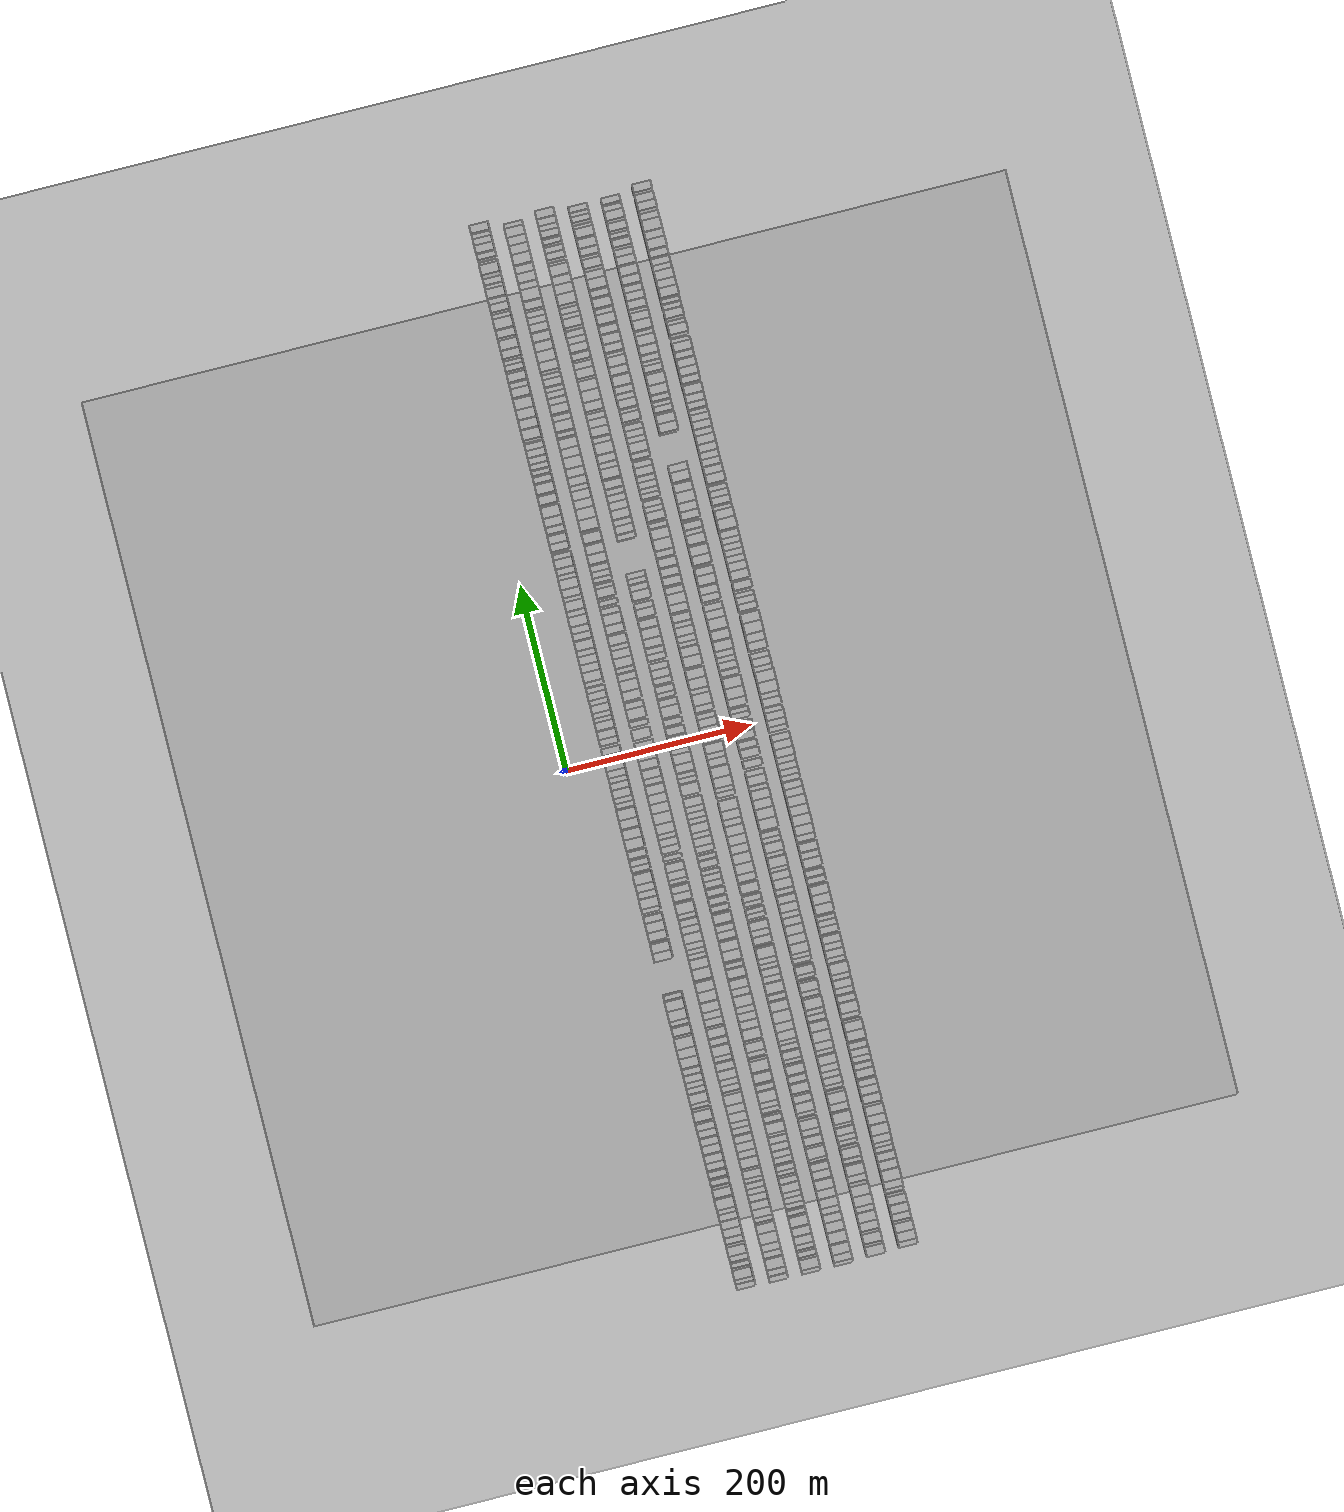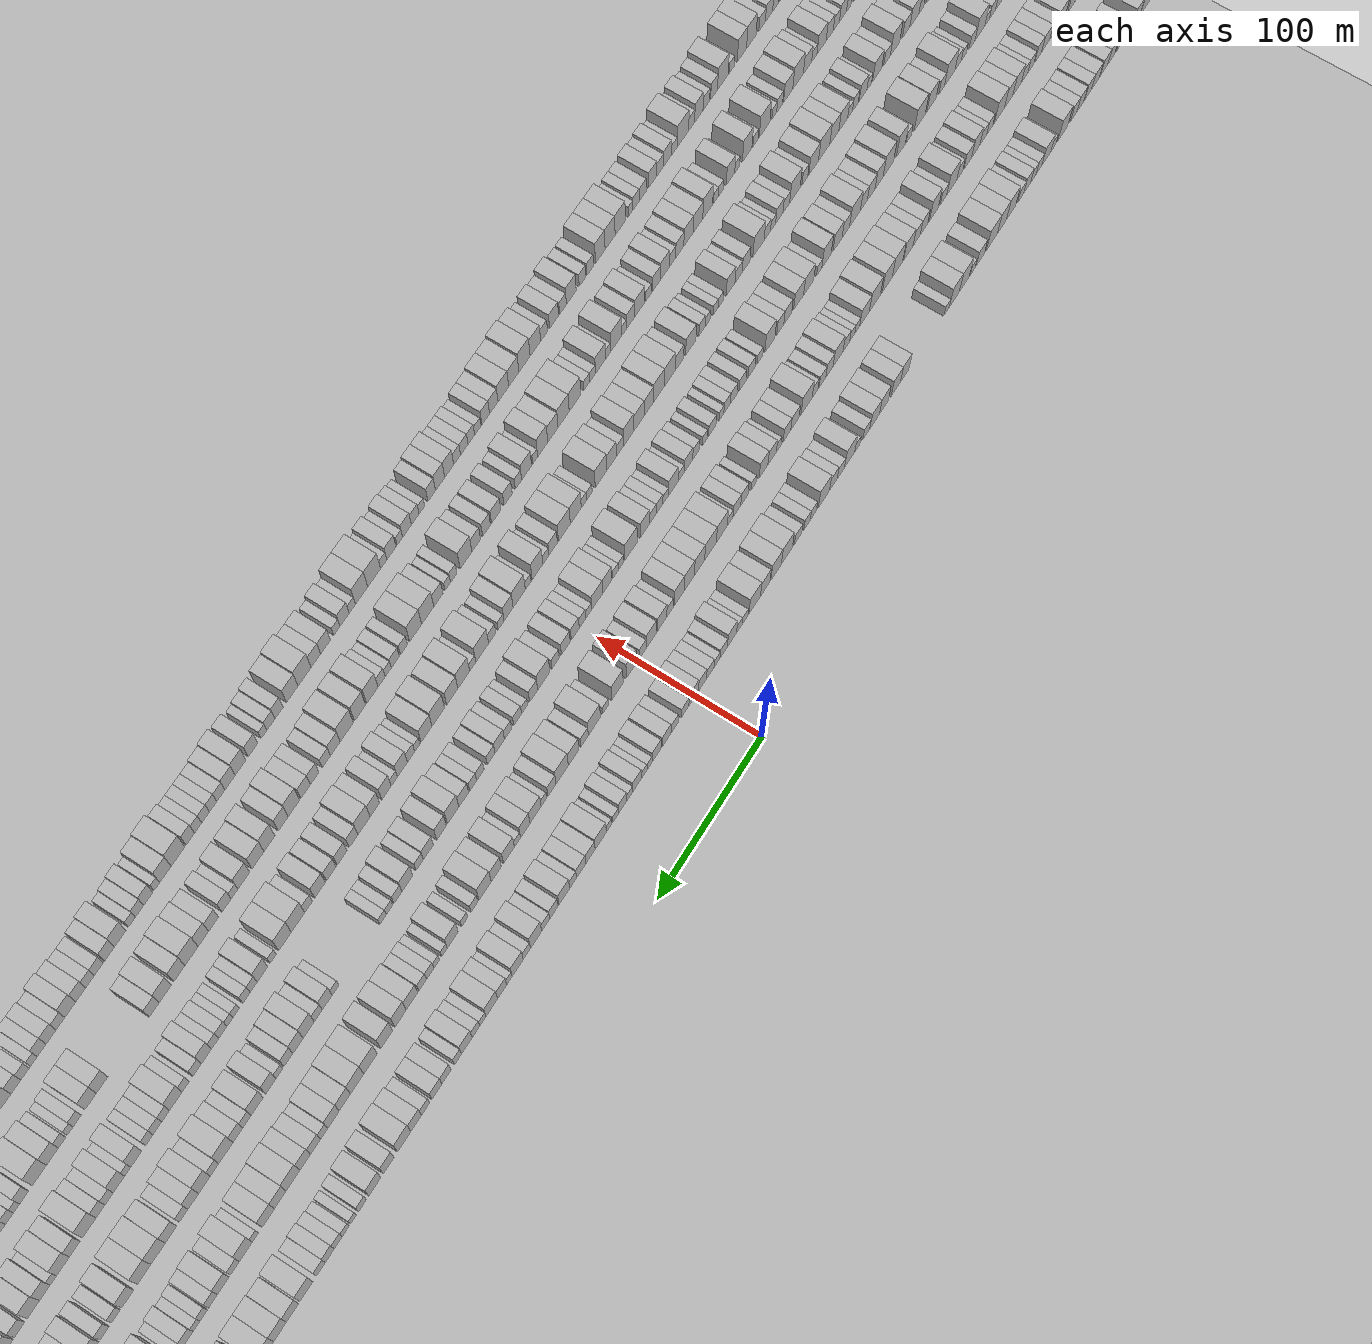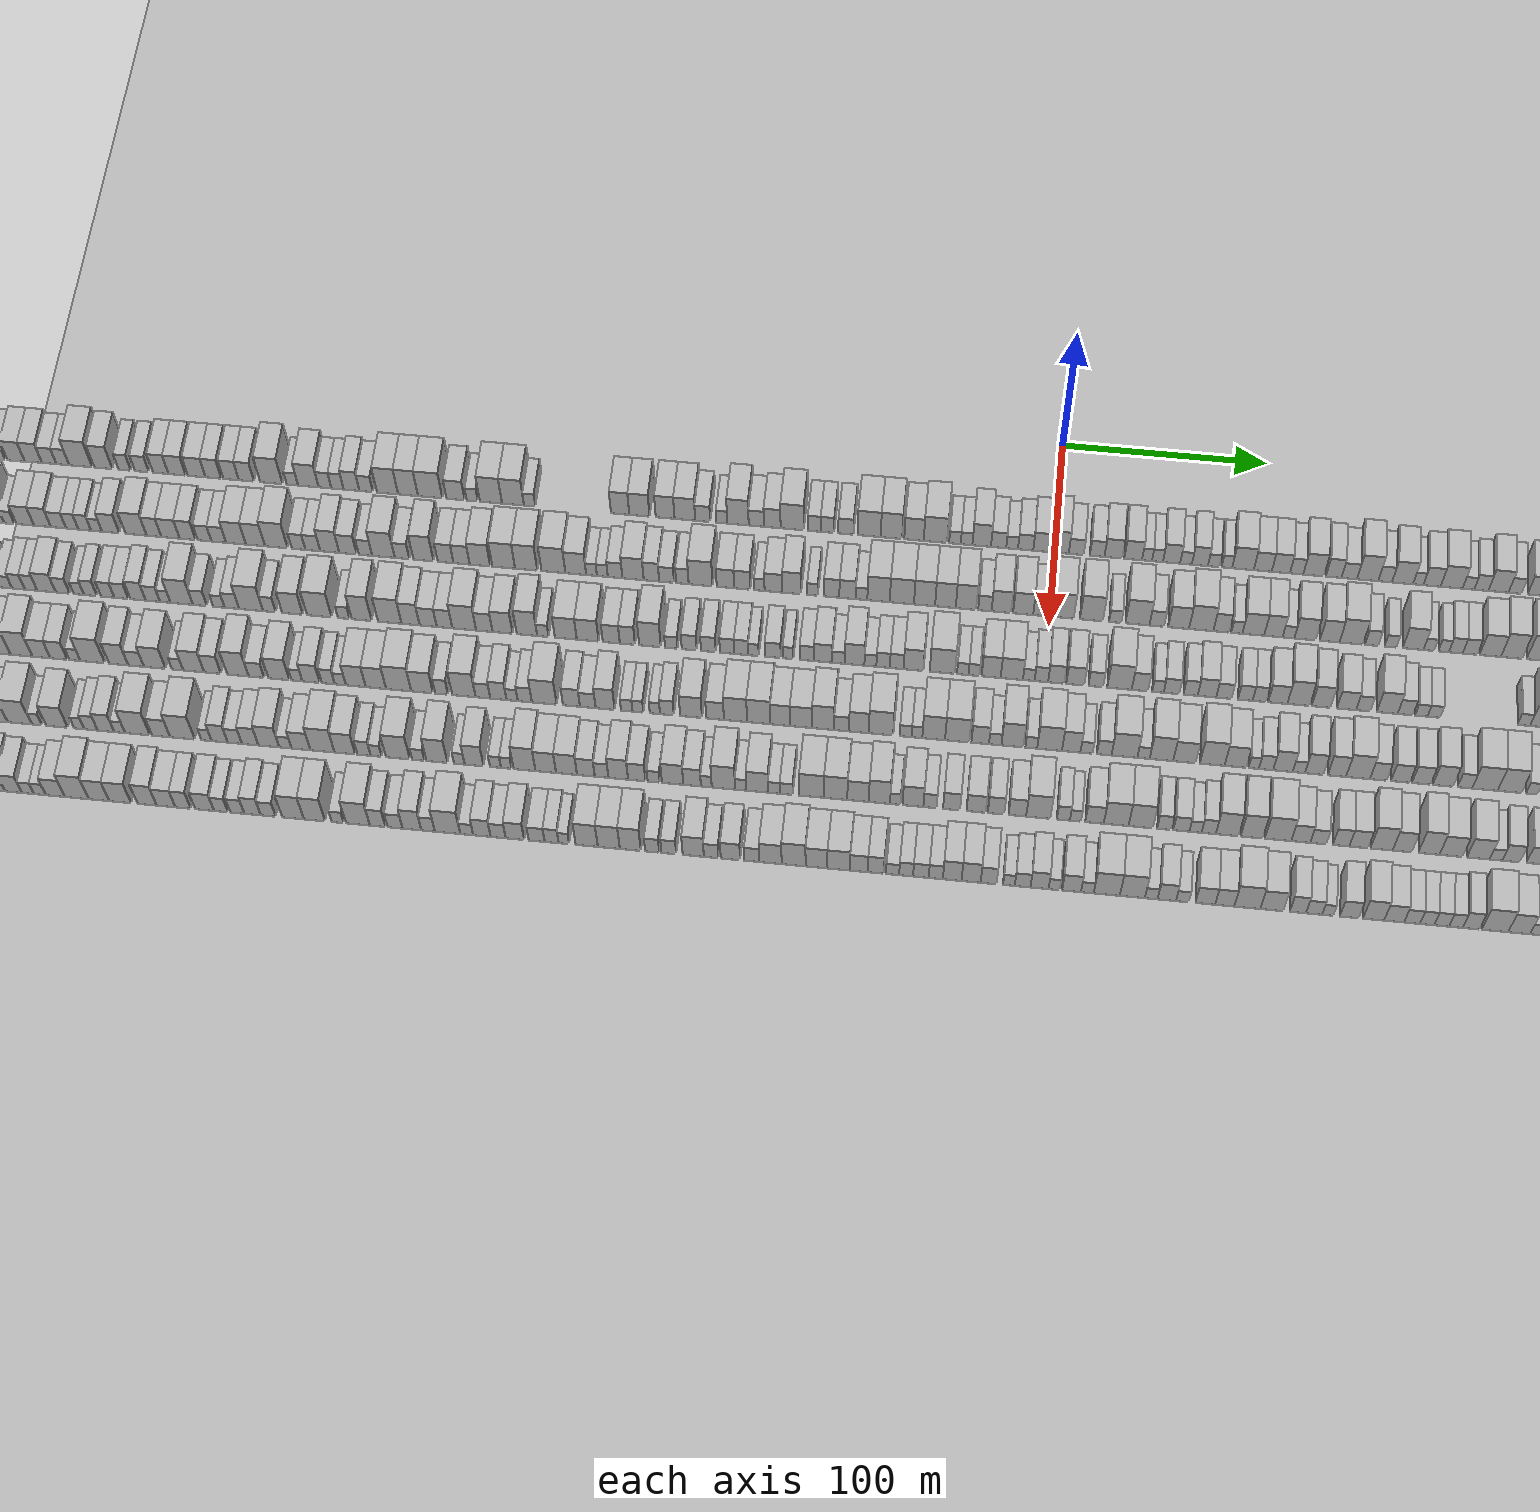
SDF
<?xml version="1.0" encoding="utf-8"?>

<sdf version="1.6">

   <world name="default">

      <gui fullscreen="0">

         <camera name="user_camera">

            <pose>-15 0 4.57585 0 0 0</pose>

            <view_controller>orbit</view_controller>

         </camera>

      </gui>

      <scene>

         <sky>

           <clouds>

             <speed>12</speed>

           </clouds>

         </sky>

         <ambient>0.4 0.4 0.4 1</ambient>

         <background>0.7 0.7 0.7 1</background>

         <shadows>1</shadows>

      </scene>

      <gravity>0 0 -9.8066</gravity>

      <magnetic_field>6e-06 2.3e-05 -4.2e-05</magnetic_field>

      <physics default="0" name="default_physics" type="ode">

         <ode>

            <solver>

               <type>quick</type>

               <iters>10</iters>

               <sor>1.0</sor>

               <use_dynamic_moi_rescaling>0</use_dynamic_moi_rescaling>

            </solver>

            <constraints>

               <cfm>0</cfm>

               <erp>0.2</erp>

               <contact_max_correcting_vel>100</contact_max_correcting_vel>

               <contact_surface_layer>0.001</contact_surface_layer>

            </constraints>

         </ode>

         <max_step_size>0.004</max_step_size>

         <real_time_factor>1</real_time_factor>

         <real_time_update_rate>250</real_time_update_rate>

      </physics>

      <light name="sun" type="directional">

         <cast_shadows>1</cast_shadows>

         <pose>0 0 10 0 0 0</pose>

         <diffuse>0.8 0.8 0.8 1</diffuse>

         <specular>0.2 0.2 0.2 1</specular>

         <attenuation>

            <range>1000</range>

            <constant>0.9</constant>

            <linear>0.01</linear>

            <quadratic>0.001</quadratic>

         </attenuation>

         <direction>-0.5 0.1 -0.9</direction>

      </light>

      <include>

         <name>ground_plane_1</name>

         <uri>model://HANNAS_ground_plane</uri>

         <pose>0 0 0  0 0 0</pose>

      </include>

      <include>

         <name>ground_plane_2</name>

         <uri>model://HANNAS_ground_plane</uri>

         <pose>100 0 0  0 0 0</pose>

      </include>

      <model name="building_1">

         <static>1</static>

         <pose frame="">50.0000 -566.1799 0 0.000000 0.000000 0.000000</pose>

         <link name="link">

            <pose frame="">0 0 6.00 0 0 0</pose>

            <collision name="collision">

               <geometry>

                  <box>

                     <size>20.0000 5.6401 12.0000</size>

                  </box>

               </geometry>

               <max_contacts>10</max_contacts>

               <surface>

                  <contact>

                     <ode/>

                  </contact>

                  <bounce/>

                  <friction>

                     <torsional>

                        <ode/>

                     </torsional>

                     <ode/>

                  </friction>

               </surface>

            </collision>

            <visual name="visual">

               <cast_shadows>0</cast_shadows>

               <geometry>

                  <box>

                     <size>20.0000 5.6401 12.0000</size>

                  </box>

               </geometry>

               <material>

                  <script>

                     <uri>model://HANNAS_wall/materials/scripts</uri>

                     <uri>model://HANNAS_wall/materials/textures</uri>

                     <name>vrc/HANNAS_wall</name>

                  </script>

               </material>

            </visual>

            <self_collide>0</self_collide>

            <enable_wind>0</enable_wind>

            <kinematic>0</kinematic>

         </link>

      </model>

      <model name="building_2">

         <static>1</static>

         <pose frame="">50.0000 -559.2902 0 0.000000 0.000000 0.000000</pose>

         <link name="link">

            <pose frame="">0 0 7.50 0 0 0</pose>

            <collision name="collision">

               <geometry>

                  <box>

                     <size>20.0000 6.1393 15.0000</size>

                  </box>

               </geometry>

               <max_contacts>10</max_contacts>

               <surface>

                  <contact>

                     <ode/>

                  </contact>

                  <bounce/>

                  <friction>

                     <torsional>

                        <ode/>

                     </torsional>

                     <ode/>

                  </friction>

               </surface>

            </collision>

            <visual name="visual">

               <cast_shadows>0</cast_shadows>

               <geometry>

                  <box>

                     <size>20.0000 6.1393 15.0000</size>

                  </box>

               </geometry>

               <material>

                  <script>

                     <uri>model://HANNAS_wall/materials/scripts</uri>

                     <uri>model://HANNAS_wall/materials/textures</uri>

                     <name>vrc/HANNAS_wall</name>

                  </script>

               </material>

            </visual>

            <self_collide>0</self_collide>

            <enable_wind>0</enable_wind>

            <kinematic>0</kinematic>

         </link>

      </model>

      <model name="building_3">

         <static>1</static>

         <pose frame="">50.0000 -551.1450 0 0.000000 0.000000 0.000000</pose>

         <link name="link">

            <pose frame="">0 0 12.00 0 0 0</pose>

            <collision name="collision">

               <geometry>

                  <box>

                     <size>20.0000 10.1512 24.0000</size>

                  </box>

               </geometry>

               <max_contacts>10</max_contacts>

               <surface>

                  <contact>

                     <ode/>

                  </contact>

                  <bounce/>

                  <friction>

                     <torsional>

                        <ode/>

                     </torsional>

                     <ode/>

                  </friction>

               </surface>

            </collision>

            <visual name="visual">

               <cast_shadows>0</cast_shadows>

               <geometry>

                  <box>

                     <size>20.0000 10.1512 24.0000</size>

                  </box>

               </geometry>

               <material>

                  <script>

                     <uri>model://HANNAS_wall/materials/scripts</uri>

                     <uri>model://HANNAS_wall/materials/textures</uri>

                     <name>vrc/HANNAS_wall</name>

                  </script>

               </material>

            </visual>

            <self_collide>0</self_collide>

            <enable_wind>0</enable_wind>

            <kinematic>0</kinematic>

         </link>

      </model>

      <model name="building_4">

         <static>1</static>

         <pose frame="">50.0000 -543.4616 0 0.000000 0.000000 0.000000</pose>

         <link name="link">

            <pose frame="">0 0 6.00 0 0 0</pose>

            <collision name="collision">

               <geometry>

                  <box>

                     <size>20.0000 5.2155 12.0000</size>

                  </box>

               </geometry>

               <max_contacts>10</max_contacts>

               <surface>

                  <contact>

                     <ode/>

                  </contact>

                  <bounce/>

                  <friction>

                     <torsional>

                        <ode/>

                     </torsional>

                     <ode/>

                  </friction>

               </surface>

            </collision>

            <visual name="visual">

               <cast_shadows>0</cast_shadows>

               <geometry>

                  <box>

                     <size>20.0000 5.2155 12.0000</size>

                  </box>

               </geometry>

               <material>

                  <script>

                     <uri>model://HANNAS_wall/materials/scripts</uri>

                     <uri>model://HANNAS_wall/materials/textures</uri>

                     <name>vrc/HANNAS_wall</name>

                  </script>

               </material>

            </visual>

            <self_collide>0</self_collide>

            <enable_wind>0</enable_wind>

            <kinematic>0</kinematic>

         </link>

      </model>

      <model name="building_5">

         <static>1</static>

         <pose frame="">50.0000 -535.2518 0 0.000000 0.000000 0.000000</pose>

         <link name="link">

            <pose frame="">0 0 7.50 0 0 0</pose>

            <collision name="collision">

               <geometry>

                  <box>

                     <size>20.0000 7.2042 15.0000</size>

                  </box>

               </geometry>

               <max_contacts>10</max_contacts>

               <surface>

                  <contact>

                     <ode/>

                  </contact>

                  <bounce/>

                  <friction>

                     <torsional>

                        <ode/>

                     </torsional>

                     <ode/>

                  </friction>

               </surface>

            </collision>

            <visual name="visual">

               <cast_shadows>0</cast_shadows>

               <geometry>

                  <box>

                     <size>20.0000 7.2042 15.0000</size>

                  </box>

               </geometry>

               <material>

                  <script>

                     <uri>model://HANNAS_wall/materials/scripts</uri>

                     <uri>model://HANNAS_wall/materials/textures</uri>

                     <name>vrc/HANNAS_wall</name>

                  </script>

               </material>

            </visual>

            <self_collide>0</self_collide>

            <enable_wind>0</enable_wind>

            <kinematic>0</kinematic>

         </link>

      </model>

      <model name="building_6">

         <static>1</static>

         <pose frame="">50.0000 -526.7217 0 0.000000 0.000000 0.000000</pose>

         <link name="link">

            <pose frame="">0 0 10.50 0 0 0</pose>

            <collision name="collision">

               <geometry>

                  <box>

                     <size>20.0000 9.8559 21.0000</size>

                  </box>

               </geometry>

               <max_contacts>10</max_contacts>

               <surface>

                  <contact>

                     <ode/>

                  </contact>

                  <bounce/>

                  <friction>

                     <torsional>

                        <ode/>

                     </torsional>

                     <ode/>

                  </friction>

               </surface>

            </collision>

            <visual name="visual">

               <cast_shadows>0</cast_shadows>

               <geometry>

                  <box>

                     <size>20.0000 9.8559 21.0000</size>

                  </box>

               </geometry>

               <material>

                  <script>

                     <uri>model://HANNAS_wall/materials/scripts</uri>

                     <uri>model://HANNAS_wall/materials/textures</uri>

                     <name>vrc/HANNAS_wall</name>

                  </script>

               </material>

            </visual>

            <self_collide>0</self_collide>

            <enable_wind>0</enable_wind>

            <kinematic>0</kinematic>

         </link>

      </model>

      <model name="building_7">

         <static>1</static>

         <pose frame="">50.0000 -516.5821 0 0.000000 0.000000 0.000000</pose>

         <link name="link">

            <pose frame="">0 0 7.50 0 0 0</pose>

            <collision name="collision">

               <geometry>

                  <box>

                     <size>20.0000 6.4233 15.0000</size>

                  </box>

               </geometry>

               <max_contacts>10</max_contacts>

               <surface>

                  <contact>

                     <ode/>

                  </contact>

                  <bounce/>

                  <friction>

                     <torsional>

                        <ode/>

                     </torsional>

                     <ode/>

                  </friction>

               </surface>

            </collision>

            <visual name="visual">

               <cast_shadows>0</cast_shadows>

               <geometry>

                  <box>

                     <size>20.0000 6.4233 15.0000</size>

                  </box>

               </geometry>

               <material>

                  <script>

                     <uri>model://HANNAS_wall/materials/scripts</uri>

                     <uri>model://HANNAS_wall/materials/textures</uri>

                     <name>vrc/HANNAS_wall</name>

                  </script>

               </material>

            </visual>

            <self_collide>0</self_collide>

            <enable_wind>0</enable_wind>

            <kinematic>0</kinematic>

         </link>

      </model>

      <model name="building_8">

         <static>1</static>

         <pose frame="">50.0000 -508.0440 0 0.000000 0.000000 0.000000</pose>

         <link name="link">

            <pose frame="">0 0 9.00 0 0 0</pose>

            <collision name="collision">

               <geometry>

                  <box>

                     <size>20.0000 8.6530 18.0000</size>

                  </box>

               </geometry>

               <max_contacts>10</max_contacts>

               <surface>

                  <contact>

                     <ode/>

                  </contact>

                  <bounce/>

                  <friction>

                     <torsional>

                        <ode/>

                     </torsional>

                     <ode/>

                  </friction>

               </surface>

            </collision>

            <visual name="visual">

               <cast_shadows>0</cast_shadows>

               <geometry>

                  <box>

                     <size>20.0000 8.6530 18.0000</size>

                  </box>

               </geometry>

               <material>

                  <script>

                     <uri>model://HANNAS_wall/materials/scripts</uri>

                     <uri>model://HANNAS_wall/materials/textures</uri>

                     <name>vrc/HANNAS_wall</name>

                  </script>

               </material>

            </visual>

            <self_collide>0</self_collide>

            <enable_wind>0</enable_wind>

            <kinematic>0</kinematic>

         </link>

      </model>

      <model name="building_9">

         <static>1</static>

         <pose frame="">50.0000 -499.4215 0 0.000000 0.000000 0.000000</pose>

         <link name="link">

            <pose frame="">0 0 9.00 0 0 0</pose>

            <collision name="collision">

               <geometry>

                  <box>

                     <size>20.0000 8.5920 18.0000</size>

                  </box>

               </geometry>

               <max_contacts>10</max_contacts>

               <surface>

                  <contact>

                     <ode/>

                  </contact>

                  <bounce/>

                  <friction>

                     <torsional>

                        <ode/>

                     </torsional>

                     <ode/>

                  </friction>

               </surface>

            </collision>

            <visual name="visual">

               <cast_shadows>0</cast_shadows>

               <geometry>

                  <box>

                     <size>20.0000 8.5920 18.0000</size>

                  </box>

               </geometry>

               <material>

                  <script>

                     <uri>model://HANNAS_wall/materials/scripts</uri>

                     <uri>model://HANNAS_wall/materials/textures</uri>

                     <name>vrc/HANNAS_wall</name>

                  </script>

               </material>

            </visual>

            <self_collide>0</self_collide>

            <enable_wind>0</enable_wind>

            <kinematic>0</kinematic>

         </link>

      </model>

      <model name="building_10">

         <static>1</static>

         <pose frame="">50.0000 -491.5432 0 0.000000 0.000000 0.000000</pose>

         <link name="link">

            <pose frame="">0 0 7.50 0 0 0</pose>

            <collision name="collision">

               <geometry>

                  <box>

                     <size>20.0000 7.1645 15.0000</size>

                  </box>

               </geometry>

               <max_contacts>10</max_contacts>

               <surface>

                  <contact>

                     <ode/>

                  </contact>

                  <bounce/>

                  <friction>

                     <torsional>

                        <ode/>

                     </torsional>

                     <ode/>

                  </friction>

               </surface>

            </collision>

            <visual name="visual">

               <cast_shadows>0</cast_shadows>

               <geometry>

                  <box>

                     <size>20.0000 7.1645 15.0000</size>

                  </box>

               </geometry>

               <material>

                  <script>

                     <uri>model://HANNAS_wall/materials/scripts</uri>

                     <uri>model://HANNAS_wall/materials/textures</uri>

                     <name>vrc/HANNAS_wall</name>

                  </script>

               </material>

            </visual>

            <self_collide>0</self_collide>

            <enable_wind>0</enable_wind>

            <kinematic>0</kinematic>

         </link>

      </model>

      <model name="building_11">

         <static>1</static>

         <pose frame="">50.0000 -484.7730 0 0.000000 0.000000 0.000000</pose>

         <link name="link">

            <pose frame="">0 0 7.50 0 0 0</pose>

            <collision name="collision">

               <geometry>

                  <box>

                     <size>20.0000 6.3760 15.0000</size>

                  </box>

               </geometry>

               <max_contacts>10</max_contacts>

               <surface>

                  <contact>

                     <ode/>

                  </contact>

                  <bounce/>

                  <friction>

                     <torsional>

                        <ode/>

                     </torsional>

                     <ode/>

                  </friction>

               </surface>

            </collision>

            <visual name="visual">

               <cast_shadows>0</cast_shadows>

               <geometry>

                  <box>

                     <size>20.0000 6.3760 15.0000</size>

                  </box>

               </geometry>

               <material>

                  <script>

                     <uri>model://HANNAS_wall/materials/scripts</uri>

                     <uri>model://HANNAS_wall/materials/textures</uri>

                     <name>vrc/HANNAS_wall</name>

                  </script>

               </material>

            </visual>

            <self_collide>0</self_collide>

            <enable_wind>0</enable_wind>

            <kinematic>0</kinematic>

         </link>

      </model>

      <model name="building_12">

         <static>1</static>

         <pose frame="">50.0000 -475.8655 0 0.000000 0.000000 0.000000</pose>

         <link name="link">

            <pose frame="">0 0 12.00 0 0 0</pose>

            <collision name="collision">

               <geometry>

                  <box>

                     <size>20.0000 11.4389 24.0000</size>

                  </box>

               </geometry>

               <max_contacts>10</max_contacts>

               <surface>

                  <contact>

                     <ode/>

                  </contact>

                  <bounce/>

                  <friction>

                     <torsional>

                        <ode/>

                     </torsional>

                     <ode/>

                  </friction>

               </surface>

            </collision>

            <visual name="visual">

               <cast_shadows>0</cast_shadows>

               <geometry>

                  <box>

                     <size>20.0000 11.4389 24.0000</size>

                  </box>

               </geometry>

               <material>

                  <script>

                     <uri>model://HANNAS_wall/materials/scripts</uri>

                     <uri>model://HANNAS_wall/materials/textures</uri>

                     <name>vrc/HANNAS_wall</name>

                  </script>

               </material>

            </visual>

            <self_collide>0</self_collide>

            <enable_wind>0</enable_wind>

            <kinematic>0</kinematic>

         </link>

      </model>

      <model name="building_13">

         <static>1</static>

         <pose frame="">50.0000 -464.6407 0 0.000000 0.000000 0.000000</pose>

         <link name="link">

            <pose frame="">0 0 10.50 0 0 0</pose>

            <collision name="collision">

               <geometry>

                  <box>

                     <size>20.0000 9.0108 21.0000</size>

                  </box>

               </geometry>

               <max_contacts>10</max_contacts>

               <surface>

                  <contact>

                     <ode/>

                  </contact>

                  <bounce/>

                  <friction>

                     <torsional>

                        <ode/>

                     </torsional>

                     <ode/>

                  </friction>

               </surface>

            </collision>

            <visual name="visual">

               <cast_shadows>0</cast_shadows>

               <geometry>

                  <box>

                     <size>20.0000 9.0108 21.0000</size>

                  </box>

               </geometry>

               <material>

                  <script>

                     <uri>model://HANNAS_wall/materials/scripts</uri>

                     <uri>model://HANNAS_wall/materials/textures</uri>

                     <name>vrc/HANNAS_wall</name>

                  </script>

               </material>

            </visual>

            <self_collide>0</self_collide>

            <enable_wind>0</enable_wind>

            <kinematic>0</kinematic>

         </link>

      </model>

      <model name="building_14">

         <static>1</static>

         <pose frame="">50.0000 -454.0856 0 0.000000 0.000000 0.000000</pose>

         <link name="link">

            <pose frame="">0 0 7.50 0 0 0</pose>

            <collision name="collision">

               <geometry>

                  <box>

                     <size>20.0000 6.0993 15.0000</size>

                  </box>

               </geometry>

               <max_contacts>10</max_contacts>

               <surface>

                  <contact>

                     <ode/>

                  </contact>

                  <bounce/>

                  <friction>

                     <torsional>

                        <ode/>

                     </torsional>

                     <ode/>

                  </friction>

               </surface>

            </collision>

            <visual name="visual">

               <cast_shadows>0</cast_shadows>

               <geometry>

                  <box>

                     <size>20.0000 6.0993 15.0000</size>

                  </box>

               </geometry>

               <material>

                  <script>

                     <uri>model://HANNAS_wall/materials/scripts</uri>

                     <uri>model://HANNAS_wall/materials/textures</uri>

                     <name>vrc/HANNAS_wall</name>

                  </script>

               </material>

            </visual>

            <self_collide>0</self_collide>

            <enable_wind>0</enable_wind>

            <kinematic>0</kinematic>

         </link>

      </model>

      <model name="building_15">

         <static>1</static>

         <pose frame="">50.0000 -445.5829 0 0.000000 0.000000 0.000000</pose>

         <link name="link">

            <pose frame="">0 0 7.50 0 0 0</pose>

            <collision name="collision">

               <geometry>

                  <box>

                     <size>20.0000 6.9061 15.0000</size>

                  </box>

               </geometry>

               <max_contacts>10</max_contacts>

               <surface>

                  <contact>

                     <ode/>

                  </contact>

                  <bounce/>

                  <friction>

                     <torsional>

                        <ode/>

                     </torsional>

                     <ode/>

                  </friction>

               </surface>

            </collision>

            <visual name="visual">

               <cast_shadows>0</cast_shadows>

               <geometry>

                  <box>

                     <size>20.0000 6.9061 15.0000</size>

                  </box>

               </geometry>

               <material>

                  <script>

                     <uri>model://HANNAS_wall/materials/scripts</uri>

                     <uri>model://HANNAS_wall/materials/textures</uri>

                     <name>vrc/HANNAS_wall</name>

                  </script>

               </material>

            </visual>

            <self_collide>0</self_collide>

            <enable_wind>0</enable_wind>

            <kinematic>0</kinematic>

         </link>

      </model>

      <model name="building_16">

         <static>1</static>

         <pose frame="">50.0000 -436.2913 0 0.000000 0.000000 0.000000</pose>

         <link name="link">

            <pose frame="">0 0 9.00 0 0 0</pose>

            <collision name="collision">

               <geometry>

                  <box>

                     <size>20.0000 7.6771 18.0000</size>

                  </box>

               </geometry>

               <max_contacts>10</max_contacts>

               <surface>

                  <contact>

                     <ode/>

                  </contact>

                  <bounce/>

                  <friction>

                     <torsional>

                        <ode/>

                     </torsional>

                     <ode/>

                  </friction>

               </surface>

            </collision>

            <visual name="visual">

               <cast_shadows>0</cast_shadows>

               <geometry>

                  <box>

                     <size>20.0000 7.6771 18.0000</size>

                  </box>

               </geometry>

               <material>

                  <script>

                     <uri>model://HANNAS_wall/materials/scripts</uri>

                     <uri>model://HANNAS_wall/materials/textures</uri>

                     <name>vrc/HANNAS_wall</name>

                  </script>

               </material>

            </visual>

            <self_collide>0</self_collide>

            <enable_wind>0</enable_wind>

            <kinematic>0</kinematic>

         </link>

      </model>

      <model name="building_17">

         <static>1</static>

         <pose frame="">50.0000 -428.1768 0 0.000000 0.000000 0.000000</pose>

         <link name="link">

            <pose frame="">0 0 9.00 0 0 0</pose>

            <collision name="collision">

               <geometry>

                  <box>

                     <size>20.0000 8.5519 18.0000</size>

                  </box>

               </geometry>

               <max_contacts>10</max_contacts>

               <surface>

                  <contact>

                     <ode/>

                  </contact>

                  <bounce/>

                  <friction>

                     <torsional>

                        <ode/>

                     </torsional>

                     <ode/>

                  </friction>

               </surface>

            </collision>

            <visual name="visual">

               <cast_shadows>0</cast_shadows>

               <geometry>

                  <box>

                     <size>20.0000 8.5519 18.0000</size>

                  </box>

               </geometry>

               <material>

                  <script>

                     <uri>model://HANNAS_wall/materials/scripts</uri>

                     <uri>model://HANNAS_wall/materials/textures</uri>

                     <name>vrc/HANNAS_wall</name>

                  </script>

               </material>

            </visual>

            <self_collide>0</self_collide>

            <enable_wind>0</enable_wind>

            <kinematic>0</kinematic>

         </link>

      </model>

      <model name="building_18">

         <static>1</static>

         <pose frame="">50.0000 -418.5068 0 0.000000 0.000000 0.000000</pose>

         <link name="link">

            <pose frame="">0 0 9.00 0 0 0</pose>

            <collision name="collision">

               <geometry>

                  <box>

                     <size>20.0000 8.7880 18.0000</size>

                  </box>

               </geometry>

               <max_contacts>10</max_contacts>

               <surface>

                  <contact>

                     <ode/>

                  </contact>

                  <bounce/>

                  <friction>

                     <torsional>

                        <ode/>

                     </torsional>

                     <ode/>

                  </friction>

               </surface>

            </collision>

            <visual name="visual">

               <cast_shadows>0</cast_shadows>

               <geometry>

                  <box>

                     <size>20.0000 8.7880 18.0000</size>

                  </box>

               </geometry>

               <material>

                  <script>

                     <uri>model://HANNAS_wall/materials/scripts</uri>

                     <uri>model://HANNAS_wall/materials/textures</uri>

                     <name>vrc/HANNAS_wall</name>

                  </script>

               </material>

            </visual>

            <self_collide>0</self_collide>

            <enable_wind>0</enable_wind>

            <kinematic>0</kinematic>

         </link>

      </model>

      <model name="building_19">

         <static>1</static>

         <pose frame="">50.0000 -410.2120 0 0.000000 0.000000 0.000000</pose>

         <link name="link">

            <pose frame="">0 0 9.00 0 0 0</pose>

            <collision name="collision">

               <geometry>

                  <box>

                     <size>20.0000 7.8017 18.0000</size>

                  </box>

               </geometry>

               <max_contacts>10</max_contacts>

               <surface>

                  <contact>

                     <ode/>

                  </contact>

                  <bounce/>

                  <friction>

                     <torsional>

                        <ode/>

                     </torsional>

                     <ode/>

                  </friction>

               </surface>

            </collision>

            <visual name="visual">

               <cast_shadows>0</cast_shadows>

               <geometry>

                  <box>

                     <size>20.0000 7.8017 18.0000</size>

                  </box>

               </geometry>

               <material>

                  <script>

                     <uri>model://HANNAS_wall/materials/scripts</uri>

                     <uri>model://HANNAS_wall/materials/textures</uri>

                     <name>vrc/HANNAS_wall</name>

                  </script>

               </material>

            </visual>

            <self_collide>0</self_collide>

            <enable_wind>0</enable_wind>

            <kinematic>0</kinematic>

         </link>

      </model>

      <model name="building_20">

         <static>1</static>

         <pose frame="">50.0000 -401.4914 0 0.000000 0.000000 0.000000</pose>

         <link name="link">

            <pose frame="">0 0 9.00 0 0 0</pose>

            <collision name="collision">

               <geometry>

                  <box>

                     <size>20.0000 7.6396 18.0000</size>

                  </box>

               </geometry>

               <max_contacts>10</max_contacts>

               <surface>

                  <contact>

                     <ode/>

                  </contact>

                  <bounce/>

                  <friction>

                     <torsional>

                        <ode/>

                     </torsional>

                     <ode/>

                  </friction>

               </surface>

            </collision>

            <visual name="visual">

               <cast_shadows>0</cast_shadows>

               <geometry>

                  <box>

                     <size>20.0000 7.6396 18.0000</size>

                  </box>

               </geometry>

               <material>

                  <script>

                     <uri>model://HANNAS_wall/materials/scripts</uri>

                     <uri>model://HANNAS_wall/materials/textures</uri>

                     <name>vrc/HANNAS_wall</name>

                  </script>

               </material>

            </visual>

            <self_collide>0</self_collide>

            <enable_wind>0</enable_wind>

            <kinematic>0</kinematic>

         </link>

      </model>

      <model name="building_21">

         <static>1</static>

         <pose frame="">50.0000 -393.9157 0 0.000000 0.000000 0.000000</pose>

         <link name="link">

            <pose frame="">0 0 9.00 0 0 0</pose>

            <collision name="collision">

               <geometry>

                  <box>

                     <size>20.0000 7.5118 18.0000</size>

                  </box>

               </geometry>

               <max_contacts>10</max_contacts>

               <surface>

                  <contact>

                     <ode/>

                  </contact>

                  <bounce/>

                  <friction>

                     <torsional>

                        <ode/>

                     </torsional>

                     <ode/>

                  </friction>

               </surface>

            </collision>

            <visual name="visual">

               <cast_shadows>0</cast_shadows>

               <geometry>

                  <box>

                     <size>20.0000 7.5118 18.0000</size>

                  </box>

               </geometry>

               <material>

                  <script>

                     <uri>model://HANNAS_wall/materials/scripts</uri>

                     <uri>model://HANNAS_wall/materials/textures</uri>

                     <name>vrc/HANNAS_wall</name>

                  </script>

               </material>

            </visual>

            <self_collide>0</self_collide>

            <enable_wind>0</enable_wind>

            <kinematic>0</kinematic>

         </link>

      </model>

      <model name="building_22">

         <static>1</static>

         <pose frame="">50.0000 -381.6460 0 0.000000 0.000000 0.000000</pose>

         <link name="link">

            <pose frame="">0 0 12.00 0 0 0</pose>

            <collision name="collision">

               <geometry>

                  <box>

                     <size>20.0000 11.0276 24.0000</size>

                  </box>

               </geometry>

               <max_contacts>10</max_contacts>

               <surface>

                  <contact>

                     <ode/>

                  </contact>

                  <bounce/>

                  <friction>

                     <torsional>

                        <ode/>

                     </torsional>

                     <ode/>

                  </friction>

               </surface>

            </collision>

            <visual name="visual">

               <cast_shadows>0</cast_shadows>

               <geometry>

                  <box>

                     <size>20.0000 11.0276 24.0000</size>

                  </box>

               </geometry>

               <material>

                  <script>

                     <uri>model://HANNAS_wall/materials/scripts</uri>

                     <uri>model://HANNAS_wall/materials/textures</uri>

                     <name>vrc/HANNAS_wall</name>

                  </script>

               </material>

            </visual>

            <self_collide>0</self_collide>

            <enable_wind>0</enable_wind>

            <kinematic>0</kinematic>

         </link>

      </model>

      <model name="building_23">

         <static>1</static>

         <pose frame="">50.0000 -371.3192 0 0.000000 0.000000 0.000000</pose>

         <link name="link">

            <pose frame="">0 0 6.00 0 0 0</pose>

            <collision name="collision">

               <geometry>

                  <box>

                     <size>20.0000 5.6260 12.0000</size>

                  </box>

               </geometry>

               <max_contacts>10</max_contacts>

               <surface>

                  <contact>

                     <ode/>

                  </contact>

                  <bounce/>

                  <friction>

                     <torsional>

                        <ode/>

                     </torsional>

                     <ode/>

                  </friction>

               </surface>

            </collision>

            <visual name="visual">

               <cast_shadows>0</cast_shadows>

               <geometry>

                  <box>

                     <size>20.0000 5.6260 12.0000</size>

                  </box>

               </geometry>

               <material>

                  <script>

                     <uri>model://HANNAS_wall/materials/scripts</uri>

                     <uri>model://HANNAS_wall/materials/textures</uri>

                     <name>vrc/HANNAS_wall</name>

                  </script>

               </material>

            </visual>

            <self_collide>0</self_collide>

            <enable_wind>0</enable_wind>

            <kinematic>0</kinematic>

         </link>

      </model>

      <model name="building_24">

         <static>1</static>

         <pose frame="">50.0000 -363.4309 0 0.000000 0.000000 0.000000</pose>

         <link name="link">

            <pose frame="">0 0 10.50 0 0 0</pose>

            <collision name="collision">

               <geometry>

                  <box>

                     <size>20.0000 10.1506 21.0000</size>

                  </box>

               </geometry>

               <max_contacts>10</max_contacts>

               <surface>

                  <contact>

                     <ode/>

                  </contact>

                  <bounce/>

                  <friction>

                     <torsional>

                        <ode/>

                     </torsional>

                     <ode/>

                  </friction>

               </surface>

            </collision>

            <visual name="visual">

               <cast_shadows>0</cast_shadows>

               <geometry>

                  <box>

                     <size>20.0000 10.1506 21.0000</size>

                  </box>

               </geometry>

               <material>

                  <script>

                     <uri>model://HANNAS_wall/materials/scripts</uri>

                     <uri>model://HANNAS_wall/materials/textures</uri>

                     <name>vrc/HANNAS_wall</name>

                  </script>

               </material>

            </visual>

            <self_collide>0</self_collide>

            <enable_wind>0</enable_wind>

            <kinematic>0</kinematic>

         </link>

      </model>

      <model name="building_25">

         <static>1</static>

         <pose frame="">50.0000 -355.2272 0 0.000000 0.000000 0.000000</pose>

         <link name="link">

            <pose frame="">0 0 7.50 0 0 0</pose>

            <collision name="collision">

               <geometry>

                  <box>

                     <size>20.0000 6.2568 15.0000</size>

                  </box>

               </geometry>

               <max_contacts>10</max_contacts>

               <surface>

                  <contact>

                     <ode/>

                  </contact>

                  <bounce/>

                  <friction>

                     <torsional>

                        <ode/>

                     </torsional>

                     <ode/>

                  </friction>

               </surface>

            </collision>

            <visual name="visual">

               <cast_shadows>0</cast_shadows>

               <geometry>

                  <box>

                     <size>20.0000 6.2568 15.0000</size>

                  </box>

               </geometry>

               <material>

                  <script>

                     <uri>model://HANNAS_wall/materials/scripts</uri>

                     <uri>model://HANNAS_wall/materials/textures</uri>

                     <name>vrc/HANNAS_wall</name>

                  </script>

               </material>

            </visual>

            <self_collide>0</self_collide>

            <enable_wind>0</enable_wind>

            <kinematic>0</kinematic>

         </link>

      </model>

      <model name="building_26">

         <static>1</static>

         <pose frame="">50.0000 -349.0921 0 0.000000 0.000000 0.000000</pose>

         <link name="link">

            <pose frame="">0 0 7.50 0 0 0</pose>

            <collision name="collision">

               <geometry>

                  <box>

                     <size>20.0000 6.0135 15.0000</size>

                  </box>

               </geometry>

               <max_contacts>10</max_contacts>

               <surface>

                  <contact>

                     <ode/>

                  </contact>

                  <bounce/>

                  <friction>

                     <torsional>

                        <ode/>

                     </torsional>

                     <ode/>

                  </friction>

               </surface>

            </collision>

            <visual name="visual">

               <cast_shadows>0</cast_shadows>

               <geometry>

                  <box>

                     <size>20.0000 6.0135 15.0000</size>

                  </box>

               </geometry>

               <material>

                  <script>

                     <uri>model://HANNAS_wall/materials/scripts</uri>

                     <uri>model://HANNAS_wall/materials/textures</uri>

                     <name>vrc/HANNAS_wall</name>

                  </script>

               </material>

            </visual>

            <self_collide>0</self_collide>

            <enable_wind>0</enable_wind>

            <kinematic>0</kinematic>

         </link>

      </model>

      <model name="building_27">

         <static>1</static>

         <pose frame="">50.0000 -342.2209 0 0.000000 0.000000 0.000000</pose>

         <link name="link">

            <pose frame="">0 0 9.00 0 0 0</pose>

            <collision name="collision">

               <geometry>

                  <box>

                     <size>20.0000 7.7289 18.0000</size>

                  </box>

               </geometry>

               <max_contacts>10</max_contacts>

               <surface>

                  <contact>

                     <ode/>

                  </contact>

                  <bounce/>

                  <friction>

                     <torsional>

                        <ode/>

                     </torsional>

                     <ode/>

                  </friction>

               </surface>

            </collision>

            <visual name="visual">

               <cast_shadows>0</cast_shadows>

               <geometry>

                  <box>

                     <size>20.0000 7.7289 18.0000</size>

                  </box>

               </geometry>

               <material>

                  <script>

                     <uri>model://HANNAS_wall/materials/scripts</uri>

                     <uri>model://HANNAS_wall/materials/textures</uri>

                     <name>vrc/HANNAS_wall</name>

                  </script>

               </material>

            </visual>

            <self_collide>0</self_collide>

            <enable_wind>0</enable_wind>

            <kinematic>0</kinematic>

         </link>

      </model>

      <model name="building_28">

         <static>1</static>

         <pose frame="">50.0000 -335.0073 0 0.000000 0.000000 0.000000</pose>

         <link name="link">

            <pose frame="">0 0 7.50 0 0 0</pose>

            <collision name="collision">

               <geometry>

                  <box>

                     <size>20.0000 6.6983 15.0000</size>

                  </box>

               </geometry>

               <max_contacts>10</max_contacts>

               <surface>

                  <contact>

                     <ode/>

                  </contact>

                  <bounce/>

                  <friction>

                     <torsional>

                        <ode/>

                     </torsional>

                     <ode/>

                  </friction>

               </surface>

            </collision>

            <visual name="visual">

               <cast_shadows>0</cast_shadows>

               <geometry>

                  <box>

                     <size>20.0000 6.6983 15.0000</size>

                  </box>

               </geometry>

               <material>

                  <script>

                     <uri>model://HANNAS_wall/materials/scripts</uri>

                     <uri>model://HANNAS_wall/materials/textures</uri>

                     <name>vrc/HANNAS_wall</name>

                  </script>

               </material>

            </visual>

            <self_collide>0</self_collide>

            <enable_wind>0</enable_wind>

            <kinematic>0</kinematic>

         </link>

      </model>

      <model name="building_29">

         <static>1</static>

         <pose frame="">50.0000 -324.4757 0 0.000000 0.000000 0.000000</pose>

         <link name="link">

            <pose frame="">0 0 12.00 0 0 0</pose>

            <collision name="collision">

               <geometry>

                  <box>

                     <size>20.0000 10.3648 24.0000</size>

                  </box>

               </geometry>

               <max_contacts>10</max_contacts>

               <surface>

                  <contact>

                     <ode/>

                  </contact>

                  <bounce/>

                  <friction>

                     <torsional>

                        <ode/>

                     </torsional>

                     <ode/>

                  </friction>

               </surface>

            </collision>

            <visual name="visual">

               <cast_shadows>0</cast_shadows>

               <geometry>

                  <box>

                     <size>20.0000 10.3648 24.0000</size>

                  </box>

               </geometry>

               <material>

                  <script>

                     <uri>model://HANNAS_wall/materials/scripts</uri>

                     <uri>model://HANNAS_wall/materials/textures</uri>

                     <name>vrc/HANNAS_wall</name>

                  </script>

               </material>

            </visual>

            <self_collide>0</self_collide>

            <enable_wind>0</enable_wind>

            <kinematic>0</kinematic>

         </link>

      </model>

      <model name="building_30">

         <static>1</static>

         <pose frame="">50.0000 -314.4216 0 0.000000 0.000000 0.000000</pose>

         <link name="link">

            <pose frame="">0 0 12.00 0 0 0</pose>

            <collision name="collision">

               <geometry>

                  <box>

                     <size>20.0000 9.7434 24.0000</size>

                  </box>

               </geometry>

               <max_contacts>10</max_contacts>

               <surface>

                  <contact>

                     <ode/>

                  </contact>

                  <bounce/>

                  <friction>

                     <torsional>

                        <ode/>

                     </torsional>

                     <ode/>

                  </friction>

               </surface>

            </collision>

            <visual name="visual">

               <cast_shadows>0</cast_shadows>

               <geometry>

                  <box>

                     <size>20.0000 9.7434 24.0000</size>

                  </box>

               </geometry>

               <material>

                  <script>

                     <uri>model://HANNAS_wall/materials/scripts</uri>

                     <uri>model://HANNAS_wall/materials/textures</uri>

                     <name>vrc/HANNAS_wall</name>

                  </script>

               </material>

            </visual>

            <self_collide>0</self_collide>

            <enable_wind>0</enable_wind>

            <kinematic>0</kinematic>

         </link>

      </model>

      <model name="building_31">

         <static>1</static>

         <pose frame="">50.0000 -303.5805 0 0.000000 0.000000 0.000000</pose>

         <link name="link">

            <pose frame="">0 0 12.00 0 0 0</pose>

            <collision name="collision">

               <geometry>

                  <box>

                     <size>20.0000 11.9389 24.0000</size>

                  </box>

               </geometry>

               <max_contacts>10</max_contacts>

               <surface>

                  <contact>

                     <ode/>

                  </contact>

                  <bounce/>

                  <friction>

                     <torsional>

                        <ode/>

                     </torsional>

                     <ode/>

                  </friction>

               </surface>

            </collision>

            <visual name="visual">

               <cast_shadows>0</cast_shadows>

               <geometry>

                  <box>

                     <size>20.0000 11.9389 24.0000</size>

                  </box>

               </geometry>

               <material>

                  <script>

                     <uri>model://HANNAS_wall/materials/scripts</uri>

                     <uri>model://HANNAS_wall/materials/textures</uri>

                     <name>vrc/HANNAS_wall</name>

                  </script>

               </material>

            </visual>

            <self_collide>0</self_collide>

            <enable_wind>0</enable_wind>

            <kinematic>0</kinematic>

         </link>

      </model>

      <model name="building_32">

         <static>1</static>

         <pose frame="">50.0000 -291.1499 0 0.000000 0.000000 0.000000</pose>

         <link name="link">

            <pose frame="">0 0 9.00 0 0 0</pose>

            <collision name="collision">

               <geometry>

                  <box>

                     <size>20.0000 8.9223 18.0000</size>

                  </box>

               </geometry>

               <max_contacts>10</max_contacts>

               <surface>

                  <contact>

                     <ode/>

                  </contact>

                  <bounce/>

                  <friction>

                     <torsional>

                        <ode/>

                     </torsional>

                     <ode/>

                  </friction>

               </surface>

            </collision>

            <visual name="visual">

               <cast_shadows>0</cast_shadows>

               <geometry>

                  <box>

                     <size>20.0000 8.9223 18.0000</size>

                  </box>

               </geometry>

               <material>

                  <script>

                     <uri>model://HANNAS_wall/materials/scripts</uri>

                     <uri>model://HANNAS_wall/materials/textures</uri>

                     <name>vrc/HANNAS_wall</name>

                  </script>

               </material>

            </visual>

            <self_collide>0</self_collide>

            <enable_wind>0</enable_wind>

            <kinematic>0</kinematic>

         </link>

      </model>

      <model name="building_33">

         <static>1</static>

         <pose frame="">50.0000 -282.9721 0 0.000000 0.000000 0.000000</pose>

         <link name="link">

            <pose frame="">0 0 6.00 0 0 0</pose>

            <collision name="collision">

               <geometry>

                  <box>

                     <size>20.0000 5.4334 12.0000</size>

                  </box>

               </geometry>

               <max_contacts>10</max_contacts>

               <surface>

                  <contact>

                     <ode/>

                  </contact>

                  <bounce/>

                  <friction>

                     <torsional>

                        <ode/>

                     </torsional>

                     <ode/>

                  </friction>

               </surface>

            </collision>

            <visual name="visual">

               <cast_shadows>0</cast_shadows>

               <geometry>

                  <box>

                     <size>20.0000 5.4334 12.0000</size>

                  </box>

               </geometry>

               <material>

                  <script>

                     <uri>model://HANNAS_wall/materials/scripts</uri>

                     <uri>model://HANNAS_wall/materials/textures</uri>

                     <name>vrc/HANNAS_wall</name>

                  </script>

               </material>

            </visual>

            <self_collide>0</self_collide>

            <enable_wind>0</enable_wind>

            <kinematic>0</kinematic>

         </link>

      </model>

      <model name="building_34">

         <static>1</static>

         <pose frame="">50.0000 -273.8213 0 0.000000 0.000000 0.000000</pose>

         <link name="link">

            <pose frame="">0 0 12.00 0 0 0</pose>

            <collision name="collision">

               <geometry>

                  <box>

                     <size>20.0000 10.8682 24.0000</size>

                  </box>

               </geometry>

               <max_contacts>10</max_contacts>

               <surface>

                  <contact>

                     <ode/>

                  </contact>

                  <bounce/>

                  <friction>

                     <torsional>

                        <ode/>

                     </torsional>

                     <ode/>

                  </friction>

               </surface>

            </collision>

            <visual name="visual">

               <cast_shadows>0</cast_shadows>

               <geometry>

                  <box>

                     <size>20.0000 10.8682 24.0000</size>

                  </box>

               </geometry>

               <material>

                  <script>

                     <uri>model://HANNAS_wall/materials/scripts</uri>

                     <uri>model://HANNAS_wall/materials/textures</uri>

                     <name>vrc/HANNAS_wall</name>

                  </script>

               </material>

            </visual>

            <self_collide>0</self_collide>

            <enable_wind>0</enable_wind>

            <kinematic>0</kinematic>

         </link>

      </model>

      <model name="building_35">

         <static>1</static>

         <pose frame="">50.0000 -263.0120 0 0.000000 0.000000 0.000000</pose>

         <link name="link">

            <pose frame="">0 0 12.00 0 0 0</pose>

            <collision name="collision">

               <geometry>

                  <box>

                     <size>20.0000 10.7503 24.0000</size>

                  </box>

               </geometry>

               <max_contacts>10</max_contacts>

               <surface>

                  <contact>

                     <ode/>

                  </contact>

                  <bounce/>

                  <friction>

                     <torsional>

                        <ode/>

                     </torsional>

                     <ode/>

                  </friction>

               </surface>

            </collision>

            <visual name="visual">

               <cast_shadows>0</cast_shadows>

               <geometry>

                  <box>

                     <size>20.0000 10.7503 24.0000</size>

                  </box>

               </geometry>

               <material>

                  <script>

                     <uri>model://HANNAS_wall/materials/scripts</uri>

                     <uri>model://HANNAS_wall/materials/textures</uri>

                     <name>vrc/HANNAS_wall</name>

                  </script>

               </material>

            </visual>

            <self_collide>0</self_collide>

            <enable_wind>0</enable_wind>

            <kinematic>0</kinematic>

         </link>

      </model>

      <model name="building_36">

         <static>1</static>

         <pose frame="">50.0000 -254.8560 0 0.000000 0.000000 0.000000</pose>

         <link name="link">

            <pose frame="">0 0 6.00 0 0 0</pose>

            <collision name="collision">

               <geometry>

                  <box>

                     <size>20.0000 5.5617 12.0000</size>

                  </box>

               </geometry>

               <max_contacts>10</max_contacts>

               <surface>

                  <contact>

                     <ode/>

                  </contact>

                  <bounce/>

                  <friction>

                     <torsional>

                        <ode/>

                     </torsional>

                     <ode/>

                  </friction>

               </surface>

            </collision>

            <visual name="visual">

               <cast_shadows>0</cast_shadows>

               <geometry>

                  <box>

                     <size>20.0000 5.5617 12.0000</size>

                  </box>

               </geometry>

               <material>

                  <script>

                     <uri>model://HANNAS_wall/materials/scripts</uri>

                     <uri>model://HANNAS_wall/materials/textures</uri>

                     <name>vrc/HANNAS_wall</name>

                  </script>

               </material>

            </visual>

            <self_collide>0</self_collide>

            <enable_wind>0</enable_wind>

            <kinematic>0</kinematic>

         </link>

      </model>

      <model name="building_37">

         <static>1</static>

         <pose frame="">50.0000 -210.6748 0 0.000000 0.000000 0.000000</pose>

         <link name="link">

            <pose frame="">0 0 10.50 0 0 0</pose>

            <collision name="collision">

               <geometry>

                  <box>

                     <size>20.0000 8.9336 21.0000</size>

                  </box>

               </geometry>

               <max_contacts>10</max_contacts>

               <surface>

                  <contact>

                     <ode/>

                  </contact>

                  <bounce/>

                  <friction>

                     <torsional>

                        <ode/>

                     </torsional>

                     <ode/>

                  </friction>

               </surface>

            </collision>

            <visual name="visual">

               <cast_shadows>0</cast_shadows>

               <geometry>

                  <box>

                     <size>20.0000 8.9336 21.0000</size>

                  </box>

               </geometry>

               <material>

                  <script>

                     <uri>model://HANNAS_wall/materials/scripts</uri>

                     <uri>model://HANNAS_wall/materials/textures</uri>

                     <name>vrc/HANNAS_wall</name>

                  </script>

               </material>

            </visual>

            <self_collide>0</self_collide>

            <enable_wind>0</enable_wind>

            <kinematic>0</kinematic>

         </link>

      </model>

      <model name="building_38">

         <static>1</static>

         <pose frame="">50.0000 -201.2878 0 0.000000 0.000000 0.000000</pose>

         <link name="link">

            <pose frame="">0 0 10.50 0 0 0</pose>

            <collision name="collision">

               <geometry>

                  <box>

                     <size>20.0000 9.8404 21.0000</size>

                  </box>

               </geometry>

               <max_contacts>10</max_contacts>

               <surface>

                  <contact>

                     <ode/>

                  </contact>

                  <bounce/>

                  <friction>

                     <torsional>

                        <ode/>

                     </torsional>

                     <ode/>

                  </friction>

               </surface>

            </collision>

            <visual name="visual">

               <cast_shadows>0</cast_shadows>

               <geometry>

                  <box>

                     <size>20.0000 9.8404 21.0000</size>

                  </box>

               </geometry>

               <material>

                  <script>

                     <uri>model://HANNAS_wall/materials/scripts</uri>

                     <uri>model://HANNAS_wall/materials/textures</uri>

                     <name>vrc/HANNAS_wall</name>

                  </script>

               </material>

            </visual>

            <self_collide>0</self_collide>

            <enable_wind>0</enable_wind>

            <kinematic>0</kinematic>

         </link>

      </model>

      <model name="building_39">

         <static>1</static>

         <pose frame="">50.0000 -188.7767 0 0.000000 0.000000 0.000000</pose>

         <link name="link">

            <pose frame="">0 0 10.50 0 0 0</pose>

            <collision name="collision">

               <geometry>

                  <box>

                     <size>20.0000 9.1818 21.0000</size>

                  </box>

               </geometry>

               <max_contacts>10</max_contacts>

               <surface>

                  <contact>

                     <ode/>

                  </contact>

                  <bounce/>

                  <friction>

                     <torsional>

                        <ode/>

                     </torsional>

                     <ode/>

                  </friction>

               </surface>

            </collision>

            <visual name="visual">

               <cast_shadows>0</cast_shadows>

               <geometry>

                  <box>

                     <size>20.0000 9.1818 21.0000</size>

                  </box>

               </geometry>

               <material>

                  <script>

                     <uri>model://HANNAS_wall/materials/scripts</uri>

                     <uri>model://HANNAS_wall/materials/textures</uri>

                     <name>vrc/HANNAS_wall</name>

                  </script>

               </material>

            </visual>

            <self_collide>0</self_collide>

            <enable_wind>0</enable_wind>

            <kinematic>0</kinematic>

         </link>

      </model>

      <model name="building_40">

         <static>1</static>

         <pose frame="">50.0000 -179.1818 0 0.000000 0.000000 0.000000</pose>

         <link name="link">

            <pose frame="">0 0 10.50 0 0 0</pose>

            <collision name="collision">

               <geometry>

                  <box>

                     <size>20.0000 10.0080 21.0000</size>

                  </box>

               </geometry>

               <max_contacts>10</max_contacts>

               <surface>

                  <contact>

                     <ode/>

                  </contact>

                  <bounce/>

                  <friction>

                     <torsional>

                        <ode/>

                     </torsional>

                     <ode/>

                  </friction>

               </surface>

            </collision>

            <visual name="visual">

               <cast_shadows>0</cast_shadows>

               <geometry>

                  <box>

                     <size>20.0000 10.0080 21.0000</size>

                  </box>

               </geometry>

               <material>

                  <script>

                     <uri>model://HANNAS_wall/materials/scripts</uri>

                     <uri>model://HANNAS_wall/materials/textures</uri>

                     <name>vrc/HANNAS_wall</name>

                  </script>

               </material>

            </visual>

            <self_collide>0</self_collide>

            <enable_wind>0</enable_wind>

            <kinematic>0</kinematic>

         </link>

      </model>

      <model name="building_41">

         <static>1</static>

         <pose frame="">50.0000 -170.5255 0 0.000000 0.000000 0.000000</pose>

         <link name="link">

            <pose frame="">0 0 7.50 0 0 0</pose>

            <collision name="collision">

               <geometry>

                  <box>

                     <size>20.0000 7.3045 15.0000</size>

                  </box>

               </geometry>

               <max_contacts>10</max_contacts>

               <surface>

                  <contact>

                     <ode/>

                  </contact>

                  <bounce/>

                  <friction>

                     <torsional>

                        <ode/>

                     </torsional>

                     <ode/>

                  </friction>

               </surface>

            </collision>

            <visual name="visual">

               <cast_shadows>0</cast_shadows>

               <geometry>

                  <box>

                     <size>20.0000 7.3045 15.0000</size>

                  </box>

               </geometry>

               <material>

                  <script>

                     <uri>model://HANNAS_wall/materials/scripts</uri>

                     <uri>model://HANNAS_wall/materials/textures</uri>

                     <name>vrc/HANNAS_wall</name>

                  </script>

               </material>

            </visual>

            <self_collide>0</self_collide>

            <enable_wind>0</enable_wind>

            <kinematic>0</kinematic>

         </link>

      </model>

      <model name="building_42">

         <static>1</static>

         <pose frame="">50.0000 -161.2277 0 0.000000 0.000000 0.000000</pose>

         <link name="link">

            <pose frame="">0 0 6.00 0 0 0</pose>

            <collision name="collision">

               <geometry>

                  <box>

                     <size>20.0000 5.2911 12.0000</size>

                  </box>

               </geometry>

               <max_contacts>10</max_contacts>

               <surface>

                  <contact>

                     <ode/>

                  </contact>

                  <bounce/>

                  <friction>

                     <torsional>

                        <ode/>

                     </torsional>

                     <ode/>

                  </friction>

               </surface>

            </collision>

            <visual name="visual">

               <cast_shadows>0</cast_shadows>

               <geometry>

                  <box>

                     <size>20.0000 5.2911 12.0000</size>

                  </box>

               </geometry>

               <material>

                  <script>

                     <uri>model://HANNAS_wall/materials/scripts</uri>

                     <uri>model://HANNAS_wall/materials/textures</uri>

                     <name>vrc/HANNAS_wall</name>

                  </script>

               </material>

            </visual>

            <self_collide>0</self_collide>

            <enable_wind>0</enable_wind>

            <kinematic>0</kinematic>

         </link>

      </model>

      <model name="building_43">

         <static>1</static>

         <pose frame="">50.0000 -153.3811 0 0.000000 0.000000 0.000000</pose>

         <link name="link">

            <pose frame="">0 0 12.00 0 0 0</pose>

            <collision name="collision">

               <geometry>

                  <box>

                     <size>20.0000 10.4020 24.0000</size>

                  </box>

               </geometry>

               <max_contacts>10</max_contacts>

               <surface>

                  <contact>

                     <ode/>

                  </contact>

                  <bounce/>

                  <friction>

                     <torsional>

                        <ode/>

                     </torsional>

                     <ode/>

                  </friction>

               </surface>

            </collision>

            <visual name="visual">

               <cast_shadows>0</cast_shadows>

               <geometry>

                  <box>

                     <size>20.0000 10.4020 24.0000</size>

                  </box>

               </geometry>

               <material>

                  <script>

                     <uri>model://HANNAS_wall/materials/scripts</uri>

                     <uri>model://HANNAS_wall/materials/textures</uri>

                     <name>vrc/HANNAS_wall</name>

                  </script>

               </material>

            </visual>

            <self_collide>0</self_collide>

            <enable_wind>0</enable_wind>

            <kinematic>0</kinematic>

         </link>

      </model>

      <model name="building_44">

         <static>1</static>

         <pose frame="">50.0000 -144.4932 0 0.000000 0.000000 0.000000</pose>

         <link name="link">

            <pose frame="">0 0 7.50 0 0 0</pose>

            <collision name="collision">

               <geometry>

                  <box>

                     <size>20.0000 7.3737 15.0000</size>

                  </box>

               </geometry>

               <max_contacts>10</max_contacts>

               <surface>

                  <contact>

                     <ode/>

                  </contact>

                  <bounce/>

                  <friction>

                     <torsional>

                        <ode/>

                     </torsional>

                     <ode/>

                  </friction>

               </surface>

            </collision>

            <visual name="visual">

               <cast_shadows>0</cast_shadows>

               <geometry>

                  <box>

                     <size>20.0000 7.3737 15.0000</size>

                  </box>

               </geometry>

               <material>

                  <script>

                     <uri>model://HANNAS_wall/materials/scripts</uri>

                     <uri>model://HANNAS_wall/materials/textures</uri>

                     <name>vrc/HANNAS_wall</name>

                  </script>

               </material>

            </visual>

            <self_collide>0</self_collide>

            <enable_wind>0</enable_wind>

            <kinematic>0</kinematic>

         </link>

      </model>

      <model name="building_45">

         <static>1</static>

         <pose frame="">50.0000 -136.7540 0 0.000000 0.000000 0.000000</pose>

         <link name="link">

            <pose frame="">0 0 9.00 0 0 0</pose>

            <collision name="collision">

               <geometry>

                  <box>

                     <size>20.0000 8.1047 18.0000</size>

                  </box>

               </geometry>

               <max_contacts>10</max_contacts>

               <surface>

                  <contact>

                     <ode/>

                  </contact>

                  <bounce/>

                  <friction>

                     <torsional>

                        <ode/>

                     </torsional>

                     <ode/>

                  </friction>

               </surface>

            </collision>

            <visual name="visual">

               <cast_shadows>0</cast_shadows>

               <geometry>

                  <box>

                     <size>20.0000 8.1047 18.0000</size>

                  </box>

               </geometry>

               <material>

                  <script>

                     <uri>model://HANNAS_wall/materials/scripts</uri>

                     <uri>model://HANNAS_wall/materials/textures</uri>

                     <name>vrc/HANNAS_wall</name>

                  </script>

               </material>

            </visual>

            <self_collide>0</self_collide>

            <enable_wind>0</enable_wind>

            <kinematic>0</kinematic>

         </link>

      </model>

      <model name="building_46">

         <static>1</static>

         <pose frame="">50.0000 -127.0988 0 0.000000 0.000000 0.000000</pose>

         <link name="link">

            <pose frame="">0 0 12.00 0 0 0</pose>

            <collision name="collision">

               <geometry>

                  <box>

                     <size>20.0000 11.2057 24.0000</size>

                  </box>

               </geometry>

               <max_contacts>10</max_contacts>

               <surface>

                  <contact>

                     <ode/>

                  </contact>

                  <bounce/>

                  <friction>

                     <torsional>

                        <ode/>

                     </torsional>

                     <ode/>

                  </friction>

               </surface>

            </collision>

            <visual name="visual">

               <cast_shadows>0</cast_shadows>

               <geometry>

                  <box>

                     <size>20.0000 11.2057 24.0000</size>

                  </box>

               </geometry>

               <material>

                  <script>

                     <uri>model://HANNAS_wall/materials/scripts</uri>

                     <uri>model://HANNAS_wall/materials/textures</uri>

                     <name>vrc/HANNAS_wall</name>

                  </script>

               </material>

            </visual>

            <self_collide>0</self_collide>

            <enable_wind>0</enable_wind>

            <kinematic>0</kinematic>

         </link>

      </model>

      <model name="building_47">

         <static>1</static>

         <pose frame="">50.0000 -116.4129 0 0.000000 0.000000 0.000000</pose>

         <link name="link">

            <pose frame="">0 0 7.50 0 0 0</pose>

            <collision name="collision">

               <geometry>

                  <box>

                     <size>20.0000 6.1662 15.0000</size>

                  </box>

               </geometry>

               <max_contacts>10</max_contacts>

               <surface>

                  <contact>

                     <ode/>

                  </contact>

                  <bounce/>

                  <friction>

                     <torsional>

                        <ode/>

                     </torsional>

                     <ode/>

                  </friction>

               </surface>

            </collision>

            <visual name="visual">

               <cast_shadows>0</cast_shadows>

               <geometry>

                  <box>

                     <size>20.0000 6.1662 15.0000</size>

                  </box>

               </geometry>

               <material>

                  <script>

                     <uri>model://HANNAS_wall/materials/scripts</uri>

                     <uri>model://HANNAS_wall/materials/textures</uri>

                     <name>vrc/HANNAS_wall</name>

                  </script>

               </material>

            </visual>

            <self_collide>0</self_collide>

            <enable_wind>0</enable_wind>

            <kinematic>0</kinematic>

         </link>

      </model>

      <model name="building_48">

         <static>1</static>

         <pose frame="">50.0000 -110.0384 0 0.000000 0.000000 0.000000</pose>

         <link name="link">

            <pose frame="">0 0 7.50 0 0 0</pose>

            <collision name="collision">

               <geometry>

                  <box>

                     <size>20.0000 6.5830 15.0000</size>

                  </box>

               </geometry>

               <max_contacts>10</max_contacts>

               <surface>

                  <contact>

                     <ode/>

                  </contact>

                  <bounce/>

                  <friction>

                     <torsional>

                        <ode/>

                     </torsional>

                     <ode/>

                  </friction>

               </surface>

            </collision>

            <visual name="visual">

               <cast_shadows>0</cast_shadows>

               <geometry>

                  <box>

                     <size>20.0000 6.5830 15.0000</size>

                  </box>

               </geometry>

               <material>

                  <script>

                     <uri>model://HANNAS_wall/materials/scripts</uri>

                     <uri>model://HANNAS_wall/materials/textures</uri>

                     <name>vrc/HANNAS_wall</name>

                  </script>

               </material>

            </visual>

            <self_collide>0</self_collide>

            <enable_wind>0</enable_wind>

            <kinematic>0</kinematic>

         </link>

      </model>

      <model name="building_49">

         <static>1</static>

         <pose frame="">50.0000 -101.0673 0 0.000000 0.000000 0.000000</pose>

         <link name="link">

            <pose frame="">0 0 7.50 0 0 0</pose>

            <collision name="collision">

               <geometry>

                  <box>

                     <size>20.0000 7.3591 15.0000</size>

                  </box>

               </geometry>

               <max_contacts>10</max_contacts>

               <surface>

                  <contact>

                     <ode/>

                  </contact>

                  <bounce/>

                  <friction>

                     <torsional>

                        <ode/>

                     </torsional>

                     <ode/>

                  </friction>

               </surface>

            </collision>

            <visual name="visual">

               <cast_shadows>0</cast_shadows>

               <geometry>

                  <box>

                     <size>20.0000 7.3591 15.0000</size>

                  </box>

               </geometry>

               <material>

                  <script>

                     <uri>model://HANNAS_wall/materials/scripts</uri>

                     <uri>model://HANNAS_wall/materials/textures</uri>

                     <name>vrc/HANNAS_wall</name>

                  </script>

               </material>

            </visual>

            <self_collide>0</self_collide>

            <enable_wind>0</enable_wind>

            <kinematic>0</kinematic>

         </link>

      </model>

      <model name="building_50">

         <static>1</static>

         <pose frame="">50.0000 -89.7854 0 0.000000 0.000000 0.000000</pose>

         <link name="link">

            <pose frame="">0 0 12.00 0 0 0</pose>

            <collision name="collision">

               <geometry>

                  <box>

                     <size>20.0000 11.2048 24.0000</size>

                  </box>

               </geometry>

               <max_contacts>10</max_contacts>

               <surface>

                  <contact>

                     <ode/>

                  </contact>

                  <bounce/>

                  <friction>

                     <torsional>

                        <ode/>

                     </torsional>

                     <ode/>

                  </friction>

               </surface>

            </collision>

            <visual name="visual">

               <cast_shadows>0</cast_shadows>

               <geometry>

                  <box>

                     <size>20.0000 11.2048 24.0000</size>

                  </box>

               </geometry>

               <material>

                  <script>

                     <uri>model://HANNAS_wall/materials/scripts</uri>

                     <uri>model://HANNAS_wall/materials/textures</uri>

                     <name>vrc/HANNAS_wall</name>

                  </script>

               </material>

            </visual>

            <self_collide>0</self_collide>

            <enable_wind>0</enable_wind>

            <kinematic>0</kinematic>

         </link>

      </model>

      <model name="building_51">

         <static>1</static>

         <pose frame="">50.0000 -78.9903 0 0.000000 0.000000 0.000000</pose>

         <link name="link">

            <pose frame="">0 0 12.00 0 0 0</pose>

            <collision name="collision">

               <geometry>

                  <box>

                     <size>20.0000 10.3854 24.0000</size>

                  </box>

               </geometry>

               <max_contacts>10</max_contacts>

               <surface>

                  <contact>

                     <ode/>

                  </contact>

                  <bounce/>

                  <friction>

                     <torsional>

                        <ode/>

                     </torsional>

                     <ode/>

                  </friction>

               </surface>

            </collision>

            <visual name="visual">

               <cast_shadows>0</cast_shadows>

               <geometry>

                  <box>

                     <size>20.0000 10.3854 24.0000</size>

                  </box>

               </geometry>

               <material>

                  <script>

                     <uri>model://HANNAS_wall/materials/scripts</uri>

                     <uri>model://HANNAS_wall/materials/textures</uri>

                     <name>vrc/HANNAS_wall</name>

                  </script>

               </material>

            </visual>

            <self_collide>0</self_collide>

            <enable_wind>0</enable_wind>

            <kinematic>0</kinematic>

         </link>

      </model>

      <model name="building_52">

         <static>1</static>

         <pose frame="">50.0000 -68.1054 0 0.000000 0.000000 0.000000</pose>

         <link name="link">

            <pose frame="">0 0 10.50 0 0 0</pose>

            <collision name="collision">

               <geometry>

                  <box>

                     <size>20.0000 9.3843 21.0000</size>

                  </box>

               </geometry>

               <max_contacts>10</max_contacts>

               <surface>

                  <contact>

                     <ode/>

                  </contact>

                  <bounce/>

                  <friction>

                     <torsional>

                        <ode/>

                     </torsional>

                     <ode/>

                  </friction>

               </surface>

            </collision>

            <visual name="visual">

               <cast_shadows>0</cast_shadows>

               <geometry>

                  <box>

                     <size>20.0000 9.3843 21.0000</size>

                  </box>

               </geometry>

               <material>

                  <script>

                     <uri>model://HANNAS_wall/materials/scripts</uri>

                     <uri>model://HANNAS_wall/materials/textures</uri>

                     <name>vrc/HANNAS_wall</name>

                  </script>

               </material>

            </visual>

            <self_collide>0</self_collide>

            <enable_wind>0</enable_wind>

            <kinematic>0</kinematic>

         </link>

      </model>

      <model name="building_53">

         <static>1</static>

         <pose frame="">50.0000 -57.7702 0 0.000000 0.000000 0.000000</pose>

         <link name="link">

            <pose frame="">0 0 12.00 0 0 0</pose>

            <collision name="collision">

               <geometry>

                  <box>

                     <size>20.0000 11.2861 24.0000</size>

                  </box>

               </geometry>

               <max_contacts>10</max_contacts>

               <surface>

                  <contact>

                     <ode/>

                  </contact>

                  <bounce/>

                  <friction>

                     <torsional>

                        <ode/>

                     </torsional>

                     <ode/>

                  </friction>

               </surface>

            </collision>

            <visual name="visual">

               <cast_shadows>0</cast_shadows>

               <geometry>

                  <box>

                     <size>20.0000 11.2861 24.0000</size>

                  </box>

               </geometry>

               <material>

                  <script>

                     <uri>model://HANNAS_wall/materials/scripts</uri>

                     <uri>model://HANNAS_wall/materials/textures</uri>

                     <name>vrc/HANNAS_wall</name>

                  </script>

               </material>

            </visual>

            <self_collide>0</self_collide>

            <enable_wind>0</enable_wind>

            <kinematic>0</kinematic>

         </link>

      </model>

      <model name="building_54">

         <static>1</static>

         <pose frame="">50.0000 -48.3258 0 0.000000 0.000000 0.000000</pose>

         <link name="link">

            <pose frame="">0 0 6.00 0 0 0</pose>

            <collision name="collision">

               <geometry>

                  <box>

                     <size>20.0000 5.6026 12.0000</size>

                  </box>

               </geometry>

               <max_contacts>10</max_contacts>

               <surface>

                  <contact>

                     <ode/>

                  </contact>

                  <bounce/>

                  <friction>

                     <torsional>

                        <ode/>

                     </torsional>

                     <ode/>

                  </friction>

               </surface>

            </collision>

            <visual name="visual">

               <cast_shadows>0</cast_shadows>

               <geometry>

                  <box>

                     <size>20.0000 5.6026 12.0000</size>

                  </box>

               </geometry>

               <material>

                  <script>

                     <uri>model://HANNAS_wall/materials/scripts</uri>

                     <uri>model://HANNAS_wall/materials/textures</uri>

                     <name>vrc/HANNAS_wall</name>

                  </script>

               </material>

            </visual>

            <self_collide>0</self_collide>

            <enable_wind>0</enable_wind>

            <kinematic>0</kinematic>

         </link>

      </model>

      <model name="building_55">

         <static>1</static>

         <pose frame="">50.0000 -42.7246 0 0.000000 0.000000 0.000000</pose>

         <link name="link">

            <pose frame="">0 0 6.00 0 0 0</pose>

            <collision name="collision">

               <geometry>

                  <box>

                     <size>20.0000 5.5998 12.0000</size>

                  </box>

               </geometry>

               <max_contacts>10</max_contacts>

               <surface>

                  <contact>

                     <ode/>

                  </contact>

                  <bounce/>

                  <friction>

                     <torsional>

                        <ode/>

                     </torsional>

                     <ode/>

                  </friction>

               </surface>

            </collision>

            <visual name="visual">

               <cast_shadows>0</cast_shadows>

               <geometry>

                  <box>

                     <size>20.0000 5.5998 12.0000</size>

                  </box>

               </geometry>

               <material>

                  <script>

                     <uri>model://HANNAS_wall/materials/scripts</uri>

                     <uri>model://HANNAS_wall/materials/textures</uri>

                     <name>vrc/HANNAS_wall</name>

                  </script>

               </material>

            </visual>

            <self_collide>0</self_collide>

            <enable_wind>0</enable_wind>

            <kinematic>0</kinematic>

         </link>

      </model>

      <model name="building_56">

         <static>1</static>

         <pose frame="">50.0000 -35.4338 0 0.000000 0.000000 0.000000</pose>

         <link name="link">

            <pose frame="">0 0 10.50 0 0 0</pose>

            <collision name="collision">

               <geometry>

                  <box>

                     <size>20.0000 8.9818 21.0000</size>

                  </box>

               </geometry>

               <max_contacts>10</max_contacts>

               <surface>

                  <contact>

                     <ode/>

                  </contact>

                  <bounce/>

                  <friction>

                     <torsional>

                        <ode/>

                     </torsional>

                     <ode/>

                  </friction>

               </surface>

            </collision>

            <visual name="visual">

               <cast_shadows>0</cast_shadows>

               <geometry>

                  <box>

                     <size>20.0000 8.9818 21.0000</size>

                  </box>

               </geometry>

               <material>

                  <script>

                     <uri>model://HANNAS_wall/materials/scripts</uri>

                     <uri>model://HANNAS_wall/materials/textures</uri>

                     <name>vrc/HANNAS_wall</name>

                  </script>

               </material>

            </visual>

            <self_collide>0</self_collide>

            <enable_wind>0</enable_wind>

            <kinematic>0</kinematic>

         </link>

      </model>

      <model name="building_57">

         <static>1</static>

         <pose frame="">50.0000 -27.2851 0 0.000000 0.000000 0.000000</pose>

         <link name="link">

            <pose frame="">0 0 7.50 0 0 0</pose>

            <collision name="collision">

               <geometry>

                  <box>

                     <size>20.0000 7.3157 15.0000</size>

                  </box>

               </geometry>

               <max_contacts>10</max_contacts>

               <surface>

                  <contact>

                     <ode/>

                  </contact>

                  <bounce/>

                  <friction>

                     <torsional>

                        <ode/>

                     </torsional>

                     <ode/>

                  </friction>

               </surface>

            </collision>

            <visual name="visual">

               <cast_shadows>0</cast_shadows>

               <geometry>

                  <box>

                     <size>20.0000 7.3157 15.0000</size>

                  </box>

               </geometry>

               <material>

                  <script>

                     <uri>model://HANNAS_wall/materials/scripts</uri>

                     <uri>model://HANNAS_wall/materials/textures</uri>

                     <name>vrc/HANNAS_wall</name>

                  </script>

               </material>

            </visual>

            <self_collide>0</self_collide>

            <enable_wind>0</enable_wind>

            <kinematic>0</kinematic>

         </link>

      </model>

      <model name="building_58">

         <static>1</static>

         <pose frame="">50.0000 -20.7838 0 0.000000 0.000000 0.000000</pose>

         <link name="link">

            <pose frame="">0 0 6.00 0 0 0</pose>

            <collision name="collision">

               <geometry>

                  <box>

                     <size>20.0000 5.6870 12.0000</size>

                  </box>

               </geometry>

               <max_contacts>10</max_contacts>

               <surface>

                  <contact>

                     <ode/>

                  </contact>

                  <bounce/>

                  <friction>

                     <torsional>

                        <ode/>

                     </torsional>

                     <ode/>

                  </friction>

               </surface>

            </collision>

            <visual name="visual">

               <cast_shadows>0</cast_shadows>

               <geometry>

                  <box>

                     <size>20.0000 5.6870 12.0000</size>

                  </box>

               </geometry>

               <material>

                  <script>

                     <uri>model://HANNAS_wall/materials/scripts</uri>

                     <uri>model://HANNAS_wall/materials/textures</uri>

                     <name>vrc/HANNAS_wall</name>

                  </script>

               </material>

            </visual>

            <self_collide>0</self_collide>

            <enable_wind>0</enable_wind>

            <kinematic>0</kinematic>

         </link>

      </model>

      <model name="building_59">

         <static>1</static>

         <pose frame="">50.0000 -14.2784 0 0.000000 0.000000 0.000000</pose>

         <link name="link">

            <pose frame="">0 0 7.50 0 0 0</pose>

            <collision name="collision">

               <geometry>

                  <box>

                     <size>20.0000 7.3239 15.0000</size>

                  </box>

               </geometry>

               <max_contacts>10</max_contacts>

               <surface>

                  <contact>

                     <ode/>

                  </contact>

                  <bounce/>

                  <friction>

                     <torsional>

                        <ode/>

                     </torsional>

                     <ode/>

                  </friction>

               </surface>

            </collision>

            <visual name="visual">

               <cast_shadows>0</cast_shadows>

               <geometry>

                  <box>

                     <size>20.0000 7.3239 15.0000</size>

                  </box>

               </geometry>

               <material>

                  <script>

                     <uri>model://HANNAS_wall/materials/scripts</uri>

                     <uri>model://HANNAS_wall/materials/textures</uri>

                     <name>vrc/HANNAS_wall</name>

                  </script>

               </material>

            </visual>

            <self_collide>0</self_collide>

            <enable_wind>0</enable_wind>

            <kinematic>0</kinematic>

         </link>

      </model>

      <model name="building_60">

         <static>1</static>

         <pose frame="">50.0000 -6.7262 0 0.000000 0.000000 0.000000</pose>

         <link name="link">

            <pose frame="">0 0 9.00 0 0 0</pose>

            <collision name="collision">

               <geometry>

                  <box>

                     <size>20.0000 7.7805 18.0000</size>

                  </box>

               </geometry>

               <max_contacts>10</max_contacts>

               <surface>

                  <contact>

                     <ode/>

                  </contact>

                  <bounce/>

                  <friction>

                     <torsional>

                        <ode/>

                     </torsional>

                     <ode/>

                  </friction>

               </surface>

            </collision>

            <visual name="visual">

               <cast_shadows>0</cast_shadows>

               <geometry>

                  <box>

                     <size>20.0000 7.7805 18.0000</size>

                  </box>

               </geometry>

               <material>

                  <script>

                     <uri>model://HANNAS_wall/materials/scripts</uri>

                     <uri>model://HANNAS_wall/materials/textures</uri>

                     <name>vrc/HANNAS_wall</name>

                  </script>

               </material>

            </visual>

            <self_collide>0</self_collide>

            <enable_wind>0</enable_wind>

            <kinematic>0</kinematic>

         </link>

      </model>

      <model name="building_61">

         <static>1</static>

         <pose frame="">50.0000 1.8113 0 0.000000 0.000000 0.000000</pose>

         <link name="link">

            <pose frame="">0 0 10.50 0 0 0</pose>

            <collision name="collision">

               <geometry>

                  <box>

                     <size>20.0000 9.2945 21.0000</size>

                  </box>

               </geometry>

               <max_contacts>10</max_contacts>

               <surface>

                  <contact>

                     <ode/>

                  </contact>

                  <bounce/>

                  <friction>

                     <torsional>

                        <ode/>

                     </torsional>

                     <ode/>

                  </friction>

               </surface>

            </collision>

            <visual name="visual">

               <cast_shadows>0</cast_shadows>

               <geometry>

                  <box>

                     <size>20.0000 9.2945 21.0000</size>

                  </box>

               </geometry>

               <material>

                  <script>

                     <uri>model://HANNAS_wall/materials/scripts</uri>

                     <uri>model://HANNAS_wall/materials/textures</uri>

                     <name>vrc/HANNAS_wall</name>

                  </script>

               </material>

            </visual>

            <self_collide>0</self_collide>

            <enable_wind>0</enable_wind>

            <kinematic>0</kinematic>

         </link>

      </model>

      <model name="building_62">

         <static>1</static>

         <pose frame="">50.0000 10.0575 0 0.000000 0.000000 0.000000</pose>

         <link name="link">

            <pose frame="">0 0 7.50 0 0 0</pose>

            <collision name="collision">

               <geometry>

                  <box>

                     <size>20.0000 7.1979 15.0000</size>

                  </box>

               </geometry>

               <max_contacts>10</max_contacts>

               <surface>

                  <contact>

                     <ode/>

                  </contact>

                  <bounce/>

                  <friction>

                     <torsional>

                        <ode/>

                     </torsional>

                     <ode/>

                  </friction>

               </surface>

            </collision>

            <visual name="visual">

               <cast_shadows>0</cast_shadows>

               <geometry>

                  <box>

                     <size>20.0000 7.1979 15.0000</size>

                  </box>

               </geometry>

               <material>

                  <script>

                     <uri>model://HANNAS_wall/materials/scripts</uri>

                     <uri>model://HANNAS_wall/materials/textures</uri>

                     <name>vrc/HANNAS_wall</name>

                  </script>

               </material>

            </visual>

            <self_collide>0</self_collide>

            <enable_wind>0</enable_wind>

            <kinematic>0</kinematic>

         </link>

      </model>

      <model name="building_63">

         <static>1</static>

         <pose frame="">50.0000 20.1612 0 0.000000 0.000000 0.000000</pose>

         <link name="link">

            <pose frame="">0 0 7.50 0 0 0</pose>

            <collision name="collision">

               <geometry>

                  <box>

                     <size>20.0000 7.0094 15.0000</size>

                  </box>

               </geometry>

               <max_contacts>10</max_contacts>

               <surface>

                  <contact>

                     <ode/>

                  </contact>

                  <bounce/>

                  <friction>

                     <torsional>

                        <ode/>

                     </torsional>

                     <ode/>

                  </friction>

               </surface>

            </collision>

            <visual name="visual">

               <cast_shadows>0</cast_shadows>

               <geometry>

                  <box>

                     <size>20.0000 7.0094 15.0000</size>

                  </box>

               </geometry>

               <material>

                  <script>

                     <uri>model://HANNAS_wall/materials/scripts</uri>

                     <uri>model://HANNAS_wall/materials/textures</uri>

                     <name>vrc/HANNAS_wall</name>

                  </script>

               </material>

            </visual>

            <self_collide>0</self_collide>

            <enable_wind>0</enable_wind>

            <kinematic>0</kinematic>

         </link>

      </model>

      <model name="building_64">

         <static>1</static>

         <pose frame="">50.0000 27.9364 0 0.000000 0.000000 0.000000</pose>

         <link name="link">

            <pose frame="">0 0 9.00 0 0 0</pose>

            <collision name="collision">

               <geometry>

                  <box>

                     <size>20.0000 8.5410 18.0000</size>

                  </box>

               </geometry>

               <max_contacts>10</max_contacts>

               <surface>

                  <contact>

                     <ode/>

                  </contact>

                  <bounce/>

                  <friction>

                     <torsional>

                        <ode/>

                     </torsional>

                     <ode/>

                  </friction>

               </surface>

            </collision>

            <visual name="visual">

               <cast_shadows>0</cast_shadows>

               <geometry>

                  <box>

                     <size>20.0000 8.5410 18.0000</size>

                  </box>

               </geometry>

               <material>

                  <script>

                     <uri>model://HANNAS_wall/materials/scripts</uri>

                     <uri>model://HANNAS_wall/materials/textures</uri>

                     <name>vrc/HANNAS_wall</name>

                  </script>

               </material>

            </visual>

            <self_collide>0</self_collide>

            <enable_wind>0</enable_wind>

            <kinematic>0</kinematic>

         </link>

      </model>

      <model name="building_65">

         <static>1</static>

         <pose frame="">50.0000 37.4472 0 0.000000 0.000000 0.000000</pose>

         <link name="link">

            <pose frame="">0 0 9.00 0 0 0</pose>

            <collision name="collision">

               <geometry>

                  <box>

                     <size>20.0000 8.4807 18.0000</size>

                  </box>

               </geometry>

               <max_contacts>10</max_contacts>

               <surface>

                  <contact>

                     <ode/>

                  </contact>

                  <bounce/>

                  <friction>

                     <torsional>

                        <ode/>

                     </torsional>

                     <ode/>

                  </friction>

               </surface>

            </collision>

            <visual name="visual">

               <cast_shadows>0</cast_shadows>

               <geometry>

                  <box>

                     <size>20.0000 8.4807 18.0000</size>

                  </box>

               </geometry>

               <material>

                  <script>

                     <uri>model://HANNAS_wall/materials/scripts</uri>

                     <uri>model://HANNAS_wall/materials/textures</uri>

                     <name>vrc/HANNAS_wall</name>

                  </script>

               </material>

            </visual>

            <self_collide>0</self_collide>

            <enable_wind>0</enable_wind>

            <kinematic>0</kinematic>

         </link>

      </model>

      <model name="building_66">

         <static>1</static>

         <pose frame="">50.0000 44.1012 0 0.000000 0.000000 0.000000</pose>

         <link name="link">

            <pose frame="">0 0 6.00 0 0 0</pose>

            <collision name="collision">

               <geometry>

                  <box>

                     <size>20.0000 4.8273 12.0000</size>

                  </box>

               </geometry>

               <max_contacts>10</max_contacts>

               <surface>

                  <contact>

                     <ode/>

                  </contact>

                  <bounce/>

                  <friction>

                     <torsional>

                        <ode/>

                     </torsional>

                     <ode/>

                  </friction>

               </surface>

            </collision>

            <visual name="visual">

               <cast_shadows>0</cast_shadows>

               <geometry>

                  <box>

                     <size>20.0000 4.8273 12.0000</size>

                  </box>

               </geometry>

               <material>

                  <script>

                     <uri>model://HANNAS_wall/materials/scripts</uri>

                     <uri>model://HANNAS_wall/materials/textures</uri>

                     <name>vrc/HANNAS_wall</name>

                  </script>

               </material>

            </visual>

            <self_collide>0</self_collide>

            <enable_wind>0</enable_wind>

            <kinematic>0</kinematic>

         </link>

      </model>

      <model name="building_67">

         <static>1</static>

         <pose frame="">50.0000 49.1198 0 0.000000 0.000000 0.000000</pose>

         <link name="link">

            <pose frame="">0 0 6.00 0 0 0</pose>

            <collision name="collision">

               <geometry>

                  <box>

                     <size>20.0000 5.2100 12.0000</size>

                  </box>

               </geometry>

               <max_contacts>10</max_contacts>

               <surface>

                  <contact>

                     <ode/>

                  </contact>

                  <bounce/>

                  <friction>

                     <torsional>

                        <ode/>

                     </torsional>

                     <ode/>

                  </friction>

               </surface>

            </collision>

            <visual name="visual">

               <cast_shadows>0</cast_shadows>

               <geometry>

                  <box>

                     <size>20.0000 5.2100 12.0000</size>

                  </box>

               </geometry>

               <material>

                  <script>

                     <uri>model://HANNAS_wall/materials/scripts</uri>

                     <uri>model://HANNAS_wall/materials/textures</uri>

                     <name>vrc/HANNAS_wall</name>

                  </script>

               </material>

            </visual>

            <self_collide>0</self_collide>

            <enable_wind>0</enable_wind>

            <kinematic>0</kinematic>

         </link>

      </model>

      <model name="building_68">

         <static>1</static>

         <pose frame="">50.0000 55.8494 0 0.000000 0.000000 0.000000</pose>

         <link name="link">

            <pose frame="">0 0 9.00 0 0 0</pose>

            <collision name="collision">

               <geometry>

                  <box>

                     <size>20.0000 8.2492 18.0000</size>

                  </box>

               </geometry>

               <max_contacts>10</max_contacts>

               <surface>

                  <contact>

                     <ode/>

                  </contact>

                  <bounce/>

                  <friction>

                     <torsional>

                        <ode/>

                     </torsional>

                     <ode/>

                  </friction>

               </surface>

            </collision>

            <visual name="visual">

               <cast_shadows>0</cast_shadows>

               <geometry>

                  <box>

                     <size>20.0000 8.2492 18.0000</size>

                  </box>

               </geometry>

               <material>

                  <script>

                     <uri>model://HANNAS_wall/materials/scripts</uri>

                     <uri>model://HANNAS_wall/materials/textures</uri>

                     <name>vrc/HANNAS_wall</name>

                  </script>

               </material>

            </visual>

            <self_collide>0</self_collide>

            <enable_wind>0</enable_wind>

            <kinematic>0</kinematic>

         </link>

      </model>

      <model name="building_69">

         <static>1</static>

         <pose frame="">50.0000 62.7805 0 0.000000 0.000000 0.000000</pose>

         <link name="link">

            <pose frame="">0 0 6.00 0 0 0</pose>

            <collision name="collision">

               <geometry>

                  <box>

                     <size>20.0000 5.6130 12.0000</size>

                  </box>

               </geometry>

               <max_contacts>10</max_contacts>

               <surface>

                  <contact>

                     <ode/>

                  </contact>

                  <bounce/>

                  <friction>

                     <torsional>

                        <ode/>

                     </torsional>

                     <ode/>

                  </friction>

               </surface>

            </collision>

            <visual name="visual">

               <cast_shadows>0</cast_shadows>

               <geometry>

                  <box>

                     <size>20.0000 5.6130 12.0000</size>

                  </box>

               </geometry>

               <material>

                  <script>

                     <uri>model://HANNAS_wall/materials/scripts</uri>

                     <uri>model://HANNAS_wall/materials/textures</uri>

                     <name>vrc/HANNAS_wall</name>

                  </script>

               </material>

            </visual>

            <self_collide>0</self_collide>

            <enable_wind>0</enable_wind>

            <kinematic>0</kinematic>

         </link>

      </model>

      <model name="building_70">

         <static>1</static>

         <pose frame="">50.0000 69.4365 0 0.000000 0.000000 0.000000</pose>

         <link name="link">

            <pose frame="">0 0 9.00 0 0 0</pose>

            <collision name="collision">

               <geometry>

                  <box>

                     <size>20.0000 7.6991 18.0000</size>

                  </box>

               </geometry>

               <max_contacts>10</max_contacts>

               <surface>

                  <contact>

                     <ode/>

                  </contact>

                  <bounce/>

                  <friction>

                     <torsional>

                        <ode/>

                     </torsional>

                     <ode/>

                  </friction>

               </surface>

            </collision>

            <visual name="visual">

               <cast_shadows>0</cast_shadows>

               <geometry>

                  <box>

                     <size>20.0000 7.6991 18.0000</size>

                  </box>

               </geometry>

               <material>

                  <script>

                     <uri>model://HANNAS_wall/materials/scripts</uri>

                     <uri>model://HANNAS_wall/materials/textures</uri>

                     <name>vrc/HANNAS_wall</name>

                  </script>

               </material>

            </visual>

            <self_collide>0</self_collide>

            <enable_wind>0</enable_wind>

            <kinematic>0</kinematic>

         </link>

      </model>

      <model name="building_71">

         <static>1</static>

         <pose frame="">50.0000 76.0715 0 0.000000 0.000000 0.000000</pose>

         <link name="link">

            <pose frame="">0 0 6.00 0 0 0</pose>

            <collision name="collision">

               <geometry>

                  <box>

                     <size>20.0000 5.5709 12.0000</size>

                  </box>

               </geometry>

               <max_contacts>10</max_contacts>

               <surface>

                  <contact>

                     <ode/>

                  </contact>

                  <bounce/>

                  <friction>

                     <torsional>

                        <ode/>

                     </torsional>

                     <ode/>

                  </friction>

               </surface>

            </collision>

            <visual name="visual">

               <cast_shadows>0</cast_shadows>

               <geometry>

                  <box>

                     <size>20.0000 5.5709 12.0000</size>

                  </box>

               </geometry>

               <material>

                  <script>

                     <uri>model://HANNAS_wall/materials/scripts</uri>

                     <uri>model://HANNAS_wall/materials/textures</uri>

                     <name>vrc/HANNAS_wall</name>

                  </script>

               </material>

            </visual>

            <self_collide>0</self_collide>

            <enable_wind>0</enable_wind>

            <kinematic>0</kinematic>

         </link>

      </model>

      <model name="building_72">

         <static>1</static>

         <pose frame="">50.0000 82.3597 0 0.000000 0.000000 0.000000</pose>

         <link name="link">

            <pose frame="">0 0 6.00 0 0 0</pose>

            <collision name="collision">

               <geometry>

                  <box>

                     <size>20.0000 5.0054 12.0000</size>

                  </box>

               </geometry>

               <max_contacts>10</max_contacts>

               <surface>

                  <contact>

                     <ode/>

                  </contact>

                  <bounce/>

                  <friction>

                     <torsional>

                        <ode/>

                     </torsional>

                     <ode/>

                  </friction>

               </surface>

            </collision>

            <visual name="visual">

               <cast_shadows>0</cast_shadows>

               <geometry>

                  <box>

                     <size>20.0000 5.0054 12.0000</size>

                  </box>

               </geometry>

               <material>

                  <script>

                     <uri>model://HANNAS_wall/materials/scripts</uri>

                     <uri>model://HANNAS_wall/materials/textures</uri>

                     <name>vrc/HANNAS_wall</name>

                  </script>

               </material>

            </visual>

            <self_collide>0</self_collide>

            <enable_wind>0</enable_wind>

            <kinematic>0</kinematic>

         </link>

      </model>

      <model name="building_73">

         <static>1</static>

         <pose frame="">50.0000 90.0445 0 0.000000 0.000000 0.000000</pose>

         <link name="link">

            <pose frame="">0 0 10.50 0 0 0</pose>

            <collision name="collision">

               <geometry>

                  <box>

                     <size>20.0000 10.3643 21.0000</size>

                  </box>

               </geometry>

               <max_contacts>10</max_contacts>

               <surface>

                  <contact>

                     <ode/>

                  </contact>

                  <bounce/>

                  <friction>

                     <torsional>

                        <ode/>

                     </torsional>

                     <ode/>

                  </friction>

               </surface>

            </collision>

            <visual name="visual">

               <cast_shadows>0</cast_shadows>

               <geometry>

                  <box>

                     <size>20.0000 10.3643 21.0000</size>

                  </box>

               </geometry>

               <material>

                  <script>

                     <uri>model://HANNAS_wall/materials/scripts</uri>

                     <uri>model://HANNAS_wall/materials/textures</uri>

                     <name>vrc/HANNAS_wall</name>

                  </script>

               </material>

            </visual>

            <self_collide>0</self_collide>

            <enable_wind>0</enable_wind>

            <kinematic>0</kinematic>

         </link>

      </model>

      <model name="building_74">

         <static>1</static>

         <pose frame="">50.0000 99.5334 0 0.000000 0.000000 0.000000</pose>

         <link name="link">

            <pose frame="">0 0 9.00 0 0 0</pose>

            <collision name="collision">

               <geometry>

                  <box>

                     <size>20.0000 8.6134 18.0000</size>

                  </box>

               </geometry>

               <max_contacts>10</max_contacts>

               <surface>

                  <contact>

                     <ode/>

                  </contact>

                  <bounce/>

                  <friction>

                     <torsional>

                        <ode/>

                     </torsional>

                     <ode/>

                  </friction>

               </surface>

            </collision>

            <visual name="visual">

               <cast_shadows>0</cast_shadows>

               <geometry>

                  <box>

                     <size>20.0000 8.6134 18.0000</size>

                  </box>

               </geometry>

               <material>

                  <script>

                     <uri>model://HANNAS_wall/materials/scripts</uri>

                     <uri>model://HANNAS_wall/materials/textures</uri>

                     <name>vrc/HANNAS_wall</name>

                  </script>

               </material>

            </visual>

            <self_collide>0</self_collide>

            <enable_wind>0</enable_wind>

            <kinematic>0</kinematic>

         </link>

      </model>

      <model name="building_75">

         <static>1</static>

         <pose frame="">50.0000 108.1881 0 0.000000 0.000000 0.000000</pose>

         <link name="link">

            <pose frame="">0 0 9.00 0 0 0</pose>

            <collision name="collision">

               <geometry>

                  <box>

                     <size>20.0000 8.6960 18.0000</size>

                  </box>

               </geometry>

               <max_contacts>10</max_contacts>

               <surface>

                  <contact>

                     <ode/>

                  </contact>

                  <bounce/>

                  <friction>

                     <torsional>

                        <ode/>

                     </torsional>

                     <ode/>

                  </friction>

               </surface>

            </collision>

            <visual name="visual">

               <cast_shadows>0</cast_shadows>

               <geometry>

                  <box>

                     <size>20.0000 8.6960 18.0000</size>

                  </box>

               </geometry>

               <material>

                  <script>

                     <uri>model://HANNAS_wall/materials/scripts</uri>

                     <uri>model://HANNAS_wall/materials/textures</uri>

                     <name>vrc/HANNAS_wall</name>

                  </script>

               </material>

            </visual>

            <self_collide>0</self_collide>

            <enable_wind>0</enable_wind>

            <kinematic>0</kinematic>

         </link>

      </model>

      <model name="building_76">

         <static>1</static>

         <pose frame="">50.0000 115.7218 0 0.000000 0.000000 0.000000</pose>

         <link name="link">

            <pose frame="">0 0 7.50 0 0 0</pose>

            <collision name="collision">

               <geometry>

                  <box>

                     <size>20.0000 6.3713 15.0000</size>

                  </box>

               </geometry>

               <max_contacts>10</max_contacts>

               <surface>

                  <contact>

                     <ode/>

                  </contact>

                  <bounce/>

                  <friction>

                     <torsional>

                        <ode/>

                     </torsional>

                     <ode/>

                  </friction>

               </surface>

            </collision>

            <visual name="visual">

               <cast_shadows>0</cast_shadows>

               <geometry>

                  <box>

                     <size>20.0000 6.3713 15.0000</size>

                  </box>

               </geometry>

               <material>

                  <script>

                     <uri>model://HANNAS_wall/materials/scripts</uri>

                     <uri>model://HANNAS_wall/materials/textures</uri>

                     <name>vrc/HANNAS_wall</name>

                  </script>

               </material>

            </visual>

            <self_collide>0</self_collide>

            <enable_wind>0</enable_wind>

            <kinematic>0</kinematic>

         </link>

      </model>

      <model name="building_77">

         <static>1</static>

         <pose frame="">50.0000 123.8082 0 0.000000 0.000000 0.000000</pose>

         <link name="link">

            <pose frame="">0 0 10.50 0 0 0</pose>

            <collision name="collision">

               <geometry>

                  <box>

                     <size>20.0000 9.8015 21.0000</size>

                  </box>

               </geometry>

               <max_contacts>10</max_contacts>

               <surface>

                  <contact>

                     <ode/>

                  </contact>

                  <bounce/>

                  <friction>

                     <torsional>

                        <ode/>

                     </torsional>

                     <ode/>

                  </friction>

               </surface>

            </collision>

            <visual name="visual">

               <cast_shadows>0</cast_shadows>

               <geometry>

                  <box>

                     <size>20.0000 9.8015 21.0000</size>

                  </box>

               </geometry>

               <material>

                  <script>

                     <uri>model://HANNAS_wall/materials/scripts</uri>

                     <uri>model://HANNAS_wall/materials/textures</uri>

                     <name>vrc/HANNAS_wall</name>

                  </script>

               </material>

            </visual>

            <self_collide>0</self_collide>

            <enable_wind>0</enable_wind>

            <kinematic>0</kinematic>

         </link>

      </model>

      <model name="building_78">

         <static>1</static>

         <pose frame="">50.0000 133.4193 0 0.000000 0.000000 0.000000</pose>

         <link name="link">

            <pose frame="">0 0 9.00 0 0 0</pose>

            <collision name="collision">

               <geometry>

                  <box>

                     <size>20.0000 7.4208 18.0000</size>

                  </box>

               </geometry>

               <max_contacts>10</max_contacts>

               <surface>

                  <contact>

                     <ode/>

                  </contact>

                  <bounce/>

                  <friction>

                     <torsional>

                        <ode/>

                     </torsional>

                     <ode/>

                  </friction>

               </surface>

            </collision>

            <visual name="visual">

               <cast_shadows>0</cast_shadows>

               <geometry>

                  <box>

                     <size>20.0000 7.4208 18.0000</size>

                  </box>

               </geometry>

               <material>

                  <script>

                     <uri>model://HANNAS_wall/materials/scripts</uri>

                     <uri>model://HANNAS_wall/materials/textures</uri>

                     <name>vrc/HANNAS_wall</name>

                  </script>

               </material>

            </visual>

            <self_collide>0</self_collide>

            <enable_wind>0</enable_wind>

            <kinematic>0</kinematic>

         </link>

      </model>

      <model name="building_79">

         <static>1</static>

         <pose frame="">50.0000 140.8421 0 0.000000 0.000000 0.000000</pose>

         <link name="link">

            <pose frame="">0 0 7.50 0 0 0</pose>

            <collision name="collision">

               <geometry>

                  <box>

                     <size>20.0000 7.4248 15.0000</size>

                  </box>

               </geometry>

               <max_contacts>10</max_contacts>

               <surface>

                  <contact>

                     <ode/>

                  </contact>

                  <bounce/>

                  <friction>

                     <torsional>

                        <ode/>

                     </torsional>

                     <ode/>

                  </friction>

               </surface>

            </collision>

            <visual name="visual">

               <cast_shadows>0</cast_shadows>

               <geometry>

                  <box>

                     <size>20.0000 7.4248 15.0000</size>

                  </box>

               </geometry>

               <material>

                  <script>

                     <uri>model://HANNAS_wall/materials/scripts</uri>

                     <uri>model://HANNAS_wall/materials/textures</uri>

                     <name>vrc/HANNAS_wall</name>

                  </script>

               </material>

            </visual>

            <self_collide>0</self_collide>

            <enable_wind>0</enable_wind>

            <kinematic>0</kinematic>

         </link>

      </model>

      <model name="building_80">

         <static>1</static>

         <pose frame="">50.0000 149.6236 0 0.000000 0.000000 0.000000</pose>

         <link name="link">

            <pose frame="">0 0 12.00 0 0 0</pose>

            <collision name="collision">

               <geometry>

                  <box>

                     <size>20.0000 10.1382 24.0000</size>

                  </box>

               </geometry>

               <max_contacts>10</max_contacts>

               <surface>

                  <contact>

                     <ode/>

                  </contact>

                  <bounce/>

                  <friction>

                     <torsional>

                        <ode/>

                     </torsional>

                     <ode/>

                  </friction>

               </surface>

            </collision>

            <visual name="visual">

               <cast_shadows>0</cast_shadows>

               <geometry>

                  <box>

                     <size>20.0000 10.1382 24.0000</size>

                  </box>

               </geometry>

               <material>

                  <script>

                     <uri>model://HANNAS_wall/materials/scripts</uri>

                     <uri>model://HANNAS_wall/materials/textures</uri>

                     <name>vrc/HANNAS_wall</name>

                  </script>

               </material>

            </visual>

            <self_collide>0</self_collide>

            <enable_wind>0</enable_wind>

            <kinematic>0</kinematic>

         </link>

      </model>

      <model name="building_81">

         <static>1</static>

         <pose frame="">50.0000 157.9617 0 0.000000 0.000000 0.000000</pose>

         <link name="link">

            <pose frame="">0 0 7.50 0 0 0</pose>

            <collision name="collision">

               <geometry>

                  <box>

                     <size>20.0000 6.5381 15.0000</size>

                  </box>

               </geometry>

               <max_contacts>10</max_contacts>

               <surface>

                  <contact>

                     <ode/>

                  </contact>

                  <bounce/>

                  <friction>

                     <torsional>

                        <ode/>

                     </torsional>

                     <ode/>

                  </friction>

               </surface>

            </collision>

            <visual name="visual">

               <cast_shadows>0</cast_shadows>

               <geometry>

                  <box>

                     <size>20.0000 6.5381 15.0000</size>

                  </box>

               </geometry>

               <material>

                  <script>

                     <uri>model://HANNAS_wall/materials/scripts</uri>

                     <uri>model://HANNAS_wall/materials/textures</uri>

                     <name>vrc/HANNAS_wall</name>

                  </script>

               </material>

            </visual>

            <self_collide>0</self_collide>

            <enable_wind>0</enable_wind>

            <kinematic>0</kinematic>

         </link>

      </model>

      <model name="building_82">

         <static>1</static>

         <pose frame="">50.0000 166.2447 0 0.000000 0.000000 0.000000</pose>

         <link name="link">

            <pose frame="">0 0 10.50 0 0 0</pose>

            <collision name="collision">

               <geometry>

                  <box>

                     <size>20.0000 10.0279 21.0000</size>

                  </box>

               </geometry>

               <max_contacts>10</max_contacts>

               <surface>

                  <contact>

                     <ode/>

                  </contact>

                  <bounce/>

                  <friction>

                     <torsional>

                        <ode/>

                     </torsional>

                     <ode/>

                  </friction>

               </surface>

            </collision>

            <visual name="visual">

               <cast_shadows>0</cast_shadows>

               <geometry>

                  <box>

                     <size>20.0000 10.0279 21.0000</size>

                  </box>

               </geometry>

               <material>

                  <script>

                     <uri>model://HANNAS_wall/materials/scripts</uri>

                     <uri>model://HANNAS_wall/materials/textures</uri>

                     <name>vrc/HANNAS_wall</name>

                  </script>

               </material>

            </visual>

            <self_collide>0</self_collide>

            <enable_wind>0</enable_wind>

            <kinematic>0</kinematic>

         </link>

      </model>

      <model name="building_83">

         <static>1</static>

         <pose frame="">50.0000 173.7285 0 0.000000 0.000000 0.000000</pose>

         <link name="link">

            <pose frame="">0 0 6.00 0 0 0</pose>

            <collision name="collision">

               <geometry>

                  <box>

                     <size>20.0000 4.9398 12.0000</size>

                  </box>

               </geometry>

               <max_contacts>10</max_contacts>

               <surface>

                  <contact>

                     <ode/>

                  </contact>

                  <bounce/>

                  <friction>

                     <torsional>

                        <ode/>

                     </torsional>

                     <ode/>

                  </friction>

               </surface>

            </collision>

            <visual name="visual">

               <cast_shadows>0</cast_shadows>

               <geometry>

                  <box>

                     <size>20.0000 4.9398 12.0000</size>

                  </box>

               </geometry>

               <material>

                  <script>

                     <uri>model://HANNAS_wall/materials/scripts</uri>

                     <uri>model://HANNAS_wall/materials/textures</uri>

                     <name>vrc/HANNAS_wall</name>

                  </script>

               </material>

            </visual>

            <self_collide>0</self_collide>

            <enable_wind>0</enable_wind>

            <kinematic>0</kinematic>

         </link>

      </model>

      <model name="building_84">

         <static>1</static>

         <pose frame="">50.0000 180.3081 0 0.000000 0.000000 0.000000</pose>

         <link name="link">

            <pose frame="">0 0 9.00 0 0 0</pose>

            <collision name="collision">

               <geometry>

                  <box>

                     <size>20.0000 8.2195 18.0000</size>

                  </box>

               </geometry>

               <max_contacts>10</max_contacts>

               <surface>

                  <contact>

                     <ode/>

                  </contact>

                  <bounce/>

                  <friction>

                     <torsional>

                        <ode/>

                     </torsional>

                     <ode/>

                  </friction>

               </surface>

            </collision>

            <visual name="visual">

               <cast_shadows>0</cast_shadows>

               <geometry>

                  <box>

                     <size>20.0000 8.2195 18.0000</size>

                  </box>

               </geometry>

               <material>

                  <script>

                     <uri>model://HANNAS_wall/materials/scripts</uri>

                     <uri>model://HANNAS_wall/materials/textures</uri>

                     <name>vrc/HANNAS_wall</name>

                  </script>

               </material>

            </visual>

            <self_collide>0</self_collide>

            <enable_wind>0</enable_wind>

            <kinematic>0</kinematic>

         </link>

      </model>

      <model name="building_85">

         <static>1</static>

         <pose frame="">50.0000 189.6253 0 0.000000 0.000000 0.000000</pose>

         <link name="link">

            <pose frame="">0 0 10.50 0 0 0</pose>

            <collision name="collision">

               <geometry>

                  <box>

                     <size>20.0000 10.4149 21.0000</size>

                  </box>

               </geometry>

               <max_contacts>10</max_contacts>

               <surface>

                  <contact>

                     <ode/>

                  </contact>

                  <bounce/>

                  <friction>

                     <torsional>

                        <ode/>

                     </torsional>

                     <ode/>

                  </friction>

               </surface>

            </collision>

            <visual name="visual">

               <cast_shadows>0</cast_shadows>

               <geometry>

                  <box>

                     <size>20.0000 10.4149 21.0000</size>

                  </box>

               </geometry>

               <material>

                  <script>

                     <uri>model://HANNAS_wall/materials/scripts</uri>

                     <uri>model://HANNAS_wall/materials/textures</uri>

                     <name>vrc/HANNAS_wall</name>

                  </script>

               </material>

            </visual>

            <self_collide>0</self_collide>

            <enable_wind>0</enable_wind>

            <kinematic>0</kinematic>

         </link>

      </model>

      <model name="building_86">

         <static>1</static>

         <pose frame="">50.0000 197.6083 0 0.000000 0.000000 0.000000</pose>

         <link name="link">

            <pose frame="">0 0 6.00 0 0 0</pose>

            <collision name="collision">

               <geometry>

                  <box>

                     <size>20.0000 5.5510 12.0000</size>

                  </box>

               </geometry>

               <max_contacts>10</max_contacts>

               <surface>

                  <contact>

                     <ode/>

                  </contact>

                  <bounce/>

                  <friction>

                     <torsional>

                        <ode/>

                     </torsional>

                     <ode/>

                  </friction>

               </surface>

            </collision>

            <visual name="visual">

               <cast_shadows>0</cast_shadows>

               <geometry>

                  <box>

                     <size>20.0000 5.5510 12.0000</size>

                  </box>

               </geometry>

               <material>

                  <script>

                     <uri>model://HANNAS_wall/materials/scripts</uri>

                     <uri>model://HANNAS_wall/materials/textures</uri>

                     <name>vrc/HANNAS_wall</name>

                  </script>

               </material>

            </visual>

            <self_collide>0</self_collide>

            <enable_wind>0</enable_wind>

            <kinematic>0</kinematic>

         </link>

      </model>

      <model name="building_87">

         <static>1</static>

         <pose frame="">50.0000 203.7312 0 0.000000 0.000000 0.000000</pose>

         <link name="link">

            <pose frame="">0 0 7.50 0 0 0</pose>

            <collision name="collision">

               <geometry>

                  <box>

                     <size>20.0000 6.6949 15.0000</size>

                  </box>

               </geometry>

               <max_contacts>10</max_contacts>

               <surface>

                  <contact>

                     <ode/>

                  </contact>

                  <bounce/>

                  <friction>

                     <torsional>

                        <ode/>

                     </torsional>

                     <ode/>

                  </friction>

               </surface>

            </collision>

            <visual name="visual">

               <cast_shadows>0</cast_shadows>

               <geometry>

                  <box>

                     <size>20.0000 6.6949 15.0000</size>

                  </box>

               </geometry>

               <material>

                  <script>

                     <uri>model://HANNAS_wall/materials/scripts</uri>

                     <uri>model://HANNAS_wall/materials/textures</uri>

                     <name>vrc/HANNAS_wall</name>

                  </script>

               </material>

            </visual>

            <self_collide>0</self_collide>

            <enable_wind>0</enable_wind>

            <kinematic>0</kinematic>

         </link>

      </model>

      <model name="building_88">

         <static>1</static>

         <pose frame="">50.0000 211.8612 0 0.000000 0.000000 0.000000</pose>

         <link name="link">

            <pose frame="">0 0 10.50 0 0 0</pose>

            <collision name="collision">

               <geometry>

                  <box>

                     <size>20.0000 9.5651 21.0000</size>

                  </box>

               </geometry>

               <max_contacts>10</max_contacts>

               <surface>

                  <contact>

                     <ode/>

                  </contact>

                  <bounce/>

                  <friction>

                     <torsional>

                        <ode/>

                     </torsional>

                     <ode/>

                  </friction>

               </surface>

            </collision>

            <visual name="visual">

               <cast_shadows>0</cast_shadows>

               <geometry>

                  <box>

                     <size>20.0000 9.5651 21.0000</size>

                  </box>

               </geometry>

               <material>

                  <script>

                     <uri>model://HANNAS_wall/materials/scripts</uri>

                     <uri>model://HANNAS_wall/materials/textures</uri>

                     <name>vrc/HANNAS_wall</name>

                  </script>

               </material>

            </visual>

            <self_collide>0</self_collide>

            <enable_wind>0</enable_wind>

            <kinematic>0</kinematic>

         </link>

      </model>

      <model name="building_89">

         <static>1</static>

         <pose frame="">50.0000 219.6979 0 0.000000 0.000000 0.000000</pose>

         <link name="link">

            <pose frame="">0 0 7.50 0 0 0</pose>

            <collision name="collision">

               <geometry>

                  <box>

                     <size>20.0000 6.1083 15.0000</size>

                  </box>

               </geometry>

               <max_contacts>10</max_contacts>

               <surface>

                  <contact>

                     <ode/>

                  </contact>

                  <bounce/>

                  <friction>

                     <torsional>

                        <ode/>

                     </torsional>

                     <ode/>

                  </friction>

               </surface>

            </collision>

            <visual name="visual">

               <cast_shadows>0</cast_shadows>

               <geometry>

                  <box>

                     <size>20.0000 6.1083 15.0000</size>

                  </box>

               </geometry>

               <material>

                  <script>

                     <uri>model://HANNAS_wall/materials/scripts</uri>

                     <uri>model://HANNAS_wall/materials/textures</uri>

                     <name>vrc/HANNAS_wall</name>

                  </script>

               </material>

            </visual>

            <self_collide>0</self_collide>

            <enable_wind>0</enable_wind>

            <kinematic>0</kinematic>

         </link>

      </model>

      <model name="building_90">

         <static>1</static>

         <pose frame="">50.0000 229.8114 0 0.000000 0.000000 0.000000</pose>

         <link name="link">

            <pose frame="">0 0 9.00 0 0 0</pose>

            <collision name="collision">

               <geometry>

                  <box>

                     <size>20.0000 8.1188 18.0000</size>

                  </box>

               </geometry>

               <max_contacts>10</max_contacts>

               <surface>

                  <contact>

                     <ode/>

                  </contact>

                  <bounce/>

                  <friction>

                     <torsional>

                        <ode/>

                     </torsional>

                     <ode/>

                  </friction>

               </surface>

            </collision>

            <visual name="visual">

               <cast_shadows>0</cast_shadows>

               <geometry>

                  <box>

                     <size>20.0000 8.1188 18.0000</size>

                  </box>

               </geometry>

               <material>

                  <script>

                     <uri>model://HANNAS_wall/materials/scripts</uri>

                     <uri>model://HANNAS_wall/materials/textures</uri>

                     <name>vrc/HANNAS_wall</name>

                  </script>

               </material>

            </visual>

            <self_collide>0</self_collide>

            <enable_wind>0</enable_wind>

            <kinematic>0</kinematic>

         </link>

      </model>

      <model name="building_91">

         <static>1</static>

         <pose frame="">50.0000 238.2977 0 0.000000 0.000000 0.000000</pose>

         <link name="link">

            <pose frame="">0 0 9.00 0 0 0</pose>

            <collision name="collision">

               <geometry>

                  <box>

                     <size>20.0000 8.8539 18.0000</size>

                  </box>

               </geometry>

               <max_contacts>10</max_contacts>

               <surface>

                  <contact>

                     <ode/>

                  </contact>

                  <bounce/>

                  <friction>

                     <torsional>

                        <ode/>

                     </torsional>

                     <ode/>

                  </friction>

               </surface>

            </collision>

            <visual name="visual">

               <cast_shadows>0</cast_shadows>

               <geometry>

                  <box>

                     <size>20.0000 8.8539 18.0000</size>

                  </box>

               </geometry>

               <material>

                  <script>

                     <uri>model://HANNAS_wall/materials/scripts</uri>

                     <uri>model://HANNAS_wall/materials/textures</uri>

                     <name>vrc/HANNAS_wall</name>

                  </script>

               </material>

            </visual>

            <self_collide>0</self_collide>

            <enable_wind>0</enable_wind>

            <kinematic>0</kinematic>

         </link>

      </model>

      <model name="building_92">

         <static>1</static>

         <pose frame="">50.0000 248.2435 0 0.000000 0.000000 0.000000</pose>

         <link name="link">

            <pose frame="">0 0 7.50 0 0 0</pose>

            <collision name="collision">

               <geometry>

                  <box>

                     <size>20.0000 7.0377 15.0000</size>

                  </box>

               </geometry>

               <max_contacts>10</max_contacts>

               <surface>

                  <contact>

                     <ode/>

                  </contact>

                  <bounce/>

                  <friction>

                     <torsional>

                        <ode/>

                     </torsional>

                     <ode/>

                  </friction>

               </surface>

            </collision>

            <visual name="visual">

               <cast_shadows>0</cast_shadows>

               <geometry>

                  <box>

                     <size>20.0000 7.0377 15.0000</size>

                  </box>

               </geometry>

               <material>

                  <script>

                     <uri>model://HANNAS_wall/materials/scripts</uri>

                     <uri>model://HANNAS_wall/materials/textures</uri>

                     <name>vrc/HANNAS_wall</name>

                  </script>

               </material>

            </visual>

            <self_collide>0</self_collide>

            <enable_wind>0</enable_wind>

            <kinematic>0</kinematic>

         </link>

      </model>

      <model name="building_93">

         <static>1</static>

         <pose frame="">50.0000 256.4034 0 0.000000 0.000000 0.000000</pose>

         <link name="link">

            <pose frame="">0 0 10.50 0 0 0</pose>

            <collision name="collision">

               <geometry>

                  <box>

                     <size>20.0000 9.2820 21.0000</size>

                  </box>

               </geometry>

               <max_contacts>10</max_contacts>

               <surface>

                  <contact>

                     <ode/>

                  </contact>

                  <bounce/>

                  <friction>

                     <torsional>

                        <ode/>

                     </torsional>

                     <ode/>

                  </friction>

               </surface>

            </collision>

            <visual name="visual">

               <cast_shadows>0</cast_shadows>

               <geometry>

                  <box>

                     <size>20.0000 9.2820 21.0000</size>

                  </box>

               </geometry>

               <material>

                  <script>

                     <uri>model://HANNAS_wall/materials/scripts</uri>

                     <uri>model://HANNAS_wall/materials/textures</uri>

                     <name>vrc/HANNAS_wall</name>

                  </script>

               </material>

            </visual>

            <self_collide>0</self_collide>

            <enable_wind>0</enable_wind>

            <kinematic>0</kinematic>

         </link>

      </model>

      <model name="building_94">

         <static>1</static>

         <pose frame="">50.0000 266.8254 0 0.000000 0.000000 0.000000</pose>

         <link name="link">

            <pose frame="">0 0 12.00 0 0 0</pose>

            <collision name="collision">

               <geometry>

                  <box>

                     <size>20.0000 11.5621 24.0000</size>

                  </box>

               </geometry>

               <max_contacts>10</max_contacts>

               <surface>

                  <contact>

                     <ode/>

                  </contact>

                  <bounce/>

                  <friction>

                     <torsional>

                        <ode/>

                     </torsional>

                     <ode/>

                  </friction>

               </surface>

            </collision>

            <visual name="visual">

               <cast_shadows>0</cast_shadows>

               <geometry>

                  <box>

                     <size>20.0000 11.5621 24.0000</size>

                  </box>

               </geometry>

               <material>

                  <script>

                     <uri>model://HANNAS_wall/materials/scripts</uri>

                     <uri>model://HANNAS_wall/materials/textures</uri>

                     <name>vrc/HANNAS_wall</name>

                  </script>

               </material>

            </visual>

            <self_collide>0</self_collide>

            <enable_wind>0</enable_wind>

            <kinematic>0</kinematic>

         </link>

      </model>

      <model name="building_95">

         <static>1</static>

         <pose frame="">50.0000 280.2415 0 0.000000 0.000000 0.000000</pose>

         <link name="link">

            <pose frame="">0 0 10.50 0 0 0</pose>

            <collision name="collision">

               <geometry>

                  <box>

                     <size>20.0000 9.2701 21.0000</size>

                  </box>

               </geometry>

               <max_contacts>10</max_contacts>

               <surface>

                  <contact>

                     <ode/>

                  </contact>

                  <bounce/>

                  <friction>

                     <torsional>

                        <ode/>

                     </torsional>

                     <ode/>

                  </friction>

               </surface>

            </collision>

            <visual name="visual">

               <cast_shadows>0</cast_shadows>

               <geometry>

                  <box>

                     <size>20.0000 9.2701 21.0000</size>

                  </box>

               </geometry>

               <material>

                  <script>

                     <uri>model://HANNAS_wall/materials/scripts</uri>

                     <uri>model://HANNAS_wall/materials/textures</uri>

                     <name>vrc/HANNAS_wall</name>

                  </script>

               </material>

            </visual>

            <self_collide>0</self_collide>

            <enable_wind>0</enable_wind>

            <kinematic>0</kinematic>

         </link>

      </model>

      <model name="building_96">

         <static>1</static>

         <pose frame="">50.0000 292.1171 0 0.000000 0.000000 0.000000</pose>

         <link name="link">

            <pose frame="">0 0 10.50 0 0 0</pose>

            <collision name="collision">

               <geometry>

                  <box>

                     <size>20.0000 10.4813 21.0000</size>

                  </box>

               </geometry>

               <max_contacts>10</max_contacts>

               <surface>

                  <contact>

                     <ode/>

                  </contact>

                  <bounce/>

                  <friction>

                     <torsional>

                        <ode/>

                     </torsional>

                     <ode/>

                  </friction>

               </surface>

            </collision>

            <visual name="visual">

               <cast_shadows>0</cast_shadows>

               <geometry>

                  <box>

                     <size>20.0000 10.4813 21.0000</size>

                  </box>

               </geometry>

               <material>

                  <script>

                     <uri>model://HANNAS_wall/materials/scripts</uri>

                     <uri>model://HANNAS_wall/materials/textures</uri>

                     <name>vrc/HANNAS_wall</name>

                  </script>

               </material>

            </visual>

            <self_collide>0</self_collide>

            <enable_wind>0</enable_wind>

            <kinematic>0</kinematic>

         </link>

      </model>

      <model name="building_97">

         <static>1</static>

         <pose frame="">50.0000 302.7258 0 0.000000 0.000000 0.000000</pose>

         <link name="link">

            <pose frame="">0 0 7.50 0 0 0</pose>

            <collision name="collision">

               <geometry>

                  <box>

                     <size>20.0000 6.7361 15.0000</size>

                  </box>

               </geometry>

               <max_contacts>10</max_contacts>

               <surface>

                  <contact>

                     <ode/>

                  </contact>

                  <bounce/>

                  <friction>

                     <torsional>

                        <ode/>

                     </torsional>

                     <ode/>

                  </friction>

               </surface>

            </collision>

            <visual name="visual">

               <cast_shadows>0</cast_shadows>

               <geometry>

                  <box>

                     <size>20.0000 6.7361 15.0000</size>

                  </box>

               </geometry>

               <material>

                  <script>

                     <uri>model://HANNAS_wall/materials/scripts</uri>

                     <uri>model://HANNAS_wall/materials/textures</uri>

                     <name>vrc/HANNAS_wall</name>

                  </script>

               </material>

            </visual>

            <self_collide>0</self_collide>

            <enable_wind>0</enable_wind>

            <kinematic>0</kinematic>

         </link>

      </model>

      <model name="building_98">

         <static>1</static>

         <pose frame="">50.0000 310.5782 0 0.000000 0.000000 0.000000</pose>

         <link name="link">

            <pose frame="">0 0 6.00 0 0 0</pose>

            <collision name="collision">

               <geometry>

                  <box>

                     <size>20.0000 4.9687 12.0000</size>

                  </box>

               </geometry>

               <max_contacts>10</max_contacts>

               <surface>

                  <contact>

                     <ode/>

                  </contact>

                  <bounce/>

                  <friction>

                     <torsional>

                        <ode/>

                     </torsional>

                     <ode/>

                  </friction>

               </surface>

            </collision>

            <visual name="visual">

               <cast_shadows>0</cast_shadows>

               <geometry>

                  <box>

                     <size>20.0000 4.9687 12.0000</size>

                  </box>

               </geometry>

               <material>

                  <script>

                     <uri>model://HANNAS_wall/materials/scripts</uri>

                     <uri>model://HANNAS_wall/materials/textures</uri>

                     <name>vrc/HANNAS_wall</name>

                  </script>

               </material>

            </visual>

            <self_collide>0</self_collide>

            <enable_wind>0</enable_wind>

            <kinematic>0</kinematic>

         </link>

      </model>

      <model name="building_99">

         <static>1</static>

         <pose frame="">50.0000 316.9918 0 0.000000 0.000000 0.000000</pose>

         <link name="link">

            <pose frame="">0 0 6.00 0 0 0</pose>

            <collision name="collision">

               <geometry>

                  <box>

                     <size>20.0000 5.8584 12.0000</size>

                  </box>

               </geometry>

               <max_contacts>10</max_contacts>

               <surface>

                  <contact>

                     <ode/>

                  </contact>

                  <bounce/>

                  <friction>

                     <torsional>

                        <ode/>

                     </torsional>

                     <ode/>

                  </friction>

               </surface>

            </collision>

            <visual name="visual">

               <cast_shadows>0</cast_shadows>

               <geometry>

                  <box>

                     <size>20.0000 5.8584 12.0000</size>

                  </box>

               </geometry>

               <material>

                  <script>

                     <uri>model://HANNAS_wall/materials/scripts</uri>

                     <uri>model://HANNAS_wall/materials/textures</uri>

                     <name>vrc/HANNAS_wall</name>

                  </script>

               </material>

            </visual>

            <self_collide>0</self_collide>

            <enable_wind>0</enable_wind>

            <kinematic>0</kinematic>

         </link>

      </model>

      <model name="building_100">

         <static>1</static>

         <pose frame="">50.0000 323.3669 0 0.000000 0.000000 0.000000</pose>

         <link name="link">

            <pose frame="">0 0 7.50 0 0 0</pose>

            <collision name="collision">

               <geometry>

                  <box>

                     <size>20.0000 6.8918 15.0000</size>

                  </box>

               </geometry>

               <max_contacts>10</max_contacts>

               <surface>

                  <contact>

                     <ode/>

                  </contact>

                  <bounce/>

                  <friction>

                     <torsional>

                        <ode/>

                     </torsional>

                     <ode/>

                  </friction>

               </surface>

            </collision>

            <visual name="visual">

               <cast_shadows>0</cast_shadows>

               <geometry>

                  <box>

                     <size>20.0000 6.8918 15.0000</size>

                  </box>

               </geometry>

               <material>

                  <script>

                     <uri>model://HANNAS_wall/materials/scripts</uri>

                     <uri>model://HANNAS_wall/materials/textures</uri>

                     <name>vrc/HANNAS_wall</name>

                  </script>

               </material>

            </visual>

            <self_collide>0</self_collide>

            <enable_wind>0</enable_wind>

            <kinematic>0</kinematic>

         </link>

      </model>

      <model name="building_101">

         <static>1</static>

         <pose frame="">50.0000 330.6076 0 0.000000 0.000000 0.000000</pose>

         <link name="link">

            <pose frame="">0 0 9.00 0 0 0</pose>

            <collision name="collision">

               <geometry>

                  <box>

                     <size>20.0000 7.5897 18.0000</size>

                  </box>

               </geometry>

               <max_contacts>10</max_contacts>

               <surface>

                  <contact>

                     <ode/>

                  </contact>

                  <bounce/>

                  <friction>

                     <torsional>

                        <ode/>

                     </torsional>

                     <ode/>

                  </friction>

               </surface>

            </collision>

            <visual name="visual">

               <cast_shadows>0</cast_shadows>

               <geometry>

                  <box>

                     <size>20.0000 7.5897 18.0000</size>

                  </box>

               </geometry>

               <material>

                  <script>

                     <uri>model://HANNAS_wall/materials/scripts</uri>

                     <uri>model://HANNAS_wall/materials/textures</uri>

                     <name>vrc/HANNAS_wall</name>

                  </script>

               </material>

            </visual>

            <self_collide>0</self_collide>

            <enable_wind>0</enable_wind>

            <kinematic>0</kinematic>

         </link>

      </model>

      <model name="building_102">

         <static>1</static>

         <pose frame="">50.0000 338.0944 0 0.000000 0.000000 0.000000</pose>

         <link name="link">

            <pose frame="">0 0 7.50 0 0 0</pose>

            <collision name="collision">

               <geometry>

                  <box>

                     <size>20.0000 7.3841 15.0000</size>

                  </box>

               </geometry>

               <max_contacts>10</max_contacts>

               <surface>

                  <contact>

                     <ode/>

                  </contact>

                  <bounce/>

                  <friction>

                     <torsional>

                        <ode/>

                     </torsional>

                     <ode/>

                  </friction>

               </surface>

            </collision>

            <visual name="visual">

               <cast_shadows>0</cast_shadows>

               <geometry>

                  <box>

                     <size>20.0000 7.3841 15.0000</size>

                  </box>

               </geometry>

               <material>

                  <script>

                     <uri>model://HANNAS_wall/materials/scripts</uri>

                     <uri>model://HANNAS_wall/materials/textures</uri>

                     <name>vrc/HANNAS_wall</name>

                  </script>

               </material>

            </visual>

            <self_collide>0</self_collide>

            <enable_wind>0</enable_wind>

            <kinematic>0</kinematic>

         </link>

      </model>

      <model name="building_103">

         <static>1</static>

         <pose frame="">50.0000 350.2658 0 0.000000 0.000000 0.000000</pose>

         <link name="link">

            <pose frame="">0 0 12.00 0 0 0</pose>

            <collision name="collision">

               <geometry>

                  <box>

                     <size>20.0000 10.9587 24.0000</size>

                  </box>

               </geometry>

               <max_contacts>10</max_contacts>

               <surface>

                  <contact>

                     <ode/>

                  </contact>

                  <bounce/>

                  <friction>

                     <torsional>

                        <ode/>

                     </torsional>

                     <ode/>

                  </friction>

               </surface>

            </collision>

            <visual name="visual">

               <cast_shadows>0</cast_shadows>

               <geometry>

                  <box>

                     <size>20.0000 10.9587 24.0000</size>

                  </box>

               </geometry>

               <material>

                  <script>

                     <uri>model://HANNAS_wall/materials/scripts</uri>

                     <uri>model://HANNAS_wall/materials/textures</uri>

                     <name>vrc/HANNAS_wall</name>

                  </script>

               </material>

            </visual>

            <self_collide>0</self_collide>

            <enable_wind>0</enable_wind>

            <kinematic>0</kinematic>

         </link>

      </model>

      <model name="building_104">

         <static>1</static>

         <pose frame="">50.0000 361.7712 0 0.000000 0.000000 0.000000</pose>

         <link name="link">

            <pose frame="">0 0 10.50 0 0 0</pose>

            <collision name="collision">

               <geometry>

                  <box>

                     <size>20.0000 10.0519 21.0000</size>

                  </box>

               </geometry>

               <max_contacts>10</max_contacts>

               <surface>

                  <contact>

                     <ode/>

                  </contact>

                  <bounce/>

                  <friction>

                     <torsional>

                        <ode/>

                     </torsional>

                     <ode/>

                  </friction>

               </surface>

            </collision>

            <visual name="visual">

               <cast_shadows>0</cast_shadows>

               <geometry>

                  <box>

                     <size>20.0000 10.0519 21.0000</size>

                  </box>

               </geometry>

               <material>

                  <script>

                     <uri>model://HANNAS_wall/materials/scripts</uri>

                     <uri>model://HANNAS_wall/materials/textures</uri>

                     <name>vrc/HANNAS_wall</name>

                  </script>

               </material>

            </visual>

            <self_collide>0</self_collide>

            <enable_wind>0</enable_wind>

            <kinematic>0</kinematic>

         </link>

      </model>

      <model name="building_105">

         <static>1</static>

         <pose frame="">50.0000 372.1015 0 0.000000 0.000000 0.000000</pose>

         <link name="link">

            <pose frame="">0 0 12.00 0 0 0</pose>

            <collision name="collision">

               <geometry>

                  <box>

                     <size>20.0000 10.6088 24.0000</size>

                  </box>

               </geometry>

               <max_contacts>10</max_contacts>

               <surface>

                  <contact>

                     <ode/>

                  </contact>

                  <bounce/>

                  <friction>

                     <torsional>

                        <ode/>

                     </torsional>

                     <ode/>

                  </friction>

               </surface>

            </collision>

            <visual name="visual">

               <cast_shadows>0</cast_shadows>

               <geometry>

                  <box>

                     <size>20.0000 10.6088 24.0000</size>

                  </box>

               </geometry>

               <material>

                  <script>

                     <uri>model://HANNAS_wall/materials/scripts</uri>

                     <uri>model://HANNAS_wall/materials/textures</uri>

                     <name>vrc/HANNAS_wall</name>

                  </script>

               </material>

            </visual>

            <self_collide>0</self_collide>

            <enable_wind>0</enable_wind>

            <kinematic>0</kinematic>

         </link>

      </model>

      <model name="building_106">

         <static>1</static>

         <pose frame="">50.0000 383.1691 0 0.000000 0.000000 0.000000</pose>

         <link name="link">

            <pose frame="">0 0 12.00 0 0 0</pose>

            <collision name="collision">

               <geometry>

                  <box>

                     <size>20.0000 11.5266 24.0000</size>

                  </box>

               </geometry>

               <max_contacts>10</max_contacts>

               <surface>

                  <contact>

                     <ode/>

                  </contact>

                  <bounce/>

                  <friction>

                     <torsional>

                        <ode/>

                     </torsional>

                     <ode/>

                  </friction>

               </surface>

            </collision>

            <visual name="visual">

               <cast_shadows>0</cast_shadows>

               <geometry>

                  <box>

                     <size>20.0000 11.5266 24.0000</size>

                  </box>

               </geometry>

               <material>

                  <script>

                     <uri>model://HANNAS_wall/materials/scripts</uri>

                     <uri>model://HANNAS_wall/materials/textures</uri>

                     <name>vrc/HANNAS_wall</name>

                  </script>

               </material>

            </visual>

            <self_collide>0</self_collide>

            <enable_wind>0</enable_wind>

            <kinematic>0</kinematic>

         </link>

      </model>

      <model name="building_107">

         <static>1</static>

         <pose frame="">50.0000 395.7316 0 0.000000 0.000000 0.000000</pose>

         <link name="link">

            <pose frame="">0 0 10.50 0 0 0</pose>

            <collision name="collision">

               <geometry>

                  <box>

                     <size>20.0000 9.5983 21.0000</size>

                  </box>

               </geometry>

               <max_contacts>10</max_contacts>

               <surface>

                  <contact>

                     <ode/>

                  </contact>

                  <bounce/>

                  <friction>

                     <torsional>

                        <ode/>

                     </torsional>

                     <ode/>

                  </friction>

               </surface>

            </collision>

            <visual name="visual">

               <cast_shadows>0</cast_shadows>

               <geometry>

                  <box>

                     <size>20.0000 9.5983 21.0000</size>

                  </box>

               </geometry>

               <material>

                  <script>

                     <uri>model://HANNAS_wall/materials/scripts</uri>

                     <uri>model://HANNAS_wall/materials/textures</uri>

                     <name>vrc/HANNAS_wall</name>

                  </script>

               </material>

            </visual>

            <self_collide>0</self_collide>

            <enable_wind>0</enable_wind>

            <kinematic>0</kinematic>

         </link>

      </model>

      <model name="building_108">

         <static>1</static>

         <pose frame="">50.0000 403.8752 0 0.000000 0.000000 0.000000</pose>

         <link name="link">

            <pose frame="">0 0 7.50 0 0 0</pose>

            <collision name="collision">

               <geometry>

                  <box>

                     <size>20.0000 6.6890 15.0000</size>

                  </box>

               </geometry>

               <max_contacts>10</max_contacts>

               <surface>

                  <contact>

                     <ode/>

                  </contact>

                  <bounce/>

                  <friction>

                     <torsional>

                        <ode/>

                     </torsional>

                     <ode/>

                  </friction>

               </surface>

            </collision>

            <visual name="visual">

               <cast_shadows>0</cast_shadows>

               <geometry>

                  <box>

                     <size>20.0000 6.6890 15.0000</size>

                  </box>

               </geometry>

               <material>

                  <script>

                     <uri>model://HANNAS_wall/materials/scripts</uri>

                     <uri>model://HANNAS_wall/materials/textures</uri>

                     <name>vrc/HANNAS_wall</name>

                  </script>

               </material>

            </visual>

            <self_collide>0</self_collide>

            <enable_wind>0</enable_wind>

            <kinematic>0</kinematic>

         </link>

      </model>

      <model name="building_109">

         <static>1</static>

         <pose frame="">50.0000 412.6821 0 0.000000 0.000000 0.000000</pose>

         <link name="link">

            <pose frame="">0 0 9.00 0 0 0</pose>

            <collision name="collision">

               <geometry>

                  <box>

                     <size>20.0000 8.9248 18.0000</size>

                  </box>

               </geometry>

               <max_contacts>10</max_contacts>

               <surface>

                  <contact>

                     <ode/>

                  </contact>

                  <bounce/>

                  <friction>

                     <torsional>

                        <ode/>

                     </torsional>

                     <ode/>

                  </friction>

               </surface>

            </collision>

            <visual name="visual">

               <cast_shadows>0</cast_shadows>

               <geometry>

                  <box>

                     <size>20.0000 8.9248 18.0000</size>

                  </box>

               </geometry>

               <material>

                  <script>

                     <uri>model://HANNAS_wall/materials/scripts</uri>

                     <uri>model://HANNAS_wall/materials/textures</uri>

                     <name>vrc/HANNAS_wall</name>

                  </script>

               </material>

            </visual>

            <self_collide>0</self_collide>

            <enable_wind>0</enable_wind>

            <kinematic>0</kinematic>

         </link>

      </model>

      <model name="building_110">

         <static>1</static>

         <pose frame="">50.0000 423.2703 0 0.000000 0.000000 0.000000</pose>

         <link name="link">

            <pose frame="">0 0 7.50 0 0 0</pose>

            <collision name="collision">

               <geometry>

                  <box>

                     <size>20.0000 6.2515 15.0000</size>

                  </box>

               </geometry>

               <max_contacts>10</max_contacts>

               <surface>

                  <contact>

                     <ode/>

                  </contact>

                  <bounce/>

                  <friction>

                     <torsional>

                        <ode/>

                     </torsional>

                     <ode/>

                  </friction>

               </surface>

            </collision>

            <visual name="visual">

               <cast_shadows>0</cast_shadows>

               <geometry>

                  <box>

                     <size>20.0000 6.2515 15.0000</size>

                  </box>

               </geometry>

               <material>

                  <script>

                     <uri>model://HANNAS_wall/materials/scripts</uri>

                     <uri>model://HANNAS_wall/materials/textures</uri>

                     <name>vrc/HANNAS_wall</name>

                  </script>

               </material>

            </visual>

            <self_collide>0</self_collide>

            <enable_wind>0</enable_wind>

            <kinematic>0</kinematic>

         </link>

      </model>

      <model name="building_111">

         <static>1</static>

         <pose frame="">50.0000 428.9384 0 0.000000 0.000000 0.000000</pose>

         <link name="link">

            <pose frame="">0 0 6.00 0 0 0</pose>

            <collision name="collision">

               <geometry>

                  <box>

                     <size>20.0000 5.0847 12.0000</size>

                  </box>

               </geometry>

               <max_contacts>10</max_contacts>

               <surface>

                  <contact>

                     <ode/>

                  </contact>

                  <bounce/>

                  <friction>

                     <torsional>

                        <ode/>

                     </torsional>

                     <ode/>

                  </friction>

               </surface>

            </collision>

            <visual name="visual">

               <cast_shadows>0</cast_shadows>

               <geometry>

                  <box>

                     <size>20.0000 5.0847 12.0000</size>

                  </box>

               </geometry>

               <material>

                  <script>

                     <uri>model://HANNAS_wall/materials/scripts</uri>

                     <uri>model://HANNAS_wall/materials/textures</uri>

                     <name>vrc/HANNAS_wall</name>

                  </script>

               </material>

            </visual>

            <self_collide>0</self_collide>

            <enable_wind>0</enable_wind>

            <kinematic>0</kinematic>

         </link>

      </model>

      <model name="building_112">

         <static>1</static>

         <pose frame="">50.0000 437.7396 0 0.000000 0.000000 0.000000</pose>

         <link name="link">

            <pose frame="">0 0 9.00 0 0 0</pose>

            <collision name="collision">

               <geometry>

                  <box>

                     <size>20.0000 8.5177 18.0000</size>

                  </box>

               </geometry>

               <max_contacts>10</max_contacts>

               <surface>

                  <contact>

                     <ode/>

                  </contact>

                  <bounce/>

                  <friction>

                     <torsional>

                        <ode/>

                     </torsional>

                     <ode/>

                  </friction>

               </surface>

            </collision>

            <visual name="visual">

               <cast_shadows>0</cast_shadows>

               <geometry>

                  <box>

                     <size>20.0000 8.5177 18.0000</size>

                  </box>

               </geometry>

               <material>

                  <script>

                     <uri>model://HANNAS_wall/materials/scripts</uri>

                     <uri>model://HANNAS_wall/materials/textures</uri>

                     <name>vrc/HANNAS_wall</name>

                  </script>

               </material>

            </visual>

            <self_collide>0</self_collide>

            <enable_wind>0</enable_wind>

            <kinematic>0</kinematic>

         </link>

      </model>

      <model name="building_113">

         <static>1</static>

         <pose frame="">50.0000 447.1914 0 0.000000 0.000000 0.000000</pose>

         <link name="link">

            <pose frame="">0 0 10.50 0 0 0</pose>

            <collision name="collision">

               <geometry>

                  <box>

                     <size>20.0000 10.3860 21.0000</size>

                  </box>

               </geometry>

               <max_contacts>10</max_contacts>

               <surface>

                  <contact>

                     <ode/>

                  </contact>

                  <bounce/>

                  <friction>

                     <torsional>

                        <ode/>

                     </torsional>

                     <ode/>

                  </friction>

               </surface>

            </collision>

            <visual name="visual">

               <cast_shadows>0</cast_shadows>

               <geometry>

                  <box>

                     <size>20.0000 10.3860 21.0000</size>

                  </box>

               </geometry>

               <material>

                  <script>

                     <uri>model://HANNAS_wall/materials/scripts</uri>

                     <uri>model://HANNAS_wall/materials/textures</uri>

                     <name>vrc/HANNAS_wall</name>

                  </script>

               </material>

            </visual>

            <self_collide>0</self_collide>

            <enable_wind>0</enable_wind>

            <kinematic>0</kinematic>

         </link>

      </model>

      <model name="building_114">

         <static>1</static>

         <pose frame="">50.0000 459.5159 0 0.000000 0.000000 0.000000</pose>

         <link name="link">

            <pose frame="">0 0 9.00 0 0 0</pose>

            <collision name="collision">

               <geometry>

                  <box>

                     <size>20.0000 8.2631 18.0000</size>

                  </box>

               </geometry>

               <max_contacts>10</max_contacts>

               <surface>

                  <contact>

                     <ode/>

                  </contact>

                  <bounce/>

                  <friction>

                     <torsional>

                        <ode/>

                     </torsional>

                     <ode/>

                  </friction>

               </surface>

            </collision>

            <visual name="visual">

               <cast_shadows>0</cast_shadows>

               <geometry>

                  <box>

                     <size>20.0000 8.2631 18.0000</size>

                  </box>

               </geometry>

               <material>

                  <script>

                     <uri>model://HANNAS_wall/materials/scripts</uri>

                     <uri>model://HANNAS_wall/materials/textures</uri>

                     <name>vrc/HANNAS_wall</name>

                  </script>

               </material>

            </visual>

            <self_collide>0</self_collide>

            <enable_wind>0</enable_wind>

            <kinematic>0</kinematic>

         </link>

      </model>

      <model name="building_115">

         <static>1</static>

         <pose frame="">50.0000 469.3848 0 0.000000 0.000000 0.000000</pose>

         <link name="link">

            <pose frame="">0 0 12.00 0 0 0</pose>

            <collision name="collision">

               <geometry>

                  <box>

                     <size>20.0000 11.4747 24.0000</size>

                  </box>

               </geometry>

               <max_contacts>10</max_contacts>

               <surface>

                  <contact>

                     <ode/>

                  </contact>

                  <bounce/>

                  <friction>

                     <torsional>

                        <ode/>

                     </torsional>

                     <ode/>

                  </friction>

               </surface>

            </collision>

            <visual name="visual">

               <cast_shadows>0</cast_shadows>

               <geometry>

                  <box>

                     <size>20.0000 11.4747 24.0000</size>

                  </box>

               </geometry>

               <material>

                  <script>

                     <uri>model://HANNAS_wall/materials/scripts</uri>

                     <uri>model://HANNAS_wall/materials/textures</uri>

                     <name>vrc/HANNAS_wall</name>

                  </script>

               </material>

            </visual>

            <self_collide>0</self_collide>

            <enable_wind>0</enable_wind>

            <kinematic>0</kinematic>

         </link>

      </model>

      <model name="building_116">

         <static>1</static>

         <pose frame="">50.0000 478.1447 0 0.000000 0.000000 0.000000</pose>

         <link name="link">

            <pose frame="">0 0 7.50 0 0 0</pose>

            <collision name="collision">

               <geometry>

                  <box>

                     <size>20.0000 6.0451 15.0000</size>

                  </box>

               </geometry>

               <max_contacts>10</max_contacts>

               <surface>

                  <contact>

                     <ode/>

                  </contact>

                  <bounce/>

                  <friction>

                     <torsional>

                        <ode/>

                     </torsional>

                     <ode/>

                  </friction>

               </surface>

            </collision>

            <visual name="visual">

               <cast_shadows>0</cast_shadows>

               <geometry>

                  <box>

                     <size>20.0000 6.0451 15.0000</size>

                  </box>

               </geometry>

               <material>

                  <script>

                     <uri>model://HANNAS_wall/materials/scripts</uri>

                     <uri>model://HANNAS_wall/materials/textures</uri>

                     <name>vrc/HANNAS_wall</name>

                  </script>

               </material>

            </visual>

            <self_collide>0</self_collide>

            <enable_wind>0</enable_wind>

            <kinematic>0</kinematic>

         </link>

      </model>

      <model name="building_117">

         <static>1</static>

         <pose frame="">50.0000 487.3601 0 0.000000 0.000000 0.000000</pose>

         <link name="link">

            <pose frame="">0 0 9.00 0 0 0</pose>

            <collision name="collision">

               <geometry>

                  <box>

                     <size>20.0000 8.3857 18.0000</size>

                  </box>

               </geometry>

               <max_contacts>10</max_contacts>

               <surface>

                  <contact>

                     <ode/>

                  </contact>

                  <bounce/>

                  <friction>

                     <torsional>

                        <ode/>

                     </torsional>

                     <ode/>

                  </friction>

               </surface>

            </collision>

            <visual name="visual">

               <cast_shadows>0</cast_shadows>

               <geometry>

                  <box>

                     <size>20.0000 8.3857 18.0000</size>

                  </box>

               </geometry>

               <material>

                  <script>

                     <uri>model://HANNAS_wall/materials/scripts</uri>

                     <uri>model://HANNAS_wall/materials/textures</uri>

                     <name>vrc/HANNAS_wall</name>

                  </script>

               </material>

            </visual>

            <self_collide>0</self_collide>

            <enable_wind>0</enable_wind>

            <kinematic>0</kinematic>

         </link>

      </model>

      <model name="building_118">

         <static>1</static>

         <pose frame="">50.0000 494.6896 0 0.000000 0.000000 0.000000</pose>

         <link name="link">

            <pose frame="">0 0 7.50 0 0 0</pose>

            <collision name="collision">

               <geometry>

                  <box>

                     <size>20.0000 6.2733 15.0000</size>

                  </box>

               </geometry>

               <max_contacts>10</max_contacts>

               <surface>

                  <contact>

                     <ode/>

                  </contact>

                  <bounce/>

                  <friction>

                     <torsional>

                        <ode/>

                     </torsional>

                     <ode/>

                  </friction>

               </surface>

            </collision>

            <visual name="visual">

               <cast_shadows>0</cast_shadows>

               <geometry>

                  <box>

                     <size>20.0000 6.2733 15.0000</size>

                  </box>

               </geometry>

               <material>

                  <script>

                     <uri>model://HANNAS_wall/materials/scripts</uri>

                     <uri>model://HANNAS_wall/materials/textures</uri>

                     <name>vrc/HANNAS_wall</name>

                  </script>

               </material>

            </visual>

            <self_collide>0</self_collide>

            <enable_wind>0</enable_wind>

            <kinematic>0</kinematic>

         </link>

      </model>

      <model name="building_119">

         <static>1</static>

         <pose frame="">50.0000 502.7857 0 0.000000 0.000000 0.000000</pose>

         <link name="link">

            <pose frame="">0 0 10.50 0 0 0</pose>

            <collision name="collision">

               <geometry>

                  <box>

                     <size>20.0000 9.9189 21.0000</size>

                  </box>

               </geometry>

               <max_contacts>10</max_contacts>

               <surface>

                  <contact>

                     <ode/>

                  </contact>

                  <bounce/>

                  <friction>

                     <torsional>

                        <ode/>

                     </torsional>

                     <ode/>

                  </friction>

               </surface>

            </collision>

            <visual name="visual">

               <cast_shadows>0</cast_shadows>

               <geometry>

                  <box>

                     <size>20.0000 9.9189 21.0000</size>

                  </box>

               </geometry>

               <material>

                  <script>

                     <uri>model://HANNAS_wall/materials/scripts</uri>

                     <uri>model://HANNAS_wall/materials/textures</uri>

                     <name>vrc/HANNAS_wall</name>

                  </script>

               </material>

            </visual>

            <self_collide>0</self_collide>

            <enable_wind>0</enable_wind>

            <kinematic>0</kinematic>

         </link>

      </model>

      <model name="building_120">

         <static>1</static>

         <pose frame="">50.0000 510.4785 0 0.000000 0.000000 0.000000</pose>

         <link name="link">

            <pose frame="">0 0 6.00 0 0 0</pose>

            <collision name="collision">

               <geometry>

                  <box>

                     <size>20.0000 5.4667 12.0000</size>

                  </box>

               </geometry>

               <max_contacts>10</max_contacts>

               <surface>

                  <contact>

                     <ode/>

                  </contact>

                  <bounce/>

                  <friction>

                     <torsional>

                        <ode/>

                     </torsional>

                     <ode/>

                  </friction>

               </surface>

            </collision>

            <visual name="visual">

               <cast_shadows>0</cast_shadows>

               <geometry>

                  <box>

                     <size>20.0000 5.4667 12.0000</size>

                  </box>

               </geometry>

               <material>

                  <script>

                     <uri>model://HANNAS_wall/materials/scripts</uri>

                     <uri>model://HANNAS_wall/materials/textures</uri>

                     <name>vrc/HANNAS_wall</name>

                  </script>

               </material>

            </visual>

            <self_collide>0</self_collide>

            <enable_wind>0</enable_wind>

            <kinematic>0</kinematic>

         </link>

      </model>

      <model name="building_121">

         <static>1</static>

         <pose frame="">50.0000 516.4177 0 0.000000 0.000000 0.000000</pose>

         <link name="link">

            <pose frame="">0 0 7.50 0 0 0</pose>

            <collision name="collision">

               <geometry>

                  <box>

                     <size>20.0000 6.4116 15.0000</size>

                  </box>

               </geometry>

               <max_contacts>10</max_contacts>

               <surface>

                  <contact>

                     <ode/>

                  </contact>

                  <bounce/>

                  <friction>

                     <torsional>

                        <ode/>

                     </torsional>

                     <ode/>

                  </friction>

               </surface>

            </collision>

            <visual name="visual">

               <cast_shadows>0</cast_shadows>

               <geometry>

                  <box>

                     <size>20.0000 6.4116 15.0000</size>

                  </box>

               </geometry>

               <material>

                  <script>

                     <uri>model://HANNAS_wall/materials/scripts</uri>

                     <uri>model://HANNAS_wall/materials/textures</uri>

                     <name>vrc/HANNAS_wall</name>

                  </script>

               </material>

            </visual>

            <self_collide>0</self_collide>

            <enable_wind>0</enable_wind>

            <kinematic>0</kinematic>

         </link>

      </model>

      <model name="building_122">

         <static>1</static>

         <pose frame="">50.0000 527.8635 0 0.000000 0.000000 0.000000</pose>

         <link name="link">

            <pose frame="">0 0 12.00 0 0 0</pose>

            <collision name="collision">

               <geometry>

                  <box>

                     <size>20.0000 10.4800 24.0000</size>

                  </box>

               </geometry>

               <max_contacts>10</max_contacts>

               <surface>

                  <contact>

                     <ode/>

                  </contact>

                  <bounce/>

                  <friction>

                     <torsional>

                        <ode/>

                     </torsional>

                     <ode/>

                  </friction>

               </surface>

            </collision>

            <visual name="visual">

               <cast_shadows>0</cast_shadows>

               <geometry>

                  <box>

                     <size>20.0000 10.4800 24.0000</size>

                  </box>

               </geometry>

               <material>

                  <script>

                     <uri>model://HANNAS_wall/materials/scripts</uri>

                     <uri>model://HANNAS_wall/materials/textures</uri>

                     <name>vrc/HANNAS_wall</name>

                  </script>

               </material>

            </visual>

            <self_collide>0</self_collide>

            <enable_wind>0</enable_wind>

            <kinematic>0</kinematic>

         </link>

      </model>

      <model name="building_123">

         <static>1</static>

         <pose frame="">50.0000 535.6041 0 0.000000 0.000000 0.000000</pose>

         <link name="link">

            <pose frame="">0 0 6.00 0 0 0</pose>

            <collision name="collision">

               <geometry>

                  <box>

                     <size>20.0000 5.0013 12.0000</size>

                  </box>

               </geometry>

               <max_contacts>10</max_contacts>

               <surface>

                  <contact>

                     <ode/>

                  </contact>

                  <bounce/>

                  <friction>

                     <torsional>

                        <ode/>

                     </torsional>

                     <ode/>

                  </friction>

               </surface>

            </collision>

            <visual name="visual">

               <cast_shadows>0</cast_shadows>

               <geometry>

                  <box>

                     <size>20.0000 5.0013 12.0000</size>

                  </box>

               </geometry>

               <material>

                  <script>

                     <uri>model://HANNAS_wall/materials/scripts</uri>

                     <uri>model://HANNAS_wall/materials/textures</uri>

                     <name>vrc/HANNAS_wall</name>

                  </script>

               </material>

            </visual>

            <self_collide>0</self_collide>

            <enable_wind>0</enable_wind>

            <kinematic>0</kinematic>

         </link>

      </model>

      <model name="building_124">

         <static>1</static>

         <pose frame="">50.0000 544.0753 0 0.000000 0.000000 0.000000</pose>

         <link name="link">

            <pose frame="">0 0 6.00 0 0 0</pose>

            <collision name="collision">

               <geometry>

                  <box>

                     <size>20.0000 5.9410 12.0000</size>

                  </box>

               </geometry>

               <max_contacts>10</max_contacts>

               <surface>

                  <contact>

                     <ode/>

                  </contact>

                  <bounce/>

                  <friction>

                     <torsional>

                        <ode/>

                     </torsional>

                     <ode/>

                  </friction>

               </surface>

            </collision>

            <visual name="visual">

               <cast_shadows>0</cast_shadows>

               <geometry>

                  <box>

                     <size>20.0000 5.9410 12.0000</size>

                  </box>

               </geometry>

               <material>

                  <script>

                     <uri>model://HANNAS_wall/materials/scripts</uri>

                     <uri>model://HANNAS_wall/materials/textures</uri>

                     <name>vrc/HANNAS_wall</name>

                  </script>

               </material>

            </visual>

            <self_collide>0</self_collide>

            <enable_wind>0</enable_wind>

            <kinematic>0</kinematic>

         </link>

      </model>

      <model name="building_125">

         <static>1</static>

         <pose frame="">50.0000 551.3431 0 0.000000 0.000000 0.000000</pose>

         <link name="link">

            <pose frame="">0 0 9.00 0 0 0</pose>

            <collision name="collision">

               <geometry>

                  <box>

                     <size>20.0000 8.5945 18.0000</size>

                  </box>

               </geometry>

               <max_contacts>10</max_contacts>

               <surface>

                  <contact>

                     <ode/>

                  </contact>

                  <bounce/>

                  <friction>

                     <torsional>

                        <ode/>

                     </torsional>

                     <ode/>

                  </friction>

               </surface>

            </collision>

            <visual name="visual">

               <cast_shadows>0</cast_shadows>

               <geometry>

                  <box>

                     <size>20.0000 8.5945 18.0000</size>

                  </box>

               </geometry>

               <material>

                  <script>

                     <uri>model://HANNAS_wall/materials/scripts</uri>

                     <uri>model://HANNAS_wall/materials/textures</uri>

                     <name>vrc/HANNAS_wall</name>

                  </script>

               </material>

            </visual>

            <self_collide>0</self_collide>

            <enable_wind>0</enable_wind>

            <kinematic>0</kinematic>

         </link>

      </model>

      <model name="building_126">

         <static>1</static>

         <pose frame="">50.0000 559.3598 0 0.000000 0.000000 0.000000</pose>

         <link name="link">

            <pose frame="">0 0 7.50 0 0 0</pose>

            <collision name="collision">

               <geometry>

                  <box>

                     <size>20.0000 7.4389 15.0000</size>

                  </box>

               </geometry>

               <max_contacts>10</max_contacts>

               <surface>

                  <contact>

                     <ode/>

                  </contact>

                  <bounce/>

                  <friction>

                     <torsional>

                        <ode/>

                     </torsional>

                     <ode/>

                  </friction>

               </surface>

            </collision>

            <visual name="visual">

               <cast_shadows>0</cast_shadows>

               <geometry>

                  <box>

                     <size>20.0000 7.4389 15.0000</size>

                  </box>

               </geometry>

               <material>

                  <script>

                     <uri>model://HANNAS_wall/materials/scripts</uri>

                     <uri>model://HANNAS_wall/materials/textures</uri>

                     <name>vrc/HANNAS_wall</name>

                  </script>

               </material>

            </visual>

            <self_collide>0</self_collide>

            <enable_wind>0</enable_wind>

            <kinematic>0</kinematic>

         </link>

      </model>

      <model name="building_127">

         <static>1</static>

         <pose frame="">50.0000 565.7888 0 0.000000 0.000000 0.000000</pose>

         <link name="link">

            <pose frame="">0 0 6.00 0 0 0</pose>

            <collision name="collision">

               <geometry>

                  <box>

                     <size>20.0000 5.4193 12.0000</size>

                  </box>

               </geometry>

               <max_contacts>10</max_contacts>

               <surface>

                  <contact>

                     <ode/>

                  </contact>

                  <bounce/>

                  <friction>

                     <torsional>

                        <ode/>

                     </torsional>

                     <ode/>

                  </friction>

               </surface>

            </collision>

            <visual name="visual">

               <cast_shadows>0</cast_shadows>

               <geometry>

                  <box>

                     <size>20.0000 5.4193 12.0000</size>

                  </box>

               </geometry>

               <material>

                  <script>

                     <uri>model://HANNAS_wall/materials/scripts</uri>

                     <uri>model://HANNAS_wall/materials/textures</uri>

                     <name>vrc/HANNAS_wall</name>

                  </script>

               </material>

            </visual>

            <self_collide>0</self_collide>

            <enable_wind>0</enable_wind>

            <kinematic>0</kinematic>

         </link>

      </model>

      <model name="building_128">

         <static>1</static>

         <pose frame="">50.0000 572.8296 0 0.000000 0.000000 0.000000</pose>

         <link name="link">

            <pose frame="">0 0 9.00 0 0 0</pose>

            <collision name="collision">

               <geometry>

                  <box>

                     <size>20.0000 8.6622 18.0000</size>

                  </box>

               </geometry>

               <max_contacts>10</max_contacts>

               <surface>

                  <contact>

                     <ode/>

                  </contact>

                  <bounce/>

                  <friction>

                     <torsional>

                        <ode/>

                     </torsional>

                     <ode/>

                  </friction>

               </surface>

            </collision>

            <visual name="visual">

               <cast_shadows>0</cast_shadows>

               <geometry>

                  <box>

                     <size>20.0000 8.6622 18.0000</size>

                  </box>

               </geometry>

               <material>

                  <script>

                     <uri>model://HANNAS_wall/materials/scripts</uri>

                     <uri>model://HANNAS_wall/materials/textures</uri>

                     <name>vrc/HANNAS_wall</name>

                  </script>

               </material>

            </visual>

            <self_collide>0</self_collide>

            <enable_wind>0</enable_wind>

            <kinematic>0</kinematic>

         </link>

      </model>

      <model name="building_129">

         <static>1</static>

         <pose frame="">85.0000 -567.0119 0 0.000000 0.000000 0.000000</pose>

         <link name="link">

            <pose frame="">0 0 6.00 0 0 0</pose>

            <collision name="collision">

               <geometry>

                  <box>

                     <size>20.0000 5.9761 12.0000</size>

                  </box>

               </geometry>

               <max_contacts>10</max_contacts>

               <surface>

                  <contact>

                     <ode/>

                  </contact>

                  <bounce/>

                  <friction>

                     <torsional>

                        <ode/>

                     </torsional>

                     <ode/>

                  </friction>

               </surface>

            </collision>

            <visual name="visual">

               <cast_shadows>0</cast_shadows>

               <geometry>

                  <box>

                     <size>20.0000 5.9761 12.0000</size>

                  </box>

               </geometry>

               <material>

                  <script>

                     <uri>model://HANNAS_wall/materials/scripts</uri>

                     <uri>model://HANNAS_wall/materials/textures</uri>

                     <name>vrc/HANNAS_wall</name>

                  </script>

               </material>

            </visual>

            <self_collide>0</self_collide>

            <enable_wind>0</enable_wind>

            <kinematic>0</kinematic>

         </link>

      </model>

      <model name="building_130">

         <static>1</static>

         <pose frame="">85.0000 -559.8235 0 0.000000 0.000000 0.000000</pose>

         <link name="link">

            <pose frame="">0 0 7.50 0 0 0</pose>

            <collision name="collision">

               <geometry>

                  <box>

                     <size>20.0000 6.4009 15.0000</size>

                  </box>

               </geometry>

               <max_contacts>10</max_contacts>

               <surface>

                  <contact>

                     <ode/>

                  </contact>

                  <bounce/>

                  <friction>

                     <torsional>

                        <ode/>

                     </torsional>

                     <ode/>

                  </friction>

               </surface>

            </collision>

            <visual name="visual">

               <cast_shadows>0</cast_shadows>

               <geometry>

                  <box>

                     <size>20.0000 6.4009 15.0000</size>

                  </box>

               </geometry>

               <material>

                  <script>

                     <uri>model://HANNAS_wall/materials/scripts</uri>

                     <uri>model://HANNAS_wall/materials/textures</uri>

                     <name>vrc/HANNAS_wall</name>

                  </script>

               </material>

            </visual>

            <self_collide>0</self_collide>

            <enable_wind>0</enable_wind>

            <kinematic>0</kinematic>

         </link>

      </model>

      <model name="building_131">

         <static>1</static>

         <pose frame="">85.0000 -548.9372 0 0.000000 0.000000 0.000000</pose>

         <link name="link">

            <pose frame="">0 0 12.00 0 0 0</pose>

            <collision name="collision">

               <geometry>

                  <box>

                     <size>20.0000 11.3717 24.0000</size>

                  </box>

               </geometry>

               <max_contacts>10</max_contacts>

               <surface>

                  <contact>

                     <ode/>

                  </contact>

                  <bounce/>

                  <friction>

                     <torsional>

                        <ode/>

                     </torsional>

                     <ode/>

                  </friction>

               </surface>

            </collision>

            <visual name="visual">

               <cast_shadows>0</cast_shadows>

               <geometry>

                  <box>

                     <size>20.0000 11.3717 24.0000</size>

                  </box>

               </geometry>

               <material>

                  <script>

                     <uri>model://HANNAS_wall/materials/scripts</uri>

                     <uri>model://HANNAS_wall/materials/textures</uri>

                     <name>vrc/HANNAS_wall</name>

                  </script>

               </material>

            </visual>

            <self_collide>0</self_collide>

            <enable_wind>0</enable_wind>

            <kinematic>0</kinematic>

         </link>

      </model>

      <model name="building_132">

         <static>1</static>

         <pose frame="">85.0000 -539.6117 0 0.000000 0.000000 0.000000</pose>

         <link name="link">

            <pose frame="">0 0 9.00 0 0 0</pose>

            <collision name="collision">

               <geometry>

                  <box>

                     <size>20.0000 7.2792 18.0000</size>

                  </box>

               </geometry>

               <max_contacts>10</max_contacts>

               <surface>

                  <contact>

                     <ode/>

                  </contact>

                  <bounce/>

                  <friction>

                     <torsional>

                        <ode/>

                     </torsional>

                     <ode/>

                  </friction>

               </surface>

            </collision>

            <visual name="visual">

               <cast_shadows>0</cast_shadows>

               <geometry>

                  <box>

                     <size>20.0000 7.2792 18.0000</size>

                  </box>

               </geometry>

               <material>

                  <script>

                     <uri>model://HANNAS_wall/materials/scripts</uri>

                     <uri>model://HANNAS_wall/materials/textures</uri>

                     <name>vrc/HANNAS_wall</name>

                  </script>

               </material>

            </visual>

            <self_collide>0</self_collide>

            <enable_wind>0</enable_wind>

            <kinematic>0</kinematic>

         </link>

      </model>

      <model name="building_133">

         <static>1</static>

         <pose frame="">85.0000 -531.7372 0 0.000000 0.000000 0.000000</pose>

         <link name="link">

            <pose frame="">0 0 10.50 0 0 0</pose>

            <collision name="collision">

               <geometry>

                  <box>

                     <size>20.0000 8.4700 21.0000</size>

                  </box>

               </geometry>

               <max_contacts>10</max_contacts>

               <surface>

                  <contact>

                     <ode/>

                  </contact>

                  <bounce/>

                  <friction>

                     <torsional>

                        <ode/>

                     </torsional>

                     <ode/>

                  </friction>

               </surface>

            </collision>

            <visual name="visual">

               <cast_shadows>0</cast_shadows>

               <geometry>

                  <box>

                     <size>20.0000 8.4700 21.0000</size>

                  </box>

               </geometry>

               <material>

                  <script>

                     <uri>model://HANNAS_wall/materials/scripts</uri>

                     <uri>model://HANNAS_wall/materials/textures</uri>

                     <name>vrc/HANNAS_wall</name>

                  </script>

               </material>

            </visual>

            <self_collide>0</self_collide>

            <enable_wind>0</enable_wind>

            <kinematic>0</kinematic>

         </link>

      </model>

      <model name="building_134">

         <static>1</static>

         <pose frame="">85.0000 -521.7231 0 0.000000 0.000000 0.000000</pose>

         <link name="link">

            <pose frame="">0 0 12.00 0 0 0</pose>

            <collision name="collision">

               <geometry>

                  <box>

                     <size>20.0000 11.5580 24.0000</size>

                  </box>

               </geometry>

               <max_contacts>10</max_contacts>

               <surface>

                  <contact>

                     <ode/>

                  </contact>

                  <bounce/>

                  <friction>

                     <torsional>

                        <ode/>

                     </torsional>

                     <ode/>

                  </friction>

               </surface>

            </collision>

            <visual name="visual">

               <cast_shadows>0</cast_shadows>

               <geometry>

                  <box>

                     <size>20.0000 11.5580 24.0000</size>

                  </box>

               </geometry>

               <material>

                  <script>

                     <uri>model://HANNAS_wall/materials/scripts</uri>

                     <uri>model://HANNAS_wall/materials/textures</uri>

                     <name>vrc/HANNAS_wall</name>

                  </script>

               </material>

            </visual>

            <self_collide>0</self_collide>

            <enable_wind>0</enable_wind>

            <kinematic>0</kinematic>

         </link>

      </model>

      <model name="building_135">

         <static>1</static>

         <pose frame="">85.0000 -510.9765 0 0.000000 0.000000 0.000000</pose>

         <link name="link">

            <pose frame="">0 0 12.00 0 0 0</pose>

            <collision name="collision">

               <geometry>

                  <box>

                     <size>20.0000 9.9353 24.0000</size>

                  </box>

               </geometry>

               <max_contacts>10</max_contacts>

               <surface>

                  <contact>

                     <ode/>

                  </contact>

                  <bounce/>

                  <friction>

                     <torsional>

                        <ode/>

                     </torsional>

                     <ode/>

                  </friction>

               </surface>

            </collision>

            <visual name="visual">

               <cast_shadows>0</cast_shadows>

               <geometry>

                  <box>

                     <size>20.0000 9.9353 24.0000</size>

                  </box>

               </geometry>

               <material>

                  <script>

                     <uri>model://HANNAS_wall/materials/scripts</uri>

                     <uri>model://HANNAS_wall/materials/textures</uri>

                     <name>vrc/HANNAS_wall</name>

                  </script>

               </material>

            </visual>

            <self_collide>0</self_collide>

            <enable_wind>0</enable_wind>

            <kinematic>0</kinematic>

         </link>

      </model>

      <model name="building_136">

         <static>1</static>

         <pose frame="">85.0000 -503.4930 0 0.000000 0.000000 0.000000</pose>

         <link name="link">

            <pose frame="">0 0 6.00 0 0 0</pose>

            <collision name="collision">

               <geometry>

                  <box>

                     <size>20.0000 5.0316 12.0000</size>

                  </box>

               </geometry>

               <max_contacts>10</max_contacts>

               <surface>

                  <contact>

                     <ode/>

                  </contact>

                  <bounce/>

                  <friction>

                     <torsional>

                        <ode/>

                     </torsional>

                     <ode/>

                  </friction>

               </surface>

            </collision>

            <visual name="visual">

               <cast_shadows>0</cast_shadows>

               <geometry>

                  <box>

                     <size>20.0000 5.0316 12.0000</size>

                  </box>

               </geometry>

               <material>

                  <script>

                     <uri>model://HANNAS_wall/materials/scripts</uri>

                     <uri>model://HANNAS_wall/materials/textures</uri>

                     <name>vrc/HANNAS_wall</name>

                  </script>

               </material>

            </visual>

            <self_collide>0</self_collide>

            <enable_wind>0</enable_wind>

            <kinematic>0</kinematic>

         </link>

      </model>

      <model name="building_137">

         <static>1</static>

         <pose frame="">85.0000 -495.6421 0 0.000000 0.000000 0.000000</pose>

         <link name="link">

            <pose frame="">0 0 9.00 0 0 0</pose>

            <collision name="collision">

               <geometry>

                  <box>

                     <size>20.0000 8.6703 18.0000</size>

                  </box>

               </geometry>

               <max_contacts>10</max_contacts>

               <surface>

                  <contact>

                     <ode/>

                  </contact>

                  <bounce/>

                  <friction>

                     <torsional>

                        <ode/>

                     </torsional>

                     <ode/>

                  </friction>

               </surface>

            </collision>

            <visual name="visual">

               <cast_shadows>0</cast_shadows>

               <geometry>

                  <box>

                     <size>20.0000 8.6703 18.0000</size>

                  </box>

               </geometry>

               <material>

                  <script>

                     <uri>model://HANNAS_wall/materials/scripts</uri>

                     <uri>model://HANNAS_wall/materials/textures</uri>

                     <name>vrc/HANNAS_wall</name>

                  </script>

               </material>

            </visual>

            <self_collide>0</self_collide>

            <enable_wind>0</enable_wind>

            <kinematic>0</kinematic>

         </link>

      </model>

      <model name="building_138">

         <static>1</static>

         <pose frame="">85.0000 -487.1656 0 0.000000 0.000000 0.000000</pose>

         <link name="link">

            <pose frame="">0 0 9.00 0 0 0</pose>

            <collision name="collision">

               <geometry>

                  <box>

                     <size>20.0000 8.2827 18.0000</size>

                  </box>

               </geometry>

               <max_contacts>10</max_contacts>

               <surface>

                  <contact>

                     <ode/>

                  </contact>

                  <bounce/>

                  <friction>

                     <torsional>

                        <ode/>

                     </torsional>

                     <ode/>

                  </friction>

               </surface>

            </collision>

            <visual name="visual">

               <cast_shadows>0</cast_shadows>

               <geometry>

                  <box>

                     <size>20.0000 8.2827 18.0000</size>

                  </box>

               </geometry>

               <material>

                  <script>

                     <uri>model://HANNAS_wall/materials/scripts</uri>

                     <uri>model://HANNAS_wall/materials/textures</uri>

                     <name>vrc/HANNAS_wall</name>

                  </script>

               </material>

            </visual>

            <self_collide>0</self_collide>

            <enable_wind>0</enable_wind>

            <kinematic>0</kinematic>

         </link>

      </model>

      <model name="building_139">

         <static>1</static>

         <pose frame="">85.0000 -479.2963 0 0.000000 0.000000 0.000000</pose>

         <link name="link">

            <pose frame="">0 0 7.50 0 0 0</pose>

            <collision name="collision">

               <geometry>

                  <box>

                     <size>20.0000 7.4559 15.0000</size>

                  </box>

               </geometry>

               <max_contacts>10</max_contacts>

               <surface>

                  <contact>

                     <ode/>

                  </contact>

                  <bounce/>

                  <friction>

                     <torsional>

                        <ode/>

                     </torsional>

                     <ode/>

                  </friction>

               </surface>

            </collision>

            <visual name="visual">

               <cast_shadows>0</cast_shadows>

               <geometry>

                  <box>

                     <size>20.0000 7.4559 15.0000</size>

                  </box>

               </geometry>

               <material>

                  <script>

                     <uri>model://HANNAS_wall/materials/scripts</uri>

                     <uri>model://HANNAS_wall/materials/textures</uri>

                     <name>vrc/HANNAS_wall</name>

                  </script>

               </material>

            </visual>

            <self_collide>0</self_collide>

            <enable_wind>0</enable_wind>

            <kinematic>0</kinematic>

         </link>

      </model>

      <model name="building_140">

         <static>1</static>

         <pose frame="">85.0000 -472.5360 0 0.000000 0.000000 0.000000</pose>

         <link name="link">

            <pose frame="">0 0 7.50 0 0 0</pose>

            <collision name="collision">

               <geometry>

                  <box>

                     <size>20.0000 6.0648 15.0000</size>

                  </box>

               </geometry>

               <max_contacts>10</max_contacts>

               <surface>

                  <contact>

                     <ode/>

                  </contact>

                  <bounce/>

                  <friction>

                     <torsional>

                        <ode/>

                     </torsional>

                     <ode/>

                  </friction>

               </surface>

            </collision>

            <visual name="visual">

               <cast_shadows>0</cast_shadows>

               <geometry>

                  <box>

                     <size>20.0000 6.0648 15.0000</size>

                  </box>

               </geometry>

               <material>

                  <script>

                     <uri>model://HANNAS_wall/materials/scripts</uri>

                     <uri>model://HANNAS_wall/materials/textures</uri>

                     <name>vrc/HANNAS_wall</name>

                  </script>

               </material>

            </visual>

            <self_collide>0</self_collide>

            <enable_wind>0</enable_wind>

            <kinematic>0</kinematic>

         </link>

      </model>

      <model name="building_141">

         <static>1</static>

         <pose frame="">85.0000 -466.4260 0 0.000000 0.000000 0.000000</pose>

         <link name="link">

            <pose frame="">0 0 7.50 0 0 0</pose>

            <collision name="collision">

               <geometry>

                  <box>

                     <size>20.0000 6.1552 15.0000</size>

                  </box>

               </geometry>

               <max_contacts>10</max_contacts>

               <surface>

                  <contact>

                     <ode/>

                  </contact>

                  <bounce/>

                  <friction>

                     <torsional>

                        <ode/>

                     </torsional>

                     <ode/>

                  </friction>

               </surface>

            </collision>

            <visual name="visual">

               <cast_shadows>0</cast_shadows>

               <geometry>

                  <box>

                     <size>20.0000 6.1552 15.0000</size>

                  </box>

               </geometry>

               <material>

                  <script>

                     <uri>model://HANNAS_wall/materials/scripts</uri>

                     <uri>model://HANNAS_wall/materials/textures</uri>

                     <name>vrc/HANNAS_wall</name>

                  </script>

               </material>

            </visual>

            <self_collide>0</self_collide>

            <enable_wind>0</enable_wind>

            <kinematic>0</kinematic>

         </link>

      </model>

      <model name="building_142">

         <static>1</static>

         <pose frame="">85.0000 -460.6485 0 0.000000 0.000000 0.000000</pose>

         <link name="link">

            <pose frame="">0 0 6.00 0 0 0</pose>

            <collision name="collision">

               <geometry>

                  <box>

                     <size>20.0000 5.3996 12.0000</size>

                  </box>

               </geometry>

               <max_contacts>10</max_contacts>

               <surface>

                  <contact>

                     <ode/>

                  </contact>

                  <bounce/>

                  <friction>

                     <torsional>

                        <ode/>

                     </torsional>

                     <ode/>

                  </friction>

               </surface>

            </collision>

            <visual name="visual">

               <cast_shadows>0</cast_shadows>

               <geometry>

                  <box>

                     <size>20.0000 5.3996 12.0000</size>

                  </box>

               </geometry>

               <material>

                  <script>

                     <uri>model://HANNAS_wall/materials/scripts</uri>

                     <uri>model://HANNAS_wall/materials/textures</uri>

                     <name>vrc/HANNAS_wall</name>

                  </script>

               </material>

            </visual>

            <self_collide>0</self_collide>

            <enable_wind>0</enable_wind>

            <kinematic>0</kinematic>

         </link>

      </model>

      <model name="building_143">

         <static>1</static>

         <pose frame="">85.0000 -453.7010 0 0.000000 0.000000 0.000000</pose>

         <link name="link">

            <pose frame="">0 0 9.00 0 0 0</pose>

            <collision name="collision">

               <geometry>

                  <box>

                     <size>20.0000 8.4955 18.0000</size>

                  </box>

               </geometry>

               <max_contacts>10</max_contacts>

               <surface>

                  <contact>

                     <ode/>

                  </contact>

                  <bounce/>

                  <friction>

                     <torsional>

                        <ode/>

                     </torsional>

                     <ode/>

                  </friction>

               </surface>

            </collision>

            <visual name="visual">

               <cast_shadows>0</cast_shadows>

               <geometry>

                  <box>

                     <size>20.0000 8.4955 18.0000</size>

                  </box>

               </geometry>

               <material>

                  <script>

                     <uri>model://HANNAS_wall/materials/scripts</uri>

                     <uri>model://HANNAS_wall/materials/textures</uri>

                     <name>vrc/HANNAS_wall</name>

                  </script>

               </material>

            </visual>

            <self_collide>0</self_collide>

            <enable_wind>0</enable_wind>

            <kinematic>0</kinematic>

         </link>

      </model>

      <model name="building_144">

         <static>1</static>

         <pose frame="">85.0000 -441.2872 0 0.000000 0.000000 0.000000</pose>

         <link name="link">

            <pose frame="">0 0 10.50 0 0 0</pose>

            <collision name="collision">

               <geometry>

                  <box>

                     <size>20.0000 10.3321 21.0000</size>

                  </box>

               </geometry>

               <max_contacts>10</max_contacts>

               <surface>

                  <contact>

                     <ode/>

                  </contact>

                  <bounce/>

                  <friction>

                     <torsional>

                        <ode/>

                     </torsional>

                     <ode/>

                  </friction>

               </surface>

            </collision>

            <visual name="visual">

               <cast_shadows>0</cast_shadows>

               <geometry>

                  <box>

                     <size>20.0000 10.3321 21.0000</size>

                  </box>

               </geometry>

               <material>

                  <script>

                     <uri>model://HANNAS_wall/materials/scripts</uri>

                     <uri>model://HANNAS_wall/materials/textures</uri>

                     <name>vrc/HANNAS_wall</name>

                  </script>

               </material>

            </visual>

            <self_collide>0</self_collide>

            <enable_wind>0</enable_wind>

            <kinematic>0</kinematic>

         </link>

      </model>

      <model name="building_145">

         <static>1</static>

         <pose frame="">85.0000 -432.5158 0 0.000000 0.000000 0.000000</pose>

         <link name="link">

            <pose frame="">0 0 9.00 0 0 0</pose>

            <collision name="collision">

               <geometry>

                  <box>

                     <size>20.0000 7.2106 18.0000</size>

                  </box>

               </geometry>

               <max_contacts>10</max_contacts>

               <surface>

                  <contact>

                     <ode/>

                  </contact>

                  <bounce/>

                  <friction>

                     <torsional>

                        <ode/>

                     </torsional>

                     <ode/>

                  </friction>

               </surface>

            </collision>

            <visual name="visual">

               <cast_shadows>0</cast_shadows>

               <geometry>

                  <box>

                     <size>20.0000 7.2106 18.0000</size>

                  </box>

               </geometry>

               <material>

                  <script>

                     <uri>model://HANNAS_wall/materials/scripts</uri>

                     <uri>model://HANNAS_wall/materials/textures</uri>

                     <name>vrc/HANNAS_wall</name>

                  </script>

               </material>

            </visual>

            <self_collide>0</self_collide>

            <enable_wind>0</enable_wind>

            <kinematic>0</kinematic>

         </link>

      </model>

      <model name="building_146">

         <static>1</static>

         <pose frame="">85.0000 -424.4501 0 0.000000 0.000000 0.000000</pose>

         <link name="link">

            <pose frame="">0 0 9.00 0 0 0</pose>

            <collision name="collision">

               <geometry>

                  <box>

                     <size>20.0000 8.9210 18.0000</size>

                  </box>

               </geometry>

               <max_contacts>10</max_contacts>

               <surface>

                  <contact>

                     <ode/>

                  </contact>

                  <bounce/>

                  <friction>

                     <torsional>

                        <ode/>

                     </torsional>

                     <ode/>

                  </friction>

               </surface>

            </collision>

            <visual name="visual">

               <cast_shadows>0</cast_shadows>

               <geometry>

                  <box>

                     <size>20.0000 8.9210 18.0000</size>

                  </box>

               </geometry>

               <material>

                  <script>

                     <uri>model://HANNAS_wall/materials/scripts</uri>

                     <uri>model://HANNAS_wall/materials/textures</uri>

                     <name>vrc/HANNAS_wall</name>

                  </script>

               </material>

            </visual>

            <self_collide>0</self_collide>

            <enable_wind>0</enable_wind>

            <kinematic>0</kinematic>

         </link>

      </model>

      <model name="building_147">

         <static>1</static>

         <pose frame="">85.0000 -416.0861 0 0.000000 0.000000 0.000000</pose>

         <link name="link">

            <pose frame="">0 0 9.00 0 0 0</pose>

            <collision name="collision">

               <geometry>

                  <box>

                     <size>20.0000 7.8068 18.0000</size>

                  </box>

               </geometry>

               <max_contacts>10</max_contacts>

               <surface>

                  <contact>

                     <ode/>

                  </contact>

                  <bounce/>

                  <friction>

                     <torsional>

                        <ode/>

                     </torsional>

                     <ode/>

                  </friction>

               </surface>

            </collision>

            <visual name="visual">

               <cast_shadows>0</cast_shadows>

               <geometry>

                  <box>

                     <size>20.0000 7.8068 18.0000</size>

                  </box>

               </geometry>

               <material>

                  <script>

                     <uri>model://HANNAS_wall/materials/scripts</uri>

                     <uri>model://HANNAS_wall/materials/textures</uri>

                     <name>vrc/HANNAS_wall</name>

                  </script>

               </material>

            </visual>

            <self_collide>0</self_collide>

            <enable_wind>0</enable_wind>

            <kinematic>0</kinematic>

         </link>

      </model>

      <model name="building_148">

         <static>1</static>

         <pose frame="">85.0000 -407.8089 0 0.000000 0.000000 0.000000</pose>

         <link name="link">

            <pose frame="">0 0 7.50 0 0 0</pose>

            <collision name="collision">

               <geometry>

                  <box>

                     <size>20.0000 6.7477 15.0000</size>

                  </box>

               </geometry>

               <max_contacts>10</max_contacts>

               <surface>

                  <contact>

                     <ode/>

                  </contact>

                  <bounce/>

                  <friction>

                     <torsional>

                        <ode/>

                     </torsional>

                     <ode/>

                  </friction>

               </surface>

            </collision>

            <visual name="visual">

               <cast_shadows>0</cast_shadows>

               <geometry>

                  <box>

                     <size>20.0000 6.7477 15.0000</size>

                  </box>

               </geometry>

               <material>

                  <script>

                     <uri>model://HANNAS_wall/materials/scripts</uri>

                     <uri>model://HANNAS_wall/materials/textures</uri>

                     <name>vrc/HANNAS_wall</name>

                  </script>

               </material>

            </visual>

            <self_collide>0</self_collide>

            <enable_wind>0</enable_wind>

            <kinematic>0</kinematic>

         </link>

      </model>

      <model name="building_149">

         <static>1</static>

         <pose frame="">85.0000 -400.8885 0 0.000000 0.000000 0.000000</pose>

         <link name="link">

            <pose frame="">0 0 7.50 0 0 0</pose>

            <collision name="collision">

               <geometry>

                  <box>

                     <size>20.0000 7.0931 15.0000</size>

                  </box>

               </geometry>

               <max_contacts>10</max_contacts>

               <surface>

                  <contact>

                     <ode/>

                  </contact>

                  <bounce/>

                  <friction>

                     <torsional>

                        <ode/>

                     </torsional>

                     <ode/>

                  </friction>

               </surface>

            </collision>

            <visual name="visual">

               <cast_shadows>0</cast_shadows>

               <geometry>

                  <box>

                     <size>20.0000 7.0931 15.0000</size>

                  </box>

               </geometry>

               <material>

                  <script>

                     <uri>model://HANNAS_wall/materials/scripts</uri>

                     <uri>model://HANNAS_wall/materials/textures</uri>

                     <name>vrc/HANNAS_wall</name>

                  </script>

               </material>

            </visual>

            <self_collide>0</self_collide>

            <enable_wind>0</enable_wind>

            <kinematic>0</kinematic>

         </link>

      </model>

      <model name="building_150">

         <static>1</static>

         <pose frame="">85.0000 -392.5144 0 0.000000 0.000000 0.000000</pose>

         <link name="link">

            <pose frame="">0 0 10.50 0 0 0</pose>

            <collision name="collision">

               <geometry>

                  <box>

                     <size>20.0000 9.6550 21.0000</size>

                  </box>

               </geometry>

               <max_contacts>10</max_contacts>

               <surface>

                  <contact>

                     <ode/>

                  </contact>

                  <bounce/>

                  <friction>

                     <torsional>

                        <ode/>

                     </torsional>

                     <ode/>

                  </friction>

               </surface>

            </collision>

            <visual name="visual">

               <cast_shadows>0</cast_shadows>

               <geometry>

                  <box>

                     <size>20.0000 9.6550 21.0000</size>

                  </box>

               </geometry>

               <material>

                  <script>

                     <uri>model://HANNAS_wall/materials/scripts</uri>

                     <uri>model://HANNAS_wall/materials/textures</uri>

                     <name>vrc/HANNAS_wall</name>

                  </script>

               </material>

            </visual>

            <self_collide>0</self_collide>

            <enable_wind>0</enable_wind>

            <kinematic>0</kinematic>

         </link>

      </model>

      <model name="building_151">

         <static>1</static>

         <pose frame="">85.0000 -383.0103 0 0.000000 0.000000 0.000000</pose>

         <link name="link">

            <pose frame="">0 0 10.50 0 0 0</pose>

            <collision name="collision">

               <geometry>

                  <box>

                     <size>20.0000 9.3533 21.0000</size>

                  </box>

               </geometry>

               <max_contacts>10</max_contacts>

               <surface>

                  <contact>

                     <ode/>

                  </contact>

                  <bounce/>

                  <friction>

                     <torsional>

                        <ode/>

                     </torsional>

                     <ode/>

                  </friction>

               </surface>

            </collision>

            <visual name="visual">

               <cast_shadows>0</cast_shadows>

               <geometry>

                  <box>

                     <size>20.0000 9.3533 21.0000</size>

                  </box>

               </geometry>

               <material>

                  <script>

                     <uri>model://HANNAS_wall/materials/scripts</uri>

                     <uri>model://HANNAS_wall/materials/textures</uri>

                     <name>vrc/HANNAS_wall</name>

                  </script>

               </material>

            </visual>

            <self_collide>0</self_collide>

            <enable_wind>0</enable_wind>

            <kinematic>0</kinematic>

         </link>

      </model>

      <model name="building_152">

         <static>1</static>

         <pose frame="">85.0000 -372.8003 0 0.000000 0.000000 0.000000</pose>

         <link name="link">

            <pose frame="">0 0 12.00 0 0 0</pose>

            <collision name="collision">

               <geometry>

                  <box>

                     <size>20.0000 11.0667 24.0000</size>

                  </box>

               </geometry>

               <max_contacts>10</max_contacts>

               <surface>

                  <contact>

                     <ode/>

                  </contact>

                  <bounce/>

                  <friction>

                     <torsional>

                        <ode/>

                     </torsional>

                     <ode/>

                  </friction>

               </surface>

            </collision>

            <visual name="visual">

               <cast_shadows>0</cast_shadows>

               <geometry>

                  <box>

                     <size>20.0000 11.0667 24.0000</size>

                  </box>

               </geometry>

               <material>

                  <script>

                     <uri>model://HANNAS_wall/materials/scripts</uri>

                     <uri>model://HANNAS_wall/materials/textures</uri>

                     <name>vrc/HANNAS_wall</name>

                  </script>

               </material>

            </visual>

            <self_collide>0</self_collide>

            <enable_wind>0</enable_wind>

            <kinematic>0</kinematic>

         </link>

      </model>

      <model name="building_153">

         <static>1</static>

         <pose frame="">85.0000 -361.9511 0 0.000000 0.000000 0.000000</pose>

         <link name="link">

            <pose frame="">0 0 7.50 0 0 0</pose>

            <collision name="collision">

               <geometry>

                  <box>

                     <size>20.0000 6.6317 15.0000</size>

                  </box>

               </geometry>

               <max_contacts>10</max_contacts>

               <surface>

                  <contact>

                     <ode/>

                  </contact>

                  <bounce/>

                  <friction>

                     <torsional>

                        <ode/>

                     </torsional>

                     <ode/>

                  </friction>

               </surface>

            </collision>

            <visual name="visual">

               <cast_shadows>0</cast_shadows>

               <geometry>

                  <box>

                     <size>20.0000 6.6317 15.0000</size>

                  </box>

               </geometry>

               <material>

                  <script>

                     <uri>model://HANNAS_wall/materials/scripts</uri>

                     <uri>model://HANNAS_wall/materials/textures</uri>

                     <name>vrc/HANNAS_wall</name>

                  </script>

               </material>

            </visual>

            <self_collide>0</self_collide>

            <enable_wind>0</enable_wind>

            <kinematic>0</kinematic>

         </link>

      </model>

      <model name="building_154">

         <static>1</static>

         <pose frame="">85.0000 -355.0183 0 0.000000 0.000000 0.000000</pose>

         <link name="link">

            <pose frame="">0 0 7.50 0 0 0</pose>

            <collision name="collision">

               <geometry>

                  <box>

                     <size>20.0000 7.2338 15.0000</size>

                  </box>

               </geometry>

               <max_contacts>10</max_contacts>

               <surface>

                  <contact>

                     <ode/>

                  </contact>

                  <bounce/>

                  <friction>

                     <torsional>

                        <ode/>

                     </torsional>

                     <ode/>

                  </friction>

               </surface>

            </collision>

            <visual name="visual">

               <cast_shadows>0</cast_shadows>

               <geometry>

                  <box>

                     <size>20.0000 7.2338 15.0000</size>

                  </box>

               </geometry>

               <material>

                  <script>

                     <uri>model://HANNAS_wall/materials/scripts</uri>

                     <uri>model://HANNAS_wall/materials/textures</uri>

                     <name>vrc/HANNAS_wall</name>

                  </script>

               </material>

            </visual>

            <self_collide>0</self_collide>

            <enable_wind>0</enable_wind>

            <kinematic>0</kinematic>

         </link>

      </model>

      <model name="building_155">

         <static>1</static>

         <pose frame="">85.0000 -346.7651 0 0.000000 0.000000 0.000000</pose>

         <link name="link">

            <pose frame="">0 0 10.50 0 0 0</pose>

            <collision name="collision">

               <geometry>

                  <box>

                     <size>20.0000 9.2728 21.0000</size>

                  </box>

               </geometry>

               <max_contacts>10</max_contacts>

               <surface>

                  <contact>

                     <ode/>

                  </contact>

                  <bounce/>

                  <friction>

                     <torsional>

                        <ode/>

                     </torsional>

                     <ode/>

                  </friction>

               </surface>

            </collision>

            <visual name="visual">

               <cast_shadows>0</cast_shadows>

               <geometry>

                  <box>

                     <size>20.0000 9.2728 21.0000</size>

                  </box>

               </geometry>

               <material>

                  <script>

                     <uri>model://HANNAS_wall/materials/scripts</uri>

                     <uri>model://HANNAS_wall/materials/textures</uri>

                     <name>vrc/HANNAS_wall</name>

                  </script>

               </material>

            </visual>

            <self_collide>0</self_collide>

            <enable_wind>0</enable_wind>

            <kinematic>0</kinematic>

         </link>

      </model>

      <model name="building_156">

         <static>1</static>

         <pose frame="">85.0000 -337.8982 0 0.000000 0.000000 0.000000</pose>

         <link name="link">

            <pose frame="">0 0 9.00 0 0 0</pose>

            <collision name="collision">

               <geometry>

                  <box>

                     <size>20.0000 8.4610 18.0000</size>

                  </box>

               </geometry>

               <max_contacts>10</max_contacts>

               <surface>

                  <contact>

                     <ode/>

                  </contact>

                  <bounce/>

                  <friction>

                     <torsional>

                        <ode/>

                     </torsional>

                     <ode/>

                  </friction>

               </surface>

            </collision>

            <visual name="visual">

               <cast_shadows>0</cast_shadows>

               <geometry>

                  <box>

                     <size>20.0000 8.4610 18.0000</size>

                  </box>

               </geometry>

               <material>

                  <script>

                     <uri>model://HANNAS_wall/materials/scripts</uri>

                     <uri>model://HANNAS_wall/materials/textures</uri>

                     <name>vrc/HANNAS_wall</name>

                  </script>

               </material>

            </visual>

            <self_collide>0</self_collide>

            <enable_wind>0</enable_wind>

            <kinematic>0</kinematic>

         </link>

      </model>

      <model name="building_157">

         <static>1</static>

         <pose frame="">85.0000 -329.3934 0 0.000000 0.000000 0.000000</pose>

         <link name="link">

            <pose frame="">0 0 7.50 0 0 0</pose>

            <collision name="collision">

               <geometry>

                  <box>

                     <size>20.0000 6.5484 15.0000</size>

                  </box>

               </geometry>

               <max_contacts>10</max_contacts>

               <surface>

                  <contact>

                     <ode/>

                  </contact>

                  <bounce/>

                  <friction>

                     <torsional>

                        <ode/>

                     </torsional>

                     <ode/>

                  </friction>

               </surface>

            </collision>

            <visual name="visual">

               <cast_shadows>0</cast_shadows>

               <geometry>

                  <box>

                     <size>20.0000 6.5484 15.0000</size>

                  </box>

               </geometry>

               <material>

                  <script>

                     <uri>model://HANNAS_wall/materials/scripts</uri>

                     <uri>model://HANNAS_wall/materials/textures</uri>

                     <name>vrc/HANNAS_wall</name>

                  </script>

               </material>

            </visual>

            <self_collide>0</self_collide>

            <enable_wind>0</enable_wind>

            <kinematic>0</kinematic>

         </link>

      </model>

      <model name="building_158">

         <static>1</static>

         <pose frame="">85.0000 -320.6486 0 0.000000 0.000000 0.000000</pose>

         <link name="link">

            <pose frame="">0 0 12.00 0 0 0</pose>

            <collision name="collision">

               <geometry>

                  <box>

                     <size>20.0000 10.9413 24.0000</size>

                  </box>

               </geometry>

               <max_contacts>10</max_contacts>

               <surface>

                  <contact>

                     <ode/>

                  </contact>

                  <bounce/>

                  <friction>

                     <torsional>

                        <ode/>

                     </torsional>

                     <ode/>

                  </friction>

               </surface>

            </collision>

            <visual name="visual">

               <cast_shadows>0</cast_shadows>

               <geometry>

                  <box>

                     <size>20.0000 10.9413 24.0000</size>

                  </box>

               </geometry>

               <material>

                  <script>

                     <uri>model://HANNAS_wall/materials/scripts</uri>

                     <uri>model://HANNAS_wall/materials/textures</uri>

                     <name>vrc/HANNAS_wall</name>

                  </script>

               </material>

            </visual>

            <self_collide>0</self_collide>

            <enable_wind>0</enable_wind>

            <kinematic>0</kinematic>

         </link>

      </model>

      <model name="building_159">

         <static>1</static>

         <pose frame="">85.0000 -311.6511 0 0.000000 0.000000 0.000000</pose>

         <link name="link">

            <pose frame="">0 0 7.50 0 0 0</pose>

            <collision name="collision">

               <geometry>

                  <box>

                     <size>20.0000 7.0537 15.0000</size>

                  </box>

               </geometry>

               <max_contacts>10</max_contacts>

               <surface>

                  <contact>

                     <ode/>

                  </contact>

                  <bounce/>

                  <friction>

                     <torsional>

                        <ode/>

                     </torsional>

                     <ode/>

                  </friction>

               </surface>

            </collision>

            <visual name="visual">

               <cast_shadows>0</cast_shadows>

               <geometry>

                  <box>

                     <size>20.0000 7.0537 15.0000</size>

                  </box>

               </geometry>

               <material>

                  <script>

                     <uri>model://HANNAS_wall/materials/scripts</uri>

                     <uri>model://HANNAS_wall/materials/textures</uri>

                     <name>vrc/HANNAS_wall</name>

                  </script>

               </material>

            </visual>

            <self_collide>0</self_collide>

            <enable_wind>0</enable_wind>

            <kinematic>0</kinematic>

         </link>

      </model>

      <model name="building_160">

         <static>1</static>

         <pose frame="">85.0000 -301.2420 0 0.000000 0.000000 0.000000</pose>

         <link name="link">

            <pose frame="">0 0 12.00 0 0 0</pose>

            <collision name="collision">

               <geometry>

                  <box>

                     <size>20.0000 9.7644 24.0000</size>

                  </box>

               </geometry>

               <max_contacts>10</max_contacts>

               <surface>

                  <contact>

                     <ode/>

                  </contact>

                  <bounce/>

                  <friction>

                     <torsional>

                        <ode/>

                     </torsional>

                     <ode/>

                  </friction>

               </surface>

            </collision>

            <visual name="visual">

               <cast_shadows>0</cast_shadows>

               <geometry>

                  <box>

                     <size>20.0000 9.7644 24.0000</size>

                  </box>

               </geometry>

               <material>

                  <script>

                     <uri>model://HANNAS_wall/materials/scripts</uri>

                     <uri>model://HANNAS_wall/materials/textures</uri>

                     <name>vrc/HANNAS_wall</name>

                  </script>

               </material>

            </visual>

            <self_collide>0</self_collide>

            <enable_wind>0</enable_wind>

            <kinematic>0</kinematic>

         </link>

      </model>

      <model name="building_161">

         <static>1</static>

         <pose frame="">85.0000 -290.5201 0 0.000000 0.000000 0.000000</pose>

         <link name="link">

            <pose frame="">0 0 9.00 0 0 0</pose>

            <collision name="collision">

               <geometry>

                  <box>

                     <size>20.0000 7.6795 18.0000</size>

                  </box>

               </geometry>

               <max_contacts>10</max_contacts>

               <surface>

                  <contact>

                     <ode/>

                  </contact>

                  <bounce/>

                  <friction>

                     <torsional>

                        <ode/>

                     </torsional>

                     <ode/>

                  </friction>

               </surface>

            </collision>

            <visual name="visual">

               <cast_shadows>0</cast_shadows>

               <geometry>

                  <box>

                     <size>20.0000 7.6795 18.0000</size>

                  </box>

               </geometry>

               <material>

                  <script>

                     <uri>model://HANNAS_wall/materials/scripts</uri>

                     <uri>model://HANNAS_wall/materials/textures</uri>

                     <name>vrc/HANNAS_wall</name>

                  </script>

               </material>

            </visual>

            <self_collide>0</self_collide>

            <enable_wind>0</enable_wind>

            <kinematic>0</kinematic>

         </link>

      </model>

      <model name="building_162">

         <static>1</static>

         <pose frame="">85.0000 -282.7729 0 0.000000 0.000000 0.000000</pose>

         <link name="link">

            <pose frame="">0 0 9.00 0 0 0</pose>

            <collision name="collision">

               <geometry>

                  <box>

                     <size>20.0000 7.8149 18.0000</size>

                  </box>

               </geometry>

               <max_contacts>10</max_contacts>

               <surface>

                  <contact>

                     <ode/>

                  </contact>

                  <bounce/>

                  <friction>

                     <torsional>

                        <ode/>

                     </torsional>

                     <ode/>

                  </friction>

               </surface>

            </collision>

            <visual name="visual">

               <cast_shadows>0</cast_shadows>

               <geometry>

                  <box>

                     <size>20.0000 7.8149 18.0000</size>

                  </box>

               </geometry>

               <material>

                  <script>

                     <uri>model://HANNAS_wall/materials/scripts</uri>

                     <uri>model://HANNAS_wall/materials/textures</uri>

                     <name>vrc/HANNAS_wall</name>

                  </script>

               </material>

            </visual>

            <self_collide>0</self_collide>

            <enable_wind>0</enable_wind>

            <kinematic>0</kinematic>

         </link>

      </model>

      <model name="building_163">

         <static>1</static>

         <pose frame="">85.0000 -273.8804 0 0.000000 0.000000 0.000000</pose>

         <link name="link">

            <pose frame="">0 0 10.50 0 0 0</pose>

            <collision name="collision">

               <geometry>

                  <box>

                     <size>20.0000 9.9701 21.0000</size>

                  </box>

               </geometry>

               <max_contacts>10</max_contacts>

               <surface>

                  <contact>

                     <ode/>

                  </contact>

                  <bounce/>

                  <friction>

                     <torsional>

                        <ode/>

                     </torsional>

                     <ode/>

                  </friction>

               </surface>

            </collision>

            <visual name="visual">

               <cast_shadows>0</cast_shadows>

               <geometry>

                  <box>

                     <size>20.0000 9.9701 21.0000</size>

                  </box>

               </geometry>

               <material>

                  <script>

                     <uri>model://HANNAS_wall/materials/scripts</uri>

                     <uri>model://HANNAS_wall/materials/textures</uri>

                     <name>vrc/HANNAS_wall</name>

                  </script>

               </material>

            </visual>

            <self_collide>0</self_collide>

            <enable_wind>0</enable_wind>

            <kinematic>0</kinematic>

         </link>

      </model>

      <model name="building_164">

         <static>1</static>

         <pose frame="">85.0000 -262.3771 0 0.000000 0.000000 0.000000</pose>

         <link name="link">

            <pose frame="">0 0 12.00 0 0 0</pose>

            <collision name="collision">

               <geometry>

                  <box>

                     <size>20.0000 11.0364 24.0000</size>

                  </box>

               </geometry>

               <max_contacts>10</max_contacts>

               <surface>

                  <contact>

                     <ode/>

                  </contact>

                  <bounce/>

                  <friction>

                     <torsional>

                        <ode/>

                     </torsional>

                     <ode/>

                  </friction>

               </surface>

            </collision>

            <visual name="visual">

               <cast_shadows>0</cast_shadows>

               <geometry>

                  <box>

                     <size>20.0000 11.0364 24.0000</size>

                  </box>

               </geometry>

               <material>

                  <script>

                     <uri>model://HANNAS_wall/materials/scripts</uri>

                     <uri>model://HANNAS_wall/materials/textures</uri>

                     <name>vrc/HANNAS_wall</name>

                  </script>

               </material>

            </visual>

            <self_collide>0</self_collide>

            <enable_wind>0</enable_wind>

            <kinematic>0</kinematic>

         </link>

      </model>

      <model name="building_165">

         <static>1</static>

         <pose frame="">85.0000 -251.4950 0 0.000000 0.000000 0.000000</pose>

         <link name="link">

            <pose frame="">0 0 12.00 0 0 0</pose>

            <collision name="collision">

               <geometry>

                  <box>

                     <size>20.0000 10.7278 24.0000</size>

                  </box>

               </geometry>

               <max_contacts>10</max_contacts>

               <surface>

                  <contact>

                     <ode/>

                  </contact>

                  <bounce/>

                  <friction>

                     <torsional>

                        <ode/>

                     </torsional>

                     <ode/>

                  </friction>

               </surface>

            </collision>

            <visual name="visual">

               <cast_shadows>0</cast_shadows>

               <geometry>

                  <box>

                     <size>20.0000 10.7278 24.0000</size>

                  </box>

               </geometry>

               <material>

                  <script>

                     <uri>model://HANNAS_wall/materials/scripts</uri>

                     <uri>model://HANNAS_wall/materials/textures</uri>

                     <name>vrc/HANNAS_wall</name>

                  </script>

               </material>

            </visual>

            <self_collide>0</self_collide>

            <enable_wind>0</enable_wind>

            <kinematic>0</kinematic>

         </link>

      </model>

      <model name="building_166">

         <static>1</static>

         <pose frame="">85.0000 -238.3337 0 0.000000 0.000000 0.000000</pose>

         <link name="link">

            <pose frame="">0 0 12.00 0 0 0</pose>

            <collision name="collision">

               <geometry>

                  <box>

                     <size>20.0000 11.5947 24.0000</size>

                  </box>

               </geometry>

               <max_contacts>10</max_contacts>

               <surface>

                  <contact>

                     <ode/>

                  </contact>

                  <bounce/>

                  <friction>

                     <torsional>

                        <ode/>

                     </torsional>

                     <ode/>

                  </friction>

               </surface>

            </collision>

            <visual name="visual">

               <cast_shadows>0</cast_shadows>

               <geometry>

                  <box>

                     <size>20.0000 11.5947 24.0000</size>

                  </box>

               </geometry>

               <material>

                  <script>

                     <uri>model://HANNAS_wall/materials/scripts</uri>

                     <uri>model://HANNAS_wall/materials/textures</uri>

                     <name>vrc/HANNAS_wall</name>

                  </script>

               </material>

            </visual>

            <self_collide>0</self_collide>

            <enable_wind>0</enable_wind>

            <kinematic>0</kinematic>

         </link>

      </model>

      <model name="building_167">

         <static>1</static>

         <pose frame="">85.0000 -227.5083 0 0.000000 0.000000 0.000000</pose>

         <link name="link">

            <pose frame="">0 0 10.50 0 0 0</pose>

            <collision name="collision">

               <geometry>

                  <box>

                     <size>20.0000 10.0561 21.0000</size>

                  </box>

               </geometry>

               <max_contacts>10</max_contacts>

               <surface>

                  <contact>

                     <ode/>

                  </contact>

                  <bounce/>

                  <friction>

                     <torsional>

                        <ode/>

                     </torsional>

                     <ode/>

                  </friction>

               </surface>

            </collision>

            <visual name="visual">

               <cast_shadows>0</cast_shadows>

               <geometry>

                  <box>

                     <size>20.0000 10.0561 21.0000</size>

                  </box>

               </geometry>

               <material>

                  <script>

                     <uri>model://HANNAS_wall/materials/scripts</uri>

                     <uri>model://HANNAS_wall/materials/textures</uri>

                     <name>vrc/HANNAS_wall</name>

                  </script>

               </material>

            </visual>

            <self_collide>0</self_collide>

            <enable_wind>0</enable_wind>

            <kinematic>0</kinematic>

         </link>

      </model>

      <model name="building_168">

         <static>1</static>

         <pose frame="">85.0000 -219.8999 0 0.000000 0.000000 0.000000</pose>

         <link name="link">

            <pose frame="">0 0 6.00 0 0 0</pose>

            <collision name="collision">

               <geometry>

                  <box>

                     <size>20.0000 5.1607 12.0000</size>

                  </box>

               </geometry>

               <max_contacts>10</max_contacts>

               <surface>

                  <contact>

                     <ode/>

                  </contact>

                  <bounce/>

                  <friction>

                     <torsional>

                        <ode/>

                     </torsional>

                     <ode/>

                  </friction>

               </surface>

            </collision>

            <visual name="visual">

               <cast_shadows>0</cast_shadows>

               <geometry>

                  <box>

                     <size>20.0000 5.1607 12.0000</size>

                  </box>

               </geometry>

               <material>

                  <script>

                     <uri>model://HANNAS_wall/materials/scripts</uri>

                     <uri>model://HANNAS_wall/materials/textures</uri>

                     <name>vrc/HANNAS_wall</name>

                  </script>

               </material>

            </visual>

            <self_collide>0</self_collide>

            <enable_wind>0</enable_wind>

            <kinematic>0</kinematic>

         </link>

      </model>

      <model name="building_169">

         <static>1</static>

         <pose frame="">85.0000 -214.7024 0 0.000000 0.000000 0.000000</pose>

         <link name="link">

            <pose frame="">0 0 6.00 0 0 0</pose>

            <collision name="collision">

               <geometry>

                  <box>

                     <size>20.0000 5.2342 12.0000</size>

                  </box>

               </geometry>

               <max_contacts>10</max_contacts>

               <surface>

                  <contact>

                     <ode/>

                  </contact>

                  <bounce/>

                  <friction>

                     <torsional>

                        <ode/>

                     </torsional>

                     <ode/>

                  </friction>

               </surface>

            </collision>

            <visual name="visual">

               <cast_shadows>0</cast_shadows>

               <geometry>

                  <box>

                     <size>20.0000 5.2342 12.0000</size>

                  </box>

               </geometry>

               <material>

                  <script>

                     <uri>model://HANNAS_wall/materials/scripts</uri>

                     <uri>model://HANNAS_wall/materials/textures</uri>

                     <name>vrc/HANNAS_wall</name>

                  </script>

               </material>

            </visual>

            <self_collide>0</self_collide>

            <enable_wind>0</enable_wind>

            <kinematic>0</kinematic>

         </link>

      </model>

      <model name="building_170">

         <static>1</static>

         <pose frame="">85.0000 -208.5664 0 0.000000 0.000000 0.000000</pose>

         <link name="link">

            <pose frame="">0 0 7.50 0 0 0</pose>

            <collision name="collision">

               <geometry>

                  <box>

                     <size>20.0000 7.0379 15.0000</size>

                  </box>

               </geometry>

               <max_contacts>10</max_contacts>

               <surface>

                  <contact>

                     <ode/>

                  </contact>

                  <bounce/>

                  <friction>

                     <torsional>

                        <ode/>

                     </torsional>

                     <ode/>

                  </friction>

               </surface>

            </collision>

            <visual name="visual">

               <cast_shadows>0</cast_shadows>

               <geometry>

                  <box>

                     <size>20.0000 7.0379 15.0000</size>

                  </box>

               </geometry>

               <material>

                  <script>

                     <uri>model://HANNAS_wall/materials/scripts</uri>

                     <uri>model://HANNAS_wall/materials/textures</uri>

                     <name>vrc/HANNAS_wall</name>

                  </script>

               </material>

            </visual>

            <self_collide>0</self_collide>

            <enable_wind>0</enable_wind>

            <kinematic>0</kinematic>

         </link>

      </model>

      <model name="building_171">

         <static>1</static>

         <pose frame="">85.0000 -199.9066 0 0.000000 0.000000 0.000000</pose>

         <link name="link">

            <pose frame="">0 0 10.50 0 0 0</pose>

            <collision name="collision">

               <geometry>

                  <box>

                     <size>20.0000 10.2816 21.0000</size>

                  </box>

               </geometry>

               <max_contacts>10</max_contacts>

               <surface>

                  <contact>

                     <ode/>

                  </contact>

                  <bounce/>

                  <friction>

                     <torsional>

                        <ode/>

                     </torsional>

                     <ode/>

                  </friction>

               </surface>

            </collision>

            <visual name="visual">

               <cast_shadows>0</cast_shadows>

               <geometry>

                  <box>

                     <size>20.0000 10.2816 21.0000</size>

                  </box>

               </geometry>

               <material>

                  <script>

                     <uri>model://HANNAS_wall/materials/scripts</uri>

                     <uri>model://HANNAS_wall/materials/textures</uri>

                     <name>vrc/HANNAS_wall</name>

                  </script>

               </material>

            </visual>

            <self_collide>0</self_collide>

            <enable_wind>0</enable_wind>

            <kinematic>0</kinematic>

         </link>

      </model>

      <model name="building_172">

         <static>1</static>

         <pose frame="">85.0000 -191.0370 0 0.000000 0.000000 0.000000</pose>

         <link name="link">

            <pose frame="">0 0 9.00 0 0 0</pose>

            <collision name="collision">

               <geometry>

                  <box>

                     <size>20.0000 7.4577 18.0000</size>

                  </box>

               </geometry>

               <max_contacts>10</max_contacts>

               <surface>

                  <contact>

                     <ode/>

                  </contact>

                  <bounce/>

                  <friction>

                     <torsional>

                        <ode/>

                     </torsional>

                     <ode/>

                  </friction>

               </surface>

            </collision>

            <visual name="visual">

               <cast_shadows>0</cast_shadows>

               <geometry>

                  <box>

                     <size>20.0000 7.4577 18.0000</size>

                  </box>

               </geometry>

               <material>

                  <script>

                     <uri>model://HANNAS_wall/materials/scripts</uri>

                     <uri>model://HANNAS_wall/materials/textures</uri>

                     <name>vrc/HANNAS_wall</name>

                  </script>

               </material>

            </visual>

            <self_collide>0</self_collide>

            <enable_wind>0</enable_wind>

            <kinematic>0</kinematic>

         </link>

      </model>

      <model name="building_173">

         <static>1</static>

         <pose frame="">85.0000 -183.7379 0 0.000000 0.000000 0.000000</pose>

         <link name="link">

            <pose frame="">0 0 7.50 0 0 0</pose>

            <collision name="collision">

               <geometry>

                  <box>

                     <size>20.0000 7.1405 15.0000</size>

                  </box>

               </geometry>

               <max_contacts>10</max_contacts>

               <surface>

                  <contact>

                     <ode/>

                  </contact>

                  <bounce/>

                  <friction>

                     <torsional>

                        <ode/>

                     </torsional>

                     <ode/>

                  </friction>

               </surface>

            </collision>

            <visual name="visual">

               <cast_shadows>0</cast_shadows>

               <geometry>

                  <box>

                     <size>20.0000 7.1405 15.0000</size>

                  </box>

               </geometry>

               <material>

                  <script>

                     <uri>model://HANNAS_wall/materials/scripts</uri>

                     <uri>model://HANNAS_wall/materials/textures</uri>

                     <name>vrc/HANNAS_wall</name>

                  </script>

               </material>

            </visual>

            <self_collide>0</self_collide>

            <enable_wind>0</enable_wind>

            <kinematic>0</kinematic>

         </link>

      </model>

      <model name="building_174">

         <static>1</static>

         <pose frame="">85.0000 -176.1585 0 0.000000 0.000000 0.000000</pose>

         <link name="link">

            <pose frame="">0 0 7.50 0 0 0</pose>

            <collision name="collision">

               <geometry>

                  <box>

                     <size>20.0000 6.0181 15.0000</size>

                  </box>

               </geometry>

               <max_contacts>10</max_contacts>

               <surface>

                  <contact>

                     <ode/>

                  </contact>

                  <bounce/>

                  <friction>

                     <torsional>

                        <ode/>

                     </torsional>

                     <ode/>

                  </friction>

               </surface>

            </collision>

            <visual name="visual">

               <cast_shadows>0</cast_shadows>

               <geometry>

                  <box>

                     <size>20.0000 6.0181 15.0000</size>

                  </box>

               </geometry>

               <material>

                  <script>

                     <uri>model://HANNAS_wall/materials/scripts</uri>

                     <uri>model://HANNAS_wall/materials/textures</uri>

                     <name>vrc/HANNAS_wall</name>

                  </script>

               </material>

            </visual>

            <self_collide>0</self_collide>

            <enable_wind>0</enable_wind>

            <kinematic>0</kinematic>

         </link>

      </model>

      <model name="building_175">

         <static>1</static>

         <pose frame="">85.0000 -167.4033 0 0.000000 0.000000 0.000000</pose>

         <link name="link">

            <pose frame="">0 0 12.00 0 0 0</pose>

            <collision name="collision">

               <geometry>

                  <box>

                     <size>20.0000 11.4924 24.0000</size>

                  </box>

               </geometry>

               <max_contacts>10</max_contacts>

               <surface>

                  <contact>

                     <ode/>

                  </contact>

                  <bounce/>

                  <friction>

                     <torsional>

                        <ode/>

                     </torsional>

                     <ode/>

                  </friction>

               </surface>

            </collision>

            <visual name="visual">

               <cast_shadows>0</cast_shadows>

               <geometry>

                  <box>

                     <size>20.0000 11.4924 24.0000</size>

                  </box>

               </geometry>

               <material>

                  <script>

                     <uri>model://HANNAS_wall/materials/scripts</uri>

                     <uri>model://HANNAS_wall/materials/textures</uri>

                     <name>vrc/HANNAS_wall</name>

                  </script>

               </material>

            </visual>

            <self_collide>0</self_collide>

            <enable_wind>0</enable_wind>

            <kinematic>0</kinematic>

         </link>

      </model>

      <model name="building_176">

         <static>1</static>

         <pose frame="">85.0000 -155.4740 0 0.000000 0.000000 0.000000</pose>

         <link name="link">

            <pose frame="">0 0 9.00 0 0 0</pose>

            <collision name="collision">

               <geometry>

                  <box>

                     <size>20.0000 8.3662 18.0000</size>

                  </box>

               </geometry>

               <max_contacts>10</max_contacts>

               <surface>

                  <contact>

                     <ode/>

                  </contact>

                  <bounce/>

                  <friction>

                     <torsional>

                        <ode/>

                     </torsional>

                     <ode/>

                  </friction>

               </surface>

            </collision>

            <visual name="visual">

               <cast_shadows>0</cast_shadows>

               <geometry>

                  <box>

                     <size>20.0000 8.3662 18.0000</size>

                  </box>

               </geometry>

               <material>

                  <script>

                     <uri>model://HANNAS_wall/materials/scripts</uri>

                     <uri>model://HANNAS_wall/materials/textures</uri>

                     <name>vrc/HANNAS_wall</name>

                  </script>

               </material>

            </visual>

            <self_collide>0</self_collide>

            <enable_wind>0</enable_wind>

            <kinematic>0</kinematic>

         </link>

      </model>

      <model name="building_177">

         <static>1</static>

         <pose frame="">85.0000 -147.4346 0 0.000000 0.000000 0.000000</pose>

         <link name="link">

            <pose frame="">0 0 9.00 0 0 0</pose>

            <collision name="collision">

               <geometry>

                  <box>

                     <size>20.0000 7.7125 18.0000</size>

                  </box>

               </geometry>

               <max_contacts>10</max_contacts>

               <surface>

                  <contact>

                     <ode/>

                  </contact>

                  <bounce/>

                  <friction>

                     <torsional>

                        <ode/>

                     </torsional>

                     <ode/>

                  </friction>

               </surface>

            </collision>

            <visual name="visual">

               <cast_shadows>0</cast_shadows>

               <geometry>

                  <box>

                     <size>20.0000 7.7125 18.0000</size>

                  </box>

               </geometry>

               <material>

                  <script>

                     <uri>model://HANNAS_wall/materials/scripts</uri>

                     <uri>model://HANNAS_wall/materials/textures</uri>

                     <name>vrc/HANNAS_wall</name>

                  </script>

               </material>

            </visual>

            <self_collide>0</self_collide>

            <enable_wind>0</enable_wind>

            <kinematic>0</kinematic>

         </link>

      </model>

      <model name="building_178">

         <static>1</static>

         <pose frame="">85.0000 -139.1240 0 0.000000 0.000000 0.000000</pose>

         <link name="link">

            <pose frame="">0 0 6.00 0 0 0</pose>

            <collision name="collision">

               <geometry>

                  <box>

                     <size>20.0000 4.9088 12.0000</size>

                  </box>

               </geometry>

               <max_contacts>10</max_contacts>

               <surface>

                  <contact>

                     <ode/>

                  </contact>

                  <bounce/>

                  <friction>

                     <torsional>

                        <ode/>

                     </torsional>

                     <ode/>

                  </friction>

               </surface>

            </collision>

            <visual name="visual">

               <cast_shadows>0</cast_shadows>

               <geometry>

                  <box>

                     <size>20.0000 4.9088 12.0000</size>

                  </box>

               </geometry>

               <material>

                  <script>

                     <uri>model://HANNAS_wall/materials/scripts</uri>

                     <uri>model://HANNAS_wall/materials/textures</uri>

                     <name>vrc/HANNAS_wall</name>

                  </script>

               </material>

            </visual>

            <self_collide>0</self_collide>

            <enable_wind>0</enable_wind>

            <kinematic>0</kinematic>

         </link>

      </model>

      <model name="building_179">

         <static>1</static>

         <pose frame="">85.0000 -132.3957 0 0.000000 0.000000 0.000000</pose>

         <link name="link">

            <pose frame="">0 0 9.00 0 0 0</pose>

            <collision name="collision">

               <geometry>

                  <box>

                     <size>20.0000 8.5478 18.0000</size>

                  </box>

               </geometry>

               <max_contacts>10</max_contacts>

               <surface>

                  <contact>

                     <ode/>

                  </contact>

                  <bounce/>

                  <friction>

                     <torsional>

                        <ode/>

                     </torsional>

                     <ode/>

                  </friction>

               </surface>

            </collision>

            <visual name="visual">

               <cast_shadows>0</cast_shadows>

               <geometry>

                  <box>

                     <size>20.0000 8.5478 18.0000</size>

                  </box>

               </geometry>

               <material>

                  <script>

                     <uri>model://HANNAS_wall/materials/scripts</uri>

                     <uri>model://HANNAS_wall/materials/textures</uri>

                     <name>vrc/HANNAS_wall</name>

                  </script>

               </material>

            </visual>

            <self_collide>0</self_collide>

            <enable_wind>0</enable_wind>

            <kinematic>0</kinematic>

         </link>

      </model>

      <model name="building_180">

         <static>1</static>

         <pose frame="">85.0000 -123.6676 0 0.000000 0.000000 0.000000</pose>

         <link name="link">

            <pose frame="">0 0 10.50 0 0 0</pose>

            <collision name="collision">

               <geometry>

                  <box>

                     <size>20.0000 8.9084 21.0000</size>

                  </box>

               </geometry>

               <max_contacts>10</max_contacts>

               <surface>

                  <contact>

                     <ode/>

                  </contact>

                  <bounce/>

                  <friction>

                     <torsional>

                        <ode/>

                     </torsional>

                     <ode/>

                  </friction>

               </surface>

            </collision>

            <visual name="visual">

               <cast_shadows>0</cast_shadows>

               <geometry>

                  <box>

                     <size>20.0000 8.9084 21.0000</size>

                  </box>

               </geometry>

               <material>

                  <script>

                     <uri>model://HANNAS_wall/materials/scripts</uri>

                     <uri>model://HANNAS_wall/materials/textures</uri>

                     <name>vrc/HANNAS_wall</name>

                  </script>

               </material>

            </visual>

            <self_collide>0</self_collide>

            <enable_wind>0</enable_wind>

            <kinematic>0</kinematic>

         </link>

      </model>

      <model name="building_181">

         <static>1</static>

         <pose frame="">85.0000 -113.6904 0 0.000000 0.000000 0.000000</pose>

         <link name="link">

            <pose frame="">0 0 6.00 0 0 0</pose>

            <collision name="collision">

               <geometry>

                  <box>

                     <size>20.0000 5.0460 12.0000</size>

                  </box>

               </geometry>

               <max_contacts>10</max_contacts>

               <surface>

                  <contact>

                     <ode/>

                  </contact>

                  <bounce/>

                  <friction>

                     <torsional>

                        <ode/>

                     </torsional>

                     <ode/>

                  </friction>

               </surface>

            </collision>

            <visual name="visual">

               <cast_shadows>0</cast_shadows>

               <geometry>

                  <box>

                     <size>20.0000 5.0460 12.0000</size>

                  </box>

               </geometry>

               <material>

                  <script>

                     <uri>model://HANNAS_wall/materials/scripts</uri>

                     <uri>model://HANNAS_wall/materials/textures</uri>

                     <name>vrc/HANNAS_wall</name>

                  </script>

               </material>

            </visual>

            <self_collide>0</self_collide>

            <enable_wind>0</enable_wind>

            <kinematic>0</kinematic>

         </link>

      </model>

      <model name="building_182">

         <static>1</static>

         <pose frame="">85.0000 -104.4990 0 0.000000 0.000000 0.000000</pose>

         <link name="link">

            <pose frame="">0 0 9.00 0 0 0</pose>

            <collision name="collision">

               <geometry>

                  <box>

                     <size>20.0000 7.3367 18.0000</size>

                  </box>

               </geometry>

               <max_contacts>10</max_contacts>

               <surface>

                  <contact>

                     <ode/>

                  </contact>

                  <bounce/>

                  <friction>

                     <torsional>

                        <ode/>

                     </torsional>

                     <ode/>

                  </friction>

               </surface>

            </collision>

            <visual name="visual">

               <cast_shadows>0</cast_shadows>

               <geometry>

                  <box>

                     <size>20.0000 7.3367 18.0000</size>

                  </box>

               </geometry>

               <material>

                  <script>

                     <uri>model://HANNAS_wall/materials/scripts</uri>

                     <uri>model://HANNAS_wall/materials/textures</uri>

                     <name>vrc/HANNAS_wall</name>

                  </script>

               </material>

            </visual>

            <self_collide>0</self_collide>

            <enable_wind>0</enable_wind>

            <kinematic>0</kinematic>

         </link>

      </model>

      <model name="building_183">

         <static>1</static>

         <pose frame="">85.0000 -96.9382 0 0.000000 0.000000 0.000000</pose>

         <link name="link">

            <pose frame="">0 0 9.00 0 0 0</pose>

            <collision name="collision">

               <geometry>

                  <box>

                     <size>20.0000 7.7849 18.0000</size>

                  </box>

               </geometry>

               <max_contacts>10</max_contacts>

               <surface>

                  <contact>

                     <ode/>

                  </contact>

                  <bounce/>

                  <friction>

                     <torsional>

                        <ode/>

                     </torsional>

                     <ode/>

                  </friction>

               </surface>

            </collision>

            <visual name="visual">

               <cast_shadows>0</cast_shadows>

               <geometry>

                  <box>

                     <size>20.0000 7.7849 18.0000</size>

                  </box>

               </geometry>

               <material>

                  <script>

                     <uri>model://HANNAS_wall/materials/scripts</uri>

                     <uri>model://HANNAS_wall/materials/textures</uri>

                     <name>vrc/HANNAS_wall</name>

                  </script>

               </material>

            </visual>

            <self_collide>0</self_collide>

            <enable_wind>0</enable_wind>

            <kinematic>0</kinematic>

         </link>

      </model>

      <model name="building_184">

         <static>1</static>

         <pose frame="">85.0000 -90.2347 0 0.000000 0.000000 0.000000</pose>

         <link name="link">

            <pose frame="">0 0 6.00 0 0 0</pose>

            <collision name="collision">

               <geometry>

                  <box>

                     <size>20.0000 5.6222 12.0000</size>

                  </box>

               </geometry>

               <max_contacts>10</max_contacts>

               <surface>

                  <contact>

                     <ode/>

                  </contact>

                  <bounce/>

                  <friction>

                     <torsional>

                        <ode/>

                     </torsional>

                     <ode/>

                  </friction>

               </surface>

            </collision>

            <visual name="visual">

               <cast_shadows>0</cast_shadows>

               <geometry>

                  <box>

                     <size>20.0000 5.6222 12.0000</size>

                  </box>

               </geometry>

               <material>

                  <script>

                     <uri>model://HANNAS_wall/materials/scripts</uri>

                     <uri>model://HANNAS_wall/materials/textures</uri>

                     <name>vrc/HANNAS_wall</name>

                  </script>

               </material>

            </visual>

            <self_collide>0</self_collide>

            <enable_wind>0</enable_wind>

            <kinematic>0</kinematic>

         </link>

      </model>

      <model name="building_185">

         <static>1</static>

         <pose frame="">85.0000 -82.0452 0 0.000000 0.000000 0.000000</pose>

         <link name="link">

            <pose frame="">0 0 12.00 0 0 0</pose>

            <collision name="collision">

               <geometry>

                  <box>

                     <size>20.0000 10.7568 24.0000</size>

                  </box>

               </geometry>

               <max_contacts>10</max_contacts>

               <surface>

                  <contact>

                     <ode/>

                  </contact>

                  <bounce/>

                  <friction>

                     <torsional>

                        <ode/>

                     </torsional>

                     <ode/>

                  </friction>

               </surface>

            </collision>

            <visual name="visual">

               <cast_shadows>0</cast_shadows>

               <geometry>

                  <box>

                     <size>20.0000 10.7568 24.0000</size>

                  </box>

               </geometry>

               <material>

                  <script>

                     <uri>model://HANNAS_wall/materials/scripts</uri>

                     <uri>model://HANNAS_wall/materials/textures</uri>

                     <name>vrc/HANNAS_wall</name>

                  </script>

               </material>

            </visual>

            <self_collide>0</self_collide>

            <enable_wind>0</enable_wind>

            <kinematic>0</kinematic>

         </link>

      </model>

      <model name="building_186">

         <static>1</static>

         <pose frame="">85.0000 -70.8764 0 0.000000 0.000000 0.000000</pose>

         <link name="link">

            <pose frame="">0 0 12.00 0 0 0</pose>

            <collision name="collision">

               <geometry>

                  <box>

                     <size>20.0000 11.5807 24.0000</size>

                  </box>

               </geometry>

               <max_contacts>10</max_contacts>

               <surface>

                  <contact>

                     <ode/>

                  </contact>

                  <bounce/>

                  <friction>

                     <torsional>

                        <ode/>

                     </torsional>

                     <ode/>

                  </friction>

               </surface>

            </collision>

            <visual name="visual">

               <cast_shadows>0</cast_shadows>

               <geometry>

                  <box>

                     <size>20.0000 11.5807 24.0000</size>

                  </box>

               </geometry>

               <material>

                  <script>

                     <uri>model://HANNAS_wall/materials/scripts</uri>

                     <uri>model://HANNAS_wall/materials/textures</uri>

                     <name>vrc/HANNAS_wall</name>

                  </script>

               </material>

            </visual>

            <self_collide>0</self_collide>

            <enable_wind>0</enable_wind>

            <kinematic>0</kinematic>

         </link>

      </model>

      <model name="building_187">

         <static>1</static>

         <pose frame="">85.0000 -60.0689 0 0.000000 0.000000 0.000000</pose>

         <link name="link">

            <pose frame="">0 0 12.00 0 0 0</pose>

            <collision name="collision">

               <geometry>

                  <box>

                     <size>20.0000 10.0343 24.0000</size>

                  </box>

               </geometry>

               <max_contacts>10</max_contacts>

               <surface>

                  <contact>

                     <ode/>

                  </contact>

                  <bounce/>

                  <friction>

                     <torsional>

                        <ode/>

                     </torsional>

                     <ode/>

                  </friction>

               </surface>

            </collision>

            <visual name="visual">

               <cast_shadows>0</cast_shadows>

               <geometry>

                  <box>

                     <size>20.0000 10.0343 24.0000</size>

                  </box>

               </geometry>

               <material>

                  <script>

                     <uri>model://HANNAS_wall/materials/scripts</uri>

                     <uri>model://HANNAS_wall/materials/textures</uri>

                     <name>vrc/HANNAS_wall</name>

                  </script>

               </material>

            </visual>

            <self_collide>0</self_collide>

            <enable_wind>0</enable_wind>

            <kinematic>0</kinematic>

         </link>

      </model>

      <model name="building_188">

         <static>1</static>

         <pose frame="">85.0000 -50.1164 0 0.000000 0.000000 0.000000</pose>

         <link name="link">

            <pose frame="">0 0 12.00 0 0 0</pose>

            <collision name="collision">

               <geometry>

                  <box>

                     <size>20.0000 9.8706 24.0000</size>

                  </box>

               </geometry>

               <max_contacts>10</max_contacts>

               <surface>

                  <contact>

                     <ode/>

                  </contact>

                  <bounce/>

                  <friction>

                     <torsional>

                        <ode/>

                     </torsional>

                     <ode/>

                  </friction>

               </surface>

            </collision>

            <visual name="visual">

               <cast_shadows>0</cast_shadows>

               <geometry>

                  <box>

                     <size>20.0000 9.8706 24.0000</size>

                  </box>

               </geometry>

               <material>

                  <script>

                     <uri>model://HANNAS_wall/materials/scripts</uri>

                     <uri>model://HANNAS_wall/materials/textures</uri>

                     <name>vrc/HANNAS_wall</name>

                  </script>

               </material>

            </visual>

            <self_collide>0</self_collide>

            <enable_wind>0</enable_wind>

            <kinematic>0</kinematic>

         </link>

      </model>

      <model name="building_189">

         <static>1</static>

         <pose frame="">85.0000 -40.3167 0 0.000000 0.000000 0.000000</pose>

         <link name="link">

            <pose frame="">0 0 12.00 0 0 0</pose>

            <collision name="collision">

               <geometry>

                  <box>

                     <size>20.0000 9.7287 24.0000</size>

                  </box>

               </geometry>

               <max_contacts>10</max_contacts>

               <surface>

                  <contact>

                     <ode/>

                  </contact>

                  <bounce/>

                  <friction>

                     <torsional>

                        <ode/>

                     </torsional>

                     <ode/>

                  </friction>

               </surface>

            </collision>

            <visual name="visual">

               <cast_shadows>0</cast_shadows>

               <geometry>

                  <box>

                     <size>20.0000 9.7287 24.0000</size>

                  </box>

               </geometry>

               <material>

                  <script>

                     <uri>model://HANNAS_wall/materials/scripts</uri>

                     <uri>model://HANNAS_wall/materials/textures</uri>

                     <name>vrc/HANNAS_wall</name>

                  </script>

               </material>

            </visual>

            <self_collide>0</self_collide>

            <enable_wind>0</enable_wind>

            <kinematic>0</kinematic>

         </link>

      </model>

      <model name="building_190">

         <static>1</static>

         <pose frame="">85.0000 -31.2746 0 0.000000 0.000000 0.000000</pose>

         <link name="link">

            <pose frame="">0 0 7.50 0 0 0</pose>

            <collision name="collision">

               <geometry>

                  <box>

                     <size>20.0000 6.3557 15.0000</size>

                  </box>

               </geometry>

               <max_contacts>10</max_contacts>

               <surface>

                  <contact>

                     <ode/>

                  </contact>

                  <bounce/>

                  <friction>

                     <torsional>

                        <ode/>

                     </torsional>

                     <ode/>

                  </friction>

               </surface>

            </collision>

            <visual name="visual">

               <cast_shadows>0</cast_shadows>

               <geometry>

                  <box>

                     <size>20.0000 6.3557 15.0000</size>

                  </box>

               </geometry>

               <material>

                  <script>

                     <uri>model://HANNAS_wall/materials/scripts</uri>

                     <uri>model://HANNAS_wall/materials/textures</uri>

                     <name>vrc/HANNAS_wall</name>

                  </script>

               </material>

            </visual>

            <self_collide>0</self_collide>

            <enable_wind>0</enable_wind>

            <kinematic>0</kinematic>

         </link>

      </model>

      <model name="building_191">

         <static>1</static>

         <pose frame="">85.0000 -23.4525 0 0.000000 0.000000 0.000000</pose>

         <link name="link">

            <pose frame="">0 0 10.50 0 0 0</pose>

            <collision name="collision">

               <geometry>

                  <box>

                     <size>20.0000 9.2884 21.0000</size>

                  </box>

               </geometry>

               <max_contacts>10</max_contacts>

               <surface>

                  <contact>

                     <ode/>

                  </contact>

                  <bounce/>

                  <friction>

                     <torsional>

                        <ode/>

                     </torsional>

                     <ode/>

                  </friction>

               </surface>

            </collision>

            <visual name="visual">

               <cast_shadows>0</cast_shadows>

               <geometry>

                  <box>

                     <size>20.0000 9.2884 21.0000</size>

                  </box>

               </geometry>

               <material>

                  <script>

                     <uri>model://HANNAS_wall/materials/scripts</uri>

                     <uri>model://HANNAS_wall/materials/textures</uri>

                     <name>vrc/HANNAS_wall</name>

                  </script>

               </material>

            </visual>

            <self_collide>0</self_collide>

            <enable_wind>0</enable_wind>

            <kinematic>0</kinematic>

         </link>

      </model>

      <model name="building_192">

         <static>1</static>

         <pose frame="">85.0000 -13.0356 0 0.000000 0.000000 0.000000</pose>

         <link name="link">

            <pose frame="">0 0 10.50 0 0 0</pose>

            <collision name="collision">

               <geometry>

                  <box>

                     <size>20.0000 9.5454 21.0000</size>

                  </box>

               </geometry>

               <max_contacts>10</max_contacts>

               <surface>

                  <contact>

                     <ode/>

                  </contact>

                  <bounce/>

                  <friction>

                     <torsional>

                        <ode/>

                     </torsional>

                     <ode/>

                  </friction>

               </surface>

            </collision>

            <visual name="visual">

               <cast_shadows>0</cast_shadows>

               <geometry>

                  <box>

                     <size>20.0000 9.5454 21.0000</size>

                  </box>

               </geometry>

               <material>

                  <script>

                     <uri>model://HANNAS_wall/materials/scripts</uri>

                     <uri>model://HANNAS_wall/materials/textures</uri>

                     <name>vrc/HANNAS_wall</name>

                  </script>

               </material>

            </visual>

            <self_collide>0</self_collide>

            <enable_wind>0</enable_wind>

            <kinematic>0</kinematic>

         </link>

      </model>

      <model name="building_193">

         <static>1</static>

         <pose frame="">85.0000 -4.9481 0 0.000000 0.000000 0.000000</pose>

         <link name="link">

            <pose frame="">0 0 7.50 0 0 0</pose>

            <collision name="collision">

               <geometry>

                  <box>

                     <size>20.0000 6.6296 15.0000</size>

                  </box>

               </geometry>

               <max_contacts>10</max_contacts>

               <surface>

                  <contact>

                     <ode/>

                  </contact>

                  <bounce/>

                  <friction>

                     <torsional>

                        <ode/>

                     </torsional>

                     <ode/>

                  </friction>

               </surface>

            </collision>

            <visual name="visual">

               <cast_shadows>0</cast_shadows>

               <geometry>

                  <box>

                     <size>20.0000 6.6296 15.0000</size>

                  </box>

               </geometry>

               <material>

                  <script>

                     <uri>model://HANNAS_wall/materials/scripts</uri>

                     <uri>model://HANNAS_wall/materials/textures</uri>

                     <name>vrc/HANNAS_wall</name>

                  </script>

               </material>

            </visual>

            <self_collide>0</self_collide>

            <enable_wind>0</enable_wind>

            <kinematic>0</kinematic>

         </link>

      </model>

      <model name="building_194">

         <static>1</static>

         <pose frame="">85.0000 6.1848 0 0.000000 0.000000 0.000000</pose>

         <link name="link">

            <pose frame="">0 0 12.00 0 0 0</pose>

            <collision name="collision">

               <geometry>

                  <box>

                     <size>20.0000 9.6360 24.0000</size>

                  </box>

               </geometry>

               <max_contacts>10</max_contacts>

               <surface>

                  <contact>

                     <ode/>

                  </contact>

                  <bounce/>

                  <friction>

                     <torsional>

                        <ode/>

                     </torsional>

                     <ode/>

                  </friction>

               </surface>

            </collision>

            <visual name="visual">

               <cast_shadows>0</cast_shadows>

               <geometry>

                  <box>

                     <size>20.0000 9.6360 24.0000</size>

                  </box>

               </geometry>

               <material>

                  <script>

                     <uri>model://HANNAS_wall/materials/scripts</uri>

                     <uri>model://HANNAS_wall/materials/textures</uri>

                     <name>vrc/HANNAS_wall</name>

                  </script>

               </material>

            </visual>

            <self_collide>0</self_collide>

            <enable_wind>0</enable_wind>

            <kinematic>0</kinematic>

         </link>

      </model>

      <model name="building_195">

         <static>1</static>

         <pose frame="">85.0000 19.4495 0 0.000000 0.000000 0.000000</pose>

         <link name="link">

            <pose frame="">0 0 12.00 0 0 0</pose>

            <collision name="collision">

               <geometry>

                  <box>

                     <size>20.0000 10.8935 24.0000</size>

                  </box>

               </geometry>

               <max_contacts>10</max_contacts>

               <surface>

                  <contact>

                     <ode/>

                  </contact>

                  <bounce/>

                  <friction>

                     <torsional>

                        <ode/>

                     </torsional>

                     <ode/>

                  </friction>

               </surface>

            </collision>

            <visual name="visual">

               <cast_shadows>0</cast_shadows>

               <geometry>

                  <box>

                     <size>20.0000 10.8935 24.0000</size>

                  </box>

               </geometry>

               <material>

                  <script>

                     <uri>model://HANNAS_wall/materials/scripts</uri>

                     <uri>model://HANNAS_wall/materials/textures</uri>

                     <name>vrc/HANNAS_wall</name>

                  </script>

               </material>

            </visual>

            <self_collide>0</self_collide>

            <enable_wind>0</enable_wind>

            <kinematic>0</kinematic>

         </link>

      </model>

      <model name="building_196">

         <static>1</static>

         <pose frame="">85.0000 30.7673 0 0.000000 0.000000 0.000000</pose>

         <link name="link">

            <pose frame="">0 0 6.00 0 0 0</pose>

            <collision name="collision">

               <geometry>

                  <box>

                     <size>20.0000 5.7422 12.0000</size>

                  </box>

               </geometry>

               <max_contacts>10</max_contacts>

               <surface>

                  <contact>

                     <ode/>

                  </contact>

                  <bounce/>

                  <friction>

                     <torsional>

                        <ode/>

                     </torsional>

                     <ode/>

                  </friction>

               </surface>

            </collision>

            <visual name="visual">

               <cast_shadows>0</cast_shadows>

               <geometry>

                  <box>

                     <size>20.0000 5.7422 12.0000</size>

                  </box>

               </geometry>

               <material>

                  <script>

                     <uri>model://HANNAS_wall/materials/scripts</uri>

                     <uri>model://HANNAS_wall/materials/textures</uri>

                     <name>vrc/HANNAS_wall</name>

                  </script>

               </material>

            </visual>

            <self_collide>0</self_collide>

            <enable_wind>0</enable_wind>

            <kinematic>0</kinematic>

         </link>

      </model>

      <model name="building_197">

         <static>1</static>

         <pose frame="">85.0000 41.3418 0 0.000000 0.000000 0.000000</pose>

         <link name="link">

            <pose frame="">0 0 12.00 0 0 0</pose>

            <collision name="collision">

               <geometry>

                  <box>

                     <size>20.0000 11.4066 24.0000</size>

                  </box>

               </geometry>

               <max_contacts>10</max_contacts>

               <surface>

                  <contact>

                     <ode/>

                  </contact>

                  <bounce/>

                  <friction>

                     <torsional>

                        <ode/>

                     </torsional>

                     <ode/>

                  </friction>

               </surface>

            </collision>

            <visual name="visual">

               <cast_shadows>0</cast_shadows>

               <geometry>

                  <box>

                     <size>20.0000 11.4066 24.0000</size>

                  </box>

               </geometry>

               <material>

                  <script>

                     <uri>model://HANNAS_wall/materials/scripts</uri>

                     <uri>model://HANNAS_wall/materials/textures</uri>

                     <name>vrc/HANNAS_wall</name>

                  </script>

               </material>

            </visual>

            <self_collide>0</self_collide>

            <enable_wind>0</enable_wind>

            <kinematic>0</kinematic>

         </link>

      </model>

      <model name="building_198">

         <static>1</static>

         <pose frame="">85.0000 50.5022 0 0.000000 0.000000 0.000000</pose>

         <link name="link">

            <pose frame="">0 0 7.50 0 0 0</pose>

            <collision name="collision">

               <geometry>

                  <box>

                     <size>20.0000 6.9142 15.0000</size>

                  </box>

               </geometry>

               <max_contacts>10</max_contacts>

               <surface>

                  <contact>

                     <ode/>

                  </contact>

                  <bounce/>

                  <friction>

                     <torsional>

                        <ode/>

                     </torsional>

                     <ode/>

                  </friction>

               </surface>

            </collision>

            <visual name="visual">

               <cast_shadows>0</cast_shadows>

               <geometry>

                  <box>

                     <size>20.0000 6.9142 15.0000</size>

                  </box>

               </geometry>

               <material>

                  <script>

                     <uri>model://HANNAS_wall/materials/scripts</uri>

                     <uri>model://HANNAS_wall/materials/textures</uri>

                     <name>vrc/HANNAS_wall</name>

                  </script>

               </material>

            </visual>

            <self_collide>0</self_collide>

            <enable_wind>0</enable_wind>

            <kinematic>0</kinematic>

         </link>

      </model>

      <model name="building_199">

         <static>1</static>

         <pose frame="">85.0000 60.8864 0 0.000000 0.000000 0.000000</pose>

         <link name="link">

            <pose frame="">0 0 10.50 0 0 0</pose>

            <collision name="collision">

               <geometry>

                  <box>

                     <size>20.0000 9.8542 21.0000</size>

                  </box>

               </geometry>

               <max_contacts>10</max_contacts>

               <surface>

                  <contact>

                     <ode/>

                  </contact>

                  <bounce/>

                  <friction>

                     <torsional>

                        <ode/>

                     </torsional>

                     <ode/>

                  </friction>

               </surface>

            </collision>

            <visual name="visual">

               <cast_shadows>0</cast_shadows>

               <geometry>

                  <box>

                     <size>20.0000 9.8542 21.0000</size>

                  </box>

               </geometry>

               <material>

                  <script>

                     <uri>model://HANNAS_wall/materials/scripts</uri>

                     <uri>model://HANNAS_wall/materials/textures</uri>

                     <name>vrc/HANNAS_wall</name>

                  </script>

               </material>

            </visual>

            <self_collide>0</self_collide>

            <enable_wind>0</enable_wind>

            <kinematic>0</kinematic>

         </link>

      </model>

      <model name="building_200">

         <static>1</static>

         <pose frame="">85.0000 71.5769 0 0.000000 0.000000 0.000000</pose>

         <link name="link">

            <pose frame="">0 0 12.00 0 0 0</pose>

            <collision name="collision">

               <geometry>

                  <box>

                     <size>20.0000 11.5269 24.0000</size>

                  </box>

               </geometry>

               <max_contacts>10</max_contacts>

               <surface>

                  <contact>

                     <ode/>

                  </contact>

                  <bounce/>

                  <friction>

                     <torsional>

                        <ode/>

                     </torsional>

                     <ode/>

                  </friction>

               </surface>

            </collision>

            <visual name="visual">

               <cast_shadows>0</cast_shadows>

               <geometry>

                  <box>

                     <size>20.0000 11.5269 24.0000</size>

                  </box>

               </geometry>

               <material>

                  <script>

                     <uri>model://HANNAS_wall/materials/scripts</uri>

                     <uri>model://HANNAS_wall/materials/textures</uri>

                     <name>vrc/HANNAS_wall</name>

                  </script>

               </material>

            </visual>

            <self_collide>0</self_collide>

            <enable_wind>0</enable_wind>

            <kinematic>0</kinematic>

         </link>

      </model>

      <model name="building_201">

         <static>1</static>

         <pose frame="">85.0000 81.0850 0 0.000000 0.000000 0.000000</pose>

         <link name="link">

            <pose frame="">0 0 9.00 0 0 0</pose>

            <collision name="collision">

               <geometry>

                  <box>

                     <size>20.0000 7.4894 18.0000</size>

                  </box>

               </geometry>

               <max_contacts>10</max_contacts>

               <surface>

                  <contact>

                     <ode/>

                  </contact>

                  <bounce/>

                  <friction>

                     <torsional>

                        <ode/>

                     </torsional>

                     <ode/>

                  </friction>

               </surface>

            </collision>

            <visual name="visual">

               <cast_shadows>0</cast_shadows>

               <geometry>

                  <box>

                     <size>20.0000 7.4894 18.0000</size>

                  </box>

               </geometry>

               <material>

                  <script>

                     <uri>model://HANNAS_wall/materials/scripts</uri>

                     <uri>model://HANNAS_wall/materials/textures</uri>

                     <name>vrc/HANNAS_wall</name>

                  </script>

               </material>

            </visual>

            <self_collide>0</self_collide>

            <enable_wind>0</enable_wind>

            <kinematic>0</kinematic>

         </link>

      </model>

      <model name="building_202">

         <static>1</static>

         <pose frame="">85.0000 88.4668 0 0.000000 0.000000 0.000000</pose>

         <link name="link">

            <pose frame="">0 0 6.00 0 0 0</pose>

            <collision name="collision">

               <geometry>

                  <box>

                     <size>20.0000 5.2743 12.0000</size>

                  </box>

               </geometry>

               <max_contacts>10</max_contacts>

               <surface>

                  <contact>

                     <ode/>

                  </contact>

                  <bounce/>

                  <friction>

                     <torsional>

                        <ode/>

                     </torsional>

                     <ode/>

                  </friction>

               </surface>

            </collision>

            <visual name="visual">

               <cast_shadows>0</cast_shadows>

               <geometry>

                  <box>

                     <size>20.0000 5.2743 12.0000</size>

                  </box>

               </geometry>

               <material>

                  <script>

                     <uri>model://HANNAS_wall/materials/scripts</uri>

                     <uri>model://HANNAS_wall/materials/textures</uri>

                     <name>vrc/HANNAS_wall</name>

                  </script>

               </material>

            </visual>

            <self_collide>0</self_collide>

            <enable_wind>0</enable_wind>

            <kinematic>0</kinematic>

         </link>

      </model>

      <model name="building_203">

         <static>1</static>

         <pose frame="">85.0000 96.2432 0 0.000000 0.000000 0.000000</pose>

         <link name="link">

            <pose frame="">0 0 10.50 0 0 0</pose>

            <collision name="collision">

               <geometry>

                  <box>

                     <size>20.0000 10.2783 21.0000</size>

                  </box>

               </geometry>

               <max_contacts>10</max_contacts>

               <surface>

                  <contact>

                     <ode/>

                  </contact>

                  <bounce/>

                  <friction>

                     <torsional>

                        <ode/>

                     </torsional>

                     <ode/>

                  </friction>

               </surface>

            </collision>

            <visual name="visual">

               <cast_shadows>0</cast_shadows>

               <geometry>

                  <box>

                     <size>20.0000 10.2783 21.0000</size>

                  </box>

               </geometry>

               <material>

                  <script>

                     <uri>model://HANNAS_wall/materials/scripts</uri>

                     <uri>model://HANNAS_wall/materials/textures</uri>

                     <name>vrc/HANNAS_wall</name>

                  </script>

               </material>

            </visual>

            <self_collide>0</self_collide>

            <enable_wind>0</enable_wind>

            <kinematic>0</kinematic>

         </link>

      </model>

      <model name="building_204">

         <static>1</static>

         <pose frame="">85.0000 105.7461 0 0.000000 0.000000 0.000000</pose>

         <link name="link">

            <pose frame="">0 0 10.50 0 0 0</pose>

            <collision name="collision">

               <geometry>

                  <box>

                     <size>20.0000 8.7275 21.0000</size>

                  </box>

               </geometry>

               <max_contacts>10</max_contacts>

               <surface>

                  <contact>

                     <ode/>

                  </contact>

                  <bounce/>

                  <friction>

                     <torsional>

                        <ode/>

                     </torsional>

                     <ode/>

                  </friction>

               </surface>

            </collision>

            <visual name="visual">

               <cast_shadows>0</cast_shadows>

               <geometry>

                  <box>

                     <size>20.0000 8.7275 21.0000</size>

                  </box>

               </geometry>

               <material>

                  <script>

                     <uri>model://HANNAS_wall/materials/scripts</uri>

                     <uri>model://HANNAS_wall/materials/textures</uri>

                     <name>vrc/HANNAS_wall</name>

                  </script>

               </material>

            </visual>

            <self_collide>0</self_collide>

            <enable_wind>0</enable_wind>

            <kinematic>0</kinematic>

         </link>

      </model>

      <model name="building_205">

         <static>1</static>

         <pose frame="">85.0000 112.9119 0 0.000000 0.000000 0.000000</pose>

         <link name="link">

            <pose frame="">0 0 6.00 0 0 0</pose>

            <collision name="collision">

               <geometry>

                  <box>

                     <size>20.0000 5.6042 12.0000</size>

                  </box>

               </geometry>

               <max_contacts>10</max_contacts>

               <surface>

                  <contact>

                     <ode/>

                  </contact>

                  <bounce/>

                  <friction>

                     <torsional>

                        <ode/>

                     </torsional>

                     <ode/>

                  </friction>

               </surface>

            </collision>

            <visual name="visual">

               <cast_shadows>0</cast_shadows>

               <geometry>

                  <box>

                     <size>20.0000 5.6042 12.0000</size>

                  </box>

               </geometry>

               <material>

                  <script>

                     <uri>model://HANNAS_wall/materials/scripts</uri>

                     <uri>model://HANNAS_wall/materials/textures</uri>

                     <name>vrc/HANNAS_wall</name>

                  </script>

               </material>

            </visual>

            <self_collide>0</self_collide>

            <enable_wind>0</enable_wind>

            <kinematic>0</kinematic>

         </link>

      </model>

      <model name="building_206">

         <static>1</static>

         <pose frame="">85.0000 120.7235 0 0.000000 0.000000 0.000000</pose>

         <link name="link">

            <pose frame="">0 0 10.50 0 0 0</pose>

            <collision name="collision">

               <geometry>

                  <box>

                     <size>20.0000 10.0190 21.0000</size>

                  </box>

               </geometry>

               <max_contacts>10</max_contacts>

               <surface>

                  <contact>

                     <ode/>

                  </contact>

                  <bounce/>

                  <friction>

                     <torsional>

                        <ode/>

                     </torsional>

                     <ode/>

                  </friction>

               </surface>

            </collision>

            <visual name="visual">

               <cast_shadows>0</cast_shadows>

               <geometry>

                  <box>

                     <size>20.0000 10.0190 21.0000</size>

                  </box>

               </geometry>

               <material>

                  <script>

                     <uri>model://HANNAS_wall/materials/scripts</uri>

                     <uri>model://HANNAS_wall/materials/textures</uri>

                     <name>vrc/HANNAS_wall</name>

                  </script>

               </material>

            </visual>

            <self_collide>0</self_collide>

            <enable_wind>0</enable_wind>

            <kinematic>0</kinematic>

         </link>

      </model>

      <model name="building_207">

         <static>1</static>

         <pose frame="">85.0000 132.3406 0 0.000000 0.000000 0.000000</pose>

         <link name="link">

            <pose frame="">0 0 10.50 0 0 0</pose>

            <collision name="collision">

               <geometry>

                  <box>

                     <size>20.0000 9.2150 21.0000</size>

                  </box>

               </geometry>

               <max_contacts>10</max_contacts>

               <surface>

                  <contact>

                     <ode/>

                  </contact>

                  <bounce/>

                  <friction>

                     <torsional>

                        <ode/>

                     </torsional>

                     <ode/>

                  </friction>

               </surface>

            </collision>

            <visual name="visual">

               <cast_shadows>0</cast_shadows>

               <geometry>

                  <box>

                     <size>20.0000 9.2150 21.0000</size>

                  </box>

               </geometry>

               <material>

                  <script>

                     <uri>model://HANNAS_wall/materials/scripts</uri>

                     <uri>model://HANNAS_wall/materials/textures</uri>

                     <name>vrc/HANNAS_wall</name>

                  </script>

               </material>

            </visual>

            <self_collide>0</self_collide>

            <enable_wind>0</enable_wind>

            <kinematic>0</kinematic>

         </link>

      </model>

      <model name="building_208">

         <static>1</static>

         <pose frame="">85.0000 142.4739 0 0.000000 0.000000 0.000000</pose>

         <link name="link">

            <pose frame="">0 0 12.00 0 0 0</pose>

            <collision name="collision">

               <geometry>

                  <box>

                     <size>20.0000 11.0516 24.0000</size>

                  </box>

               </geometry>

               <max_contacts>10</max_contacts>

               <surface>

                  <contact>

                     <ode/>

                  </contact>

                  <bounce/>

                  <friction>

                     <torsional>

                        <ode/>

                     </torsional>

                     <ode/>

                  </friction>

               </surface>

            </collision>

            <visual name="visual">

               <cast_shadows>0</cast_shadows>

               <geometry>

                  <box>

                     <size>20.0000 11.0516 24.0000</size>

                  </box>

               </geometry>

               <material>

                  <script>

                     <uri>model://HANNAS_wall/materials/scripts</uri>

                     <uri>model://HANNAS_wall/materials/textures</uri>

                     <name>vrc/HANNAS_wall</name>

                  </script>

               </material>

            </visual>

            <self_collide>0</self_collide>

            <enable_wind>0</enable_wind>

            <kinematic>0</kinematic>

         </link>

      </model>

      <model name="building_209">

         <static>1</static>

         <pose frame="">85.0000 152.1197 0 0.000000 0.000000 0.000000</pose>

         <link name="link">

            <pose frame="">0 0 7.50 0 0 0</pose>

            <collision name="collision">

               <geometry>

                  <box>

                     <size>20.0000 6.2400 15.0000</size>

                  </box>

               </geometry>

               <max_contacts>10</max_contacts>

               <surface>

                  <contact>

                     <ode/>

                  </contact>

                  <bounce/>

                  <friction>

                     <torsional>

                        <ode/>

                     </torsional>

                     <ode/>

                  </friction>

               </surface>

            </collision>

            <visual name="visual">

               <cast_shadows>0</cast_shadows>

               <geometry>

                  <box>

                     <size>20.0000 6.2400 15.0000</size>

                  </box>

               </geometry>

               <material>

                  <script>

                     <uri>model://HANNAS_wall/materials/scripts</uri>

                     <uri>model://HANNAS_wall/materials/textures</uri>

                     <name>vrc/HANNAS_wall</name>

                  </script>

               </material>

            </visual>

            <self_collide>0</self_collide>

            <enable_wind>0</enable_wind>

            <kinematic>0</kinematic>

         </link>

      </model>

      <model name="building_210">

         <static>1</static>

         <pose frame="">85.0000 161.0272 0 0.000000 0.000000 0.000000</pose>

         <link name="link">

            <pose frame="">0 0 6.00 0 0 0</pose>

            <collision name="collision">

               <geometry>

                  <box>

                     <size>20.0000 5.5750 12.0000</size>

                  </box>

               </geometry>

               <max_contacts>10</max_contacts>

               <surface>

                  <contact>

                     <ode/>

                  </contact>

                  <bounce/>

                  <friction>

                     <torsional>

                        <ode/>

                     </torsional>

                     <ode/>

                  </friction>

               </surface>

            </collision>

            <visual name="visual">

               <cast_shadows>0</cast_shadows>

               <geometry>

                  <box>

                     <size>20.0000 5.5750 12.0000</size>

                  </box>

               </geometry>

               <material>

                  <script>

                     <uri>model://HANNAS_wall/materials/scripts</uri>

                     <uri>model://HANNAS_wall/materials/textures</uri>

                     <name>vrc/HANNAS_wall</name>

                  </script>

               </material>

            </visual>

            <self_collide>0</self_collide>

            <enable_wind>0</enable_wind>

            <kinematic>0</kinematic>

         </link>

      </model>

      <model name="building_211">

         <static>1</static>

         <pose frame="">85.0000 171.6989 0 0.000000 0.000000 0.000000</pose>

         <link name="link">

            <pose frame="">0 0 10.50 0 0 0</pose>

            <collision name="collision">

               <geometry>

                  <box>

                     <size>20.0000 9.7683 21.0000</size>

                  </box>

               </geometry>

               <max_contacts>10</max_contacts>

               <surface>

                  <contact>

                     <ode/>

                  </contact>

                  <bounce/>

                  <friction>

                     <torsional>

                        <ode/>

                     </torsional>

                     <ode/>

                  </friction>

               </surface>

            </collision>

            <visual name="visual">

               <cast_shadows>0</cast_shadows>

               <geometry>

                  <box>

                     <size>20.0000 9.7683 21.0000</size>

                  </box>

               </geometry>

               <material>

                  <script>

                     <uri>model://HANNAS_wall/materials/scripts</uri>

                     <uri>model://HANNAS_wall/materials/textures</uri>

                     <name>vrc/HANNAS_wall</name>

                  </script>

               </material>

            </visual>

            <self_collide>0</self_collide>

            <enable_wind>0</enable_wind>

            <kinematic>0</kinematic>

         </link>

      </model>

      <model name="building_212">

         <static>1</static>

         <pose frame="">85.0000 179.0730 0 0.000000 0.000000 0.000000</pose>

         <link name="link">

            <pose frame="">0 0 6.00 0 0 0</pose>

            <collision name="collision">

               <geometry>

                  <box>

                     <size>20.0000 4.9799 12.0000</size>

                  </box>

               </geometry>

               <max_contacts>10</max_contacts>

               <surface>

                  <contact>

                     <ode/>

                  </contact>

                  <bounce/>

                  <friction>

                     <torsional>

                        <ode/>

                     </torsional>

                     <ode/>

                  </friction>

               </surface>

            </collision>

            <visual name="visual">

               <cast_shadows>0</cast_shadows>

               <geometry>

                  <box>

                     <size>20.0000 4.9799 12.0000</size>

                  </box>

               </geometry>

               <material>

                  <script>

                     <uri>model://HANNAS_wall/materials/scripts</uri>

                     <uri>model://HANNAS_wall/materials/textures</uri>

                     <name>vrc/HANNAS_wall</name>

                  </script>

               </material>

            </visual>

            <self_collide>0</self_collide>

            <enable_wind>0</enable_wind>

            <kinematic>0</kinematic>

         </link>

      </model>

      <model name="building_213">

         <static>1</static>

         <pose frame="">85.0000 186.0556 0 0.000000 0.000000 0.000000</pose>

         <link name="link">

            <pose frame="">0 0 6.00 0 0 0</pose>

            <collision name="collision">

               <geometry>

                  <box>

                     <size>20.0000 4.9852 12.0000</size>

                  </box>

               </geometry>

               <max_contacts>10</max_contacts>

               <surface>

                  <contact>

                     <ode/>

                  </contact>

                  <bounce/>

                  <friction>

                     <torsional>

                        <ode/>

                     </torsional>

                     <ode/>

                  </friction>

               </surface>

            </collision>

            <visual name="visual">

               <cast_shadows>0</cast_shadows>

               <geometry>

                  <box>

                     <size>20.0000 4.9852 12.0000</size>

                  </box>

               </geometry>

               <material>

                  <script>

                     <uri>model://HANNAS_wall/materials/scripts</uri>

                     <uri>model://HANNAS_wall/materials/textures</uri>

                     <name>vrc/HANNAS_wall</name>

                  </script>

               </material>

            </visual>

            <self_collide>0</self_collide>

            <enable_wind>0</enable_wind>

            <kinematic>0</kinematic>

         </link>

      </model>

      <model name="building_214">

         <static>1</static>

         <pose frame="">85.0000 191.7838 0 0.000000 0.000000 0.000000</pose>

         <link name="link">

            <pose frame="">0 0 7.50 0 0 0</pose>

            <collision name="collision">

               <geometry>

                  <box>

                     <size>20.0000 6.4712 15.0000</size>

                  </box>

               </geometry>

               <max_contacts>10</max_contacts>

               <surface>

                  <contact>

                     <ode/>

                  </contact>

                  <bounce/>

                  <friction>

                     <torsional>

                        <ode/>

                     </torsional>

                     <ode/>

                  </friction>

               </surface>

            </collision>

            <visual name="visual">

               <cast_shadows>0</cast_shadows>

               <geometry>

                  <box>

                     <size>20.0000 6.4712 15.0000</size>

                  </box>

               </geometry>

               <material>

                  <script>

                     <uri>model://HANNAS_wall/materials/scripts</uri>

                     <uri>model://HANNAS_wall/materials/textures</uri>

                     <name>vrc/HANNAS_wall</name>

                  </script>

               </material>

            </visual>

            <self_collide>0</self_collide>

            <enable_wind>0</enable_wind>

            <kinematic>0</kinematic>

         </link>

      </model>

      <model name="building_215">

         <static>1</static>

         <pose frame="">85.0000 198.4610 0 0.000000 0.000000 0.000000</pose>

         <link name="link">

            <pose frame="">0 0 7.50 0 0 0</pose>

            <collision name="collision">

               <geometry>

                  <box>

                     <size>20.0000 6.8832 15.0000</size>

                  </box>

               </geometry>

               <max_contacts>10</max_contacts>

               <surface>

                  <contact>

                     <ode/>

                  </contact>

                  <bounce/>

                  <friction>

                     <torsional>

                        <ode/>

                     </torsional>

                     <ode/>

                  </friction>

               </surface>

            </collision>

            <visual name="visual">

               <cast_shadows>0</cast_shadows>

               <geometry>

                  <box>

                     <size>20.0000 6.8832 15.0000</size>

                  </box>

               </geometry>

               <material>

                  <script>

                     <uri>model://HANNAS_wall/materials/scripts</uri>

                     <uri>model://HANNAS_wall/materials/textures</uri>

                     <name>vrc/HANNAS_wall</name>

                  </script>

               </material>

            </visual>

            <self_collide>0</self_collide>

            <enable_wind>0</enable_wind>

            <kinematic>0</kinematic>

         </link>

      </model>

      <model name="building_216">

         <static>1</static>

         <pose frame="">85.0000 207.9608 0 0.000000 0.000000 0.000000</pose>

         <link name="link">

            <pose frame="">0 0 10.50 0 0 0</pose>

            <collision name="collision">

               <geometry>

                  <box>

                     <size>20.0000 10.1166 21.0000</size>

                  </box>

               </geometry>

               <max_contacts>10</max_contacts>

               <surface>

                  <contact>

                     <ode/>

                  </contact>

                  <bounce/>

                  <friction>

                     <torsional>

                        <ode/>

                     </torsional>

                     <ode/>

                  </friction>

               </surface>

            </collision>

            <visual name="visual">

               <cast_shadows>0</cast_shadows>

               <geometry>

                  <box>

                     <size>20.0000 10.1166 21.0000</size>

                  </box>

               </geometry>

               <material>

                  <script>

                     <uri>model://HANNAS_wall/materials/scripts</uri>

                     <uri>model://HANNAS_wall/materials/textures</uri>

                     <name>vrc/HANNAS_wall</name>

                  </script>

               </material>

            </visual>

            <self_collide>0</self_collide>

            <enable_wind>0</enable_wind>

            <kinematic>0</kinematic>

         </link>

      </model>

      <model name="building_217">

         <static>1</static>

         <pose frame="">85.0000 218.0150 0 0.000000 0.000000 0.000000</pose>

         <link name="link">

            <pose frame="">0 0 12.00 0 0 0</pose>

            <collision name="collision">

               <geometry>

                  <box>

                     <size>20.0000 9.9918 24.0000</size>

                  </box>

               </geometry>

               <max_contacts>10</max_contacts>

               <surface>

                  <contact>

                     <ode/>

                  </contact>

                  <bounce/>

                  <friction>

                     <torsional>

                        <ode/>

                     </torsional>

                     <ode/>

                  </friction>

               </surface>

            </collision>

            <visual name="visual">

               <cast_shadows>0</cast_shadows>

               <geometry>

                  <box>

                     <size>20.0000 9.9918 24.0000</size>

                  </box>

               </geometry>

               <material>

                  <script>

                     <uri>model://HANNAS_wall/materials/scripts</uri>

                     <uri>model://HANNAS_wall/materials/textures</uri>

                     <name>vrc/HANNAS_wall</name>

                  </script>

               </material>

            </visual>

            <self_collide>0</self_collide>

            <enable_wind>0</enable_wind>

            <kinematic>0</kinematic>

         </link>

      </model>

      <model name="building_218">

         <static>1</static>

         <pose frame="">85.0000 230.2554 0 0.000000 0.000000 0.000000</pose>

         <link name="link">

            <pose frame="">0 0 12.00 0 0 0</pose>

            <collision name="collision">

               <geometry>

                  <box>

                     <size>20.0000 10.4891 24.0000</size>

                  </box>

               </geometry>

               <max_contacts>10</max_contacts>

               <surface>

                  <contact>

                     <ode/>

                  </contact>

                  <bounce/>

                  <friction>

                     <torsional>

                        <ode/>

                     </torsional>

                     <ode/>

                  </friction>

               </surface>

            </collision>

            <visual name="visual">

               <cast_shadows>0</cast_shadows>

               <geometry>

                  <box>

                     <size>20.0000 10.4891 24.0000</size>

                  </box>

               </geometry>

               <material>

                  <script>

                     <uri>model://HANNAS_wall/materials/scripts</uri>

                     <uri>model://HANNAS_wall/materials/textures</uri>

                     <name>vrc/HANNAS_wall</name>

                  </script>

               </material>

            </visual>

            <self_collide>0</self_collide>

            <enable_wind>0</enable_wind>

            <kinematic>0</kinematic>

         </link>

      </model>

      <model name="building_219">

         <static>1</static>

         <pose frame="">85.0000 244.3786 0 0.000000 0.000000 0.000000</pose>

         <link name="link">

            <pose frame="">0 0 12.00 0 0 0</pose>

            <collision name="collision">

               <geometry>

                  <box>

                     <size>20.0000 11.7572 24.0000</size>

                  </box>

               </geometry>

               <max_contacts>10</max_contacts>

               <surface>

                  <contact>

                     <ode/>

                  </contact>

                  <bounce/>

                  <friction>

                     <torsional>

                        <ode/>

                     </torsional>

                     <ode/>

                  </friction>

               </surface>

            </collision>

            <visual name="visual">

               <cast_shadows>0</cast_shadows>

               <geometry>

                  <box>

                     <size>20.0000 11.7572 24.0000</size>

                  </box>

               </geometry>

               <material>

                  <script>

                     <uri>model://HANNAS_wall/materials/scripts</uri>

                     <uri>model://HANNAS_wall/materials/textures</uri>

                     <name>vrc/HANNAS_wall</name>

                  </script>

               </material>

            </visual>

            <self_collide>0</self_collide>

            <enable_wind>0</enable_wind>

            <kinematic>0</kinematic>

         </link>

      </model>

      <model name="building_220">

         <static>1</static>

         <pose frame="">85.0000 255.9901 0 0.000000 0.000000 0.000000</pose>

         <link name="link">

            <pose frame="">0 0 12.00 0 0 0</pose>

            <collision name="collision">

               <geometry>

                  <box>

                     <size>20.0000 11.4658 24.0000</size>

                  </box>

               </geometry>

               <max_contacts>10</max_contacts>

               <surface>

                  <contact>

                     <ode/>

                  </contact>

                  <bounce/>

                  <friction>

                     <torsional>

                        <ode/>

                     </torsional>

                     <ode/>

                  </friction>

               </surface>

            </collision>

            <visual name="visual">

               <cast_shadows>0</cast_shadows>

               <geometry>

                  <box>

                     <size>20.0000 11.4658 24.0000</size>

                  </box>

               </geometry>

               <material>

                  <script>

                     <uri>model://HANNAS_wall/materials/scripts</uri>

                     <uri>model://HANNAS_wall/materials/textures</uri>

                     <name>vrc/HANNAS_wall</name>

                  </script>

               </material>

            </visual>

            <self_collide>0</self_collide>

            <enable_wind>0</enable_wind>

            <kinematic>0</kinematic>

         </link>

      </model>

      <model name="building_221">

         <static>1</static>

         <pose frame="">85.0000 266.5807 0 0.000000 0.000000 0.000000</pose>

         <link name="link">

            <pose frame="">0 0 10.50 0 0 0</pose>

            <collision name="collision">

               <geometry>

                  <box>

                     <size>20.0000 9.7152 21.0000</size>

                  </box>

               </geometry>

               <max_contacts>10</max_contacts>

               <surface>

                  <contact>

                     <ode/>

                  </contact>

                  <bounce/>

                  <friction>

                     <torsional>

                        <ode/>

                     </torsional>

                     <ode/>

                  </friction>

               </surface>

            </collision>

            <visual name="visual">

               <cast_shadows>0</cast_shadows>

               <geometry>

                  <box>

                     <size>20.0000 9.7152 21.0000</size>

                  </box>

               </geometry>

               <material>

                  <script>

                     <uri>model://HANNAS_wall/materials/scripts</uri>

                     <uri>model://HANNAS_wall/materials/textures</uri>

                     <name>vrc/HANNAS_wall</name>

                  </script>

               </material>

            </visual>

            <self_collide>0</self_collide>

            <enable_wind>0</enable_wind>

            <kinematic>0</kinematic>

         </link>

      </model>

      <model name="building_222">

         <static>1</static>

         <pose frame="">85.0000 276.3650 0 0.000000 0.000000 0.000000</pose>

         <link name="link">

            <pose frame="">0 0 10.50 0 0 0</pose>

            <collision name="collision">

               <geometry>

                  <box>

                     <size>20.0000 9.8534 21.0000</size>

                  </box>

               </geometry>

               <max_contacts>10</max_contacts>

               <surface>

                  <contact>

                     <ode/>

                  </contact>

                  <bounce/>

                  <friction>

                     <torsional>

                        <ode/>

                     </torsional>

                     <ode/>

                  </friction>

               </surface>

            </collision>

            <visual name="visual">

               <cast_shadows>0</cast_shadows>

               <geometry>

                  <box>

                     <size>20.0000 9.8534 21.0000</size>

                  </box>

               </geometry>

               <material>

                  <script>

                     <uri>model://HANNAS_wall/materials/scripts</uri>

                     <uri>model://HANNAS_wall/materials/textures</uri>

                     <name>vrc/HANNAS_wall</name>

                  </script>

               </material>

            </visual>

            <self_collide>0</self_collide>

            <enable_wind>0</enable_wind>

            <kinematic>0</kinematic>

         </link>

      </model>

      <model name="building_223">

         <static>1</static>

         <pose frame="">85.0000 284.3371 0 0.000000 0.000000 0.000000</pose>

         <link name="link">

            <pose frame="">0 0 7.50 0 0 0</pose>

            <collision name="collision">

               <geometry>

                  <box>

                     <size>20.0000 6.0909 15.0000</size>

                  </box>

               </geometry>

               <max_contacts>10</max_contacts>

               <surface>

                  <contact>

                     <ode/>

                  </contact>

                  <bounce/>

                  <friction>

                     <torsional>

                        <ode/>

                     </torsional>

                     <ode/>

                  </friction>

               </surface>

            </collision>

            <visual name="visual">

               <cast_shadows>0</cast_shadows>

               <geometry>

                  <box>

                     <size>20.0000 6.0909 15.0000</size>

                  </box>

               </geometry>

               <material>

                  <script>

                     <uri>model://HANNAS_wall/materials/scripts</uri>

                     <uri>model://HANNAS_wall/materials/textures</uri>

                     <name>vrc/HANNAS_wall</name>

                  </script>

               </material>

            </visual>

            <self_collide>0</self_collide>

            <enable_wind>0</enable_wind>

            <kinematic>0</kinematic>

         </link>

      </model>

      <model name="building_224">

         <static>1</static>

         <pose frame="">85.0000 291.7462 0 0.000000 0.000000 0.000000</pose>

         <link name="link">

            <pose frame="">0 0 9.00 0 0 0</pose>

            <collision name="collision">

               <geometry>

                  <box>

                     <size>20.0000 8.7273 18.0000</size>

                  </box>

               </geometry>

               <max_contacts>10</max_contacts>

               <surface>

                  <contact>

                     <ode/>

                  </contact>

                  <bounce/>

                  <friction>

                     <torsional>

                        <ode/>

                     </torsional>

                     <ode/>

                  </friction>

               </surface>

            </collision>

            <visual name="visual">

               <cast_shadows>0</cast_shadows>

               <geometry>

                  <box>

                     <size>20.0000 8.7273 18.0000</size>

                  </box>

               </geometry>

               <material>

                  <script>

                     <uri>model://HANNAS_wall/materials/scripts</uri>

                     <uri>model://HANNAS_wall/materials/textures</uri>

                     <name>vrc/HANNAS_wall</name>

                  </script>

               </material>

            </visual>

            <self_collide>0</self_collide>

            <enable_wind>0</enable_wind>

            <kinematic>0</kinematic>

         </link>

      </model>

      <model name="building_225">

         <static>1</static>

         <pose frame="">85.0000 300.6588 0 0.000000 0.000000 0.000000</pose>

         <link name="link">

            <pose frame="">0 0 10.50 0 0 0</pose>

            <collision name="collision">

               <geometry>

                  <box>

                     <size>20.0000 9.0979 21.0000</size>

                  </box>

               </geometry>

               <max_contacts>10</max_contacts>

               <surface>

                  <contact>

                     <ode/>

                  </contact>

                  <bounce/>

                  <friction>

                     <torsional>

                        <ode/>

                     </torsional>

                     <ode/>

                  </friction>

               </surface>

            </collision>

            <visual name="visual">

               <cast_shadows>0</cast_shadows>

               <geometry>

                  <box>

                     <size>20.0000 9.0979 21.0000</size>

                  </box>

               </geometry>

               <material>

                  <script>

                     <uri>model://HANNAS_wall/materials/scripts</uri>

                     <uri>model://HANNAS_wall/materials/textures</uri>

                     <name>vrc/HANNAS_wall</name>

                  </script>

               </material>

            </visual>

            <self_collide>0</self_collide>

            <enable_wind>0</enable_wind>

            <kinematic>0</kinematic>

         </link>

      </model>

      <model name="building_226">

         <static>1</static>

         <pose frame="">85.0000 310.9662 0 0.000000 0.000000 0.000000</pose>

         <link name="link">

            <pose frame="">0 0 12.00 0 0 0</pose>

            <collision name="collision">

               <geometry>

                  <box>

                     <size>20.0000 11.5169 24.0000</size>

                  </box>

               </geometry>

               <max_contacts>10</max_contacts>

               <surface>

                  <contact>

                     <ode/>

                  </contact>

                  <bounce/>

                  <friction>

                     <torsional>

                        <ode/>

                     </torsional>

                     <ode/>

                  </friction>

               </surface>

            </collision>

            <visual name="visual">

               <cast_shadows>0</cast_shadows>

               <geometry>

                  <box>

                     <size>20.0000 11.5169 24.0000</size>

                  </box>

               </geometry>

               <material>

                  <script>

                     <uri>model://HANNAS_wall/materials/scripts</uri>

                     <uri>model://HANNAS_wall/materials/textures</uri>

                     <name>vrc/HANNAS_wall</name>

                  </script>

               </material>

            </visual>

            <self_collide>0</self_collide>

            <enable_wind>0</enable_wind>

            <kinematic>0</kinematic>

         </link>

      </model>

      <model name="building_227">

         <static>1</static>

         <pose frame="">85.0000 321.6649 0 0.000000 0.000000 0.000000</pose>

         <link name="link">

            <pose frame="">0 0 10.50 0 0 0</pose>

            <collision name="collision">

               <geometry>

                  <box>

                     <size>20.0000 9.8803 21.0000</size>

                  </box>

               </geometry>

               <max_contacts>10</max_contacts>

               <surface>

                  <contact>

                     <ode/>

                  </contact>

                  <bounce/>

                  <friction>

                     <torsional>

                        <ode/>

                     </torsional>

                     <ode/>

                  </friction>

               </surface>

            </collision>

            <visual name="visual">

               <cast_shadows>0</cast_shadows>

               <geometry>

                  <box>

                     <size>20.0000 9.8803 21.0000</size>

                  </box>

               </geometry>

               <material>

                  <script>

                     <uri>model://HANNAS_wall/materials/scripts</uri>

                     <uri>model://HANNAS_wall/materials/textures</uri>

                     <name>vrc/HANNAS_wall</name>

                  </script>

               </material>

            </visual>

            <self_collide>0</self_collide>

            <enable_wind>0</enable_wind>

            <kinematic>0</kinematic>

         </link>

      </model>

      <model name="building_228">

         <static>1</static>

         <pose frame="">85.0000 331.7912 0 0.000000 0.000000 0.000000</pose>

         <link name="link">

            <pose frame="">0 0 10.50 0 0 0</pose>

            <collision name="collision">

               <geometry>

                  <box>

                     <size>20.0000 10.3722 21.0000</size>

                  </box>

               </geometry>

               <max_contacts>10</max_contacts>

               <surface>

                  <contact>

                     <ode/>

                  </contact>

                  <bounce/>

                  <friction>

                     <torsional>

                        <ode/>

                     </torsional>

                     <ode/>

                  </friction>

               </surface>

            </collision>

            <visual name="visual">

               <cast_shadows>0</cast_shadows>

               <geometry>

                  <box>

                     <size>20.0000 10.3722 21.0000</size>

                  </box>

               </geometry>

               <material>

                  <script>

                     <uri>model://HANNAS_wall/materials/scripts</uri>

                     <uri>model://HANNAS_wall/materials/textures</uri>

                     <name>vrc/HANNAS_wall</name>

                  </script>

               </material>

            </visual>

            <self_collide>0</self_collide>

            <enable_wind>0</enable_wind>

            <kinematic>0</kinematic>

         </link>

      </model>

      <model name="building_229">

         <static>1</static>

         <pose frame="">85.0000 342.5302 0 0.000000 0.000000 0.000000</pose>

         <link name="link">

            <pose frame="">0 0 6.00 0 0 0</pose>

            <collision name="collision">

               <geometry>

                  <box>

                     <size>20.0000 5.1058 12.0000</size>

                  </box>

               </geometry>

               <max_contacts>10</max_contacts>

               <surface>

                  <contact>

                     <ode/>

                  </contact>

                  <bounce/>

                  <friction>

                     <torsional>

                        <ode/>

                     </torsional>

                     <ode/>

                  </friction>

               </surface>

            </collision>

            <visual name="visual">

               <cast_shadows>0</cast_shadows>

               <geometry>

                  <box>

                     <size>20.0000 5.1058 12.0000</size>

                  </box>

               </geometry>

               <material>

                  <script>

                     <uri>model://HANNAS_wall/materials/scripts</uri>

                     <uri>model://HANNAS_wall/materials/textures</uri>

                     <name>vrc/HANNAS_wall</name>

                  </script>

               </material>

            </visual>

            <self_collide>0</self_collide>

            <enable_wind>0</enable_wind>

            <kinematic>0</kinematic>

         </link>

      </model>

      <model name="building_230">

         <static>1</static>

         <pose frame="">85.0000 350.4660 0 0.000000 0.000000 0.000000</pose>

         <link name="link">

            <pose frame="">0 0 12.00 0 0 0</pose>

            <collision name="collision">

               <geometry>

                  <box>

                     <size>20.0000 10.7658 24.0000</size>

                  </box>

               </geometry>

               <max_contacts>10</max_contacts>

               <surface>

                  <contact>

                     <ode/>

                  </contact>

                  <bounce/>

                  <friction>

                     <torsional>

                        <ode/>

                     </torsional>

                     <ode/>

                  </friction>

               </surface>

            </collision>

            <visual name="visual">

               <cast_shadows>0</cast_shadows>

               <geometry>

                  <box>

                     <size>20.0000 10.7658 24.0000</size>

                  </box>

               </geometry>

               <material>

                  <script>

                     <uri>model://HANNAS_wall/materials/scripts</uri>

                     <uri>model://HANNAS_wall/materials/textures</uri>

                     <name>vrc/HANNAS_wall</name>

                  </script>

               </material>

            </visual>

            <self_collide>0</self_collide>

            <enable_wind>0</enable_wind>

            <kinematic>0</kinematic>

         </link>

      </model>

      <model name="building_231">

         <static>1</static>

         <pose frame="">85.0000 359.5985 0 0.000000 0.000000 0.000000</pose>

         <link name="link">

            <pose frame="">0 0 7.50 0 0 0</pose>

            <collision name="collision">

               <geometry>

                  <box>

                     <size>20.0000 7.4993 15.0000</size>

                  </box>

               </geometry>

               <max_contacts>10</max_contacts>

               <surface>

                  <contact>

                     <ode/>

                  </contact>

                  <bounce/>

                  <friction>

                     <torsional>

                        <ode/>

                     </torsional>

                     <ode/>

                  </friction>

               </surface>

            </collision>

            <visual name="visual">

               <cast_shadows>0</cast_shadows>

               <geometry>

                  <box>

                     <size>20.0000 7.4993 15.0000</size>

                  </box>

               </geometry>

               <material>

                  <script>

                     <uri>model://HANNAS_wall/materials/scripts</uri>

                     <uri>model://HANNAS_wall/materials/textures</uri>

                     <name>vrc/HANNAS_wall</name>

                  </script>

               </material>

            </visual>

            <self_collide>0</self_collide>

            <enable_wind>0</enable_wind>

            <kinematic>0</kinematic>

         </link>

      </model>

      <model name="building_232">

         <static>1</static>

         <pose frame="">85.0000 369.1841 0 0.000000 0.000000 0.000000</pose>

         <link name="link">

            <pose frame="">0 0 10.50 0 0 0</pose>

            <collision name="collision">

               <geometry>

                  <box>

                     <size>20.0000 9.6721 21.0000</size>

                  </box>

               </geometry>

               <max_contacts>10</max_contacts>

               <surface>

                  <contact>

                     <ode/>

                  </contact>

                  <bounce/>

                  <friction>

                     <torsional>

                        <ode/>

                     </torsional>

                     <ode/>

                  </friction>

               </surface>

            </collision>

            <visual name="visual">

               <cast_shadows>0</cast_shadows>

               <geometry>

                  <box>

                     <size>20.0000 9.6721 21.0000</size>

                  </box>

               </geometry>

               <material>

                  <script>

                     <uri>model://HANNAS_wall/materials/scripts</uri>

                     <uri>model://HANNAS_wall/materials/textures</uri>

                     <name>vrc/HANNAS_wall</name>

                  </script>

               </material>

            </visual>

            <self_collide>0</self_collide>

            <enable_wind>0</enable_wind>

            <kinematic>0</kinematic>

         </link>

      </model>

      <model name="building_233">

         <static>1</static>

         <pose frame="">85.0000 377.6361 0 0.000000 0.000000 0.000000</pose>

         <link name="link">

            <pose frame="">0 0 9.00 0 0 0</pose>

            <collision name="collision">

               <geometry>

                  <box>

                     <size>20.0000 7.2318 18.0000</size>

                  </box>

               </geometry>

               <max_contacts>10</max_contacts>

               <surface>

                  <contact>

                     <ode/>

                  </contact>

                  <bounce/>

                  <friction>

                     <torsional>

                        <ode/>

                     </torsional>

                     <ode/>

                  </friction>

               </surface>

            </collision>

            <visual name="visual">

               <cast_shadows>0</cast_shadows>

               <geometry>

                  <box>

                     <size>20.0000 7.2318 18.0000</size>

                  </box>

               </geometry>

               <material>

                  <script>

                     <uri>model://HANNAS_wall/materials/scripts</uri>

                     <uri>model://HANNAS_wall/materials/textures</uri>

                     <name>vrc/HANNAS_wall</name>

                  </script>

               </material>

            </visual>

            <self_collide>0</self_collide>

            <enable_wind>0</enable_wind>

            <kinematic>0</kinematic>

         </link>

      </model>

      <model name="building_234">

         <static>1</static>

         <pose frame="">85.0000 385.3047 0 0.000000 0.000000 0.000000</pose>

         <link name="link">

            <pose frame="">0 0 7.50 0 0 0</pose>

            <collision name="collision">

               <geometry>

                  <box>

                     <size>20.0000 6.1054 15.0000</size>

                  </box>

               </geometry>

               <max_contacts>10</max_contacts>

               <surface>

                  <contact>

                     <ode/>

                  </contact>

                  <bounce/>

                  <friction>

                     <torsional>

                        <ode/>

                     </torsional>

                     <ode/>

                  </friction>

               </surface>

            </collision>

            <visual name="visual">

               <cast_shadows>0</cast_shadows>

               <geometry>

                  <box>

                     <size>20.0000 6.1054 15.0000</size>

                  </box>

               </geometry>

               <material>

                  <script>

                     <uri>model://HANNAS_wall/materials/scripts</uri>

                     <uri>model://HANNAS_wall/materials/textures</uri>

                     <name>vrc/HANNAS_wall</name>

                  </script>

               </material>

            </visual>

            <self_collide>0</self_collide>

            <enable_wind>0</enable_wind>

            <kinematic>0</kinematic>

         </link>

      </model>

      <model name="building_235">

         <static>1</static>

         <pose frame="">85.0000 391.1885 0 0.000000 0.000000 0.000000</pose>

         <link name="link">

            <pose frame="">0 0 6.00 0 0 0</pose>

            <collision name="collision">

               <geometry>

                  <box>

                     <size>20.0000 5.6624 12.0000</size>

                  </box>

               </geometry>

               <max_contacts>10</max_contacts>

               <surface>

                  <contact>

                     <ode/>

                  </contact>

                  <bounce/>

                  <friction>

                     <torsional>

                        <ode/>

                     </torsional>

                     <ode/>

                  </friction>

               </surface>

            </collision>

            <visual name="visual">

               <cast_shadows>0</cast_shadows>

               <geometry>

                  <box>

                     <size>20.0000 5.6624 12.0000</size>

                  </box>

               </geometry>

               <material>

                  <script>

                     <uri>model://HANNAS_wall/materials/scripts</uri>

                     <uri>model://HANNAS_wall/materials/textures</uri>

                     <name>vrc/HANNAS_wall</name>

                  </script>

               </material>

            </visual>

            <self_collide>0</self_collide>

            <enable_wind>0</enable_wind>

            <kinematic>0</kinematic>

         </link>

      </model>

      <model name="building_236">

         <static>1</static>

         <pose frame="">85.0000 397.9629 0 0.000000 0.000000 0.000000</pose>

         <link name="link">

            <pose frame="">0 0 9.00 0 0 0</pose>

            <collision name="collision">

               <geometry>

                  <box>

                     <size>20.0000 7.8863 18.0000</size>

                  </box>

               </geometry>

               <max_contacts>10</max_contacts>

               <surface>

                  <contact>

                     <ode/>

                  </contact>

                  <bounce/>

                  <friction>

                     <torsional>

                        <ode/>

                     </torsional>

                     <ode/>

                  </friction>

               </surface>

            </collision>

            <visual name="visual">

               <cast_shadows>0</cast_shadows>

               <geometry>

                  <box>

                     <size>20.0000 7.8863 18.0000</size>

                  </box>

               </geometry>

               <material>

                  <script>

                     <uri>model://HANNAS_wall/materials/scripts</uri>

                     <uri>model://HANNAS_wall/materials/textures</uri>

                     <name>vrc/HANNAS_wall</name>

                  </script>

               </material>

            </visual>

            <self_collide>0</self_collide>

            <enable_wind>0</enable_wind>

            <kinematic>0</kinematic>

         </link>

      </model>

      <model name="building_237">

         <static>1</static>

         <pose frame="">85.0000 404.7337 0 0.000000 0.000000 0.000000</pose>

         <link name="link">

            <pose frame="">0 0 6.00 0 0 0</pose>

            <collision name="collision">

               <geometry>

                  <box>

                     <size>20.0000 5.6554 12.0000</size>

                  </box>

               </geometry>

               <max_contacts>10</max_contacts>

               <surface>

                  <contact>

                     <ode/>

                  </contact>

                  <bounce/>

                  <friction>

                     <torsional>

                        <ode/>

                     </torsional>

                     <ode/>

                  </friction>

               </surface>

            </collision>

            <visual name="visual">

               <cast_shadows>0</cast_shadows>

               <geometry>

                  <box>

                     <size>20.0000 5.6554 12.0000</size>

                  </box>

               </geometry>

               <material>

                  <script>

                     <uri>model://HANNAS_wall/materials/scripts</uri>

                     <uri>model://HANNAS_wall/materials/textures</uri>

                     <name>vrc/HANNAS_wall</name>

                  </script>

               </material>

            </visual>

            <self_collide>0</self_collide>

            <enable_wind>0</enable_wind>

            <kinematic>0</kinematic>

         </link>

      </model>

      <model name="building_238">

         <static>1</static>

         <pose frame="">85.0000 414.5312 0 0.000000 0.000000 0.000000</pose>

         <link name="link">

            <pose frame="">0 0 12.00 0 0 0</pose>

            <collision name="collision">

               <geometry>

                  <box>

                     <size>20.0000 9.9396 24.0000</size>

                  </box>

               </geometry>

               <max_contacts>10</max_contacts>

               <surface>

                  <contact>

                     <ode/>

                  </contact>

                  <bounce/>

                  <friction>

                     <torsional>

                        <ode/>

                     </torsional>

                     <ode/>

                  </friction>

               </surface>

            </collision>

            <visual name="visual">

               <cast_shadows>0</cast_shadows>

               <geometry>

                  <box>

                     <size>20.0000 9.9396 24.0000</size>

                  </box>

               </geometry>

               <material>

                  <script>

                     <uri>model://HANNAS_wall/materials/scripts</uri>

                     <uri>model://HANNAS_wall/materials/textures</uri>

                     <name>vrc/HANNAS_wall</name>

                  </script>

               </material>

            </visual>

            <self_collide>0</self_collide>

            <enable_wind>0</enable_wind>

            <kinematic>0</kinematic>

         </link>

      </model>

      <model name="building_239">

         <static>1</static>

         <pose frame="">85.0000 425.2509 0 0.000000 0.000000 0.000000</pose>

         <link name="link">

            <pose frame="">0 0 12.00 0 0 0</pose>

            <collision name="collision">

               <geometry>

                  <box>

                     <size>20.0000 11.4998 24.0000</size>

                  </box>

               </geometry>

               <max_contacts>10</max_contacts>

               <surface>

                  <contact>

                     <ode/>

                  </contact>

                  <bounce/>

                  <friction>

                     <torsional>

                        <ode/>

                     </torsional>

                     <ode/>

                  </friction>

               </surface>

            </collision>

            <visual name="visual">

               <cast_shadows>0</cast_shadows>

               <geometry>

                  <box>

                     <size>20.0000 11.4998 24.0000</size>

                  </box>

               </geometry>

               <material>

                  <script>

                     <uri>model://HANNAS_wall/materials/scripts</uri>

                     <uri>model://HANNAS_wall/materials/textures</uri>

                     <name>vrc/HANNAS_wall</name>

                  </script>

               </material>

            </visual>

            <self_collide>0</self_collide>

            <enable_wind>0</enable_wind>

            <kinematic>0</kinematic>

         </link>

      </model>

      <model name="building_240">

         <static>1</static>

         <pose frame="">85.0000 435.8773 0 0.000000 0.000000 0.000000</pose>

         <link name="link">

            <pose frame="">0 0 12.00 0 0 0</pose>

            <collision name="collision">

               <geometry>

                  <box>

                     <size>20.0000 9.7529 24.0000</size>

                  </box>

               </geometry>

               <max_contacts>10</max_contacts>

               <surface>

                  <contact>

                     <ode/>

                  </contact>

                  <bounce/>

                  <friction>

                     <torsional>

                        <ode/>

                     </torsional>

                     <ode/>

                  </friction>

               </surface>

            </collision>

            <visual name="visual">

               <cast_shadows>0</cast_shadows>

               <geometry>

                  <box>

                     <size>20.0000 9.7529 24.0000</size>

                  </box>

               </geometry>

               <material>

                  <script>

                     <uri>model://HANNAS_wall/materials/scripts</uri>

                     <uri>model://HANNAS_wall/materials/textures</uri>

                     <name>vrc/HANNAS_wall</name>

                  </script>

               </material>

            </visual>

            <self_collide>0</self_collide>

            <enable_wind>0</enable_wind>

            <kinematic>0</kinematic>

         </link>

      </model>

      <model name="building_241">

         <static>1</static>

         <pose frame="">85.0000 446.3670 0 0.000000 0.000000 0.000000</pose>

         <link name="link">

            <pose frame="">0 0 10.50 0 0 0</pose>

            <collision name="collision">

               <geometry>

                  <box>

                     <size>20.0000 9.2265 21.0000</size>

                  </box>

               </geometry>

               <max_contacts>10</max_contacts>

               <surface>

                  <contact>

                     <ode/>

                  </contact>

                  <bounce/>

                  <friction>

                     <torsional>

                        <ode/>

                     </torsional>

                     <ode/>

                  </friction>

               </surface>

            </collision>

            <visual name="visual">

               <cast_shadows>0</cast_shadows>

               <geometry>

                  <box>

                     <size>20.0000 9.2265 21.0000</size>

                  </box>

               </geometry>

               <material>

                  <script>

                     <uri>model://HANNAS_wall/materials/scripts</uri>

                     <uri>model://HANNAS_wall/materials/textures</uri>

                     <name>vrc/HANNAS_wall</name>

                  </script>

               </material>

            </visual>

            <self_collide>0</self_collide>

            <enable_wind>0</enable_wind>

            <kinematic>0</kinematic>

         </link>

      </model>

      <model name="building_242">

         <static>1</static>

         <pose frame="">85.0000 456.2934 0 0.000000 0.000000 0.000000</pose>

         <link name="link">

            <pose frame="">0 0 10.50 0 0 0</pose>

            <collision name="collision">

               <geometry>

                  <box>

                     <size>20.0000 8.6263 21.0000</size>

                  </box>

               </geometry>

               <max_contacts>10</max_contacts>

               <surface>

                  <contact>

                     <ode/>

                  </contact>

                  <bounce/>

                  <friction>

                     <torsional>

                        <ode/>

                     </torsional>

                     <ode/>

                  </friction>

               </surface>

            </collision>

            <visual name="visual">

               <cast_shadows>0</cast_shadows>

               <geometry>

                  <box>

                     <size>20.0000 8.6263 21.0000</size>

                  </box>

               </geometry>

               <material>

                  <script>

                     <uri>model://HANNAS_wall/materials/scripts</uri>

                     <uri>model://HANNAS_wall/materials/textures</uri>

                     <name>vrc/HANNAS_wall</name>

                  </script>

               </material>

            </visual>

            <self_collide>0</self_collide>

            <enable_wind>0</enable_wind>

            <kinematic>0</kinematic>

         </link>

      </model>

      <model name="building_243">

         <static>1</static>

         <pose frame="">85.0000 464.3890 0 0.000000 0.000000 0.000000</pose>

         <link name="link">

            <pose frame="">0 0 9.00 0 0 0</pose>

            <collision name="collision">

               <geometry>

                  <box>

                     <size>20.0000 7.5648 18.0000</size>

                  </box>

               </geometry>

               <max_contacts>10</max_contacts>

               <surface>

                  <contact>

                     <ode/>

                  </contact>

                  <bounce/>

                  <friction>

                     <torsional>

                        <ode/>

                     </torsional>

                     <ode/>

                  </friction>

               </surface>

            </collision>

            <visual name="visual">

               <cast_shadows>0</cast_shadows>

               <geometry>

                  <box>

                     <size>20.0000 7.5648 18.0000</size>

                  </box>

               </geometry>

               <material>

                  <script>

                     <uri>model://HANNAS_wall/materials/scripts</uri>

                     <uri>model://HANNAS_wall/materials/textures</uri>

                     <name>vrc/HANNAS_wall</name>

                  </script>

               </material>

            </visual>

            <self_collide>0</self_collide>

            <enable_wind>0</enable_wind>

            <kinematic>0</kinematic>

         </link>

      </model>

      <model name="building_244">

         <static>1</static>

         <pose frame="">85.0000 471.5025 0 0.000000 0.000000 0.000000</pose>

         <link name="link">

            <pose frame="">0 0 7.50 0 0 0</pose>

            <collision name="collision">

               <geometry>

                  <box>

                     <size>20.0000 6.6624 15.0000</size>

                  </box>

               </geometry>

               <max_contacts>10</max_contacts>

               <surface>

                  <contact>

                     <ode/>

                  </contact>

                  <bounce/>

                  <friction>

                     <torsional>

                        <ode/>

                     </torsional>

                     <ode/>

                  </friction>

               </surface>

            </collision>

            <visual name="visual">

               <cast_shadows>0</cast_shadows>

               <geometry>

                  <box>

                     <size>20.0000 6.6624 15.0000</size>

                  </box>

               </geometry>

               <material>

                  <script>

                     <uri>model://HANNAS_wall/materials/scripts</uri>

                     <uri>model://HANNAS_wall/materials/textures</uri>

                     <name>vrc/HANNAS_wall</name>

                  </script>

               </material>

            </visual>

            <self_collide>0</self_collide>

            <enable_wind>0</enable_wind>

            <kinematic>0</kinematic>

         </link>

      </model>

      <model name="building_245">

         <static>1</static>

         <pose frame="">85.0000 481.1322 0 0.000000 0.000000 0.000000</pose>

         <link name="link">

            <pose frame="">0 0 9.00 0 0 0</pose>

            <collision name="collision">

               <geometry>

                  <box>

                     <size>20.0000 8.5969 18.0000</size>

                  </box>

               </geometry>

               <max_contacts>10</max_contacts>

               <surface>

                  <contact>

                     <ode/>

                  </contact>

                  <bounce/>

                  <friction>

                     <torsional>

                        <ode/>

                     </torsional>

                     <ode/>

                  </friction>

               </surface>

            </collision>

            <visual name="visual">

               <cast_shadows>0</cast_shadows>

               <geometry>

                  <box>

                     <size>20.0000 8.5969 18.0000</size>

                  </box>

               </geometry>

               <material>

                  <script>

                     <uri>model://HANNAS_wall/materials/scripts</uri>

                     <uri>model://HANNAS_wall/materials/textures</uri>

                     <name>vrc/HANNAS_wall</name>

                  </script>

               </material>

            </visual>

            <self_collide>0</self_collide>

            <enable_wind>0</enable_wind>

            <kinematic>0</kinematic>

         </link>

      </model>

      <model name="building_246">

         <static>1</static>

         <pose frame="">85.0000 491.4248 0 0.000000 0.000000 0.000000</pose>

         <link name="link">

            <pose frame="">0 0 12.00 0 0 0</pose>

            <collision name="collision">

               <geometry>

                  <box>

                     <size>20.0000 11.9883 24.0000</size>

                  </box>

               </geometry>

               <max_contacts>10</max_contacts>

               <surface>

                  <contact>

                     <ode/>

                  </contact>

                  <bounce/>

                  <friction>

                     <torsional>

                        <ode/>

                     </torsional>

                     <ode/>

                  </friction>

               </surface>

            </collision>

            <visual name="visual">

               <cast_shadows>0</cast_shadows>

               <geometry>

                  <box>

                     <size>20.0000 11.9883 24.0000</size>

                  </box>

               </geometry>

               <material>

                  <script>

                     <uri>model://HANNAS_wall/materials/scripts</uri>

                     <uri>model://HANNAS_wall/materials/textures</uri>

                     <name>vrc/HANNAS_wall</name>

                  </script>

               </material>

            </visual>

            <self_collide>0</self_collide>

            <enable_wind>0</enable_wind>

            <kinematic>0</kinematic>

         </link>

      </model>

      <model name="building_247">

         <static>1</static>

         <pose frame="">85.0000 501.3819 0 0.000000 0.000000 0.000000</pose>

         <link name="link">

            <pose frame="">0 0 9.00 0 0 0</pose>

            <collision name="collision">

               <geometry>

                  <box>

                     <size>20.0000 7.9257 18.0000</size>

                  </box>

               </geometry>

               <max_contacts>10</max_contacts>

               <surface>

                  <contact>

                     <ode/>

                  </contact>

                  <bounce/>

                  <friction>

                     <torsional>

                        <ode/>

                     </torsional>

                     <ode/>

                  </friction>

               </surface>

            </collision>

            <visual name="visual">

               <cast_shadows>0</cast_shadows>

               <geometry>

                  <box>

                     <size>20.0000 7.9257 18.0000</size>

                  </box>

               </geometry>

               <material>

                  <script>

                     <uri>model://HANNAS_wall/materials/scripts</uri>

                     <uri>model://HANNAS_wall/materials/textures</uri>

                     <name>vrc/HANNAS_wall</name>

                  </script>

               </material>

            </visual>

            <self_collide>0</self_collide>

            <enable_wind>0</enable_wind>

            <kinematic>0</kinematic>

         </link>

      </model>

      <model name="building_248">

         <static>1</static>

         <pose frame="">85.0000 510.2869 0 0.000000 0.000000 0.000000</pose>

         <link name="link">

            <pose frame="">0 0 10.50 0 0 0</pose>

            <collision name="collision">

               <geometry>

                  <box>

                     <size>20.0000 9.8843 21.0000</size>

                  </box>

               </geometry>

               <max_contacts>10</max_contacts>

               <surface>

                  <contact>

                     <ode/>

                  </contact>

                  <bounce/>

                  <friction>

                     <torsional>

                        <ode/>

                     </torsional>

                     <ode/>

                  </friction>

               </surface>

            </collision>

            <visual name="visual">

               <cast_shadows>0</cast_shadows>

               <geometry>

                  <box>

                     <size>20.0000 9.8843 21.0000</size>

                  </box>

               </geometry>

               <material>

                  <script>

                     <uri>model://HANNAS_wall/materials/scripts</uri>

                     <uri>model://HANNAS_wall/materials/textures</uri>

                     <name>vrc/HANNAS_wall</name>

                  </script>

               </material>

            </visual>

            <self_collide>0</self_collide>

            <enable_wind>0</enable_wind>

            <kinematic>0</kinematic>

         </link>

      </model>

      <model name="building_249">

         <static>1</static>

         <pose frame="">85.0000 519.6871 0 0.000000 0.000000 0.000000</pose>

         <link name="link">

            <pose frame="">0 0 9.00 0 0 0</pose>

            <collision name="collision">

               <geometry>

                  <box>

                     <size>20.0000 8.9161 18.0000</size>

                  </box>

               </geometry>

               <max_contacts>10</max_contacts>

               <surface>

                  <contact>

                     <ode/>

                  </contact>

                  <bounce/>

                  <friction>

                     <torsional>

                        <ode/>

                     </torsional>

                     <ode/>

                  </friction>

               </surface>

            </collision>

            <visual name="visual">

               <cast_shadows>0</cast_shadows>

               <geometry>

                  <box>

                     <size>20.0000 8.9161 18.0000</size>

                  </box>

               </geometry>

               <material>

                  <script>

                     <uri>model://HANNAS_wall/materials/scripts</uri>

                     <uri>model://HANNAS_wall/materials/textures</uri>

                     <name>vrc/HANNAS_wall</name>

                  </script>

               </material>

            </visual>

            <self_collide>0</self_collide>

            <enable_wind>0</enable_wind>

            <kinematic>0</kinematic>

         </link>

      </model>

      <model name="building_250">

         <static>1</static>

         <pose frame="">85.0000 529.7424 0 0.000000 0.000000 0.000000</pose>

         <link name="link">

            <pose frame="">0 0 12.00 0 0 0</pose>

            <collision name="collision">

               <geometry>

                  <box>

                     <size>20.0000 11.1945 24.0000</size>

                  </box>

               </geometry>

               <max_contacts>10</max_contacts>

               <surface>

                  <contact>

                     <ode/>

                  </contact>

                  <bounce/>

                  <friction>

                     <torsional>

                        <ode/>

                     </torsional>

                     <ode/>

                  </friction>

               </surface>

            </collision>

            <visual name="visual">

               <cast_shadows>0</cast_shadows>

               <geometry>

                  <box>

                     <size>20.0000 11.1945 24.0000</size>

                  </box>

               </geometry>

               <material>

                  <script>

                     <uri>model://HANNAS_wall/materials/scripts</uri>

                     <uri>model://HANNAS_wall/materials/textures</uri>

                     <name>vrc/HANNAS_wall</name>

                  </script>

               </material>

            </visual>

            <self_collide>0</self_collide>

            <enable_wind>0</enable_wind>

            <kinematic>0</kinematic>

         </link>

      </model>

      <model name="building_251">

         <static>1</static>

         <pose frame="">85.0000 540.5024 0 0.000000 0.000000 0.000000</pose>

         <link name="link">

            <pose frame="">0 0 10.50 0 0 0</pose>

            <collision name="collision">

               <geometry>

                  <box>

                     <size>20.0000 10.3254 21.0000</size>

                  </box>

               </geometry>

               <max_contacts>10</max_contacts>

               <surface>

                  <contact>

                     <ode/>

                  </contact>

                  <bounce/>

                  <friction>

                     <torsional>

                        <ode/>

                     </torsional>

                     <ode/>

                  </friction>

               </surface>

            </collision>

            <visual name="visual">

               <cast_shadows>0</cast_shadows>

               <geometry>

                  <box>

                     <size>20.0000 10.3254 21.0000</size>

                  </box>

               </geometry>

               <material>

                  <script>

                     <uri>model://HANNAS_wall/materials/scripts</uri>

                     <uri>model://HANNAS_wall/materials/textures</uri>

                     <name>vrc/HANNAS_wall</name>

                  </script>

               </material>

            </visual>

            <self_collide>0</self_collide>

            <enable_wind>0</enable_wind>

            <kinematic>0</kinematic>

         </link>

      </model>

      <model name="building_252">

         <static>1</static>

         <pose frame="">85.0000 550.0165 0 0.000000 0.000000 0.000000</pose>

         <link name="link">

            <pose frame="">0 0 10.50 0 0 0</pose>

            <collision name="collision">

               <geometry>

                  <box>

                     <size>20.0000 8.7030 21.0000</size>

                  </box>

               </geometry>

               <max_contacts>10</max_contacts>

               <surface>

                  <contact>

                     <ode/>

                  </contact>

                  <bounce/>

                  <friction>

                     <torsional>

                        <ode/>

                     </torsional>

                     <ode/>

                  </friction>

               </surface>

            </collision>

            <visual name="visual">

               <cast_shadows>0</cast_shadows>

               <geometry>

                  <box>

                     <size>20.0000 8.7030 21.0000</size>

                  </box>

               </geometry>

               <material>

                  <script>

                     <uri>model://HANNAS_wall/materials/scripts</uri>

                     <uri>model://HANNAS_wall/materials/textures</uri>

                     <name>vrc/HANNAS_wall</name>

                  </script>

               </material>

            </visual>

            <self_collide>0</self_collide>

            <enable_wind>0</enable_wind>

            <kinematic>0</kinematic>

         </link>

      </model>

      <model name="building_253">

         <static>1</static>

         <pose frame="">85.0000 559.2678 0 0.000000 0.000000 0.000000</pose>

         <link name="link">

            <pose frame="">0 0 10.50 0 0 0</pose>

            <collision name="collision">

               <geometry>

                  <box>

                     <size>20.0000 9.7996 21.0000</size>

                  </box>

               </geometry>

               <max_contacts>10</max_contacts>

               <surface>

                  <contact>

                     <ode/>

                  </contact>

                  <bounce/>

                  <friction>

                     <torsional>

                        <ode/>

                     </torsional>

                     <ode/>

                  </friction>

               </surface>

            </collision>

            <visual name="visual">

               <cast_shadows>0</cast_shadows>

               <geometry>

                  <box>

                     <size>20.0000 9.7996 21.0000</size>

                  </box>

               </geometry>

               <material>

                  <script>

                     <uri>model://HANNAS_wall/materials/scripts</uri>

                     <uri>model://HANNAS_wall/materials/textures</uri>

                     <name>vrc/HANNAS_wall</name>

                  </script>

               </material>

            </visual>

            <self_collide>0</self_collide>

            <enable_wind>0</enable_wind>

            <kinematic>0</kinematic>

         </link>

      </model>

      <model name="building_254">

         <static>1</static>

         <pose frame="">85.0000 568.5835 0 0.000000 0.000000 0.000000</pose>

         <link name="link">

            <pose frame="">0 0 6.00 0 0 0</pose>

            <collision name="collision">

               <geometry>

                  <box>

                     <size>20.0000 4.8316 12.0000</size>

                  </box>

               </geometry>

               <max_contacts>10</max_contacts>

               <surface>

                  <contact>

                     <ode/>

                  </contact>

                  <bounce/>

                  <friction>

                     <torsional>

                        <ode/>

                     </torsional>

                     <ode/>

                  </friction>

               </surface>

            </collision>

            <visual name="visual">

               <cast_shadows>0</cast_shadows>

               <geometry>

                  <box>

                     <size>20.0000 4.8316 12.0000</size>

                  </box>

               </geometry>

               <material>

                  <script>

                     <uri>model://HANNAS_wall/materials/scripts</uri>

                     <uri>model://HANNAS_wall/materials/textures</uri>

                     <name>vrc/HANNAS_wall</name>

                  </script>

               </material>

            </visual>

            <self_collide>0</self_collide>

            <enable_wind>0</enable_wind>

            <kinematic>0</kinematic>

         </link>

      </model>

      <model name="building_255">

         <static>1</static>

         <pose frame="">120.0000 -567.1916 0 0.000000 0.000000 0.000000</pose>

         <link name="link">

            <pose frame="">0 0 6.00 0 0 0</pose>

            <collision name="collision">

               <geometry>

                  <box>

                     <size>20.0000 5.6168 12.0000</size>

                  </box>

               </geometry>

               <max_contacts>10</max_contacts>

               <surface>

                  <contact>

                     <ode/>

                  </contact>

                  <bounce/>

                  <friction>

                     <torsional>

                        <ode/>

                     </torsional>

                     <ode/>

                  </friction>

               </surface>

            </collision>

            <visual name="visual">

               <cast_shadows>0</cast_shadows>

               <geometry>

                  <box>

                     <size>20.0000 5.6168 12.0000</size>

                  </box>

               </geometry>

               <material>

                  <script>

                     <uri>model://HANNAS_wall/materials/scripts</uri>

                     <uri>model://HANNAS_wall/materials/textures</uri>

                     <name>vrc/HANNAS_wall</name>

                  </script>

               </material>

            </visual>

            <self_collide>0</self_collide>

            <enable_wind>0</enable_wind>

            <kinematic>0</kinematic>

         </link>

      </model>

      <model name="building_256">

         <static>1</static>

         <pose frame="">120.0000 -557.9877 0 0.000000 0.000000 0.000000</pose>

         <link name="link">

            <pose frame="">0 0 12.00 0 0 0</pose>

            <collision name="collision">

               <geometry>

                  <box>

                     <size>20.0000 10.7910 24.0000</size>

                  </box>

               </geometry>

               <max_contacts>10</max_contacts>

               <surface>

                  <contact>

                     <ode/>

                  </contact>

                  <bounce/>

                  <friction>

                     <torsional>

                        <ode/>

                     </torsional>

                     <ode/>

                  </friction>

               </surface>

            </collision>

            <visual name="visual">

               <cast_shadows>0</cast_shadows>

               <geometry>

                  <box>

                     <size>20.0000 10.7910 24.0000</size>

                  </box>

               </geometry>

               <material>

                  <script>

                     <uri>model://HANNAS_wall/materials/scripts</uri>

                     <uri>model://HANNAS_wall/materials/textures</uri>

                     <name>vrc/HANNAS_wall</name>

                  </script>

               </material>

            </visual>

            <self_collide>0</self_collide>

            <enable_wind>0</enable_wind>

            <kinematic>0</kinematic>

         </link>

      </model>

      <model name="building_257">

         <static>1</static>

         <pose frame="">120.0000 -549.6639 0 0.000000 0.000000 0.000000</pose>

         <link name="link">

            <pose frame="">0 0 6.00 0 0 0</pose>

            <collision name="collision">

               <geometry>

                  <box>

                     <size>20.0000 5.8565 12.0000</size>

                  </box>

               </geometry>

               <max_contacts>10</max_contacts>

               <surface>

                  <contact>

                     <ode/>

                  </contact>

                  <bounce/>

                  <friction>

                     <torsional>

                        <ode/>

                     </torsional>

                     <ode/>

                  </friction>

               </surface>

            </collision>

            <visual name="visual">

               <cast_shadows>0</cast_shadows>

               <geometry>

                  <box>

                     <size>20.0000 5.8565 12.0000</size>

                  </box>

               </geometry>

               <material>

                  <script>

                     <uri>model://HANNAS_wall/materials/scripts</uri>

                     <uri>model://HANNAS_wall/materials/textures</uri>

                     <name>vrc/HANNAS_wall</name>

                  </script>

               </material>

            </visual>

            <self_collide>0</self_collide>

            <enable_wind>0</enable_wind>

            <kinematic>0</kinematic>

         </link>

      </model>

      <model name="building_258">

         <static>1</static>

         <pose frame="">120.0000 -540.5153 0 0.000000 0.000000 0.000000</pose>

         <link name="link">

            <pose frame="">0 0 7.50 0 0 0</pose>

            <collision name="collision">

               <geometry>

                  <box>

                     <size>20.0000 6.4407 15.0000</size>

                  </box>

               </geometry>

               <max_contacts>10</max_contacts>

               <surface>

                  <contact>

                     <ode/>

                  </contact>

                  <bounce/>

                  <friction>

                     <torsional>

                        <ode/>

                     </torsional>

                     <ode/>

                  </friction>

               </surface>

            </collision>

            <visual name="visual">

               <cast_shadows>0</cast_shadows>

               <geometry>

                  <box>

                     <size>20.0000 6.4407 15.0000</size>

                  </box>

               </geometry>

               <material>

                  <script>

                     <uri>model://HANNAS_wall/materials/scripts</uri>

                     <uri>model://HANNAS_wall/materials/textures</uri>

                     <name>vrc/HANNAS_wall</name>

                  </script>

               </material>

            </visual>

            <self_collide>0</self_collide>

            <enable_wind>0</enable_wind>

            <kinematic>0</kinematic>

         </link>

      </model>

      <model name="building_259">

         <static>1</static>

         <pose frame="">120.0000 -532.9971 0 0.000000 0.000000 0.000000</pose>

         <link name="link">

            <pose frame="">0 0 10.50 0 0 0</pose>

            <collision name="collision">

               <geometry>

                  <box>

                     <size>20.0000 8.5956 21.0000</size>

                  </box>

               </geometry>

               <max_contacts>10</max_contacts>

               <surface>

                  <contact>

                     <ode/>

                  </contact>

                  <bounce/>

                  <friction>

                     <torsional>

                        <ode/>

                     </torsional>

                     <ode/>

                  </friction>

               </surface>

            </collision>

            <visual name="visual">

               <cast_shadows>0</cast_shadows>

               <geometry>

                  <box>

                     <size>20.0000 8.5956 21.0000</size>

                  </box>

               </geometry>

               <material>

                  <script>

                     <uri>model://HANNAS_wall/materials/scripts</uri>

                     <uri>model://HANNAS_wall/materials/textures</uri>

                     <name>vrc/HANNAS_wall</name>

                  </script>

               </material>

            </visual>

            <self_collide>0</self_collide>

            <enable_wind>0</enable_wind>

            <kinematic>0</kinematic>

         </link>

      </model>

      <model name="building_260">

         <static>1</static>

         <pose frame="">120.0000 -524.2918 0 0.000000 0.000000 0.000000</pose>

         <link name="link">

            <pose frame="">0 0 9.00 0 0 0</pose>

            <collision name="collision">

               <geometry>

                  <box>

                     <size>20.0000 8.8151 18.0000</size>

                  </box>

               </geometry>

               <max_contacts>10</max_contacts>

               <surface>

                  <contact>

                     <ode/>

                  </contact>

                  <bounce/>

                  <friction>

                     <torsional>

                        <ode/>

                     </torsional>

                     <ode/>

                  </friction>

               </surface>

            </collision>

            <visual name="visual">

               <cast_shadows>0</cast_shadows>

               <geometry>

                  <box>

                     <size>20.0000 8.8151 18.0000</size>

                  </box>

               </geometry>

               <material>

                  <script>

                     <uri>model://HANNAS_wall/materials/scripts</uri>

                     <uri>model://HANNAS_wall/materials/textures</uri>

                     <name>vrc/HANNAS_wall</name>

                  </script>

               </material>

            </visual>

            <self_collide>0</self_collide>

            <enable_wind>0</enable_wind>

            <kinematic>0</kinematic>

         </link>

      </model>

      <model name="building_261">

         <static>1</static>

         <pose frame="">120.0000 -512.5568 0 0.000000 0.000000 0.000000</pose>

         <link name="link">

            <pose frame="">0 0 12.00 0 0 0</pose>

            <collision name="collision">

               <geometry>

                  <box>

                     <size>20.0000 10.6549 24.0000</size>

                  </box>

               </geometry>

               <max_contacts>10</max_contacts>

               <surface>

                  <contact>

                     <ode/>

                  </contact>

                  <bounce/>

                  <friction>

                     <torsional>

                        <ode/>

                     </torsional>

                     <ode/>

                  </friction>

               </surface>

            </collision>

            <visual name="visual">

               <cast_shadows>0</cast_shadows>

               <geometry>

                  <box>

                     <size>20.0000 10.6549 24.0000</size>

                  </box>

               </geometry>

               <material>

                  <script>

                     <uri>model://HANNAS_wall/materials/scripts</uri>

                     <uri>model://HANNAS_wall/materials/textures</uri>

                     <name>vrc/HANNAS_wall</name>

                  </script>

               </material>

            </visual>

            <self_collide>0</self_collide>

            <enable_wind>0</enable_wind>

            <kinematic>0</kinematic>

         </link>

      </model>

      <model name="building_262">

         <static>1</static>

         <pose frame="">120.0000 -504.6463 0 0.000000 0.000000 0.000000</pose>

         <link name="link">

            <pose frame="">0 0 6.00 0 0 0</pose>

            <collision name="collision">

               <geometry>

                  <box>

                     <size>20.0000 5.1661 12.0000</size>

                  </box>

               </geometry>

               <max_contacts>10</max_contacts>

               <surface>

                  <contact>

                     <ode/>

                  </contact>

                  <bounce/>

                  <friction>

                     <torsional>

                        <ode/>

                     </torsional>

                     <ode/>

                  </friction>

               </surface>

            </collision>

            <visual name="visual">

               <cast_shadows>0</cast_shadows>

               <geometry>

                  <box>

                     <size>20.0000 5.1661 12.0000</size>

                  </box>

               </geometry>

               <material>

                  <script>

                     <uri>model://HANNAS_wall/materials/scripts</uri>

                     <uri>model://HANNAS_wall/materials/textures</uri>

                     <name>vrc/HANNAS_wall</name>

                  </script>

               </material>

            </visual>

            <self_collide>0</self_collide>

            <enable_wind>0</enable_wind>

            <kinematic>0</kinematic>

         </link>

      </model>

      <model name="building_263">

         <static>1</static>

         <pose frame="">120.0000 -497.1237 0 0.000000 0.000000 0.000000</pose>

         <link name="link">

            <pose frame="">0 0 6.00 0 0 0</pose>

            <collision name="collision">

               <geometry>

                  <box>

                     <size>20.0000 5.8791 12.0000</size>

                  </box>

               </geometry>

               <max_contacts>10</max_contacts>

               <surface>

                  <contact>

                     <ode/>

                  </contact>

                  <bounce/>

                  <friction>

                     <torsional>

                        <ode/>

                     </torsional>

                     <ode/>

                  </friction>

               </surface>

            </collision>

            <visual name="visual">

               <cast_shadows>0</cast_shadows>

               <geometry>

                  <box>

                     <size>20.0000 5.8791 12.0000</size>

                  </box>

               </geometry>

               <material>

                  <script>

                     <uri>model://HANNAS_wall/materials/scripts</uri>

                     <uri>model://HANNAS_wall/materials/textures</uri>

                     <name>vrc/HANNAS_wall</name>

                  </script>

               </material>

            </visual>

            <self_collide>0</self_collide>

            <enable_wind>0</enable_wind>

            <kinematic>0</kinematic>

         </link>

      </model>

      <model name="building_264">

         <static>1</static>

         <pose frame="">120.0000 -491.0988 0 0.000000 0.000000 0.000000</pose>

         <link name="link">

            <pose frame="">0 0 7.50 0 0 0</pose>

            <collision name="collision">

               <geometry>

                  <box>

                     <size>20.0000 6.1707 15.0000</size>

                  </box>

               </geometry>

               <max_contacts>10</max_contacts>

               <surface>

                  <contact>

                     <ode/>

                  </contact>

                  <bounce/>

                  <friction>

                     <torsional>

                        <ode/>

                     </torsional>

                     <ode/>

                  </friction>

               </surface>

            </collision>

            <visual name="visual">

               <cast_shadows>0</cast_shadows>

               <geometry>

                  <box>

                     <size>20.0000 6.1707 15.0000</size>

                  </box>

               </geometry>

               <material>

                  <script>

                     <uri>model://HANNAS_wall/materials/scripts</uri>

                     <uri>model://HANNAS_wall/materials/textures</uri>

                     <name>vrc/HANNAS_wall</name>

                  </script>

               </material>

            </visual>

            <self_collide>0</self_collide>

            <enable_wind>0</enable_wind>

            <kinematic>0</kinematic>

         </link>

      </model>

      <model name="building_265">

         <static>1</static>

         <pose frame="">120.0000 -484.9998 0 0.000000 0.000000 0.000000</pose>

         <link name="link">

            <pose frame="">0 0 7.50 0 0 0</pose>

            <collision name="collision">

               <geometry>

                  <box>

                     <size>20.0000 6.0273 15.0000</size>

                  </box>

               </geometry>

               <max_contacts>10</max_contacts>

               <surface>

                  <contact>

                     <ode/>

                  </contact>

                  <bounce/>

                  <friction>

                     <torsional>

                        <ode/>

                     </torsional>

                     <ode/>

                  </friction>

               </surface>

            </collision>

            <visual name="visual">

               <cast_shadows>0</cast_shadows>

               <geometry>

                  <box>

                     <size>20.0000 6.0273 15.0000</size>

                  </box>

               </geometry>

               <material>

                  <script>

                     <uri>model://HANNAS_wall/materials/scripts</uri>

                     <uri>model://HANNAS_wall/materials/textures</uri>

                     <name>vrc/HANNAS_wall</name>

                  </script>

               </material>

            </visual>

            <self_collide>0</self_collide>

            <enable_wind>0</enable_wind>

            <kinematic>0</kinematic>

         </link>

      </model>

      <model name="building_266">

         <static>1</static>

         <pose frame="">120.0000 -477.4928 0 0.000000 0.000000 0.000000</pose>

         <link name="link">

            <pose frame="">0 0 9.00 0 0 0</pose>

            <collision name="collision">

               <geometry>

                  <box>

                     <size>20.0000 8.9868 18.0000</size>

                  </box>

               </geometry>

               <max_contacts>10</max_contacts>

               <surface>

                  <contact>

                     <ode/>

                  </contact>

                  <bounce/>

                  <friction>

                     <torsional>

                        <ode/>

                     </torsional>

                     <ode/>

                  </friction>

               </surface>

            </collision>

            <visual name="visual">

               <cast_shadows>0</cast_shadows>

               <geometry>

                  <box>

                     <size>20.0000 8.9868 18.0000</size>

                  </box>

               </geometry>

               <material>

                  <script>

                     <uri>model://HANNAS_wall/materials/scripts</uri>

                     <uri>model://HANNAS_wall/materials/textures</uri>

                     <name>vrc/HANNAS_wall</name>

                  </script>

               </material>

            </visual>

            <self_collide>0</self_collide>

            <enable_wind>0</enable_wind>

            <kinematic>0</kinematic>

         </link>

      </model>

      <model name="building_267">

         <static>1</static>

         <pose frame="">120.0000 -469.6376 0 0.000000 0.000000 0.000000</pose>

         <link name="link">

            <pose frame="">0 0 7.50 0 0 0</pose>

            <collision name="collision">

               <geometry>

                  <box>

                     <size>20.0000 6.7234 15.0000</size>

                  </box>

               </geometry>

               <max_contacts>10</max_contacts>

               <surface>

                  <contact>

                     <ode/>

                  </contact>

                  <bounce/>

                  <friction>

                     <torsional>

                        <ode/>

                     </torsional>

                     <ode/>

                  </friction>

               </surface>

            </collision>

            <visual name="visual">

               <cast_shadows>0</cast_shadows>

               <geometry>

                  <box>

                     <size>20.0000 6.7234 15.0000</size>

                  </box>

               </geometry>

               <material>

                  <script>

                     <uri>model://HANNAS_wall/materials/scripts</uri>

                     <uri>model://HANNAS_wall/materials/textures</uri>

                     <name>vrc/HANNAS_wall</name>

                  </script>

               </material>

            </visual>

            <self_collide>0</self_collide>

            <enable_wind>0</enable_wind>

            <kinematic>0</kinematic>

         </link>

      </model>

      <model name="building_268">

         <static>1</static>

         <pose frame="">120.0000 -461.7917 0 0.000000 0.000000 0.000000</pose>

         <link name="link">

            <pose frame="">0 0 6.00 0 0 0</pose>

            <collision name="collision">

               <geometry>

                  <box>

                     <size>20.0000 4.9684 12.0000</size>

                  </box>

               </geometry>

               <max_contacts>10</max_contacts>

               <surface>

                  <contact>

                     <ode/>

                  </contact>

                  <bounce/>

                  <friction>

                     <torsional>

                        <ode/>

                     </torsional>

                     <ode/>

                  </friction>

               </surface>

            </collision>

            <visual name="visual">

               <cast_shadows>0</cast_shadows>

               <geometry>

                  <box>

                     <size>20.0000 4.9684 12.0000</size>

                  </box>

               </geometry>

               <material>

                  <script>

                     <uri>model://HANNAS_wall/materials/scripts</uri>

                     <uri>model://HANNAS_wall/materials/textures</uri>

                     <name>vrc/HANNAS_wall</name>

                  </script>

               </material>

            </visual>

            <self_collide>0</self_collide>

            <enable_wind>0</enable_wind>

            <kinematic>0</kinematic>

         </link>

      </model>

      <model name="building_269">

         <static>1</static>

         <pose frame="">120.0000 -456.1855 0 0.000000 0.000000 0.000000</pose>

         <link name="link">

            <pose frame="">0 0 7.50 0 0 0</pose>

            <collision name="collision">

               <geometry>

                  <box>

                     <size>20.0000 6.2441 15.0000</size>

                  </box>

               </geometry>

               <max_contacts>10</max_contacts>

               <surface>

                  <contact>

                     <ode/>

                  </contact>

                  <bounce/>

                  <friction>

                     <torsional>

                        <ode/>

                     </torsional>

                     <ode/>

                  </friction>

               </surface>

            </collision>

            <visual name="visual">

               <cast_shadows>0</cast_shadows>

               <geometry>

                  <box>

                     <size>20.0000 6.2441 15.0000</size>

                  </box>

               </geometry>

               <material>

                  <script>

                     <uri>model://HANNAS_wall/materials/scripts</uri>

                     <uri>model://HANNAS_wall/materials/textures</uri>

                     <name>vrc/HANNAS_wall</name>

                  </script>

               </material>

            </visual>

            <self_collide>0</self_collide>

            <enable_wind>0</enable_wind>

            <kinematic>0</kinematic>

         </link>

      </model>

      <model name="building_270">

         <static>1</static>

         <pose frame="">120.0000 -447.8540 0 0.000000 0.000000 0.000000</pose>

         <link name="link">

            <pose frame="">0 0 7.50 0 0 0</pose>

            <collision name="collision">

               <geometry>

                  <box>

                     <size>20.0000 6.4188 15.0000</size>

                  </box>

               </geometry>

               <max_contacts>10</max_contacts>

               <surface>

                  <contact>

                     <ode/>

                  </contact>

                  <bounce/>

                  <friction>

                     <torsional>

                        <ode/>

                     </torsional>

                     <ode/>

                  </friction>

               </surface>

            </collision>

            <visual name="visual">

               <cast_shadows>0</cast_shadows>

               <geometry>

                  <box>

                     <size>20.0000 6.4188 15.0000</size>

                  </box>

               </geometry>

               <material>

                  <script>

                     <uri>model://HANNAS_wall/materials/scripts</uri>

                     <uri>model://HANNAS_wall/materials/textures</uri>

                     <name>vrc/HANNAS_wall</name>

                  </script>

               </material>

            </visual>

            <self_collide>0</self_collide>

            <enable_wind>0</enable_wind>

            <kinematic>0</kinematic>

         </link>

      </model>

      <model name="building_271">

         <static>1</static>

         <pose frame="">120.0000 -441.2460 0 0.000000 0.000000 0.000000</pose>

         <link name="link">

            <pose frame="">0 0 7.50 0 0 0</pose>

            <collision name="collision">

               <geometry>

                  <box>

                     <size>20.0000 6.7972 15.0000</size>

                  </box>

               </geometry>

               <max_contacts>10</max_contacts>

               <surface>

                  <contact>

                     <ode/>

                  </contact>

                  <bounce/>

                  <friction>

                     <torsional>

                        <ode/>

                     </torsional>

                     <ode/>

                  </friction>

               </surface>

            </collision>

            <visual name="visual">

               <cast_shadows>0</cast_shadows>

               <geometry>

                  <box>

                     <size>20.0000 6.7972 15.0000</size>

                  </box>

               </geometry>

               <material>

                  <script>

                     <uri>model://HANNAS_wall/materials/scripts</uri>

                     <uri>model://HANNAS_wall/materials/textures</uri>

                     <name>vrc/HANNAS_wall</name>

                  </script>

               </material>

            </visual>

            <self_collide>0</self_collide>

            <enable_wind>0</enable_wind>

            <kinematic>0</kinematic>

         </link>

      </model>

      <model name="building_272">

         <static>1</static>

         <pose frame="">120.0000 -433.1533 0 0.000000 0.000000 0.000000</pose>

         <link name="link">

            <pose frame="">0 0 9.00 0 0 0</pose>

            <collision name="collision">

               <geometry>

                  <box>

                     <size>20.0000 7.3883 18.0000</size>

                  </box>

               </geometry>

               <max_contacts>10</max_contacts>

               <surface>

                  <contact>

                     <ode/>

                  </contact>

                  <bounce/>

                  <friction>

                     <torsional>

                        <ode/>

                     </torsional>

                     <ode/>

                  </friction>

               </surface>

            </collision>

            <visual name="visual">

               <cast_shadows>0</cast_shadows>

               <geometry>

                  <box>

                     <size>20.0000 7.3883 18.0000</size>

                  </box>

               </geometry>

               <material>

                  <script>

                     <uri>model://HANNAS_wall/materials/scripts</uri>

                     <uri>model://HANNAS_wall/materials/textures</uri>

                     <name>vrc/HANNAS_wall</name>

                  </script>

               </material>

            </visual>

            <self_collide>0</self_collide>

            <enable_wind>0</enable_wind>

            <kinematic>0</kinematic>

         </link>

      </model>

      <model name="building_273">

         <static>1</static>

         <pose frame="">120.0000 -425.9911 0 0.000000 0.000000 0.000000</pose>

         <link name="link">

            <pose frame="">0 0 7.50 0 0 0</pose>

            <collision name="collision">

               <geometry>

                  <box>

                     <size>20.0000 6.9361 15.0000</size>

                  </box>

               </geometry>

               <max_contacts>10</max_contacts>

               <surface>

                  <contact>

                     <ode/>

                  </contact>

                  <bounce/>

                  <friction>

                     <torsional>

                        <ode/>

                     </torsional>

                     <ode/>

                  </friction>

               </surface>

            </collision>

            <visual name="visual">

               <cast_shadows>0</cast_shadows>

               <geometry>

                  <box>

                     <size>20.0000 6.9361 15.0000</size>

                  </box>

               </geometry>

               <material>

                  <script>

                     <uri>model://HANNAS_wall/materials/scripts</uri>

                     <uri>model://HANNAS_wall/materials/textures</uri>

                     <name>vrc/HANNAS_wall</name>

                  </script>

               </material>

            </visual>

            <self_collide>0</self_collide>

            <enable_wind>0</enable_wind>

            <kinematic>0</kinematic>

         </link>

      </model>

      <model name="building_274">

         <static>1</static>

         <pose frame="">120.0000 -420.0111 0 0.000000 0.000000 0.000000</pose>

         <link name="link">

            <pose frame="">0 0 6.00 0 0 0</pose>

            <collision name="collision">

               <geometry>

                  <box>

                     <size>20.0000 5.0239 12.0000</size>

                  </box>

               </geometry>

               <max_contacts>10</max_contacts>

               <surface>

                  <contact>

                     <ode/>

                  </contact>

                  <bounce/>

                  <friction>

                     <torsional>

                        <ode/>

                     </torsional>

                     <ode/>

                  </friction>

               </surface>

            </collision>

            <visual name="visual">

               <cast_shadows>0</cast_shadows>

               <geometry>

                  <box>

                     <size>20.0000 5.0239 12.0000</size>

                  </box>

               </geometry>

               <material>

                  <script>

                     <uri>model://HANNAS_wall/materials/scripts</uri>

                     <uri>model://HANNAS_wall/materials/textures</uri>

                     <name>vrc/HANNAS_wall</name>

                  </script>

               </material>

            </visual>

            <self_collide>0</self_collide>

            <enable_wind>0</enable_wind>

            <kinematic>0</kinematic>

         </link>

      </model>

      <model name="building_275">

         <static>1</static>

         <pose frame="">120.0000 -412.0723 0 0.000000 0.000000 0.000000</pose>

         <link name="link">

            <pose frame="">0 0 12.00 0 0 0</pose>

            <collision name="collision">

               <geometry>

                  <box>

                     <size>20.0000 10.8537 24.0000</size>

                  </box>

               </geometry>

               <max_contacts>10</max_contacts>

               <surface>

                  <contact>

                     <ode/>

                  </contact>

                  <bounce/>

                  <friction>

                     <torsional>

                        <ode/>

                     </torsional>

                     <ode/>

                  </friction>

               </surface>

            </collision>

            <visual name="visual">

               <cast_shadows>0</cast_shadows>

               <geometry>

                  <box>

                     <size>20.0000 10.8537 24.0000</size>

                  </box>

               </geometry>

               <material>

                  <script>

                     <uri>model://HANNAS_wall/materials/scripts</uri>

                     <uri>model://HANNAS_wall/materials/textures</uri>

                     <name>vrc/HANNAS_wall</name>

                  </script>

               </material>

            </visual>

            <self_collide>0</self_collide>

            <enable_wind>0</enable_wind>

            <kinematic>0</kinematic>

         </link>

      </model>

      <model name="building_276">

         <static>1</static>

         <pose frame="">120.0000 -403.2533 0 0.000000 0.000000 0.000000</pose>

         <link name="link">

            <pose frame="">0 0 7.50 0 0 0</pose>

            <collision name="collision">

               <geometry>

                  <box>

                     <size>20.0000 6.7842 15.0000</size>

                  </box>

               </geometry>

               <max_contacts>10</max_contacts>

               <surface>

                  <contact>

                     <ode/>

                  </contact>

                  <bounce/>

                  <friction>

                     <torsional>

                        <ode/>

                     </torsional>

                     <ode/>

                  </friction>

               </surface>

            </collision>

            <visual name="visual">

               <cast_shadows>0</cast_shadows>

               <geometry>

                  <box>

                     <size>20.0000 6.7842 15.0000</size>

                  </box>

               </geometry>

               <material>

                  <script>

                     <uri>model://HANNAS_wall/materials/scripts</uri>

                     <uri>model://HANNAS_wall/materials/textures</uri>

                     <name>vrc/HANNAS_wall</name>

                  </script>

               </material>

            </visual>

            <self_collide>0</self_collide>

            <enable_wind>0</enable_wind>

            <kinematic>0</kinematic>

         </link>

      </model>

      <model name="building_277">

         <static>1</static>

         <pose frame="">120.0000 -394.0921 0 0.000000 0.000000 0.000000</pose>

         <link name="link">

            <pose frame="">0 0 6.00 0 0 0</pose>

            <collision name="collision">

               <geometry>

                  <box>

                     <size>20.0000 5.5382 12.0000</size>

                  </box>

               </geometry>

               <max_contacts>10</max_contacts>

               <surface>

                  <contact>

                     <ode/>

                  </contact>

                  <bounce/>

                  <friction>

                     <torsional>

                        <ode/>

                     </torsional>

                     <ode/>

                  </friction>

               </surface>

            </collision>

            <visual name="visual">

               <cast_shadows>0</cast_shadows>

               <geometry>

                  <box>

                     <size>20.0000 5.5382 12.0000</size>

                  </box>

               </geometry>

               <material>

                  <script>

                     <uri>model://HANNAS_wall/materials/scripts</uri>

                     <uri>model://HANNAS_wall/materials/textures</uri>

                     <name>vrc/HANNAS_wall</name>

                  </script>

               </material>

            </visual>

            <self_collide>0</self_collide>

            <enable_wind>0</enable_wind>

            <kinematic>0</kinematic>

         </link>

      </model>

      <model name="building_278">

         <static>1</static>

         <pose frame="">120.0000 -387.8358 0 0.000000 0.000000 0.000000</pose>

         <link name="link">

            <pose frame="">0 0 7.50 0 0 0</pose>

            <collision name="collision">

               <geometry>

                  <box>

                     <size>20.0000 6.9743 15.0000</size>

                  </box>

               </geometry>

               <max_contacts>10</max_contacts>

               <surface>

                  <contact>

                     <ode/>

                  </contact>

                  <bounce/>

                  <friction>

                     <torsional>

                        <ode/>

                     </torsional>

                     <ode/>

                  </friction>

               </surface>

            </collision>

            <visual name="visual">

               <cast_shadows>0</cast_shadows>

               <geometry>

                  <box>

                     <size>20.0000 6.9743 15.0000</size>

                  </box>

               </geometry>

               <material>

                  <script>

                     <uri>model://HANNAS_wall/materials/scripts</uri>

                     <uri>model://HANNAS_wall/materials/textures</uri>

                     <name>vrc/HANNAS_wall</name>

                  </script>

               </material>

            </visual>

            <self_collide>0</self_collide>

            <enable_wind>0</enable_wind>

            <kinematic>0</kinematic>

         </link>

      </model>

      <model name="building_279">

         <static>1</static>

         <pose frame="">120.0000 -378.5431 0 0.000000 0.000000 0.000000</pose>

         <link name="link">

            <pose frame="">0 0 12.00 0 0 0</pose>

            <collision name="collision">

               <geometry>

                  <box>

                     <size>20.0000 11.6112 24.0000</size>

                  </box>

               </geometry>

               <max_contacts>10</max_contacts>

               <surface>

                  <contact>

                     <ode/>

                  </contact>

                  <bounce/>

                  <friction>

                     <torsional>

                        <ode/>

                     </torsional>

                     <ode/>

                  </friction>

               </surface>

            </collision>

            <visual name="visual">

               <cast_shadows>0</cast_shadows>

               <geometry>

                  <box>

                     <size>20.0000 11.6112 24.0000</size>

                  </box>

               </geometry>

               <material>

                  <script>

                     <uri>model://HANNAS_wall/materials/scripts</uri>

                     <uri>model://HANNAS_wall/materials/textures</uri>

                     <name>vrc/HANNAS_wall</name>

                  </script>

               </material>

            </visual>

            <self_collide>0</self_collide>

            <enable_wind>0</enable_wind>

            <kinematic>0</kinematic>

         </link>

      </model>

      <model name="building_280">

         <static>1</static>

         <pose frame="">120.0000 -369.6702 0 0.000000 0.000000 0.000000</pose>

         <link name="link">

            <pose frame="">0 0 7.50 0 0 0</pose>

            <collision name="collision">

               <geometry>

                  <box>

                     <size>20.0000 6.1345 15.0000</size>

                  </box>

               </geometry>

               <max_contacts>10</max_contacts>

               <surface>

                  <contact>

                     <ode/>

                  </contact>

                  <bounce/>

                  <friction>

                     <torsional>

                        <ode/>

                     </torsional>

                     <ode/>

                  </friction>

               </surface>

            </collision>

            <visual name="visual">

               <cast_shadows>0</cast_shadows>

               <geometry>

                  <box>

                     <size>20.0000 6.1345 15.0000</size>

                  </box>

               </geometry>

               <material>

                  <script>

                     <uri>model://HANNAS_wall/materials/scripts</uri>

                     <uri>model://HANNAS_wall/materials/textures</uri>

                     <name>vrc/HANNAS_wall</name>

                  </script>

               </material>

            </visual>

            <self_collide>0</self_collide>

            <enable_wind>0</enable_wind>

            <kinematic>0</kinematic>

         </link>

      </model>

      <model name="building_281">

         <static>1</static>

         <pose frame="">120.0000 -358.6062 0 0.000000 0.000000 0.000000</pose>

         <link name="link">

            <pose frame="">0 0 10.50 0 0 0</pose>

            <collision name="collision">

               <geometry>

                  <box>

                     <size>20.0000 9.9936 21.0000</size>

                  </box>

               </geometry>

               <max_contacts>10</max_contacts>

               <surface>

                  <contact>

                     <ode/>

                  </contact>

                  <bounce/>

                  <friction>

                     <torsional>

                        <ode/>

                     </torsional>

                     <ode/>

                  </friction>

               </surface>

            </collision>

            <visual name="visual">

               <cast_shadows>0</cast_shadows>

               <geometry>

                  <box>

                     <size>20.0000 9.9936 21.0000</size>

                  </box>

               </geometry>

               <material>

                  <script>

                     <uri>model://HANNAS_wall/materials/scripts</uri>

                     <uri>model://HANNAS_wall/materials/textures</uri>

                     <name>vrc/HANNAS_wall</name>

                  </script>

               </material>

            </visual>

            <self_collide>0</self_collide>

            <enable_wind>0</enable_wind>

            <kinematic>0</kinematic>

         </link>

      </model>

      <model name="building_282">

         <static>1</static>

         <pose frame="">120.0000 -345.6694 0 0.000000 0.000000 0.000000</pose>

         <link name="link">

            <pose frame="">0 0 12.00 0 0 0</pose>

            <collision name="collision">

               <geometry>

                  <box>

                     <size>20.0000 11.8802 24.0000</size>

                  </box>

               </geometry>

               <max_contacts>10</max_contacts>

               <surface>

                  <contact>

                     <ode/>

                  </contact>

                  <bounce/>

                  <friction>

                     <torsional>

                        <ode/>

                     </torsional>

                     <ode/>

                  </friction>

               </surface>

            </collision>

            <visual name="visual">

               <cast_shadows>0</cast_shadows>

               <geometry>

                  <box>

                     <size>20.0000 11.8802 24.0000</size>

                  </box>

               </geometry>

               <material>

                  <script>

                     <uri>model://HANNAS_wall/materials/scripts</uri>

                     <uri>model://HANNAS_wall/materials/textures</uri>

                     <name>vrc/HANNAS_wall</name>

                  </script>

               </material>

            </visual>

            <self_collide>0</self_collide>

            <enable_wind>0</enable_wind>

            <kinematic>0</kinematic>

         </link>

      </model>

      <model name="building_283">

         <static>1</static>

         <pose frame="">120.0000 -333.9067 0 0.000000 0.000000 0.000000</pose>

         <link name="link">

            <pose frame="">0 0 6.00 0 0 0</pose>

            <collision name="collision">

               <geometry>

                  <box>

                     <size>20.0000 5.6452 12.0000</size>

                  </box>

               </geometry>

               <max_contacts>10</max_contacts>

               <surface>

                  <contact>

                     <ode/>

                  </contact>

                  <bounce/>

                  <friction>

                     <torsional>

                        <ode/>

                     </torsional>

                     <ode/>

                  </friction>

               </surface>

            </collision>

            <visual name="visual">

               <cast_shadows>0</cast_shadows>

               <geometry>

                  <box>

                     <size>20.0000 5.6452 12.0000</size>

                  </box>

               </geometry>

               <material>

                  <script>

                     <uri>model://HANNAS_wall/materials/scripts</uri>

                     <uri>model://HANNAS_wall/materials/textures</uri>

                     <name>vrc/HANNAS_wall</name>

                  </script>

               </material>

            </visual>

            <self_collide>0</self_collide>

            <enable_wind>0</enable_wind>

            <kinematic>0</kinematic>

         </link>

      </model>

      <model name="building_284">

         <static>1</static>

         <pose frame="">120.0000 -325.2833 0 0.000000 0.000000 0.000000</pose>

         <link name="link">

            <pose frame="">0 0 12.00 0 0 0</pose>

            <collision name="collision">

               <geometry>

                  <box>

                     <size>20.0000 9.6015 24.0000</size>

                  </box>

               </geometry>

               <max_contacts>10</max_contacts>

               <surface>

                  <contact>

                     <ode/>

                  </contact>

                  <bounce/>

                  <friction>

                     <torsional>

                        <ode/>

                     </torsional>

                     <ode/>

                  </friction>

               </surface>

            </collision>

            <visual name="visual">

               <cast_shadows>0</cast_shadows>

               <geometry>

                  <box>

                     <size>20.0000 9.6015 24.0000</size>

                  </box>

               </geometry>

               <material>

                  <script>

                     <uri>model://HANNAS_wall/materials/scripts</uri>

                     <uri>model://HANNAS_wall/materials/textures</uri>

                     <name>vrc/HANNAS_wall</name>

                  </script>

               </material>

            </visual>

            <self_collide>0</self_collide>

            <enable_wind>0</enable_wind>

            <kinematic>0</kinematic>

         </link>

      </model>

      <model name="building_285">

         <static>1</static>

         <pose frame="">120.0000 -311.8254 0 0.000000 0.000000 0.000000</pose>

         <link name="link">

            <pose frame="">0 0 12.00 0 0 0</pose>

            <collision name="collision">

               <geometry>

                  <box>

                     <size>20.0000 11.3143 24.0000</size>

                  </box>

               </geometry>

               <max_contacts>10</max_contacts>

               <surface>

                  <contact>

                     <ode/>

                  </contact>

                  <bounce/>

                  <friction>

                     <torsional>

                        <ode/>

                     </torsional>

                     <ode/>

                  </friction>

               </surface>

            </collision>

            <visual name="visual">

               <cast_shadows>0</cast_shadows>

               <geometry>

                  <box>

                     <size>20.0000 11.3143 24.0000</size>

                  </box>

               </geometry>

               <material>

                  <script>

                     <uri>model://HANNAS_wall/materials/scripts</uri>

                     <uri>model://HANNAS_wall/materials/textures</uri>

                     <name>vrc/HANNAS_wall</name>

                  </script>

               </material>

            </visual>

            <self_collide>0</self_collide>

            <enable_wind>0</enable_wind>

            <kinematic>0</kinematic>

         </link>

      </model>

      <model name="building_286">

         <static>1</static>

         <pose frame="">120.0000 -301.8085 0 0.000000 0.000000 0.000000</pose>

         <link name="link">

            <pose frame="">0 0 10.50 0 0 0</pose>

            <collision name="collision">

               <geometry>

                  <box>

                     <size>20.0000 8.7195 21.0000</size>

                  </box>

               </geometry>

               <max_contacts>10</max_contacts>

               <surface>

                  <contact>

                     <ode/>

                  </contact>

                  <bounce/>

                  <friction>

                     <torsional>

                        <ode/>

                     </torsional>

                     <ode/>

                  </friction>

               </surface>

            </collision>

            <visual name="visual">

               <cast_shadows>0</cast_shadows>

               <geometry>

                  <box>

                     <size>20.0000 8.7195 21.0000</size>

                  </box>

               </geometry>

               <material>

                  <script>

                     <uri>model://HANNAS_wall/materials/scripts</uri>

                     <uri>model://HANNAS_wall/materials/textures</uri>

                     <name>vrc/HANNAS_wall</name>

                  </script>

               </material>

            </visual>

            <self_collide>0</self_collide>

            <enable_wind>0</enable_wind>

            <kinematic>0</kinematic>

         </link>

      </model>

      <model name="building_287">

         <static>1</static>

         <pose frame="">120.0000 -293.3529 0 0.000000 0.000000 0.000000</pose>

         <link name="link">

            <pose frame="">0 0 9.00 0 0 0</pose>

            <collision name="collision">

               <geometry>

                  <box>

                     <size>20.0000 8.1916 18.0000</size>

                  </box>

               </geometry>

               <max_contacts>10</max_contacts>

               <surface>

                  <contact>

                     <ode/>

                  </contact>

                  <bounce/>

                  <friction>

                     <torsional>

                        <ode/>

                     </torsional>

                     <ode/>

                  </friction>

               </surface>

            </collision>

            <visual name="visual">

               <cast_shadows>0</cast_shadows>

               <geometry>

                  <box>

                     <size>20.0000 8.1916 18.0000</size>

                  </box>

               </geometry>

               <material>

                  <script>

                     <uri>model://HANNAS_wall/materials/scripts</uri>

                     <uri>model://HANNAS_wall/materials/textures</uri>

                     <name>vrc/HANNAS_wall</name>

                  </script>

               </material>

            </visual>

            <self_collide>0</self_collide>

            <enable_wind>0</enable_wind>

            <kinematic>0</kinematic>

         </link>

      </model>

      <model name="building_288">

         <static>1</static>

         <pose frame="">120.0000 -285.5261 0 0.000000 0.000000 0.000000</pose>

         <link name="link">

            <pose frame="">0 0 9.00 0 0 0</pose>

            <collision name="collision">

               <geometry>

                  <box>

                     <size>20.0000 7.4621 18.0000</size>

                  </box>

               </geometry>

               <max_contacts>10</max_contacts>

               <surface>

                  <contact>

                     <ode/>

                  </contact>

                  <bounce/>

                  <friction>

                     <torsional>

                        <ode/>

                     </torsional>

                     <ode/>

                  </friction>

               </surface>

            </collision>

            <visual name="visual">

               <cast_shadows>0</cast_shadows>

               <geometry>

                  <box>

                     <size>20.0000 7.4621 18.0000</size>

                  </box>

               </geometry>

               <material>

                  <script>

                     <uri>model://HANNAS_wall/materials/scripts</uri>

                     <uri>model://HANNAS_wall/materials/textures</uri>

                     <name>vrc/HANNAS_wall</name>

                  </script>

               </material>

            </visual>

            <self_collide>0</self_collide>

            <enable_wind>0</enable_wind>

            <kinematic>0</kinematic>

         </link>

      </model>

      <model name="building_289">

         <static>1</static>

         <pose frame="">120.0000 -276.0928 0 0.000000 0.000000 0.000000</pose>

         <link name="link">

            <pose frame="">0 0 12.00 0 0 0</pose>

            <collision name="collision">

               <geometry>

                  <box>

                     <size>20.0000 11.4045 24.0000</size>

                  </box>

               </geometry>

               <max_contacts>10</max_contacts>

               <surface>

                  <contact>

                     <ode/>

                  </contact>

                  <bounce/>

                  <friction>

                     <torsional>

                        <ode/>

                     </torsional>

                     <ode/>

                  </friction>

               </surface>

            </collision>

            <visual name="visual">

               <cast_shadows>0</cast_shadows>

               <geometry>

                  <box>

                     <size>20.0000 11.4045 24.0000</size>

                  </box>

               </geometry>

               <material>

                  <script>

                     <uri>model://HANNAS_wall/materials/scripts</uri>

                     <uri>model://HANNAS_wall/materials/textures</uri>

                     <name>vrc/HANNAS_wall</name>

                  </script>

               </material>

            </visual>

            <self_collide>0</self_collide>

            <enable_wind>0</enable_wind>

            <kinematic>0</kinematic>

         </link>

      </model>

      <model name="building_290">

         <static>1</static>

         <pose frame="">120.0000 -266.4573 0 0.000000 0.000000 0.000000</pose>

         <link name="link">

            <pose frame="">0 0 9.00 0 0 0</pose>

            <collision name="collision">

               <geometry>

                  <box>

                     <size>20.0000 7.8664 18.0000</size>

                  </box>

               </geometry>

               <max_contacts>10</max_contacts>

               <surface>

                  <contact>

                     <ode/>

                  </contact>

                  <bounce/>

                  <friction>

                     <torsional>

                        <ode/>

                     </torsional>

                     <ode/>

                  </friction>

               </surface>

            </collision>

            <visual name="visual">

               <cast_shadows>0</cast_shadows>

               <geometry>

                  <box>

                     <size>20.0000 7.8664 18.0000</size>

                  </box>

               </geometry>

               <material>

                  <script>

                     <uri>model://HANNAS_wall/materials/scripts</uri>

                     <uri>model://HANNAS_wall/materials/textures</uri>

                     <name>vrc/HANNAS_wall</name>

                  </script>

               </material>

            </visual>

            <self_collide>0</self_collide>

            <enable_wind>0</enable_wind>

            <kinematic>0</kinematic>

         </link>

      </model>

      <model name="building_291">

         <static>1</static>

         <pose frame="">120.0000 -257.7406 0 0.000000 0.000000 0.000000</pose>

         <link name="link">

            <pose frame="">0 0 10.50 0 0 0</pose>

            <collision name="collision">

               <geometry>

                  <box>

                     <size>20.0000 9.5669 21.0000</size>

                  </box>

               </geometry>

               <max_contacts>10</max_contacts>

               <surface>

                  <contact>

                     <ode/>

                  </contact>

                  <bounce/>

                  <friction>

                     <torsional>

                        <ode/>

                     </torsional>

                     <ode/>

                  </friction>

               </surface>

            </collision>

            <visual name="visual">

               <cast_shadows>0</cast_shadows>

               <geometry>

                  <box>

                     <size>20.0000 9.5669 21.0000</size>

                  </box>

               </geometry>

               <material>

                  <script>

                     <uri>model://HANNAS_wall/materials/scripts</uri>

                     <uri>model://HANNAS_wall/materials/textures</uri>

                     <name>vrc/HANNAS_wall</name>

                  </script>

               </material>

            </visual>

            <self_collide>0</self_collide>

            <enable_wind>0</enable_wind>

            <kinematic>0</kinematic>

         </link>

      </model>

      <model name="building_292">

         <static>1</static>

         <pose frame="">120.0000 -246.0551 0 0.000000 0.000000 0.000000</pose>

         <link name="link">

            <pose frame="">0 0 12.00 0 0 0</pose>

            <collision name="collision">

               <geometry>

                  <box>

                     <size>20.0000 9.8041 24.0000</size>

                  </box>

               </geometry>

               <max_contacts>10</max_contacts>

               <surface>

                  <contact>

                     <ode/>

                  </contact>

                  <bounce/>

                  <friction>

                     <torsional>

                        <ode/>

                     </torsional>

                     <ode/>

                  </friction>

               </surface>

            </collision>

            <visual name="visual">

               <cast_shadows>0</cast_shadows>

               <geometry>

                  <box>

                     <size>20.0000 9.8041 24.0000</size>

                  </box>

               </geometry>

               <material>

                  <script>

                     <uri>model://HANNAS_wall/materials/scripts</uri>

                     <uri>model://HANNAS_wall/materials/textures</uri>

                     <name>vrc/HANNAS_wall</name>

                  </script>

               </material>

            </visual>

            <self_collide>0</self_collide>

            <enable_wind>0</enable_wind>

            <kinematic>0</kinematic>

         </link>

      </model>

      <model name="building_293">

         <static>1</static>

         <pose frame="">120.0000 -238.4443 0 0.000000 0.000000 0.000000</pose>

         <link name="link">

            <pose frame="">0 0 6.00 0 0 0</pose>

            <collision name="collision">

               <geometry>

                  <box>

                     <size>20.0000 5.4176 12.0000</size>

                  </box>

               </geometry>

               <max_contacts>10</max_contacts>

               <surface>

                  <contact>

                     <ode/>

                  </contact>

                  <bounce/>

                  <friction>

                     <torsional>

                        <ode/>

                     </torsional>

                     <ode/>

                  </friction>

               </surface>

            </collision>

            <visual name="visual">

               <cast_shadows>0</cast_shadows>

               <geometry>

                  <box>

                     <size>20.0000 5.4176 12.0000</size>

                  </box>

               </geometry>

               <material>

                  <script>

                     <uri>model://HANNAS_wall/materials/scripts</uri>

                     <uri>model://HANNAS_wall/materials/textures</uri>

                     <name>vrc/HANNAS_wall</name>

                  </script>

               </material>

            </visual>

            <self_collide>0</self_collide>

            <enable_wind>0</enable_wind>

            <kinematic>0</kinematic>

         </link>

      </model>

      <model name="building_294">

         <static>1</static>

         <pose frame="">120.0000 -227.4866 0 0.000000 0.000000 0.000000</pose>

         <link name="link">

            <pose frame="">0 0 10.50 0 0 0</pose>

            <collision name="collision">

               <geometry>

                  <box>

                     <size>20.0000 10.4977 21.0000</size>

                  </box>

               </geometry>

               <max_contacts>10</max_contacts>

               <surface>

                  <contact>

                     <ode/>

                  </contact>

                  <bounce/>

                  <friction>

                     <torsional>

                        <ode/>

                     </torsional>

                     <ode/>

                  </friction>

               </surface>

            </collision>

            <visual name="visual">

               <cast_shadows>0</cast_shadows>

               <geometry>

                  <box>

                     <size>20.0000 10.4977 21.0000</size>

                  </box>

               </geometry>

               <material>

                  <script>

                     <uri>model://HANNAS_wall/materials/scripts</uri>

                     <uri>model://HANNAS_wall/materials/textures</uri>

                     <name>vrc/HANNAS_wall</name>

                  </script>

               </material>

            </visual>

            <self_collide>0</self_collide>

            <enable_wind>0</enable_wind>

            <kinematic>0</kinematic>

         </link>

      </model>

      <model name="building_295">

         <static>1</static>

         <pose frame="">120.0000 -217.0332 0 0.000000 0.000000 0.000000</pose>

         <link name="link">

            <pose frame="">0 0 10.50 0 0 0</pose>

            <collision name="collision">

               <geometry>

                  <box>

                     <size>20.0000 10.4092 21.0000</size>

                  </box>

               </geometry>

               <max_contacts>10</max_contacts>

               <surface>

                  <contact>

                     <ode/>

                  </contact>

                  <bounce/>

                  <friction>

                     <torsional>

                        <ode/>

                     </torsional>

                     <ode/>

                  </friction>

               </surface>

            </collision>

            <visual name="visual">

               <cast_shadows>0</cast_shadows>

               <geometry>

                  <box>

                     <size>20.0000 10.4092 21.0000</size>

                  </box>

               </geometry>

               <material>

                  <script>

                     <uri>model://HANNAS_wall/materials/scripts</uri>

                     <uri>model://HANNAS_wall/materials/textures</uri>

                     <name>vrc/HANNAS_wall</name>

                  </script>

               </material>

            </visual>

            <self_collide>0</self_collide>

            <enable_wind>0</enable_wind>

            <kinematic>0</kinematic>

         </link>

      </model>

      <model name="building_296">

         <static>1</static>

         <pose frame="">120.0000 -205.7742 0 0.000000 0.000000 0.000000</pose>

         <link name="link">

            <pose frame="">0 0 9.00 0 0 0</pose>

            <collision name="collision">

               <geometry>

                  <box>

                     <size>20.0000 8.1087 18.0000</size>

                  </box>

               </geometry>

               <max_contacts>10</max_contacts>

               <surface>

                  <contact>

                     <ode/>

                  </contact>

                  <bounce/>

                  <friction>

                     <torsional>

                        <ode/>

                     </torsional>

                     <ode/>

                  </friction>

               </surface>

            </collision>

            <visual name="visual">

               <cast_shadows>0</cast_shadows>

               <geometry>

                  <box>

                     <size>20.0000 8.1087 18.0000</size>

                  </box>

               </geometry>

               <material>

                  <script>

                     <uri>model://HANNAS_wall/materials/scripts</uri>

                     <uri>model://HANNAS_wall/materials/textures</uri>

                     <name>vrc/HANNAS_wall</name>

                  </script>

               </material>

            </visual>

            <self_collide>0</self_collide>

            <enable_wind>0</enable_wind>

            <kinematic>0</kinematic>

         </link>

      </model>

      <model name="building_297">

         <static>1</static>

         <pose frame="">120.0000 -198.1110 0 0.000000 0.000000 0.000000</pose>

         <link name="link">

            <pose frame="">0 0 9.00 0 0 0</pose>

            <collision name="collision">

               <geometry>

                  <box>

                     <size>20.0000 7.2179 18.0000</size>

                  </box>

               </geometry>

               <max_contacts>10</max_contacts>

               <surface>

                  <contact>

                     <ode/>

                  </contact>

                  <bounce/>

                  <friction>

                     <torsional>

                        <ode/>

                     </torsional>

                     <ode/>

                  </friction>

               </surface>

            </collision>

            <visual name="visual">

               <cast_shadows>0</cast_shadows>

               <geometry>

                  <box>

                     <size>20.0000 7.2179 18.0000</size>

                  </box>

               </geometry>

               <material>

                  <script>

                     <uri>model://HANNAS_wall/materials/scripts</uri>

                     <uri>model://HANNAS_wall/materials/textures</uri>

                     <name>vrc/HANNAS_wall</name>

                  </script>

               </material>

            </visual>

            <self_collide>0</self_collide>

            <enable_wind>0</enable_wind>

            <kinematic>0</kinematic>

         </link>

      </model>

      <model name="building_298">

         <static>1</static>

         <pose frame="">120.0000 -187.3551 0 0.000000 0.000000 0.000000</pose>

         <link name="link">

            <pose frame="">0 0 12.00 0 0 0</pose>

            <collision name="collision">

               <geometry>

                  <box>

                     <size>20.0000 10.2939 24.0000</size>

                  </box>

               </geometry>

               <max_contacts>10</max_contacts>

               <surface>

                  <contact>

                     <ode/>

                  </contact>

                  <bounce/>

                  <friction>

                     <torsional>

                        <ode/>

                     </torsional>

                     <ode/>

                  </friction>

               </surface>

            </collision>

            <visual name="visual">

               <cast_shadows>0</cast_shadows>

               <geometry>

                  <box>

                     <size>20.0000 10.2939 24.0000</size>

                  </box>

               </geometry>

               <material>

                  <script>

                     <uri>model://HANNAS_wall/materials/scripts</uri>

                     <uri>model://HANNAS_wall/materials/textures</uri>

                     <name>vrc/HANNAS_wall</name>

                  </script>

               </material>

            </visual>

            <self_collide>0</self_collide>

            <enable_wind>0</enable_wind>

            <kinematic>0</kinematic>

         </link>

      </model>

      <model name="building_299">

         <static>1</static>

         <pose frame="">120.0000 -177.2203 0 0.000000 0.000000 0.000000</pose>

         <link name="link">

            <pose frame="">0 0 6.00 0 0 0</pose>

            <collision name="collision">

               <geometry>

                  <box>

                     <size>20.0000 5.9755 12.0000</size>

                  </box>

               </geometry>

               <max_contacts>10</max_contacts>

               <surface>

                  <contact>

                     <ode/>

                  </contact>

                  <bounce/>

                  <friction>

                     <torsional>

                        <ode/>

                     </torsional>

                     <ode/>

                  </friction>

               </surface>

            </collision>

            <visual name="visual">

               <cast_shadows>0</cast_shadows>

               <geometry>

                  <box>

                     <size>20.0000 5.9755 12.0000</size>

                  </box>

               </geometry>

               <material>

                  <script>

                     <uri>model://HANNAS_wall/materials/scripts</uri>

                     <uri>model://HANNAS_wall/materials/textures</uri>

                     <name>vrc/HANNAS_wall</name>

                  </script>

               </material>

            </visual>

            <self_collide>0</self_collide>

            <enable_wind>0</enable_wind>

            <kinematic>0</kinematic>

         </link>

      </model>

      <model name="building_300">

         <static>1</static>

         <pose frame="">120.0000 -168.6690 0 0.000000 0.000000 0.000000</pose>

         <link name="link">

            <pose frame="">0 0 7.50 0 0 0</pose>

            <collision name="collision">

               <geometry>

                  <box>

                     <size>20.0000 7.1272 15.0000</size>

                  </box>

               </geometry>

               <max_contacts>10</max_contacts>

               <surface>

                  <contact>

                     <ode/>

                  </contact>

                  <bounce/>

                  <friction>

                     <torsional>

                        <ode/>

                     </torsional>

                     <ode/>

                  </friction>

               </surface>

            </collision>

            <visual name="visual">

               <cast_shadows>0</cast_shadows>

               <geometry>

                  <box>

                     <size>20.0000 7.1272 15.0000</size>

                  </box>

               </geometry>

               <material>

                  <script>

                     <uri>model://HANNAS_wall/materials/scripts</uri>

                     <uri>model://HANNAS_wall/materials/textures</uri>

                     <name>vrc/HANNAS_wall</name>

                  </script>

               </material>

            </visual>

            <self_collide>0</self_collide>

            <enable_wind>0</enable_wind>

            <kinematic>0</kinematic>

         </link>

      </model>

      <model name="building_301">

         <static>1</static>

         <pose frame="">120.0000 -159.5908 0 0.000000 0.000000 0.000000</pose>

         <link name="link">

            <pose frame="">0 0 7.50 0 0 0</pose>

            <collision name="collision">

               <geometry>

                  <box>

                     <size>20.0000 7.0292 15.0000</size>

                  </box>

               </geometry>

               <max_contacts>10</max_contacts>

               <surface>

                  <contact>

                     <ode/>

                  </contact>

                  <bounce/>

                  <friction>

                     <torsional>

                        <ode/>

                     </torsional>

                     <ode/>

                  </friction>

               </surface>

            </collision>

            <visual name="visual">

               <cast_shadows>0</cast_shadows>

               <geometry>

                  <box>

                     <size>20.0000 7.0292 15.0000</size>

                  </box>

               </geometry>

               <material>

                  <script>

                     <uri>model://HANNAS_wall/materials/scripts</uri>

                     <uri>model://HANNAS_wall/materials/textures</uri>

                     <name>vrc/HANNAS_wall</name>

                  </script>

               </material>

            </visual>

            <self_collide>0</self_collide>

            <enable_wind>0</enable_wind>

            <kinematic>0</kinematic>

         </link>

      </model>

      <model name="building_302">

         <static>1</static>

         <pose frame="">120.0000 -150.6506 0 0.000000 0.000000 0.000000</pose>

         <link name="link">

            <pose frame="">0 0 7.50 0 0 0</pose>

            <collision name="collision">

               <geometry>

                  <box>

                     <size>20.0000 6.8512 15.0000</size>

                  </box>

               </geometry>

               <max_contacts>10</max_contacts>

               <surface>

                  <contact>

                     <ode/>

                  </contact>

                  <bounce/>

                  <friction>

                     <torsional>

                        <ode/>

                     </torsional>

                     <ode/>

                  </friction>

               </surface>

            </collision>

            <visual name="visual">

               <cast_shadows>0</cast_shadows>

               <geometry>

                  <box>

                     <size>20.0000 6.8512 15.0000</size>

                  </box>

               </geometry>

               <material>

                  <script>

                     <uri>model://HANNAS_wall/materials/scripts</uri>

                     <uri>model://HANNAS_wall/materials/textures</uri>

                     <name>vrc/HANNAS_wall</name>

                  </script>

               </material>

            </visual>

            <self_collide>0</self_collide>

            <enable_wind>0</enable_wind>

            <kinematic>0</kinematic>

         </link>

      </model>

      <model name="building_303">

         <static>1</static>

         <pose frame="">120.0000 -143.8847 0 0.000000 0.000000 0.000000</pose>

         <link name="link">

            <pose frame="">0 0 7.50 0 0 0</pose>

            <collision name="collision">

               <geometry>

                  <box>

                     <size>20.0000 6.6807 15.0000</size>

                  </box>

               </geometry>

               <max_contacts>10</max_contacts>

               <surface>

                  <contact>

                     <ode/>

                  </contact>

                  <bounce/>

                  <friction>

                     <torsional>

                        <ode/>

                     </torsional>

                     <ode/>

                  </friction>

               </surface>

            </collision>

            <visual name="visual">

               <cast_shadows>0</cast_shadows>

               <geometry>

                  <box>

                     <size>20.0000 6.6807 15.0000</size>

                  </box>

               </geometry>

               <material>

                  <script>

                     <uri>model://HANNAS_wall/materials/scripts</uri>

                     <uri>model://HANNAS_wall/materials/textures</uri>

                     <name>vrc/HANNAS_wall</name>

                  </script>

               </material>

            </visual>

            <self_collide>0</self_collide>

            <enable_wind>0</enable_wind>

            <kinematic>0</kinematic>

         </link>

      </model>

      <model name="building_304">

         <static>1</static>

         <pose frame="">120.0000 -138.1042 0 0.000000 0.000000 0.000000</pose>

         <link name="link">

            <pose frame="">0 0 6.00 0 0 0</pose>

            <collision name="collision">

               <geometry>

                  <box>

                     <size>20.0000 4.8803 12.0000</size>

                  </box>

               </geometry>

               <max_contacts>10</max_contacts>

               <surface>

                  <contact>

                     <ode/>

                  </contact>

                  <bounce/>

                  <friction>

                     <torsional>

                        <ode/>

                     </torsional>

                     <ode/>

                  </friction>

               </surface>

            </collision>

            <visual name="visual">

               <cast_shadows>0</cast_shadows>

               <geometry>

                  <box>

                     <size>20.0000 4.8803 12.0000</size>

                  </box>

               </geometry>

               <material>

                  <script>

                     <uri>model://HANNAS_wall/materials/scripts</uri>

                     <uri>model://HANNAS_wall/materials/textures</uri>

                     <name>vrc/HANNAS_wall</name>

                  </script>

               </material>

            </visual>

            <self_collide>0</self_collide>

            <enable_wind>0</enable_wind>

            <kinematic>0</kinematic>

         </link>

      </model>

      <model name="building_305">

         <static>1</static>

         <pose frame="">120.0000 -128.9556 0 0.000000 0.000000 0.000000</pose>

         <link name="link">

            <pose frame="">0 0 7.50 0 0 0</pose>

            <collision name="collision">

               <geometry>

                  <box>

                     <size>20.0000 7.4170 15.0000</size>

                  </box>

               </geometry>

               <max_contacts>10</max_contacts>

               <surface>

                  <contact>

                     <ode/>

                  </contact>

                  <bounce/>

                  <friction>

                     <torsional>

                        <ode/>

                     </torsional>

                     <ode/>

                  </friction>

               </surface>

            </collision>

            <visual name="visual">

               <cast_shadows>0</cast_shadows>

               <geometry>

                  <box>

                     <size>20.0000 7.4170 15.0000</size>

                  </box>

               </geometry>

               <material>

                  <script>

                     <uri>model://HANNAS_wall/materials/scripts</uri>

                     <uri>model://HANNAS_wall/materials/textures</uri>

                     <name>vrc/HANNAS_wall</name>

                  </script>

               </material>

            </visual>

            <self_collide>0</self_collide>

            <enable_wind>0</enable_wind>

            <kinematic>0</kinematic>

         </link>

      </model>

      <model name="building_306">

         <static>1</static>

         <pose frame="">120.0000 -121.7384 0 0.000000 0.000000 0.000000</pose>

         <link name="link">

            <pose frame="">0 0 6.00 0 0 0</pose>

            <collision name="collision">

               <geometry>

                  <box>

                     <size>20.0000 5.0174 12.0000</size>

                  </box>

               </geometry>

               <max_contacts>10</max_contacts>

               <surface>

                  <contact>

                     <ode/>

                  </contact>

                  <bounce/>

                  <friction>

                     <torsional>

                        <ode/>

                     </torsional>

                     <ode/>

                  </friction>

               </surface>

            </collision>

            <visual name="visual">

               <cast_shadows>0</cast_shadows>

               <geometry>

                  <box>

                     <size>20.0000 5.0174 12.0000</size>

                  </box>

               </geometry>

               <material>

                  <script>

                     <uri>model://HANNAS_wall/materials/scripts</uri>

                     <uri>model://HANNAS_wall/materials/textures</uri>

                     <name>vrc/HANNAS_wall</name>

                  </script>

               </material>

            </visual>

            <self_collide>0</self_collide>

            <enable_wind>0</enable_wind>

            <kinematic>0</kinematic>

         </link>

      </model>

      <model name="building_307">

         <static>1</static>

         <pose frame="">120.0000 -112.8404 0 0.000000 0.000000 0.000000</pose>

         <link name="link">

            <pose frame="">0 0 7.50 0 0 0</pose>

            <collision name="collision">

               <geometry>

                  <box>

                     <size>20.0000 6.7786 15.0000</size>

                  </box>

               </geometry>

               <max_contacts>10</max_contacts>

               <surface>

                  <contact>

                     <ode/>

                  </contact>

                  <bounce/>

                  <friction>

                     <torsional>

                        <ode/>

                     </torsional>

                     <ode/>

                  </friction>

               </surface>

            </collision>

            <visual name="visual">

               <cast_shadows>0</cast_shadows>

               <geometry>

                  <box>

                     <size>20.0000 6.7786 15.0000</size>

                  </box>

               </geometry>

               <material>

                  <script>

                     <uri>model://HANNAS_wall/materials/scripts</uri>

                     <uri>model://HANNAS_wall/materials/textures</uri>

                     <name>vrc/HANNAS_wall</name>

                  </script>

               </material>

            </visual>

            <self_collide>0</self_collide>

            <enable_wind>0</enable_wind>

            <kinematic>0</kinematic>

         </link>

      </model>

      <model name="building_308">

         <static>1</static>

         <pose frame="">120.0000 -105.1440 0 0.000000 0.000000 0.000000</pose>

         <link name="link">

            <pose frame="">0 0 9.00 0 0 0</pose>

            <collision name="collision">

               <geometry>

                  <box>

                     <size>20.0000 8.6141 18.0000</size>

                  </box>

               </geometry>

               <max_contacts>10</max_contacts>

               <surface>

                  <contact>

                     <ode/>

                  </contact>

                  <bounce/>

                  <friction>

                     <torsional>

                        <ode/>

                     </torsional>

                     <ode/>

                  </friction>

               </surface>

            </collision>

            <visual name="visual">

               <cast_shadows>0</cast_shadows>

               <geometry>

                  <box>

                     <size>20.0000 8.6141 18.0000</size>

                  </box>

               </geometry>

               <material>

                  <script>

                     <uri>model://HANNAS_wall/materials/scripts</uri>

                     <uri>model://HANNAS_wall/materials/textures</uri>

                     <name>vrc/HANNAS_wall</name>

                  </script>

               </material>

            </visual>

            <self_collide>0</self_collide>

            <enable_wind>0</enable_wind>

            <kinematic>0</kinematic>

         </link>

      </model>

      <model name="building_309">

         <static>1</static>

         <pose frame="">120.0000 -97.8577 0 0.000000 0.000000 0.000000</pose>

         <link name="link">

            <pose frame="">0 0 6.00 0 0 0</pose>

            <collision name="collision">

               <geometry>

                  <box>

                     <size>20.0000 5.9584 12.0000</size>

                  </box>

               </geometry>

               <max_contacts>10</max_contacts>

               <surface>

                  <contact>

                     <ode/>

                  </contact>

                  <bounce/>

                  <friction>

                     <torsional>

                        <ode/>

                     </torsional>

                     <ode/>

                  </friction>

               </surface>

            </collision>

            <visual name="visual">

               <cast_shadows>0</cast_shadows>

               <geometry>

                  <box>

                     <size>20.0000 5.9584 12.0000</size>

                  </box>

               </geometry>

               <material>

                  <script>

                     <uri>model://HANNAS_wall/materials/scripts</uri>

                     <uri>model://HANNAS_wall/materials/textures</uri>

                     <name>vrc/HANNAS_wall</name>

                  </script>

               </material>

            </visual>

            <self_collide>0</self_collide>

            <enable_wind>0</enable_wind>

            <kinematic>0</kinematic>

         </link>

      </model>

      <model name="building_310">

         <static>1</static>

         <pose frame="">120.0000 -90.2235 0 0.000000 0.000000 0.000000</pose>

         <link name="link">

            <pose frame="">0 0 10.50 0 0 0</pose>

            <collision name="collision">

               <geometry>

                  <box>

                     <size>20.0000 9.3101 21.0000</size>

                  </box>

               </geometry>

               <max_contacts>10</max_contacts>

               <surface>

                  <contact>

                     <ode/>

                  </contact>

                  <bounce/>

                  <friction>

                     <torsional>

                        <ode/>

                     </torsional>

                     <ode/>

                  </friction>

               </surface>

            </collision>

            <visual name="visual">

               <cast_shadows>0</cast_shadows>

               <geometry>

                  <box>

                     <size>20.0000 9.3101 21.0000</size>

                  </box>

               </geometry>

               <material>

                  <script>

                     <uri>model://HANNAS_wall/materials/scripts</uri>

                     <uri>model://HANNAS_wall/materials/textures</uri>

                     <name>vrc/HANNAS_wall</name>

                  </script>

               </material>

            </visual>

            <self_collide>0</self_collide>

            <enable_wind>0</enable_wind>

            <kinematic>0</kinematic>

         </link>

      </model>

      <model name="building_311">

         <static>1</static>

         <pose frame="">120.0000 -82.7351 0 0.000000 0.000000 0.000000</pose>

         <link name="link">

            <pose frame="">0 0 6.00 0 0 0</pose>

            <collision name="collision">

               <geometry>

                  <box>

                     <size>20.0000 5.6667 12.0000</size>

                  </box>

               </geometry>

               <max_contacts>10</max_contacts>

               <surface>

                  <contact>

                     <ode/>

                  </contact>

                  <bounce/>

                  <friction>

                     <torsional>

                        <ode/>

                     </torsional>

                     <ode/>

                  </friction>

               </surface>

            </collision>

            <visual name="visual">

               <cast_shadows>0</cast_shadows>

               <geometry>

                  <box>

                     <size>20.0000 5.6667 12.0000</size>

                  </box>

               </geometry>

               <material>

                  <script>

                     <uri>model://HANNAS_wall/materials/scripts</uri>

                     <uri>model://HANNAS_wall/materials/textures</uri>

                     <name>vrc/HANNAS_wall</name>

                  </script>

               </material>

            </visual>

            <self_collide>0</self_collide>

            <enable_wind>0</enable_wind>

            <kinematic>0</kinematic>

         </link>

      </model>

      <model name="building_312">

         <static>1</static>

         <pose frame="">120.0000 -76.6912 0 0.000000 0.000000 0.000000</pose>

         <link name="link">

            <pose frame="">0 0 7.50 0 0 0</pose>

            <collision name="collision">

               <geometry>

                  <box>

                     <size>20.0000 6.4211 15.0000</size>

                  </box>

               </geometry>

               <max_contacts>10</max_contacts>

               <surface>

                  <contact>

                     <ode/>

                  </contact>

                  <bounce/>

                  <friction>

                     <torsional>

                        <ode/>

                     </torsional>

                     <ode/>

                  </friction>

               </surface>

            </collision>

            <visual name="visual">

               <cast_shadows>0</cast_shadows>

               <geometry>

                  <box>

                     <size>20.0000 6.4211 15.0000</size>

                  </box>

               </geometry>

               <material>

                  <script>

                     <uri>model://HANNAS_wall/materials/scripts</uri>

                     <uri>model://HANNAS_wall/materials/textures</uri>

                     <name>vrc/HANNAS_wall</name>

                  </script>

               </material>

            </visual>

            <self_collide>0</self_collide>

            <enable_wind>0</enable_wind>

            <kinematic>0</kinematic>

         </link>

      </model>

      <model name="building_313">

         <static>1</static>

         <pose frame="">120.0000 -70.2396 0 0.000000 0.000000 0.000000</pose>

         <link name="link">

            <pose frame="">0 0 7.50 0 0 0</pose>

            <collision name="collision">

               <geometry>

                  <box>

                     <size>20.0000 6.4821 15.0000</size>

                  </box>

               </geometry>

               <max_contacts>10</max_contacts>

               <surface>

                  <contact>

                     <ode/>

                  </contact>

                  <bounce/>

                  <friction>

                     <torsional>

                        <ode/>

                     </torsional>

                     <ode/>

                  </friction>

               </surface>

            </collision>

            <visual name="visual">

               <cast_shadows>0</cast_shadows>

               <geometry>

                  <box>

                     <size>20.0000 6.4821 15.0000</size>

                  </box>

               </geometry>

               <material>

                  <script>

                     <uri>model://HANNAS_wall/materials/scripts</uri>

                     <uri>model://HANNAS_wall/materials/textures</uri>

                     <name>vrc/HANNAS_wall</name>

                  </script>

               </material>

            </visual>

            <self_collide>0</self_collide>

            <enable_wind>0</enable_wind>

            <kinematic>0</kinematic>

         </link>

      </model>

      <model name="building_314">

         <static>1</static>

         <pose frame="">120.0000 -62.3307 0 0.000000 0.000000 0.000000</pose>

         <link name="link">

            <pose frame="">0 0 10.50 0 0 0</pose>

            <collision name="collision">

               <geometry>

                  <box>

                     <size>20.0000 9.3358 21.0000</size>

                  </box>

               </geometry>

               <max_contacts>10</max_contacts>

               <surface>

                  <contact>

                     <ode/>

                  </contact>

                  <bounce/>

                  <friction>

                     <torsional>

                        <ode/>

                     </torsional>

                     <ode/>

                  </friction>

               </surface>

            </collision>

            <visual name="visual">

               <cast_shadows>0</cast_shadows>

               <geometry>

                  <box>

                     <size>20.0000 9.3358 21.0000</size>

                  </box>

               </geometry>

               <material>

                  <script>

                     <uri>model://HANNAS_wall/materials/scripts</uri>

                     <uri>model://HANNAS_wall/materials/textures</uri>

                     <name>vrc/HANNAS_wall</name>

                  </script>

               </material>

            </visual>

            <self_collide>0</self_collide>

            <enable_wind>0</enable_wind>

            <kinematic>0</kinematic>

         </link>

      </model>

      <model name="building_315">

         <static>1</static>

         <pose frame="">120.0000 -48.7203 0 0.000000 0.000000 0.000000</pose>

         <link name="link">

            <pose frame="">0 0 12.00 0 0 0</pose>

            <collision name="collision">

               <geometry>

                  <box>

                     <size>20.0000 11.8849 24.0000</size>

                  </box>

               </geometry>

               <max_contacts>10</max_contacts>

               <surface>

                  <contact>

                     <ode/>

                  </contact>

                  <bounce/>

                  <friction>

                     <torsional>

                        <ode/>

                     </torsional>

                     <ode/>

                  </friction>

               </surface>

            </collision>

            <visual name="visual">

               <cast_shadows>0</cast_shadows>

               <geometry>

                  <box>

                     <size>20.0000 11.8849 24.0000</size>

                  </box>

               </geometry>

               <material>

                  <script>

                     <uri>model://HANNAS_wall/materials/scripts</uri>

                     <uri>model://HANNAS_wall/materials/textures</uri>

                     <name>vrc/HANNAS_wall</name>

                  </script>

               </material>

            </visual>

            <self_collide>0</self_collide>

            <enable_wind>0</enable_wind>

            <kinematic>0</kinematic>

         </link>

      </model>

      <model name="building_316">

         <static>1</static>

         <pose frame="">120.0000 -39.0490 0 0.000000 0.000000 0.000000</pose>

         <link name="link">

            <pose frame="">0 0 6.00 0 0 0</pose>

            <collision name="collision">

               <geometry>

                  <box>

                     <size>20.0000 5.4577 12.0000</size>

                  </box>

               </geometry>

               <max_contacts>10</max_contacts>

               <surface>

                  <contact>

                     <ode/>

                  </contact>

                  <bounce/>

                  <friction>

                     <torsional>

                        <ode/>

                     </torsional>

                     <ode/>

                  </friction>

               </surface>

            </collision>

            <visual name="visual">

               <cast_shadows>0</cast_shadows>

               <geometry>

                  <box>

                     <size>20.0000 5.4577 12.0000</size>

                  </box>

               </geometry>

               <material>

                  <script>

                     <uri>model://HANNAS_wall/materials/scripts</uri>

                     <uri>model://HANNAS_wall/materials/textures</uri>

                     <name>vrc/HANNAS_wall</name>

                  </script>

               </material>

            </visual>

            <self_collide>0</self_collide>

            <enable_wind>0</enable_wind>

            <kinematic>0</kinematic>

         </link>

      </model>

      <model name="building_317">

         <static>1</static>

         <pose frame="">120.0000 -33.7328 0 0.000000 0.000000 0.000000</pose>

         <link name="link">

            <pose frame="">0 0 6.00 0 0 0</pose>

            <collision name="collision">

               <geometry>

                  <box>

                     <size>20.0000 5.1747 12.0000</size>

                  </box>

               </geometry>

               <max_contacts>10</max_contacts>

               <surface>

                  <contact>

                     <ode/>

                  </contact>

                  <bounce/>

                  <friction>

                     <torsional>

                        <ode/>

                     </torsional>

                     <ode/>

                  </friction>

               </surface>

            </collision>

            <visual name="visual">

               <cast_shadows>0</cast_shadows>

               <geometry>

                  <box>

                     <size>20.0000 5.1747 12.0000</size>

                  </box>

               </geometry>

               <material>

                  <script>

                     <uri>model://HANNAS_wall/materials/scripts</uri>

                     <uri>model://HANNAS_wall/materials/textures</uri>

                     <name>vrc/HANNAS_wall</name>

                  </script>

               </material>

            </visual>

            <self_collide>0</self_collide>

            <enable_wind>0</enable_wind>

            <kinematic>0</kinematic>

         </link>

      </model>

      <model name="building_318">

         <static>1</static>

         <pose frame="">120.0000 -25.6746 0 0.000000 0.000000 0.000000</pose>

         <link name="link">

            <pose frame="">0 0 10.50 0 0 0</pose>

            <collision name="collision">

               <geometry>

                  <box>

                     <size>20.0000 8.9417 21.0000</size>

                  </box>

               </geometry>

               <max_contacts>10</max_contacts>

               <surface>

                  <contact>

                     <ode/>

                  </contact>

                  <bounce/>

                  <friction>

                     <torsional>

                        <ode/>

                     </torsional>

                     <ode/>

                  </friction>

               </surface>

            </collision>

            <visual name="visual">

               <cast_shadows>0</cast_shadows>

               <geometry>

                  <box>

                     <size>20.0000 8.9417 21.0000</size>

                  </box>

               </geometry>

               <material>

                  <script>

                     <uri>model://HANNAS_wall/materials/scripts</uri>

                     <uri>model://HANNAS_wall/materials/textures</uri>

                     <name>vrc/HANNAS_wall</name>

                  </script>

               </material>

            </visual>

            <self_collide>0</self_collide>

            <enable_wind>0</enable_wind>

            <kinematic>0</kinematic>

         </link>

      </model>

      <model name="building_319">

         <static>1</static>

         <pose frame="">120.0000 -15.9618 0 0.000000 0.000000 0.000000</pose>

         <link name="link">

            <pose frame="">0 0 10.50 0 0 0</pose>

            <collision name="collision">

               <geometry>

                  <box>

                     <size>20.0000 10.4840 21.0000</size>

                  </box>

               </geometry>

               <max_contacts>10</max_contacts>

               <surface>

                  <contact>

                     <ode/>

                  </contact>

                  <bounce/>

                  <friction>

                     <torsional>

                        <ode/>

                     </torsional>

                     <ode/>

                  </friction>

               </surface>

            </collision>

            <visual name="visual">

               <cast_shadows>0</cast_shadows>

               <geometry>

                  <box>

                     <size>20.0000 10.4840 21.0000</size>

                  </box>

               </geometry>

               <material>

                  <script>

                     <uri>model://HANNAS_wall/materials/scripts</uri>

                     <uri>model://HANNAS_wall/materials/textures</uri>

                     <name>vrc/HANNAS_wall</name>

                  </script>

               </material>

            </visual>

            <self_collide>0</self_collide>

            <enable_wind>0</enable_wind>

            <kinematic>0</kinematic>

         </link>

      </model>

      <model name="building_320">

         <static>1</static>

         <pose frame="">120.0000 -7.9566 0 0.000000 0.000000 0.000000</pose>

         <link name="link">

            <pose frame="">0 0 6.00 0 0 0</pose>

            <collision name="collision">

               <geometry>

                  <box>

                     <size>20.0000 5.5264 12.0000</size>

                  </box>

               </geometry>

               <max_contacts>10</max_contacts>

               <surface>

                  <contact>

                     <ode/>

                  </contact>

                  <bounce/>

                  <friction>

                     <torsional>

                        <ode/>

                     </torsional>

                     <ode/>

                  </friction>

               </surface>

            </collision>

            <visual name="visual">

               <cast_shadows>0</cast_shadows>

               <geometry>

                  <box>

                     <size>20.0000 5.5264 12.0000</size>

                  </box>

               </geometry>

               <material>

                  <script>

                     <uri>model://HANNAS_wall/materials/scripts</uri>

                     <uri>model://HANNAS_wall/materials/textures</uri>

                     <name>vrc/HANNAS_wall</name>

                  </script>

               </material>

            </visual>

            <self_collide>0</self_collide>

            <enable_wind>0</enable_wind>

            <kinematic>0</kinematic>

         </link>

      </model>

      <model name="building_321">

         <static>1</static>

         <pose frame="">120.0000 -2.0311 0 0.000000 0.000000 0.000000</pose>

         <link name="link">

            <pose frame="">0 0 7.50 0 0 0</pose>

            <collision name="collision">

               <geometry>

                  <box>

                     <size>20.0000 6.3246 15.0000</size>

                  </box>

               </geometry>

               <max_contacts>10</max_contacts>

               <surface>

                  <contact>

                     <ode/>

                  </contact>

                  <bounce/>

                  <friction>

                     <torsional>

                        <ode/>

                     </torsional>

                     <ode/>

                  </friction>

               </surface>

            </collision>

            <visual name="visual">

               <cast_shadows>0</cast_shadows>

               <geometry>

                  <box>

                     <size>20.0000 6.3246 15.0000</size>

                  </box>

               </geometry>

               <material>

                  <script>

                     <uri>model://HANNAS_wall/materials/scripts</uri>

                     <uri>model://HANNAS_wall/materials/textures</uri>

                     <name>vrc/HANNAS_wall</name>

                  </script>

               </material>

            </visual>

            <self_collide>0</self_collide>

            <enable_wind>0</enable_wind>

            <kinematic>0</kinematic>

         </link>

      </model>

      <model name="building_322">

         <static>1</static>

         <pose frame="">120.0000 4.9315 0 0.000000 0.000000 0.000000</pose>

         <link name="link">

            <pose frame="">0 0 9.00 0 0 0</pose>

            <collision name="collision">

               <geometry>

                  <box>

                     <size>20.0000 7.6006 18.0000</size>

                  </box>

               </geometry>

               <max_contacts>10</max_contacts>

               <surface>

                  <contact>

                     <ode/>

                  </contact>

                  <bounce/>

                  <friction>

                     <torsional>

                        <ode/>

                     </torsional>

                     <ode/>

                  </friction>

               </surface>

            </collision>

            <visual name="visual">

               <cast_shadows>0</cast_shadows>

               <geometry>

                  <box>

                     <size>20.0000 7.6006 18.0000</size>

                  </box>

               </geometry>

               <material>

                  <script>

                     <uri>model://HANNAS_wall/materials/scripts</uri>

                     <uri>model://HANNAS_wall/materials/textures</uri>

                     <name>vrc/HANNAS_wall</name>

                  </script>

               </material>

            </visual>

            <self_collide>0</self_collide>

            <enable_wind>0</enable_wind>

            <kinematic>0</kinematic>

         </link>

      </model>

      <model name="building_323">

         <static>1</static>

         <pose frame="">120.0000 13.9348 0 0.000000 0.000000 0.000000</pose>

         <link name="link">

            <pose frame="">0 0 9.00 0 0 0</pose>

            <collision name="collision">

               <geometry>

                  <box>

                     <size>20.0000 8.4059 18.0000</size>

                  </box>

               </geometry>

               <max_contacts>10</max_contacts>

               <surface>

                  <contact>

                     <ode/>

                  </contact>

                  <bounce/>

                  <friction>

                     <torsional>

                        <ode/>

                     </torsional>

                     <ode/>

                  </friction>

               </surface>

            </collision>

            <visual name="visual">

               <cast_shadows>0</cast_shadows>

               <geometry>

                  <box>

                     <size>20.0000 8.4059 18.0000</size>

                  </box>

               </geometry>

               <material>

                  <script>

                     <uri>model://HANNAS_wall/materials/scripts</uri>

                     <uri>model://HANNAS_wall/materials/textures</uri>

                     <name>vrc/HANNAS_wall</name>

                  </script>

               </material>

            </visual>

            <self_collide>0</self_collide>

            <enable_wind>0</enable_wind>

            <kinematic>0</kinematic>

         </link>

      </model>

      <model name="building_324">

         <static>1</static>

         <pose frame="">120.0000 23.5637 0 0.000000 0.000000 0.000000</pose>

         <link name="link">

            <pose frame="">0 0 7.50 0 0 0</pose>

            <collision name="collision">

               <geometry>

                  <box>

                     <size>20.0000 6.8520 15.0000</size>

                  </box>

               </geometry>

               <max_contacts>10</max_contacts>

               <surface>

                  <contact>

                     <ode/>

                  </contact>

                  <bounce/>

                  <friction>

                     <torsional>

                        <ode/>

                     </torsional>

                     <ode/>

                  </friction>

               </surface>

            </collision>

            <visual name="visual">

               <cast_shadows>0</cast_shadows>

               <geometry>

                  <box>

                     <size>20.0000 6.8520 15.0000</size>

                  </box>

               </geometry>

               <material>

                  <script>

                     <uri>model://HANNAS_wall/materials/scripts</uri>

                     <uri>model://HANNAS_wall/materials/textures</uri>

                     <name>vrc/HANNAS_wall</name>

                  </script>

               </material>

            </visual>

            <self_collide>0</self_collide>

            <enable_wind>0</enable_wind>

            <kinematic>0</kinematic>

         </link>

      </model>

      <model name="building_325">

         <static>1</static>

         <pose frame="">120.0000 34.7337 0 0.000000 0.000000 0.000000</pose>

         <link name="link">

            <pose frame="">0 0 12.00 0 0 0</pose>

            <collision name="collision">

               <geometry>

                  <box>

                     <size>20.0000 11.4880 24.0000</size>

                  </box>

               </geometry>

               <max_contacts>10</max_contacts>

               <surface>

                  <contact>

                     <ode/>

                  </contact>

                  <bounce/>

                  <friction>

                     <torsional>

                        <ode/>

                     </torsional>

                     <ode/>

                  </friction>

               </surface>

            </collision>

            <visual name="visual">

               <cast_shadows>0</cast_shadows>

               <geometry>

                  <box>

                     <size>20.0000 11.4880 24.0000</size>

                  </box>

               </geometry>

               <material>

                  <script>

                     <uri>model://HANNAS_wall/materials/scripts</uri>

                     <uri>model://HANNAS_wall/materials/textures</uri>

                     <name>vrc/HANNAS_wall</name>

                  </script>

               </material>

            </visual>

            <self_collide>0</self_collide>

            <enable_wind>0</enable_wind>

            <kinematic>0</kinematic>

         </link>

      </model>

      <model name="building_326">

         <static>1</static>

         <pose frame="">120.0000 44.2799 0 0.000000 0.000000 0.000000</pose>

         <link name="link">

            <pose frame="">0 0 9.00 0 0 0</pose>

            <collision name="collision">

               <geometry>

                  <box>

                     <size>20.0000 7.6044 18.0000</size>

                  </box>

               </geometry>

               <max_contacts>10</max_contacts>

               <surface>

                  <contact>

                     <ode/>

                  </contact>

                  <bounce/>

                  <friction>

                     <torsional>

                        <ode/>

                     </torsional>

                     <ode/>

                  </friction>

               </surface>

            </collision>

            <visual name="visual">

               <cast_shadows>0</cast_shadows>

               <geometry>

                  <box>

                     <size>20.0000 7.6044 18.0000</size>

                  </box>

               </geometry>

               <material>

                  <script>

                     <uri>model://HANNAS_wall/materials/scripts</uri>

                     <uri>model://HANNAS_wall/materials/textures</uri>

                     <name>vrc/HANNAS_wall</name>

                  </script>

               </material>

            </visual>

            <self_collide>0</self_collide>

            <enable_wind>0</enable_wind>

            <kinematic>0</kinematic>

         </link>

      </model>

      <model name="building_327">

         <static>1</static>

         <pose frame="">120.0000 52.7888 0 0.000000 0.000000 0.000000</pose>

         <link name="link">

            <pose frame="">0 0 6.00 0 0 0</pose>

            <collision name="collision">

               <geometry>

                  <box>

                     <size>20.0000 5.4136 12.0000</size>

                  </box>

               </geometry>

               <max_contacts>10</max_contacts>

               <surface>

                  <contact>

                     <ode/>

                  </contact>

                  <bounce/>

                  <friction>

                     <torsional>

                        <ode/>

                     </torsional>

                     <ode/>

                  </friction>

               </surface>

            </collision>

            <visual name="visual">

               <cast_shadows>0</cast_shadows>

               <geometry>

                  <box>

                     <size>20.0000 5.4136 12.0000</size>

                  </box>

               </geometry>

               <material>

                  <script>

                     <uri>model://HANNAS_wall/materials/scripts</uri>

                     <uri>model://HANNAS_wall/materials/textures</uri>

                     <name>vrc/HANNAS_wall</name>

                  </script>

               </material>

            </visual>

            <self_collide>0</self_collide>

            <enable_wind>0</enable_wind>

            <kinematic>0</kinematic>

         </link>

      </model>

      <model name="building_328">

         <static>1</static>

         <pose frame="">120.0000 59.1271 0 0.000000 0.000000 0.000000</pose>

         <link name="link">

            <pose frame="">0 0 7.50 0 0 0</pose>

            <collision name="collision">

               <geometry>

                  <box>

                     <size>20.0000 7.2629 15.0000</size>

                  </box>

               </geometry>

               <max_contacts>10</max_contacts>

               <surface>

                  <contact>

                     <ode/>

                  </contact>

                  <bounce/>

                  <friction>

                     <torsional>

                        <ode/>

                     </torsional>

                     <ode/>

                  </friction>

               </surface>

            </collision>

            <visual name="visual">

               <cast_shadows>0</cast_shadows>

               <geometry>

                  <box>

                     <size>20.0000 7.2629 15.0000</size>

                  </box>

               </geometry>

               <material>

                  <script>

                     <uri>model://HANNAS_wall/materials/scripts</uri>

                     <uri>model://HANNAS_wall/materials/textures</uri>

                     <name>vrc/HANNAS_wall</name>

                  </script>

               </material>

            </visual>

            <self_collide>0</self_collide>

            <enable_wind>0</enable_wind>

            <kinematic>0</kinematic>

         </link>

      </model>

      <model name="building_329">

         <static>1</static>

         <pose frame="">120.0000 68.0916 0 0.000000 0.000000 0.000000</pose>

         <link name="link">

            <pose frame="">0 0 7.50 0 0 0</pose>

            <collision name="collision">

               <geometry>

                  <box>

                     <size>20.0000 6.6662 15.0000</size>

                  </box>

               </geometry>

               <max_contacts>10</max_contacts>

               <surface>

                  <contact>

                     <ode/>

                  </contact>

                  <bounce/>

                  <friction>

                     <torsional>

                        <ode/>

                     </torsional>

                     <ode/>

                  </friction>

               </surface>

            </collision>

            <visual name="visual">

               <cast_shadows>0</cast_shadows>

               <geometry>

                  <box>

                     <size>20.0000 6.6662 15.0000</size>

                  </box>

               </geometry>

               <material>

                  <script>

                     <uri>model://HANNAS_wall/materials/scripts</uri>

                     <uri>model://HANNAS_wall/materials/textures</uri>

                     <name>vrc/HANNAS_wall</name>

                  </script>

               </material>

            </visual>

            <self_collide>0</self_collide>

            <enable_wind>0</enable_wind>

            <kinematic>0</kinematic>

         </link>

      </model>

      <model name="building_330">

         <static>1</static>

         <pose frame="">120.0000 75.7740 0 0.000000 0.000000 0.000000</pose>

         <link name="link">

            <pose frame="">0 0 9.00 0 0 0</pose>

            <collision name="collision">

               <geometry>

                  <box>

                     <size>20.0000 8.6986 18.0000</size>

                  </box>

               </geometry>

               <max_contacts>10</max_contacts>

               <surface>

                  <contact>

                     <ode/>

                  </contact>

                  <bounce/>

                  <friction>

                     <torsional>

                        <ode/>

                     </torsional>

                     <ode/>

                  </friction>

               </surface>

            </collision>

            <visual name="visual">

               <cast_shadows>0</cast_shadows>

               <geometry>

                  <box>

                     <size>20.0000 8.6986 18.0000</size>

                  </box>

               </geometry>

               <material>

                  <script>

                     <uri>model://HANNAS_wall/materials/scripts</uri>

                     <uri>model://HANNAS_wall/materials/textures</uri>

                     <name>vrc/HANNAS_wall</name>

                  </script>

               </material>

            </visual>

            <self_collide>0</self_collide>

            <enable_wind>0</enable_wind>

            <kinematic>0</kinematic>

         </link>

      </model>

      <model name="building_331">

         <static>1</static>

         <pose frame="">120.0000 83.7094 0 0.000000 0.000000 0.000000</pose>

         <link name="link">

            <pose frame="">0 0 7.50 0 0 0</pose>

            <collision name="collision">

               <geometry>

                  <box>

                     <size>20.0000 7.1723 15.0000</size>

                  </box>

               </geometry>

               <max_contacts>10</max_contacts>

               <surface>

                  <contact>

                     <ode/>

                  </contact>

                  <bounce/>

                  <friction>

                     <torsional>

                        <ode/>

                     </torsional>

                     <ode/>

                  </friction>

               </surface>

            </collision>

            <visual name="visual">

               <cast_shadows>0</cast_shadows>

               <geometry>

                  <box>

                     <size>20.0000 7.1723 15.0000</size>

                  </box>

               </geometry>

               <material>

                  <script>

                     <uri>model://HANNAS_wall/materials/scripts</uri>

                     <uri>model://HANNAS_wall/materials/textures</uri>

                     <name>vrc/HANNAS_wall</name>

                  </script>

               </material>

            </visual>

            <self_collide>0</self_collide>

            <enable_wind>0</enable_wind>

            <kinematic>0</kinematic>

         </link>

      </model>

      <model name="building_332">

         <static>1</static>

         <pose frame="">120.0000 93.7433 0 0.000000 0.000000 0.000000</pose>

         <link name="link">

            <pose frame="">0 0 7.50 0 0 0</pose>

            <collision name="collision">

               <geometry>

                  <box>

                     <size>20.0000 6.8956 15.0000</size>

                  </box>

               </geometry>

               <max_contacts>10</max_contacts>

               <surface>

                  <contact>

                     <ode/>

                  </contact>

                  <bounce/>

                  <friction>

                     <torsional>

                        <ode/>

                     </torsional>

                     <ode/>

                  </friction>

               </surface>

            </collision>

            <visual name="visual">

               <cast_shadows>0</cast_shadows>

               <geometry>

                  <box>

                     <size>20.0000 6.8956 15.0000</size>

                  </box>

               </geometry>

               <material>

                  <script>

                     <uri>model://HANNAS_wall/materials/scripts</uri>

                     <uri>model://HANNAS_wall/materials/textures</uri>

                     <name>vrc/HANNAS_wall</name>

                  </script>

               </material>

            </visual>

            <self_collide>0</self_collide>

            <enable_wind>0</enable_wind>

            <kinematic>0</kinematic>

         </link>

      </model>

      <model name="building_333">

         <static>1</static>

         <pose frame="">120.0000 100.3325 0 0.000000 0.000000 0.000000</pose>

         <link name="link">

            <pose frame="">0 0 7.50 0 0 0</pose>

            <collision name="collision">

               <geometry>

                  <box>

                     <size>20.0000 6.2827 15.0000</size>

                  </box>

               </geometry>

               <max_contacts>10</max_contacts>

               <surface>

                  <contact>

                     <ode/>

                  </contact>

                  <bounce/>

                  <friction>

                     <torsional>

                        <ode/>

                     </torsional>

                     <ode/>

                  </friction>

               </surface>

            </collision>

            <visual name="visual">

               <cast_shadows>0</cast_shadows>

               <geometry>

                  <box>

                     <size>20.0000 6.2827 15.0000</size>

                  </box>

               </geometry>

               <material>

                  <script>

                     <uri>model://HANNAS_wall/materials/scripts</uri>

                     <uri>model://HANNAS_wall/materials/textures</uri>

                     <name>vrc/HANNAS_wall</name>

                  </script>

               </material>

            </visual>

            <self_collide>0</self_collide>

            <enable_wind>0</enable_wind>

            <kinematic>0</kinematic>

         </link>

      </model>

      <model name="building_334">

         <static>1</static>

         <pose frame="">120.0000 108.9419 0 0.000000 0.000000 0.000000</pose>

         <link name="link">

            <pose frame="">0 0 9.00 0 0 0</pose>

            <collision name="collision">

               <geometry>

                  <box>

                     <size>20.0000 8.9361 18.0000</size>

                  </box>

               </geometry>

               <max_contacts>10</max_contacts>

               <surface>

                  <contact>

                     <ode/>

                  </contact>

                  <bounce/>

                  <friction>

                     <torsional>

                        <ode/>

                     </torsional>

                     <ode/>

                  </friction>

               </surface>

            </collision>

            <visual name="visual">

               <cast_shadows>0</cast_shadows>

               <geometry>

                  <box>

                     <size>20.0000 8.9361 18.0000</size>

                  </box>

               </geometry>

               <material>

                  <script>

                     <uri>model://HANNAS_wall/materials/scripts</uri>

                     <uri>model://HANNAS_wall/materials/textures</uri>

                     <name>vrc/HANNAS_wall</name>

                  </script>

               </material>

            </visual>

            <self_collide>0</self_collide>

            <enable_wind>0</enable_wind>

            <kinematic>0</kinematic>

         </link>

      </model>

      <model name="building_335">

         <static>1</static>

         <pose frame="">120.0000 118.6176 0 0.000000 0.000000 0.000000</pose>

         <link name="link">

            <pose frame="">0 0 12.00 0 0 0</pose>

            <collision name="collision">

               <geometry>

                  <box>

                     <size>20.0000 10.4153 24.0000</size>

                  </box>

               </geometry>

               <max_contacts>10</max_contacts>

               <surface>

                  <contact>

                     <ode/>

                  </contact>

                  <bounce/>

                  <friction>

                     <torsional>

                        <ode/>

                     </torsional>

                     <ode/>

                  </friction>

               </surface>

            </collision>

            <visual name="visual">

               <cast_shadows>0</cast_shadows>

               <geometry>

                  <box>

                     <size>20.0000 10.4153 24.0000</size>

                  </box>

               </geometry>

               <material>

                  <script>

                     <uri>model://HANNAS_wall/materials/scripts</uri>

                     <uri>model://HANNAS_wall/materials/textures</uri>

                     <name>vrc/HANNAS_wall</name>

                  </script>

               </material>

            </visual>

            <self_collide>0</self_collide>

            <enable_wind>0</enable_wind>

            <kinematic>0</kinematic>

         </link>

      </model>

      <model name="building_336">

         <static>1</static>

         <pose frame="">120.0000 129.1924 0 0.000000 0.000000 0.000000</pose>

         <link name="link">

            <pose frame="">0 0 10.50 0 0 0</pose>

            <collision name="collision">

               <geometry>

                  <box>

                     <size>20.0000 8.7344 21.0000</size>

                  </box>

               </geometry>

               <max_contacts>10</max_contacts>

               <surface>

                  <contact>

                     <ode/>

                  </contact>

                  <bounce/>

                  <friction>

                     <torsional>

                        <ode/>

                     </torsional>

                     <ode/>

                  </friction>

               </surface>

            </collision>

            <visual name="visual">

               <cast_shadows>0</cast_shadows>

               <geometry>

                  <box>

                     <size>20.0000 8.7344 21.0000</size>

                  </box>

               </geometry>

               <material>

                  <script>

                     <uri>model://HANNAS_wall/materials/scripts</uri>

                     <uri>model://HANNAS_wall/materials/textures</uri>

                     <name>vrc/HANNAS_wall</name>

                  </script>

               </material>

            </visual>

            <self_collide>0</self_collide>

            <enable_wind>0</enable_wind>

            <kinematic>0</kinematic>

         </link>

      </model>

      <model name="building_337">

         <static>1</static>

         <pose frame="">120.0000 141.0520 0 0.000000 0.000000 0.000000</pose>

         <link name="link">

            <pose frame="">0 0 9.00 0 0 0</pose>

            <collision name="collision">

               <geometry>

                  <box>

                     <size>20.0000 8.9848 18.0000</size>

                  </box>

               </geometry>

               <max_contacts>10</max_contacts>

               <surface>

                  <contact>

                     <ode/>

                  </contact>

                  <bounce/>

                  <friction>

                     <torsional>

                        <ode/>

                     </torsional>

                     <ode/>

                  </friction>

               </surface>

            </collision>

            <visual name="visual">

               <cast_shadows>0</cast_shadows>

               <geometry>

                  <box>

                     <size>20.0000 8.9848 18.0000</size>

                  </box>

               </geometry>

               <material>

                  <script>

                     <uri>model://HANNAS_wall/materials/scripts</uri>

                     <uri>model://HANNAS_wall/materials/textures</uri>

                     <name>vrc/HANNAS_wall</name>

                  </script>

               </material>

            </visual>

            <self_collide>0</self_collide>

            <enable_wind>0</enable_wind>

            <kinematic>0</kinematic>

         </link>

      </model>

      <model name="building_338">

         <static>1</static>

         <pose frame="">120.0000 148.8465 0 0.000000 0.000000 0.000000</pose>

         <link name="link">

            <pose frame="">0 0 7.50 0 0 0</pose>

            <collision name="collision">

               <geometry>

                  <box>

                     <size>20.0000 6.6041 15.0000</size>

                  </box>

               </geometry>

               <max_contacts>10</max_contacts>

               <surface>

                  <contact>

                     <ode/>

                  </contact>

                  <bounce/>

                  <friction>

                     <torsional>

                        <ode/>

                     </torsional>

                     <ode/>

                  </friction>

               </surface>

            </collision>

            <visual name="visual">

               <cast_shadows>0</cast_shadows>

               <geometry>

                  <box>

                     <size>20.0000 6.6041 15.0000</size>

                  </box>

               </geometry>

               <material>

                  <script>

                     <uri>model://HANNAS_wall/materials/scripts</uri>

                     <uri>model://HANNAS_wall/materials/textures</uri>

                     <name>vrc/HANNAS_wall</name>

                  </script>

               </material>

            </visual>

            <self_collide>0</self_collide>

            <enable_wind>0</enable_wind>

            <kinematic>0</kinematic>

         </link>

      </model>

      <model name="building_339">

         <static>1</static>

         <pose frame="">120.0000 160.0223 0 0.000000 0.000000 0.000000</pose>

         <link name="link">

            <pose frame="">0 0 10.50 0 0 0</pose>

            <collision name="collision">

               <geometry>

                  <box>

                     <size>20.0000 9.7474 21.0000</size>

                  </box>

               </geometry>

               <max_contacts>10</max_contacts>

               <surface>

                  <contact>

                     <ode/>

                  </contact>

                  <bounce/>

                  <friction>

                     <torsional>

                        <ode/>

                     </torsional>

                     <ode/>

                  </friction>

               </surface>

            </collision>

            <visual name="visual">

               <cast_shadows>0</cast_shadows>

               <geometry>

                  <box>

                     <size>20.0000 9.7474 21.0000</size>

                  </box>

               </geometry>

               <material>

                  <script>

                     <uri>model://HANNAS_wall/materials/scripts</uri>

                     <uri>model://HANNAS_wall/materials/textures</uri>

                     <name>vrc/HANNAS_wall</name>

                  </script>

               </material>

            </visual>

            <self_collide>0</self_collide>

            <enable_wind>0</enable_wind>

            <kinematic>0</kinematic>

         </link>

      </model>

      <model name="building_340">

         <static>1</static>

         <pose frame="">120.0000 168.4548 0 0.000000 0.000000 0.000000</pose>

         <link name="link">

            <pose frame="">0 0 7.50 0 0 0</pose>

            <collision name="collision">

               <geometry>

                  <box>

                     <size>20.0000 7.1176 15.0000</size>

                  </box>

               </geometry>

               <max_contacts>10</max_contacts>

               <surface>

                  <contact>

                     <ode/>

                  </contact>

                  <bounce/>

                  <friction>

                     <torsional>

                        <ode/>

                     </torsional>

                     <ode/>

                  </friction>

               </surface>

            </collision>

            <visual name="visual">

               <cast_shadows>0</cast_shadows>

               <geometry>

                  <box>

                     <size>20.0000 7.1176 15.0000</size>

                  </box>

               </geometry>

               <material>

                  <script>

                     <uri>model://HANNAS_wall/materials/scripts</uri>

                     <uri>model://HANNAS_wall/materials/textures</uri>

                     <name>vrc/HANNAS_wall</name>

                  </script>

               </material>

            </visual>

            <self_collide>0</self_collide>

            <enable_wind>0</enable_wind>

            <kinematic>0</kinematic>

         </link>

      </model>

      <model name="building_341">

         <static>1</static>

         <pose frame="">120.0000 175.8916 0 0.000000 0.000000 0.000000</pose>

         <link name="link">

            <pose frame="">0 0 6.00 0 0 0</pose>

            <collision name="collision">

               <geometry>

                  <box>

                     <size>20.0000 5.7561 12.0000</size>

                  </box>

               </geometry>

               <max_contacts>10</max_contacts>

               <surface>

                  <contact>

                     <ode/>

                  </contact>

                  <bounce/>

                  <friction>

                     <torsional>

                        <ode/>

                     </torsional>

                     <ode/>

                  </friction>

               </surface>

            </collision>

            <visual name="visual">

               <cast_shadows>0</cast_shadows>

               <geometry>

                  <box>

                     <size>20.0000 5.7561 12.0000</size>

                  </box>

               </geometry>

               <material>

                  <script>

                     <uri>model://HANNAS_wall/materials/scripts</uri>

                     <uri>model://HANNAS_wall/materials/textures</uri>

                     <name>vrc/HANNAS_wall</name>

                  </script>

               </material>

            </visual>

            <self_collide>0</self_collide>

            <enable_wind>0</enable_wind>

            <kinematic>0</kinematic>

         </link>

      </model>

      <model name="building_342">

         <static>1</static>

         <pose frame="">120.0000 181.7169 0 0.000000 0.000000 0.000000</pose>

         <link name="link">

            <pose frame="">0 0 6.00 0 0 0</pose>

            <collision name="collision">

               <geometry>

                  <box>

                     <size>20.0000 5.8945 12.0000</size>

                  </box>

               </geometry>

               <max_contacts>10</max_contacts>

               <surface>

                  <contact>

                     <ode/>

                  </contact>

                  <bounce/>

                  <friction>

                     <torsional>

                        <ode/>

                     </torsional>

                     <ode/>

                  </friction>

               </surface>

            </collision>

            <visual name="visual">

               <cast_shadows>0</cast_shadows>

               <geometry>

                  <box>

                     <size>20.0000 5.8945 12.0000</size>

                  </box>

               </geometry>

               <material>

                  <script>

                     <uri>model://HANNAS_wall/materials/scripts</uri>

                     <uri>model://HANNAS_wall/materials/textures</uri>

                     <name>vrc/HANNAS_wall</name>

                  </script>

               </material>

            </visual>

            <self_collide>0</self_collide>

            <enable_wind>0</enable_wind>

            <kinematic>0</kinematic>

         </link>

      </model>

      <model name="building_343">

         <static>1</static>

         <pose frame="">120.0000 223.5016 0 0.000000 0.000000 0.000000</pose>

         <link name="link">

            <pose frame="">0 0 6.00 0 0 0</pose>

            <collision name="collision">

               <geometry>

                  <box>

                     <size>20.0000 5.8916 12.0000</size>

                  </box>

               </geometry>

               <max_contacts>10</max_contacts>

               <surface>

                  <contact>

                     <ode/>

                  </contact>

                  <bounce/>

                  <friction>

                     <torsional>

                        <ode/>

                     </torsional>

                     <ode/>

                  </friction>

               </surface>

            </collision>

            <visual name="visual">

               <cast_shadows>0</cast_shadows>

               <geometry>

                  <box>

                     <size>20.0000 5.8916 12.0000</size>

                  </box>

               </geometry>

               <material>

                  <script>

                     <uri>model://HANNAS_wall/materials/scripts</uri>

                     <uri>model://HANNAS_wall/materials/textures</uri>

                     <name>vrc/HANNAS_wall</name>

                  </script>

               </material>

            </visual>

            <self_collide>0</self_collide>

            <enable_wind>0</enable_wind>

            <kinematic>0</kinematic>

         </link>

      </model>

      <model name="building_344">

         <static>1</static>

         <pose frame="">120.0000 230.7535 0 0.000000 0.000000 0.000000</pose>

         <link name="link">

            <pose frame="">0 0 10.50 0 0 0</pose>

            <collision name="collision">

               <geometry>

                  <box>

                     <size>20.0000 8.6122 21.0000</size>

                  </box>

               </geometry>

               <max_contacts>10</max_contacts>

               <surface>

                  <contact>

                     <ode/>

                  </contact>

                  <bounce/>

                  <friction>

                     <torsional>

                        <ode/>

                     </torsional>

                     <ode/>

                  </friction>

               </surface>

            </collision>

            <visual name="visual">

               <cast_shadows>0</cast_shadows>

               <geometry>

                  <box>

                     <size>20.0000 8.6122 21.0000</size>

                  </box>

               </geometry>

               <material>

                  <script>

                     <uri>model://HANNAS_wall/materials/scripts</uri>

                     <uri>model://HANNAS_wall/materials/textures</uri>

                     <name>vrc/HANNAS_wall</name>

                  </script>

               </material>

            </visual>

            <self_collide>0</self_collide>

            <enable_wind>0</enable_wind>

            <kinematic>0</kinematic>

         </link>

      </model>

      <model name="building_345">

         <static>1</static>

         <pose frame="">120.0000 238.5213 0 0.000000 0.000000 0.000000</pose>

         <link name="link">

            <pose frame="">0 0 7.50 0 0 0</pose>

            <collision name="collision">

               <geometry>

                  <box>

                     <size>20.0000 6.9234 15.0000</size>

                  </box>

               </geometry>

               <max_contacts>10</max_contacts>

               <surface>

                  <contact>

                     <ode/>

                  </contact>

                  <bounce/>

                  <friction>

                     <torsional>

                        <ode/>

                     </torsional>

                     <ode/>

                  </friction>

               </surface>

            </collision>

            <visual name="visual">

               <cast_shadows>0</cast_shadows>

               <geometry>

                  <box>

                     <size>20.0000 6.9234 15.0000</size>

                  </box>

               </geometry>

               <material>

                  <script>

                     <uri>model://HANNAS_wall/materials/scripts</uri>

                     <uri>model://HANNAS_wall/materials/textures</uri>

                     <name>vrc/HANNAS_wall</name>

                  </script>

               </material>

            </visual>

            <self_collide>0</self_collide>

            <enable_wind>0</enable_wind>

            <kinematic>0</kinematic>

         </link>

      </model>

      <model name="building_346">

         <static>1</static>

         <pose frame="">120.0000 246.7833 0 0.000000 0.000000 0.000000</pose>

         <link name="link">

            <pose frame="">0 0 12.00 0 0 0</pose>

            <collision name="collision">

               <geometry>

                  <box>

                     <size>20.0000 9.6006 24.0000</size>

                  </box>

               </geometry>

               <max_contacts>10</max_contacts>

               <surface>

                  <contact>

                     <ode/>

                  </contact>

                  <bounce/>

                  <friction>

                     <torsional>

                        <ode/>

                     </torsional>

                     <ode/>

                  </friction>

               </surface>

            </collision>

            <visual name="visual">

               <cast_shadows>0</cast_shadows>

               <geometry>

                  <box>

                     <size>20.0000 9.6006 24.0000</size>

                  </box>

               </geometry>

               <material>

                  <script>

                     <uri>model://HANNAS_wall/materials/scripts</uri>

                     <uri>model://HANNAS_wall/materials/textures</uri>

                     <name>vrc/HANNAS_wall</name>

                  </script>

               </material>

            </visual>

            <self_collide>0</self_collide>

            <enable_wind>0</enable_wind>

            <kinematic>0</kinematic>

         </link>

      </model>

      <model name="building_347">

         <static>1</static>

         <pose frame="">120.0000 256.0207 0 0.000000 0.000000 0.000000</pose>

         <link name="link">

            <pose frame="">0 0 10.50 0 0 0</pose>

            <collision name="collision">

               <geometry>

                  <box>

                     <size>20.0000 8.8743 21.0000</size>

                  </box>

               </geometry>

               <max_contacts>10</max_contacts>

               <surface>

                  <contact>

                     <ode/>

                  </contact>

                  <bounce/>

                  <friction>

                     <torsional>

                        <ode/>

                     </torsional>

                     <ode/>

                  </friction>

               </surface>

            </collision>

            <visual name="visual">

               <cast_shadows>0</cast_shadows>

               <geometry>

                  <box>

                     <size>20.0000 8.8743 21.0000</size>

                  </box>

               </geometry>

               <material>

                  <script>

                     <uri>model://HANNAS_wall/materials/scripts</uri>

                     <uri>model://HANNAS_wall/materials/textures</uri>

                     <name>vrc/HANNAS_wall</name>

                  </script>

               </material>

            </visual>

            <self_collide>0</self_collide>

            <enable_wind>0</enable_wind>

            <kinematic>0</kinematic>

         </link>

      </model>

      <model name="building_348">

         <static>1</static>

         <pose frame="">120.0000 264.2456 0 0.000000 0.000000 0.000000</pose>

         <link name="link">

            <pose frame="">0 0 9.00 0 0 0</pose>

            <collision name="collision">

               <geometry>

                  <box>

                     <size>20.0000 7.5755 18.0000</size>

                  </box>

               </geometry>

               <max_contacts>10</max_contacts>

               <surface>

                  <contact>

                     <ode/>

                  </contact>

                  <bounce/>

                  <friction>

                     <torsional>

                        <ode/>

                     </torsional>

                     <ode/>

                  </friction>

               </surface>

            </collision>

            <visual name="visual">

               <cast_shadows>0</cast_shadows>

               <geometry>

                  <box>

                     <size>20.0000 7.5755 18.0000</size>

                  </box>

               </geometry>

               <material>

                  <script>

                     <uri>model://HANNAS_wall/materials/scripts</uri>

                     <uri>model://HANNAS_wall/materials/textures</uri>

                     <name>vrc/HANNAS_wall</name>

                  </script>

               </material>

            </visual>

            <self_collide>0</self_collide>

            <enable_wind>0</enable_wind>

            <kinematic>0</kinematic>

         </link>

      </model>

      <model name="building_349">

         <static>1</static>

         <pose frame="">120.0000 272.0163 0 0.000000 0.000000 0.000000</pose>

         <link name="link">

            <pose frame="">0 0 6.00 0 0 0</pose>

            <collision name="collision">

               <geometry>

                  <box>

                     <size>20.0000 5.9661 12.0000</size>

                  </box>

               </geometry>

               <max_contacts>10</max_contacts>

               <surface>

                  <contact>

                     <ode/>

                  </contact>

                  <bounce/>

                  <friction>

                     <torsional>

                        <ode/>

                     </torsional>

                     <ode/>

                  </friction>

               </surface>

            </collision>

            <visual name="visual">

               <cast_shadows>0</cast_shadows>

               <geometry>

                  <box>

                     <size>20.0000 5.9661 12.0000</size>

                  </box>

               </geometry>

               <material>

                  <script>

                     <uri>model://HANNAS_wall/materials/scripts</uri>

                     <uri>model://HANNAS_wall/materials/textures</uri>

                     <name>vrc/HANNAS_wall</name>

                  </script>

               </material>

            </visual>

            <self_collide>0</self_collide>

            <enable_wind>0</enable_wind>

            <kinematic>0</kinematic>

         </link>

      </model>

      <model name="building_350">

         <static>1</static>

         <pose frame="">120.0000 279.3815 0 0.000000 0.000000 0.000000</pose>

         <link name="link">

            <pose frame="">0 0 10.50 0 0 0</pose>

            <collision name="collision">

               <geometry>

                  <box>

                     <size>20.0000 8.7643 21.0000</size>

                  </box>

               </geometry>

               <max_contacts>10</max_contacts>

               <surface>

                  <contact>

                     <ode/>

                  </contact>

                  <bounce/>

                  <friction>

                     <torsional>

                        <ode/>

                     </torsional>

                     <ode/>

                  </friction>

               </surface>

            </collision>

            <visual name="visual">

               <cast_shadows>0</cast_shadows>

               <geometry>

                  <box>

                     <size>20.0000 8.7643 21.0000</size>

                  </box>

               </geometry>

               <material>

                  <script>

                     <uri>model://HANNAS_wall/materials/scripts</uri>

                     <uri>model://HANNAS_wall/materials/textures</uri>

                     <name>vrc/HANNAS_wall</name>

                  </script>

               </material>

            </visual>

            <self_collide>0</self_collide>

            <enable_wind>0</enable_wind>

            <kinematic>0</kinematic>

         </link>

      </model>

      <model name="building_351">

         <static>1</static>

         <pose frame="">120.0000 291.0115 0 0.000000 0.000000 0.000000</pose>

         <link name="link">

            <pose frame="">0 0 10.50 0 0 0</pose>

            <collision name="collision">

               <geometry>

                  <box>

                     <size>20.0000 10.4957 21.0000</size>

                  </box>

               </geometry>

               <max_contacts>10</max_contacts>

               <surface>

                  <contact>

                     <ode/>

                  </contact>

                  <bounce/>

                  <friction>

                     <torsional>

                        <ode/>

                     </torsional>

                     <ode/>

                  </friction>

               </surface>

            </collision>

            <visual name="visual">

               <cast_shadows>0</cast_shadows>

               <geometry>

                  <box>

                     <size>20.0000 10.4957 21.0000</size>

                  </box>

               </geometry>

               <material>

                  <script>

                     <uri>model://HANNAS_wall/materials/scripts</uri>

                     <uri>model://HANNAS_wall/materials/textures</uri>

                     <name>vrc/HANNAS_wall</name>

                  </script>

               </material>

            </visual>

            <self_collide>0</self_collide>

            <enable_wind>0</enable_wind>

            <kinematic>0</kinematic>

         </link>

      </model>

      <model name="building_352">

         <static>1</static>

         <pose frame="">120.0000 299.6904 0 0.000000 0.000000 0.000000</pose>

         <link name="link">

            <pose frame="">0 0 7.50 0 0 0</pose>

            <collision name="collision">

               <geometry>

                  <box>

                     <size>20.0000 6.8620 15.0000</size>

                  </box>

               </geometry>

               <max_contacts>10</max_contacts>

               <surface>

                  <contact>

                     <ode/>

                  </contact>

                  <bounce/>

                  <friction>

                     <torsional>

                        <ode/>

                     </torsional>

                     <ode/>

                  </friction>

               </surface>

            </collision>

            <visual name="visual">

               <cast_shadows>0</cast_shadows>

               <geometry>

                  <box>

                     <size>20.0000 6.8620 15.0000</size>

                  </box>

               </geometry>

               <material>

                  <script>

                     <uri>model://HANNAS_wall/materials/scripts</uri>

                     <uri>model://HANNAS_wall/materials/textures</uri>

                     <name>vrc/HANNAS_wall</name>

                  </script>

               </material>

            </visual>

            <self_collide>0</self_collide>

            <enable_wind>0</enable_wind>

            <kinematic>0</kinematic>

         </link>

      </model>

      <model name="building_353">

         <static>1</static>

         <pose frame="">120.0000 307.3112 0 0.000000 0.000000 0.000000</pose>

         <link name="link">

            <pose frame="">0 0 9.00 0 0 0</pose>

            <collision name="collision">

               <geometry>

                  <box>

                     <size>20.0000 8.3797 18.0000</size>

                  </box>

               </geometry>

               <max_contacts>10</max_contacts>

               <surface>

                  <contact>

                     <ode/>

                  </contact>

                  <bounce/>

                  <friction>

                     <torsional>

                        <ode/>

                     </torsional>

                     <ode/>

                  </friction>

               </surface>

            </collision>

            <visual name="visual">

               <cast_shadows>0</cast_shadows>

               <geometry>

                  <box>

                     <size>20.0000 8.3797 18.0000</size>

                  </box>

               </geometry>

               <material>

                  <script>

                     <uri>model://HANNAS_wall/materials/scripts</uri>

                     <uri>model://HANNAS_wall/materials/textures</uri>

                     <name>vrc/HANNAS_wall</name>

                  </script>

               </material>

            </visual>

            <self_collide>0</self_collide>

            <enable_wind>0</enable_wind>

            <kinematic>0</kinematic>

         </link>

      </model>

      <model name="building_354">

         <static>1</static>

         <pose frame="">120.0000 317.4723 0 0.000000 0.000000 0.000000</pose>

         <link name="link">

            <pose frame="">0 0 12.00 0 0 0</pose>

            <collision name="collision">

               <geometry>

                  <box>

                     <size>20.0000 11.9426 24.0000</size>

                  </box>

               </geometry>

               <max_contacts>10</max_contacts>

               <surface>

                  <contact>

                     <ode/>

                  </contact>

                  <bounce/>

                  <friction>

                     <torsional>

                        <ode/>

                     </torsional>

                     <ode/>

                  </friction>

               </surface>

            </collision>

            <visual name="visual">

               <cast_shadows>0</cast_shadows>

               <geometry>

                  <box>

                     <size>20.0000 11.9426 24.0000</size>

                  </box>

               </geometry>

               <material>

                  <script>

                     <uri>model://HANNAS_wall/materials/scripts</uri>

                     <uri>model://HANNAS_wall/materials/textures</uri>

                     <name>vrc/HANNAS_wall</name>

                  </script>

               </material>

            </visual>

            <self_collide>0</self_collide>

            <enable_wind>0</enable_wind>

            <kinematic>0</kinematic>

         </link>

      </model>

      <model name="building_355">

         <static>1</static>

         <pose frame="">120.0000 326.9856 0 0.000000 0.000000 0.000000</pose>

         <link name="link">

            <pose frame="">0 0 7.50 0 0 0</pose>

            <collision name="collision">

               <geometry>

                  <box>

                     <size>20.0000 7.0841 15.0000</size>

                  </box>

               </geometry>

               <max_contacts>10</max_contacts>

               <surface>

                  <contact>

                     <ode/>

                  </contact>

                  <bounce/>

                  <friction>

                     <torsional>

                        <ode/>

                     </torsional>

                     <ode/>

                  </friction>

               </surface>

            </collision>

            <visual name="visual">

               <cast_shadows>0</cast_shadows>

               <geometry>

                  <box>

                     <size>20.0000 7.0841 15.0000</size>

                  </box>

               </geometry>

               <material>

                  <script>

                     <uri>model://HANNAS_wall/materials/scripts</uri>

                     <uri>model://HANNAS_wall/materials/textures</uri>

                     <name>vrc/HANNAS_wall</name>

                  </script>

               </material>

            </visual>

            <self_collide>0</self_collide>

            <enable_wind>0</enable_wind>

            <kinematic>0</kinematic>

         </link>

      </model>

      <model name="building_356">

         <static>1</static>

         <pose frame="">120.0000 335.3794 0 0.000000 0.000000 0.000000</pose>

         <link name="link">

            <pose frame="">0 0 12.00 0 0 0</pose>

            <collision name="collision">

               <geometry>

                  <box>

                     <size>20.0000 9.7035 24.0000</size>

                  </box>

               </geometry>

               <max_contacts>10</max_contacts>

               <surface>

                  <contact>

                     <ode/>

                  </contact>

                  <bounce/>

                  <friction>

                     <torsional>

                        <ode/>

                     </torsional>

                     <ode/>

                  </friction>

               </surface>

            </collision>

            <visual name="visual">

               <cast_shadows>0</cast_shadows>

               <geometry>

                  <box>

                     <size>20.0000 9.7035 24.0000</size>

                  </box>

               </geometry>

               <material>

                  <script>

                     <uri>model://HANNAS_wall/materials/scripts</uri>

                     <uri>model://HANNAS_wall/materials/textures</uri>

                     <name>vrc/HANNAS_wall</name>

                  </script>

               </material>

            </visual>

            <self_collide>0</self_collide>

            <enable_wind>0</enable_wind>

            <kinematic>0</kinematic>

         </link>

      </model>

      <model name="building_357">

         <static>1</static>

         <pose frame="">120.0000 344.6459 0 0.000000 0.000000 0.000000</pose>

         <link name="link">

            <pose frame="">0 0 10.50 0 0 0</pose>

            <collision name="collision">

               <geometry>

                  <box>

                     <size>20.0000 8.8295 21.0000</size>

                  </box>

               </geometry>

               <max_contacts>10</max_contacts>

               <surface>

                  <contact>

                     <ode/>

                  </contact>

                  <bounce/>

                  <friction>

                     <torsional>

                        <ode/>

                     </torsional>

                     <ode/>

                  </friction>

               </surface>

            </collision>

            <visual name="visual">

               <cast_shadows>0</cast_shadows>

               <geometry>

                  <box>

                     <size>20.0000 8.8295 21.0000</size>

                  </box>

               </geometry>

               <material>

                  <script>

                     <uri>model://HANNAS_wall/materials/scripts</uri>

                     <uri>model://HANNAS_wall/materials/textures</uri>

                     <name>vrc/HANNAS_wall</name>

                  </script>

               </material>

            </visual>

            <self_collide>0</self_collide>

            <enable_wind>0</enable_wind>

            <kinematic>0</kinematic>

         </link>

      </model>

      <model name="building_358">

         <static>1</static>

         <pose frame="">120.0000 352.6520 0 0.000000 0.000000 0.000000</pose>

         <link name="link">

            <pose frame="">0 0 7.50 0 0 0</pose>

            <collision name="collision">

               <geometry>

                  <box>

                     <size>20.0000 7.1827 15.0000</size>

                  </box>

               </geometry>

               <max_contacts>10</max_contacts>

               <surface>

                  <contact>

                     <ode/>

                  </contact>

                  <bounce/>

                  <friction>

                     <torsional>

                        <ode/>

                     </torsional>

                     <ode/>

                  </friction>

               </surface>

            </collision>

            <visual name="visual">

               <cast_shadows>0</cast_shadows>

               <geometry>

                  <box>

                     <size>20.0000 7.1827 15.0000</size>

                  </box>

               </geometry>

               <material>

                  <script>

                     <uri>model://HANNAS_wall/materials/scripts</uri>

                     <uri>model://HANNAS_wall/materials/textures</uri>

                     <name>vrc/HANNAS_wall</name>

                  </script>

               </material>

            </visual>

            <self_collide>0</self_collide>

            <enable_wind>0</enable_wind>

            <kinematic>0</kinematic>

         </link>

      </model>

      <model name="building_359">

         <static>1</static>

         <pose frame="">120.0000 363.0070 0 0.000000 0.000000 0.000000</pose>

         <link name="link">

            <pose frame="">0 0 10.50 0 0 0</pose>

            <collision name="collision">

               <geometry>

                  <box>

                     <size>20.0000 9.5272 21.0000</size>

                  </box>

               </geometry>

               <max_contacts>10</max_contacts>

               <surface>

                  <contact>

                     <ode/>

                  </contact>

                  <bounce/>

                  <friction>

                     <torsional>

                        <ode/>

                     </torsional>

                     <ode/>

                  </friction>

               </surface>

            </collision>

            <visual name="visual">

               <cast_shadows>0</cast_shadows>

               <geometry>

                  <box>

                     <size>20.0000 9.5272 21.0000</size>

                  </box>

               </geometry>

               <material>

                  <script>

                     <uri>model://HANNAS_wall/materials/scripts</uri>

                     <uri>model://HANNAS_wall/materials/textures</uri>

                     <name>vrc/HANNAS_wall</name>

                  </script>

               </material>

            </visual>

            <self_collide>0</self_collide>

            <enable_wind>0</enable_wind>

            <kinematic>0</kinematic>

         </link>

      </model>

      <model name="building_360">

         <static>1</static>

         <pose frame="">120.0000 373.6595 0 0.000000 0.000000 0.000000</pose>

         <link name="link">

            <pose frame="">0 0 12.00 0 0 0</pose>

            <collision name="collision">

               <geometry>

                  <box>

                     <size>20.0000 11.7778 24.0000</size>

                  </box>

               </geometry>

               <max_contacts>10</max_contacts>

               <surface>

                  <contact>

                     <ode/>

                  </contact>

                  <bounce/>

                  <friction>

                     <torsional>

                        <ode/>

                     </torsional>

                     <ode/>

                  </friction>

               </surface>

            </collision>

            <visual name="visual">

               <cast_shadows>0</cast_shadows>

               <geometry>

                  <box>

                     <size>20.0000 11.7778 24.0000</size>

                  </box>

               </geometry>

               <material>

                  <script>

                     <uri>model://HANNAS_wall/materials/scripts</uri>

                     <uri>model://HANNAS_wall/materials/textures</uri>

                     <name>vrc/HANNAS_wall</name>

                  </script>

               </material>

            </visual>

            <self_collide>0</self_collide>

            <enable_wind>0</enable_wind>

            <kinematic>0</kinematic>

         </link>

      </model>

      <model name="building_361">

         <static>1</static>

         <pose frame="">120.0000 385.0418 0 0.000000 0.000000 0.000000</pose>

         <link name="link">

            <pose frame="">0 0 12.00 0 0 0</pose>

            <collision name="collision">

               <geometry>

                  <box>

                     <size>20.0000 10.9868 24.0000</size>

                  </box>

               </geometry>

               <max_contacts>10</max_contacts>

               <surface>

                  <contact>

                     <ode/>

                  </contact>

                  <bounce/>

                  <friction>

                     <torsional>

                        <ode/>

                     </torsional>

                     <ode/>

                  </friction>

               </surface>

            </collision>

            <visual name="visual">

               <cast_shadows>0</cast_shadows>

               <geometry>

                  <box>

                     <size>20.0000 10.9868 24.0000</size>

                  </box>

               </geometry>

               <material>

                  <script>

                     <uri>model://HANNAS_wall/materials/scripts</uri>

                     <uri>model://HANNAS_wall/materials/textures</uri>

                     <name>vrc/HANNAS_wall</name>

                  </script>

               </material>

            </visual>

            <self_collide>0</self_collide>

            <enable_wind>0</enable_wind>

            <kinematic>0</kinematic>

         </link>

      </model>

      <model name="building_362">

         <static>1</static>

         <pose frame="">120.0000 398.4607 0 0.000000 0.000000 0.000000</pose>

         <link name="link">

            <pose frame="">0 0 10.50 0 0 0</pose>

            <collision name="collision">

               <geometry>

                  <box>

                     <size>20.0000 9.8511 21.0000</size>

                  </box>

               </geometry>

               <max_contacts>10</max_contacts>

               <surface>

                  <contact>

                     <ode/>

                  </contact>

                  <bounce/>

                  <friction>

                     <torsional>

                        <ode/>

                     </torsional>

                     <ode/>

                  </friction>

               </surface>

            </collision>

            <visual name="visual">

               <cast_shadows>0</cast_shadows>

               <geometry>

                  <box>

                     <size>20.0000 9.8511 21.0000</size>

                  </box>

               </geometry>

               <material>

                  <script>

                     <uri>model://HANNAS_wall/materials/scripts</uri>

                     <uri>model://HANNAS_wall/materials/textures</uri>

                     <name>vrc/HANNAS_wall</name>

                  </script>

               </material>

            </visual>

            <self_collide>0</self_collide>

            <enable_wind>0</enable_wind>

            <kinematic>0</kinematic>

         </link>

      </model>

      <model name="building_363">

         <static>1</static>

         <pose frame="">120.0000 407.9261 0 0.000000 0.000000 0.000000</pose>

         <link name="link">

            <pose frame="">0 0 7.50 0 0 0</pose>

            <collision name="collision">

               <geometry>

                  <box>

                     <size>20.0000 7.0798 15.0000</size>

                  </box>

               </geometry>

               <max_contacts>10</max_contacts>

               <surface>

                  <contact>

                     <ode/>

                  </contact>

                  <bounce/>

                  <friction>

                     <torsional>

                        <ode/>

                     </torsional>

                     <ode/>

                  </friction>

               </surface>

            </collision>

            <visual name="visual">

               <cast_shadows>0</cast_shadows>

               <geometry>

                  <box>

                     <size>20.0000 7.0798 15.0000</size>

                  </box>

               </geometry>

               <material>

                  <script>

                     <uri>model://HANNAS_wall/materials/scripts</uri>

                     <uri>model://HANNAS_wall/materials/textures</uri>

                     <name>vrc/HANNAS_wall</name>

                  </script>

               </material>

            </visual>

            <self_collide>0</self_collide>

            <enable_wind>0</enable_wind>

            <kinematic>0</kinematic>

         </link>

      </model>

      <model name="building_364">

         <static>1</static>

         <pose frame="">120.0000 417.1108 0 0.000000 0.000000 0.000000</pose>

         <link name="link">

            <pose frame="">0 0 9.00 0 0 0</pose>

            <collision name="collision">

               <geometry>

                  <box>

                     <size>20.0000 7.2897 18.0000</size>

                  </box>

               </geometry>

               <max_contacts>10</max_contacts>

               <surface>

                  <contact>

                     <ode/>

                  </contact>

                  <bounce/>

                  <friction>

                     <torsional>

                        <ode/>

                     </torsional>

                     <ode/>

                  </friction>

               </surface>

            </collision>

            <visual name="visual">

               <cast_shadows>0</cast_shadows>

               <geometry>

                  <box>

                     <size>20.0000 7.2897 18.0000</size>

                  </box>

               </geometry>

               <material>

                  <script>

                     <uri>model://HANNAS_wall/materials/scripts</uri>

                     <uri>model://HANNAS_wall/materials/textures</uri>

                     <name>vrc/HANNAS_wall</name>

                  </script>

               </material>

            </visual>

            <self_collide>0</self_collide>

            <enable_wind>0</enable_wind>

            <kinematic>0</kinematic>

         </link>

      </model>

      <model name="building_365">

         <static>1</static>

         <pose frame="">120.0000 426.1958 0 0.000000 0.000000 0.000000</pose>

         <link name="link">

            <pose frame="">0 0 10.50 0 0 0</pose>

            <collision name="collision">

               <geometry>

                  <box>

                     <size>20.0000 8.8804 21.0000</size>

                  </box>

               </geometry>

               <max_contacts>10</max_contacts>

               <surface>

                  <contact>

                     <ode/>

                  </contact>

                  <bounce/>

                  <friction>

                     <torsional>

                        <ode/>

                     </torsional>

                     <ode/>

                  </friction>

               </surface>

            </collision>

            <visual name="visual">

               <cast_shadows>0</cast_shadows>

               <geometry>

                  <box>

                     <size>20.0000 8.8804 21.0000</size>

                  </box>

               </geometry>

               <material>

                  <script>

                     <uri>model://HANNAS_wall/materials/scripts</uri>

                     <uri>model://HANNAS_wall/materials/textures</uri>

                     <name>vrc/HANNAS_wall</name>

                  </script>

               </material>

            </visual>

            <self_collide>0</self_collide>

            <enable_wind>0</enable_wind>

            <kinematic>0</kinematic>

         </link>

      </model>

      <model name="building_366">

         <static>1</static>

         <pose frame="">120.0000 434.3226 0 0.000000 0.000000 0.000000</pose>

         <link name="link">

            <pose frame="">0 0 9.00 0 0 0</pose>

            <collision name="collision">

               <geometry>

                  <box>

                     <size>20.0000 7.3732 18.0000</size>

                  </box>

               </geometry>

               <max_contacts>10</max_contacts>

               <surface>

                  <contact>

                     <ode/>

                  </contact>

                  <bounce/>

                  <friction>

                     <torsional>

                        <ode/>

                     </torsional>

                     <ode/>

                  </friction>

               </surface>

            </collision>

            <visual name="visual">

               <cast_shadows>0</cast_shadows>

               <geometry>

                  <box>

                     <size>20.0000 7.3732 18.0000</size>

                  </box>

               </geometry>

               <material>

                  <script>

                     <uri>model://HANNAS_wall/materials/scripts</uri>

                     <uri>model://HANNAS_wall/materials/textures</uri>

                     <name>vrc/HANNAS_wall</name>

                  </script>

               </material>

            </visual>

            <self_collide>0</self_collide>

            <enable_wind>0</enable_wind>

            <kinematic>0</kinematic>

         </link>

      </model>

      <model name="building_367">

         <static>1</static>

         <pose frame="">120.0000 441.6383 0 0.000000 0.000000 0.000000</pose>

         <link name="link">

            <pose frame="">0 0 7.50 0 0 0</pose>

            <collision name="collision">

               <geometry>

                  <box>

                     <size>20.0000 7.2581 15.0000</size>

                  </box>

               </geometry>

               <max_contacts>10</max_contacts>

               <surface>

                  <contact>

                     <ode/>

                  </contact>

                  <bounce/>

                  <friction>

                     <torsional>

                        <ode/>

                     </torsional>

                     <ode/>

                  </friction>

               </surface>

            </collision>

            <visual name="visual">

               <cast_shadows>0</cast_shadows>

               <geometry>

                  <box>

                     <size>20.0000 7.2581 15.0000</size>

                  </box>

               </geometry>

               <material>

                  <script>

                     <uri>model://HANNAS_wall/materials/scripts</uri>

                     <uri>model://HANNAS_wall/materials/textures</uri>

                     <name>vrc/HANNAS_wall</name>

                  </script>

               </material>

            </visual>

            <self_collide>0</self_collide>

            <enable_wind>0</enable_wind>

            <kinematic>0</kinematic>

         </link>

      </model>

      <model name="building_368">

         <static>1</static>

         <pose frame="">120.0000 452.9813 0 0.000000 0.000000 0.000000</pose>

         <link name="link">

            <pose frame="">0 0 10.50 0 0 0</pose>

            <collision name="collision">

               <geometry>

                  <box>

                     <size>20.0000 9.4279 21.0000</size>

                  </box>

               </geometry>

               <max_contacts>10</max_contacts>

               <surface>

                  <contact>

                     <ode/>

                  </contact>

                  <bounce/>

                  <friction>

                     <torsional>

                        <ode/>

                     </torsional>

                     <ode/>

                  </friction>

               </surface>

            </collision>

            <visual name="visual">

               <cast_shadows>0</cast_shadows>

               <geometry>

                  <box>

                     <size>20.0000 9.4279 21.0000</size>

                  </box>

               </geometry>

               <material>

                  <script>

                     <uri>model://HANNAS_wall/materials/scripts</uri>

                     <uri>model://HANNAS_wall/materials/textures</uri>

                     <name>vrc/HANNAS_wall</name>

                  </script>

               </material>

            </visual>

            <self_collide>0</self_collide>

            <enable_wind>0</enable_wind>

            <kinematic>0</kinematic>

         </link>

      </model>

      <model name="building_369">

         <static>1</static>

         <pose frame="">120.0000 460.6994 0 0.000000 0.000000 0.000000</pose>

         <link name="link">

            <pose frame="">0 0 7.50 0 0 0</pose>

            <collision name="collision">

               <geometry>

                  <box>

                     <size>20.0000 6.0082 15.0000</size>

                  </box>

               </geometry>

               <max_contacts>10</max_contacts>

               <surface>

                  <contact>

                     <ode/>

                  </contact>

                  <bounce/>

                  <friction>

                     <torsional>

                        <ode/>

                     </torsional>

                     <ode/>

                  </friction>

               </surface>

            </collision>

            <visual name="visual">

               <cast_shadows>0</cast_shadows>

               <geometry>

                  <box>

                     <size>20.0000 6.0082 15.0000</size>

                  </box>

               </geometry>

               <material>

                  <script>

                     <uri>model://HANNAS_wall/materials/scripts</uri>

                     <uri>model://HANNAS_wall/materials/textures</uri>

                     <name>vrc/HANNAS_wall</name>

                  </script>

               </material>

            </visual>

            <self_collide>0</self_collide>

            <enable_wind>0</enable_wind>

            <kinematic>0</kinematic>

         </link>

      </model>

      <model name="building_370">

         <static>1</static>

         <pose frame="">120.0000 466.8155 0 0.000000 0.000000 0.000000</pose>

         <link name="link">

            <pose frame="">0 0 7.50 0 0 0</pose>

            <collision name="collision">

               <geometry>

                  <box>

                     <size>20.0000 6.2241 15.0000</size>

                  </box>

               </geometry>

               <max_contacts>10</max_contacts>

               <surface>

                  <contact>

                     <ode/>

                  </contact>

                  <bounce/>

                  <friction>

                     <torsional>

                        <ode/>

                     </torsional>

                     <ode/>

                  </friction>

               </surface>

            </collision>

            <visual name="visual">

               <cast_shadows>0</cast_shadows>

               <geometry>

                  <box>

                     <size>20.0000 6.2241 15.0000</size>

                  </box>

               </geometry>

               <material>

                  <script>

                     <uri>model://HANNAS_wall/materials/scripts</uri>

                     <uri>model://HANNAS_wall/materials/textures</uri>

                     <name>vrc/HANNAS_wall</name>

                  </script>

               </material>

            </visual>

            <self_collide>0</self_collide>

            <enable_wind>0</enable_wind>

            <kinematic>0</kinematic>

         </link>

      </model>

      <model name="building_371">

         <static>1</static>

         <pose frame="">120.0000 477.8061 0 0.000000 0.000000 0.000000</pose>

         <link name="link">

            <pose frame="">0 0 12.00 0 0 0</pose>

            <collision name="collision">

               <geometry>

                  <box>

                     <size>20.0000 11.7570 24.0000</size>

                  </box>

               </geometry>

               <max_contacts>10</max_contacts>

               <surface>

                  <contact>

                     <ode/>

                  </contact>

                  <bounce/>

                  <friction>

                     <torsional>

                        <ode/>

                     </torsional>

                     <ode/>

                  </friction>

               </surface>

            </collision>

            <visual name="visual">

               <cast_shadows>0</cast_shadows>

               <geometry>

                  <box>

                     <size>20.0000 11.7570 24.0000</size>

                  </box>

               </geometry>

               <material>

                  <script>

                     <uri>model://HANNAS_wall/materials/scripts</uri>

                     <uri>model://HANNAS_wall/materials/textures</uri>

                     <name>vrc/HANNAS_wall</name>

                  </script>

               </material>

            </visual>

            <self_collide>0</self_collide>

            <enable_wind>0</enable_wind>

            <kinematic>0</kinematic>

         </link>

      </model>

      <model name="building_372">

         <static>1</static>

         <pose frame="">120.0000 488.9321 0 0.000000 0.000000 0.000000</pose>

         <link name="link">

            <pose frame="">0 0 10.50 0 0 0</pose>

            <collision name="collision">

               <geometry>

                  <box>

                     <size>20.0000 10.4951 21.0000</size>

                  </box>

               </geometry>

               <max_contacts>10</max_contacts>

               <surface>

                  <contact>

                     <ode/>

                  </contact>

                  <bounce/>

                  <friction>

                     <torsional>

                        <ode/>

                     </torsional>

                     <ode/>

                  </friction>

               </surface>

            </collision>

            <visual name="visual">

               <cast_shadows>0</cast_shadows>

               <geometry>

                  <box>

                     <size>20.0000 10.4951 21.0000</size>

                  </box>

               </geometry>

               <material>

                  <script>

                     <uri>model://HANNAS_wall/materials/scripts</uri>

                     <uri>model://HANNAS_wall/materials/textures</uri>

                     <name>vrc/HANNAS_wall</name>

                  </script>

               </material>

            </visual>

            <self_collide>0</self_collide>

            <enable_wind>0</enable_wind>

            <kinematic>0</kinematic>

         </link>

      </model>

      <model name="building_373">

         <static>1</static>

         <pose frame="">120.0000 498.6604 0 0.000000 0.000000 0.000000</pose>

         <link name="link">

            <pose frame="">0 0 10.50 0 0 0</pose>

            <collision name="collision">

               <geometry>

                  <box>

                     <size>20.0000 8.9615 21.0000</size>

                  </box>

               </geometry>

               <max_contacts>10</max_contacts>

               <surface>

                  <contact>

                     <ode/>

                  </contact>

                  <bounce/>

                  <friction>

                     <torsional>

                        <ode/>

                     </torsional>

                     <ode/>

                  </friction>

               </surface>

            </collision>

            <visual name="visual">

               <cast_shadows>0</cast_shadows>

               <geometry>

                  <box>

                     <size>20.0000 8.9615 21.0000</size>

                  </box>

               </geometry>

               <material>

                  <script>

                     <uri>model://HANNAS_wall/materials/scripts</uri>

                     <uri>model://HANNAS_wall/materials/textures</uri>

                     <name>vrc/HANNAS_wall</name>

                  </script>

               </material>

            </visual>

            <self_collide>0</self_collide>

            <enable_wind>0</enable_wind>

            <kinematic>0</kinematic>

         </link>

      </model>

      <model name="building_374">

         <static>1</static>

         <pose frame="">120.0000 508.8037 0 0.000000 0.000000 0.000000</pose>

         <link name="link">

            <pose frame="">0 0 12.00 0 0 0</pose>

            <collision name="collision">

               <geometry>

                  <box>

                     <size>20.0000 11.3251 24.0000</size>

                  </box>

               </geometry>

               <max_contacts>10</max_contacts>

               <surface>

                  <contact>

                     <ode/>

                  </contact>

                  <bounce/>

                  <friction>

                     <torsional>

                        <ode/>

                     </torsional>

                     <ode/>

                  </friction>

               </surface>

            </collision>

            <visual name="visual">

               <cast_shadows>0</cast_shadows>

               <geometry>

                  <box>

                     <size>20.0000 11.3251 24.0000</size>

                  </box>

               </geometry>

               <material>

                  <script>

                     <uri>model://HANNAS_wall/materials/scripts</uri>

                     <uri>model://HANNAS_wall/materials/textures</uri>

                     <name>vrc/HANNAS_wall</name>

                  </script>

               </material>

            </visual>

            <self_collide>0</self_collide>

            <enable_wind>0</enable_wind>

            <kinematic>0</kinematic>

         </link>

      </model>

      <model name="building_375">

         <static>1</static>

         <pose frame="">120.0000 516.9712 0 0.000000 0.000000 0.000000</pose>

         <link name="link">

            <pose frame="">0 0 6.00 0 0 0</pose>

            <collision name="collision">

               <geometry>

                  <box>

                     <size>20.0000 5.0100 12.0000</size>

                  </box>

               </geometry>

               <max_contacts>10</max_contacts>

               <surface>

                  <contact>

                     <ode/>

                  </contact>

                  <bounce/>

                  <friction>

                     <torsional>

                        <ode/>

                     </torsional>

                     <ode/>

                  </friction>

               </surface>

            </collision>

            <visual name="visual">

               <cast_shadows>0</cast_shadows>

               <geometry>

                  <box>

                     <size>20.0000 5.0100 12.0000</size>

                  </box>

               </geometry>

               <material>

                  <script>

                     <uri>model://HANNAS_wall/materials/scripts</uri>

                     <uri>model://HANNAS_wall/materials/textures</uri>

                     <name>vrc/HANNAS_wall</name>

                  </script>

               </material>

            </visual>

            <self_collide>0</self_collide>

            <enable_wind>0</enable_wind>

            <kinematic>0</kinematic>

         </link>

      </model>

      <model name="building_376">

         <static>1</static>

         <pose frame="">120.0000 525.9254 0 0.000000 0.000000 0.000000</pose>

         <link name="link">

            <pose frame="">0 0 7.50 0 0 0</pose>

            <collision name="collision">

               <geometry>

                  <box>

                     <size>20.0000 6.8982 15.0000</size>

                  </box>

               </geometry>

               <max_contacts>10</max_contacts>

               <surface>

                  <contact>

                     <ode/>

                  </contact>

                  <bounce/>

                  <friction>

                     <torsional>

                        <ode/>

                     </torsional>

                     <ode/>

                  </friction>

               </surface>

            </collision>

            <visual name="visual">

               <cast_shadows>0</cast_shadows>

               <geometry>

                  <box>

                     <size>20.0000 6.8982 15.0000</size>

                  </box>

               </geometry>

               <material>

                  <script>

                     <uri>model://HANNAS_wall/materials/scripts</uri>

                     <uri>model://HANNAS_wall/materials/textures</uri>

                     <name>vrc/HANNAS_wall</name>

                  </script>

               </material>

            </visual>

            <self_collide>0</self_collide>

            <enable_wind>0</enable_wind>

            <kinematic>0</kinematic>

         </link>

      </model>

      <model name="building_377">

         <static>1</static>

         <pose frame="">120.0000 533.3301 0 0.000000 0.000000 0.000000</pose>

         <link name="link">

            <pose frame="">0 0 6.00 0 0 0</pose>

            <collision name="collision">

               <geometry>

                  <box>

                     <size>20.0000 5.9112 12.0000</size>

                  </box>

               </geometry>

               <max_contacts>10</max_contacts>

               <surface>

                  <contact>

                     <ode/>

                  </contact>

                  <bounce/>

                  <friction>

                     <torsional>

                        <ode/>

                     </torsional>

                     <ode/>

                  </friction>

               </surface>

            </collision>

            <visual name="visual">

               <cast_shadows>0</cast_shadows>

               <geometry>

                  <box>

                     <size>20.0000 5.9112 12.0000</size>

                  </box>

               </geometry>

               <material>

                  <script>

                     <uri>model://HANNAS_wall/materials/scripts</uri>

                     <uri>model://HANNAS_wall/materials/textures</uri>

                     <name>vrc/HANNAS_wall</name>

                  </script>

               </material>

            </visual>

            <self_collide>0</self_collide>

            <enable_wind>0</enable_wind>

            <kinematic>0</kinematic>

         </link>

      </model>

      <model name="building_378">

         <static>1</static>

         <pose frame="">120.0000 541.9543 0 0.000000 0.000000 0.000000</pose>

         <link name="link">

            <pose frame="">0 0 6.00 0 0 0</pose>

            <collision name="collision">

               <geometry>

                  <box>

                     <size>20.0000 5.3372 12.0000</size>

                  </box>

               </geometry>

               <max_contacts>10</max_contacts>

               <surface>

                  <contact>

                     <ode/>

                  </contact>

                  <bounce/>

                  <friction>

                     <torsional>

                        <ode/>

                     </torsional>

                     <ode/>

                  </friction>

               </surface>

            </collision>

            <visual name="visual">

               <cast_shadows>0</cast_shadows>

               <geometry>

                  <box>

                     <size>20.0000 5.3372 12.0000</size>

                  </box>

               </geometry>

               <material>

                  <script>

                     <uri>model://HANNAS_wall/materials/scripts</uri>

                     <uri>model://HANNAS_wall/materials/textures</uri>

                     <name>vrc/HANNAS_wall</name>

                  </script>

               </material>

            </visual>

            <self_collide>0</self_collide>

            <enable_wind>0</enable_wind>

            <kinematic>0</kinematic>

         </link>

      </model>

      <model name="building_379">

         <static>1</static>

         <pose frame="">120.0000 549.2601 0 0.000000 0.000000 0.000000</pose>

         <link name="link">

            <pose frame="">0 0 9.00 0 0 0</pose>

            <collision name="collision">

               <geometry>

                  <box>

                     <size>20.0000 7.2745 18.0000</size>

                  </box>

               </geometry>

               <max_contacts>10</max_contacts>

               <surface>

                  <contact>

                     <ode/>

                  </contact>

                  <bounce/>

                  <friction>

                     <torsional>

                        <ode/>

                     </torsional>

                     <ode/>

                  </friction>

               </surface>

            </collision>

            <visual name="visual">

               <cast_shadows>0</cast_shadows>

               <geometry>

                  <box>

                     <size>20.0000 7.2745 18.0000</size>

                  </box>

               </geometry>

               <material>

                  <script>

                     <uri>model://HANNAS_wall/materials/scripts</uri>

                     <uri>model://HANNAS_wall/materials/textures</uri>

                     <name>vrc/HANNAS_wall</name>

                  </script>

               </material>

            </visual>

            <self_collide>0</self_collide>

            <enable_wind>0</enable_wind>

            <kinematic>0</kinematic>

         </link>

      </model>

      <model name="building_380">

         <static>1</static>

         <pose frame="">120.0000 555.9813 0 0.000000 0.000000 0.000000</pose>

         <link name="link">

            <pose frame="">0 0 7.50 0 0 0</pose>

            <collision name="collision">

               <geometry>

                  <box>

                     <size>20.0000 6.1678 15.0000</size>

                  </box>

               </geometry>

               <max_contacts>10</max_contacts>

               <surface>

                  <contact>

                     <ode/>

                  </contact>

                  <bounce/>

                  <friction>

                     <torsional>

                        <ode/>

                     </torsional>

                     <ode/>

                  </friction>

               </surface>

            </collision>

            <visual name="visual">

               <cast_shadows>0</cast_shadows>

               <geometry>

                  <box>

                     <size>20.0000 6.1678 15.0000</size>

                  </box>

               </geometry>

               <material>

                  <script>

                     <uri>model://HANNAS_wall/materials/scripts</uri>

                     <uri>model://HANNAS_wall/materials/textures</uri>

                     <name>vrc/HANNAS_wall</name>

                  </script>

               </material>

            </visual>

            <self_collide>0</self_collide>

            <enable_wind>0</enable_wind>

            <kinematic>0</kinematic>

         </link>

      </model>

      <model name="building_381">

         <static>1</static>

         <pose frame="">120.0000 562.7178 0 0.000000 0.000000 0.000000</pose>

         <link name="link">

            <pose frame="">0 0 7.50 0 0 0</pose>

            <collision name="collision">

               <geometry>

                  <box>

                     <size>20.0000 7.3051 15.0000</size>

                  </box>

               </geometry>

               <max_contacts>10</max_contacts>

               <surface>

                  <contact>

                     <ode/>

                  </contact>

                  <bounce/>

                  <friction>

                     <torsional>

                        <ode/>

                     </torsional>

                     <ode/>

                  </friction>

               </surface>

            </collision>

            <visual name="visual">

               <cast_shadows>0</cast_shadows>

               <geometry>

                  <box>

                     <size>20.0000 7.3051 15.0000</size>

                  </box>

               </geometry>

               <material>

                  <script>

                     <uri>model://HANNAS_wall/materials/scripts</uri>

                     <uri>model://HANNAS_wall/materials/textures</uri>

                     <name>vrc/HANNAS_wall</name>

                  </script>

               </material>

            </visual>

            <self_collide>0</self_collide>

            <enable_wind>0</enable_wind>

            <kinematic>0</kinematic>

         </link>

      </model>

      <model name="building_382">

         <static>1</static>

         <pose frame="">120.0000 570.7891 0 0.000000 0.000000 0.000000</pose>

         <link name="link">

            <pose frame="">0 0 9.00 0 0 0</pose>

            <collision name="collision">

               <geometry>

                  <box>

                     <size>20.0000 8.8374 18.0000</size>

                  </box>

               </geometry>

               <max_contacts>10</max_contacts>

               <surface>

                  <contact>

                     <ode/>

                  </contact>

                  <bounce/>

                  <friction>

                     <torsional>

                        <ode/>

                     </torsional>

                     <ode/>

                  </friction>

               </surface>

            </collision>

            <visual name="visual">

               <cast_shadows>0</cast_shadows>

               <geometry>

                  <box>

                     <size>20.0000 8.8374 18.0000</size>

                  </box>

               </geometry>

               <material>

                  <script>

                     <uri>model://HANNAS_wall/materials/scripts</uri>

                     <uri>model://HANNAS_wall/materials/textures</uri>

                     <name>vrc/HANNAS_wall</name>

                  </script>

               </material>

            </visual>

            <self_collide>0</self_collide>

            <enable_wind>0</enable_wind>

            <kinematic>0</kinematic>

         </link>

      </model>

      <model name="building_383">

         <static>1</static>

         <pose frame="">155.0000 -567.5159 0 0.000000 0.000000 0.000000</pose>

         <link name="link">

            <pose frame="">0 0 6.00 0 0 0</pose>

            <collision name="collision">

               <geometry>

                  <box>

                     <size>20.0000 4.9682 12.0000</size>

                  </box>

               </geometry>

               <max_contacts>10</max_contacts>

               <surface>

                  <contact>

                     <ode/>

                  </contact>

                  <bounce/>

                  <friction>

                     <torsional>

                        <ode/>

                     </torsional>

                     <ode/>

                  </friction>

               </surface>

            </collision>

            <visual name="visual">

               <cast_shadows>0</cast_shadows>

               <geometry>

                  <box>

                     <size>20.0000 4.9682 12.0000</size>

                  </box>

               </geometry>

               <material>

                  <script>

                     <uri>model://HANNAS_wall/materials/scripts</uri>

                     <uri>model://HANNAS_wall/materials/textures</uri>

                     <name>vrc/HANNAS_wall</name>

                  </script>

               </material>

            </visual>

            <self_collide>0</self_collide>

            <enable_wind>0</enable_wind>

            <kinematic>0</kinematic>

         </link>

      </model>

      <model name="building_384">

         <static>1</static>

         <pose frame="">155.0000 -560.8657 0 0.000000 0.000000 0.000000</pose>

         <link name="link">

            <pose frame="">0 0 9.00 0 0 0</pose>

            <collision name="collision">

               <geometry>

                  <box>

                     <size>20.0000 8.3322 18.0000</size>

                  </box>

               </geometry>

               <max_contacts>10</max_contacts>

               <surface>

                  <contact>

                     <ode/>

                  </contact>

                  <bounce/>

                  <friction>

                     <torsional>

                        <ode/>

                     </torsional>

                     <ode/>

                  </friction>

               </surface>

            </collision>

            <visual name="visual">

               <cast_shadows>0</cast_shadows>

               <geometry>

                  <box>

                     <size>20.0000 8.3322 18.0000</size>

                  </box>

               </geometry>

               <material>

                  <script>

                     <uri>model://HANNAS_wall/materials/scripts</uri>

                     <uri>model://HANNAS_wall/materials/textures</uri>

                     <name>vrc/HANNAS_wall</name>

                  </script>

               </material>

            </visual>

            <self_collide>0</self_collide>

            <enable_wind>0</enable_wind>

            <kinematic>0</kinematic>

         </link>

      </model>

      <model name="building_385">

         <static>1</static>

         <pose frame="">155.0000 -551.5004 0 0.000000 0.000000 0.000000</pose>

         <link name="link">

            <pose frame="">0 0 10.50 0 0 0</pose>

            <collision name="collision">

               <geometry>

                  <box>

                     <size>20.0000 10.3984 21.0000</size>

                  </box>

               </geometry>

               <max_contacts>10</max_contacts>

               <surface>

                  <contact>

                     <ode/>

                  </contact>

                  <bounce/>

                  <friction>

                     <torsional>

                        <ode/>

                     </torsional>

                     <ode/>

                  </friction>

               </surface>

            </collision>

            <visual name="visual">

               <cast_shadows>0</cast_shadows>

               <geometry>

                  <box>

                     <size>20.0000 10.3984 21.0000</size>

                  </box>

               </geometry>

               <material>

                  <script>

                     <uri>model://HANNAS_wall/materials/scripts</uri>

                     <uri>model://HANNAS_wall/materials/textures</uri>

                     <name>vrc/HANNAS_wall</name>

                  </script>

               </material>

            </visual>

            <self_collide>0</self_collide>

            <enable_wind>0</enable_wind>

            <kinematic>0</kinematic>

         </link>

      </model>

      <model name="building_386">

         <static>1</static>

         <pose frame="">155.0000 -538.4948 0 0.000000 0.000000 0.000000</pose>

         <link name="link">

            <pose frame="">0 0 12.00 0 0 0</pose>

            <collision name="collision">

               <geometry>

                  <box>

                     <size>20.0000 11.6129 24.0000</size>

                  </box>

               </geometry>

               <max_contacts>10</max_contacts>

               <surface>

                  <contact>

                     <ode/>

                  </contact>

                  <bounce/>

                  <friction>

                     <torsional>

                        <ode/>

                     </torsional>

                     <ode/>

                  </friction>

               </surface>

            </collision>

            <visual name="visual">

               <cast_shadows>0</cast_shadows>

               <geometry>

                  <box>

                     <size>20.0000 11.6129 24.0000</size>

                  </box>

               </geometry>

               <material>

                  <script>

                     <uri>model://HANNAS_wall/materials/scripts</uri>

                     <uri>model://HANNAS_wall/materials/textures</uri>

                     <name>vrc/HANNAS_wall</name>

                  </script>

               </material>

            </visual>

            <self_collide>0</self_collide>

            <enable_wind>0</enable_wind>

            <kinematic>0</kinematic>

         </link>

      </model>

      <model name="building_387">

         <static>1</static>

         <pose frame="">155.0000 -527.6122 0 0.000000 0.000000 0.000000</pose>

         <link name="link">

            <pose frame="">0 0 10.50 0 0 0</pose>

            <collision name="collision">

               <geometry>

                  <box>

                     <size>20.0000 10.1523 21.0000</size>

                  </box>

               </geometry>

               <max_contacts>10</max_contacts>

               <surface>

                  <contact>

                     <ode/>

                  </contact>

                  <bounce/>

                  <friction>

                     <torsional>

                        <ode/>

                     </torsional>

                     <ode/>

                  </friction>

               </surface>

            </collision>

            <visual name="visual">

               <cast_shadows>0</cast_shadows>

               <geometry>

                  <box>

                     <size>20.0000 10.1523 21.0000</size>

                  </box>

               </geometry>

               <material>

                  <script>

                     <uri>model://HANNAS_wall/materials/scripts</uri>

                     <uri>model://HANNAS_wall/materials/textures</uri>

                     <name>vrc/HANNAS_wall</name>

                  </script>

               </material>

            </visual>

            <self_collide>0</self_collide>

            <enable_wind>0</enable_wind>

            <kinematic>0</kinematic>

         </link>

      </model>

      <model name="building_388">

         <static>1</static>

         <pose frame="">155.0000 -518.1948 0 0.000000 0.000000 0.000000</pose>

         <link name="link">

            <pose frame="">0 0 10.50 0 0 0</pose>

            <collision name="collision">

               <geometry>

                  <box>

                     <size>20.0000 8.6826 21.0000</size>

                  </box>

               </geometry>

               <max_contacts>10</max_contacts>

               <surface>

                  <contact>

                     <ode/>

                  </contact>

                  <bounce/>

                  <friction>

                     <torsional>

                        <ode/>

                     </torsional>

                     <ode/>

                  </friction>

               </surface>

            </collision>

            <visual name="visual">

               <cast_shadows>0</cast_shadows>

               <geometry>

                  <box>

                     <size>20.0000 8.6826 21.0000</size>

                  </box>

               </geometry>

               <material>

                  <script>

                     <uri>model://HANNAS_wall/materials/scripts</uri>

                     <uri>model://HANNAS_wall/materials/textures</uri>

                     <name>vrc/HANNAS_wall</name>

                  </script>

               </material>

            </visual>

            <self_collide>0</self_collide>

            <enable_wind>0</enable_wind>

            <kinematic>0</kinematic>

         </link>

      </model>

      <model name="building_389">

         <static>1</static>

         <pose frame="">155.0000 -510.0507 0 0.000000 0.000000 0.000000</pose>

         <link name="link">

            <pose frame="">0 0 9.00 0 0 0</pose>

            <collision name="collision">

               <geometry>

                  <box>

                     <size>20.0000 7.6055 18.0000</size>

                  </box>

               </geometry>

               <max_contacts>10</max_contacts>

               <surface>

                  <contact>

                     <ode/>

                  </contact>

                  <bounce/>

                  <friction>

                     <torsional>

                        <ode/>

                     </torsional>

                     <ode/>

                  </friction>

               </surface>

            </collision>

            <visual name="visual">

               <cast_shadows>0</cast_shadows>

               <geometry>

                  <box>

                     <size>20.0000 7.6055 18.0000</size>

                  </box>

               </geometry>

               <material>

                  <script>

                     <uri>model://HANNAS_wall/materials/scripts</uri>

                     <uri>model://HANNAS_wall/materials/textures</uri>

                     <name>vrc/HANNAS_wall</name>

                  </script>

               </material>

            </visual>

            <self_collide>0</self_collide>

            <enable_wind>0</enable_wind>

            <kinematic>0</kinematic>

         </link>

      </model>

      <model name="building_390">

         <static>1</static>

         <pose frame="">155.0000 -501.4252 0 0.000000 0.000000 0.000000</pose>

         <link name="link">

            <pose frame="">0 0 12.00 0 0 0</pose>

            <collision name="collision">

               <geometry>

                  <box>

                     <size>20.0000 9.6455 24.0000</size>

                  </box>

               </geometry>

               <max_contacts>10</max_contacts>

               <surface>

                  <contact>

                     <ode/>

                  </contact>

                  <bounce/>

                  <friction>

                     <torsional>

                        <ode/>

                     </torsional>

                     <ode/>

                  </friction>

               </surface>

            </collision>

            <visual name="visual">

               <cast_shadows>0</cast_shadows>

               <geometry>

                  <box>

                     <size>20.0000 9.6455 24.0000</size>

                  </box>

               </geometry>

               <material>

                  <script>

                     <uri>model://HANNAS_wall/materials/scripts</uri>

                     <uri>model://HANNAS_wall/materials/textures</uri>

                     <name>vrc/HANNAS_wall</name>

                  </script>

               </material>

            </visual>

            <self_collide>0</self_collide>

            <enable_wind>0</enable_wind>

            <kinematic>0</kinematic>

         </link>

      </model>

      <model name="building_391">

         <static>1</static>

         <pose frame="">155.0000 -491.8674 0 0.000000 0.000000 0.000000</pose>

         <link name="link">

            <pose frame="">0 0 10.50 0 0 0</pose>

            <collision name="collision">

               <geometry>

                  <box>

                     <size>20.0000 9.4701 21.0000</size>

                  </box>

               </geometry>

               <max_contacts>10</max_contacts>

               <surface>

                  <contact>

                     <ode/>

                  </contact>

                  <bounce/>

                  <friction>

                     <torsional>

                        <ode/>

                     </torsional>

                     <ode/>

                  </friction>

               </surface>

            </collision>

            <visual name="visual">

               <cast_shadows>0</cast_shadows>

               <geometry>

                  <box>

                     <size>20.0000 9.4701 21.0000</size>

                  </box>

               </geometry>

               <material>

                  <script>

                     <uri>model://HANNAS_wall/materials/scripts</uri>

                     <uri>model://HANNAS_wall/materials/textures</uri>

                     <name>vrc/HANNAS_wall</name>

                  </script>

               </material>

            </visual>

            <self_collide>0</self_collide>

            <enable_wind>0</enable_wind>

            <kinematic>0</kinematic>

         </link>

      </model>

      <model name="building_392">

         <static>1</static>

         <pose frame="">155.0000 -481.8805 0 0.000000 0.000000 0.000000</pose>

         <link name="link">

            <pose frame="">0 0 12.00 0 0 0</pose>

            <collision name="collision">

               <geometry>

                  <box>

                     <size>20.0000 10.5036 24.0000</size>

                  </box>

               </geometry>

               <max_contacts>10</max_contacts>

               <surface>

                  <contact>

                     <ode/>

                  </contact>

                  <bounce/>

                  <friction>

                     <torsional>

                        <ode/>

                     </torsional>

                     <ode/>

                  </friction>

               </surface>

            </collision>

            <visual name="visual">

               <cast_shadows>0</cast_shadows>

               <geometry>

                  <box>

                     <size>20.0000 10.5036 24.0000</size>

                  </box>

               </geometry>

               <material>

                  <script>

                     <uri>model://HANNAS_wall/materials/scripts</uri>

                     <uri>model://HANNAS_wall/materials/textures</uri>

                     <name>vrc/HANNAS_wall</name>

                  </script>

               </material>

            </visual>

            <self_collide>0</self_collide>

            <enable_wind>0</enable_wind>

            <kinematic>0</kinematic>

         </link>

      </model>

      <model name="building_393">

         <static>1</static>

         <pose frame="">155.0000 -472.2995 0 0.000000 0.000000 0.000000</pose>

         <link name="link">

            <pose frame="">0 0 9.00 0 0 0</pose>

            <collision name="collision">

               <geometry>

                  <box>

                     <size>20.0000 8.6585 18.0000</size>

                  </box>

               </geometry>

               <max_contacts>10</max_contacts>

               <surface>

                  <contact>

                     <ode/>

                  </contact>

                  <bounce/>

                  <friction>

                     <torsional>

                        <ode/>

                     </torsional>

                     <ode/>

                  </friction>

               </surface>

            </collision>

            <visual name="visual">

               <cast_shadows>0</cast_shadows>

               <geometry>

                  <box>

                     <size>20.0000 8.6585 18.0000</size>

                  </box>

               </geometry>

               <material>

                  <script>

                     <uri>model://HANNAS_wall/materials/scripts</uri>

                     <uri>model://HANNAS_wall/materials/textures</uri>

                     <name>vrc/HANNAS_wall</name>

                  </script>

               </material>

            </visual>

            <self_collide>0</self_collide>

            <enable_wind>0</enable_wind>

            <kinematic>0</kinematic>

         </link>

      </model>

      <model name="building_394">

         <static>1</static>

         <pose frame="">155.0000 -463.9140 0 0.000000 0.000000 0.000000</pose>

         <link name="link">

            <pose frame="">0 0 9.00 0 0 0</pose>

            <collision name="collision">

               <geometry>

                  <box>

                     <size>20.0000 8.1123 18.0000</size>

                  </box>

               </geometry>

               <max_contacts>10</max_contacts>

               <surface>

                  <contact>

                     <ode/>

                  </contact>

                  <bounce/>

                  <friction>

                     <torsional>

                        <ode/>

                     </torsional>

                     <ode/>

                  </friction>

               </surface>

            </collision>

            <visual name="visual">

               <cast_shadows>0</cast_shadows>

               <geometry>

                  <box>

                     <size>20.0000 8.1123 18.0000</size>

                  </box>

               </geometry>

               <material>

                  <script>

                     <uri>model://HANNAS_wall/materials/scripts</uri>

                     <uri>model://HANNAS_wall/materials/textures</uri>

                     <name>vrc/HANNAS_wall</name>

                  </script>

               </material>

            </visual>

            <self_collide>0</self_collide>

            <enable_wind>0</enable_wind>

            <kinematic>0</kinematic>

         </link>

      </model>

      <model name="building_395">

         <static>1</static>

         <pose frame="">155.0000 -456.2298 0 0.000000 0.000000 0.000000</pose>

         <link name="link">

            <pose frame="">0 0 6.00 0 0 0</pose>

            <collision name="collision">

               <geometry>

                  <box>

                     <size>20.0000 5.2563 12.0000</size>

                  </box>

               </geometry>

               <max_contacts>10</max_contacts>

               <surface>

                  <contact>

                     <ode/>

                  </contact>

                  <bounce/>

                  <friction>

                     <torsional>

                        <ode/>

                     </torsional>

                     <ode/>

                  </friction>

               </surface>

            </collision>

            <visual name="visual">

               <cast_shadows>0</cast_shadows>

               <geometry>

                  <box>

                     <size>20.0000 5.2563 12.0000</size>

                  </box>

               </geometry>

               <material>

                  <script>

                     <uri>model://HANNAS_wall/materials/scripts</uri>

                     <uri>model://HANNAS_wall/materials/textures</uri>

                     <name>vrc/HANNAS_wall</name>

                  </script>

               </material>

            </visual>

            <self_collide>0</self_collide>

            <enable_wind>0</enable_wind>

            <kinematic>0</kinematic>

         </link>

      </model>

      <model name="building_396">

         <static>1</static>

         <pose frame="">155.0000 -447.7256 0 0.000000 0.000000 0.000000</pose>

         <link name="link">

            <pose frame="">0 0 12.00 0 0 0</pose>

            <collision name="collision">

               <geometry>

                  <box>

                     <size>20.0000 11.7521 24.0000</size>

                  </box>

               </geometry>

               <max_contacts>10</max_contacts>

               <surface>

                  <contact>

                     <ode/>

                  </contact>

                  <bounce/>

                  <friction>

                     <torsional>

                        <ode/>

                     </torsional>

                     <ode/>

                  </friction>

               </surface>

            </collision>

            <visual name="visual">

               <cast_shadows>0</cast_shadows>

               <geometry>

                  <box>

                     <size>20.0000 11.7521 24.0000</size>

                  </box>

               </geometry>

               <material>

                  <script>

                     <uri>model://HANNAS_wall/materials/scripts</uri>

                     <uri>model://HANNAS_wall/materials/textures</uri>

                     <name>vrc/HANNAS_wall</name>

                  </script>

               </material>

            </visual>

            <self_collide>0</self_collide>

            <enable_wind>0</enable_wind>

            <kinematic>0</kinematic>

         </link>

      </model>

      <model name="building_397">

         <static>1</static>

         <pose frame="">155.0000 -435.2568 0 0.000000 0.000000 0.000000</pose>

         <link name="link">

            <pose frame="">0 0 10.50 0 0 0</pose>

            <collision name="collision">

               <geometry>

                  <box>

                     <size>20.0000 9.1855 21.0000</size>

                  </box>

               </geometry>

               <max_contacts>10</max_contacts>

               <surface>

                  <contact>

                     <ode/>

                  </contact>

                  <bounce/>

                  <friction>

                     <torsional>

                        <ode/>

                     </torsional>

                     <ode/>

                  </friction>

               </surface>

            </collision>

            <visual name="visual">

               <cast_shadows>0</cast_shadows>

               <geometry>

                  <box>

                     <size>20.0000 9.1855 21.0000</size>

                  </box>

               </geometry>

               <material>

                  <script>

                     <uri>model://HANNAS_wall/materials/scripts</uri>

                     <uri>model://HANNAS_wall/materials/textures</uri>

                     <name>vrc/HANNAS_wall</name>

                  </script>

               </material>

            </visual>

            <self_collide>0</self_collide>

            <enable_wind>0</enable_wind>

            <kinematic>0</kinematic>

         </link>

      </model>

      <model name="building_398">

         <static>1</static>

         <pose frame="">155.0000 -426.9173 0 0.000000 0.000000 0.000000</pose>

         <link name="link">

            <pose frame="">0 0 7.50 0 0 0</pose>

            <collision name="collision">

               <geometry>

                  <box>

                     <size>20.0000 7.4936 15.0000</size>

                  </box>

               </geometry>

               <max_contacts>10</max_contacts>

               <surface>

                  <contact>

                     <ode/>

                  </contact>

                  <bounce/>

                  <friction>

                     <torsional>

                        <ode/>

                     </torsional>

                     <ode/>

                  </friction>

               </surface>

            </collision>

            <visual name="visual">

               <cast_shadows>0</cast_shadows>

               <geometry>

                  <box>

                     <size>20.0000 7.4936 15.0000</size>

                  </box>

               </geometry>

               <material>

                  <script>

                     <uri>model://HANNAS_wall/materials/scripts</uri>

                     <uri>model://HANNAS_wall/materials/textures</uri>

                     <name>vrc/HANNAS_wall</name>

                  </script>

               </material>

            </visual>

            <self_collide>0</self_collide>

            <enable_wind>0</enable_wind>

            <kinematic>0</kinematic>

         </link>

      </model>

      <model name="building_399">

         <static>1</static>

         <pose frame="">155.0000 -417.9808 0 0.000000 0.000000 0.000000</pose>

         <link name="link">

            <pose frame="">0 0 10.50 0 0 0</pose>

            <collision name="collision">

               <geometry>

                  <box>

                     <size>20.0000 10.3794 21.0000</size>

                  </box>

               </geometry>

               <max_contacts>10</max_contacts>

               <surface>

                  <contact>

                     <ode/>

                  </contact>

                  <bounce/>

                  <friction>

                     <torsional>

                        <ode/>

                     </torsional>

                     <ode/>

                  </friction>

               </surface>

            </collision>

            <visual name="visual">

               <cast_shadows>0</cast_shadows>

               <geometry>

                  <box>

                     <size>20.0000 10.3794 21.0000</size>

                  </box>

               </geometry>

               <material>

                  <script>

                     <uri>model://HANNAS_wall/materials/scripts</uri>

                     <uri>model://HANNAS_wall/materials/textures</uri>

                     <name>vrc/HANNAS_wall</name>

                  </script>

               </material>

            </visual>

            <self_collide>0</self_collide>

            <enable_wind>0</enable_wind>

            <kinematic>0</kinematic>

         </link>

      </model>

      <model name="building_400">

         <static>1</static>

         <pose frame="">155.0000 -407.0880 0 0.000000 0.000000 0.000000</pose>

         <link name="link">

            <pose frame="">0 0 6.00 0 0 0</pose>

            <collision name="collision">

               <geometry>

                  <box>

                     <size>20.0000 5.4062 12.0000</size>

                  </box>

               </geometry>

               <max_contacts>10</max_contacts>

               <surface>

                  <contact>

                     <ode/>

                  </contact>

                  <bounce/>

                  <friction>

                     <torsional>

                        <ode/>

                     </torsional>

                     <ode/>

                  </friction>

               </surface>

            </collision>

            <visual name="visual">

               <cast_shadows>0</cast_shadows>

               <geometry>

                  <box>

                     <size>20.0000 5.4062 12.0000</size>

                  </box>

               </geometry>

               <material>

                  <script>

                     <uri>model://HANNAS_wall/materials/scripts</uri>

                     <uri>model://HANNAS_wall/materials/textures</uri>

                     <name>vrc/HANNAS_wall</name>

                  </script>

               </material>

            </visual>

            <self_collide>0</self_collide>

            <enable_wind>0</enable_wind>

            <kinematic>0</kinematic>

         </link>

      </model>

      <model name="building_401">

         <static>1</static>

         <pose frame="">155.0000 -399.3849 0 0.000000 0.000000 0.000000</pose>

         <link name="link">

            <pose frame="">0 0 10.50 0 0 0</pose>

            <collision name="collision">

               <geometry>

                  <box>

                     <size>20.0000 10.0000 21.0000</size>

                  </box>

               </geometry>

               <max_contacts>10</max_contacts>

               <surface>

                  <contact>

                     <ode/>

                  </contact>

                  <bounce/>

                  <friction>

                     <torsional>

                        <ode/>

                     </torsional>

                     <ode/>

                  </friction>

               </surface>

            </collision>

            <visual name="visual">

               <cast_shadows>0</cast_shadows>

               <geometry>

                  <box>

                     <size>20.0000 10.0000 21.0000</size>

                  </box>

               </geometry>

               <material>

                  <script>

                     <uri>model://HANNAS_wall/materials/scripts</uri>

                     <uri>model://HANNAS_wall/materials/textures</uri>

                     <name>vrc/HANNAS_wall</name>

                  </script>

               </material>

            </visual>

            <self_collide>0</self_collide>

            <enable_wind>0</enable_wind>

            <kinematic>0</kinematic>

         </link>

      </model>

      <model name="building_402">

         <static>1</static>

         <pose frame="">155.0000 -390.3670 0 0.000000 0.000000 0.000000</pose>

         <link name="link">

            <pose frame="">0 0 9.00 0 0 0</pose>

            <collision name="collision">

               <geometry>

                  <box>

                     <size>20.0000 8.0358 18.0000</size>

                  </box>

               </geometry>

               <max_contacts>10</max_contacts>

               <surface>

                  <contact>

                     <ode/>

                  </contact>

                  <bounce/>

                  <friction>

                     <torsional>

                        <ode/>

                     </torsional>

                     <ode/>

                  </friction>

               </surface>

            </collision>

            <visual name="visual">

               <cast_shadows>0</cast_shadows>

               <geometry>

                  <box>

                     <size>20.0000 8.0358 18.0000</size>

                  </box>

               </geometry>

               <material>

                  <script>

                     <uri>model://HANNAS_wall/materials/scripts</uri>

                     <uri>model://HANNAS_wall/materials/textures</uri>

                     <name>vrc/HANNAS_wall</name>

                  </script>

               </material>

            </visual>

            <self_collide>0</self_collide>

            <enable_wind>0</enable_wind>

            <kinematic>0</kinematic>

         </link>

      </model>

      <model name="building_403">

         <static>1</static>

         <pose frame="">155.0000 -378.2400 0 0.000000 0.000000 0.000000</pose>

         <link name="link">

            <pose frame="">0 0 12.00 0 0 0</pose>

            <collision name="collision">

               <geometry>

                  <box>

                     <size>20.0000 10.2182 24.0000</size>

                  </box>

               </geometry>

               <max_contacts>10</max_contacts>

               <surface>

                  <contact>

                     <ode/>

                  </contact>

                  <bounce/>

                  <friction>

                     <torsional>

                        <ode/>

                     </torsional>

                     <ode/>

                  </friction>

               </surface>

            </collision>

            <visual name="visual">

               <cast_shadows>0</cast_shadows>

               <geometry>

                  <box>

                     <size>20.0000 10.2182 24.0000</size>

                  </box>

               </geometry>

               <material>

                  <script>

                     <uri>model://HANNAS_wall/materials/scripts</uri>

                     <uri>model://HANNAS_wall/materials/textures</uri>

                     <name>vrc/HANNAS_wall</name>

                  </script>

               </material>

            </visual>

            <self_collide>0</self_collide>

            <enable_wind>0</enable_wind>

            <kinematic>0</kinematic>

         </link>

      </model>

      <model name="building_404">

         <static>1</static>

         <pose frame="">155.0000 -369.4482 0 0.000000 0.000000 0.000000</pose>

         <link name="link">

            <pose frame="">0 0 7.50 0 0 0</pose>

            <collision name="collision">

               <geometry>

                  <box>

                     <size>20.0000 7.3654 15.0000</size>

                  </box>

               </geometry>

               <max_contacts>10</max_contacts>

               <surface>

                  <contact>

                     <ode/>

                  </contact>

                  <bounce/>

                  <friction>

                     <torsional>

                        <ode/>

                     </torsional>

                     <ode/>

                  </friction>

               </surface>

            </collision>

            <visual name="visual">

               <cast_shadows>0</cast_shadows>

               <geometry>

                  <box>

                     <size>20.0000 7.3654 15.0000</size>

                  </box>

               </geometry>

               <material>

                  <script>

                     <uri>model://HANNAS_wall/materials/scripts</uri>

                     <uri>model://HANNAS_wall/materials/textures</uri>

                     <name>vrc/HANNAS_wall</name>

                  </script>

               </material>

            </visual>

            <self_collide>0</self_collide>

            <enable_wind>0</enable_wind>

            <kinematic>0</kinematic>

         </link>

      </model>

      <model name="building_405">

         <static>1</static>

         <pose frame="">155.0000 -358.7705 0 0.000000 0.000000 0.000000</pose>

         <link name="link">

            <pose frame="">0 0 10.50 0 0 0</pose>

            <collision name="collision">

               <geometry>

                  <box>

                     <size>20.0000 9.9899 21.0000</size>

                  </box>

               </geometry>

               <max_contacts>10</max_contacts>

               <surface>

                  <contact>

                     <ode/>

                  </contact>

                  <bounce/>

                  <friction>

                     <torsional>

                        <ode/>

                     </torsional>

                     <ode/>

                  </friction>

               </surface>

            </collision>

            <visual name="visual">

               <cast_shadows>0</cast_shadows>

               <geometry>

                  <box>

                     <size>20.0000 9.9899 21.0000</size>

                  </box>

               </geometry>

               <material>

                  <script>

                     <uri>model://HANNAS_wall/materials/scripts</uri>

                     <uri>model://HANNAS_wall/materials/textures</uri>

                     <name>vrc/HANNAS_wall</name>

                  </script>

               </material>

            </visual>

            <self_collide>0</self_collide>

            <enable_wind>0</enable_wind>

            <kinematic>0</kinematic>

         </link>

      </model>

      <model name="building_406">

         <static>1</static>

         <pose frame="">155.0000 -350.1902 0 0.000000 0.000000 0.000000</pose>

         <link name="link">

            <pose frame="">0 0 6.00 0 0 0</pose>

            <collision name="collision">

               <geometry>

                  <box>

                     <size>20.0000 5.1708 12.0000</size>

                  </box>

               </geometry>

               <max_contacts>10</max_contacts>

               <surface>

                  <contact>

                     <ode/>

                  </contact>

                  <bounce/>

                  <friction>

                     <torsional>

                        <ode/>

                     </torsional>

                     <ode/>

                  </friction>

               </surface>

            </collision>

            <visual name="visual">

               <cast_shadows>0</cast_shadows>

               <geometry>

                  <box>

                     <size>20.0000 5.1708 12.0000</size>

                  </box>

               </geometry>

               <material>

                  <script>

                     <uri>model://HANNAS_wall/materials/scripts</uri>

                     <uri>model://HANNAS_wall/materials/textures</uri>

                     <name>vrc/HANNAS_wall</name>

                  </script>

               </material>

            </visual>

            <self_collide>0</self_collide>

            <enable_wind>0</enable_wind>

            <kinematic>0</kinematic>

         </link>

      </model>

      <model name="building_407">

         <static>1</static>

         <pose frame="">155.0000 -343.4422 0 0.000000 0.000000 0.000000</pose>

         <link name="link">

            <pose frame="">0 0 9.00 0 0 0</pose>

            <collision name="collision">

               <geometry>

                  <box>

                     <size>20.0000 8.3251 18.0000</size>

                  </box>

               </geometry>

               <max_contacts>10</max_contacts>

               <surface>

                  <contact>

                     <ode/>

                  </contact>

                  <bounce/>

                  <friction>

                     <torsional>

                        <ode/>

                     </torsional>

                     <ode/>

                  </friction>

               </surface>

            </collision>

            <visual name="visual">

               <cast_shadows>0</cast_shadows>

               <geometry>

                  <box>

                     <size>20.0000 8.3251 18.0000</size>

                  </box>

               </geometry>

               <material>

                  <script>

                     <uri>model://HANNAS_wall/materials/scripts</uri>

                     <uri>model://HANNAS_wall/materials/textures</uri>

                     <name>vrc/HANNAS_wall</name>

                  </script>

               </material>

            </visual>

            <self_collide>0</self_collide>

            <enable_wind>0</enable_wind>

            <kinematic>0</kinematic>

         </link>

      </model>

      <model name="building_408">

         <static>1</static>

         <pose frame="">155.0000 -335.2054 0 0.000000 0.000000 0.000000</pose>

         <link name="link">

            <pose frame="">0 0 7.50 0 0 0</pose>

            <collision name="collision">

               <geometry>

                  <box>

                     <size>20.0000 6.1485 15.0000</size>

                  </box>

               </geometry>

               <max_contacts>10</max_contacts>

               <surface>

                  <contact>

                     <ode/>

                  </contact>

                  <bounce/>

                  <friction>

                     <torsional>

                        <ode/>

                     </torsional>

                     <ode/>

                  </friction>

               </surface>

            </collision>

            <visual name="visual">

               <cast_shadows>0</cast_shadows>

               <geometry>

                  <box>

                     <size>20.0000 6.1485 15.0000</size>

                  </box>

               </geometry>

               <material>

                  <script>

                     <uri>model://HANNAS_wall/materials/scripts</uri>

                     <uri>model://HANNAS_wall/materials/textures</uri>

                     <name>vrc/HANNAS_wall</name>

                  </script>

               </material>

            </visual>

            <self_collide>0</self_collide>

            <enable_wind>0</enable_wind>

            <kinematic>0</kinematic>

         </link>

      </model>

      <model name="building_409">

         <static>1</static>

         <pose frame="">155.0000 -329.4808 0 0.000000 0.000000 0.000000</pose>

         <link name="link">

            <pose frame="">0 0 6.00 0 0 0</pose>

            <collision name="collision">

               <geometry>

                  <box>

                     <size>20.0000 5.3008 12.0000</size>

                  </box>

               </geometry>

               <max_contacts>10</max_contacts>

               <surface>

                  <contact>

                     <ode/>

                  </contact>

                  <bounce/>

                  <friction>

                     <torsional>

                        <ode/>

                     </torsional>

                     <ode/>

                  </friction>

               </surface>

            </collision>

            <visual name="visual">

               <cast_shadows>0</cast_shadows>

               <geometry>

                  <box>

                     <size>20.0000 5.3008 12.0000</size>

                  </box>

               </geometry>

               <material>

                  <script>

                     <uri>model://HANNAS_wall/materials/scripts</uri>

                     <uri>model://HANNAS_wall/materials/textures</uri>

                     <name>vrc/HANNAS_wall</name>

                  </script>

               </material>

            </visual>

            <self_collide>0</self_collide>

            <enable_wind>0</enable_wind>

            <kinematic>0</kinematic>

         </link>

      </model>

      <model name="building_410">

         <static>1</static>

         <pose frame="">155.0000 -322.1096 0 0.000000 0.000000 0.000000</pose>

         <link name="link">

            <pose frame="">0 0 10.50 0 0 0</pose>

            <collision name="collision">

               <geometry>

                  <box>

                     <size>20.0000 9.4415 21.0000</size>

                  </box>

               </geometry>

               <max_contacts>10</max_contacts>

               <surface>

                  <contact>

                     <ode/>

                  </contact>

                  <bounce/>

                  <friction>

                     <torsional>

                        <ode/>

                     </torsional>

                     <ode/>

                  </friction>

               </surface>

            </collision>

            <visual name="visual">

               <cast_shadows>0</cast_shadows>

               <geometry>

                  <box>

                     <size>20.0000 9.4415 21.0000</size>

                  </box>

               </geometry>

               <material>

                  <script>

                     <uri>model://HANNAS_wall/materials/scripts</uri>

                     <uri>model://HANNAS_wall/materials/textures</uri>

                     <name>vrc/HANNAS_wall</name>

                  </script>

               </material>

            </visual>

            <self_collide>0</self_collide>

            <enable_wind>0</enable_wind>

            <kinematic>0</kinematic>

         </link>

      </model>

      <model name="building_411">

         <static>1</static>

         <pose frame="">155.0000 -312.5730 0 0.000000 0.000000 0.000000</pose>

         <link name="link">

            <pose frame="">0 0 10.50 0 0 0</pose>

            <collision name="collision">

               <geometry>

                  <box>

                     <size>20.0000 9.6317 21.0000</size>

                  </box>

               </geometry>

               <max_contacts>10</max_contacts>

               <surface>

                  <contact>

                     <ode/>

                  </contact>

                  <bounce/>

                  <friction>

                     <torsional>

                        <ode/>

                     </torsional>

                     <ode/>

                  </friction>

               </surface>

            </collision>

            <visual name="visual">

               <cast_shadows>0</cast_shadows>

               <geometry>

                  <box>

                     <size>20.0000 9.6317 21.0000</size>

                  </box>

               </geometry>

               <material>

                  <script>

                     <uri>model://HANNAS_wall/materials/scripts</uri>

                     <uri>model://HANNAS_wall/materials/textures</uri>

                     <name>vrc/HANNAS_wall</name>

                  </script>

               </material>

            </visual>

            <self_collide>0</self_collide>

            <enable_wind>0</enable_wind>

            <kinematic>0</kinematic>

         </link>

      </model>

      <model name="building_412">

         <static>1</static>

         <pose frame="">155.0000 -301.7842 0 0.000000 0.000000 0.000000</pose>

         <link name="link">

            <pose frame="">0 0 12.00 0 0 0</pose>

            <collision name="collision">

               <geometry>

                  <box>

                     <size>20.0000 11.9459 24.0000</size>

                  </box>

               </geometry>

               <max_contacts>10</max_contacts>

               <surface>

                  <contact>

                     <ode/>

                  </contact>

                  <bounce/>

                  <friction>

                     <torsional>

                        <ode/>

                     </torsional>

                     <ode/>

                  </friction>

               </surface>

            </collision>

            <visual name="visual">

               <cast_shadows>0</cast_shadows>

               <geometry>

                  <box>

                     <size>20.0000 11.9459 24.0000</size>

                  </box>

               </geometry>

               <material>

                  <script>

                     <uri>model://HANNAS_wall/materials/scripts</uri>

                     <uri>model://HANNAS_wall/materials/textures</uri>

                     <name>vrc/HANNAS_wall</name>

                  </script>

               </material>

            </visual>

            <self_collide>0</self_collide>

            <enable_wind>0</enable_wind>

            <kinematic>0</kinematic>

         </link>

      </model>

      <model name="building_413">

         <static>1</static>

         <pose frame="">155.0000 -290.6446 0 0.000000 0.000000 0.000000</pose>

         <link name="link">

            <pose frame="">0 0 10.50 0 0 0</pose>

            <collision name="collision">

               <geometry>

                  <box>

                     <size>20.0000 10.3333 21.0000</size>

                  </box>

               </geometry>

               <max_contacts>10</max_contacts>

               <surface>

                  <contact>

                     <ode/>

                  </contact>

                  <bounce/>

                  <friction>

                     <torsional>

                        <ode/>

                     </torsional>

                     <ode/>

                  </friction>

               </surface>

            </collision>

            <visual name="visual">

               <cast_shadows>0</cast_shadows>

               <geometry>

                  <box>

                     <size>20.0000 10.3333 21.0000</size>

                  </box>

               </geometry>

               <material>

                  <script>

                     <uri>model://HANNAS_wall/materials/scripts</uri>

                     <uri>model://HANNAS_wall/materials/textures</uri>

                     <name>vrc/HANNAS_wall</name>

                  </script>

               </material>

            </visual>

            <self_collide>0</self_collide>

            <enable_wind>0</enable_wind>

            <kinematic>0</kinematic>

         </link>

      </model>

      <model name="building_414">

         <static>1</static>

         <pose frame="">155.0000 -281.4172 0 0.000000 0.000000 0.000000</pose>

         <link name="link">

            <pose frame="">0 0 7.50 0 0 0</pose>

            <collision name="collision">

               <geometry>

                  <box>

                     <size>20.0000 6.1214 15.0000</size>

                  </box>

               </geometry>

               <max_contacts>10</max_contacts>

               <surface>

                  <contact>

                     <ode/>

                  </contact>

                  <bounce/>

                  <friction>

                     <torsional>

                        <ode/>

                     </torsional>

                     <ode/>

                  </friction>

               </surface>

            </collision>

            <visual name="visual">

               <cast_shadows>0</cast_shadows>

               <geometry>

                  <box>

                     <size>20.0000 6.1214 15.0000</size>

                  </box>

               </geometry>

               <material>

                  <script>

                     <uri>model://HANNAS_wall/materials/scripts</uri>

                     <uri>model://HANNAS_wall/materials/textures</uri>

                     <name>vrc/HANNAS_wall</name>

                  </script>

               </material>

            </visual>

            <self_collide>0</self_collide>

            <enable_wind>0</enable_wind>

            <kinematic>0</kinematic>

         </link>

      </model>

      <model name="building_415">

         <static>1</static>

         <pose frame="">155.0000 -270.8147 0 0.000000 0.000000 0.000000</pose>

         <link name="link">

            <pose frame="">0 0 12.00 0 0 0</pose>

            <collision name="collision">

               <geometry>

                  <box>

                     <size>20.0000 11.0836 24.0000</size>

                  </box>

               </geometry>

               <max_contacts>10</max_contacts>

               <surface>

                  <contact>

                     <ode/>

                  </contact>

                  <bounce/>

                  <friction>

                     <torsional>

                        <ode/>

                     </torsional>

                     <ode/>

                  </friction>

               </surface>

            </collision>

            <visual name="visual">

               <cast_shadows>0</cast_shadows>

               <geometry>

                  <box>

                     <size>20.0000 11.0836 24.0000</size>

                  </box>

               </geometry>

               <material>

                  <script>

                     <uri>model://HANNAS_wall/materials/scripts</uri>

                     <uri>model://HANNAS_wall/materials/textures</uri>

                     <name>vrc/HANNAS_wall</name>

                  </script>

               </material>

            </visual>

            <self_collide>0</self_collide>

            <enable_wind>0</enable_wind>

            <kinematic>0</kinematic>

         </link>

      </model>

      <model name="building_416">

         <static>1</static>

         <pose frame="">155.0000 -261.8004 0 0.000000 0.000000 0.000000</pose>

         <link name="link">

            <pose frame="">0 0 7.50 0 0 0</pose>

            <collision name="collision">

               <geometry>

                  <box>

                     <size>20.0000 6.9449 15.0000</size>

                  </box>

               </geometry>

               <max_contacts>10</max_contacts>

               <surface>

                  <contact>

                     <ode/>

                  </contact>

                  <bounce/>

                  <friction>

                     <torsional>

                        <ode/>

                     </torsional>

                     <ode/>

                  </friction>

               </surface>

            </collision>

            <visual name="visual">

               <cast_shadows>0</cast_shadows>

               <geometry>

                  <box>

                     <size>20.0000 6.9449 15.0000</size>

                  </box>

               </geometry>

               <material>

                  <script>

                     <uri>model://HANNAS_wall/materials/scripts</uri>

                     <uri>model://HANNAS_wall/materials/textures</uri>

                     <name>vrc/HANNAS_wall</name>

                  </script>

               </material>

            </visual>

            <self_collide>0</self_collide>

            <enable_wind>0</enable_wind>

            <kinematic>0</kinematic>

         </link>

      </model>

      <model name="building_417">

         <static>1</static>

         <pose frame="">155.0000 -254.4871 0 0.000000 0.000000 0.000000</pose>

         <link name="link">

            <pose frame="">0 0 9.00 0 0 0</pose>

            <collision name="collision">

               <geometry>

                  <box>

                     <size>20.0000 7.6816 18.0000</size>

                  </box>

               </geometry>

               <max_contacts>10</max_contacts>

               <surface>

                  <contact>

                     <ode/>

                  </contact>

                  <bounce/>

                  <friction>

                     <torsional>

                        <ode/>

                     </torsional>

                     <ode/>

                  </friction>

               </surface>

            </collision>

            <visual name="visual">

               <cast_shadows>0</cast_shadows>

               <geometry>

                  <box>

                     <size>20.0000 7.6816 18.0000</size>

                  </box>

               </geometry>

               <material>

                  <script>

                     <uri>model://HANNAS_wall/materials/scripts</uri>

                     <uri>model://HANNAS_wall/materials/textures</uri>

                     <name>vrc/HANNAS_wall</name>

                  </script>

               </material>

            </visual>

            <self_collide>0</self_collide>

            <enable_wind>0</enable_wind>

            <kinematic>0</kinematic>

         </link>

      </model>

      <model name="building_418">

         <static>1</static>

         <pose frame="">155.0000 -247.9897 0 0.000000 0.000000 0.000000</pose>

         <link name="link">

            <pose frame="">0 0 6.00 0 0 0</pose>

            <collision name="collision">

               <geometry>

                  <box>

                     <size>20.0000 5.3132 12.0000</size>

                  </box>

               </geometry>

               <max_contacts>10</max_contacts>

               <surface>

                  <contact>

                     <ode/>

                  </contact>

                  <bounce/>

                  <friction>

                     <torsional>

                        <ode/>

                     </torsional>

                     <ode/>

                  </friction>

               </surface>

            </collision>

            <visual name="visual">

               <cast_shadows>0</cast_shadows>

               <geometry>

                  <box>

                     <size>20.0000 5.3132 12.0000</size>

                  </box>

               </geometry>

               <material>

                  <script>

                     <uri>model://HANNAS_wall/materials/scripts</uri>

                     <uri>model://HANNAS_wall/materials/textures</uri>

                     <name>vrc/HANNAS_wall</name>

                  </script>

               </material>

            </visual>

            <self_collide>0</self_collide>

            <enable_wind>0</enable_wind>

            <kinematic>0</kinematic>

         </link>

      </model>

      <model name="building_419">

         <static>1</static>

         <pose frame="">155.0000 -242.0135 0 0.000000 0.000000 0.000000</pose>

         <link name="link">

            <pose frame="">0 0 7.50 0 0 0</pose>

            <collision name="collision">

               <geometry>

                  <box>

                     <size>20.0000 6.6393 15.0000</size>

                  </box>

               </geometry>

               <max_contacts>10</max_contacts>

               <surface>

                  <contact>

                     <ode/>

                  </contact>

                  <bounce/>

                  <friction>

                     <torsional>

                        <ode/>

                     </torsional>

                     <ode/>

                  </friction>

               </surface>

            </collision>

            <visual name="visual">

               <cast_shadows>0</cast_shadows>

               <geometry>

                  <box>

                     <size>20.0000 6.6393 15.0000</size>

                  </box>

               </geometry>

               <material>

                  <script>

                     <uri>model://HANNAS_wall/materials/scripts</uri>

                     <uri>model://HANNAS_wall/materials/textures</uri>

                     <name>vrc/HANNAS_wall</name>

                  </script>

               </material>

            </visual>

            <self_collide>0</self_collide>

            <enable_wind>0</enable_wind>

            <kinematic>0</kinematic>

         </link>

      </model>

      <model name="building_420">

         <static>1</static>

         <pose frame="">155.0000 -232.8350 0 0.000000 0.000000 0.000000</pose>

         <link name="link">

            <pose frame="">0 0 12.00 0 0 0</pose>

            <collision name="collision">

               <geometry>

                  <box>

                     <size>20.0000 11.7176 24.0000</size>

                  </box>

               </geometry>

               <max_contacts>10</max_contacts>

               <surface>

                  <contact>

                     <ode/>

                  </contact>

                  <bounce/>

                  <friction>

                     <torsional>

                        <ode/>

                     </torsional>

                     <ode/>

                  </friction>

               </surface>

            </collision>

            <visual name="visual">

               <cast_shadows>0</cast_shadows>

               <geometry>

                  <box>

                     <size>20.0000 11.7176 24.0000</size>

                  </box>

               </geometry>

               <material>

                  <script>

                     <uri>model://HANNAS_wall/materials/scripts</uri>

                     <uri>model://HANNAS_wall/materials/textures</uri>

                     <name>vrc/HANNAS_wall</name>

                  </script>

               </material>

            </visual>

            <self_collide>0</self_collide>

            <enable_wind>0</enable_wind>

            <kinematic>0</kinematic>

         </link>

      </model>

      <model name="building_421">

         <static>1</static>

         <pose frame="">155.0000 -219.9535 0 0.000000 0.000000 0.000000</pose>

         <link name="link">

            <pose frame="">0 0 9.00 0 0 0</pose>

            <collision name="collision">

               <geometry>

                  <box>

                     <size>20.0000 8.0453 18.0000</size>

                  </box>

               </geometry>

               <max_contacts>10</max_contacts>

               <surface>

                  <contact>

                     <ode/>

                  </contact>

                  <bounce/>

                  <friction>

                     <torsional>

                        <ode/>

                     </torsional>

                     <ode/>

                  </friction>

               </surface>

            </collision>

            <visual name="visual">

               <cast_shadows>0</cast_shadows>

               <geometry>

                  <box>

                     <size>20.0000 8.0453 18.0000</size>

                  </box>

               </geometry>

               <material>

                  <script>

                     <uri>model://HANNAS_wall/materials/scripts</uri>

                     <uri>model://HANNAS_wall/materials/textures</uri>

                     <name>vrc/HANNAS_wall</name>

                  </script>

               </material>

            </visual>

            <self_collide>0</self_collide>

            <enable_wind>0</enable_wind>

            <kinematic>0</kinematic>

         </link>

      </model>

      <model name="building_422">

         <static>1</static>

         <pose frame="">155.0000 -212.2434 0 0.000000 0.000000 0.000000</pose>

         <link name="link">

            <pose frame="">0 0 7.50 0 0 0</pose>

            <collision name="collision">

               <geometry>

                  <box>

                     <size>20.0000 7.3749 15.0000</size>

                  </box>

               </geometry>

               <max_contacts>10</max_contacts>

               <surface>

                  <contact>

                     <ode/>

                  </contact>

                  <bounce/>

                  <friction>

                     <torsional>

                        <ode/>

                     </torsional>

                     <ode/>

                  </friction>

               </surface>

            </collision>

            <visual name="visual">

               <cast_shadows>0</cast_shadows>

               <geometry>

                  <box>

                     <size>20.0000 7.3749 15.0000</size>

                  </box>

               </geometry>

               <material>

                  <script>

                     <uri>model://HANNAS_wall/materials/scripts</uri>

                     <uri>model://HANNAS_wall/materials/textures</uri>

                     <name>vrc/HANNAS_wall</name>

                  </script>

               </material>

            </visual>

            <self_collide>0</self_collide>

            <enable_wind>0</enable_wind>

            <kinematic>0</kinematic>

         </link>

      </model>

      <model name="building_423">

         <static>1</static>

         <pose frame="">155.0000 -204.0797 0 0.000000 0.000000 0.000000</pose>

         <link name="link">

            <pose frame="">0 0 10.50 0 0 0</pose>

            <collision name="collision">

               <geometry>

                  <box>

                     <size>20.0000 8.9526 21.0000</size>

                  </box>

               </geometry>

               <max_contacts>10</max_contacts>

               <surface>

                  <contact>

                     <ode/>

                  </contact>

                  <bounce/>

                  <friction>

                     <torsional>

                        <ode/>

                     </torsional>

                     <ode/>

                  </friction>

               </surface>

            </collision>

            <visual name="visual">

               <cast_shadows>0</cast_shadows>

               <geometry>

                  <box>

                     <size>20.0000 8.9526 21.0000</size>

                  </box>

               </geometry>

               <material>

                  <script>

                     <uri>model://HANNAS_wall/materials/scripts</uri>

                     <uri>model://HANNAS_wall/materials/textures</uri>

                     <name>vrc/HANNAS_wall</name>

                  </script>

               </material>

            </visual>

            <self_collide>0</self_collide>

            <enable_wind>0</enable_wind>

            <kinematic>0</kinematic>

         </link>

      </model>

      <model name="building_424">

         <static>1</static>

         <pose frame="">155.0000 -193.8989 0 0.000000 0.000000 0.000000</pose>

         <link name="link">

            <pose frame="">0 0 6.00 0 0 0</pose>

            <collision name="collision">

               <geometry>

                  <box>

                     <size>20.0000 5.4090 12.0000</size>

                  </box>

               </geometry>

               <max_contacts>10</max_contacts>

               <surface>

                  <contact>

                     <ode/>

                  </contact>

                  <bounce/>

                  <friction>

                     <torsional>

                        <ode/>

                     </torsional>

                     <ode/>

                  </friction>

               </surface>

            </collision>

            <visual name="visual">

               <cast_shadows>0</cast_shadows>

               <geometry>

                  <box>

                     <size>20.0000 5.4090 12.0000</size>

                  </box>

               </geometry>

               <material>

                  <script>

                     <uri>model://HANNAS_wall/materials/scripts</uri>

                     <uri>model://HANNAS_wall/materials/textures</uri>

                     <name>vrc/HANNAS_wall</name>

                  </script>

               </material>

            </visual>

            <self_collide>0</self_collide>

            <enable_wind>0</enable_wind>

            <kinematic>0</kinematic>

         </link>

      </model>

      <model name="building_425">

         <static>1</static>

         <pose frame="">155.0000 -188.6364 0 0.000000 0.000000 0.000000</pose>

         <link name="link">

            <pose frame="">0 0 6.00 0 0 0</pose>

            <collision name="collision">

               <geometry>

                  <box>

                     <size>20.0000 5.1159 12.0000</size>

                  </box>

               </geometry>

               <max_contacts>10</max_contacts>

               <surface>

                  <contact>

                     <ode/>

                  </contact>

                  <bounce/>

                  <friction>

                     <torsional>

                        <ode/>

                     </torsional>

                     <ode/>

                  </friction>

               </surface>

            </collision>

            <visual name="visual">

               <cast_shadows>0</cast_shadows>

               <geometry>

                  <box>

                     <size>20.0000 5.1159 12.0000</size>

                  </box>

               </geometry>

               <material>

                  <script>

                     <uri>model://HANNAS_wall/materials/scripts</uri>

                     <uri>model://HANNAS_wall/materials/textures</uri>

                     <name>vrc/HANNAS_wall</name>

                  </script>

               </material>

            </visual>

            <self_collide>0</self_collide>

            <enable_wind>0</enable_wind>

            <kinematic>0</kinematic>

         </link>

      </model>

      <model name="building_426">

         <static>1</static>

         <pose frame="">155.0000 -180.6395 0 0.000000 0.000000 0.000000</pose>

         <link name="link">

            <pose frame="">0 0 6.00 0 0 0</pose>

            <collision name="collision">

               <geometry>

                  <box>

                     <size>20.0000 4.8780 12.0000</size>

                  </box>

               </geometry>

               <max_contacts>10</max_contacts>

               <surface>

                  <contact>

                     <ode/>

                  </contact>

                  <bounce/>

                  <friction>

                     <torsional>

                        <ode/>

                     </torsional>

                     <ode/>

                  </friction>

               </surface>

            </collision>

            <visual name="visual">

               <cast_shadows>0</cast_shadows>

               <geometry>

                  <box>

                     <size>20.0000 4.8780 12.0000</size>

                  </box>

               </geometry>

               <material>

                  <script>

                     <uri>model://HANNAS_wall/materials/scripts</uri>

                     <uri>model://HANNAS_wall/materials/textures</uri>

                     <name>vrc/HANNAS_wall</name>

                  </script>

               </material>

            </visual>

            <self_collide>0</self_collide>

            <enable_wind>0</enable_wind>

            <kinematic>0</kinematic>

         </link>

      </model>

      <model name="building_427">

         <static>1</static>

         <pose frame="">155.0000 -174.9642 0 0.000000 0.000000 0.000000</pose>

         <link name="link">

            <pose frame="">0 0 7.50 0 0 0</pose>

            <collision name="collision">

               <geometry>

                  <box>

                     <size>20.0000 6.4726 15.0000</size>

                  </box>

               </geometry>

               <max_contacts>10</max_contacts>

               <surface>

                  <contact>

                     <ode/>

                  </contact>

                  <bounce/>

                  <friction>

                     <torsional>

                        <ode/>

                     </torsional>

                     <ode/>

                  </friction>

               </surface>

            </collision>

            <visual name="visual">

               <cast_shadows>0</cast_shadows>

               <geometry>

                  <box>

                     <size>20.0000 6.4726 15.0000</size>

                  </box>

               </geometry>

               <material>

                  <script>

                     <uri>model://HANNAS_wall/materials/scripts</uri>

                     <uri>model://HANNAS_wall/materials/textures</uri>

                     <name>vrc/HANNAS_wall</name>

                  </script>

               </material>

            </visual>

            <self_collide>0</self_collide>

            <enable_wind>0</enable_wind>

            <kinematic>0</kinematic>

         </link>

      </model>

      <model name="building_428">

         <static>1</static>

         <pose frame="">155.0000 -163.5966 0 0.000000 0.000000 0.000000</pose>

         <link name="link">

            <pose frame="">0 0 10.50 0 0 0</pose>

            <collision name="collision">

               <geometry>

                  <box>

                     <size>20.0000 10.2624 21.0000</size>

                  </box>

               </geometry>

               <max_contacts>10</max_contacts>

               <surface>

                  <contact>

                     <ode/>

                  </contact>

                  <bounce/>

                  <friction>

                     <torsional>

                        <ode/>

                     </torsional>

                     <ode/>

                  </friction>

               </surface>

            </collision>

            <visual name="visual">

               <cast_shadows>0</cast_shadows>

               <geometry>

                  <box>

                     <size>20.0000 10.2624 21.0000</size>

                  </box>

               </geometry>

               <material>

                  <script>

                     <uri>model://HANNAS_wall/materials/scripts</uri>

                     <uri>model://HANNAS_wall/materials/textures</uri>

                     <name>vrc/HANNAS_wall</name>

                  </script>

               </material>

            </visual>

            <self_collide>0</self_collide>

            <enable_wind>0</enable_wind>

            <kinematic>0</kinematic>

         </link>

      </model>

      <model name="building_429">

         <static>1</static>

         <pose frame="">155.0000 -152.3102 0 0.000000 0.000000 0.000000</pose>

         <link name="link">

            <pose frame="">0 0 9.00 0 0 0</pose>

            <collision name="collision">

               <geometry>

                  <box>

                     <size>20.0000 8.3105 18.0000</size>

                  </box>

               </geometry>

               <max_contacts>10</max_contacts>

               <surface>

                  <contact>

                     <ode/>

                  </contact>

                  <bounce/>

                  <friction>

                     <torsional>

                        <ode/>

                     </torsional>

                     <ode/>

                  </friction>

               </surface>

            </collision>

            <visual name="visual">

               <cast_shadows>0</cast_shadows>

               <geometry>

                  <box>

                     <size>20.0000 8.3105 18.0000</size>

                  </box>

               </geometry>

               <material>

                  <script>

                     <uri>model://HANNAS_wall/materials/scripts</uri>

                     <uri>model://HANNAS_wall/materials/textures</uri>

                     <name>vrc/HANNAS_wall</name>

                  </script>

               </material>

            </visual>

            <self_collide>0</self_collide>

            <enable_wind>0</enable_wind>

            <kinematic>0</kinematic>

         </link>

      </model>

      <model name="building_430">

         <static>1</static>

         <pose frame="">155.0000 -142.7226 0 0.000000 0.000000 0.000000</pose>

         <link name="link">

            <pose frame="">0 0 12.00 0 0 0</pose>

            <collision name="collision">

               <geometry>

                  <box>

                     <size>20.0000 10.8646 24.0000</size>

                  </box>

               </geometry>

               <max_contacts>10</max_contacts>

               <surface>

                  <contact>

                     <ode/>

                  </contact>

                  <bounce/>

                  <friction>

                     <torsional>

                        <ode/>

                     </torsional>

                     <ode/>

                  </friction>

               </surface>

            </collision>

            <visual name="visual">

               <cast_shadows>0</cast_shadows>

               <geometry>

                  <box>

                     <size>20.0000 10.8646 24.0000</size>

                  </box>

               </geometry>

               <material>

                  <script>

                     <uri>model://HANNAS_wall/materials/scripts</uri>

                     <uri>model://HANNAS_wall/materials/textures</uri>

                     <name>vrc/HANNAS_wall</name>

                  </script>

               </material>

            </visual>

            <self_collide>0</self_collide>

            <enable_wind>0</enable_wind>

            <kinematic>0</kinematic>

         </link>

      </model>

      <model name="building_431">

         <static>1</static>

         <pose frame="">155.0000 -131.8116 0 0.000000 0.000000 0.000000</pose>

         <link name="link">

            <pose frame="">0 0 12.00 0 0 0</pose>

            <collision name="collision">

               <geometry>

                  <box>

                     <size>20.0000 10.9573 24.0000</size>

                  </box>

               </geometry>

               <max_contacts>10</max_contacts>

               <surface>

                  <contact>

                     <ode/>

                  </contact>

                  <bounce/>

                  <friction>

                     <torsional>

                        <ode/>

                     </torsional>

                     <ode/>

                  </friction>

               </surface>

            </collision>

            <visual name="visual">

               <cast_shadows>0</cast_shadows>

               <geometry>

                  <box>

                     <size>20.0000 10.9573 24.0000</size>

                  </box>

               </geometry>

               <material>

                  <script>

                     <uri>model://HANNAS_wall/materials/scripts</uri>

                     <uri>model://HANNAS_wall/materials/textures</uri>

                     <name>vrc/HANNAS_wall</name>

                  </script>

               </material>

            </visual>

            <self_collide>0</self_collide>

            <enable_wind>0</enable_wind>

            <kinematic>0</kinematic>

         </link>

      </model>

      <model name="building_432">

         <static>1</static>

         <pose frame="">155.0000 -121.7716 0 0.000000 0.000000 0.000000</pose>

         <link name="link">

            <pose frame="">0 0 10.50 0 0 0</pose>

            <collision name="collision">

               <geometry>

                  <box>

                     <size>20.0000 9.1228 21.0000</size>

                  </box>

               </geometry>

               <max_contacts>10</max_contacts>

               <surface>

                  <contact>

                     <ode/>

                  </contact>

                  <bounce/>

                  <friction>

                     <torsional>

                        <ode/>

                     </torsional>

                     <ode/>

                  </friction>

               </surface>

            </collision>

            <visual name="visual">

               <cast_shadows>0</cast_shadows>

               <geometry>

                  <box>

                     <size>20.0000 9.1228 21.0000</size>

                  </box>

               </geometry>

               <material>

                  <script>

                     <uri>model://HANNAS_wall/materials/scripts</uri>

                     <uri>model://HANNAS_wall/materials/textures</uri>

                     <name>vrc/HANNAS_wall</name>

                  </script>

               </material>

            </visual>

            <self_collide>0</self_collide>

            <enable_wind>0</enable_wind>

            <kinematic>0</kinematic>

         </link>

      </model>

      <model name="building_433">

         <static>1</static>

         <pose frame="">155.0000 -112.0318 0 0.000000 0.000000 0.000000</pose>

         <link name="link">

            <pose frame="">0 0 10.50 0 0 0</pose>

            <collision name="collision">

               <geometry>

                  <box>

                     <size>20.0000 10.3567 21.0000</size>

                  </box>

               </geometry>

               <max_contacts>10</max_contacts>

               <surface>

                  <contact>

                     <ode/>

                  </contact>

                  <bounce/>

                  <friction>

                     <torsional>

                        <ode/>

                     </torsional>

                     <ode/>

                  </friction>

               </surface>

            </collision>

            <visual name="visual">

               <cast_shadows>0</cast_shadows>

               <geometry>

                  <box>

                     <size>20.0000 10.3567 21.0000</size>

                  </box>

               </geometry>

               <material>

                  <script>

                     <uri>model://HANNAS_wall/materials/scripts</uri>

                     <uri>model://HANNAS_wall/materials/textures</uri>

                     <name>vrc/HANNAS_wall</name>

                  </script>

               </material>

            </visual>

            <self_collide>0</self_collide>

            <enable_wind>0</enable_wind>

            <kinematic>0</kinematic>

         </link>

      </model>

      <model name="building_434">

         <static>1</static>

         <pose frame="">155.0000 -101.6927 0 0.000000 0.000000 0.000000</pose>

         <link name="link">

            <pose frame="">0 0 12.00 0 0 0</pose>

            <collision name="collision">

               <geometry>

                  <box>

                     <size>20.0000 10.3215 24.0000</size>

                  </box>

               </geometry>

               <max_contacts>10</max_contacts>

               <surface>

                  <contact>

                     <ode/>

                  </contact>

                  <bounce/>

                  <friction>

                     <torsional>

                        <ode/>

                     </torsional>

                     <ode/>

                  </friction>

               </surface>

            </collision>

            <visual name="visual">

               <cast_shadows>0</cast_shadows>

               <geometry>

                  <box>

                     <size>20.0000 10.3215 24.0000</size>

                  </box>

               </geometry>

               <material>

                  <script>

                     <uri>model://HANNAS_wall/materials/scripts</uri>

                     <uri>model://HANNAS_wall/materials/textures</uri>

                     <name>vrc/HANNAS_wall</name>

                  </script>

               </material>

            </visual>

            <self_collide>0</self_collide>

            <enable_wind>0</enable_wind>

            <kinematic>0</kinematic>

         </link>

      </model>

      <model name="building_435">

         <static>1</static>

         <pose frame="">155.0000 -93.0029 0 0.000000 0.000000 0.000000</pose>

         <link name="link">

            <pose frame="">0 0 7.50 0 0 0</pose>

            <collision name="collision">

               <geometry>

                  <box>

                     <size>20.0000 7.0582 15.0000</size>

                  </box>

               </geometry>

               <max_contacts>10</max_contacts>

               <surface>

                  <contact>

                     <ode/>

                  </contact>

                  <bounce/>

                  <friction>

                     <torsional>

                        <ode/>

                     </torsional>

                     <ode/>

                  </friction>

               </surface>

            </collision>

            <visual name="visual">

               <cast_shadows>0</cast_shadows>

               <geometry>

                  <box>

                     <size>20.0000 7.0582 15.0000</size>

                  </box>

               </geometry>

               <material>

                  <script>

                     <uri>model://HANNAS_wall/materials/scripts</uri>

                     <uri>model://HANNAS_wall/materials/textures</uri>

                     <name>vrc/HANNAS_wall</name>

                  </script>

               </material>

            </visual>

            <self_collide>0</self_collide>

            <enable_wind>0</enable_wind>

            <kinematic>0</kinematic>

         </link>

      </model>

      <model name="building_436">

         <static>1</static>

         <pose frame="">155.0000 -84.8559 0 0.000000 0.000000 0.000000</pose>

         <link name="link">

            <pose frame="">0 0 10.50 0 0 0</pose>

            <collision name="collision">

               <geometry>

                  <box>

                     <size>20.0000 9.2358 21.0000</size>

                  </box>

               </geometry>

               <max_contacts>10</max_contacts>

               <surface>

                  <contact>

                     <ode/>

                  </contact>

                  <bounce/>

                  <friction>

                     <torsional>

                        <ode/>

                     </torsional>

                     <ode/>

                  </friction>

               </surface>

            </collision>

            <visual name="visual">

               <cast_shadows>0</cast_shadows>

               <geometry>

                  <box>

                     <size>20.0000 9.2358 21.0000</size>

                  </box>

               </geometry>

               <material>

                  <script>

                     <uri>model://HANNAS_wall/materials/scripts</uri>

                     <uri>model://HANNAS_wall/materials/textures</uri>

                     <name>vrc/HANNAS_wall</name>

                  </script>

               </material>

            </visual>

            <self_collide>0</self_collide>

            <enable_wind>0</enable_wind>

            <kinematic>0</kinematic>

         </link>

      </model>

      <model name="building_437">

         <static>1</static>

         <pose frame="">155.0000 -74.5309 0 0.000000 0.000000 0.000000</pose>

         <link name="link">

            <pose frame="">0 0 12.00 0 0 0</pose>

            <collision name="collision">

               <geometry>

                  <box>

                     <size>20.0000 11.4142 24.0000</size>

                  </box>

               </geometry>

               <max_contacts>10</max_contacts>

               <surface>

                  <contact>

                     <ode/>

                  </contact>

                  <bounce/>

                  <friction>

                     <torsional>

                        <ode/>

                     </torsional>

                     <ode/>

                  </friction>

               </surface>

            </collision>

            <visual name="visual">

               <cast_shadows>0</cast_shadows>

               <geometry>

                  <box>

                     <size>20.0000 11.4142 24.0000</size>

                  </box>

               </geometry>

               <material>

                  <script>

                     <uri>model://HANNAS_wall/materials/scripts</uri>

                     <uri>model://HANNAS_wall/materials/textures</uri>

                     <name>vrc/HANNAS_wall</name>

                  </script>

               </material>

            </visual>

            <self_collide>0</self_collide>

            <enable_wind>0</enable_wind>

            <kinematic>0</kinematic>

         </link>

      </model>

      <model name="building_438">

         <static>1</static>

         <pose frame="">155.0000 -63.0282 0 0.000000 0.000000 0.000000</pose>

         <link name="link">

            <pose frame="">0 0 6.00 0 0 0</pose>

            <collision name="collision">

               <geometry>

                  <box>

                     <size>20.0000 5.5913 12.0000</size>

                  </box>

               </geometry>

               <max_contacts>10</max_contacts>

               <surface>

                  <contact>

                     <ode/>

                  </contact>

                  <bounce/>

                  <friction>

                     <torsional>

                        <ode/>

                     </torsional>

                     <ode/>

                  </friction>

               </surface>

            </collision>

            <visual name="visual">

               <cast_shadows>0</cast_shadows>

               <geometry>

                  <box>

                     <size>20.0000 5.5913 12.0000</size>

                  </box>

               </geometry>

               <material>

                  <script>

                     <uri>model://HANNAS_wall/materials/scripts</uri>

                     <uri>model://HANNAS_wall/materials/textures</uri>

                     <name>vrc/HANNAS_wall</name>

                  </script>

               </material>

            </visual>

            <self_collide>0</self_collide>

            <enable_wind>0</enable_wind>

            <kinematic>0</kinematic>

         </link>

      </model>

      <model name="building_439">

         <static>1</static>

         <pose frame="">155.0000 -57.7236 0 0.000000 0.000000 0.000000</pose>

         <link name="link">

            <pose frame="">0 0 6.00 0 0 0</pose>

            <collision name="collision">

               <geometry>

                  <box>

                     <size>20.0000 5.0177 12.0000</size>

                  </box>

               </geometry>

               <max_contacts>10</max_contacts>

               <surface>

                  <contact>

                     <ode/>

                  </contact>

                  <bounce/>

                  <friction>

                     <torsional>

                        <ode/>

                     </torsional>

                     <ode/>

                  </friction>

               </surface>

            </collision>

            <visual name="visual">

               <cast_shadows>0</cast_shadows>

               <geometry>

                  <box>

                     <size>20.0000 5.0177 12.0000</size>

                  </box>

               </geometry>

               <material>

                  <script>

                     <uri>model://HANNAS_wall/materials/scripts</uri>

                     <uri>model://HANNAS_wall/materials/textures</uri>

                     <name>vrc/HANNAS_wall</name>

                  </script>

               </material>

            </visual>

            <self_collide>0</self_collide>

            <enable_wind>0</enable_wind>

            <kinematic>0</kinematic>

         </link>

      </model>

      <model name="building_440">

         <static>1</static>

         <pose frame="">155.0000 -49.9198 0 0.000000 0.000000 0.000000</pose>

         <link name="link">

            <pose frame="">0 0 12.00 0 0 0</pose>

            <collision name="collision">

               <geometry>

                  <box>

                     <size>20.0000 10.5899 24.0000</size>

                  </box>

               </geometry>

               <max_contacts>10</max_contacts>

               <surface>

                  <contact>

                     <ode/>

                  </contact>

                  <bounce/>

                  <friction>

                     <torsional>

                        <ode/>

                     </torsional>

                     <ode/>

                  </friction>

               </surface>

            </collision>

            <visual name="visual">

               <cast_shadows>0</cast_shadows>

               <geometry>

                  <box>

                     <size>20.0000 10.5899 24.0000</size>

                  </box>

               </geometry>

               <material>

                  <script>

                     <uri>model://HANNAS_wall/materials/scripts</uri>

                     <uri>model://HANNAS_wall/materials/textures</uri>

                     <name>vrc/HANNAS_wall</name>

                  </script>

               </material>

            </visual>

            <self_collide>0</self_collide>

            <enable_wind>0</enable_wind>

            <kinematic>0</kinematic>

         </link>

      </model>

      <model name="building_441">

         <static>1</static>

         <pose frame="">155.0000 -38.9523 0 0.000000 0.000000 0.000000</pose>

         <link name="link">

            <pose frame="">0 0 12.00 0 0 0</pose>

            <collision name="collision">

               <geometry>

                  <box>

                     <size>20.0000 11.3451 24.0000</size>

                  </box>

               </geometry>

               <max_contacts>10</max_contacts>

               <surface>

                  <contact>

                     <ode/>

                  </contact>

                  <bounce/>

                  <friction>

                     <torsional>

                        <ode/>

                     </torsional>

                     <ode/>

                  </friction>

               </surface>

            </collision>

            <visual name="visual">

               <cast_shadows>0</cast_shadows>

               <geometry>

                  <box>

                     <size>20.0000 11.3451 24.0000</size>

                  </box>

               </geometry>

               <material>

                  <script>

                     <uri>model://HANNAS_wall/materials/scripts</uri>

                     <uri>model://HANNAS_wall/materials/textures</uri>

                     <name>vrc/HANNAS_wall</name>

                  </script>

               </material>

            </visual>

            <self_collide>0</self_collide>

            <enable_wind>0</enable_wind>

            <kinematic>0</kinematic>

         </link>

      </model>

      <model name="building_442">

         <static>1</static>

         <pose frame="">155.0000 -28.1879 0 0.000000 0.000000 0.000000</pose>

         <link name="link">

            <pose frame="">0 0 9.00 0 0 0</pose>

            <collision name="collision">

               <geometry>

                  <box>

                     <size>20.0000 8.1836 18.0000</size>

                  </box>

               </geometry>

               <max_contacts>10</max_contacts>

               <surface>

                  <contact>

                     <ode/>

                  </contact>

                  <bounce/>

                  <friction>

                     <torsional>

                        <ode/>

                     </torsional>

                     <ode/>

                  </friction>

               </surface>

            </collision>

            <visual name="visual">

               <cast_shadows>0</cast_shadows>

               <geometry>

                  <box>

                     <size>20.0000 8.1836 18.0000</size>

                  </box>

               </geometry>

               <material>

                  <script>

                     <uri>model://HANNAS_wall/materials/scripts</uri>

                     <uri>model://HANNAS_wall/materials/textures</uri>

                     <name>vrc/HANNAS_wall</name>

                  </script>

               </material>

            </visual>

            <self_collide>0</self_collide>

            <enable_wind>0</enable_wind>

            <kinematic>0</kinematic>

         </link>

      </model>

      <model name="building_443">

         <static>1</static>

         <pose frame="">155.0000 -21.2065 0 0.000000 0.000000 0.000000</pose>

         <link name="link">

            <pose frame="">0 0 6.00 0 0 0</pose>

            <collision name="collision">

               <geometry>

                  <box>

                     <size>20.0000 5.7793 12.0000</size>

                  </box>

               </geometry>

               <max_contacts>10</max_contacts>

               <surface>

                  <contact>

                     <ode/>

                  </contact>

                  <bounce/>

                  <friction>

                     <torsional>

                        <ode/>

                     </torsional>

                     <ode/>

                  </friction>

               </surface>

            </collision>

            <visual name="visual">

               <cast_shadows>0</cast_shadows>

               <geometry>

                  <box>

                     <size>20.0000 5.7793 12.0000</size>

                  </box>

               </geometry>

               <material>

                  <script>

                     <uri>model://HANNAS_wall/materials/scripts</uri>

                     <uri>model://HANNAS_wall/materials/textures</uri>

                     <name>vrc/HANNAS_wall</name>

                  </script>

               </material>

            </visual>

            <self_collide>0</self_collide>

            <enable_wind>0</enable_wind>

            <kinematic>0</kinematic>

         </link>

      </model>

      <model name="building_444">

         <static>1</static>

         <pose frame="">155.0000 -13.2090 0 0.000000 0.000000 0.000000</pose>

         <link name="link">

            <pose frame="">0 0 12.00 0 0 0</pose>

            <collision name="collision">

               <geometry>

                  <box>

                     <size>20.0000 10.2158 24.0000</size>

                  </box>

               </geometry>

               <max_contacts>10</max_contacts>

               <surface>

                  <contact>

                     <ode/>

                  </contact>

                  <bounce/>

                  <friction>

                     <torsional>

                        <ode/>

                     </torsional>

                     <ode/>

                  </friction>

               </surface>

            </collision>

            <visual name="visual">

               <cast_shadows>0</cast_shadows>

               <geometry>

                  <box>

                     <size>20.0000 10.2158 24.0000</size>

                  </box>

               </geometry>

               <material>

                  <script>

                     <uri>model://HANNAS_wall/materials/scripts</uri>

                     <uri>model://HANNAS_wall/materials/textures</uri>

                     <name>vrc/HANNAS_wall</name>

                  </script>

               </material>

            </visual>

            <self_collide>0</self_collide>

            <enable_wind>0</enable_wind>

            <kinematic>0</kinematic>

         </link>

      </model>

      <model name="building_445">

         <static>1</static>

         <pose frame="">155.0000 -4.3691 0 0.000000 0.000000 0.000000</pose>

         <link name="link">

            <pose frame="">0 0 6.00 0 0 0</pose>

            <collision name="collision">

               <geometry>

                  <box>

                     <size>20.0000 5.4639 12.0000</size>

                  </box>

               </geometry>

               <max_contacts>10</max_contacts>

               <surface>

                  <contact>

                     <ode/>

                  </contact>

                  <bounce/>

                  <friction>

                     <torsional>

                        <ode/>

                     </torsional>

                     <ode/>

                  </friction>

               </surface>

            </collision>

            <visual name="visual">

               <cast_shadows>0</cast_shadows>

               <geometry>

                  <box>

                     <size>20.0000 5.4639 12.0000</size>

                  </box>

               </geometry>

               <material>

                  <script>

                     <uri>model://HANNAS_wall/materials/scripts</uri>

                     <uri>model://HANNAS_wall/materials/textures</uri>

                     <name>vrc/HANNAS_wall</name>

                  </script>

               </material>

            </visual>

            <self_collide>0</self_collide>

            <enable_wind>0</enable_wind>

            <kinematic>0</kinematic>

         </link>

      </model>

      <model name="building_446">

         <static>1</static>

         <pose frame="">155.0000 4.1331 0 0.000000 0.000000 0.000000</pose>

         <link name="link">

            <pose frame="">0 0 12.00 0 0 0</pose>

            <collision name="collision">

               <geometry>

                  <box>

                     <size>20.0000 11.5405 24.0000</size>

                  </box>

               </geometry>

               <max_contacts>10</max_contacts>

               <surface>

                  <contact>

                     <ode/>

                  </contact>

                  <bounce/>

                  <friction>

                     <torsional>

                        <ode/>

                     </torsional>

                     <ode/>

                  </friction>

               </surface>

            </collision>

            <visual name="visual">

               <cast_shadows>0</cast_shadows>

               <geometry>

                  <box>

                     <size>20.0000 11.5405 24.0000</size>

                  </box>

               </geometry>

               <material>

                  <script>

                     <uri>model://HANNAS_wall/materials/scripts</uri>

                     <uri>model://HANNAS_wall/materials/textures</uri>

                     <name>vrc/HANNAS_wall</name>

                  </script>

               </material>

            </visual>

            <self_collide>0</self_collide>

            <enable_wind>0</enable_wind>

            <kinematic>0</kinematic>

         </link>

      </model>

      <model name="building_447">

         <static>1</static>

         <pose frame="">155.0000 14.1866 0 0.000000 0.000000 0.000000</pose>

         <link name="link">

            <pose frame="">0 0 10.50 0 0 0</pose>

            <collision name="collision">

               <geometry>

                  <box>

                     <size>20.0000 8.5666 21.0000</size>

                  </box>

               </geometry>

               <max_contacts>10</max_contacts>

               <surface>

                  <contact>

                     <ode/>

                  </contact>

                  <bounce/>

                  <friction>

                     <torsional>

                        <ode/>

                     </torsional>

                     <ode/>

                  </friction>

               </surface>

            </collision>

            <visual name="visual">

               <cast_shadows>0</cast_shadows>

               <geometry>

                  <box>

                     <size>20.0000 8.5666 21.0000</size>

                  </box>

               </geometry>

               <material>

                  <script>

                     <uri>model://HANNAS_wall/materials/scripts</uri>

                     <uri>model://HANNAS_wall/materials/textures</uri>

                     <name>vrc/HANNAS_wall</name>

                  </script>

               </material>

            </visual>

            <self_collide>0</self_collide>

            <enable_wind>0</enable_wind>

            <kinematic>0</kinematic>

         </link>

      </model>

      <model name="building_448">

         <static>1</static>

         <pose frame="">155.0000 21.3160 0 0.000000 0.000000 0.000000</pose>

         <link name="link">

            <pose frame="">0 0 6.00 0 0 0</pose>

            <collision name="collision">

               <geometry>

                  <box>

                     <size>20.0000 5.6921 12.0000</size>

                  </box>

               </geometry>

               <max_contacts>10</max_contacts>

               <surface>

                  <contact>

                     <ode/>

                  </contact>

                  <bounce/>

                  <friction>

                     <torsional>

                        <ode/>

                     </torsional>

                     <ode/>

                  </friction>

               </surface>

            </collision>

            <visual name="visual">

               <cast_shadows>0</cast_shadows>

               <geometry>

                  <box>

                     <size>20.0000 5.6921 12.0000</size>

                  </box>

               </geometry>

               <material>

                  <script>

                     <uri>model://HANNAS_wall/materials/scripts</uri>

                     <uri>model://HANNAS_wall/materials/textures</uri>

                     <name>vrc/HANNAS_wall</name>

                  </script>

               </material>

            </visual>

            <self_collide>0</self_collide>

            <enable_wind>0</enable_wind>

            <kinematic>0</kinematic>

         </link>

      </model>

      <model name="building_449">

         <static>1</static>

         <pose frame="">155.0000 29.5695 0 0.000000 0.000000 0.000000</pose>

         <link name="link">

            <pose frame="">0 0 7.50 0 0 0</pose>

            <collision name="collision">

               <geometry>

                  <box>

                     <size>20.0000 6.8151 15.0000</size>

                  </box>

               </geometry>

               <max_contacts>10</max_contacts>

               <surface>

                  <contact>

                     <ode/>

                  </contact>

                  <bounce/>

                  <friction>

                     <torsional>

                        <ode/>

                     </torsional>

                     <ode/>

                  </friction>

               </surface>

            </collision>

            <visual name="visual">

               <cast_shadows>0</cast_shadows>

               <geometry>

                  <box>

                     <size>20.0000 6.8151 15.0000</size>

                  </box>

               </geometry>

               <material>

                  <script>

                     <uri>model://HANNAS_wall/materials/scripts</uri>

                     <uri>model://HANNAS_wall/materials/textures</uri>

                     <name>vrc/HANNAS_wall</name>

                  </script>

               </material>

            </visual>

            <self_collide>0</self_collide>

            <enable_wind>0</enable_wind>

            <kinematic>0</kinematic>

         </link>

      </model>

      <model name="building_450">

         <static>1</static>

         <pose frame="">155.0000 38.9647 0 0.000000 0.000000 0.000000</pose>

         <link name="link">

            <pose frame="">0 0 12.00 0 0 0</pose>

            <collision name="collision">

               <geometry>

                  <box>

                     <size>20.0000 11.9753 24.0000</size>

                  </box>

               </geometry>

               <max_contacts>10</max_contacts>

               <surface>

                  <contact>

                     <ode/>

                  </contact>

                  <bounce/>

                  <friction>

                     <torsional>

                        <ode/>

                     </torsional>

                     <ode/>

                  </friction>

               </surface>

            </collision>

            <visual name="visual">

               <cast_shadows>0</cast_shadows>

               <geometry>

                  <box>

                     <size>20.0000 11.9753 24.0000</size>

                  </box>

               </geometry>

               <material>

                  <script>

                     <uri>model://HANNAS_wall/materials/scripts</uri>

                     <uri>model://HANNAS_wall/materials/textures</uri>

                     <name>vrc/HANNAS_wall</name>

                  </script>

               </material>

            </visual>

            <self_collide>0</self_collide>

            <enable_wind>0</enable_wind>

            <kinematic>0</kinematic>

         </link>

      </model>

      <model name="building_451">

         <static>1</static>

         <pose frame="">155.0000 47.8141 0 0.000000 0.000000 0.000000</pose>

         <link name="link">

            <pose frame="">0 0 6.00 0 0 0</pose>

            <collision name="collision">

               <geometry>

                  <box>

                     <size>20.0000 5.7235 12.0000</size>

                  </box>

               </geometry>

               <max_contacts>10</max_contacts>

               <surface>

                  <contact>

                     <ode/>

                  </contact>

                  <bounce/>

                  <friction>

                     <torsional>

                        <ode/>

                     </torsional>

                     <ode/>

                  </friction>

               </surface>

            </collision>

            <visual name="visual">

               <cast_shadows>0</cast_shadows>

               <geometry>

                  <box>

                     <size>20.0000 5.7235 12.0000</size>

                  </box>

               </geometry>

               <material>

                  <script>

                     <uri>model://HANNAS_wall/materials/scripts</uri>

                     <uri>model://HANNAS_wall/materials/textures</uri>

                     <name>vrc/HANNAS_wall</name>

                  </script>

               </material>

            </visual>

            <self_collide>0</self_collide>

            <enable_wind>0</enable_wind>

            <kinematic>0</kinematic>

         </link>

      </model>

      <model name="building_452">

         <static>1</static>

         <pose frame="">155.0000 56.1237 0 0.000000 0.000000 0.000000</pose>

         <link name="link">

            <pose frame="">0 0 12.00 0 0 0</pose>

            <collision name="collision">

               <geometry>

                  <box>

                     <size>20.0000 10.8956 24.0000</size>

                  </box>

               </geometry>

               <max_contacts>10</max_contacts>

               <surface>

                  <contact>

                     <ode/>

                  </contact>

                  <bounce/>

                  <friction>

                     <torsional>

                        <ode/>

                     </torsional>

                     <ode/>

                  </friction>

               </surface>

            </collision>

            <visual name="visual">

               <cast_shadows>0</cast_shadows>

               <geometry>

                  <box>

                     <size>20.0000 10.8956 24.0000</size>

                  </box>

               </geometry>

               <material>

                  <script>

                     <uri>model://HANNAS_wall/materials/scripts</uri>

                     <uri>model://HANNAS_wall/materials/textures</uri>

                     <name>vrc/HANNAS_wall</name>

                  </script>

               </material>

            </visual>

            <self_collide>0</self_collide>

            <enable_wind>0</enable_wind>

            <kinematic>0</kinematic>

         </link>

      </model>

      <model name="building_453">

         <static>1</static>

         <pose frame="">155.0000 66.7776 0 0.000000 0.000000 0.000000</pose>

         <link name="link">

            <pose frame="">0 0 10.50 0 0 0</pose>

            <collision name="collision">

               <geometry>

                  <box>

                     <size>20.0000 10.4123 21.0000</size>

                  </box>

               </geometry>

               <max_contacts>10</max_contacts>

               <surface>

                  <contact>

                     <ode/>

                  </contact>

                  <bounce/>

                  <friction>

                     <torsional>

                        <ode/>

                     </torsional>

                     <ode/>

                  </friction>

               </surface>

            </collision>

            <visual name="visual">

               <cast_shadows>0</cast_shadows>

               <geometry>

                  <box>

                     <size>20.0000 10.4123 21.0000</size>

                  </box>

               </geometry>

               <material>

                  <script>

                     <uri>model://HANNAS_wall/materials/scripts</uri>

                     <uri>model://HANNAS_wall/materials/textures</uri>

                     <name>vrc/HANNAS_wall</name>

                  </script>

               </material>

            </visual>

            <self_collide>0</self_collide>

            <enable_wind>0</enable_wind>

            <kinematic>0</kinematic>

         </link>

      </model>

      <model name="building_454">

         <static>1</static>

         <pose frame="">155.0000 79.6913 0 0.000000 0.000000 0.000000</pose>

         <link name="link">

            <pose frame="">0 0 12.00 0 0 0</pose>

            <collision name="collision">

               <geometry>

                  <box>

                     <size>20.0000 11.4151 24.0000</size>

                  </box>

               </geometry>

               <max_contacts>10</max_contacts>

               <surface>

                  <contact>

                     <ode/>

                  </contact>

                  <bounce/>

                  <friction>

                     <torsional>

                        <ode/>

                     </torsional>

                     <ode/>

                  </friction>

               </surface>

            </collision>

            <visual name="visual">

               <cast_shadows>0</cast_shadows>

               <geometry>

                  <box>

                     <size>20.0000 11.4151 24.0000</size>

                  </box>

               </geometry>

               <material>

                  <script>

                     <uri>model://HANNAS_wall/materials/scripts</uri>

                     <uri>model://HANNAS_wall/materials/textures</uri>

                     <name>vrc/HANNAS_wall</name>

                  </script>

               </material>

            </visual>

            <self_collide>0</self_collide>

            <enable_wind>0</enable_wind>

            <kinematic>0</kinematic>

         </link>

      </model>

      <model name="building_455">

         <static>1</static>

         <pose frame="">155.0000 90.4249 0 0.000000 0.000000 0.000000</pose>

         <link name="link">

            <pose frame="">0 0 10.50 0 0 0</pose>

            <collision name="collision">

               <geometry>

                  <box>

                     <size>20.0000 10.0520 21.0000</size>

                  </box>

               </geometry>

               <max_contacts>10</max_contacts>

               <surface>

                  <contact>

                     <ode/>

                  </contact>

                  <bounce/>

                  <friction>

                     <torsional>

                        <ode/>

                     </torsional>

                     <ode/>

                  </friction>

               </surface>

            </collision>

            <visual name="visual">

               <cast_shadows>0</cast_shadows>

               <geometry>

                  <box>

                     <size>20.0000 10.0520 21.0000</size>

                  </box>

               </geometry>

               <material>

                  <script>

                     <uri>model://HANNAS_wall/materials/scripts</uri>

                     <uri>model://HANNAS_wall/materials/textures</uri>

                     <name>vrc/HANNAS_wall</name>

                  </script>

               </material>

            </visual>

            <self_collide>0</self_collide>

            <enable_wind>0</enable_wind>

            <kinematic>0</kinematic>

         </link>

      </model>

      <model name="building_456">

         <static>1</static>

         <pose frame="">155.0000 98.8574 0 0.000000 0.000000 0.000000</pose>

         <link name="link">

            <pose frame="">0 0 6.00 0 0 0</pose>

            <collision name="collision">

               <geometry>

                  <box>

                     <size>20.0000 4.8131 12.0000</size>

                  </box>

               </geometry>

               <max_contacts>10</max_contacts>

               <surface>

                  <contact>

                     <ode/>

                  </contact>

                  <bounce/>

                  <friction>

                     <torsional>

                        <ode/>

                     </torsional>

                     <ode/>

                  </friction>

               </surface>

            </collision>

            <visual name="visual">

               <cast_shadows>0</cast_shadows>

               <geometry>

                  <box>

                     <size>20.0000 4.8131 12.0000</size>

                  </box>

               </geometry>

               <material>

                  <script>

                     <uri>model://HANNAS_wall/materials/scripts</uri>

                     <uri>model://HANNAS_wall/materials/textures</uri>

                     <name>vrc/HANNAS_wall</name>

                  </script>

               </material>

            </visual>

            <self_collide>0</self_collide>

            <enable_wind>0</enable_wind>

            <kinematic>0</kinematic>

         </link>

      </model>

      <model name="building_457">

         <static>1</static>

         <pose frame="">155.0000 104.5736 0 0.000000 0.000000 0.000000</pose>

         <link name="link">

            <pose frame="">0 0 7.50 0 0 0</pose>

            <collision name="collision">

               <geometry>

                  <box>

                     <size>20.0000 6.6192 15.0000</size>

                  </box>

               </geometry>

               <max_contacts>10</max_contacts>

               <surface>

                  <contact>

                     <ode/>

                  </contact>

                  <bounce/>

                  <friction>

                     <torsional>

                        <ode/>

                     </torsional>

                     <ode/>

                  </friction>

               </surface>

            </collision>

            <visual name="visual">

               <cast_shadows>0</cast_shadows>

               <geometry>

                  <box>

                     <size>20.0000 6.6192 15.0000</size>

                  </box>

               </geometry>

               <material>

                  <script>

                     <uri>model://HANNAS_wall/materials/scripts</uri>

                     <uri>model://HANNAS_wall/materials/textures</uri>

                     <name>vrc/HANNAS_wall</name>

                  </script>

               </material>

            </visual>

            <self_collide>0</self_collide>

            <enable_wind>0</enable_wind>

            <kinematic>0</kinematic>

         </link>

      </model>

      <model name="building_458">

         <static>1</static>

         <pose frame="">155.0000 112.3823 0 0.000000 0.000000 0.000000</pose>

         <link name="link">

            <pose frame="">0 0 10.50 0 0 0</pose>

            <collision name="collision">

               <geometry>

                  <box>

                     <size>20.0000 8.9981 21.0000</size>

                  </box>

               </geometry>

               <max_contacts>10</max_contacts>

               <surface>

                  <contact>

                     <ode/>

                  </contact>

                  <bounce/>

                  <friction>

                     <torsional>

                        <ode/>

                     </torsional>

                     <ode/>

                  </friction>

               </surface>

            </collision>

            <visual name="visual">

               <cast_shadows>0</cast_shadows>

               <geometry>

                  <box>

                     <size>20.0000 8.9981 21.0000</size>

                  </box>

               </geometry>

               <material>

                  <script>

                     <uri>model://HANNAS_wall/materials/scripts</uri>

                     <uri>model://HANNAS_wall/materials/textures</uri>

                     <name>vrc/HANNAS_wall</name>

                  </script>

               </material>

            </visual>

            <self_collide>0</self_collide>

            <enable_wind>0</enable_wind>

            <kinematic>0</kinematic>

         </link>

      </model>

      <model name="building_459">

         <static>1</static>

         <pose frame="">155.0000 119.7401 0 0.000000 0.000000 0.000000</pose>

         <link name="link">

            <pose frame="">0 0 6.00 0 0 0</pose>

            <collision name="collision">

               <geometry>

                  <box>

                     <size>20.0000 5.7175 12.0000</size>

                  </box>

               </geometry>

               <max_contacts>10</max_contacts>

               <surface>

                  <contact>

                     <ode/>

                  </contact>

                  <bounce/>

                  <friction>

                     <torsional>

                        <ode/>

                     </torsional>

                     <ode/>

                  </friction>

               </surface>

            </collision>

            <visual name="visual">

               <cast_shadows>0</cast_shadows>

               <geometry>

                  <box>

                     <size>20.0000 5.7175 12.0000</size>

                  </box>

               </geometry>

               <material>

                  <script>

                     <uri>model://HANNAS_wall/materials/scripts</uri>

                     <uri>model://HANNAS_wall/materials/textures</uri>

                     <name>vrc/HANNAS_wall</name>

                  </script>

               </material>

            </visual>

            <self_collide>0</self_collide>

            <enable_wind>0</enable_wind>

            <kinematic>0</kinematic>

         </link>

      </model>

      <model name="building_460">

         <static>1</static>

         <pose frame="">155.0000 126.8466 0 0.000000 0.000000 0.000000</pose>

         <link name="link">

            <pose frame="">0 0 10.50 0 0 0</pose>

            <collision name="collision">

               <geometry>

                  <box>

                     <size>20.0000 8.4956 21.0000</size>

                  </box>

               </geometry>

               <max_contacts>10</max_contacts>

               <surface>

                  <contact>

                     <ode/>

                  </contact>

                  <bounce/>

                  <friction>

                     <torsional>

                        <ode/>

                     </torsional>

                     <ode/>

                  </friction>

               </surface>

            </collision>

            <visual name="visual">

               <cast_shadows>0</cast_shadows>

               <geometry>

                  <box>

                     <size>20.0000 8.4956 21.0000</size>

                  </box>

               </geometry>

               <material>

                  <script>

                     <uri>model://HANNAS_wall/materials/scripts</uri>

                     <uri>model://HANNAS_wall/materials/textures</uri>

                     <name>vrc/HANNAS_wall</name>

                  </script>

               </material>

            </visual>

            <self_collide>0</self_collide>

            <enable_wind>0</enable_wind>

            <kinematic>0</kinematic>

         </link>

      </model>

      <model name="building_461">

         <static>1</static>

         <pose frame="">155.0000 137.3286 0 0.000000 0.000000 0.000000</pose>

         <link name="link">

            <pose frame="">0 0 10.50 0 0 0</pose>

            <collision name="collision">

               <geometry>

                  <box>

                     <size>20.0000 8.4682 21.0000</size>

                  </box>

               </geometry>

               <max_contacts>10</max_contacts>

               <surface>

                  <contact>

                     <ode/>

                  </contact>

                  <bounce/>

                  <friction>

                     <torsional>

                        <ode/>

                     </torsional>

                     <ode/>

                  </friction>

               </surface>

            </collision>

            <visual name="visual">

               <cast_shadows>0</cast_shadows>

               <geometry>

                  <box>

                     <size>20.0000 8.4682 21.0000</size>

                  </box>

               </geometry>

               <material>

                  <script>

                     <uri>model://HANNAS_wall/materials/scripts</uri>

                     <uri>model://HANNAS_wall/materials/textures</uri>

                     <name>vrc/HANNAS_wall</name>

                  </script>

               </material>

            </visual>

            <self_collide>0</self_collide>

            <enable_wind>0</enable_wind>

            <kinematic>0</kinematic>

         </link>

      </model>

      <model name="building_462">

         <static>1</static>

         <pose frame="">155.0000 147.0739 0 0.000000 0.000000 0.000000</pose>

         <link name="link">

            <pose frame="">0 0 12.00 0 0 0</pose>

            <collision name="collision">

               <geometry>

                  <box>

                     <size>20.0000 11.0223 24.0000</size>

                  </box>

               </geometry>

               <max_contacts>10</max_contacts>

               <surface>

                  <contact>

                     <ode/>

                  </contact>

                  <bounce/>

                  <friction>

                     <torsional>

                        <ode/>

                     </torsional>

                     <ode/>

                  </friction>

               </surface>

            </collision>

            <visual name="visual">

               <cast_shadows>0</cast_shadows>

               <geometry>

                  <box>

                     <size>20.0000 11.0223 24.0000</size>

                  </box>

               </geometry>

               <material>

                  <script>

                     <uri>model://HANNAS_wall/materials/scripts</uri>

                     <uri>model://HANNAS_wall/materials/textures</uri>

                     <name>vrc/HANNAS_wall</name>

                  </script>

               </material>

            </visual>

            <self_collide>0</self_collide>

            <enable_wind>0</enable_wind>

            <kinematic>0</kinematic>

         </link>

      </model>

      <model name="building_463">

         <static>1</static>

         <pose frame="">155.0000 156.4435 0 0.000000 0.000000 0.000000</pose>

         <link name="link">

            <pose frame="">0 0 9.00 0 0 0</pose>

            <collision name="collision">

               <geometry>

                  <box>

                     <size>20.0000 7.7171 18.0000</size>

                  </box>

               </geometry>

               <max_contacts>10</max_contacts>

               <surface>

                  <contact>

                     <ode/>

                  </contact>

                  <bounce/>

                  <friction>

                     <torsional>

                        <ode/>

                     </torsional>

                     <ode/>

                  </friction>

               </surface>

            </collision>

            <visual name="visual">

               <cast_shadows>0</cast_shadows>

               <geometry>

                  <box>

                     <size>20.0000 7.7171 18.0000</size>

                  </box>

               </geometry>

               <material>

                  <script>

                     <uri>model://HANNAS_wall/materials/scripts</uri>

                     <uri>model://HANNAS_wall/materials/textures</uri>

                     <name>vrc/HANNAS_wall</name>

                  </script>

               </material>

            </visual>

            <self_collide>0</self_collide>

            <enable_wind>0</enable_wind>

            <kinematic>0</kinematic>

         </link>

      </model>

      <model name="building_464">

         <static>1</static>

         <pose frame="">155.0000 166.6281 0 0.000000 0.000000 0.000000</pose>

         <link name="link">

            <pose frame="">0 0 9.00 0 0 0</pose>

            <collision name="collision">

               <geometry>

                  <box>

                     <size>20.0000 8.6519 18.0000</size>

                  </box>

               </geometry>

               <max_contacts>10</max_contacts>

               <surface>

                  <contact>

                     <ode/>

                  </contact>

                  <bounce/>

                  <friction>

                     <torsional>

                        <ode/>

                     </torsional>

                     <ode/>

                  </friction>

               </surface>

            </collision>

            <visual name="visual">

               <cast_shadows>0</cast_shadows>

               <geometry>

                  <box>

                     <size>20.0000 8.6519 18.0000</size>

                  </box>

               </geometry>

               <material>

                  <script>

                     <uri>model://HANNAS_wall/materials/scripts</uri>

                     <uri>model://HANNAS_wall/materials/textures</uri>

                     <name>vrc/HANNAS_wall</name>

                  </script>

               </material>

            </visual>

            <self_collide>0</self_collide>

            <enable_wind>0</enable_wind>

            <kinematic>0</kinematic>

         </link>

      </model>

      <model name="building_465">

         <static>1</static>

         <pose frame="">155.0000 176.2298 0 0.000000 0.000000 0.000000</pose>

         <link name="link">

            <pose frame="">0 0 9.00 0 0 0</pose>

            <collision name="collision">

               <geometry>

                  <box>

                     <size>20.0000 8.5515 18.0000</size>

                  </box>

               </geometry>

               <max_contacts>10</max_contacts>

               <surface>

                  <contact>

                     <ode/>

                  </contact>

                  <bounce/>

                  <friction>

                     <torsional>

                        <ode/>

                     </torsional>

                     <ode/>

                  </friction>

               </surface>

            </collision>

            <visual name="visual">

               <cast_shadows>0</cast_shadows>

               <geometry>

                  <box>

                     <size>20.0000 8.5515 18.0000</size>

                  </box>

               </geometry>

               <material>

                  <script>

                     <uri>model://HANNAS_wall/materials/scripts</uri>

                     <uri>model://HANNAS_wall/materials/textures</uri>

                     <name>vrc/HANNAS_wall</name>

                  </script>

               </material>

            </visual>

            <self_collide>0</self_collide>

            <enable_wind>0</enable_wind>

            <kinematic>0</kinematic>

         </link>

      </model>

      <model name="building_466">

         <static>1</static>

         <pose frame="">155.0000 186.1876 0 0.000000 0.000000 0.000000</pose>

         <link name="link">

            <pose frame="">0 0 10.50 0 0 0</pose>

            <collision name="collision">

               <geometry>

                  <box>

                     <size>20.0000 9.3641 21.0000</size>

                  </box>

               </geometry>

               <max_contacts>10</max_contacts>

               <surface>

                  <contact>

                     <ode/>

                  </contact>

                  <bounce/>

                  <friction>

                     <torsional>

                        <ode/>

                     </torsional>

                     <ode/>

                  </friction>

               </surface>

            </collision>

            <visual name="visual">

               <cast_shadows>0</cast_shadows>

               <geometry>

                  <box>

                     <size>20.0000 9.3641 21.0000</size>

                  </box>

               </geometry>

               <material>

                  <script>

                     <uri>model://HANNAS_wall/materials/scripts</uri>

                     <uri>model://HANNAS_wall/materials/textures</uri>

                     <name>vrc/HANNAS_wall</name>

                  </script>

               </material>

            </visual>

            <self_collide>0</self_collide>

            <enable_wind>0</enable_wind>

            <kinematic>0</kinematic>

         </link>

      </model>

      <model name="building_467">

         <static>1</static>

         <pose frame="">155.0000 196.2590 0 0.000000 0.000000 0.000000</pose>

         <link name="link">

            <pose frame="">0 0 7.50 0 0 0</pose>

            <collision name="collision">

               <geometry>

                  <box>

                     <size>20.0000 6.7789 15.0000</size>

                  </box>

               </geometry>

               <max_contacts>10</max_contacts>

               <surface>

                  <contact>

                     <ode/>

                  </contact>

                  <bounce/>

                  <friction>

                     <torsional>

                        <ode/>

                     </torsional>

                     <ode/>

                  </friction>

               </surface>

            </collision>

            <visual name="visual">

               <cast_shadows>0</cast_shadows>

               <geometry>

                  <box>

                     <size>20.0000 6.7789 15.0000</size>

                  </box>

               </geometry>

               <material>

                  <script>

                     <uri>model://HANNAS_wall/materials/scripts</uri>

                     <uri>model://HANNAS_wall/materials/textures</uri>

                     <name>vrc/HANNAS_wall</name>

                  </script>

               </material>

            </visual>

            <self_collide>0</self_collide>

            <enable_wind>0</enable_wind>

            <kinematic>0</kinematic>

         </link>

      </model>

      <model name="building_468">

         <static>1</static>

         <pose frame="">155.0000 205.4991 0 0.000000 0.000000 0.000000</pose>

         <link name="link">

            <pose frame="">0 0 12.00 0 0 0</pose>

            <collision name="collision">

               <geometry>

                  <box>

                     <size>20.0000 11.7012 24.0000</size>

                  </box>

               </geometry>

               <max_contacts>10</max_contacts>

               <surface>

                  <contact>

                     <ode/>

                  </contact>

                  <bounce/>

                  <friction>

                     <torsional>

                        <ode/>

                     </torsional>

                     <ode/>

                  </friction>

               </surface>

            </collision>

            <visual name="visual">

               <cast_shadows>0</cast_shadows>

               <geometry>

                  <box>

                     <size>20.0000 11.7012 24.0000</size>

                  </box>

               </geometry>

               <material>

                  <script>

                     <uri>model://HANNAS_wall/materials/scripts</uri>

                     <uri>model://HANNAS_wall/materials/textures</uri>

                     <name>vrc/HANNAS_wall</name>

                  </script>

               </material>

            </visual>

            <self_collide>0</self_collide>

            <enable_wind>0</enable_wind>

            <kinematic>0</kinematic>

         </link>

      </model>

      <model name="building_469">

         <static>1</static>

         <pose frame="">155.0000 216.8418 0 0.000000 0.000000 0.000000</pose>

         <link name="link">

            <pose frame="">0 0 12.00 0 0 0</pose>

            <collision name="collision">

               <geometry>

                  <box>

                     <size>20.0000 10.9840 24.0000</size>

                  </box>

               </geometry>

               <max_contacts>10</max_contacts>

               <surface>

                  <contact>

                     <ode/>

                  </contact>

                  <bounce/>

                  <friction>

                     <torsional>

                        <ode/>

                     </torsional>

                     <ode/>

                  </friction>

               </surface>

            </collision>

            <visual name="visual">

               <cast_shadows>0</cast_shadows>

               <geometry>

                  <box>

                     <size>20.0000 10.9840 24.0000</size>

                  </box>

               </geometry>

               <material>

                  <script>

                     <uri>model://HANNAS_wall/materials/scripts</uri>

                     <uri>model://HANNAS_wall/materials/textures</uri>

                     <name>vrc/HANNAS_wall</name>

                  </script>

               </material>

            </visual>

            <self_collide>0</self_collide>

            <enable_wind>0</enable_wind>

            <kinematic>0</kinematic>

         </link>

      </model>

      <model name="building_470">

         <static>1</static>

         <pose frame="">155.0000 227.0355 0 0.000000 0.000000 0.000000</pose>

         <link name="link">

            <pose frame="">0 0 6.00 0 0 0</pose>

            <collision name="collision">

               <geometry>

                  <box>

                     <size>20.0000 5.4035 12.0000</size>

                  </box>

               </geometry>

               <max_contacts>10</max_contacts>

               <surface>

                  <contact>

                     <ode/>

                  </contact>

                  <bounce/>

                  <friction>

                     <torsional>

                        <ode/>

                     </torsional>

                     <ode/>

                  </friction>

               </surface>

            </collision>

            <visual name="visual">

               <cast_shadows>0</cast_shadows>

               <geometry>

                  <box>

                     <size>20.0000 5.4035 12.0000</size>

                  </box>

               </geometry>

               <material>

                  <script>

                     <uri>model://HANNAS_wall/materials/scripts</uri>

                     <uri>model://HANNAS_wall/materials/textures</uri>

                     <name>vrc/HANNAS_wall</name>

                  </script>

               </material>

            </visual>

            <self_collide>0</self_collide>

            <enable_wind>0</enable_wind>

            <kinematic>0</kinematic>

         </link>

      </model>

      <model name="building_471">

         <static>1</static>

         <pose frame="">155.0000 236.3122 0 0.000000 0.000000 0.000000</pose>

         <link name="link">

            <pose frame="">0 0 10.50 0 0 0</pose>

            <collision name="collision">

               <geometry>

                  <box>

                     <size>20.0000 9.1499 21.0000</size>

                  </box>

               </geometry>

               <max_contacts>10</max_contacts>

               <surface>

                  <contact>

                     <ode/>

                  </contact>

                  <bounce/>

                  <friction>

                     <torsional>

                        <ode/>

                     </torsional>

                     <ode/>

                  </friction>

               </surface>

            </collision>

            <visual name="visual">

               <cast_shadows>0</cast_shadows>

               <geometry>

                  <box>

                     <size>20.0000 9.1499 21.0000</size>

                  </box>

               </geometry>

               <material>

                  <script>

                     <uri>model://HANNAS_wall/materials/scripts</uri>

                     <uri>model://HANNAS_wall/materials/textures</uri>

                     <name>vrc/HANNAS_wall</name>

                  </script>

               </material>

            </visual>

            <self_collide>0</self_collide>

            <enable_wind>0</enable_wind>

            <kinematic>0</kinematic>

         </link>

      </model>

      <model name="building_472">

         <static>1</static>

         <pose frame="">155.0000 243.9058 0 0.000000 0.000000 0.000000</pose>

         <link name="link">

            <pose frame="">0 0 7.50 0 0 0</pose>

            <collision name="collision">

               <geometry>

                  <box>

                     <size>20.0000 6.0373 15.0000</size>

                  </box>

               </geometry>

               <max_contacts>10</max_contacts>

               <surface>

                  <contact>

                     <ode/>

                  </contact>

                  <bounce/>

                  <friction>

                     <torsional>

                        <ode/>

                     </torsional>

                     <ode/>

                  </friction>

               </surface>

            </collision>

            <visual name="visual">

               <cast_shadows>0</cast_shadows>

               <geometry>

                  <box>

                     <size>20.0000 6.0373 15.0000</size>

                  </box>

               </geometry>

               <material>

                  <script>

                     <uri>model://HANNAS_wall/materials/scripts</uri>

                     <uri>model://HANNAS_wall/materials/textures</uri>

                     <name>vrc/HANNAS_wall</name>

                  </script>

               </material>

            </visual>

            <self_collide>0</self_collide>

            <enable_wind>0</enable_wind>

            <kinematic>0</kinematic>

         </link>

      </model>

      <model name="building_473">

         <static>1</static>

         <pose frame="">155.0000 250.0915 0 0.000000 0.000000 0.000000</pose>

         <link name="link">

            <pose frame="">0 0 7.50 0 0 0</pose>

            <collision name="collision">

               <geometry>

                  <box>

                     <size>20.0000 6.3339 15.0000</size>

                  </box>

               </geometry>

               <max_contacts>10</max_contacts>

               <surface>

                  <contact>

                     <ode/>

                  </contact>

                  <bounce/>

                  <friction>

                     <torsional>

                        <ode/>

                     </torsional>

                     <ode/>

                  </friction>

               </surface>

            </collision>

            <visual name="visual">

               <cast_shadows>0</cast_shadows>

               <geometry>

                  <box>

                     <size>20.0000 6.3339 15.0000</size>

                  </box>

               </geometry>

               <material>

                  <script>

                     <uri>model://HANNAS_wall/materials/scripts</uri>

                     <uri>model://HANNAS_wall/materials/textures</uri>

                     <name>vrc/HANNAS_wall</name>

                  </script>

               </material>

            </visual>

            <self_collide>0</self_collide>

            <enable_wind>0</enable_wind>

            <kinematic>0</kinematic>

         </link>

      </model>

      <model name="building_474">

         <static>1</static>

         <pose frame="">155.0000 258.9970 0 0.000000 0.000000 0.000000</pose>

         <link name="link">

            <pose frame="">0 0 6.00 0 0 0</pose>

            <collision name="collision">

               <geometry>

                  <box>

                     <size>20.0000 5.4772 12.0000</size>

                  </box>

               </geometry>

               <max_contacts>10</max_contacts>

               <surface>

                  <contact>

                     <ode/>

                  </contact>

                  <bounce/>

                  <friction>

                     <torsional>

                        <ode/>

                     </torsional>

                     <ode/>

                  </friction>

               </surface>

            </collision>

            <visual name="visual">

               <cast_shadows>0</cast_shadows>

               <geometry>

                  <box>

                     <size>20.0000 5.4772 12.0000</size>

                  </box>

               </geometry>

               <material>

                  <script>

                     <uri>model://HANNAS_wall/materials/scripts</uri>

                     <uri>model://HANNAS_wall/materials/textures</uri>

                     <name>vrc/HANNAS_wall</name>

                  </script>

               </material>

            </visual>

            <self_collide>0</self_collide>

            <enable_wind>0</enable_wind>

            <kinematic>0</kinematic>

         </link>

      </model>

      <model name="building_475">

         <static>1</static>

         <pose frame="">155.0000 264.2606 0 0.000000 0.000000 0.000000</pose>

         <link name="link">

            <pose frame="">0 0 6.00 0 0 0</pose>

            <collision name="collision">

               <geometry>

                  <box>

                     <size>20.0000 5.0499 12.0000</size>

                  </box>

               </geometry>

               <max_contacts>10</max_contacts>

               <surface>

                  <contact>

                     <ode/>

                  </contact>

                  <bounce/>

                  <friction>

                     <torsional>

                        <ode/>

                     </torsional>

                     <ode/>

                  </friction>

               </surface>

            </collision>

            <visual name="visual">

               <cast_shadows>0</cast_shadows>

               <geometry>

                  <box>

                     <size>20.0000 5.0499 12.0000</size>

                  </box>

               </geometry>

               <material>

                  <script>

                     <uri>model://HANNAS_wall/materials/scripts</uri>

                     <uri>model://HANNAS_wall/materials/textures</uri>

                     <name>vrc/HANNAS_wall</name>

                  </script>

               </material>

            </visual>

            <self_collide>0</self_collide>

            <enable_wind>0</enable_wind>

            <kinematic>0</kinematic>

         </link>

      </model>

      <model name="building_476">

         <static>1</static>

         <pose frame="">155.0000 270.3635 0 0.000000 0.000000 0.000000</pose>

         <link name="link">

            <pose frame="">0 0 7.50 0 0 0</pose>

            <collision name="collision">

               <geometry>

                  <box>

                     <size>20.0000 7.1559 15.0000</size>

                  </box>

               </geometry>

               <max_contacts>10</max_contacts>

               <surface>

                  <contact>

                     <ode/>

                  </contact>

                  <bounce/>

                  <friction>

                     <torsional>

                        <ode/>

                     </torsional>

                     <ode/>

                  </friction>

               </surface>

            </collision>

            <visual name="visual">

               <cast_shadows>0</cast_shadows>

               <geometry>

                  <box>

                     <size>20.0000 7.1559 15.0000</size>

                  </box>

               </geometry>

               <material>

                  <script>

                     <uri>model://HANNAS_wall/materials/scripts</uri>

                     <uri>model://HANNAS_wall/materials/textures</uri>

                     <name>vrc/HANNAS_wall</name>

                  </script>

               </material>

            </visual>

            <self_collide>0</self_collide>

            <enable_wind>0</enable_wind>

            <kinematic>0</kinematic>

         </link>

      </model>

      <model name="building_477">

         <static>1</static>

         <pose frame="">155.0000 276.9947 0 0.000000 0.000000 0.000000</pose>

         <link name="link">

            <pose frame="">0 0 7.50 0 0 0</pose>

            <collision name="collision">

               <geometry>

                  <box>

                     <size>20.0000 6.1066 15.0000</size>

                  </box>

               </geometry>

               <max_contacts>10</max_contacts>

               <surface>

                  <contact>

                     <ode/>

                  </contact>

                  <bounce/>

                  <friction>

                     <torsional>

                        <ode/>

                     </torsional>

                     <ode/>

                  </friction>

               </surface>

            </collision>

            <visual name="visual">

               <cast_shadows>0</cast_shadows>

               <geometry>

                  <box>

                     <size>20.0000 6.1066 15.0000</size>

                  </box>

               </geometry>

               <material>

                  <script>

                     <uri>model://HANNAS_wall/materials/scripts</uri>

                     <uri>model://HANNAS_wall/materials/textures</uri>

                     <name>vrc/HANNAS_wall</name>

                  </script>

               </material>

            </visual>

            <self_collide>0</self_collide>

            <enable_wind>0</enable_wind>

            <kinematic>0</kinematic>

         </link>

      </model>

      <model name="building_478">

         <static>1</static>

         <pose frame="">155.0000 284.3536 0 0.000000 0.000000 0.000000</pose>

         <link name="link">

            <pose frame="">0 0 10.50 0 0 0</pose>

            <collision name="collision">

               <geometry>

                  <box>

                     <size>20.0000 8.6113 21.0000</size>

                  </box>

               </geometry>

               <max_contacts>10</max_contacts>

               <surface>

                  <contact>

                     <ode/>

                  </contact>

                  <bounce/>

                  <friction>

                     <torsional>

                        <ode/>

                     </torsional>

                     <ode/>

                  </friction>

               </surface>

            </collision>

            <visual name="visual">

               <cast_shadows>0</cast_shadows>

               <geometry>

                  <box>

                     <size>20.0000 8.6113 21.0000</size>

                  </box>

               </geometry>

               <material>

                  <script>

                     <uri>model://HANNAS_wall/materials/scripts</uri>

                     <uri>model://HANNAS_wall/materials/textures</uri>

                     <name>vrc/HANNAS_wall</name>

                  </script>

               </material>

            </visual>

            <self_collide>0</self_collide>

            <enable_wind>0</enable_wind>

            <kinematic>0</kinematic>

         </link>

      </model>

      <model name="building_479">

         <static>1</static>

         <pose frame="">155.0000 292.2371 0 0.000000 0.000000 0.000000</pose>

         <link name="link">

            <pose frame="">0 0 7.50 0 0 0</pose>

            <collision name="collision">

               <geometry>

                  <box>

                     <size>20.0000 7.1555 15.0000</size>

                  </box>

               </geometry>

               <max_contacts>10</max_contacts>

               <surface>

                  <contact>

                     <ode/>

                  </contact>

                  <bounce/>

                  <friction>

                     <torsional>

                        <ode/>

                     </torsional>

                     <ode/>

                  </friction>

               </surface>

            </collision>

            <visual name="visual">

               <cast_shadows>0</cast_shadows>

               <geometry>

                  <box>

                     <size>20.0000 7.1555 15.0000</size>

                  </box>

               </geometry>

               <material>

                  <script>

                     <uri>model://HANNAS_wall/materials/scripts</uri>

                     <uri>model://HANNAS_wall/materials/textures</uri>

                     <name>vrc/HANNAS_wall</name>

                  </script>

               </material>

            </visual>

            <self_collide>0</self_collide>

            <enable_wind>0</enable_wind>

            <kinematic>0</kinematic>

         </link>

      </model>

      <model name="building_480">

         <static>1</static>

         <pose frame="">155.0000 301.8315 0 0.000000 0.000000 0.000000</pose>

         <link name="link">

            <pose frame="">0 0 7.50 0 0 0</pose>

            <collision name="collision">

               <geometry>

                  <box>

                     <size>20.0000 6.0334 15.0000</size>

                  </box>

               </geometry>

               <max_contacts>10</max_contacts>

               <surface>

                  <contact>

                     <ode/>

                  </contact>

                  <bounce/>

                  <friction>

                     <torsional>

                        <ode/>

                     </torsional>

                     <ode/>

                  </friction>

               </surface>

            </collision>

            <visual name="visual">

               <cast_shadows>0</cast_shadows>

               <geometry>

                  <box>

                     <size>20.0000 6.0334 15.0000</size>

                  </box>

               </geometry>

               <material>

                  <script>

                     <uri>model://HANNAS_wall/materials/scripts</uri>

                     <uri>model://HANNAS_wall/materials/textures</uri>

                     <name>vrc/HANNAS_wall</name>

                  </script>

               </material>

            </visual>

            <self_collide>0</self_collide>

            <enable_wind>0</enable_wind>

            <kinematic>0</kinematic>

         </link>

      </model>

      <model name="building_481">

         <static>1</static>

         <pose frame="">155.0000 310.0880 0 0.000000 0.000000 0.000000</pose>

         <link name="link">

            <pose frame="">0 0 10.50 0 0 0</pose>

            <collision name="collision">

               <geometry>

                  <box>

                     <size>20.0000 10.4796 21.0000</size>

                  </box>

               </geometry>

               <max_contacts>10</max_contacts>

               <surface>

                  <contact>

                     <ode/>

                  </contact>

                  <bounce/>

                  <friction>

                     <torsional>

                        <ode/>

                     </torsional>

                     <ode/>

                  </friction>

               </surface>

            </collision>

            <visual name="visual">

               <cast_shadows>0</cast_shadows>

               <geometry>

                  <box>

                     <size>20.0000 10.4796 21.0000</size>

                  </box>

               </geometry>

               <material>

                  <script>

                     <uri>model://HANNAS_wall/materials/scripts</uri>

                     <uri>model://HANNAS_wall/materials/textures</uri>

                     <name>vrc/HANNAS_wall</name>

                  </script>

               </material>

            </visual>

            <self_collide>0</self_collide>

            <enable_wind>0</enable_wind>

            <kinematic>0</kinematic>

         </link>

      </model>

      <model name="building_482">

         <static>1</static>

         <pose frame="">155.0000 318.6158 0 0.000000 0.000000 0.000000</pose>

         <link name="link">

            <pose frame="">0 0 7.50 0 0 0</pose>

            <collision name="collision">

               <geometry>

                  <box>

                     <size>20.0000 6.5760 15.0000</size>

                  </box>

               </geometry>

               <max_contacts>10</max_contacts>

               <surface>

                  <contact>

                     <ode/>

                  </contact>

                  <bounce/>

                  <friction>

                     <torsional>

                        <ode/>

                     </torsional>

                     <ode/>

                  </friction>

               </surface>

            </collision>

            <visual name="visual">

               <cast_shadows>0</cast_shadows>

               <geometry>

                  <box>

                     <size>20.0000 6.5760 15.0000</size>

                  </box>

               </geometry>

               <material>

                  <script>

                     <uri>model://HANNAS_wall/materials/scripts</uri>

                     <uri>model://HANNAS_wall/materials/textures</uri>

                     <name>vrc/HANNAS_wall</name>

                  </script>

               </material>

            </visual>

            <self_collide>0</self_collide>

            <enable_wind>0</enable_wind>

            <kinematic>0</kinematic>

         </link>

      </model>

      <model name="building_483">

         <static>1</static>

         <pose frame="">155.0000 325.5291 0 0.000000 0.000000 0.000000</pose>

         <link name="link">

            <pose frame="">0 0 7.50 0 0 0</pose>

            <collision name="collision">

               <geometry>

                  <box>

                     <size>20.0000 7.2507 15.0000</size>

                  </box>

               </geometry>

               <max_contacts>10</max_contacts>

               <surface>

                  <contact>

                     <ode/>

                  </contact>

                  <bounce/>

                  <friction>

                     <torsional>

                        <ode/>

                     </torsional>

                     <ode/>

                  </friction>

               </surface>

            </collision>

            <visual name="visual">

               <cast_shadows>0</cast_shadows>

               <geometry>

                  <box>

                     <size>20.0000 7.2507 15.0000</size>

                  </box>

               </geometry>

               <material>

                  <script>

                     <uri>model://HANNAS_wall/materials/scripts</uri>

                     <uri>model://HANNAS_wall/materials/textures</uri>

                     <name>vrc/HANNAS_wall</name>

                  </script>

               </material>

            </visual>

            <self_collide>0</self_collide>

            <enable_wind>0</enable_wind>

            <kinematic>0</kinematic>

         </link>

      </model>

      <model name="building_484">

         <static>1</static>

         <pose frame="">155.0000 332.2553 0 0.000000 0.000000 0.000000</pose>

         <link name="link">

            <pose frame="">0 0 7.50 0 0 0</pose>

            <collision name="collision">

               <geometry>

                  <box>

                     <size>20.0000 6.2016 15.0000</size>

                  </box>

               </geometry>

               <max_contacts>10</max_contacts>

               <surface>

                  <contact>

                     <ode/>

                  </contact>

                  <bounce/>

                  <friction>

                     <torsional>

                        <ode/>

                     </torsional>

                     <ode/>

                  </friction>

               </surface>

            </collision>

            <visual name="visual">

               <cast_shadows>0</cast_shadows>

               <geometry>

                  <box>

                     <size>20.0000 6.2016 15.0000</size>

                  </box>

               </geometry>

               <material>

                  <script>

                     <uri>model://HANNAS_wall/materials/scripts</uri>

                     <uri>model://HANNAS_wall/materials/textures</uri>

                     <name>vrc/HANNAS_wall</name>

                  </script>

               </material>

            </visual>

            <self_collide>0</self_collide>

            <enable_wind>0</enable_wind>

            <kinematic>0</kinematic>

         </link>

      </model>

      <model name="building_485">

         <static>1</static>

         <pose frame="">155.0000 342.9175 0 0.000000 0.000000 0.000000</pose>

         <link name="link">

            <pose frame="">0 0 10.50 0 0 0</pose>

            <collision name="collision">

               <geometry>

                  <box>

                     <size>20.0000 9.1228 21.0000</size>

                  </box>

               </geometry>

               <max_contacts>10</max_contacts>

               <surface>

                  <contact>

                     <ode/>

                  </contact>

                  <bounce/>

                  <friction>

                     <torsional>

                        <ode/>

                     </torsional>

                     <ode/>

                  </friction>

               </surface>

            </collision>

            <visual name="visual">

               <cast_shadows>0</cast_shadows>

               <geometry>

                  <box>

                     <size>20.0000 9.1228 21.0000</size>

                  </box>

               </geometry>

               <material>

                  <script>

                     <uri>model://HANNAS_wall/materials/scripts</uri>

                     <uri>model://HANNAS_wall/materials/textures</uri>

                     <name>vrc/HANNAS_wall</name>

                  </script>

               </material>

            </visual>

            <self_collide>0</self_collide>

            <enable_wind>0</enable_wind>

            <kinematic>0</kinematic>

         </link>

      </model>

      <model name="building_486">

         <static>1</static>

         <pose frame="">155.0000 350.0030 0 0.000000 0.000000 0.000000</pose>

         <link name="link">

            <pose frame="">0 0 6.00 0 0 0</pose>

            <collision name="collision">

               <geometry>

                  <box>

                     <size>20.0000 5.0483 12.0000</size>

                  </box>

               </geometry>

               <max_contacts>10</max_contacts>

               <surface>

                  <contact>

                     <ode/>

                  </contact>

                  <bounce/>

                  <friction>

                     <torsional>

                        <ode/>

                     </torsional>

                     <ode/>

                  </friction>

               </surface>

            </collision>

            <visual name="visual">

               <cast_shadows>0</cast_shadows>

               <geometry>

                  <box>

                     <size>20.0000 5.0483 12.0000</size>

                  </box>

               </geometry>

               <material>

                  <script>

                     <uri>model://HANNAS_wall/materials/scripts</uri>

                     <uri>model://HANNAS_wall/materials/textures</uri>

                     <name>vrc/HANNAS_wall</name>

                  </script>

               </material>

            </visual>

            <self_collide>0</self_collide>

            <enable_wind>0</enable_wind>

            <kinematic>0</kinematic>

         </link>

      </model>

      <model name="building_487">

         <static>1</static>

         <pose frame="">155.0000 357.1877 0 0.000000 0.000000 0.000000</pose>

         <link name="link">

            <pose frame="">0 0 10.50 0 0 0</pose>

            <collision name="collision">

               <geometry>

                  <box>

                     <size>20.0000 9.3211 21.0000</size>

                  </box>

               </geometry>

               <max_contacts>10</max_contacts>

               <surface>

                  <contact>

                     <ode/>

                  </contact>

                  <bounce/>

                  <friction>

                     <torsional>

                        <ode/>

                     </torsional>

                     <ode/>

                  </friction>

               </surface>

            </collision>

            <visual name="visual">

               <cast_shadows>0</cast_shadows>

               <geometry>

                  <box>

                     <size>20.0000 9.3211 21.0000</size>

                  </box>

               </geometry>

               <material>

                  <script>

                     <uri>model://HANNAS_wall/materials/scripts</uri>

                     <uri>model://HANNAS_wall/materials/textures</uri>

                     <name>vrc/HANNAS_wall</name>

                  </script>

               </material>

            </visual>

            <self_collide>0</self_collide>

            <enable_wind>0</enable_wind>

            <kinematic>0</kinematic>

         </link>

      </model>

      <model name="building_488">

         <static>1</static>

         <pose frame="">155.0000 365.2657 0 0.000000 0.000000 0.000000</pose>

         <link name="link">

            <pose frame="">0 0 7.50 0 0 0</pose>

            <collision name="collision">

               <geometry>

                  <box>

                     <size>20.0000 6.8349 15.0000</size>

                  </box>

               </geometry>

               <max_contacts>10</max_contacts>

               <surface>

                  <contact>

                     <ode/>

                  </contact>

                  <bounce/>

                  <friction>

                     <torsional>

                        <ode/>

                     </torsional>

                     <ode/>

                  </friction>

               </surface>

            </collision>

            <visual name="visual">

               <cast_shadows>0</cast_shadows>

               <geometry>

                  <box>

                     <size>20.0000 6.8349 15.0000</size>

                  </box>

               </geometry>

               <material>

                  <script>

                     <uri>model://HANNAS_wall/materials/scripts</uri>

                     <uri>model://HANNAS_wall/materials/textures</uri>

                     <name>vrc/HANNAS_wall</name>

                  </script>

               </material>

            </visual>

            <self_collide>0</self_collide>

            <enable_wind>0</enable_wind>

            <kinematic>0</kinematic>

         </link>

      </model>

      <model name="building_489">

         <static>1</static>

         <pose frame="">155.0000 372.3143 0 0.000000 0.000000 0.000000</pose>

         <link name="link">

            <pose frame="">0 0 9.00 0 0 0</pose>

            <collision name="collision">

               <geometry>

                  <box>

                     <size>20.0000 7.2623 18.0000</size>

                  </box>

               </geometry>

               <max_contacts>10</max_contacts>

               <surface>

                  <contact>

                     <ode/>

                  </contact>

                  <bounce/>

                  <friction>

                     <torsional>

                        <ode/>

                     </torsional>

                     <ode/>

                  </friction>

               </surface>

            </collision>

            <visual name="visual">

               <cast_shadows>0</cast_shadows>

               <geometry>

                  <box>

                     <size>20.0000 7.2623 18.0000</size>

                  </box>

               </geometry>

               <material>

                  <script>

                     <uri>model://HANNAS_wall/materials/scripts</uri>

                     <uri>model://HANNAS_wall/materials/textures</uri>

                     <name>vrc/HANNAS_wall</name>

                  </script>

               </material>

            </visual>

            <self_collide>0</self_collide>

            <enable_wind>0</enable_wind>

            <kinematic>0</kinematic>

         </link>

      </model>

      <model name="building_490">

         <static>1</static>

         <pose frame="">155.0000 381.4399 0 0.000000 0.000000 0.000000</pose>

         <link name="link">

            <pose frame="">0 0 12.00 0 0 0</pose>

            <collision name="collision">

               <geometry>

                  <box>

                     <size>20.0000 10.9888 24.0000</size>

                  </box>

               </geometry>

               <max_contacts>10</max_contacts>

               <surface>

                  <contact>

                     <ode/>

                  </contact>

                  <bounce/>

                  <friction>

                     <torsional>

                        <ode/>

                     </torsional>

                     <ode/>

                  </friction>

               </surface>

            </collision>

            <visual name="visual">

               <cast_shadows>0</cast_shadows>

               <geometry>

                  <box>

                     <size>20.0000 10.9888 24.0000</size>

                  </box>

               </geometry>

               <material>

                  <script>

                     <uri>model://HANNAS_wall/materials/scripts</uri>

                     <uri>model://HANNAS_wall/materials/textures</uri>

                     <name>vrc/HANNAS_wall</name>

                  </script>

               </material>

            </visual>

            <self_collide>0</self_collide>

            <enable_wind>0</enable_wind>

            <kinematic>0</kinematic>

         </link>

      </model>

      <model name="building_491">

         <static>1</static>

         <pose frame="">155.0000 393.2115 0 0.000000 0.000000 0.000000</pose>

         <link name="link">

            <pose frame="">0 0 9.00 0 0 0</pose>

            <collision name="collision">

               <geometry>

                  <box>

                     <size>20.0000 8.5545 18.0000</size>

                  </box>

               </geometry>

               <max_contacts>10</max_contacts>

               <surface>

                  <contact>

                     <ode/>

                  </contact>

                  <bounce/>

                  <friction>

                     <torsional>

                        <ode/>

                     </torsional>

                     <ode/>

                  </friction>

               </surface>

            </collision>

            <visual name="visual">

               <cast_shadows>0</cast_shadows>

               <geometry>

                  <box>

                     <size>20.0000 8.5545 18.0000</size>

                  </box>

               </geometry>

               <material>

                  <script>

                     <uri>model://HANNAS_wall/materials/scripts</uri>

                     <uri>model://HANNAS_wall/materials/textures</uri>

                     <name>vrc/HANNAS_wall</name>

                  </script>

               </material>

            </visual>

            <self_collide>0</self_collide>

            <enable_wind>0</enable_wind>

            <kinematic>0</kinematic>

         </link>

      </model>

      <model name="building_492">

         <static>1</static>

         <pose frame="">155.0000 402.6635 0 0.000000 0.000000 0.000000</pose>

         <link name="link">

            <pose frame="">0 0 10.50 0 0 0</pose>

            <collision name="collision">

               <geometry>

                  <box>

                     <size>20.0000 10.3495 21.0000</size>

                  </box>

               </geometry>

               <max_contacts>10</max_contacts>

               <surface>

                  <contact>

                     <ode/>

                  </contact>

                  <bounce/>

                  <friction>

                     <torsional>

                        <ode/>

                     </torsional>

                     <ode/>

                  </friction>

               </surface>

            </collision>

            <visual name="visual">

               <cast_shadows>0</cast_shadows>

               <geometry>

                  <box>

                     <size>20.0000 10.3495 21.0000</size>

                  </box>

               </geometry>

               <material>

                  <script>

                     <uri>model://HANNAS_wall/materials/scripts</uri>

                     <uri>model://HANNAS_wall/materials/textures</uri>

                     <name>vrc/HANNAS_wall</name>

                  </script>

               </material>

            </visual>

            <self_collide>0</self_collide>

            <enable_wind>0</enable_wind>

            <kinematic>0</kinematic>

         </link>

      </model>

      <model name="building_493">

         <static>1</static>

         <pose frame="">155.0000 410.3931 0 0.000000 0.000000 0.000000</pose>

         <link name="link">

            <pose frame="">0 0 6.00 0 0 0</pose>

            <collision name="collision">

               <geometry>

                  <box>

                     <size>20.0000 5.1098 12.0000</size>

                  </box>

               </geometry>

               <max_contacts>10</max_contacts>

               <surface>

                  <contact>

                     <ode/>

                  </contact>

                  <bounce/>

                  <friction>

                     <torsional>

                        <ode/>

                     </torsional>

                     <ode/>

                  </friction>

               </surface>

            </collision>

            <visual name="visual">

               <cast_shadows>0</cast_shadows>

               <geometry>

                  <box>

                     <size>20.0000 5.1098 12.0000</size>

                  </box>

               </geometry>

               <material>

                  <script>

                     <uri>model://HANNAS_wall/materials/scripts</uri>

                     <uri>model://HANNAS_wall/materials/textures</uri>

                     <name>vrc/HANNAS_wall</name>

                  </script>

               </material>

            </visual>

            <self_collide>0</self_collide>

            <enable_wind>0</enable_wind>

            <kinematic>0</kinematic>

         </link>

      </model>

      <model name="building_494">

         <static>1</static>

         <pose frame="">155.0000 417.2022 0 0.000000 0.000000 0.000000</pose>

         <link name="link">

            <pose frame="">0 0 10.50 0 0 0</pose>

            <collision name="collision">

               <geometry>

                  <box>

                     <size>20.0000 8.5084 21.0000</size>

                  </box>

               </geometry>

               <max_contacts>10</max_contacts>

               <surface>

                  <contact>

                     <ode/>

                  </contact>

                  <bounce/>

                  <friction>

                     <torsional>

                        <ode/>

                     </torsional>

                     <ode/>

                  </friction>

               </surface>

            </collision>

            <visual name="visual">

               <cast_shadows>0</cast_shadows>

               <geometry>

                  <box>

                     <size>20.0000 8.5084 21.0000</size>

                  </box>

               </geometry>

               <material>

                  <script>

                     <uri>model://HANNAS_wall/materials/scripts</uri>

                     <uri>model://HANNAS_wall/materials/textures</uri>

                     <name>vrc/HANNAS_wall</name>

                  </script>

               </material>

            </visual>

            <self_collide>0</self_collide>

            <enable_wind>0</enable_wind>

            <kinematic>0</kinematic>

         </link>

      </model>

      <model name="building_495">

         <static>1</static>

         <pose frame="">155.0000 426.3307 0 0.000000 0.000000 0.000000</pose>

         <link name="link">

            <pose frame="">0 0 12.00 0 0 0</pose>

            <collision name="collision">

               <geometry>

                  <box>

                     <size>20.0000 9.7484 24.0000</size>

                  </box>

               </geometry>

               <max_contacts>10</max_contacts>

               <surface>

                  <contact>

                     <ode/>

                  </contact>

                  <bounce/>

                  <friction>

                     <torsional>

                        <ode/>

                     </torsional>

                     <ode/>

                  </friction>

               </surface>

            </collision>

            <visual name="visual">

               <cast_shadows>0</cast_shadows>

               <geometry>

                  <box>

                     <size>20.0000 9.7484 24.0000</size>

                  </box>

               </geometry>

               <material>

                  <script>

                     <uri>model://HANNAS_wall/materials/scripts</uri>

                     <uri>model://HANNAS_wall/materials/textures</uri>

                     <name>vrc/HANNAS_wall</name>

                  </script>

               </material>

            </visual>

            <self_collide>0</self_collide>

            <enable_wind>0</enable_wind>

            <kinematic>0</kinematic>

         </link>

      </model>

      <model name="building_496">

         <static>1</static>

         <pose frame="">155.0000 437.4043 0 0.000000 0.000000 0.000000</pose>

         <link name="link">

            <pose frame="">0 0 9.00 0 0 0</pose>

            <collision name="collision">

               <geometry>

                  <box>

                     <size>20.0000 8.3988 18.0000</size>

                  </box>

               </geometry>

               <max_contacts>10</max_contacts>

               <surface>

                  <contact>

                     <ode/>

                  </contact>

                  <bounce/>

                  <friction>

                     <torsional>

                        <ode/>

                     </torsional>

                     <ode/>

                  </friction>

               </surface>

            </collision>

            <visual name="visual">

               <cast_shadows>0</cast_shadows>

               <geometry>

                  <box>

                     <size>20.0000 8.3988 18.0000</size>

                  </box>

               </geometry>

               <material>

                  <script>

                     <uri>model://HANNAS_wall/materials/scripts</uri>

                     <uri>model://HANNAS_wall/materials/textures</uri>

                     <name>vrc/HANNAS_wall</name>

                  </script>

               </material>

            </visual>

            <self_collide>0</self_collide>

            <enable_wind>0</enable_wind>

            <kinematic>0</kinematic>

         </link>

      </model>

      <model name="building_497">

         <static>1</static>

         <pose frame="">155.0000 447.7480 0 0.000000 0.000000 0.000000</pose>

         <link name="link">

            <pose frame="">0 0 12.00 0 0 0</pose>

            <collision name="collision">

               <geometry>

                  <box>

                     <size>20.0000 10.2888 24.0000</size>

                  </box>

               </geometry>

               <max_contacts>10</max_contacts>

               <surface>

                  <contact>

                     <ode/>

                  </contact>

                  <bounce/>

                  <friction>

                     <torsional>

                        <ode/>

                     </torsional>

                     <ode/>

                  </friction>

               </surface>

            </collision>

            <visual name="visual">

               <cast_shadows>0</cast_shadows>

               <geometry>

                  <box>

                     <size>20.0000 10.2888 24.0000</size>

                  </box>

               </geometry>

               <material>

                  <script>

                     <uri>model://HANNAS_wall/materials/scripts</uri>

                     <uri>model://HANNAS_wall/materials/textures</uri>

                     <name>vrc/HANNAS_wall</name>

                  </script>

               </material>

            </visual>

            <self_collide>0</self_collide>

            <enable_wind>0</enable_wind>

            <kinematic>0</kinematic>

         </link>

      </model>

      <model name="building_498">

         <static>1</static>

         <pose frame="">155.0000 456.4568 0 0.000000 0.000000 0.000000</pose>

         <link name="link">

            <pose frame="">0 0 7.50 0 0 0</pose>

            <collision name="collision">

               <geometry>

                  <box>

                     <size>20.0000 7.1288 15.0000</size>

                  </box>

               </geometry>

               <max_contacts>10</max_contacts>

               <surface>

                  <contact>

                     <ode/>

                  </contact>

                  <bounce/>

                  <friction>

                     <torsional>

                        <ode/>

                     </torsional>

                     <ode/>

                  </friction>

               </surface>

            </collision>

            <visual name="visual">

               <cast_shadows>0</cast_shadows>

               <geometry>

                  <box>

                     <size>20.0000 7.1288 15.0000</size>

                  </box>

               </geometry>

               <material>

                  <script>

                     <uri>model://HANNAS_wall/materials/scripts</uri>

                     <uri>model://HANNAS_wall/materials/textures</uri>

                     <name>vrc/HANNAS_wall</name>

                  </script>

               </material>

            </visual>

            <self_collide>0</self_collide>

            <enable_wind>0</enable_wind>

            <kinematic>0</kinematic>

         </link>

      </model>

      <model name="building_499">

         <static>1</static>

         <pose frame="">155.0000 464.9933 0 0.000000 0.000000 0.000000</pose>

         <link name="link">

            <pose frame="">0 0 12.00 0 0 0</pose>

            <collision name="collision">

               <geometry>

                  <box>

                     <size>20.0000 9.9442 24.0000</size>

                  </box>

               </geometry>

               <max_contacts>10</max_contacts>

               <surface>

                  <contact>

                     <ode/>

                  </contact>

                  <bounce/>

                  <friction>

                     <torsional>

                        <ode/>

                     </torsional>

                     <ode/>

                  </friction>

               </surface>

            </collision>

            <visual name="visual">

               <cast_shadows>0</cast_shadows>

               <geometry>

                  <box>

                     <size>20.0000 9.9442 24.0000</size>

                  </box>

               </geometry>

               <material>

                  <script>

                     <uri>model://HANNAS_wall/materials/scripts</uri>

                     <uri>model://HANNAS_wall/materials/textures</uri>

                     <name>vrc/HANNAS_wall</name>

                  </script>

               </material>

            </visual>

            <self_collide>0</self_collide>

            <enable_wind>0</enable_wind>

            <kinematic>0</kinematic>

         </link>

      </model>

      <model name="building_500">

         <static>1</static>

         <pose frame="">155.0000 476.6319 0 0.000000 0.000000 0.000000</pose>

         <link name="link">

            <pose frame="">0 0 7.50 0 0 0</pose>

            <collision name="collision">

               <geometry>

                  <box>

                     <size>20.0000 7.3329 15.0000</size>

                  </box>

               </geometry>

               <max_contacts>10</max_contacts>

               <surface>

                  <contact>

                     <ode/>

                  </contact>

                  <bounce/>

                  <friction>

                     <torsional>

                        <ode/>

                     </torsional>

                     <ode/>

                  </friction>

               </surface>

            </collision>

            <visual name="visual">

               <cast_shadows>0</cast_shadows>

               <geometry>

                  <box>

                     <size>20.0000 7.3329 15.0000</size>

                  </box>

               </geometry>

               <material>

                  <script>

                     <uri>model://HANNAS_wall/materials/scripts</uri>

                     <uri>model://HANNAS_wall/materials/textures</uri>

                     <name>vrc/HANNAS_wall</name>

                  </script>

               </material>

            </visual>

            <self_collide>0</self_collide>

            <enable_wind>0</enable_wind>

            <kinematic>0</kinematic>

         </link>

      </model>

      <model name="building_501">

         <static>1</static>

         <pose frame="">155.0000 485.7222 0 0.000000 0.000000 0.000000</pose>

         <link name="link">

            <pose frame="">0 0 12.00 0 0 0</pose>

            <collision name="collision">

               <geometry>

                  <box>

                     <size>20.0000 10.8477 24.0000</size>

                  </box>

               </geometry>

               <max_contacts>10</max_contacts>

               <surface>

                  <contact>

                     <ode/>

                  </contact>

                  <bounce/>

                  <friction>

                     <torsional>

                        <ode/>

                     </torsional>

                     <ode/>

                  </friction>

               </surface>

            </collision>

            <visual name="visual">

               <cast_shadows>0</cast_shadows>

               <geometry>

                  <box>

                     <size>20.0000 10.8477 24.0000</size>

                  </box>

               </geometry>

               <material>

                  <script>

                     <uri>model://HANNAS_wall/materials/scripts</uri>

                     <uri>model://HANNAS_wall/materials/textures</uri>

                     <name>vrc/HANNAS_wall</name>

                  </script>

               </material>

            </visual>

            <self_collide>0</self_collide>

            <enable_wind>0</enable_wind>

            <kinematic>0</kinematic>

         </link>

      </model>

      <model name="building_502">

         <static>1</static>

         <pose frame="">155.0000 495.3862 0 0.000000 0.000000 0.000000</pose>

         <link name="link">

            <pose frame="">0 0 10.50 0 0 0</pose>

            <collision name="collision">

               <geometry>

                  <box>

                     <size>20.0000 8.4804 21.0000</size>

                  </box>

               </geometry>

               <max_contacts>10</max_contacts>

               <surface>

                  <contact>

                     <ode/>

                  </contact>

                  <bounce/>

                  <friction>

                     <torsional>

                        <ode/>

                     </torsional>

                     <ode/>

                  </friction>

               </surface>

            </collision>

            <visual name="visual">

               <cast_shadows>0</cast_shadows>

               <geometry>

                  <box>

                     <size>20.0000 8.4804 21.0000</size>

                  </box>

               </geometry>

               <material>

                  <script>

                     <uri>model://HANNAS_wall/materials/scripts</uri>

                     <uri>model://HANNAS_wall/materials/textures</uri>

                     <name>vrc/HANNAS_wall</name>

                  </script>

               </material>

            </visual>

            <self_collide>0</self_collide>

            <enable_wind>0</enable_wind>

            <kinematic>0</kinematic>

         </link>

      </model>

      <model name="building_503">

         <static>1</static>

         <pose frame="">155.0000 507.4417 0 0.000000 0.000000 0.000000</pose>

         <link name="link">

            <pose frame="">0 0 12.00 0 0 0</pose>

            <collision name="collision">

               <geometry>

                  <box>

                     <size>20.0000 9.6305 24.0000</size>

                  </box>

               </geometry>

               <max_contacts>10</max_contacts>

               <surface>

                  <contact>

                     <ode/>

                  </contact>

                  <bounce/>

                  <friction>

                     <torsional>

                        <ode/>

                     </torsional>

                     <ode/>

                  </friction>

               </surface>

            </collision>

            <visual name="visual">

               <cast_shadows>0</cast_shadows>

               <geometry>

                  <box>

                     <size>20.0000 9.6305 24.0000</size>

                  </box>

               </geometry>

               <material>

                  <script>

                     <uri>model://HANNAS_wall/materials/scripts</uri>

                     <uri>model://HANNAS_wall/materials/textures</uri>

                     <name>vrc/HANNAS_wall</name>

                  </script>

               </material>

            </visual>

            <self_collide>0</self_collide>

            <enable_wind>0</enable_wind>

            <kinematic>0</kinematic>

         </link>

      </model>

      <model name="building_504">

         <static>1</static>

         <pose frame="">155.0000 514.9035 0 0.000000 0.000000 0.000000</pose>

         <link name="link">

            <pose frame="">0 0 6.00 0 0 0</pose>

            <collision name="collision">

               <geometry>

                  <box>

                     <size>20.0000 5.2932 12.0000</size>

                  </box>

               </geometry>

               <max_contacts>10</max_contacts>

               <surface>

                  <contact>

                     <ode/>

                  </contact>

                  <bounce/>

                  <friction>

                     <torsional>

                        <ode/>

                     </torsional>

                     <ode/>

                  </friction>

               </surface>

            </collision>

            <visual name="visual">

               <cast_shadows>0</cast_shadows>

               <geometry>

                  <box>

                     <size>20.0000 5.2932 12.0000</size>

                  </box>

               </geometry>

               <material>

                  <script>

                     <uri>model://HANNAS_wall/materials/scripts</uri>

                     <uri>model://HANNAS_wall/materials/textures</uri>

                     <name>vrc/HANNAS_wall</name>

                  </script>

               </material>

            </visual>

            <self_collide>0</self_collide>

            <enable_wind>0</enable_wind>

            <kinematic>0</kinematic>

         </link>

      </model>

      <model name="building_505">

         <static>1</static>

         <pose frame="">155.0000 521.2704 0 0.000000 0.000000 0.000000</pose>

         <link name="link">

            <pose frame="">0 0 9.00 0 0 0</pose>

            <collision name="collision">

               <geometry>

                  <box>

                     <size>20.0000 7.4405 18.0000</size>

                  </box>

               </geometry>

               <max_contacts>10</max_contacts>

               <surface>

                  <contact>

                     <ode/>

                  </contact>

                  <bounce/>

                  <friction>

                     <torsional>

                        <ode/>

                     </torsional>

                     <ode/>

                  </friction>

               </surface>

            </collision>

            <visual name="visual">

               <cast_shadows>0</cast_shadows>

               <geometry>

                  <box>

                     <size>20.0000 7.4405 18.0000</size>

                  </box>

               </geometry>

               <material>

                  <script>

                     <uri>model://HANNAS_wall/materials/scripts</uri>

                     <uri>model://HANNAS_wall/materials/textures</uri>

                     <name>vrc/HANNAS_wall</name>

                  </script>

               </material>

            </visual>

            <self_collide>0</self_collide>

            <enable_wind>0</enable_wind>

            <kinematic>0</kinematic>

         </link>

      </model>

      <model name="building_506">

         <static>1</static>

         <pose frame="">155.0000 529.7941 0 0.000000 0.000000 0.000000</pose>

         <link name="link">

            <pose frame="">0 0 10.50 0 0 0</pose>

            <collision name="collision">

               <geometry>

                  <box>

                     <size>20.0000 9.6070 21.0000</size>

                  </box>

               </geometry>

               <max_contacts>10</max_contacts>

               <surface>

                  <contact>

                     <ode/>

                  </contact>

                  <bounce/>

                  <friction>

                     <torsional>

                        <ode/>

                     </torsional>

                     <ode/>

                  </friction>

               </surface>

            </collision>

            <visual name="visual">

               <cast_shadows>0</cast_shadows>

               <geometry>

                  <box>

                     <size>20.0000 9.6070 21.0000</size>

                  </box>

               </geometry>

               <material>

                  <script>

                     <uri>model://HANNAS_wall/materials/scripts</uri>

                     <uri>model://HANNAS_wall/materials/textures</uri>

                     <name>vrc/HANNAS_wall</name>

                  </script>

               </material>

            </visual>

            <self_collide>0</self_collide>

            <enable_wind>0</enable_wind>

            <kinematic>0</kinematic>

         </link>

      </model>

      <model name="building_507">

         <static>1</static>

         <pose frame="">155.0000 540.4518 0 0.000000 0.000000 0.000000</pose>

         <link name="link">

            <pose frame="">0 0 12.00 0 0 0</pose>

            <collision name="collision">

               <geometry>

                  <box>

                     <size>20.0000 9.7084 24.0000</size>

                  </box>

               </geometry>

               <max_contacts>10</max_contacts>

               <surface>

                  <contact>

                     <ode/>

                  </contact>

                  <bounce/>

                  <friction>

                     <torsional>

                        <ode/>

                     </torsional>

                     <ode/>

                  </friction>

               </surface>

            </collision>

            <visual name="visual">

               <cast_shadows>0</cast_shadows>

               <geometry>

                  <box>

                     <size>20.0000 9.7084 24.0000</size>

                  </box>

               </geometry>

               <material>

                  <script>

                     <uri>model://HANNAS_wall/materials/scripts</uri>

                     <uri>model://HANNAS_wall/materials/textures</uri>

                     <name>vrc/HANNAS_wall</name>

                  </script>

               </material>

            </visual>

            <self_collide>0</self_collide>

            <enable_wind>0</enable_wind>

            <kinematic>0</kinematic>

         </link>

      </model>

      <model name="building_508">

         <static>1</static>

         <pose frame="">155.0000 548.1192 0 0.000000 0.000000 0.000000</pose>

         <link name="link">

            <pose frame="">0 0 6.00 0 0 0</pose>

            <collision name="collision">

               <geometry>

                  <box>

                     <size>20.0000 5.6263 12.0000</size>

                  </box>

               </geometry>

               <max_contacts>10</max_contacts>

               <surface>

                  <contact>

                     <ode/>

                  </contact>

                  <bounce/>

                  <friction>

                     <torsional>

                        <ode/>

                     </torsional>

                     <ode/>

                  </friction>

               </surface>

            </collision>

            <visual name="visual">

               <cast_shadows>0</cast_shadows>

               <geometry>

                  <box>

                     <size>20.0000 5.6263 12.0000</size>

                  </box>

               </geometry>

               <material>

                  <script>

                     <uri>model://HANNAS_wall/materials/scripts</uri>

                     <uri>model://HANNAS_wall/materials/textures</uri>

                     <name>vrc/HANNAS_wall</name>

                  </script>

               </material>

            </visual>

            <self_collide>0</self_collide>

            <enable_wind>0</enable_wind>

            <kinematic>0</kinematic>

         </link>

      </model>

      <model name="building_509">

         <static>1</static>

         <pose frame="">155.0000 557.0196 0 0.000000 0.000000 0.000000</pose>

         <link name="link">

            <pose frame="">0 0 7.50 0 0 0</pose>

            <collision name="collision">

               <geometry>

                  <box>

                     <size>20.0000 6.1745 15.0000</size>

                  </box>

               </geometry>

               <max_contacts>10</max_contacts>

               <surface>

                  <contact>

                     <ode/>

                  </contact>

                  <bounce/>

                  <friction>

                     <torsional>

                        <ode/>

                     </torsional>

                     <ode/>

                  </friction>

               </surface>

            </collision>

            <visual name="visual">

               <cast_shadows>0</cast_shadows>

               <geometry>

                  <box>

                     <size>20.0000 6.1745 15.0000</size>

                  </box>

               </geometry>

               <material>

                  <script>

                     <uri>model://HANNAS_wall/materials/scripts</uri>

                     <uri>model://HANNAS_wall/materials/textures</uri>

                     <name>vrc/HANNAS_wall</name>

                  </script>

               </material>

            </visual>

            <self_collide>0</self_collide>

            <enable_wind>0</enable_wind>

            <kinematic>0</kinematic>

         </link>

      </model>

      <model name="building_510">

         <static>1</static>

         <pose frame="">155.0000 562.5319 0 0.000000 0.000000 0.000000</pose>

         <link name="link">

            <pose frame="">0 0 6.00 0 0 0</pose>

            <collision name="collision">

               <geometry>

                  <box>

                     <size>20.0000 4.8501 12.0000</size>

                  </box>

               </geometry>

               <max_contacts>10</max_contacts>

               <surface>

                  <contact>

                     <ode/>

                  </contact>

                  <bounce/>

                  <friction>

                     <torsional>

                        <ode/>

                     </torsional>

                     <ode/>

                  </friction>

               </surface>

            </collision>

            <visual name="visual">

               <cast_shadows>0</cast_shadows>

               <geometry>

                  <box>

                     <size>20.0000 4.8501 12.0000</size>

                  </box>

               </geometry>

               <material>

                  <script>

                     <uri>model://HANNAS_wall/materials/scripts</uri>

                     <uri>model://HANNAS_wall/materials/textures</uri>

                     <name>vrc/HANNAS_wall</name>

                  </script>

               </material>

            </visual>

            <self_collide>0</self_collide>

            <enable_wind>0</enable_wind>

            <kinematic>0</kinematic>

         </link>

      </model>

      <model name="building_511">

         <static>1</static>

         <pose frame="">155.0000 568.0706 0 0.000000 0.000000 0.000000</pose>

         <link name="link">

            <pose frame="">0 0 7.50 0 0 0</pose>

            <collision name="collision">

               <geometry>

                  <box>

                     <size>20.0000 6.2272 15.0000</size>

                  </box>

               </geometry>

               <max_contacts>10</max_contacts>

               <surface>

                  <contact>

                     <ode/>

                  </contact>

                  <bounce/>

                  <friction>

                     <torsional>

                        <ode/>

                     </torsional>

                     <ode/>

                  </friction>

               </surface>

            </collision>

            <visual name="visual">

               <cast_shadows>0</cast_shadows>

               <geometry>

                  <box>

                     <size>20.0000 6.2272 15.0000</size>

                  </box>

               </geometry>

               <material>

                  <script>

                     <uri>model://HANNAS_wall/materials/scripts</uri>

                     <uri>model://HANNAS_wall/materials/textures</uri>

                     <name>vrc/HANNAS_wall</name>

                  </script>

               </material>

            </visual>

            <self_collide>0</self_collide>

            <enable_wind>0</enable_wind>

            <kinematic>0</kinematic>

         </link>

      </model>

      <model name="building_512">

         <static>1</static>

         <pose frame="">190.0000 -561.8138 0 0.000000 0.000000 0.000000</pose>

         <link name="link">

            <pose frame="">0 0 10.50 0 0 0</pose>

            <collision name="collision">

               <geometry>

                  <box>

                     <size>20.0000 10.3724 21.0000</size>

                  </box>

               </geometry>

               <max_contacts>10</max_contacts>

               <surface>

                  <contact>

                     <ode/>

                  </contact>

                  <bounce/>

                  <friction>

                     <torsional>

                        <ode/>

                     </torsional>

                     <ode/>

                  </friction>

               </surface>

            </collision>

            <visual name="visual">

               <cast_shadows>0</cast_shadows>

               <geometry>

                  <box>

                     <size>20.0000 10.3724 21.0000</size>

                  </box>

               </geometry>

               <material>

                  <script>

                     <uri>model://HANNAS_wall/materials/scripts</uri>

                     <uri>model://HANNAS_wall/materials/textures</uri>

                     <name>vrc/HANNAS_wall</name>

                  </script>

               </material>

            </visual>

            <self_collide>0</self_collide>

            <enable_wind>0</enable_wind>

            <kinematic>0</kinematic>

         </link>

      </model>

      <model name="building_513">

         <static>1</static>

         <pose frame="">190.0000 -548.4078 0 0.000000 0.000000 0.000000</pose>

         <link name="link">

            <pose frame="">0 0 10.50 0 0 0</pose>

            <collision name="collision">

               <geometry>

                  <box>

                     <size>20.0000 10.4396 21.0000</size>

                  </box>

               </geometry>

               <max_contacts>10</max_contacts>

               <surface>

                  <contact>

                     <ode/>

                  </contact>

                  <bounce/>

                  <friction>

                     <torsional>

                        <ode/>

                     </torsional>

                     <ode/>

                  </friction>

               </surface>

            </collision>

            <visual name="visual">

               <cast_shadows>0</cast_shadows>

               <geometry>

                  <box>

                     <size>20.0000 10.4396 21.0000</size>

                  </box>

               </geometry>

               <material>

                  <script>

                     <uri>model://HANNAS_wall/materials/scripts</uri>

                     <uri>model://HANNAS_wall/materials/textures</uri>

                     <name>vrc/HANNAS_wall</name>

                  </script>

               </material>

            </visual>

            <self_collide>0</self_collide>

            <enable_wind>0</enable_wind>

            <kinematic>0</kinematic>

         </link>

      </model>

      <model name="building_514">

         <static>1</static>

         <pose frame="">190.0000 -535.7051 0 0.000000 0.000000 0.000000</pose>

         <link name="link">

            <pose frame="">0 0 10.50 0 0 0</pose>

            <collision name="collision">

               <geometry>

                  <box>

                     <size>20.0000 8.9657 21.0000</size>

                  </box>

               </geometry>

               <max_contacts>10</max_contacts>

               <surface>

                  <contact>

                     <ode/>

                  </contact>

                  <bounce/>

                  <friction>

                     <torsional>

                        <ode/>

                     </torsional>

                     <ode/>

                  </friction>

               </surface>

            </collision>

            <visual name="visual">

               <cast_shadows>0</cast_shadows>

               <geometry>

                  <box>

                     <size>20.0000 8.9657 21.0000</size>

                  </box>

               </geometry>

               <material>

                  <script>

                     <uri>model://HANNAS_wall/materials/scripts</uri>

                     <uri>model://HANNAS_wall/materials/textures</uri>

                     <name>vrc/HANNAS_wall</name>

                  </script>

               </material>

            </visual>

            <self_collide>0</self_collide>

            <enable_wind>0</enable_wind>

            <kinematic>0</kinematic>

         </link>

      </model>

      <model name="building_515">

         <static>1</static>

         <pose frame="">190.0000 -525.9869 0 0.000000 0.000000 0.000000</pose>

         <link name="link">

            <pose frame="">0 0 10.50 0 0 0</pose>

            <collision name="collision">

               <geometry>

                  <box>

                     <size>20.0000 10.4709 21.0000</size>

                  </box>

               </geometry>

               <max_contacts>10</max_contacts>

               <surface>

                  <contact>

                     <ode/>

                  </contact>

                  <bounce/>

                  <friction>

                     <torsional>

                        <ode/>

                     </torsional>

                     <ode/>

                  </friction>

               </surface>

            </collision>

            <visual name="visual">

               <cast_shadows>0</cast_shadows>

               <geometry>

                  <box>

                     <size>20.0000 10.4709 21.0000</size>

                  </box>

               </geometry>

               <material>

                  <script>

                     <uri>model://HANNAS_wall/materials/scripts</uri>

                     <uri>model://HANNAS_wall/materials/textures</uri>

                     <name>vrc/HANNAS_wall</name>

                  </script>

               </material>

            </visual>

            <self_collide>0</self_collide>

            <enable_wind>0</enable_wind>

            <kinematic>0</kinematic>

         </link>

      </model>

      <model name="building_516">

         <static>1</static>

         <pose frame="">190.0000 -517.1226 0 0.000000 0.000000 0.000000</pose>

         <link name="link">

            <pose frame="">0 0 9.00 0 0 0</pose>

            <collision name="collision">

               <geometry>

                  <box>

                     <size>20.0000 7.2576 18.0000</size>

                  </box>

               </geometry>

               <max_contacts>10</max_contacts>

               <surface>

                  <contact>

                     <ode/>

                  </contact>

                  <bounce/>

                  <friction>

                     <torsional>

                        <ode/>

                     </torsional>

                     <ode/>

                  </friction>

               </surface>

            </collision>

            <visual name="visual">

               <cast_shadows>0</cast_shadows>

               <geometry>

                  <box>

                     <size>20.0000 7.2576 18.0000</size>

                  </box>

               </geometry>

               <material>

                  <script>

                     <uri>model://HANNAS_wall/materials/scripts</uri>

                     <uri>model://HANNAS_wall/materials/textures</uri>

                     <name>vrc/HANNAS_wall</name>

                  </script>

               </material>

            </visual>

            <self_collide>0</self_collide>

            <enable_wind>0</enable_wind>

            <kinematic>0</kinematic>

         </link>

      </model>

      <model name="building_517">

         <static>1</static>

         <pose frame="">190.0000 -508.1320 0 0.000000 0.000000 0.000000</pose>

         <link name="link">

            <pose frame="">0 0 12.00 0 0 0</pose>

            <collision name="collision">

               <geometry>

                  <box>

                     <size>20.0000 10.7237 24.0000</size>

                  </box>

               </geometry>

               <max_contacts>10</max_contacts>

               <surface>

                  <contact>

                     <ode/>

                  </contact>

                  <bounce/>

                  <friction>

                     <torsional>

                        <ode/>

                     </torsional>

                     <ode/>

                  </friction>

               </surface>

            </collision>

            <visual name="visual">

               <cast_shadows>0</cast_shadows>

               <geometry>

                  <box>

                     <size>20.0000 10.7237 24.0000</size>

                  </box>

               </geometry>

               <material>

                  <script>

                     <uri>model://HANNAS_wall/materials/scripts</uri>

                     <uri>model://HANNAS_wall/materials/textures</uri>

                     <name>vrc/HANNAS_wall</name>

                  </script>

               </material>

            </visual>

            <self_collide>0</self_collide>

            <enable_wind>0</enable_wind>

            <kinematic>0</kinematic>

         </link>

      </model>

      <model name="building_518">

         <static>1</static>

         <pose frame="">190.0000 -497.2683 0 0.000000 0.000000 0.000000</pose>

         <link name="link">

            <pose frame="">0 0 12.00 0 0 0</pose>

            <collision name="collision">

               <geometry>

                  <box>

                     <size>20.0000 11.0037 24.0000</size>

                  </box>

               </geometry>

               <max_contacts>10</max_contacts>

               <surface>

                  <contact>

                     <ode/>

                  </contact>

                  <bounce/>

                  <friction>

                     <torsional>

                        <ode/>

                     </torsional>

                     <ode/>

                  </friction>

               </surface>

            </collision>

            <visual name="visual">

               <cast_shadows>0</cast_shadows>

               <geometry>

                  <box>

                     <size>20.0000 11.0037 24.0000</size>

                  </box>

               </geometry>

               <material>

                  <script>

                     <uri>model://HANNAS_wall/materials/scripts</uri>

                     <uri>model://HANNAS_wall/materials/textures</uri>

                     <name>vrc/HANNAS_wall</name>

                  </script>

               </material>

            </visual>

            <self_collide>0</self_collide>

            <enable_wind>0</enable_wind>

            <kinematic>0</kinematic>

         </link>

      </model>

      <model name="building_519">

         <static>1</static>

         <pose frame="">190.0000 -484.6715 0 0.000000 0.000000 0.000000</pose>

         <link name="link">

            <pose frame="">0 0 9.00 0 0 0</pose>

            <collision name="collision">

               <geometry>

                  <box>

                     <size>20.0000 8.1900 18.0000</size>

                  </box>

               </geometry>

               <max_contacts>10</max_contacts>

               <surface>

                  <contact>

                     <ode/>

                  </contact>

                  <bounce/>

                  <friction>

                     <torsional>

                        <ode/>

                     </torsional>

                     <ode/>

                  </friction>

               </surface>

            </collision>

            <visual name="visual">

               <cast_shadows>0</cast_shadows>

               <geometry>

                  <box>

                     <size>20.0000 8.1900 18.0000</size>

                  </box>

               </geometry>

               <material>

                  <script>

                     <uri>model://HANNAS_wall/materials/scripts</uri>

                     <uri>model://HANNAS_wall/materials/textures</uri>

                     <name>vrc/HANNAS_wall</name>

                  </script>

               </material>

            </visual>

            <self_collide>0</self_collide>

            <enable_wind>0</enable_wind>

            <kinematic>0</kinematic>

         </link>

      </model>

      <model name="building_520">

         <static>1</static>

         <pose frame="">190.0000 -474.8509 0 0.000000 0.000000 0.000000</pose>

         <link name="link">

            <pose frame="">0 0 12.00 0 0 0</pose>

            <collision name="collision">

               <geometry>

                  <box>

                     <size>20.0000 11.4512 24.0000</size>

                  </box>

               </geometry>

               <max_contacts>10</max_contacts>

               <surface>

                  <contact>

                     <ode/>

                  </contact>

                  <bounce/>

                  <friction>

                     <torsional>

                        <ode/>

                     </torsional>

                     <ode/>

                  </friction>

               </surface>

            </collision>

            <visual name="visual">

               <cast_shadows>0</cast_shadows>

               <geometry>

                  <box>

                     <size>20.0000 11.4512 24.0000</size>

                  </box>

               </geometry>

               <material>

                  <script>

                     <uri>model://HANNAS_wall/materials/scripts</uri>

                     <uri>model://HANNAS_wall/materials/textures</uri>

                     <name>vrc/HANNAS_wall</name>

                  </script>

               </material>

            </visual>

            <self_collide>0</self_collide>

            <enable_wind>0</enable_wind>

            <kinematic>0</kinematic>

         </link>

      </model>

      <model name="building_521">

         <static>1</static>

         <pose frame="">190.0000 -466.7071 0 0.000000 0.000000 0.000000</pose>

         <link name="link">

            <pose frame="">0 0 6.00 0 0 0</pose>

            <collision name="collision">

               <geometry>

                  <box>

                     <size>20.0000 4.8364 12.0000</size>

                  </box>

               </geometry>

               <max_contacts>10</max_contacts>

               <surface>

                  <contact>

                     <ode/>

                  </contact>

                  <bounce/>

                  <friction>

                     <torsional>

                        <ode/>

                     </torsional>

                     <ode/>

                  </friction>

               </surface>

            </collision>

            <visual name="visual">

               <cast_shadows>0</cast_shadows>

               <geometry>

                  <box>

                     <size>20.0000 4.8364 12.0000</size>

                  </box>

               </geometry>

               <material>

                  <script>

                     <uri>model://HANNAS_wall/materials/scripts</uri>

                     <uri>model://HANNAS_wall/materials/textures</uri>

                     <name>vrc/HANNAS_wall</name>

                  </script>

               </material>

            </visual>

            <self_collide>0</self_collide>

            <enable_wind>0</enable_wind>

            <kinematic>0</kinematic>

         </link>

      </model>

      <model name="building_522">

         <static>1</static>

         <pose frame="">190.0000 -457.1783 0 0.000000 0.000000 0.000000</pose>

         <link name="link">

            <pose frame="">0 0 10.50 0 0 0</pose>

            <collision name="collision">

               <geometry>

                  <box>

                     <size>20.0000 10.2211 21.0000</size>

                  </box>

               </geometry>

               <max_contacts>10</max_contacts>

               <surface>

                  <contact>

                     <ode/>

                  </contact>

                  <bounce/>

                  <friction>

                     <torsional>

                        <ode/>

                     </torsional>

                     <ode/>

                  </friction>

               </surface>

            </collision>

            <visual name="visual">

               <cast_shadows>0</cast_shadows>

               <geometry>

                  <box>

                     <size>20.0000 10.2211 21.0000</size>

                  </box>

               </geometry>

               <material>

                  <script>

                     <uri>model://HANNAS_wall/materials/scripts</uri>

                     <uri>model://HANNAS_wall/materials/textures</uri>

                     <name>vrc/HANNAS_wall</name>

                  </script>

               </material>

            </visual>

            <self_collide>0</self_collide>

            <enable_wind>0</enable_wind>

            <kinematic>0</kinematic>

         </link>

      </model>

      <model name="building_523">

         <static>1</static>

         <pose frame="">190.0000 -446.6485 0 0.000000 0.000000 0.000000</pose>

         <link name="link">

            <pose frame="">0 0 6.00 0 0 0</pose>

            <collision name="collision">

               <geometry>

                  <box>

                     <size>20.0000 4.8385 12.0000</size>

                  </box>

               </geometry>

               <max_contacts>10</max_contacts>

               <surface>

                  <contact>

                     <ode/>

                  </contact>

                  <bounce/>

                  <friction>

                     <torsional>

                        <ode/>

                     </torsional>

                     <ode/>

                  </friction>

               </surface>

            </collision>

            <visual name="visual">

               <cast_shadows>0</cast_shadows>

               <geometry>

                  <box>

                     <size>20.0000 4.8385 12.0000</size>

                  </box>

               </geometry>

               <material>

                  <script>

                     <uri>model://HANNAS_wall/materials/scripts</uri>

                     <uri>model://HANNAS_wall/materials/textures</uri>

                     <name>vrc/HANNAS_wall</name>

                  </script>

               </material>

            </visual>

            <self_collide>0</self_collide>

            <enable_wind>0</enable_wind>

            <kinematic>0</kinematic>

         </link>

      </model>

      <model name="building_524">

         <static>1</static>

         <pose frame="">190.0000 -441.0878 0 0.000000 0.000000 0.000000</pose>

         <link name="link">

            <pose frame="">0 0 7.50 0 0 0</pose>

            <collision name="collision">

               <geometry>

                  <box>

                     <size>20.0000 6.2829 15.0000</size>

                  </box>

               </geometry>

               <max_contacts>10</max_contacts>

               <surface>

                  <contact>

                     <ode/>

                  </contact>

                  <bounce/>

                  <friction>

                     <torsional>

                        <ode/>

                     </torsional>

                     <ode/>

                  </friction>

               </surface>

            </collision>

            <visual name="visual">

               <cast_shadows>0</cast_shadows>

               <geometry>

                  <box>

                     <size>20.0000 6.2829 15.0000</size>

                  </box>

               </geometry>

               <material>

                  <script>

                     <uri>model://HANNAS_wall/materials/scripts</uri>

                     <uri>model://HANNAS_wall/materials/textures</uri>

                     <name>vrc/HANNAS_wall</name>

                  </script>

               </material>

            </visual>

            <self_collide>0</self_collide>

            <enable_wind>0</enable_wind>

            <kinematic>0</kinematic>

         </link>

      </model>

      <model name="building_525">

         <static>1</static>

         <pose frame="">190.0000 -434.0104 0 0.000000 0.000000 0.000000</pose>

         <link name="link">

            <pose frame="">0 0 9.00 0 0 0</pose>

            <collision name="collision">

               <geometry>

                  <box>

                     <size>20.0000 7.8720 18.0000</size>

                  </box>

               </geometry>

               <max_contacts>10</max_contacts>

               <surface>

                  <contact>

                     <ode/>

                  </contact>

                  <bounce/>

                  <friction>

                     <torsional>

                        <ode/>

                     </torsional>

                     <ode/>

                  </friction>

               </surface>

            </collision>

            <visual name="visual">

               <cast_shadows>0</cast_shadows>

               <geometry>

                  <box>

                     <size>20.0000 7.8720 18.0000</size>

                  </box>

               </geometry>

               <material>

                  <script>

                     <uri>model://HANNAS_wall/materials/scripts</uri>

                     <uri>model://HANNAS_wall/materials/textures</uri>

                     <name>vrc/HANNAS_wall</name>

                  </script>

               </material>

            </visual>

            <self_collide>0</self_collide>

            <enable_wind>0</enable_wind>

            <kinematic>0</kinematic>

         </link>

      </model>

      <model name="building_526">

         <static>1</static>

         <pose frame="">190.0000 -427.4977 0 0.000000 0.000000 0.000000</pose>

         <link name="link">

            <pose frame="">0 0 6.00 0 0 0</pose>

            <collision name="collision">

               <geometry>

                  <box>

                     <size>20.0000 5.1534 12.0000</size>

                  </box>

               </geometry>

               <max_contacts>10</max_contacts>

               <surface>

                  <contact>

                     <ode/>

                  </contact>

                  <bounce/>

                  <friction>

                     <torsional>

                        <ode/>

                     </torsional>

                     <ode/>

                  </friction>

               </surface>

            </collision>

            <visual name="visual">

               <cast_shadows>0</cast_shadows>

               <geometry>

                  <box>

                     <size>20.0000 5.1534 12.0000</size>

                  </box>

               </geometry>

               <material>

                  <script>

                     <uri>model://HANNAS_wall/materials/scripts</uri>

                     <uri>model://HANNAS_wall/materials/textures</uri>

                     <name>vrc/HANNAS_wall</name>

                  </script>

               </material>

            </visual>

            <self_collide>0</self_collide>

            <enable_wind>0</enable_wind>

            <kinematic>0</kinematic>

         </link>

      </model>

      <model name="building_527">

         <static>1</static>

         <pose frame="">190.0000 -419.0608 0 0.000000 0.000000 0.000000</pose>

         <link name="link">

            <pose frame="">0 0 12.00 0 0 0</pose>

            <collision name="collision">

               <geometry>

                  <box>

                     <size>20.0000 11.7203 24.0000</size>

                  </box>

               </geometry>

               <max_contacts>10</max_contacts>

               <surface>

                  <contact>

                     <ode/>

                  </contact>

                  <bounce/>

                  <friction>

                     <torsional>

                        <ode/>

                     </torsional>

                     <ode/>

                  </friction>

               </surface>

            </collision>

            <visual name="visual">

               <cast_shadows>0</cast_shadows>

               <geometry>

                  <box>

                     <size>20.0000 11.7203 24.0000</size>

                  </box>

               </geometry>

               <material>

                  <script>

                     <uri>model://HANNAS_wall/materials/scripts</uri>

                     <uri>model://HANNAS_wall/materials/textures</uri>

                     <name>vrc/HANNAS_wall</name>

                  </script>

               </material>

            </visual>

            <self_collide>0</self_collide>

            <enable_wind>0</enable_wind>

            <kinematic>0</kinematic>

         </link>

      </model>

      <model name="building_528">

         <static>1</static>

         <pose frame="">190.0000 -407.9254 0 0.000000 0.000000 0.000000</pose>

         <link name="link">

            <pose frame="">0 0 9.00 0 0 0</pose>

            <collision name="collision">

               <geometry>

                  <box>

                     <size>20.0000 8.5505 18.0000</size>

                  </box>

               </geometry>

               <max_contacts>10</max_contacts>

               <surface>

                  <contact>

                     <ode/>

                  </contact>

                  <bounce/>

                  <friction>

                     <torsional>

                        <ode/>

                     </torsional>

                     <ode/>

                  </friction>

               </surface>

            </collision>

            <visual name="visual">

               <cast_shadows>0</cast_shadows>

               <geometry>

                  <box>

                     <size>20.0000 8.5505 18.0000</size>

                  </box>

               </geometry>

               <material>

                  <script>

                     <uri>model://HANNAS_wall/materials/scripts</uri>

                     <uri>model://HANNAS_wall/materials/textures</uri>

                     <name>vrc/HANNAS_wall</name>

                  </script>

               </material>

            </visual>

            <self_collide>0</self_collide>

            <enable_wind>0</enable_wind>

            <kinematic>0</kinematic>

         </link>

      </model>

      <model name="building_529">

         <static>1</static>

         <pose frame="">190.0000 -397.8095 0 0.000000 0.000000 0.000000</pose>

         <link name="link">

            <pose frame="">0 0 12.00 0 0 0</pose>

            <collision name="collision">

               <geometry>

                  <box>

                     <size>20.0000 11.6812 24.0000</size>

                  </box>

               </geometry>

               <max_contacts>10</max_contacts>

               <surface>

                  <contact>

                     <ode/>

                  </contact>

                  <bounce/>

                  <friction>

                     <torsional>

                        <ode/>

                     </torsional>

                     <ode/>

                  </friction>

               </surface>

            </collision>

            <visual name="visual">

               <cast_shadows>0</cast_shadows>

               <geometry>

                  <box>

                     <size>20.0000 11.6812 24.0000</size>

                  </box>

               </geometry>

               <material>

                  <script>

                     <uri>model://HANNAS_wall/materials/scripts</uri>

                     <uri>model://HANNAS_wall/materials/textures</uri>

                     <name>vrc/HANNAS_wall</name>

                  </script>

               </material>

            </visual>

            <self_collide>0</self_collide>

            <enable_wind>0</enable_wind>

            <kinematic>0</kinematic>

         </link>

      </model>

      <model name="building_530">

         <static>1</static>

         <pose frame="">190.0000 -386.4978 0 0.000000 0.000000 0.000000</pose>

         <link name="link">

            <pose frame="">0 0 6.00 0 0 0</pose>

            <collision name="collision">

               <geometry>

                  <box>

                     <size>20.0000 4.9423 12.0000</size>

                  </box>

               </geometry>

               <max_contacts>10</max_contacts>

               <surface>

                  <contact>

                     <ode/>

                  </contact>

                  <bounce/>

                  <friction>

                     <torsional>

                        <ode/>

                     </torsional>

                     <ode/>

                  </friction>

               </surface>

            </collision>

            <visual name="visual">

               <cast_shadows>0</cast_shadows>

               <geometry>

                  <box>

                     <size>20.0000 4.9423 12.0000</size>

                  </box>

               </geometry>

               <material>

                  <script>

                     <uri>model://HANNAS_wall/materials/scripts</uri>

                     <uri>model://HANNAS_wall/materials/textures</uri>

                     <name>vrc/HANNAS_wall</name>

                  </script>

               </material>

            </visual>

            <self_collide>0</self_collide>

            <enable_wind>0</enable_wind>

            <kinematic>0</kinematic>

         </link>

      </model>

      <model name="building_531">

         <static>1</static>

         <pose frame="">190.0000 -380.2400 0 0.000000 0.000000 0.000000</pose>

         <link name="link">

            <pose frame="">0 0 9.00 0 0 0</pose>

            <collision name="collision">

               <geometry>

                  <box>

                     <size>20.0000 7.5734 18.0000</size>

                  </box>

               </geometry>

               <max_contacts>10</max_contacts>

               <surface>

                  <contact>

                     <ode/>

                  </contact>

                  <bounce/>

                  <friction>

                     <torsional>

                        <ode/>

                     </torsional>

                     <ode/>

                  </friction>

               </surface>

            </collision>

            <visual name="visual">

               <cast_shadows>0</cast_shadows>

               <geometry>

                  <box>

                     <size>20.0000 7.5734 18.0000</size>

                  </box>

               </geometry>

               <material>

                  <script>

                     <uri>model://HANNAS_wall/materials/scripts</uri>

                     <uri>model://HANNAS_wall/materials/textures</uri>

                     <name>vrc/HANNAS_wall</name>

                  </script>

               </material>

            </visual>

            <self_collide>0</self_collide>

            <enable_wind>0</enable_wind>

            <kinematic>0</kinematic>

         </link>

      </model>

      <model name="building_532">

         <static>1</static>

         <pose frame="">190.0000 -373.1026 0 0.000000 0.000000 0.000000</pose>

         <link name="link">

            <pose frame="">0 0 7.50 0 0 0</pose>

            <collision name="collision">

               <geometry>

                  <box>

                     <size>20.0000 6.7012 15.0000</size>

                  </box>

               </geometry>

               <max_contacts>10</max_contacts>

               <surface>

                  <contact>

                     <ode/>

                  </contact>

                  <bounce/>

                  <friction>

                     <torsional>

                        <ode/>

                     </torsional>

                     <ode/>

                  </friction>

               </surface>

            </collision>

            <visual name="visual">

               <cast_shadows>0</cast_shadows>

               <geometry>

                  <box>

                     <size>20.0000 6.7012 15.0000</size>

                  </box>

               </geometry>

               <material>

                  <script>

                     <uri>model://HANNAS_wall/materials/scripts</uri>

                     <uri>model://HANNAS_wall/materials/textures</uri>

                     <name>vrc/HANNAS_wall</name>

                  </script>

               </material>

            </visual>

            <self_collide>0</self_collide>

            <enable_wind>0</enable_wind>

            <kinematic>0</kinematic>

         </link>

      </model>

      <model name="building_533">

         <static>1</static>

         <pose frame="">190.0000 -365.8671 0 0.000000 0.000000 0.000000</pose>

         <link name="link">

            <pose frame="">0 0 9.00 0 0 0</pose>

            <collision name="collision">

               <geometry>

                  <box>

                     <size>20.0000 7.7699 18.0000</size>

                  </box>

               </geometry>

               <max_contacts>10</max_contacts>

               <surface>

                  <contact>

                     <ode/>

                  </contact>

                  <bounce/>

                  <friction>

                     <torsional>

                        <ode/>

                     </torsional>

                     <ode/>

                  </friction>

               </surface>

            </collision>

            <visual name="visual">

               <cast_shadows>0</cast_shadows>

               <geometry>

                  <box>

                     <size>20.0000 7.7699 18.0000</size>

                  </box>

               </geometry>

               <material>

                  <script>

                     <uri>model://HANNAS_wall/materials/scripts</uri>

                     <uri>model://HANNAS_wall/materials/textures</uri>

                     <name>vrc/HANNAS_wall</name>

                  </script>

               </material>

            </visual>

            <self_collide>0</self_collide>

            <enable_wind>0</enable_wind>

            <kinematic>0</kinematic>

         </link>

      </model>

      <model name="building_534">

         <static>1</static>

         <pose frame="">190.0000 -357.0696 0 0.000000 0.000000 0.000000</pose>

         <link name="link">

            <pose frame="">0 0 10.50 0 0 0</pose>

            <collision name="collision">

               <geometry>

                  <box>

                     <size>20.0000 9.8251 21.0000</size>

                  </box>

               </geometry>

               <max_contacts>10</max_contacts>

               <surface>

                  <contact>

                     <ode/>

                  </contact>

                  <bounce/>

                  <friction>

                     <torsional>

                        <ode/>

                     </torsional>

                     <ode/>

                  </friction>

               </surface>

            </collision>

            <visual name="visual">

               <cast_shadows>0</cast_shadows>

               <geometry>

                  <box>

                     <size>20.0000 9.8251 21.0000</size>

                  </box>

               </geometry>

               <material>

                  <script>

                     <uri>model://HANNAS_wall/materials/scripts</uri>

                     <uri>model://HANNAS_wall/materials/textures</uri>

                     <name>vrc/HANNAS_wall</name>

                  </script>

               </material>

            </visual>

            <self_collide>0</self_collide>

            <enable_wind>0</enable_wind>

            <kinematic>0</kinematic>

         </link>

      </model>

      <model name="building_535">

         <static>1</static>

         <pose frame="">190.0000 -349.2729 0 0.000000 0.000000 0.000000</pose>

         <link name="link">

            <pose frame="">0 0 6.00 0 0 0</pose>

            <collision name="collision">

               <geometry>

                  <box>

                     <size>20.0000 5.7681 12.0000</size>

                  </box>

               </geometry>

               <max_contacts>10</max_contacts>

               <surface>

                  <contact>

                     <ode/>

                  </contact>

                  <bounce/>

                  <friction>

                     <torsional>

                        <ode/>

                     </torsional>

                     <ode/>

                  </friction>

               </surface>

            </collision>

            <visual name="visual">

               <cast_shadows>0</cast_shadows>

               <geometry>

                  <box>

                     <size>20.0000 5.7681 12.0000</size>

                  </box>

               </geometry>

               <material>

                  <script>

                     <uri>model://HANNAS_wall/materials/scripts</uri>

                     <uri>model://HANNAS_wall/materials/textures</uri>

                     <name>vrc/HANNAS_wall</name>

                  </script>

               </material>

            </visual>

            <self_collide>0</self_collide>

            <enable_wind>0</enable_wind>

            <kinematic>0</kinematic>

         </link>

      </model>

      <model name="building_536">

         <static>1</static>

         <pose frame="">190.0000 -341.9556 0 0.000000 0.000000 0.000000</pose>

         <link name="link">

            <pose frame="">0 0 9.00 0 0 0</pose>

            <collision name="collision">

               <geometry>

                  <box>

                     <size>20.0000 8.8666 18.0000</size>

                  </box>

               </geometry>

               <max_contacts>10</max_contacts>

               <surface>

                  <contact>

                     <ode/>

                  </contact>

                  <bounce/>

                  <friction>

                     <torsional>

                        <ode/>

                     </torsional>

                     <ode/>

                  </friction>

               </surface>

            </collision>

            <visual name="visual">

               <cast_shadows>0</cast_shadows>

               <geometry>

                  <box>

                     <size>20.0000 8.8666 18.0000</size>

                  </box>

               </geometry>

               <material>

                  <script>

                     <uri>model://HANNAS_wall/materials/scripts</uri>

                     <uri>model://HANNAS_wall/materials/textures</uri>

                     <name>vrc/HANNAS_wall</name>

                  </script>

               </material>

            </visual>

            <self_collide>0</self_collide>

            <enable_wind>0</enable_wind>

            <kinematic>0</kinematic>

         </link>

      </model>

      <model name="building_537">

         <static>1</static>

         <pose frame="">190.0000 -331.8355 0 0.000000 0.000000 0.000000</pose>

         <link name="link">

            <pose frame="">0 0 12.00 0 0 0</pose>

            <collision name="collision">

               <geometry>

                  <box>

                     <size>20.0000 11.3735 24.0000</size>

                  </box>

               </geometry>

               <max_contacts>10</max_contacts>

               <surface>

                  <contact>

                     <ode/>

                  </contact>

                  <bounce/>

                  <friction>

                     <torsional>

                        <ode/>

                     </torsional>

                     <ode/>

                  </friction>

               </surface>

            </collision>

            <visual name="visual">

               <cast_shadows>0</cast_shadows>

               <geometry>

                  <box>

                     <size>20.0000 11.3735 24.0000</size>

                  </box>

               </geometry>

               <material>

                  <script>

                     <uri>model://HANNAS_wall/materials/scripts</uri>

                     <uri>model://HANNAS_wall/materials/textures</uri>

                     <name>vrc/HANNAS_wall</name>

                  </script>

               </material>

            </visual>

            <self_collide>0</self_collide>

            <enable_wind>0</enable_wind>

            <kinematic>0</kinematic>

         </link>

      </model>

      <model name="building_538">

         <static>1</static>

         <pose frame="">190.0000 -321.2814 0 0.000000 0.000000 0.000000</pose>

         <link name="link">

            <pose frame="">0 0 10.50 0 0 0</pose>

            <collision name="collision">

               <geometry>

                  <box>

                     <size>20.0000 9.7347 21.0000</size>

                  </box>

               </geometry>

               <max_contacts>10</max_contacts>

               <surface>

                  <contact>

                     <ode/>

                  </contact>

                  <bounce/>

                  <friction>

                     <torsional>

                        <ode/>

                     </torsional>

                     <ode/>

                  </friction>

               </surface>

            </collision>

            <visual name="visual">

               <cast_shadows>0</cast_shadows>

               <geometry>

                  <box>

                     <size>20.0000 9.7347 21.0000</size>

                  </box>

               </geometry>

               <material>

                  <script>

                     <uri>model://HANNAS_wall/materials/scripts</uri>

                     <uri>model://HANNAS_wall/materials/textures</uri>

                     <name>vrc/HANNAS_wall</name>

                  </script>

               </material>

            </visual>

            <self_collide>0</self_collide>

            <enable_wind>0</enable_wind>

            <kinematic>0</kinematic>

         </link>

      </model>

      <model name="building_539">

         <static>1</static>

         <pose frame="">190.0000 -312.2719 0 0.000000 0.000000 0.000000</pose>

         <link name="link">

            <pose frame="">0 0 7.50 0 0 0</pose>

            <collision name="collision">

               <geometry>

                  <box>

                     <size>20.0000 6.2843 15.0000</size>

                  </box>

               </geometry>

               <max_contacts>10</max_contacts>

               <surface>

                  <contact>

                     <ode/>

                  </contact>

                  <bounce/>

                  <friction>

                     <torsional>

                        <ode/>

                     </torsional>

                     <ode/>

                  </friction>

               </surface>

            </collision>

            <visual name="visual">

               <cast_shadows>0</cast_shadows>

               <geometry>

                  <box>

                     <size>20.0000 6.2843 15.0000</size>

                  </box>

               </geometry>

               <material>

                  <script>

                     <uri>model://HANNAS_wall/materials/scripts</uri>

                     <uri>model://HANNAS_wall/materials/textures</uri>

                     <name>vrc/HANNAS_wall</name>

                  </script>

               </material>

            </visual>

            <self_collide>0</self_collide>

            <enable_wind>0</enable_wind>

            <kinematic>0</kinematic>

         </link>

      </model>

      <model name="building_540">

         <static>1</static>

         <pose frame="">190.0000 -306.5652 0 0.000000 0.000000 0.000000</pose>

         <link name="link">

            <pose frame="">0 0 6.00 0 0 0</pose>

            <collision name="collision">

               <geometry>

                  <box>

                     <size>20.0000 5.1291 12.0000</size>

                  </box>

               </geometry>

               <max_contacts>10</max_contacts>

               <surface>

                  <contact>

                     <ode/>

                  </contact>

                  <bounce/>

                  <friction>

                     <torsional>

                        <ode/>

                     </torsional>

                     <ode/>

                  </friction>

               </surface>

            </collision>

            <visual name="visual">

               <cast_shadows>0</cast_shadows>

               <geometry>

                  <box>

                     <size>20.0000 5.1291 12.0000</size>

                  </box>

               </geometry>

               <material>

                  <script>

                     <uri>model://HANNAS_wall/materials/scripts</uri>

                     <uri>model://HANNAS_wall/materials/textures</uri>

                     <name>vrc/HANNAS_wall</name>

                  </script>

               </material>

            </visual>

            <self_collide>0</self_collide>

            <enable_wind>0</enable_wind>

            <kinematic>0</kinematic>

         </link>

      </model>

      <model name="building_541">

         <static>1</static>

         <pose frame="">190.0000 -296.3800 0 0.000000 0.000000 0.000000</pose>

         <link name="link">

            <pose frame="">0 0 12.00 0 0 0</pose>

            <collision name="collision">

               <geometry>

                  <box>

                     <size>20.0000 11.2413 24.0000</size>

                  </box>

               </geometry>

               <max_contacts>10</max_contacts>

               <surface>

                  <contact>

                     <ode/>

                  </contact>

                  <bounce/>

                  <friction>

                     <torsional>

                        <ode/>

                     </torsional>

                     <ode/>

                  </friction>

               </surface>

            </collision>

            <visual name="visual">

               <cast_shadows>0</cast_shadows>

               <geometry>

                  <box>

                     <size>20.0000 11.2413 24.0000</size>

                  </box>

               </geometry>

               <material>

                  <script>

                     <uri>model://HANNAS_wall/materials/scripts</uri>

                     <uri>model://HANNAS_wall/materials/textures</uri>

                     <name>vrc/HANNAS_wall</name>

                  </script>

               </material>

            </visual>

            <self_collide>0</self_collide>

            <enable_wind>0</enable_wind>

            <kinematic>0</kinematic>

         </link>

      </model>

      <model name="building_542">

         <static>1</static>

         <pose frame="">190.0000 -286.8655 0 0.000000 0.000000 0.000000</pose>

         <link name="link">

            <pose frame="">0 0 6.00 0 0 0</pose>

            <collision name="collision">

               <geometry>

                  <box>

                     <size>20.0000 5.7877 12.0000</size>

                  </box>

               </geometry>

               <max_contacts>10</max_contacts>

               <surface>

                  <contact>

                     <ode/>

                  </contact>

                  <bounce/>

                  <friction>

                     <torsional>

                        <ode/>

                     </torsional>

                     <ode/>

                  </friction>

               </surface>

            </collision>

            <visual name="visual">

               <cast_shadows>0</cast_shadows>

               <geometry>

                  <box>

                     <size>20.0000 5.7877 12.0000</size>

                  </box>

               </geometry>

               <material>

                  <script>

                     <uri>model://HANNAS_wall/materials/scripts</uri>

                     <uri>model://HANNAS_wall/materials/textures</uri>

                     <name>vrc/HANNAS_wall</name>

                  </script>

               </material>

            </visual>

            <self_collide>0</self_collide>

            <enable_wind>0</enable_wind>

            <kinematic>0</kinematic>

         </link>

      </model>

      <model name="building_543">

         <static>1</static>

         <pose frame="">190.0000 -278.0320 0 0.000000 0.000000 0.000000</pose>

         <link name="link">

            <pose frame="">0 0 12.00 0 0 0</pose>

            <collision name="collision">

               <geometry>

                  <box>

                     <size>20.0000 9.8794 24.0000</size>

                  </box>

               </geometry>

               <max_contacts>10</max_contacts>

               <surface>

                  <contact>

                     <ode/>

                  </contact>

                  <bounce/>

                  <friction>

                     <torsional>

                        <ode/>

                     </torsional>

                     <ode/>

                  </friction>

               </surface>

            </collision>

            <visual name="visual">

               <cast_shadows>0</cast_shadows>

               <geometry>

                  <box>

                     <size>20.0000 9.8794 24.0000</size>

                  </box>

               </geometry>

               <material>

                  <script>

                     <uri>model://HANNAS_wall/materials/scripts</uri>

                     <uri>model://HANNAS_wall/materials/textures</uri>

                     <name>vrc/HANNAS_wall</name>

                  </script>

               </material>

            </visual>

            <self_collide>0</self_collide>

            <enable_wind>0</enable_wind>

            <kinematic>0</kinematic>

         </link>

      </model>

      <model name="building_544">

         <static>1</static>

         <pose frame="">190.0000 -267.5906 0 0.000000 0.000000 0.000000</pose>

         <link name="link">

            <pose frame="">0 0 6.00 0 0 0</pose>

            <collision name="collision">

               <geometry>

                  <box>

                     <size>20.0000 5.0034 12.0000</size>

                  </box>

               </geometry>

               <max_contacts>10</max_contacts>

               <surface>

                  <contact>

                     <ode/>

                  </contact>

                  <bounce/>

                  <friction>

                     <torsional>

                        <ode/>

                     </torsional>

                     <ode/>

                  </friction>

               </surface>

            </collision>

            <visual name="visual">

               <cast_shadows>0</cast_shadows>

               <geometry>

                  <box>

                     <size>20.0000 5.0034 12.0000</size>

                  </box>

               </geometry>

               <material>

                  <script>

                     <uri>model://HANNAS_wall/materials/scripts</uri>

                     <uri>model://HANNAS_wall/materials/textures</uri>

                     <name>vrc/HANNAS_wall</name>

                  </script>

               </material>

            </visual>

            <self_collide>0</self_collide>

            <enable_wind>0</enable_wind>

            <kinematic>0</kinematic>

         </link>

      </model>

      <model name="building_545">

         <static>1</static>

         <pose frame="">190.0000 -260.6671 0 0.000000 0.000000 0.000000</pose>

         <link name="link">

            <pose frame="">0 0 10.50 0 0 0</pose>

            <collision name="collision">

               <geometry>

                  <box>

                     <size>20.0000 8.8437 21.0000</size>

                  </box>

               </geometry>

               <max_contacts>10</max_contacts>

               <surface>

                  <contact>

                     <ode/>

                  </contact>

                  <bounce/>

                  <friction>

                     <torsional>

                        <ode/>

                     </torsional>

                     <ode/>

                  </friction>

               </surface>

            </collision>

            <visual name="visual">

               <cast_shadows>0</cast_shadows>

               <geometry>

                  <box>

                     <size>20.0000 8.8437 21.0000</size>

                  </box>

               </geometry>

               <material>

                  <script>

                     <uri>model://HANNAS_wall/materials/scripts</uri>

                     <uri>model://HANNAS_wall/materials/textures</uri>

                     <name>vrc/HANNAS_wall</name>

                  </script>

               </material>

            </visual>

            <self_collide>0</self_collide>

            <enable_wind>0</enable_wind>

            <kinematic>0</kinematic>

         </link>

      </model>

      <model name="building_546">

         <static>1</static>

         <pose frame="">190.0000 -250.6575 0 0.000000 0.000000 0.000000</pose>

         <link name="link">

            <pose frame="">0 0 6.00 0 0 0</pose>

            <collision name="collision">

               <geometry>

                  <box>

                     <size>20.0000 5.1753 12.0000</size>

                  </box>

               </geometry>

               <max_contacts>10</max_contacts>

               <surface>

                  <contact>

                     <ode/>

                  </contact>

                  <bounce/>

                  <friction>

                     <torsional>

                        <ode/>

                     </torsional>

                     <ode/>

                  </friction>

               </surface>

            </collision>

            <visual name="visual">

               <cast_shadows>0</cast_shadows>

               <geometry>

                  <box>

                     <size>20.0000 5.1753 12.0000</size>

                  </box>

               </geometry>

               <material>

                  <script>

                     <uri>model://HANNAS_wall/materials/scripts</uri>

                     <uri>model://HANNAS_wall/materials/textures</uri>

                     <name>vrc/HANNAS_wall</name>

                  </script>

               </material>

            </visual>

            <self_collide>0</self_collide>

            <enable_wind>0</enable_wind>

            <kinematic>0</kinematic>

         </link>

      </model>

      <model name="building_547">

         <static>1</static>

         <pose frame="">190.0000 -245.6084 0 0.000000 0.000000 0.000000</pose>

         <link name="link">

            <pose frame="">0 0 6.00 0 0 0</pose>

            <collision name="collision">

               <geometry>

                  <box>

                     <size>20.0000 4.9229 12.0000</size>

                  </box>

               </geometry>

               <max_contacts>10</max_contacts>

               <surface>

                  <contact>

                     <ode/>

                  </contact>

                  <bounce/>

                  <friction>

                     <torsional>

                        <ode/>

                     </torsional>

                     <ode/>

                  </friction>

               </surface>

            </collision>

            <visual name="visual">

               <cast_shadows>0</cast_shadows>

               <geometry>

                  <box>

                     <size>20.0000 4.9229 12.0000</size>

                  </box>

               </geometry>

               <material>

                  <script>

                     <uri>model://HANNAS_wall/materials/scripts</uri>

                     <uri>model://HANNAS_wall/materials/textures</uri>

                     <name>vrc/HANNAS_wall</name>

                  </script>

               </material>

            </visual>

            <self_collide>0</self_collide>

            <enable_wind>0</enable_wind>

            <kinematic>0</kinematic>

         </link>

      </model>

      <model name="building_548">

         <static>1</static>

         <pose frame="">190.0000 -237.0457 0 0.000000 0.000000 0.000000</pose>

         <link name="link">

            <pose frame="">0 0 12.00 0 0 0</pose>

            <collision name="collision">

               <geometry>

                  <box>

                     <size>20.0000 10.2027 24.0000</size>

                  </box>

               </geometry>

               <max_contacts>10</max_contacts>

               <surface>

                  <contact>

                     <ode/>

                  </contact>

                  <bounce/>

                  <friction>

                     <torsional>

                        <ode/>

                     </torsional>

                     <ode/>

                  </friction>

               </surface>

            </collision>

            <visual name="visual">

               <cast_shadows>0</cast_shadows>

               <geometry>

                  <box>

                     <size>20.0000 10.2027 24.0000</size>

                  </box>

               </geometry>

               <material>

                  <script>

                     <uri>model://HANNAS_wall/materials/scripts</uri>

                     <uri>model://HANNAS_wall/materials/textures</uri>

                     <name>vrc/HANNAS_wall</name>

                  </script>

               </material>

            </visual>

            <self_collide>0</self_collide>

            <enable_wind>0</enable_wind>

            <kinematic>0</kinematic>

         </link>

      </model>

      <model name="building_549">

         <static>1</static>

         <pose frame="">190.0000 -227.1162 0 0.000000 0.000000 0.000000</pose>

         <link name="link">

            <pose frame="">0 0 10.50 0 0 0</pose>

            <collision name="collision">

               <geometry>

                  <box>

                     <size>20.0000 9.6563 21.0000</size>

                  </box>

               </geometry>

               <max_contacts>10</max_contacts>

               <surface>

                  <contact>

                     <ode/>

                  </contact>

                  <bounce/>

                  <friction>

                     <torsional>

                        <ode/>

                     </torsional>

                     <ode/>

                  </friction>

               </surface>

            </collision>

            <visual name="visual">

               <cast_shadows>0</cast_shadows>

               <geometry>

                  <box>

                     <size>20.0000 9.6563 21.0000</size>

                  </box>

               </geometry>

               <material>

                  <script>

                     <uri>model://HANNAS_wall/materials/scripts</uri>

                     <uri>model://HANNAS_wall/materials/textures</uri>

                     <name>vrc/HANNAS_wall</name>

                  </script>

               </material>

            </visual>

            <self_collide>0</self_collide>

            <enable_wind>0</enable_wind>

            <kinematic>0</kinematic>

         </link>

      </model>

      <model name="building_550">

         <static>1</static>

         <pose frame="">190.0000 -217.4132 0 0.000000 0.000000 0.000000</pose>

         <link name="link">

            <pose frame="">0 0 10.50 0 0 0</pose>

            <collision name="collision">

               <geometry>

                  <box>

                     <size>20.0000 9.7496 21.0000</size>

                  </box>

               </geometry>

               <max_contacts>10</max_contacts>

               <surface>

                  <contact>

                     <ode/>

                  </contact>

                  <bounce/>

                  <friction>

                     <torsional>

                        <ode/>

                     </torsional>

                     <ode/>

                  </friction>

               </surface>

            </collision>

            <visual name="visual">

               <cast_shadows>0</cast_shadows>

               <geometry>

                  <box>

                     <size>20.0000 9.7496 21.0000</size>

                  </box>

               </geometry>

               <material>

                  <script>

                     <uri>model://HANNAS_wall/materials/scripts</uri>

                     <uri>model://HANNAS_wall/materials/textures</uri>

                     <name>vrc/HANNAS_wall</name>

                  </script>

               </material>

            </visual>

            <self_collide>0</self_collide>

            <enable_wind>0</enable_wind>

            <kinematic>0</kinematic>

         </link>

      </model>

      <model name="building_551">

         <static>1</static>

         <pose frame="">190.0000 -208.3984 0 0.000000 0.000000 0.000000</pose>

         <link name="link">

            <pose frame="">0 0 9.00 0 0 0</pose>

            <collision name="collision">

               <geometry>

                  <box>

                     <size>20.0000 8.2801 18.0000</size>

                  </box>

               </geometry>

               <max_contacts>10</max_contacts>

               <surface>

                  <contact>

                     <ode/>

                  </contact>

                  <bounce/>

                  <friction>

                     <torsional>

                        <ode/>

                     </torsional>

                     <ode/>

                  </friction>

               </surface>

            </collision>

            <visual name="visual">

               <cast_shadows>0</cast_shadows>

               <geometry>

                  <box>

                     <size>20.0000 8.2801 18.0000</size>

                  </box>

               </geometry>

               <material>

                  <script>

                     <uri>model://HANNAS_wall/materials/scripts</uri>

                     <uri>model://HANNAS_wall/materials/textures</uri>

                     <name>vrc/HANNAS_wall</name>

                  </script>

               </material>

            </visual>

            <self_collide>0</self_collide>

            <enable_wind>0</enable_wind>

            <kinematic>0</kinematic>

         </link>

      </model>

      <model name="building_552">

         <static>1</static>

         <pose frame="">190.0000 -201.0555 0 0.000000 0.000000 0.000000</pose>

         <link name="link">

            <pose frame="">0 0 7.50 0 0 0</pose>

            <collision name="collision">

               <geometry>

                  <box>

                     <size>20.0000 6.4057 15.0000</size>

                  </box>

               </geometry>

               <max_contacts>10</max_contacts>

               <surface>

                  <contact>

                     <ode/>

                  </contact>

                  <bounce/>

                  <friction>

                     <torsional>

                        <ode/>

                     </torsional>

                     <ode/>

                  </friction>

               </surface>

            </collision>

            <visual name="visual">

               <cast_shadows>0</cast_shadows>

               <geometry>

                  <box>

                     <size>20.0000 6.4057 15.0000</size>

                  </box>

               </geometry>

               <material>

                  <script>

                     <uri>model://HANNAS_wall/materials/scripts</uri>

                     <uri>model://HANNAS_wall/materials/textures</uri>

                     <name>vrc/HANNAS_wall</name>

                  </script>

               </material>

            </visual>

            <self_collide>0</self_collide>

            <enable_wind>0</enable_wind>

            <kinematic>0</kinematic>

         </link>

      </model>

      <model name="building_553">

         <static>1</static>

         <pose frame="">190.0000 -193.2849 0 0.000000 0.000000 0.000000</pose>

         <link name="link">

            <pose frame="">0 0 10.50 0 0 0</pose>

            <collision name="collision">

               <geometry>

                  <box>

                     <size>20.0000 9.1355 21.0000</size>

                  </box>

               </geometry>

               <max_contacts>10</max_contacts>

               <surface>

                  <contact>

                     <ode/>

                  </contact>

                  <bounce/>

                  <friction>

                     <torsional>

                        <ode/>

                     </torsional>

                     <ode/>

                  </friction>

               </surface>

            </collision>

            <visual name="visual">

               <cast_shadows>0</cast_shadows>

               <geometry>

                  <box>

                     <size>20.0000 9.1355 21.0000</size>

                  </box>

               </geometry>

               <material>

                  <script>

                     <uri>model://HANNAS_wall/materials/scripts</uri>

                     <uri>model://HANNAS_wall/materials/textures</uri>

                     <name>vrc/HANNAS_wall</name>

                  </script>

               </material>

            </visual>

            <self_collide>0</self_collide>

            <enable_wind>0</enable_wind>

            <kinematic>0</kinematic>

         </link>

      </model>

      <model name="building_554">

         <static>1</static>

         <pose frame="">190.0000 -184.6926 0 0.000000 0.000000 0.000000</pose>

         <link name="link">

            <pose frame="">0 0 9.00 0 0 0</pose>

            <collision name="collision">

               <geometry>

                  <box>

                     <size>20.0000 8.0491 18.0000</size>

                  </box>

               </geometry>

               <max_contacts>10</max_contacts>

               <surface>

                  <contact>

                     <ode/>

                  </contact>

                  <bounce/>

                  <friction>

                     <torsional>

                        <ode/>

                     </torsional>

                     <ode/>

                  </friction>

               </surface>

            </collision>

            <visual name="visual">

               <cast_shadows>0</cast_shadows>

               <geometry>

                  <box>

                     <size>20.0000 8.0491 18.0000</size>

                  </box>

               </geometry>

               <material>

                  <script>

                     <uri>model://HANNAS_wall/materials/scripts</uri>

                     <uri>model://HANNAS_wall/materials/textures</uri>

                     <name>vrc/HANNAS_wall</name>

                  </script>

               </material>

            </visual>

            <self_collide>0</self_collide>

            <enable_wind>0</enable_wind>

            <kinematic>0</kinematic>

         </link>

      </model>

      <model name="building_555">

         <static>1</static>

         <pose frame="">190.0000 -176.8301 0 0.000000 0.000000 0.000000</pose>

         <link name="link">

            <pose frame="">0 0 6.00 0 0 0</pose>

            <collision name="collision">

               <geometry>

                  <box>

                     <size>20.0000 5.6759 12.0000</size>

                  </box>

               </geometry>

               <max_contacts>10</max_contacts>

               <surface>

                  <contact>

                     <ode/>

                  </contact>

                  <bounce/>

                  <friction>

                     <torsional>

                        <ode/>

                     </torsional>

                     <ode/>

                  </friction>

               </surface>

            </collision>

            <visual name="visual">

               <cast_shadows>0</cast_shadows>

               <geometry>

                  <box>

                     <size>20.0000 5.6759 12.0000</size>

                  </box>

               </geometry>

               <material>

                  <script>

                     <uri>model://HANNAS_wall/materials/scripts</uri>

                     <uri>model://HANNAS_wall/materials/textures</uri>

                     <name>vrc/HANNAS_wall</name>

                  </script>

               </material>

            </visual>

            <self_collide>0</self_collide>

            <enable_wind>0</enable_wind>

            <kinematic>0</kinematic>

         </link>

      </model>

      <model name="building_556">

         <static>1</static>

         <pose frame="">190.0000 -167.9922 0 0.000000 0.000000 0.000000</pose>

         <link name="link">

            <pose frame="">0 0 10.50 0 0 0</pose>

            <collision name="collision">

               <geometry>

                  <box>

                     <size>20.0000 9.9999 21.0000</size>

                  </box>

               </geometry>

               <max_contacts>10</max_contacts>

               <surface>

                  <contact>

                     <ode/>

                  </contact>

                  <bounce/>

                  <friction>

                     <torsional>

                        <ode/>

                     </torsional>

                     <ode/>

                  </friction>

               </surface>

            </collision>

            <visual name="visual">

               <cast_shadows>0</cast_shadows>

               <geometry>

                  <box>

                     <size>20.0000 9.9999 21.0000</size>

                  </box>

               </geometry>

               <material>

                  <script>

                     <uri>model://HANNAS_wall/materials/scripts</uri>

                     <uri>model://HANNAS_wall/materials/textures</uri>

                     <name>vrc/HANNAS_wall</name>

                  </script>

               </material>

            </visual>

            <self_collide>0</self_collide>

            <enable_wind>0</enable_wind>

            <kinematic>0</kinematic>

         </link>

      </model>

      <model name="building_557">

         <static>1</static>

         <pose frame="">190.0000 -158.9153 0 0.000000 0.000000 0.000000</pose>

         <link name="link">

            <pose frame="">0 0 9.00 0 0 0</pose>

            <collision name="collision">

               <geometry>

                  <box>

                     <size>20.0000 8.1539 18.0000</size>

                  </box>

               </geometry>

               <max_contacts>10</max_contacts>

               <surface>

                  <contact>

                     <ode/>

                  </contact>

                  <bounce/>

                  <friction>

                     <torsional>

                        <ode/>

                     </torsional>

                     <ode/>

                  </friction>

               </surface>

            </collision>

            <visual name="visual">

               <cast_shadows>0</cast_shadows>

               <geometry>

                  <box>

                     <size>20.0000 8.1539 18.0000</size>

                  </box>

               </geometry>

               <material>

                  <script>

                     <uri>model://HANNAS_wall/materials/scripts</uri>

                     <uri>model://HANNAS_wall/materials/textures</uri>

                     <name>vrc/HANNAS_wall</name>

                  </script>

               </material>

            </visual>

            <self_collide>0</self_collide>

            <enable_wind>0</enable_wind>

            <kinematic>0</kinematic>

         </link>

      </model>

      <model name="building_558">

         <static>1</static>

         <pose frame="">190.0000 -152.3273 0 0.000000 0.000000 0.000000</pose>

         <link name="link">

            <pose frame="">0 0 6.00 0 0 0</pose>

            <collision name="collision">

               <geometry>

                  <box>

                     <size>20.0000 5.0221 12.0000</size>

                  </box>

               </geometry>

               <max_contacts>10</max_contacts>

               <surface>

                  <contact>

                     <ode/>

                  </contact>

                  <bounce/>

                  <friction>

                     <torsional>

                        <ode/>

                     </torsional>

                     <ode/>

                  </friction>

               </surface>

            </collision>

            <visual name="visual">

               <cast_shadows>0</cast_shadows>

               <geometry>

                  <box>

                     <size>20.0000 5.0221 12.0000</size>

                  </box>

               </geometry>

               <material>

                  <script>

                     <uri>model://HANNAS_wall/materials/scripts</uri>

                     <uri>model://HANNAS_wall/materials/textures</uri>

                     <name>vrc/HANNAS_wall</name>

                  </script>

               </material>

            </visual>

            <self_collide>0</self_collide>

            <enable_wind>0</enable_wind>

            <kinematic>0</kinematic>

         </link>

      </model>

      <model name="building_559">

         <static>1</static>

         <pose frame="">190.0000 -144.3836 0 0.000000 0.000000 0.000000</pose>

         <link name="link">

            <pose frame="">0 0 12.00 0 0 0</pose>

            <collision name="collision">

               <geometry>

                  <box>

                     <size>20.0000 10.8654 24.0000</size>

                  </box>

               </geometry>

               <max_contacts>10</max_contacts>

               <surface>

                  <contact>

                     <ode/>

                  </contact>

                  <bounce/>

                  <friction>

                     <torsional>

                        <ode/>

                     </torsional>

                     <ode/>

                  </friction>

               </surface>

            </collision>

            <visual name="visual">

               <cast_shadows>0</cast_shadows>

               <geometry>

                  <box>

                     <size>20.0000 10.8654 24.0000</size>

                  </box>

               </geometry>

               <material>

                  <script>

                     <uri>model://HANNAS_wall/materials/scripts</uri>

                     <uri>model://HANNAS_wall/materials/textures</uri>

                     <name>vrc/HANNAS_wall</name>

                  </script>

               </material>

            </visual>

            <self_collide>0</self_collide>

            <enable_wind>0</enable_wind>

            <kinematic>0</kinematic>

         </link>

      </model>

      <model name="building_560">

         <static>1</static>

         <pose frame="">190.0000 -136.3457 0 0.000000 0.000000 0.000000</pose>

         <link name="link">

            <pose frame="">0 0 6.00 0 0 0</pose>

            <collision name="collision">

               <geometry>

                  <box>

                     <size>20.0000 5.2103 12.0000</size>

                  </box>

               </geometry>

               <max_contacts>10</max_contacts>

               <surface>

                  <contact>

                     <ode/>

                  </contact>

                  <bounce/>

                  <friction>

                     <torsional>

                        <ode/>

                     </torsional>

                     <ode/>

                  </friction>

               </surface>

            </collision>

            <visual name="visual">

               <cast_shadows>0</cast_shadows>

               <geometry>

                  <box>

                     <size>20.0000 5.2103 12.0000</size>

                  </box>

               </geometry>

               <material>

                  <script>

                     <uri>model://HANNAS_wall/materials/scripts</uri>

                     <uri>model://HANNAS_wall/materials/textures</uri>

                     <name>vrc/HANNAS_wall</name>

                  </script>

               </material>

            </visual>

            <self_collide>0</self_collide>

            <enable_wind>0</enable_wind>

            <kinematic>0</kinematic>

         </link>

      </model>

      <model name="building_561">

         <static>1</static>

         <pose frame="">190.0000 -128.7146 0 0.000000 0.000000 0.000000</pose>

         <link name="link">

            <pose frame="">0 0 10.50 0 0 0</pose>

            <collision name="collision">

               <geometry>

                  <box>

                     <size>20.0000 10.0519 21.0000</size>

                  </box>

               </geometry>

               <max_contacts>10</max_contacts>

               <surface>

                  <contact>

                     <ode/>

                  </contact>

                  <bounce/>

                  <friction>

                     <torsional>

                        <ode/>

                     </torsional>

                     <ode/>

                  </friction>

               </surface>

            </collision>

            <visual name="visual">

               <cast_shadows>0</cast_shadows>

               <geometry>

                  <box>

                     <size>20.0000 10.0519 21.0000</size>

                  </box>

               </geometry>

               <material>

                  <script>

                     <uri>model://HANNAS_wall/materials/scripts</uri>

                     <uri>model://HANNAS_wall/materials/textures</uri>

                     <name>vrc/HANNAS_wall</name>

                  </script>

               </material>

            </visual>

            <self_collide>0</self_collide>

            <enable_wind>0</enable_wind>

            <kinematic>0</kinematic>

         </link>

      </model>

      <model name="building_562">

         <static>1</static>

         <pose frame="">190.0000 -120.9734 0 0.000000 0.000000 0.000000</pose>

         <link name="link">

            <pose frame="">0 0 6.00 0 0 0</pose>

            <collision name="collision">

               <geometry>

                  <box>

                     <size>20.0000 5.4306 12.0000</size>

                  </box>

               </geometry>

               <max_contacts>10</max_contacts>

               <surface>

                  <contact>

                     <ode/>

                  </contact>

                  <bounce/>

                  <friction>

                     <torsional>

                        <ode/>

                     </torsional>

                     <ode/>

                  </friction>

               </surface>

            </collision>

            <visual name="visual">

               <cast_shadows>0</cast_shadows>

               <geometry>

                  <box>

                     <size>20.0000 5.4306 12.0000</size>

                  </box>

               </geometry>

               <material>

                  <script>

                     <uri>model://HANNAS_wall/materials/scripts</uri>

                     <uri>model://HANNAS_wall/materials/textures</uri>

                     <name>vrc/HANNAS_wall</name>

                  </script>

               </material>

            </visual>

            <self_collide>0</self_collide>

            <enable_wind>0</enable_wind>

            <kinematic>0</kinematic>

         </link>

      </model>

      <model name="building_563">

         <static>1</static>

         <pose frame="">190.0000 -115.2587 0 0.000000 0.000000 0.000000</pose>

         <link name="link">

            <pose frame="">0 0 6.00 0 0 0</pose>

            <collision name="collision">

               <geometry>

                  <box>

                     <size>20.0000 5.9988 12.0000</size>

                  </box>

               </geometry>

               <max_contacts>10</max_contacts>

               <surface>

                  <contact>

                     <ode/>

                  </contact>

                  <bounce/>

                  <friction>

                     <torsional>

                        <ode/>

                     </torsional>

                     <ode/>

                  </friction>

               </surface>

            </collision>

            <visual name="visual">

               <cast_shadows>0</cast_shadows>

               <geometry>

                  <box>

                     <size>20.0000 5.9988 12.0000</size>

                  </box>

               </geometry>

               <material>

                  <script>

                     <uri>model://HANNAS_wall/materials/scripts</uri>

                     <uri>model://HANNAS_wall/materials/textures</uri>

                     <name>vrc/HANNAS_wall</name>

                  </script>

               </material>

            </visual>

            <self_collide>0</self_collide>

            <enable_wind>0</enable_wind>

            <kinematic>0</kinematic>

         </link>

      </model>

      <model name="building_564">

         <static>1</static>

         <pose frame="">190.0000 -103.5517 0 0.000000 0.000000 0.000000</pose>

         <link name="link">

            <pose frame="">0 0 12.00 0 0 0</pose>

            <collision name="collision">

               <geometry>

                  <box>

                     <size>20.0000 11.4153 24.0000</size>

                  </box>

               </geometry>

               <max_contacts>10</max_contacts>

               <surface>

                  <contact>

                     <ode/>

                  </contact>

                  <bounce/>

                  <friction>

                     <torsional>

                        <ode/>

                     </torsional>

                     <ode/>

                  </friction>

               </surface>

            </collision>

            <visual name="visual">

               <cast_shadows>0</cast_shadows>

               <geometry>

                  <box>

                     <size>20.0000 11.4153 24.0000</size>

                  </box>

               </geometry>

               <material>

                  <script>

                     <uri>model://HANNAS_wall/materials/scripts</uri>

                     <uri>model://HANNAS_wall/materials/textures</uri>

                     <name>vrc/HANNAS_wall</name>

                  </script>

               </material>

            </visual>

            <self_collide>0</self_collide>

            <enable_wind>0</enable_wind>

            <kinematic>0</kinematic>

         </link>

      </model>

      <model name="building_565">

         <static>1</static>

         <pose frame="">190.0000 -92.3986 0 0.000000 0.000000 0.000000</pose>

         <link name="link">

            <pose frame="">0 0 12.00 0 0 0</pose>

            <collision name="collision">

               <geometry>

                  <box>

                     <size>20.0000 10.8908 24.0000</size>

                  </box>

               </geometry>

               <max_contacts>10</max_contacts>

               <surface>

                  <contact>

                     <ode/>

                  </contact>

                  <bounce/>

                  <friction>

                     <torsional>

                        <ode/>

                     </torsional>

                     <ode/>

                  </friction>

               </surface>

            </collision>

            <visual name="visual">

               <cast_shadows>0</cast_shadows>

               <geometry>

                  <box>

                     <size>20.0000 10.8908 24.0000</size>

                  </box>

               </geometry>

               <material>

                  <script>

                     <uri>model://HANNAS_wall/materials/scripts</uri>

                     <uri>model://HANNAS_wall/materials/textures</uri>

                     <name>vrc/HANNAS_wall</name>

                  </script>

               </material>

            </visual>

            <self_collide>0</self_collide>

            <enable_wind>0</enable_wind>

            <kinematic>0</kinematic>

         </link>

      </model>

      <model name="building_566">

         <static>1</static>

         <pose frame="">190.0000 -81.9670 0 0.000000 0.000000 0.000000</pose>

         <link name="link">

            <pose frame="">0 0 10.50 0 0 0</pose>

            <collision name="collision">

               <geometry>

                  <box>

                     <size>20.0000 9.9724 21.0000</size>

                  </box>

               </geometry>

               <max_contacts>10</max_contacts>

               <surface>

                  <contact>

                     <ode/>

                  </contact>

                  <bounce/>

                  <friction>

                     <torsional>

                        <ode/>

                     </torsional>

                     <ode/>

                  </friction>

               </surface>

            </collision>

            <visual name="visual">

               <cast_shadows>0</cast_shadows>

               <geometry>

                  <box>

                     <size>20.0000 9.9724 21.0000</size>

                  </box>

               </geometry>

               <material>

                  <script>

                     <uri>model://HANNAS_wall/materials/scripts</uri>

                     <uri>model://HANNAS_wall/materials/textures</uri>

                     <name>vrc/HANNAS_wall</name>

                  </script>

               </material>

            </visual>

            <self_collide>0</self_collide>

            <enable_wind>0</enable_wind>

            <kinematic>0</kinematic>

         </link>

      </model>

      <model name="building_567">

         <static>1</static>

         <pose frame="">190.0000 -72.0741 0 0.000000 0.000000 0.000000</pose>

         <link name="link">

            <pose frame="">0 0 12.00 0 0 0</pose>

            <collision name="collision">

               <geometry>

                  <box>

                     <size>20.0000 9.8134 24.0000</size>

                  </box>

               </geometry>

               <max_contacts>10</max_contacts>

               <surface>

                  <contact>

                     <ode/>

                  </contact>

                  <bounce/>

                  <friction>

                     <torsional>

                        <ode/>

                     </torsional>

                     <ode/>

                  </friction>

               </surface>

            </collision>

            <visual name="visual">

               <cast_shadows>0</cast_shadows>

               <geometry>

                  <box>

                     <size>20.0000 9.8134 24.0000</size>

                  </box>

               </geometry>

               <material>

                  <script>

                     <uri>model://HANNAS_wall/materials/scripts</uri>

                     <uri>model://HANNAS_wall/materials/textures</uri>

                     <name>vrc/HANNAS_wall</name>

                  </script>

               </material>

            </visual>

            <self_collide>0</self_collide>

            <enable_wind>0</enable_wind>

            <kinematic>0</kinematic>

         </link>

      </model>

      <model name="building_568">

         <static>1</static>

         <pose frame="">190.0000 -64.7657 0 0.000000 0.000000 0.000000</pose>

         <link name="link">

            <pose frame="">0 0 6.00 0 0 0</pose>

            <collision name="collision">

               <geometry>

                  <box>

                     <size>20.0000 4.8033 12.0000</size>

                  </box>

               </geometry>

               <max_contacts>10</max_contacts>

               <surface>

                  <contact>

                     <ode/>

                  </contact>

                  <bounce/>

                  <friction>

                     <torsional>

                        <ode/>

                     </torsional>

                     <ode/>

                  </friction>

               </surface>

            </collision>

            <visual name="visual">

               <cast_shadows>0</cast_shadows>

               <geometry>

                  <box>

                     <size>20.0000 4.8033 12.0000</size>

                  </box>

               </geometry>

               <material>

                  <script>

                     <uri>model://HANNAS_wall/materials/scripts</uri>

                     <uri>model://HANNAS_wall/materials/textures</uri>

                     <name>vrc/HANNAS_wall</name>

                  </script>

               </material>

            </visual>

            <self_collide>0</self_collide>

            <enable_wind>0</enable_wind>

            <kinematic>0</kinematic>

         </link>

      </model>

      <model name="building_569">

         <static>1</static>

         <pose frame="">190.0000 -56.5592 0 0.000000 0.000000 0.000000</pose>

         <link name="link">

            <pose frame="">0 0 10.50 0 0 0</pose>

            <collision name="collision">

               <geometry>

                  <box>

                     <size>20.0000 9.6097 21.0000</size>

                  </box>

               </geometry>

               <max_contacts>10</max_contacts>

               <surface>

                  <contact>

                     <ode/>

                  </contact>

                  <bounce/>

                  <friction>

                     <torsional>

                        <ode/>

                     </torsional>

                     <ode/>

                  </friction>

               </surface>

            </collision>

            <visual name="visual">

               <cast_shadows>0</cast_shadows>

               <geometry>

                  <box>

                     <size>20.0000 9.6097 21.0000</size>

                  </box>

               </geometry>

               <material>

                  <script>

                     <uri>model://HANNAS_wall/materials/scripts</uri>

                     <uri>model://HANNAS_wall/materials/textures</uri>

                     <name>vrc/HANNAS_wall</name>

                  </script>

               </material>

            </visual>

            <self_collide>0</self_collide>

            <enable_wind>0</enable_wind>

            <kinematic>0</kinematic>

         </link>

      </model>

      <model name="building_570">

         <static>1</static>

         <pose frame="">190.0000 -48.7100 0 0.000000 0.000000 0.000000</pose>

         <link name="link">

            <pose frame="">0 0 7.50 0 0 0</pose>

            <collision name="collision">

               <geometry>

                  <box>

                     <size>20.0000 6.0887 15.0000</size>

                  </box>

               </geometry>

               <max_contacts>10</max_contacts>

               <surface>

                  <contact>

                     <ode/>

                  </contact>

                  <bounce/>

                  <friction>

                     <torsional>

                        <ode/>

                     </torsional>

                     <ode/>

                  </friction>

               </surface>

            </collision>

            <visual name="visual">

               <cast_shadows>0</cast_shadows>

               <geometry>

                  <box>

                     <size>20.0000 6.0887 15.0000</size>

                  </box>

               </geometry>

               <material>

                  <script>

                     <uri>model://HANNAS_wall/materials/scripts</uri>

                     <uri>model://HANNAS_wall/materials/textures</uri>

                     <name>vrc/HANNAS_wall</name>

                  </script>

               </material>

            </visual>

            <self_collide>0</self_collide>

            <enable_wind>0</enable_wind>

            <kinematic>0</kinematic>

         </link>

      </model>

      <model name="building_571">

         <static>1</static>

         <pose frame="">190.0000 -38.7577 0 0.000000 0.000000 0.000000</pose>

         <link name="link">

            <pose frame="">0 0 9.00 0 0 0</pose>

            <collision name="collision">

               <geometry>

                  <box>

                     <size>20.0000 7.8160 18.0000</size>

                  </box>

               </geometry>

               <max_contacts>10</max_contacts>

               <surface>

                  <contact>

                     <ode/>

                  </contact>

                  <bounce/>

                  <friction>

                     <torsional>

                        <ode/>

                     </torsional>

                     <ode/>

                  </friction>

               </surface>

            </collision>

            <visual name="visual">

               <cast_shadows>0</cast_shadows>

               <geometry>

                  <box>

                     <size>20.0000 7.8160 18.0000</size>

                  </box>

               </geometry>

               <material>

                  <script>

                     <uri>model://HANNAS_wall/materials/scripts</uri>

                     <uri>model://HANNAS_wall/materials/textures</uri>

                     <name>vrc/HANNAS_wall</name>

                  </script>

               </material>

            </visual>

            <self_collide>0</self_collide>

            <enable_wind>0</enable_wind>

            <kinematic>0</kinematic>

         </link>

      </model>

      <model name="building_572">

         <static>1</static>

         <pose frame="">190.0000 -27.4207 0 0.000000 0.000000 0.000000</pose>

         <link name="link">

            <pose frame="">0 0 9.00 0 0 0</pose>

            <collision name="collision">

               <geometry>

                  <box>

                     <size>20.0000 8.8580 18.0000</size>

                  </box>

               </geometry>

               <max_contacts>10</max_contacts>

               <surface>

                  <contact>

                     <ode/>

                  </contact>

                  <bounce/>

                  <friction>

                     <torsional>

                        <ode/>

                     </torsional>

                     <ode/>

                  </friction>

               </surface>

            </collision>

            <visual name="visual">

               <cast_shadows>0</cast_shadows>

               <geometry>

                  <box>

                     <size>20.0000 8.8580 18.0000</size>

                  </box>

               </geometry>

               <material>

                  <script>

                     <uri>model://HANNAS_wall/materials/scripts</uri>

                     <uri>model://HANNAS_wall/materials/textures</uri>

                     <name>vrc/HANNAS_wall</name>

                  </script>

               </material>

            </visual>

            <self_collide>0</self_collide>

            <enable_wind>0</enable_wind>

            <kinematic>0</kinematic>

         </link>

      </model>

      <model name="building_573">

         <static>1</static>

         <pose frame="">190.0000 -18.2484 0 0.000000 0.000000 0.000000</pose>

         <link name="link">

            <pose frame="">0 0 9.00 0 0 0</pose>

            <collision name="collision">

               <geometry>

                  <box>

                     <size>20.0000 7.4866 18.0000</size>

                  </box>

               </geometry>

               <max_contacts>10</max_contacts>

               <surface>

                  <contact>

                     <ode/>

                  </contact>

                  <bounce/>

                  <friction>

                     <torsional>

                        <ode/>

                     </torsional>

                     <ode/>

                  </friction>

               </surface>

            </collision>

            <visual name="visual">

               <cast_shadows>0</cast_shadows>

               <geometry>

                  <box>

                     <size>20.0000 7.4866 18.0000</size>

                  </box>

               </geometry>

               <material>

                  <script>

                     <uri>model://HANNAS_wall/materials/scripts</uri>

                     <uri>model://HANNAS_wall/materials/textures</uri>

                     <name>vrc/HANNAS_wall</name>

                  </script>

               </material>

            </visual>

            <self_collide>0</self_collide>

            <enable_wind>0</enable_wind>

            <kinematic>0</kinematic>

         </link>

      </model>

      <model name="building_574">

         <static>1</static>

         <pose frame="">190.0000 -8.4318 0 0.000000 0.000000 0.000000</pose>

         <link name="link">

            <pose frame="">0 0 9.00 0 0 0</pose>

            <collision name="collision">

               <geometry>

                  <box>

                     <size>20.0000 8.1466 18.0000</size>

                  </box>

               </geometry>

               <max_contacts>10</max_contacts>

               <surface>

                  <contact>

                     <ode/>

                  </contact>

                  <bounce/>

                  <friction>

                     <torsional>

                        <ode/>

                     </torsional>

                     <ode/>

                  </friction>

               </surface>

            </collision>

            <visual name="visual">

               <cast_shadows>0</cast_shadows>

               <geometry>

                  <box>

                     <size>20.0000 8.1466 18.0000</size>

                  </box>

               </geometry>

               <material>

                  <script>

                     <uri>model://HANNAS_wall/materials/scripts</uri>

                     <uri>model://HANNAS_wall/materials/textures</uri>

                     <name>vrc/HANNAS_wall</name>

                  </script>

               </material>

            </visual>

            <self_collide>0</self_collide>

            <enable_wind>0</enable_wind>

            <kinematic>0</kinematic>

         </link>

      </model>

      <model name="building_575">

         <static>1</static>

         <pose frame="">190.0000 1.2036 0 0.000000 0.000000 0.000000</pose>

         <link name="link">

            <pose frame="">0 0 12.00 0 0 0</pose>

            <collision name="collision">

               <geometry>

                  <box>

                     <size>20.0000 11.1243 24.0000</size>

                  </box>

               </geometry>

               <max_contacts>10</max_contacts>

               <surface>

                  <contact>

                     <ode/>

                  </contact>

                  <bounce/>

                  <friction>

                     <torsional>

                        <ode/>

                     </torsional>

                     <ode/>

                  </friction>

               </surface>

            </collision>

            <visual name="visual">

               <cast_shadows>0</cast_shadows>

               <geometry>

                  <box>

                     <size>20.0000 11.1243 24.0000</size>

                  </box>

               </geometry>

               <material>

                  <script>

                     <uri>model://HANNAS_wall/materials/scripts</uri>

                     <uri>model://HANNAS_wall/materials/textures</uri>

                     <name>vrc/HANNAS_wall</name>

                  </script>

               </material>

            </visual>

            <self_collide>0</self_collide>

            <enable_wind>0</enable_wind>

            <kinematic>0</kinematic>

         </link>

      </model>

      <model name="building_576">

         <static>1</static>

         <pose frame="">190.0000 12.7835 0 0.000000 0.000000 0.000000</pose>

         <link name="link">

            <pose frame="">0 0 7.50 0 0 0</pose>

            <collision name="collision">

               <geometry>

                  <box>

                     <size>20.0000 6.0354 15.0000</size>

                  </box>

               </geometry>

               <max_contacts>10</max_contacts>

               <surface>

                  <contact>

                     <ode/>

                  </contact>

                  <bounce/>

                  <friction>

                     <torsional>

                        <ode/>

                     </torsional>

                     <ode/>

                  </friction>

               </surface>

            </collision>

            <visual name="visual">

               <cast_shadows>0</cast_shadows>

               <geometry>

                  <box>

                     <size>20.0000 6.0354 15.0000</size>

                  </box>

               </geometry>

               <material>

                  <script>

                     <uri>model://HANNAS_wall/materials/scripts</uri>

                     <uri>model://HANNAS_wall/materials/textures</uri>

                     <name>vrc/HANNAS_wall</name>

                  </script>

               </material>

            </visual>

            <self_collide>0</self_collide>

            <enable_wind>0</enable_wind>

            <kinematic>0</kinematic>

         </link>

      </model>

      <model name="building_577">

         <static>1</static>

         <pose frame="">190.0000 18.3315 0 0.000000 0.000000 0.000000</pose>

         <link name="link">

            <pose frame="">0 0 6.00 0 0 0</pose>

            <collision name="collision">

               <geometry>

                  <box>

                     <size>20.0000 5.0604 12.0000</size>

                  </box>

               </geometry>

               <max_contacts>10</max_contacts>

               <surface>

                  <contact>

                     <ode/>

                  </contact>

                  <bounce/>

                  <friction>

                     <torsional>

                        <ode/>

                     </torsional>

                     <ode/>

                  </friction>

               </surface>

            </collision>

            <visual name="visual">

               <cast_shadows>0</cast_shadows>

               <geometry>

                  <box>

                     <size>20.0000 5.0604 12.0000</size>

                  </box>

               </geometry>

               <material>

                  <script>

                     <uri>model://HANNAS_wall/materials/scripts</uri>

                     <uri>model://HANNAS_wall/materials/textures</uri>

                     <name>vrc/HANNAS_wall</name>

                  </script>

               </material>

            </visual>

            <self_collide>0</self_collide>

            <enable_wind>0</enable_wind>

            <kinematic>0</kinematic>

         </link>

      </model>

      <model name="building_578">

         <static>1</static>

         <pose frame="">190.0000 27.1025 0 0.000000 0.000000 0.000000</pose>

         <link name="link">

            <pose frame="">0 0 9.00 0 0 0</pose>

            <collision name="collision">

               <geometry>

                  <box>

                     <size>20.0000 8.4815 18.0000</size>

                  </box>

               </geometry>

               <max_contacts>10</max_contacts>

               <surface>

                  <contact>

                     <ode/>

                  </contact>

                  <bounce/>

                  <friction>

                     <torsional>

                        <ode/>

                     </torsional>

                     <ode/>

                  </friction>

               </surface>

            </collision>

            <visual name="visual">

               <cast_shadows>0</cast_shadows>

               <geometry>

                  <box>

                     <size>20.0000 8.4815 18.0000</size>

                  </box>

               </geometry>

               <material>

                  <script>

                     <uri>model://HANNAS_wall/materials/scripts</uri>

                     <uri>model://HANNAS_wall/materials/textures</uri>

                     <name>vrc/HANNAS_wall</name>

                  </script>

               </material>

            </visual>

            <self_collide>0</self_collide>

            <enable_wind>0</enable_wind>

            <kinematic>0</kinematic>

         </link>

      </model>

      <model name="building_579">

         <static>1</static>

         <pose frame="">190.0000 37.0513 0 0.000000 0.000000 0.000000</pose>

         <link name="link">

            <pose frame="">0 0 12.00 0 0 0</pose>

            <collision name="collision">

               <geometry>

                  <box>

                     <size>20.0000 11.4161 24.0000</size>

                  </box>

               </geometry>

               <max_contacts>10</max_contacts>

               <surface>

                  <contact>

                     <ode/>

                  </contact>

                  <bounce/>

                  <friction>

                     <torsional>

                        <ode/>

                     </torsional>

                     <ode/>

                  </friction>

               </surface>

            </collision>

            <visual name="visual">

               <cast_shadows>0</cast_shadows>

               <geometry>

                  <box>

                     <size>20.0000 11.4161 24.0000</size>

                  </box>

               </geometry>

               <material>

                  <script>

                     <uri>model://HANNAS_wall/materials/scripts</uri>

                     <uri>model://HANNAS_wall/materials/textures</uri>

                     <name>vrc/HANNAS_wall</name>

                  </script>

               </material>

            </visual>

            <self_collide>0</self_collide>

            <enable_wind>0</enable_wind>

            <kinematic>0</kinematic>

         </link>

      </model>

      <model name="building_580">

         <static>1</static>

         <pose frame="">190.0000 48.3121 0 0.000000 0.000000 0.000000</pose>

         <link name="link">

            <pose frame="">0 0 12.00 0 0 0</pose>

            <collision name="collision">

               <geometry>

                  <box>

                     <size>20.0000 11.1057 24.0000</size>

                  </box>

               </geometry>

               <max_contacts>10</max_contacts>

               <surface>

                  <contact>

                     <ode/>

                  </contact>

                  <bounce/>

                  <friction>

                     <torsional>

                        <ode/>

                     </torsional>

                     <ode/>

                  </friction>

               </surface>

            </collision>

            <visual name="visual">

               <cast_shadows>0</cast_shadows>

               <geometry>

                  <box>

                     <size>20.0000 11.1057 24.0000</size>

                  </box>

               </geometry>

               <material>

                  <script>

                     <uri>model://HANNAS_wall/materials/scripts</uri>

                     <uri>model://HANNAS_wall/materials/textures</uri>

                     <name>vrc/HANNAS_wall</name>

                  </script>

               </material>

            </visual>

            <self_collide>0</self_collide>

            <enable_wind>0</enable_wind>

            <kinematic>0</kinematic>

         </link>

      </model>

      <model name="building_581">

         <static>1</static>

         <pose frame="">190.0000 59.0482 0 0.000000 0.000000 0.000000</pose>

         <link name="link">

            <pose frame="">0 0 7.50 0 0 0</pose>

            <collision name="collision">

               <geometry>

                  <box>

                     <size>20.0000 6.3664 15.0000</size>

                  </box>

               </geometry>

               <max_contacts>10</max_contacts>

               <surface>

                  <contact>

                     <ode/>

                  </contact>

                  <bounce/>

                  <friction>

                     <torsional>

                        <ode/>

                     </torsional>

                     <ode/>

                  </friction>

               </surface>

            </collision>

            <visual name="visual">

               <cast_shadows>0</cast_shadows>

               <geometry>

                  <box>

                     <size>20.0000 6.3664 15.0000</size>

                  </box>

               </geometry>

               <material>

                  <script>

                     <uri>model://HANNAS_wall/materials/scripts</uri>

                     <uri>model://HANNAS_wall/materials/textures</uri>

                     <name>vrc/HANNAS_wall</name>

                  </script>

               </material>

            </visual>

            <self_collide>0</self_collide>

            <enable_wind>0</enable_wind>

            <kinematic>0</kinematic>

         </link>

      </model>

      <model name="building_582">

         <static>1</static>

         <pose frame="">190.0000 66.9518 0 0.000000 0.000000 0.000000</pose>

         <link name="link">

            <pose frame="">0 0 7.50 0 0 0</pose>

            <collision name="collision">

               <geometry>

                  <box>

                     <size>20.0000 7.4409 15.0000</size>

                  </box>

               </geometry>

               <max_contacts>10</max_contacts>

               <surface>

                  <contact>

                     <ode/>

                  </contact>

                  <bounce/>

                  <friction>

                     <torsional>

                        <ode/>

                     </torsional>

                     <ode/>

                  </friction>

               </surface>

            </collision>

            <visual name="visual">

               <cast_shadows>0</cast_shadows>

               <geometry>

                  <box>

                     <size>20.0000 7.4409 15.0000</size>

                  </box>

               </geometry>

               <material>

                  <script>

                     <uri>model://HANNAS_wall/materials/scripts</uri>

                     <uri>model://HANNAS_wall/materials/textures</uri>

                     <name>vrc/HANNAS_wall</name>

                  </script>

               </material>

            </visual>

            <self_collide>0</self_collide>

            <enable_wind>0</enable_wind>

            <kinematic>0</kinematic>

         </link>

      </model>

      <model name="building_583">

         <static>1</static>

         <pose frame="">190.0000 73.4623 0 0.000000 0.000000 0.000000</pose>

         <link name="link">

            <pose frame="">0 0 6.00 0 0 0</pose>

            <collision name="collision">

               <geometry>

                  <box>

                     <size>20.0000 5.5800 12.0000</size>

                  </box>

               </geometry>

               <max_contacts>10</max_contacts>

               <surface>

                  <contact>

                     <ode/>

                  </contact>

                  <bounce/>

                  <friction>

                     <torsional>

                        <ode/>

                     </torsional>

                     <ode/>

                  </friction>

               </surface>

            </collision>

            <visual name="visual">

               <cast_shadows>0</cast_shadows>

               <geometry>

                  <box>

                     <size>20.0000 5.5800 12.0000</size>

                  </box>

               </geometry>

               <material>

                  <script>

                     <uri>model://HANNAS_wall/materials/scripts</uri>

                     <uri>model://HANNAS_wall/materials/textures</uri>

                     <name>vrc/HANNAS_wall</name>

                  </script>

               </material>

            </visual>

            <self_collide>0</self_collide>

            <enable_wind>0</enable_wind>

            <kinematic>0</kinematic>

         </link>

      </model>

      <model name="building_584">

         <static>1</static>

         <pose frame="">190.0000 79.5157 0 0.000000 0.000000 0.000000</pose>

         <link name="link">

            <pose frame="">0 0 7.50 0 0 0</pose>

            <collision name="collision">

               <geometry>

                  <box>

                     <size>20.0000 6.5269 15.0000</size>

                  </box>

               </geometry>

               <max_contacts>10</max_contacts>

               <surface>

                  <contact>

                     <ode/>

                  </contact>

                  <bounce/>

                  <friction>

                     <torsional>

                        <ode/>

                     </torsional>

                     <ode/>

                  </friction>

               </surface>

            </collision>

            <visual name="visual">

               <cast_shadows>0</cast_shadows>

               <geometry>

                  <box>

                     <size>20.0000 6.5269 15.0000</size>

                  </box>

               </geometry>

               <material>

                  <script>

                     <uri>model://HANNAS_wall/materials/scripts</uri>

                     <uri>model://HANNAS_wall/materials/textures</uri>

                     <name>vrc/HANNAS_wall</name>

                  </script>

               </material>

            </visual>

            <self_collide>0</self_collide>

            <enable_wind>0</enable_wind>

            <kinematic>0</kinematic>

         </link>

      </model>

      <model name="building_585">

         <static>1</static>

         <pose frame="">190.0000 87.9472 0 0.000000 0.000000 0.000000</pose>

         <link name="link">

            <pose frame="">0 0 12.00 0 0 0</pose>

            <collision name="collision">

               <geometry>

                  <box>

                     <size>20.0000 10.3360 24.0000</size>

                  </box>

               </geometry>

               <max_contacts>10</max_contacts>

               <surface>

                  <contact>

                     <ode/>

                  </contact>

                  <bounce/>

                  <friction>

                     <torsional>

                        <ode/>

                     </torsional>

                     <ode/>

                  </friction>

               </surface>

            </collision>

            <visual name="visual">

               <cast_shadows>0</cast_shadows>

               <geometry>

                  <box>

                     <size>20.0000 10.3360 24.0000</size>

                  </box>

               </geometry>

               <material>

                  <script>

                     <uri>model://HANNAS_wall/materials/scripts</uri>

                     <uri>model://HANNAS_wall/materials/textures</uri>

                     <name>vrc/HANNAS_wall</name>

                  </script>

               </material>

            </visual>

            <self_collide>0</self_collide>

            <enable_wind>0</enable_wind>

            <kinematic>0</kinematic>

         </link>

      </model>

      <model name="building_586">

         <static>1</static>

         <pose frame="">190.0000 99.1745 0 0.000000 0.000000 0.000000</pose>

         <link name="link">

            <pose frame="">0 0 12.00 0 0 0</pose>

            <collision name="collision">

               <geometry>

                  <box>

                     <size>20.0000 10.1185 24.0000</size>

                  </box>

               </geometry>

               <max_contacts>10</max_contacts>

               <surface>

                  <contact>

                     <ode/>

                  </contact>

                  <bounce/>

                  <friction>

                     <torsional>

                        <ode/>

                     </torsional>

                     <ode/>

                  </friction>

               </surface>

            </collision>

            <visual name="visual">

               <cast_shadows>0</cast_shadows>

               <geometry>

                  <box>

                     <size>20.0000 10.1185 24.0000</size>

                  </box>

               </geometry>

               <material>

                  <script>

                     <uri>model://HANNAS_wall/materials/scripts</uri>

                     <uri>model://HANNAS_wall/materials/textures</uri>

                     <name>vrc/HANNAS_wall</name>

                  </script>

               </material>

            </visual>

            <self_collide>0</self_collide>

            <enable_wind>0</enable_wind>

            <kinematic>0</kinematic>

         </link>

      </model>

      <model name="building_587">

         <static>1</static>

         <pose frame="">190.0000 111.2334 0 0.000000 0.000000 0.000000</pose>

         <link name="link">

            <pose frame="">0 0 12.00 0 0 0</pose>

            <collision name="collision">

               <geometry>

                  <box>

                     <size>20.0000 11.9994 24.0000</size>

                  </box>

               </geometry>

               <max_contacts>10</max_contacts>

               <surface>

                  <contact>

                     <ode/>

                  </contact>

                  <bounce/>

                  <friction>

                     <torsional>

                        <ode/>

                     </torsional>

                     <ode/>

                  </friction>

               </surface>

            </collision>

            <visual name="visual">

               <cast_shadows>0</cast_shadows>

               <geometry>

                  <box>

                     <size>20.0000 11.9994 24.0000</size>

                  </box>

               </geometry>

               <material>

                  <script>

                     <uri>model://HANNAS_wall/materials/scripts</uri>

                     <uri>model://HANNAS_wall/materials/textures</uri>

                     <name>vrc/HANNAS_wall</name>

                  </script>

               </material>

            </visual>

            <self_collide>0</self_collide>

            <enable_wind>0</enable_wind>

            <kinematic>0</kinematic>

         </link>

      </model>

      <model name="building_588">

         <static>1</static>

         <pose frame="">190.0000 121.5880 0 0.000000 0.000000 0.000000</pose>

         <link name="link">

            <pose frame="">0 0 9.00 0 0 0</pose>

            <collision name="collision">

               <geometry>

                  <box>

                     <size>20.0000 8.7098 18.0000</size>

                  </box>

               </geometry>

               <max_contacts>10</max_contacts>

               <surface>

                  <contact>

                     <ode/>

                  </contact>

                  <bounce/>

                  <friction>

                     <torsional>

                        <ode/>

                     </torsional>

                     <ode/>

                  </friction>

               </surface>

            </collision>

            <visual name="visual">

               <cast_shadows>0</cast_shadows>

               <geometry>

                  <box>

                     <size>20.0000 8.7098 18.0000</size>

                  </box>

               </geometry>

               <material>

                  <script>

                     <uri>model://HANNAS_wall/materials/scripts</uri>

                     <uri>model://HANNAS_wall/materials/textures</uri>

                     <name>vrc/HANNAS_wall</name>

                  </script>

               </material>

            </visual>

            <self_collide>0</self_collide>

            <enable_wind>0</enable_wind>

            <kinematic>0</kinematic>

         </link>

      </model>

      <model name="building_589">

         <static>1</static>

         <pose frame="">190.0000 129.5949 0 0.000000 0.000000 0.000000</pose>

         <link name="link">

            <pose frame="">0 0 7.50 0 0 0</pose>

            <collision name="collision">

               <geometry>

                  <box>

                     <size>20.0000 7.3039 15.0000</size>

                  </box>

               </geometry>

               <max_contacts>10</max_contacts>

               <surface>

                  <contact>

                     <ode/>

                  </contact>

                  <bounce/>

                  <friction>

                     <torsional>

                        <ode/>

                     </torsional>

                     <ode/>

                  </friction>

               </surface>

            </collision>

            <visual name="visual">

               <cast_shadows>0</cast_shadows>

               <geometry>

                  <box>

                     <size>20.0000 7.3039 15.0000</size>

                  </box>

               </geometry>

               <material>

                  <script>

                     <uri>model://HANNAS_wall/materials/scripts</uri>

                     <uri>model://HANNAS_wall/materials/textures</uri>

                     <name>vrc/HANNAS_wall</name>

                  </script>

               </material>

            </visual>

            <self_collide>0</self_collide>

            <enable_wind>0</enable_wind>

            <kinematic>0</kinematic>

         </link>

      </model>

      <model name="building_590">

         <static>1</static>

         <pose frame="">190.0000 140.0205 0 0.000000 0.000000 0.000000</pose>

         <link name="link">

            <pose frame="">0 0 9.00 0 0 0</pose>

            <collision name="collision">

               <geometry>

                  <box>

                     <size>20.0000 7.5473 18.0000</size>

                  </box>

               </geometry>

               <max_contacts>10</max_contacts>

               <surface>

                  <contact>

                     <ode/>

                  </contact>

                  <bounce/>

                  <friction>

                     <torsional>

                        <ode/>

                     </torsional>

                     <ode/>

                  </friction>

               </surface>

            </collision>

            <visual name="visual">

               <cast_shadows>0</cast_shadows>

               <geometry>

                  <box>

                     <size>20.0000 7.5473 18.0000</size>

                  </box>

               </geometry>

               <material>

                  <script>

                     <uri>model://HANNAS_wall/materials/scripts</uri>

                     <uri>model://HANNAS_wall/materials/textures</uri>

                     <name>vrc/HANNAS_wall</name>

                  </script>

               </material>

            </visual>

            <self_collide>0</self_collide>

            <enable_wind>0</enable_wind>

            <kinematic>0</kinematic>

         </link>

      </model>

      <model name="building_591">

         <static>1</static>

         <pose frame="">190.0000 148.0875 0 0.000000 0.000000 0.000000</pose>

         <link name="link">

            <pose frame="">0 0 9.00 0 0 0</pose>

            <collision name="collision">

               <geometry>

                  <box>

                     <size>20.0000 8.5868 18.0000</size>

                  </box>

               </geometry>

               <max_contacts>10</max_contacts>

               <surface>

                  <contact>

                     <ode/>

                  </contact>

                  <bounce/>

                  <friction>

                     <torsional>

                        <ode/>

                     </torsional>

                     <ode/>

                  </friction>

               </surface>

            </collision>

            <visual name="visual">

               <cast_shadows>0</cast_shadows>

               <geometry>

                  <box>

                     <size>20.0000 8.5868 18.0000</size>

                  </box>

               </geometry>

               <material>

                  <script>

                     <uri>model://HANNAS_wall/materials/scripts</uri>

                     <uri>model://HANNAS_wall/materials/textures</uri>

                     <name>vrc/HANNAS_wall</name>

                  </script>

               </material>

            </visual>

            <self_collide>0</self_collide>

            <enable_wind>0</enable_wind>

            <kinematic>0</kinematic>

         </link>

      </model>

      <model name="building_592">

         <static>1</static>

         <pose frame="">190.0000 158.4571 0 0.000000 0.000000 0.000000</pose>

         <link name="link">

            <pose frame="">0 0 12.00 0 0 0</pose>

            <collision name="collision">

               <geometry>

                  <box>

                     <size>20.0000 10.1524 24.0000</size>

                  </box>

               </geometry>

               <max_contacts>10</max_contacts>

               <surface>

                  <contact>

                     <ode/>

                  </contact>

                  <bounce/>

                  <friction>

                     <torsional>

                        <ode/>

                     </torsional>

                     <ode/>

                  </friction>

               </surface>

            </collision>

            <visual name="visual">

               <cast_shadows>0</cast_shadows>

               <geometry>

                  <box>

                     <size>20.0000 10.1524 24.0000</size>

                  </box>

               </geometry>

               <material>

                  <script>

                     <uri>model://HANNAS_wall/materials/scripts</uri>

                     <uri>model://HANNAS_wall/materials/textures</uri>

                     <name>vrc/HANNAS_wall</name>

                  </script>

               </material>

            </visual>

            <self_collide>0</self_collide>

            <enable_wind>0</enable_wind>

            <kinematic>0</kinematic>

         </link>

      </model>

      <model name="building_593">

         <static>1</static>

         <pose frame="">190.0000 167.8849 0 0.000000 0.000000 0.000000</pose>

         <link name="link">

            <pose frame="">0 0 10.50 0 0 0</pose>

            <collision name="collision">

               <geometry>

                  <box>

                     <size>20.0000 8.7031 21.0000</size>

                  </box>

               </geometry>

               <max_contacts>10</max_contacts>

               <surface>

                  <contact>

                     <ode/>

                  </contact>

                  <bounce/>

                  <friction>

                     <torsional>

                        <ode/>

                     </torsional>

                     <ode/>

                  </friction>

               </surface>

            </collision>

            <visual name="visual">

               <cast_shadows>0</cast_shadows>

               <geometry>

                  <box>

                     <size>20.0000 8.7031 21.0000</size>

                  </box>

               </geometry>

               <material>

                  <script>

                     <uri>model://HANNAS_wall/materials/scripts</uri>

                     <uri>model://HANNAS_wall/materials/textures</uri>

                     <name>vrc/HANNAS_wall</name>

                  </script>

               </material>

            </visual>

            <self_collide>0</self_collide>

            <enable_wind>0</enable_wind>

            <kinematic>0</kinematic>

         </link>

      </model>

      <model name="building_594">

         <static>1</static>

         <pose frame="">190.0000 180.0521 0 0.000000 0.000000 0.000000</pose>

         <link name="link">

            <pose frame="">0 0 12.00 0 0 0</pose>

            <collision name="collision">

               <geometry>

                  <box>

                     <size>20.0000 9.6314 24.0000</size>

                  </box>

               </geometry>

               <max_contacts>10</max_contacts>

               <surface>

                  <contact>

                     <ode/>

                  </contact>

                  <bounce/>

                  <friction>

                     <torsional>

                        <ode/>

                     </torsional>

                     <ode/>

                  </friction>

               </surface>

            </collision>

            <visual name="visual">

               <cast_shadows>0</cast_shadows>

               <geometry>

                  <box>

                     <size>20.0000 9.6314 24.0000</size>

                  </box>

               </geometry>

               <material>

                  <script>

                     <uri>model://HANNAS_wall/materials/scripts</uri>

                     <uri>model://HANNAS_wall/materials/textures</uri>

                     <name>vrc/HANNAS_wall</name>

                  </script>

               </material>

            </visual>

            <self_collide>0</self_collide>

            <enable_wind>0</enable_wind>

            <kinematic>0</kinematic>

         </link>

      </model>

      <model name="building_595">

         <static>1</static>

         <pose frame="">190.0000 190.1005 0 0.000000 0.000000 0.000000</pose>

         <link name="link">

            <pose frame="">0 0 10.50 0 0 0</pose>

            <collision name="collision">

               <geometry>

                  <box>

                     <size>20.0000 10.4653 21.0000</size>

                  </box>

               </geometry>

               <max_contacts>10</max_contacts>

               <surface>

                  <contact>

                     <ode/>

                  </contact>

                  <bounce/>

                  <friction>

                     <torsional>

                        <ode/>

                     </torsional>

                     <ode/>

                  </friction>

               </surface>

            </collision>

            <visual name="visual">

               <cast_shadows>0</cast_shadows>

               <geometry>

                  <box>

                     <size>20.0000 10.4653 21.0000</size>

                  </box>

               </geometry>

               <material>

                  <script>

                     <uri>model://HANNAS_wall/materials/scripts</uri>

                     <uri>model://HANNAS_wall/materials/textures</uri>

                     <name>vrc/HANNAS_wall</name>

                  </script>

               </material>

            </visual>

            <self_collide>0</self_collide>

            <enable_wind>0</enable_wind>

            <kinematic>0</kinematic>

         </link>

      </model>

      <model name="building_596">

         <static>1</static>

         <pose frame="">190.0000 202.5009 0 0.000000 0.000000 0.000000</pose>

         <link name="link">

            <pose frame="">0 0 10.50 0 0 0</pose>

            <collision name="collision">

               <geometry>

                  <box>

                     <size>20.0000 10.3355 21.0000</size>

                  </box>

               </geometry>

               <max_contacts>10</max_contacts>

               <surface>

                  <contact>

                     <ode/>

                  </contact>

                  <bounce/>

                  <friction>

                     <torsional>

                        <ode/>

                     </torsional>

                     <ode/>

                  </friction>

               </surface>

            </collision>

            <visual name="visual">

               <cast_shadows>0</cast_shadows>

               <geometry>

                  <box>

                     <size>20.0000 10.3355 21.0000</size>

                  </box>

               </geometry>

               <material>

                  <script>

                     <uri>model://HANNAS_wall/materials/scripts</uri>

                     <uri>model://HANNAS_wall/materials/textures</uri>

                     <name>vrc/HANNAS_wall</name>

                  </script>

               </material>

            </visual>

            <self_collide>0</self_collide>

            <enable_wind>0</enable_wind>

            <kinematic>0</kinematic>

         </link>

      </model>

      <model name="building_597">

         <static>1</static>

         <pose frame="">190.0000 210.5883 0 0.000000 0.000000 0.000000</pose>

         <link name="link">

            <pose frame="">0 0 6.00 0 0 0</pose>

            <collision name="collision">

               <geometry>

                  <box>

                     <size>20.0000 5.8393 12.0000</size>

                  </box>

               </geometry>

               <max_contacts>10</max_contacts>

               <surface>

                  <contact>

                     <ode/>

                  </contact>

                  <bounce/>

                  <friction>

                     <torsional>

                        <ode/>

                     </torsional>

                     <ode/>

                  </friction>

               </surface>

            </collision>

            <visual name="visual">

               <cast_shadows>0</cast_shadows>

               <geometry>

                  <box>

                     <size>20.0000 5.8393 12.0000</size>

                  </box>

               </geometry>

               <material>

                  <script>

                     <uri>model://HANNAS_wall/materials/scripts</uri>

                     <uri>model://HANNAS_wall/materials/textures</uri>

                     <name>vrc/HANNAS_wall</name>

                  </script>

               </material>

            </visual>

            <self_collide>0</self_collide>

            <enable_wind>0</enable_wind>

            <kinematic>0</kinematic>

         </link>

      </model>

      <model name="building_598">

         <static>1</static>

         <pose frame="">190.0000 217.4250 0 0.000000 0.000000 0.000000</pose>

         <link name="link">

            <pose frame="">0 0 9.00 0 0 0</pose>

            <collision name="collision">

               <geometry>

                  <box>

                     <size>20.0000 7.8341 18.0000</size>

                  </box>

               </geometry>

               <max_contacts>10</max_contacts>

               <surface>

                  <contact>

                     <ode/>

                  </contact>

                  <bounce/>

                  <friction>

                     <torsional>

                        <ode/>

                     </torsional>

                     <ode/>

                  </friction>

               </surface>

            </collision>

            <visual name="visual">

               <cast_shadows>0</cast_shadows>

               <geometry>

                  <box>

                     <size>20.0000 7.8341 18.0000</size>

                  </box>

               </geometry>

               <material>

                  <script>

                     <uri>model://HANNAS_wall/materials/scripts</uri>

                     <uri>model://HANNAS_wall/materials/textures</uri>

                     <name>vrc/HANNAS_wall</name>

                  </script>

               </material>

            </visual>

            <self_collide>0</self_collide>

            <enable_wind>0</enable_wind>

            <kinematic>0</kinematic>

         </link>

      </model>

      <model name="building_599">

         <static>1</static>

         <pose frame="">190.0000 228.6364 0 0.000000 0.000000 0.000000</pose>

         <link name="link">

            <pose frame="">0 0 9.00 0 0 0</pose>

            <collision name="collision">

               <geometry>

                  <box>

                     <size>20.0000 8.5889 18.0000</size>

                  </box>

               </geometry>

               <max_contacts>10</max_contacts>

               <surface>

                  <contact>

                     <ode/>

                  </contact>

                  <bounce/>

                  <friction>

                     <torsional>

                        <ode/>

                     </torsional>

                     <ode/>

                  </friction>

               </surface>

            </collision>

            <visual name="visual">

               <cast_shadows>0</cast_shadows>

               <geometry>

                  <box>

                     <size>20.0000 8.5889 18.0000</size>

                  </box>

               </geometry>

               <material>

                  <script>

                     <uri>model://HANNAS_wall/materials/scripts</uri>

                     <uri>model://HANNAS_wall/materials/textures</uri>

                     <name>vrc/HANNAS_wall</name>

                  </script>

               </material>

            </visual>

            <self_collide>0</self_collide>

            <enable_wind>0</enable_wind>

            <kinematic>0</kinematic>

         </link>

      </model>

      <model name="building_600">

         <static>1</static>

         <pose frame="">190.0000 237.4412 0 0.000000 0.000000 0.000000</pose>

         <link name="link">

            <pose frame="">0 0 10.50 0 0 0</pose>

            <collision name="collision">

               <geometry>

                  <box>

                     <size>20.0000 9.0208 21.0000</size>

                  </box>

               </geometry>

               <max_contacts>10</max_contacts>

               <surface>

                  <contact>

                     <ode/>

                  </contact>

                  <bounce/>

                  <friction>

                     <torsional>

                        <ode/>

                     </torsional>

                     <ode/>

                  </friction>

               </surface>

            </collision>

            <visual name="visual">

               <cast_shadows>0</cast_shadows>

               <geometry>

                  <box>

                     <size>20.0000 9.0208 21.0000</size>

                  </box>

               </geometry>

               <material>

                  <script>

                     <uri>model://HANNAS_wall/materials/scripts</uri>

                     <uri>model://HANNAS_wall/materials/textures</uri>

                     <name>vrc/HANNAS_wall</name>

                  </script>

               </material>

            </visual>

            <self_collide>0</self_collide>

            <enable_wind>0</enable_wind>

            <kinematic>0</kinematic>

         </link>

      </model>

      <model name="building_601">

         <static>1</static>

         <pose frame="">190.0000 247.6116 0 0.000000 0.000000 0.000000</pose>

         <link name="link">

            <pose frame="">0 0 12.00 0 0 0</pose>

            <collision name="collision">

               <geometry>

                  <box>

                     <size>20.0000 11.3200 24.0000</size>

                  </box>

               </geometry>

               <max_contacts>10</max_contacts>

               <surface>

                  <contact>

                     <ode/>

                  </contact>

                  <bounce/>

                  <friction>

                     <torsional>

                        <ode/>

                     </torsional>

                     <ode/>

                  </friction>

               </surface>

            </collision>

            <visual name="visual">

               <cast_shadows>0</cast_shadows>

               <geometry>

                  <box>

                     <size>20.0000 11.3200 24.0000</size>

                  </box>

               </geometry>

               <material>

                  <script>

                     <uri>model://HANNAS_wall/materials/scripts</uri>

                     <uri>model://HANNAS_wall/materials/textures</uri>

                     <name>vrc/HANNAS_wall</name>

                  </script>

               </material>

            </visual>

            <self_collide>0</self_collide>

            <enable_wind>0</enable_wind>

            <kinematic>0</kinematic>

         </link>

      </model>

      <model name="building_602">

         <static>1</static>

         <pose frame="">190.0000 258.0225 0 0.000000 0.000000 0.000000</pose>

         <link name="link">

            <pose frame="">0 0 10.50 0 0 0</pose>

            <collision name="collision">

               <geometry>

                  <box>

                     <size>20.0000 9.5017 21.0000</size>

                  </box>

               </geometry>

               <max_contacts>10</max_contacts>

               <surface>

                  <contact>

                     <ode/>

                  </contact>

                  <bounce/>

                  <friction>

                     <torsional>

                        <ode/>

                     </torsional>

                     <ode/>

                  </friction>

               </surface>

            </collision>

            <visual name="visual">

               <cast_shadows>0</cast_shadows>

               <geometry>

                  <box>

                     <size>20.0000 9.5017 21.0000</size>

                  </box>

               </geometry>

               <material>

                  <script>

                     <uri>model://HANNAS_wall/materials/scripts</uri>

                     <uri>model://HANNAS_wall/materials/textures</uri>

                     <name>vrc/HANNAS_wall</name>

                  </script>

               </material>

            </visual>

            <self_collide>0</self_collide>

            <enable_wind>0</enable_wind>

            <kinematic>0</kinematic>

         </link>

      </model>

      <model name="building_603">

         <static>1</static>

         <pose frame="">190.0000 270.0010 0 0.000000 0.000000 0.000000</pose>

         <link name="link">

            <pose frame="">0 0 10.50 0 0 0</pose>

            <collision name="collision">

               <geometry>

                  <box>

                     <size>20.0000 10.4554 21.0000</size>

                  </box>

               </geometry>

               <max_contacts>10</max_contacts>

               <surface>

                  <contact>

                     <ode/>

                  </contact>

                  <bounce/>

                  <friction>

                     <torsional>

                        <ode/>

                     </torsional>

                     <ode/>

                  </friction>

               </surface>

            </collision>

            <visual name="visual">

               <cast_shadows>0</cast_shadows>

               <geometry>

                  <box>

                     <size>20.0000 10.4554 21.0000</size>

                  </box>

               </geometry>

               <material>

                  <script>

                     <uri>model://HANNAS_wall/materials/scripts</uri>

                     <uri>model://HANNAS_wall/materials/textures</uri>

                     <name>vrc/HANNAS_wall</name>

                  </script>

               </material>

            </visual>

            <self_collide>0</self_collide>

            <enable_wind>0</enable_wind>

            <kinematic>0</kinematic>

         </link>

      </model>

      <model name="building_604">

         <static>1</static>

         <pose frame="">190.0000 279.3742 0 0.000000 0.000000 0.000000</pose>

         <link name="link">

            <pose frame="">0 0 9.00 0 0 0</pose>

            <collision name="collision">

               <geometry>

                  <box>

                     <size>20.0000 8.2908 18.0000</size>

                  </box>

               </geometry>

               <max_contacts>10</max_contacts>

               <surface>

                  <contact>

                     <ode/>

                  </contact>

                  <bounce/>

                  <friction>

                     <torsional>

                        <ode/>

                     </torsional>

                     <ode/>

                  </friction>

               </surface>

            </collision>

            <visual name="visual">

               <cast_shadows>0</cast_shadows>

               <geometry>

                  <box>

                     <size>20.0000 8.2908 18.0000</size>

                  </box>

               </geometry>

               <material>

                  <script>

                     <uri>model://HANNAS_wall/materials/scripts</uri>

                     <uri>model://HANNAS_wall/materials/textures</uri>

                     <name>vrc/HANNAS_wall</name>

                  </script>

               </material>

            </visual>

            <self_collide>0</self_collide>

            <enable_wind>0</enable_wind>

            <kinematic>0</kinematic>

         </link>

      </model>

      <model name="building_605">

         <static>1</static>

         <pose frame="">190.0000 322.8212 0 0.000000 0.000000 0.000000</pose>

         <link name="link">

            <pose frame="">0 0 10.50 0 0 0</pose>

            <collision name="collision">

               <geometry>

                  <box>

                     <size>20.0000 9.5344 21.0000</size>

                  </box>

               </geometry>

               <max_contacts>10</max_contacts>

               <surface>

                  <contact>

                     <ode/>

                  </contact>

                  <bounce/>

                  <friction>

                     <torsional>

                        <ode/>

                     </torsional>

                     <ode/>

                  </friction>

               </surface>

            </collision>

            <visual name="visual">

               <cast_shadows>0</cast_shadows>

               <geometry>

                  <box>

                     <size>20.0000 9.5344 21.0000</size>

                  </box>

               </geometry>

               <material>

                  <script>

                     <uri>model://HANNAS_wall/materials/scripts</uri>

                     <uri>model://HANNAS_wall/materials/textures</uri>

                     <name>vrc/HANNAS_wall</name>

                  </script>

               </material>

            </visual>

            <self_collide>0</self_collide>

            <enable_wind>0</enable_wind>

            <kinematic>0</kinematic>

         </link>

      </model>

      <model name="building_606">

         <static>1</static>

         <pose frame="">190.0000 332.3296 0 0.000000 0.000000 0.000000</pose>

         <link name="link">

            <pose frame="">0 0 10.50 0 0 0</pose>

            <collision name="collision">

               <geometry>

                  <box>

                     <size>20.0000 9.4825 21.0000</size>

                  </box>

               </geometry>

               <max_contacts>10</max_contacts>

               <surface>

                  <contact>

                     <ode/>

                  </contact>

                  <bounce/>

                  <friction>

                     <torsional>

                        <ode/>

                     </torsional>

                     <ode/>

                  </friction>

               </surface>

            </collision>

            <visual name="visual">

               <cast_shadows>0</cast_shadows>

               <geometry>

                  <box>

                     <size>20.0000 9.4825 21.0000</size>

                  </box>

               </geometry>

               <material>

                  <script>

                     <uri>model://HANNAS_wall/materials/scripts</uri>

                     <uri>model://HANNAS_wall/materials/textures</uri>

                     <name>vrc/HANNAS_wall</name>

                  </script>

               </material>

            </visual>

            <self_collide>0</self_collide>

            <enable_wind>0</enable_wind>

            <kinematic>0</kinematic>

         </link>

      </model>

      <model name="building_607">

         <static>1</static>

         <pose frame="">190.0000 343.3982 0 0.000000 0.000000 0.000000</pose>

         <link name="link">

            <pose frame="">0 0 7.50 0 0 0</pose>

            <collision name="collision">

               <geometry>

                  <box>

                     <size>20.0000 6.6548 15.0000</size>

                  </box>

               </geometry>

               <max_contacts>10</max_contacts>

               <surface>

                  <contact>

                     <ode/>

                  </contact>

                  <bounce/>

                  <friction>

                     <torsional>

                        <ode/>

                     </torsional>

                     <ode/>

                  </friction>

               </surface>

            </collision>

            <visual name="visual">

               <cast_shadows>0</cast_shadows>

               <geometry>

                  <box>

                     <size>20.0000 6.6548 15.0000</size>

                  </box>

               </geometry>

               <material>

                  <script>

                     <uri>model://HANNAS_wall/materials/scripts</uri>

                     <uri>model://HANNAS_wall/materials/textures</uri>

                     <name>vrc/HANNAS_wall</name>

                  </script>

               </material>

            </visual>

            <self_collide>0</self_collide>

            <enable_wind>0</enable_wind>

            <kinematic>0</kinematic>

         </link>

      </model>

      <model name="building_608">

         <static>1</static>

         <pose frame="">190.0000 349.1957 0 0.000000 0.000000 0.000000</pose>

         <link name="link">

            <pose frame="">0 0 6.00 0 0 0</pose>

            <collision name="collision">

               <geometry>

                  <box>

                     <size>20.0000 4.9402 12.0000</size>

                  </box>

               </geometry>

               <max_contacts>10</max_contacts>

               <surface>

                  <contact>

                     <ode/>

                  </contact>

                  <bounce/>

                  <friction>

                     <torsional>

                        <ode/>

                     </torsional>

                     <ode/>

                  </friction>

               </surface>

            </collision>

            <visual name="visual">

               <cast_shadows>0</cast_shadows>

               <geometry>

                  <box>

                     <size>20.0000 4.9402 12.0000</size>

                  </box>

               </geometry>

               <material>

                  <script>

                     <uri>model://HANNAS_wall/materials/scripts</uri>

                     <uri>model://HANNAS_wall/materials/textures</uri>

                     <name>vrc/HANNAS_wall</name>

                  </script>

               </material>

            </visual>

            <self_collide>0</self_collide>

            <enable_wind>0</enable_wind>

            <kinematic>0</kinematic>

         </link>

      </model>

      <model name="building_609">

         <static>1</static>

         <pose frame="">190.0000 355.6847 0 0.000000 0.000000 0.000000</pose>

         <link name="link">

            <pose frame="">0 0 7.50 0 0 0</pose>

            <collision name="collision">

               <geometry>

                  <box>

                     <size>20.0000 6.0377 15.0000</size>

                  </box>

               </geometry>

               <max_contacts>10</max_contacts>

               <surface>

                  <contact>

                     <ode/>

                  </contact>

                  <bounce/>

                  <friction>

                     <torsional>

                        <ode/>

                     </torsional>

                     <ode/>

                  </friction>

               </surface>

            </collision>

            <visual name="visual">

               <cast_shadows>0</cast_shadows>

               <geometry>

                  <box>

                     <size>20.0000 6.0377 15.0000</size>

                  </box>

               </geometry>

               <material>

                  <script>

                     <uri>model://HANNAS_wall/materials/scripts</uri>

                     <uri>model://HANNAS_wall/materials/textures</uri>

                     <name>vrc/HANNAS_wall</name>

                  </script>

               </material>

            </visual>

            <self_collide>0</self_collide>

            <enable_wind>0</enable_wind>

            <kinematic>0</kinematic>

         </link>

      </model>

      <model name="building_610">

         <static>1</static>

         <pose frame="">190.0000 363.5736 0 0.000000 0.000000 0.000000</pose>

         <link name="link">

            <pose frame="">0 0 10.50 0 0 0</pose>

            <collision name="collision">

               <geometry>

                  <box>

                     <size>20.0000 9.7400 21.0000</size>

                  </box>

               </geometry>

               <max_contacts>10</max_contacts>

               <surface>

                  <contact>

                     <ode/>

                  </contact>

                  <bounce/>

                  <friction>

                     <torsional>

                        <ode/>

                     </torsional>

                     <ode/>

                  </friction>

               </surface>

            </collision>

            <visual name="visual">

               <cast_shadows>0</cast_shadows>

               <geometry>

                  <box>

                     <size>20.0000 9.7400 21.0000</size>

                  </box>

               </geometry>

               <material>

                  <script>

                     <uri>model://HANNAS_wall/materials/scripts</uri>

                     <uri>model://HANNAS_wall/materials/textures</uri>

                     <name>vrc/HANNAS_wall</name>

                  </script>

               </material>

            </visual>

            <self_collide>0</self_collide>

            <enable_wind>0</enable_wind>

            <kinematic>0</kinematic>

         </link>

      </model>

      <model name="building_611">

         <static>1</static>

         <pose frame="">190.0000 374.2155 0 0.000000 0.000000 0.000000</pose>

         <link name="link">

            <pose frame="">0 0 12.00 0 0 0</pose>

            <collision name="collision">

               <geometry>

                  <box>

                     <size>20.0000 11.5439 24.0000</size>

                  </box>

               </geometry>

               <max_contacts>10</max_contacts>

               <surface>

                  <contact>

                     <ode/>

                  </contact>

                  <bounce/>

                  <friction>

                     <torsional>

                        <ode/>

                     </torsional>

                     <ode/>

                  </friction>

               </surface>

            </collision>

            <visual name="visual">

               <cast_shadows>0</cast_shadows>

               <geometry>

                  <box>

                     <size>20.0000 11.5439 24.0000</size>

                  </box>

               </geometry>

               <material>

                  <script>

                     <uri>model://HANNAS_wall/materials/scripts</uri>

                     <uri>model://HANNAS_wall/materials/textures</uri>

                     <name>vrc/HANNAS_wall</name>

                  </script>

               </material>

            </visual>

            <self_collide>0</self_collide>

            <enable_wind>0</enable_wind>

            <kinematic>0</kinematic>

         </link>

      </model>

      <model name="building_612">

         <static>1</static>

         <pose frame="">190.0000 386.6106 0 0.000000 0.000000 0.000000</pose>

         <link name="link">

            <pose frame="">0 0 9.00 0 0 0</pose>

            <collision name="collision">

               <geometry>

                  <box>

                     <size>20.0000 7.2462 18.0000</size>

                  </box>

               </geometry>

               <max_contacts>10</max_contacts>

               <surface>

                  <contact>

                     <ode/>

                  </contact>

                  <bounce/>

                  <friction>

                     <torsional>

                        <ode/>

                     </torsional>

                     <ode/>

                  </friction>

               </surface>

            </collision>

            <visual name="visual">

               <cast_shadows>0</cast_shadows>

               <geometry>

                  <box>

                     <size>20.0000 7.2462 18.0000</size>

                  </box>

               </geometry>

               <material>

                  <script>

                     <uri>model://HANNAS_wall/materials/scripts</uri>

                     <uri>model://HANNAS_wall/materials/textures</uri>

                     <name>vrc/HANNAS_wall</name>

                  </script>

               </material>

            </visual>

            <self_collide>0</self_collide>

            <enable_wind>0</enable_wind>

            <kinematic>0</kinematic>

         </link>

      </model>

      <model name="building_613">

         <static>1</static>

         <pose frame="">190.0000 392.6838 0 0.000000 0.000000 0.000000</pose>

         <link name="link">

            <pose frame="">0 0 6.00 0 0 0</pose>

            <collision name="collision">

               <geometry>

                  <box>

                     <size>20.0000 4.9001 12.0000</size>

                  </box>

               </geometry>

               <max_contacts>10</max_contacts>

               <surface>

                  <contact>

                     <ode/>

                  </contact>

                  <bounce/>

                  <friction>

                     <torsional>

                        <ode/>

                     </torsional>

                     <ode/>

                  </friction>

               </surface>

            </collision>

            <visual name="visual">

               <cast_shadows>0</cast_shadows>

               <geometry>

                  <box>

                     <size>20.0000 4.9001 12.0000</size>

                  </box>

               </geometry>

               <material>

                  <script>

                     <uri>model://HANNAS_wall/materials/scripts</uri>

                     <uri>model://HANNAS_wall/materials/textures</uri>

                     <name>vrc/HANNAS_wall</name>

                  </script>

               </material>

            </visual>

            <self_collide>0</self_collide>

            <enable_wind>0</enable_wind>

            <kinematic>0</kinematic>

         </link>

      </model>

      <model name="building_614">

         <static>1</static>

         <pose frame="">190.0000 398.3623 0 0.000000 0.000000 0.000000</pose>

         <link name="link">

            <pose frame="">0 0 7.50 0 0 0</pose>

            <collision name="collision">

               <geometry>

                  <box>

                     <size>20.0000 6.4569 15.0000</size>

                  </box>

               </geometry>

               <max_contacts>10</max_contacts>

               <surface>

                  <contact>

                     <ode/>

                  </contact>

                  <bounce/>

                  <friction>

                     <torsional>

                        <ode/>

                     </torsional>

                     <ode/>

                  </friction>

               </surface>

            </collision>

            <visual name="visual">

               <cast_shadows>0</cast_shadows>

               <geometry>

                  <box>

                     <size>20.0000 6.4569 15.0000</size>

                  </box>

               </geometry>

               <material>

                  <script>

                     <uri>model://HANNAS_wall/materials/scripts</uri>

                     <uri>model://HANNAS_wall/materials/textures</uri>

                     <name>vrc/HANNAS_wall</name>

                  </script>

               </material>

            </visual>

            <self_collide>0</self_collide>

            <enable_wind>0</enable_wind>

            <kinematic>0</kinematic>

         </link>

      </model>

      <model name="building_615">

         <static>1</static>

         <pose frame="">190.0000 406.3113 0 0.000000 0.000000 0.000000</pose>

         <link name="link">

            <pose frame="">0 0 10.50 0 0 0</pose>

            <collision name="collision">

               <geometry>

                  <box>

                     <size>20.0000 9.4410 21.0000</size>

                  </box>

               </geometry>

               <max_contacts>10</max_contacts>

               <surface>

                  <contact>

                     <ode/>

                  </contact>

                  <bounce/>

                  <friction>

                     <torsional>

                        <ode/>

                     </torsional>

                     <ode/>

                  </friction>

               </surface>

            </collision>

            <visual name="visual">

               <cast_shadows>0</cast_shadows>

               <geometry>

                  <box>

                     <size>20.0000 9.4410 21.0000</size>

                  </box>

               </geometry>

               <material>

                  <script>

                     <uri>model://HANNAS_wall/materials/scripts</uri>

                     <uri>model://HANNAS_wall/materials/textures</uri>

                     <name>vrc/HANNAS_wall</name>

                  </script>

               </material>

            </visual>

            <self_collide>0</self_collide>

            <enable_wind>0</enable_wind>

            <kinematic>0</kinematic>

         </link>

      </model>

      <model name="building_616">

         <static>1</static>

         <pose frame="">190.0000 416.1698 0 0.000000 0.000000 0.000000</pose>

         <link name="link">

            <pose frame="">0 0 12.00 0 0 0</pose>

            <collision name="collision">

               <geometry>

                  <box>

                     <size>20.0000 10.2759 24.0000</size>

                  </box>

               </geometry>

               <max_contacts>10</max_contacts>

               <surface>

                  <contact>

                     <ode/>

                  </contact>

                  <bounce/>

                  <friction>

                     <torsional>

                        <ode/>

                     </torsional>

                     <ode/>

                  </friction>

               </surface>

            </collision>

            <visual name="visual">

               <cast_shadows>0</cast_shadows>

               <geometry>

                  <box>

                     <size>20.0000 10.2759 24.0000</size>

                  </box>

               </geometry>

               <material>

                  <script>

                     <uri>model://HANNAS_wall/materials/scripts</uri>

                     <uri>model://HANNAS_wall/materials/textures</uri>

                     <name>vrc/HANNAS_wall</name>

                  </script>

               </material>

            </visual>

            <self_collide>0</self_collide>

            <enable_wind>0</enable_wind>

            <kinematic>0</kinematic>

         </link>

      </model>

      <model name="building_617">

         <static>1</static>

         <pose frame="">190.0000 424.3599 0 0.000000 0.000000 0.000000</pose>

         <link name="link">

            <pose frame="">0 0 7.50 0 0 0</pose>

            <collision name="collision">

               <geometry>

                  <box>

                     <size>20.0000 6.1044 15.0000</size>

                  </box>

               </geometry>

               <max_contacts>10</max_contacts>

               <surface>

                  <contact>

                     <ode/>

                  </contact>

                  <bounce/>

                  <friction>

                     <torsional>

                        <ode/>

                     </torsional>

                     <ode/>

                  </friction>

               </surface>

            </collision>

            <visual name="visual">

               <cast_shadows>0</cast_shadows>

               <geometry>

                  <box>

                     <size>20.0000 6.1044 15.0000</size>

                  </box>

               </geometry>

               <material>

                  <script>

                     <uri>model://HANNAS_wall/materials/scripts</uri>

                     <uri>model://HANNAS_wall/materials/textures</uri>

                     <name>vrc/HANNAS_wall</name>

                  </script>

               </material>

            </visual>

            <self_collide>0</self_collide>

            <enable_wind>0</enable_wind>

            <kinematic>0</kinematic>

         </link>

      </model>

      <model name="building_618">

         <static>1</static>

         <pose frame="">190.0000 432.6463 0 0.000000 0.000000 0.000000</pose>

         <link name="link">

            <pose frame="">0 0 12.00 0 0 0</pose>

            <collision name="collision">

               <geometry>

                  <box>

                     <size>20.0000 10.4684 24.0000</size>

                  </box>

               </geometry>

               <max_contacts>10</max_contacts>

               <surface>

                  <contact>

                     <ode/>

                  </contact>

                  <bounce/>

                  <friction>

                     <torsional>

                        <ode/>

                     </torsional>

                     <ode/>

                  </friction>

               </surface>

            </collision>

            <visual name="visual">

               <cast_shadows>0</cast_shadows>

               <geometry>

                  <box>

                     <size>20.0000 10.4684 24.0000</size>

                  </box>

               </geometry>

               <material>

                  <script>

                     <uri>model://HANNAS_wall/materials/scripts</uri>

                     <uri>model://HANNAS_wall/materials/textures</uri>

                     <name>vrc/HANNAS_wall</name>

                  </script>

               </material>

            </visual>

            <self_collide>0</self_collide>

            <enable_wind>0</enable_wind>

            <kinematic>0</kinematic>

         </link>

      </model>

      <model name="building_619">

         <static>1</static>

         <pose frame="">190.0000 442.1888 0 0.000000 0.000000 0.000000</pose>

         <link name="link">

            <pose frame="">0 0 10.50 0 0 0</pose>

            <collision name="collision">

               <geometry>

                  <box>

                     <size>20.0000 8.6166 21.0000</size>

                  </box>

               </geometry>

               <max_contacts>10</max_contacts>

               <surface>

                  <contact>

                     <ode/>

                  </contact>

                  <bounce/>

                  <friction>

                     <torsional>

                        <ode/>

                     </torsional>

                     <ode/>

                  </friction>

               </surface>

            </collision>

            <visual name="visual">

               <cast_shadows>0</cast_shadows>

               <geometry>

                  <box>

                     <size>20.0000 8.6166 21.0000</size>

                  </box>

               </geometry>

               <material>

                  <script>

                     <uri>model://HANNAS_wall/materials/scripts</uri>

                     <uri>model://HANNAS_wall/materials/textures</uri>

                     <name>vrc/HANNAS_wall</name>

                  </script>

               </material>

            </visual>

            <self_collide>0</self_collide>

            <enable_wind>0</enable_wind>

            <kinematic>0</kinematic>

         </link>

      </model>

      <model name="building_620">

         <static>1</static>

         <pose frame="">190.0000 448.9477 0 0.000000 0.000000 0.000000</pose>

         <link name="link">

            <pose frame="">0 0 6.00 0 0 0</pose>

            <collision name="collision">

               <geometry>

                  <box>

                     <size>20.0000 4.9013 12.0000</size>

                  </box>

               </geometry>

               <max_contacts>10</max_contacts>

               <surface>

                  <contact>

                     <ode/>

                  </contact>

                  <bounce/>

                  <friction>

                     <torsional>

                        <ode/>

                     </torsional>

                     <ode/>

                  </friction>

               </surface>

            </collision>

            <visual name="visual">

               <cast_shadows>0</cast_shadows>

               <geometry>

                  <box>

                     <size>20.0000 4.9013 12.0000</size>

                  </box>

               </geometry>

               <material>

                  <script>

                     <uri>model://HANNAS_wall/materials/scripts</uri>

                     <uri>model://HANNAS_wall/materials/textures</uri>

                     <name>vrc/HANNAS_wall</name>

                  </script>

               </material>

            </visual>

            <self_collide>0</self_collide>

            <enable_wind>0</enable_wind>

            <kinematic>0</kinematic>

         </link>

      </model>

      <model name="building_621">

         <static>1</static>

         <pose frame="">190.0000 455.6566 0 0.000000 0.000000 0.000000</pose>

         <link name="link">

            <pose frame="">0 0 9.00 0 0 0</pose>

            <collision name="collision">

               <geometry>

                  <box>

                     <size>20.0000 8.5166 18.0000</size>

                  </box>

               </geometry>

               <max_contacts>10</max_contacts>

               <surface>

                  <contact>

                     <ode/>

                  </contact>

                  <bounce/>

                  <friction>

                     <torsional>

                        <ode/>

                     </torsional>

                     <ode/>

                  </friction>

               </surface>

            </collision>

            <visual name="visual">

               <cast_shadows>0</cast_shadows>

               <geometry>

                  <box>

                     <size>20.0000 8.5166 18.0000</size>

                  </box>

               </geometry>

               <material>

                  <script>

                     <uri>model://HANNAS_wall/materials/scripts</uri>

                     <uri>model://HANNAS_wall/materials/textures</uri>

                     <name>vrc/HANNAS_wall</name>

                  </script>

               </material>

            </visual>

            <self_collide>0</self_collide>

            <enable_wind>0</enable_wind>

            <kinematic>0</kinematic>

         </link>

      </model>

      <model name="building_622">

         <static>1</static>

         <pose frame="">190.0000 464.1226 0 0.000000 0.000000 0.000000</pose>

         <link name="link">

            <pose frame="">0 0 10.50 0 0 0</pose>

            <collision name="collision">

               <geometry>

                  <box>

                     <size>20.0000 8.4154 21.0000</size>

                  </box>

               </geometry>

               <max_contacts>10</max_contacts>

               <surface>

                  <contact>

                     <ode/>

                  </contact>

                  <bounce/>

                  <friction>

                     <torsional>

                        <ode/>

                     </torsional>

                     <ode/>

                  </friction>

               </surface>

            </collision>

            <visual name="visual">

               <cast_shadows>0</cast_shadows>

               <geometry>

                  <box>

                     <size>20.0000 8.4154 21.0000</size>

                  </box>

               </geometry>

               <material>

                  <script>

                     <uri>model://HANNAS_wall/materials/scripts</uri>

                     <uri>model://HANNAS_wall/materials/textures</uri>

                     <name>vrc/HANNAS_wall</name>

                  </script>

               </material>

            </visual>

            <self_collide>0</self_collide>

            <enable_wind>0</enable_wind>

            <kinematic>0</kinematic>

         </link>

      </model>

      <model name="building_623">

         <static>1</static>

         <pose frame="">190.0000 472.1131 0 0.000000 0.000000 0.000000</pose>

         <link name="link">

            <pose frame="">0 0 9.00 0 0 0</pose>

            <collision name="collision">

               <geometry>

                  <box>

                     <size>20.0000 7.5656 18.0000</size>

                  </box>

               </geometry>

               <max_contacts>10</max_contacts>

               <surface>

                  <contact>

                     <ode/>

                  </contact>

                  <bounce/>

                  <friction>

                     <torsional>

                        <ode/>

                     </torsional>

                     <ode/>

                  </friction>

               </surface>

            </collision>

            <visual name="visual">

               <cast_shadows>0</cast_shadows>

               <geometry>

                  <box>

                     <size>20.0000 7.5656 18.0000</size>

                  </box>

               </geometry>

               <material>

                  <script>

                     <uri>model://HANNAS_wall/materials/scripts</uri>

                     <uri>model://HANNAS_wall/materials/textures</uri>

                     <name>vrc/HANNAS_wall</name>

                  </script>

               </material>

            </visual>

            <self_collide>0</self_collide>

            <enable_wind>0</enable_wind>

            <kinematic>0</kinematic>

         </link>

      </model>

      <model name="building_624">

         <static>1</static>

         <pose frame="">190.0000 481.3770 0 0.000000 0.000000 0.000000</pose>

         <link name="link">

            <pose frame="">0 0 10.50 0 0 0</pose>

            <collision name="collision">

               <geometry>

                  <box>

                     <size>20.0000 8.9622 21.0000</size>

                  </box>

               </geometry>

               <max_contacts>10</max_contacts>

               <surface>

                  <contact>

                     <ode/>

                  </contact>

                  <bounce/>

                  <friction>

                     <torsional>

                        <ode/>

                     </torsional>

                     <ode/>

                  </friction>

               </surface>

            </collision>

            <visual name="visual">

               <cast_shadows>0</cast_shadows>

               <geometry>

                  <box>

                     <size>20.0000 8.9622 21.0000</size>

                  </box>

               </geometry>

               <material>

                  <script>

                     <uri>model://HANNAS_wall/materials/scripts</uri>

                     <uri>model://HANNAS_wall/materials/textures</uri>

                     <name>vrc/HANNAS_wall</name>

                  </script>

               </material>

            </visual>

            <self_collide>0</self_collide>

            <enable_wind>0</enable_wind>

            <kinematic>0</kinematic>

         </link>

      </model>

      <model name="building_625">

         <static>1</static>

         <pose frame="">190.0000 490.8366 0 0.000000 0.000000 0.000000</pose>

         <link name="link">

            <pose frame="">0 0 12.00 0 0 0</pose>

            <collision name="collision">

               <geometry>

                  <box>

                     <size>20.0000 9.9570 24.0000</size>

                  </box>

               </geometry>

               <max_contacts>10</max_contacts>

               <surface>

                  <contact>

                     <ode/>

                  </contact>

                  <bounce/>

                  <friction>

                     <torsional>

                        <ode/>

                     </torsional>

                     <ode/>

                  </friction>

               </surface>

            </collision>

            <visual name="visual">

               <cast_shadows>0</cast_shadows>

               <geometry>

                  <box>

                     <size>20.0000 9.9570 24.0000</size>

                  </box>

               </geometry>

               <material>

                  <script>

                     <uri>model://HANNAS_wall/materials/scripts</uri>

                     <uri>model://HANNAS_wall/materials/textures</uri>

                     <name>vrc/HANNAS_wall</name>

                  </script>

               </material>

            </visual>

            <self_collide>0</self_collide>

            <enable_wind>0</enable_wind>

            <kinematic>0</kinematic>

         </link>

      </model>

      <model name="building_626">

         <static>1</static>

         <pose frame="">190.0000 502.4020 0 0.000000 0.000000 0.000000</pose>

         <link name="link">

            <pose frame="">0 0 10.50 0 0 0</pose>

            <collision name="collision">

               <geometry>

                  <box>

                     <size>20.0000 9.1738 21.0000</size>

                  </box>

               </geometry>

               <max_contacts>10</max_contacts>

               <surface>

                  <contact>

                     <ode/>

                  </contact>

                  <bounce/>

                  <friction>

                     <torsional>

                        <ode/>

                     </torsional>

                     <ode/>

                  </friction>

               </surface>

            </collision>

            <visual name="visual">

               <cast_shadows>0</cast_shadows>

               <geometry>

                  <box>

                     <size>20.0000 9.1738 21.0000</size>

                  </box>

               </geometry>

               <material>

                  <script>

                     <uri>model://HANNAS_wall/materials/scripts</uri>

                     <uri>model://HANNAS_wall/materials/textures</uri>

                     <name>vrc/HANNAS_wall</name>

                  </script>

               </material>

            </visual>

            <self_collide>0</self_collide>

            <enable_wind>0</enable_wind>

            <kinematic>0</kinematic>

         </link>

      </model>

      <model name="building_627">

         <static>1</static>

         <pose frame="">190.0000 510.9473 0 0.000000 0.000000 0.000000</pose>

         <link name="link">

            <pose frame="">0 0 9.00 0 0 0</pose>

            <collision name="collision">

               <geometry>

                  <box>

                     <size>20.0000 7.9167 18.0000</size>

                  </box>

               </geometry>

               <max_contacts>10</max_contacts>

               <surface>

                  <contact>

                     <ode/>

                  </contact>

                  <bounce/>

                  <friction>

                     <torsional>

                        <ode/>

                     </torsional>

                     <ode/>

                  </friction>

               </surface>

            </collision>

            <visual name="visual">

               <cast_shadows>0</cast_shadows>

               <geometry>

                  <box>

                     <size>20.0000 7.9167 18.0000</size>

                  </box>

               </geometry>

               <material>

                  <script>

                     <uri>model://HANNAS_wall/materials/scripts</uri>

                     <uri>model://HANNAS_wall/materials/textures</uri>

                     <name>vrc/HANNAS_wall</name>

                  </script>

               </material>

            </visual>

            <self_collide>0</self_collide>

            <enable_wind>0</enable_wind>

            <kinematic>0</kinematic>

         </link>

      </model>

      <model name="building_628">

         <static>1</static>

         <pose frame="">190.0000 521.7784 0 0.000000 0.000000 0.000000</pose>

         <link name="link">

            <pose frame="">0 0 9.00 0 0 0</pose>

            <collision name="collision">

               <geometry>

                  <box>

                     <size>20.0000 7.7455 18.0000</size>

                  </box>

               </geometry>

               <max_contacts>10</max_contacts>

               <surface>

                  <contact>

                     <ode/>

                  </contact>

                  <bounce/>

                  <friction>

                     <torsional>

                        <ode/>

                     </torsional>

                     <ode/>

                  </friction>

               </surface>

            </collision>

            <visual name="visual">

               <cast_shadows>0</cast_shadows>

               <geometry>

                  <box>

                     <size>20.0000 7.7455 18.0000</size>

                  </box>

               </geometry>

               <material>

                  <script>

                     <uri>model://HANNAS_wall/materials/scripts</uri>

                     <uri>model://HANNAS_wall/materials/textures</uri>

                     <name>vrc/HANNAS_wall</name>

                  </script>

               </material>

            </visual>

            <self_collide>0</self_collide>

            <enable_wind>0</enable_wind>

            <kinematic>0</kinematic>

         </link>

      </model>

      <model name="building_629">

         <static>1</static>

         <pose frame="">190.0000 531.1164 0 0.000000 0.000000 0.000000</pose>

         <link name="link">

            <pose frame="">0 0 6.00 0 0 0</pose>

            <collision name="collision">

               <geometry>

                  <box>

                     <size>20.0000 4.9306 12.0000</size>

                  </box>

               </geometry>

               <max_contacts>10</max_contacts>

               <surface>

                  <contact>

                     <ode/>

                  </contact>

                  <bounce/>

                  <friction>

                     <torsional>

                        <ode/>

                     </torsional>

                     <ode/>

                  </friction>

               </surface>

            </collision>

            <visual name="visual">

               <cast_shadows>0</cast_shadows>

               <geometry>

                  <box>

                     <size>20.0000 4.9306 12.0000</size>

                  </box>

               </geometry>

               <material>

                  <script>

                     <uri>model://HANNAS_wall/materials/scripts</uri>

                     <uri>model://HANNAS_wall/materials/textures</uri>

                     <name>vrc/HANNAS_wall</name>

                  </script>

               </material>

            </visual>

            <self_collide>0</self_collide>

            <enable_wind>0</enable_wind>

            <kinematic>0</kinematic>

         </link>

      </model>

      <model name="building_630">

         <static>1</static>

         <pose frame="">190.0000 538.8677 0 0.000000 0.000000 0.000000</pose>

         <link name="link">

            <pose frame="">0 0 10.50 0 0 0</pose>

            <collision name="collision">

               <geometry>

                  <box>

                     <size>20.0000 8.5720 21.0000</size>

                  </box>

               </geometry>

               <max_contacts>10</max_contacts>

               <surface>

                  <contact>

                     <ode/>

                  </contact>

                  <bounce/>

                  <friction>

                     <torsional>

                        <ode/>

                     </torsional>

                     <ode/>

                  </friction>

               </surface>

            </collision>

            <visual name="visual">

               <cast_shadows>0</cast_shadows>

               <geometry>

                  <box>

                     <size>20.0000 8.5720 21.0000</size>

                  </box>

               </geometry>

               <material>

                  <script>

                     <uri>model://HANNAS_wall/materials/scripts</uri>

                     <uri>model://HANNAS_wall/materials/textures</uri>

                     <name>vrc/HANNAS_wall</name>

                  </script>

               </material>

            </visual>

            <self_collide>0</self_collide>

            <enable_wind>0</enable_wind>

            <kinematic>0</kinematic>

         </link>

      </model>

      <model name="building_631">

         <static>1</static>

         <pose frame="">190.0000 550.9032 0 0.000000 0.000000 0.000000</pose>

         <link name="link">

            <pose frame="">0 0 10.50 0 0 0</pose>

            <collision name="collision">

               <geometry>

                  <box>

                     <size>20.0000 9.4991 21.0000</size>

                  </box>

               </geometry>

               <max_contacts>10</max_contacts>

               <surface>

                  <contact>

                     <ode/>

                  </contact>

                  <bounce/>

                  <friction>

                     <torsional>

                        <ode/>

                     </torsional>

                     <ode/>

                  </friction>

               </surface>

            </collision>

            <visual name="visual">

               <cast_shadows>0</cast_shadows>

               <geometry>

                  <box>

                     <size>20.0000 9.4991 21.0000</size>

                  </box>

               </geometry>

               <material>

                  <script>

                     <uri>model://HANNAS_wall/materials/scripts</uri>

                     <uri>model://HANNAS_wall/materials/textures</uri>

                     <name>vrc/HANNAS_wall</name>

                  </script>

               </material>

            </visual>

            <self_collide>0</self_collide>

            <enable_wind>0</enable_wind>

            <kinematic>0</kinematic>

         </link>

      </model>

      <model name="building_632">

         <static>1</static>

         <pose frame="">190.0000 559.1610 0 0.000000 0.000000 0.000000</pose>

         <link name="link">

            <pose frame="">0 0 7.50 0 0 0</pose>

            <collision name="collision">

               <geometry>

                  <box>

                     <size>20.0000 7.0164 15.0000</size>

                  </box>

               </geometry>

               <max_contacts>10</max_contacts>

               <surface>

                  <contact>

                     <ode/>

                  </contact>

                  <bounce/>

                  <friction>

                     <torsional>

                        <ode/>

                     </torsional>

                     <ode/>

                  </friction>

               </surface>

            </collision>

            <visual name="visual">

               <cast_shadows>0</cast_shadows>

               <geometry>

                  <box>

                     <size>20.0000 7.0164 15.0000</size>

                  </box>

               </geometry>

               <material>

                  <script>

                     <uri>model://HANNAS_wall/materials/scripts</uri>

                     <uri>model://HANNAS_wall/materials/textures</uri>

                     <name>vrc/HANNAS_wall</name>

                  </script>

               </material>

            </visual>

            <self_collide>0</self_collide>

            <enable_wind>0</enable_wind>

            <kinematic>0</kinematic>

         </link>

      </model>

      <model name="building_633">

         <static>1</static>

         <pose frame="">190.0000 568.2097 0 0.000000 0.000000 0.000000</pose>

         <link name="link">

            <pose frame="">0 0 7.50 0 0 0</pose>

            <collision name="collision">

               <geometry>

                  <box>

                     <size>20.0000 7.0810 15.0000</size>

                  </box>

               </geometry>

               <max_contacts>10</max_contacts>

               <surface>

                  <contact>

                     <ode/>

                  </contact>

                  <bounce/>

                  <friction>

                     <torsional>

                        <ode/>

                     </torsional>

                     <ode/>

                  </friction>

               </surface>

            </collision>

            <visual name="visual">

               <cast_shadows>0</cast_shadows>

               <geometry>

                  <box>

                     <size>20.0000 7.0810 15.0000</size>

                  </box>

               </geometry>

               <material>

                  <script>

                     <uri>model://HANNAS_wall/materials/scripts</uri>

                     <uri>model://HANNAS_wall/materials/textures</uri>

                     <name>vrc/HANNAS_wall</name>

                  </script>

               </material>

            </visual>

            <self_collide>0</self_collide>

            <enable_wind>0</enable_wind>

            <kinematic>0</kinematic>

         </link>

      </model>

      <model name="building_634">

         <static>1</static>

         <pose frame="">225.0000 -563.5752 0 0.000000 0.000000 0.000000</pose>

         <link name="link">

            <pose frame="">0 0 7.50 0 0 0</pose>

            <collision name="collision">

               <geometry>

                  <box>

                     <size>20.0000 6.8496 15.0000</size>

                  </box>

               </geometry>

               <max_contacts>10</max_contacts>

               <surface>

                  <contact>

                     <ode/>

                  </contact>

                  <bounce/>

                  <friction>

                     <torsional>

                        <ode/>

                     </torsional>

                     <ode/>

                  </friction>

               </surface>

            </collision>

            <visual name="visual">

               <cast_shadows>0</cast_shadows>

               <geometry>

                  <box>

                     <size>20.0000 6.8496 15.0000</size>

                  </box>

               </geometry>

               <material>

                  <script>

                     <uri>model://HANNAS_wall/materials/scripts</uri>

                     <uri>model://HANNAS_wall/materials/textures</uri>

                     <name>vrc/HANNAS_wall</name>

                  </script>

               </material>

            </visual>

            <self_collide>0</self_collide>

            <enable_wind>0</enable_wind>

            <kinematic>0</kinematic>

         </link>

      </model>

      <model name="building_635">

         <static>1</static>

         <pose frame="">225.0000 -554.9680 0 0.000000 0.000000 0.000000</pose>

         <link name="link">

            <pose frame="">0 0 10.50 0 0 0</pose>

            <collision name="collision">

               <geometry>

                  <box>

                     <size>20.0000 10.3649 21.0000</size>

                  </box>

               </geometry>

               <max_contacts>10</max_contacts>

               <surface>

                  <contact>

                     <ode/>

                  </contact>

                  <bounce/>

                  <friction>

                     <torsional>

                        <ode/>

                     </torsional>

                     <ode/>

                  </friction>

               </surface>

            </collision>

            <visual name="visual">

               <cast_shadows>0</cast_shadows>

               <geometry>

                  <box>

                     <size>20.0000 10.3649 21.0000</size>

                  </box>

               </geometry>

               <material>

                  <script>

                     <uri>model://HANNAS_wall/materials/scripts</uri>

                     <uri>model://HANNAS_wall/materials/textures</uri>

                     <name>vrc/HANNAS_wall</name>

                  </script>

               </material>

            </visual>

            <self_collide>0</self_collide>

            <enable_wind>0</enable_wind>

            <kinematic>0</kinematic>

         </link>

      </model>

      <model name="building_636">

         <static>1</static>

         <pose frame="">225.0000 -544.8367 0 0.000000 0.000000 0.000000</pose>

         <link name="link">

            <pose frame="">0 0 12.00 0 0 0</pose>

            <collision name="collision">

               <geometry>

                  <box>

                     <size>20.0000 9.8976 24.0000</size>

                  </box>

               </geometry>

               <max_contacts>10</max_contacts>

               <surface>

                  <contact>

                     <ode/>

                  </contact>

                  <bounce/>

                  <friction>

                     <torsional>

                        <ode/>

                     </torsional>

                     <ode/>

                  </friction>

               </surface>

            </collision>

            <visual name="visual">

               <cast_shadows>0</cast_shadows>

               <geometry>

                  <box>

                     <size>20.0000 9.8976 24.0000</size>

                  </box>

               </geometry>

               <material>

                  <script>

                     <uri>model://HANNAS_wall/materials/scripts</uri>

                     <uri>model://HANNAS_wall/materials/textures</uri>

                     <name>vrc/HANNAS_wall</name>

                  </script>

               </material>

            </visual>

            <self_collide>0</self_collide>

            <enable_wind>0</enable_wind>

            <kinematic>0</kinematic>

         </link>

      </model>

      <model name="building_637">

         <static>1</static>

         <pose frame="">225.0000 -535.1566 0 0.000000 0.000000 0.000000</pose>

         <link name="link">

            <pose frame="">0 0 7.50 0 0 0</pose>

            <collision name="collision">

               <geometry>

                  <box>

                     <size>20.0000 7.4627 15.0000</size>

                  </box>

               </geometry>

               <max_contacts>10</max_contacts>

               <surface>

                  <contact>

                     <ode/>

                  </contact>

                  <bounce/>

                  <friction>

                     <torsional>

                        <ode/>

                     </torsional>

                     <ode/>

                  </friction>

               </surface>

            </collision>

            <visual name="visual">

               <cast_shadows>0</cast_shadows>

               <geometry>

                  <box>

                     <size>20.0000 7.4627 15.0000</size>

                  </box>

               </geometry>

               <material>

                  <script>

                     <uri>model://HANNAS_wall/materials/scripts</uri>

                     <uri>model://HANNAS_wall/materials/textures</uri>

                     <name>vrc/HANNAS_wall</name>

                  </script>

               </material>

            </visual>

            <self_collide>0</self_collide>

            <enable_wind>0</enable_wind>

            <kinematic>0</kinematic>

         </link>

      </model>

      <model name="building_638">

         <static>1</static>

         <pose frame="">225.0000 -525.7618 0 0.000000 0.000000 0.000000</pose>

         <link name="link">

            <pose frame="">0 0 10.50 0 0 0</pose>

            <collision name="collision">

               <geometry>

                  <box>

                     <size>20.0000 9.3269 21.0000</size>

                  </box>

               </geometry>

               <max_contacts>10</max_contacts>

               <surface>

                  <contact>

                     <ode/>

                  </contact>

                  <bounce/>

                  <friction>

                     <torsional>

                        <ode/>

                     </torsional>

                     <ode/>

                  </friction>

               </surface>

            </collision>

            <visual name="visual">

               <cast_shadows>0</cast_shadows>

               <geometry>

                  <box>

                     <size>20.0000 9.3269 21.0000</size>

                  </box>

               </geometry>

               <material>

                  <script>

                     <uri>model://HANNAS_wall/materials/scripts</uri>

                     <uri>model://HANNAS_wall/materials/textures</uri>

                     <name>vrc/HANNAS_wall</name>

                  </script>

               </material>

            </visual>

            <self_collide>0</self_collide>

            <enable_wind>0</enable_wind>

            <kinematic>0</kinematic>

         </link>

      </model>

      <model name="building_639">

         <static>1</static>

         <pose frame="">225.0000 -516.6250 0 0.000000 0.000000 0.000000</pose>

         <link name="link">

            <pose frame="">0 0 9.00 0 0 0</pose>

            <collision name="collision">

               <geometry>

                  <box>

                     <size>20.0000 8.9467 18.0000</size>

                  </box>

               </geometry>

               <max_contacts>10</max_contacts>

               <surface>

                  <contact>

                     <ode/>

                  </contact>

                  <bounce/>

                  <friction>

                     <torsional>

                        <ode/>

                     </torsional>

                     <ode/>

                  </friction>

               </surface>

            </collision>

            <visual name="visual">

               <cast_shadows>0</cast_shadows>

               <geometry>

                  <box>

                     <size>20.0000 8.9467 18.0000</size>

                  </box>

               </geometry>

               <material>

                  <script>

                     <uri>model://HANNAS_wall/materials/scripts</uri>

                     <uri>model://HANNAS_wall/materials/textures</uri>

                     <name>vrc/HANNAS_wall</name>

                  </script>

               </material>

            </visual>

            <self_collide>0</self_collide>

            <enable_wind>0</enable_wind>

            <kinematic>0</kinematic>

         </link>

      </model>

      <model name="building_640">

         <static>1</static>

         <pose frame="">225.0000 -506.6248 0 0.000000 0.000000 0.000000</pose>

         <link name="link">

            <pose frame="">0 0 6.00 0 0 0</pose>

            <collision name="collision">

               <geometry>

                  <box>

                     <size>20.0000 5.0538 12.0000</size>

                  </box>

               </geometry>

               <max_contacts>10</max_contacts>

               <surface>

                  <contact>

                     <ode/>

                  </contact>

                  <bounce/>

                  <friction>

                     <torsional>

                        <ode/>

                     </torsional>

                     <ode/>

                  </friction>

               </surface>

            </collision>

            <visual name="visual">

               <cast_shadows>0</cast_shadows>

               <geometry>

                  <box>

                     <size>20.0000 5.0538 12.0000</size>

                  </box>

               </geometry>

               <material>

                  <script>

                     <uri>model://HANNAS_wall/materials/scripts</uri>

                     <uri>model://HANNAS_wall/materials/textures</uri>

                     <name>vrc/HANNAS_wall</name>

                  </script>

               </material>

            </visual>

            <self_collide>0</self_collide>

            <enable_wind>0</enable_wind>

            <kinematic>0</kinematic>

         </link>

      </model>

      <model name="building_641">

         <static>1</static>

         <pose frame="">225.0000 -499.7246 0 0.000000 0.000000 0.000000</pose>

         <link name="link">

            <pose frame="">0 0 9.00 0 0 0</pose>

            <collision name="collision">

               <geometry>

                  <box>

                     <size>20.0000 8.7466 18.0000</size>

                  </box>

               </geometry>

               <max_contacts>10</max_contacts>

               <surface>

                  <contact>

                     <ode/>

                  </contact>

                  <bounce/>

                  <friction>

                     <torsional>

                        <ode/>

                     </torsional>

                     <ode/>

                  </friction>

               </surface>

            </collision>

            <visual name="visual">

               <cast_shadows>0</cast_shadows>

               <geometry>

                  <box>

                     <size>20.0000 8.7466 18.0000</size>

                  </box>

               </geometry>

               <material>

                  <script>

                     <uri>model://HANNAS_wall/materials/scripts</uri>

                     <uri>model://HANNAS_wall/materials/textures</uri>

                     <name>vrc/HANNAS_wall</name>

                  </script>

               </material>

            </visual>

            <self_collide>0</self_collide>

            <enable_wind>0</enable_wind>

            <kinematic>0</kinematic>

         </link>

      </model>

      <model name="building_642">

         <static>1</static>

         <pose frame="">225.0000 -489.3675 0 0.000000 0.000000 0.000000</pose>

         <link name="link">

            <pose frame="">0 0 12.00 0 0 0</pose>

            <collision name="collision">

               <geometry>

                  <box>

                     <size>20.0000 11.9675 24.0000</size>

                  </box>

               </geometry>

               <max_contacts>10</max_contacts>

               <surface>

                  <contact>

                     <ode/>

                  </contact>

                  <bounce/>

                  <friction>

                     <torsional>

                        <ode/>

                     </torsional>

                     <ode/>

                  </friction>

               </surface>

            </collision>

            <visual name="visual">

               <cast_shadows>0</cast_shadows>

               <geometry>

                  <box>

                     <size>20.0000 11.9675 24.0000</size>

                  </box>

               </geometry>

               <material>

                  <script>

                     <uri>model://HANNAS_wall/materials/scripts</uri>

                     <uri>model://HANNAS_wall/materials/textures</uri>

                     <name>vrc/HANNAS_wall</name>

                  </script>

               </material>

            </visual>

            <self_collide>0</self_collide>

            <enable_wind>0</enable_wind>

            <kinematic>0</kinematic>

         </link>

      </model>

      <model name="building_643">

         <static>1</static>

         <pose frame="">225.0000 -478.6897 0 0.000000 0.000000 0.000000</pose>

         <link name="link">

            <pose frame="">0 0 10.50 0 0 0</pose>

            <collision name="collision">

               <geometry>

                  <box>

                     <size>20.0000 9.3882 21.0000</size>

                  </box>

               </geometry>

               <max_contacts>10</max_contacts>

               <surface>

                  <contact>

                     <ode/>

                  </contact>

                  <bounce/>

                  <friction>

                     <torsional>

                        <ode/>

                     </torsional>

                     <ode/>

                  </friction>

               </surface>

            </collision>

            <visual name="visual">

               <cast_shadows>0</cast_shadows>

               <geometry>

                  <box>

                     <size>20.0000 9.3882 21.0000</size>

                  </box>

               </geometry>

               <material>

                  <script>

                     <uri>model://HANNAS_wall/materials/scripts</uri>

                     <uri>model://HANNAS_wall/materials/textures</uri>

                     <name>vrc/HANNAS_wall</name>

                  </script>

               </material>

            </visual>

            <self_collide>0</self_collide>

            <enable_wind>0</enable_wind>

            <kinematic>0</kinematic>

         </link>

      </model>

      <model name="building_644">

         <static>1</static>

         <pose frame="">225.0000 -470.0027 0 0.000000 0.000000 0.000000</pose>

         <link name="link">

            <pose frame="">0 0 9.00 0 0 0</pose>

            <collision name="collision">

               <geometry>

                  <box>

                     <size>20.0000 7.9859 18.0000</size>

                  </box>

               </geometry>

               <max_contacts>10</max_contacts>

               <surface>

                  <contact>

                     <ode/>

                  </contact>

                  <bounce/>

                  <friction>

                     <torsional>

                        <ode/>

                     </torsional>

                     <ode/>

                  </friction>

               </surface>

            </collision>

            <visual name="visual">

               <cast_shadows>0</cast_shadows>

               <geometry>

                  <box>

                     <size>20.0000 7.9859 18.0000</size>

                  </box>

               </geometry>

               <material>

                  <script>

                     <uri>model://HANNAS_wall/materials/scripts</uri>

                     <uri>model://HANNAS_wall/materials/textures</uri>

                     <name>vrc/HANNAS_wall</name>

                  </script>

               </material>

            </visual>

            <self_collide>0</self_collide>

            <enable_wind>0</enable_wind>

            <kinematic>0</kinematic>

         </link>

      </model>

      <model name="building_645">

         <static>1</static>

         <pose frame="">225.0000 -463.2159 0 0.000000 0.000000 0.000000</pose>

         <link name="link">

            <pose frame="">0 0 6.00 0 0 0</pose>

            <collision name="collision">

               <geometry>

                  <box>

                     <size>20.0000 5.5878 12.0000</size>

                  </box>

               </geometry>

               <max_contacts>10</max_contacts>

               <surface>

                  <contact>

                     <ode/>

                  </contact>

                  <bounce/>

                  <friction>

                     <torsional>

                        <ode/>

                     </torsional>

                     <ode/>

                  </friction>

               </surface>

            </collision>

            <visual name="visual">

               <cast_shadows>0</cast_shadows>

               <geometry>

                  <box>

                     <size>20.0000 5.5878 12.0000</size>

                  </box>

               </geometry>

               <material>

                  <script>

                     <uri>model://HANNAS_wall/materials/scripts</uri>

                     <uri>model://HANNAS_wall/materials/textures</uri>

                     <name>vrc/HANNAS_wall</name>

                  </script>

               </material>

            </visual>

            <self_collide>0</self_collide>

            <enable_wind>0</enable_wind>

            <kinematic>0</kinematic>

         </link>

      </model>

      <model name="building_646">

         <static>1</static>

         <pose frame="">225.0000 -457.6333 0 0.000000 0.000000 0.000000</pose>

         <link name="link">

            <pose frame="">0 0 6.00 0 0 0</pose>

            <collision name="collision">

               <geometry>

                  <box>

                     <size>20.0000 5.5773 12.0000</size>

                  </box>

               </geometry>

               <max_contacts>10</max_contacts>

               <surface>

                  <contact>

                     <ode/>

                  </contact>

                  <bounce/>

                  <friction>

                     <torsional>

                        <ode/>

                     </torsional>

                     <ode/>

                  </friction>

               </surface>

            </collision>

            <visual name="visual">

               <cast_shadows>0</cast_shadows>

               <geometry>

                  <box>

                     <size>20.0000 5.5773 12.0000</size>

                  </box>

               </geometry>

               <material>

                  <script>

                     <uri>model://HANNAS_wall/materials/scripts</uri>

                     <uri>model://HANNAS_wall/materials/textures</uri>

                     <name>vrc/HANNAS_wall</name>

                  </script>

               </material>

            </visual>

            <self_collide>0</self_collide>

            <enable_wind>0</enable_wind>

            <kinematic>0</kinematic>

         </link>

      </model>

      <model name="building_647">

         <static>1</static>

         <pose frame="">225.0000 -450.3471 0 0.000000 0.000000 0.000000</pose>

         <link name="link">

            <pose frame="">0 0 9.00 0 0 0</pose>

            <collision name="collision">

               <geometry>

                  <box>

                     <size>20.0000 8.9950 18.0000</size>

                  </box>

               </geometry>

               <max_contacts>10</max_contacts>

               <surface>

                  <contact>

                     <ode/>

                  </contact>

                  <bounce/>

                  <friction>

                     <torsional>

                        <ode/>

                     </torsional>

                     <ode/>

                  </friction>

               </surface>

            </collision>

            <visual name="visual">

               <cast_shadows>0</cast_shadows>

               <geometry>

                  <box>

                     <size>20.0000 8.9950 18.0000</size>

                  </box>

               </geometry>

               <material>

                  <script>

                     <uri>model://HANNAS_wall/materials/scripts</uri>

                     <uri>model://HANNAS_wall/materials/textures</uri>

                     <name>vrc/HANNAS_wall</name>

                  </script>

               </material>

            </visual>

            <self_collide>0</self_collide>

            <enable_wind>0</enable_wind>

            <kinematic>0</kinematic>

         </link>

      </model>

      <model name="building_648">

         <static>1</static>

         <pose frame="">225.0000 -440.2733 0 0.000000 0.000000 0.000000</pose>

         <link name="link">

            <pose frame="">0 0 12.00 0 0 0</pose>

            <collision name="collision">

               <geometry>

                  <box>

                     <size>20.0000 11.1526 24.0000</size>

                  </box>

               </geometry>

               <max_contacts>10</max_contacts>

               <surface>

                  <contact>

                     <ode/>

                  </contact>

                  <bounce/>

                  <friction>

                     <torsional>

                        <ode/>

                     </torsional>

                     <ode/>

                  </friction>

               </surface>

            </collision>

            <visual name="visual">

               <cast_shadows>0</cast_shadows>

               <geometry>

                  <box>

                     <size>20.0000 11.1526 24.0000</size>

                  </box>

               </geometry>

               <material>

                  <script>

                     <uri>model://HANNAS_wall/materials/scripts</uri>

                     <uri>model://HANNAS_wall/materials/textures</uri>

                     <name>vrc/HANNAS_wall</name>

                  </script>

               </material>

            </visual>

            <self_collide>0</self_collide>

            <enable_wind>0</enable_wind>

            <kinematic>0</kinematic>

         </link>

      </model>

      <model name="building_649">

         <static>1</static>

         <pose frame="">225.0000 -429.8938 0 0.000000 0.000000 0.000000</pose>

         <link name="link">

            <pose frame="">0 0 10.50 0 0 0</pose>

            <collision name="collision">

               <geometry>

                  <box>

                     <size>20.0000 9.6065 21.0000</size>

                  </box>

               </geometry>

               <max_contacts>10</max_contacts>

               <surface>

                  <contact>

                     <ode/>

                  </contact>

                  <bounce/>

                  <friction>

                     <torsional>

                        <ode/>

                     </torsional>

                     <ode/>

                  </friction>

               </surface>

            </collision>

            <visual name="visual">

               <cast_shadows>0</cast_shadows>

               <geometry>

                  <box>

                     <size>20.0000 9.6065 21.0000</size>

                  </box>

               </geometry>

               <material>

                  <script>

                     <uri>model://HANNAS_wall/materials/scripts</uri>

                     <uri>model://HANNAS_wall/materials/textures</uri>

                     <name>vrc/HANNAS_wall</name>

                  </script>

               </material>

            </visual>

            <self_collide>0</self_collide>

            <enable_wind>0</enable_wind>

            <kinematic>0</kinematic>

         </link>

      </model>

      <model name="building_650">

         <static>1</static>

         <pose frame="">225.0000 -419.9733 0 0.000000 0.000000 0.000000</pose>

         <link name="link">

            <pose frame="">0 0 10.50 0 0 0</pose>

            <collision name="collision">

               <geometry>

                  <box>

                     <size>20.0000 10.2347 21.0000</size>

                  </box>

               </geometry>

               <max_contacts>10</max_contacts>

               <surface>

                  <contact>

                     <ode/>

                  </contact>

                  <bounce/>

                  <friction>

                     <torsional>

                        <ode/>

                     </torsional>

                     <ode/>

                  </friction>

               </surface>

            </collision>

            <visual name="visual">

               <cast_shadows>0</cast_shadows>

               <geometry>

                  <box>

                     <size>20.0000 10.2347 21.0000</size>

                  </box>

               </geometry>

               <material>

                  <script>

                     <uri>model://HANNAS_wall/materials/scripts</uri>

                     <uri>model://HANNAS_wall/materials/textures</uri>

                     <name>vrc/HANNAS_wall</name>

                  </script>

               </material>

            </visual>

            <self_collide>0</self_collide>

            <enable_wind>0</enable_wind>

            <kinematic>0</kinematic>

         </link>

      </model>

      <model name="building_651">

         <static>1</static>

         <pose frame="">225.0000 -407.3961 0 0.000000 0.000000 0.000000</pose>

         <link name="link">

            <pose frame="">0 0 10.50 0 0 0</pose>

            <collision name="collision">

               <geometry>

                  <box>

                     <size>20.0000 8.9195 21.0000</size>

                  </box>

               </geometry>

               <max_contacts>10</max_contacts>

               <surface>

                  <contact>

                     <ode/>

                  </contact>

                  <bounce/>

                  <friction>

                     <torsional>

                        <ode/>

                     </torsional>

                     <ode/>

                  </friction>

               </surface>

            </collision>

            <visual name="visual">

               <cast_shadows>0</cast_shadows>

               <geometry>

                  <box>

                     <size>20.0000 8.9195 21.0000</size>

                  </box>

               </geometry>

               <material>

                  <script>

                     <uri>model://HANNAS_wall/materials/scripts</uri>

                     <uri>model://HANNAS_wall/materials/textures</uri>

                     <name>vrc/HANNAS_wall</name>

                  </script>

               </material>

            </visual>

            <self_collide>0</self_collide>

            <enable_wind>0</enable_wind>

            <kinematic>0</kinematic>

         </link>

      </model>

      <model name="building_652">

         <static>1</static>

         <pose frame="">225.0000 -398.5658 0 0.000000 0.000000 0.000000</pose>

         <link name="link">

            <pose frame="">0 0 9.00 0 0 0</pose>

            <collision name="collision">

               <geometry>

                  <box>

                     <size>20.0000 8.7411 18.0000</size>

                  </box>

               </geometry>

               <max_contacts>10</max_contacts>

               <surface>

                  <contact>

                     <ode/>

                  </contact>

                  <bounce/>

                  <friction>

                     <torsional>

                        <ode/>

                     </torsional>

                     <ode/>

                  </friction>

               </surface>

            </collision>

            <visual name="visual">

               <cast_shadows>0</cast_shadows>

               <geometry>

                  <box>

                     <size>20.0000 8.7411 18.0000</size>

                  </box>

               </geometry>

               <material>

                  <script>

                     <uri>model://HANNAS_wall/materials/scripts</uri>

                     <uri>model://HANNAS_wall/materials/textures</uri>

                     <name>vrc/HANNAS_wall</name>

                  </script>

               </material>

            </visual>

            <self_collide>0</self_collide>

            <enable_wind>0</enable_wind>

            <kinematic>0</kinematic>

         </link>

      </model>

      <model name="building_653">

         <static>1</static>

         <pose frame="">225.0000 -390.5941 0 0.000000 0.000000 0.000000</pose>

         <link name="link">

            <pose frame="">0 0 9.00 0 0 0</pose>

            <collision name="collision">

               <geometry>

                  <box>

                     <size>20.0000 7.2024 18.0000</size>

                  </box>

               </geometry>

               <max_contacts>10</max_contacts>

               <surface>

                  <contact>

                     <ode/>

                  </contact>

                  <bounce/>

                  <friction>

                     <torsional>

                        <ode/>

                     </torsional>

                     <ode/>

                  </friction>

               </surface>

            </collision>

            <visual name="visual">

               <cast_shadows>0</cast_shadows>

               <geometry>

                  <box>

                     <size>20.0000 7.2024 18.0000</size>

                  </box>

               </geometry>

               <material>

                  <script>

                     <uri>model://HANNAS_wall/materials/scripts</uri>

                     <uri>model://HANNAS_wall/materials/textures</uri>

                     <name>vrc/HANNAS_wall</name>

                  </script>

               </material>

            </visual>

            <self_collide>0</self_collide>

            <enable_wind>0</enable_wind>

            <kinematic>0</kinematic>

         </link>

      </model>

      <model name="building_654">

         <static>1</static>

         <pose frame="">225.0000 -380.5869 0 0.000000 0.000000 0.000000</pose>

         <link name="link">

            <pose frame="">0 0 9.00 0 0 0</pose>

            <collision name="collision">

               <geometry>

                  <box>

                     <size>20.0000 8.8120 18.0000</size>

                  </box>

               </geometry>

               <max_contacts>10</max_contacts>

               <surface>

                  <contact>

                     <ode/>

                  </contact>

                  <bounce/>

                  <friction>

                     <torsional>

                        <ode/>

                     </torsional>

                     <ode/>

                  </friction>

               </surface>

            </collision>

            <visual name="visual">

               <cast_shadows>0</cast_shadows>

               <geometry>

                  <box>

                     <size>20.0000 8.8120 18.0000</size>

                  </box>

               </geometry>

               <material>

                  <script>

                     <uri>model://HANNAS_wall/materials/scripts</uri>

                     <uri>model://HANNAS_wall/materials/textures</uri>

                     <name>vrc/HANNAS_wall</name>

                  </script>

               </material>

            </visual>

            <self_collide>0</self_collide>

            <enable_wind>0</enable_wind>

            <kinematic>0</kinematic>

         </link>

      </model>

      <model name="building_655">

         <static>1</static>

         <pose frame="">225.0000 -372.9140 0 0.000000 0.000000 0.000000</pose>

         <link name="link">

            <pose frame="">0 0 7.50 0 0 0</pose>

            <collision name="collision">

               <geometry>

                  <box>

                     <size>20.0000 6.5339 15.0000</size>

                  </box>

               </geometry>

               <max_contacts>10</max_contacts>

               <surface>

                  <contact>

                     <ode/>

                  </contact>

                  <bounce/>

                  <friction>

                     <torsional>

                        <ode/>

                     </torsional>

                     <ode/>

                  </friction>

               </surface>

            </collision>

            <visual name="visual">

               <cast_shadows>0</cast_shadows>

               <geometry>

                  <box>

                     <size>20.0000 6.5339 15.0000</size>

                  </box>

               </geometry>

               <material>

                  <script>

                     <uri>model://HANNAS_wall/materials/scripts</uri>

                     <uri>model://HANNAS_wall/materials/textures</uri>

                     <name>vrc/HANNAS_wall</name>

                  </script>

               </material>

            </visual>

            <self_collide>0</self_collide>

            <enable_wind>0</enable_wind>

            <kinematic>0</kinematic>

         </link>

      </model>

      <model name="building_656">

         <static>1</static>

         <pose frame="">225.0000 -365.3580 0 0.000000 0.000000 0.000000</pose>

         <link name="link">

            <pose frame="">0 0 7.50 0 0 0</pose>

            <collision name="collision">

               <geometry>

                  <box>

                     <size>20.0000 6.5782 15.0000</size>

                  </box>

               </geometry>

               <max_contacts>10</max_contacts>

               <surface>

                  <contact>

                     <ode/>

                  </contact>

                  <bounce/>

                  <friction>

                     <torsional>

                        <ode/>

                     </torsional>

                     <ode/>

                  </friction>

               </surface>

            </collision>

            <visual name="visual">

               <cast_shadows>0</cast_shadows>

               <geometry>

                  <box>

                     <size>20.0000 6.5782 15.0000</size>

                  </box>

               </geometry>

               <material>

                  <script>

                     <uri>model://HANNAS_wall/materials/scripts</uri>

                     <uri>model://HANNAS_wall/materials/textures</uri>

                     <name>vrc/HANNAS_wall</name>

                  </script>

               </material>

            </visual>

            <self_collide>0</self_collide>

            <enable_wind>0</enable_wind>

            <kinematic>0</kinematic>

         </link>

      </model>

      <model name="building_657">

         <static>1</static>

         <pose frame="">225.0000 -358.2292 0 0.000000 0.000000 0.000000</pose>

         <link name="link">

            <pose frame="">0 0 9.00 0 0 0</pose>

            <collision name="collision">

               <geometry>

                  <box>

                     <size>20.0000 7.6794 18.0000</size>

                  </box>

               </geometry>

               <max_contacts>10</max_contacts>

               <surface>

                  <contact>

                     <ode/>

                  </contact>

                  <bounce/>

                  <friction>

                     <torsional>

                        <ode/>

                     </torsional>

                     <ode/>

                  </friction>

               </surface>

            </collision>

            <visual name="visual">

               <cast_shadows>0</cast_shadows>

               <geometry>

                  <box>

                     <size>20.0000 7.6794 18.0000</size>

                  </box>

               </geometry>

               <material>

                  <script>

                     <uri>model://HANNAS_wall/materials/scripts</uri>

                     <uri>model://HANNAS_wall/materials/textures</uri>

                     <name>vrc/HANNAS_wall</name>

                  </script>

               </material>

            </visual>

            <self_collide>0</self_collide>

            <enable_wind>0</enable_wind>

            <kinematic>0</kinematic>

         </link>

      </model>

      <model name="building_658">

         <static>1</static>

         <pose frame="">225.0000 -350.8980 0 0.000000 0.000000 0.000000</pose>

         <link name="link">

            <pose frame="">0 0 7.50 0 0 0</pose>

            <collision name="collision">

               <geometry>

                  <box>

                     <size>20.0000 6.9830 15.0000</size>

                  </box>

               </geometry>

               <max_contacts>10</max_contacts>

               <surface>

                  <contact>

                     <ode/>

                  </contact>

                  <bounce/>

                  <friction>

                     <torsional>

                        <ode/>

                     </torsional>

                     <ode/>

                  </friction>

               </surface>

            </collision>

            <visual name="visual">

               <cast_shadows>0</cast_shadows>

               <geometry>

                  <box>

                     <size>20.0000 6.9830 15.0000</size>

                  </box>

               </geometry>

               <material>

                  <script>

                     <uri>model://HANNAS_wall/materials/scripts</uri>

                     <uri>model://HANNAS_wall/materials/textures</uri>

                     <name>vrc/HANNAS_wall</name>

                  </script>

               </material>

            </visual>

            <self_collide>0</self_collide>

            <enable_wind>0</enable_wind>

            <kinematic>0</kinematic>

         </link>

      </model>

      <model name="building_659">

         <static>1</static>

         <pose frame="">225.0000 -339.3426 0 0.000000 0.000000 0.000000</pose>

         <link name="link">

            <pose frame="">0 0 12.00 0 0 0</pose>

            <collision name="collision">

               <geometry>

                  <box>

                     <size>20.0000 10.1279 24.0000</size>

                  </box>

               </geometry>

               <max_contacts>10</max_contacts>

               <surface>

                  <contact>

                     <ode/>

                  </contact>

                  <bounce/>

                  <friction>

                     <torsional>

                        <ode/>

                     </torsional>

                     <ode/>

                  </friction>

               </surface>

            </collision>

            <visual name="visual">

               <cast_shadows>0</cast_shadows>

               <geometry>

                  <box>

                     <size>20.0000 10.1279 24.0000</size>

                  </box>

               </geometry>

               <material>

                  <script>

                     <uri>model://HANNAS_wall/materials/scripts</uri>

                     <uri>model://HANNAS_wall/materials/textures</uri>

                     <name>vrc/HANNAS_wall</name>

                  </script>

               </material>

            </visual>

            <self_collide>0</self_collide>

            <enable_wind>0</enable_wind>

            <kinematic>0</kinematic>

         </link>

      </model>

      <model name="building_660">

         <static>1</static>

         <pose frame="">225.0000 -329.3424 0 0.000000 0.000000 0.000000</pose>

         <link name="link">

            <pose frame="">0 0 12.00 0 0 0</pose>

            <collision name="collision">

               <geometry>

                  <box>

                     <size>20.0000 9.8725 24.0000</size>

                  </box>

               </geometry>

               <max_contacts>10</max_contacts>

               <surface>

                  <contact>

                     <ode/>

                  </contact>

                  <bounce/>

                  <friction>

                     <torsional>

                        <ode/>

                     </torsional>

                     <ode/>

                  </friction>

               </surface>

            </collision>

            <visual name="visual">

               <cast_shadows>0</cast_shadows>

               <geometry>

                  <box>

                     <size>20.0000 9.8725 24.0000</size>

                  </box>

               </geometry>

               <material>

                  <script>

                     <uri>model://HANNAS_wall/materials/scripts</uri>

                     <uri>model://HANNAS_wall/materials/textures</uri>

                     <name>vrc/HANNAS_wall</name>

                  </script>

               </material>

            </visual>

            <self_collide>0</self_collide>

            <enable_wind>0</enable_wind>

            <kinematic>0</kinematic>

         </link>

      </model>

      <model name="building_661">

         <static>1</static>

         <pose frame="">225.0000 -318.5721 0 0.000000 0.000000 0.000000</pose>

         <link name="link">

            <pose frame="">0 0 6.00 0 0 0</pose>

            <collision name="collision">

               <geometry>

                  <box>

                     <size>20.0000 5.6682 12.0000</size>

                  </box>

               </geometry>

               <max_contacts>10</max_contacts>

               <surface>

                  <contact>

                     <ode/>

                  </contact>

                  <bounce/>

                  <friction>

                     <torsional>

                        <ode/>

                     </torsional>

                     <ode/>

                  </friction>

               </surface>

            </collision>

            <visual name="visual">

               <cast_shadows>0</cast_shadows>

               <geometry>

                  <box>

                     <size>20.0000 5.6682 12.0000</size>

                  </box>

               </geometry>

               <material>

                  <script>

                     <uri>model://HANNAS_wall/materials/scripts</uri>

                     <uri>model://HANNAS_wall/materials/textures</uri>

                     <name>vrc/HANNAS_wall</name>

                  </script>

               </material>

            </visual>

            <self_collide>0</self_collide>

            <enable_wind>0</enable_wind>

            <kinematic>0</kinematic>

         </link>

      </model>

      <model name="building_662">

         <static>1</static>

         <pose frame="">225.0000 -309.1783 0 0.000000 0.000000 0.000000</pose>

         <link name="link">

            <pose frame="">0 0 12.00 0 0 0</pose>

            <collision name="collision">

               <geometry>

                  <box>

                     <size>20.0000 11.1194 24.0000</size>

                  </box>

               </geometry>

               <max_contacts>10</max_contacts>

               <surface>

                  <contact>

                     <ode/>

                  </contact>

                  <bounce/>

                  <friction>

                     <torsional>

                        <ode/>

                     </torsional>

                     <ode/>

                  </friction>

               </surface>

            </collision>

            <visual name="visual">

               <cast_shadows>0</cast_shadows>

               <geometry>

                  <box>

                     <size>20.0000 11.1194 24.0000</size>

                  </box>

               </geometry>

               <material>

                  <script>

                     <uri>model://HANNAS_wall/materials/scripts</uri>

                     <uri>model://HANNAS_wall/materials/textures</uri>

                     <name>vrc/HANNAS_wall</name>

                  </script>

               </material>

            </visual>

            <self_collide>0</self_collide>

            <enable_wind>0</enable_wind>

            <kinematic>0</kinematic>

         </link>

      </model>

      <model name="building_663">

         <static>1</static>

         <pose frame="">225.0000 -300.0146 0 0.000000 0.000000 0.000000</pose>

         <link name="link">

            <pose frame="">0 0 9.00 0 0 0</pose>

            <collision name="collision">

               <geometry>

                  <box>

                     <size>20.0000 7.2080 18.0000</size>

                  </box>

               </geometry>

               <max_contacts>10</max_contacts>

               <surface>

                  <contact>

                     <ode/>

                  </contact>

                  <bounce/>

                  <friction>

                     <torsional>

                        <ode/>

                     </torsional>

                     <ode/>

                  </friction>

               </surface>

            </collision>

            <visual name="visual">

               <cast_shadows>0</cast_shadows>

               <geometry>

                  <box>

                     <size>20.0000 7.2080 18.0000</size>

                  </box>

               </geometry>

               <material>

                  <script>

                     <uri>model://HANNAS_wall/materials/scripts</uri>

                     <uri>model://HANNAS_wall/materials/textures</uri>

                     <name>vrc/HANNAS_wall</name>

                  </script>

               </material>

            </visual>

            <self_collide>0</self_collide>

            <enable_wind>0</enable_wind>

            <kinematic>0</kinematic>

         </link>

      </model>

      <model name="building_664">

         <static>1</static>

         <pose frame="">225.0000 -291.9151 0 0.000000 0.000000 0.000000</pose>

         <link name="link">

            <pose frame="">0 0 7.50 0 0 0</pose>

            <collision name="collision">

               <geometry>

                  <box>

                     <size>20.0000 6.9912 15.0000</size>

                  </box>

               </geometry>

               <max_contacts>10</max_contacts>

               <surface>

                  <contact>

                     <ode/>

                  </contact>

                  <bounce/>

                  <friction>

                     <torsional>

                        <ode/>

                     </torsional>

                     <ode/>

                  </friction>

               </surface>

            </collision>

            <visual name="visual">

               <cast_shadows>0</cast_shadows>

               <geometry>

                  <box>

                     <size>20.0000 6.9912 15.0000</size>

                  </box>

               </geometry>

               <material>

                  <script>

                     <uri>model://HANNAS_wall/materials/scripts</uri>

                     <uri>model://HANNAS_wall/materials/textures</uri>

                     <name>vrc/HANNAS_wall</name>

                  </script>

               </material>

            </visual>

            <self_collide>0</self_collide>

            <enable_wind>0</enable_wind>

            <kinematic>0</kinematic>

         </link>

      </model>

      <model name="building_665">

         <static>1</static>

         <pose frame="">225.0000 -284.0803 0 0.000000 0.000000 0.000000</pose>

         <link name="link">

            <pose frame="">0 0 10.50 0 0 0</pose>

            <collision name="collision">

               <geometry>

                  <box>

                     <size>20.0000 8.6784 21.0000</size>

                  </box>

               </geometry>

               <max_contacts>10</max_contacts>

               <surface>

                  <contact>

                     <ode/>

                  </contact>

                  <bounce/>

                  <friction>

                     <torsional>

                        <ode/>

                     </torsional>

                     <ode/>

                  </friction>

               </surface>

            </collision>

            <visual name="visual">

               <cast_shadows>0</cast_shadows>

               <geometry>

                  <box>

                     <size>20.0000 8.6784 21.0000</size>

                  </box>

               </geometry>

               <material>

                  <script>

                     <uri>model://HANNAS_wall/materials/scripts</uri>

                     <uri>model://HANNAS_wall/materials/textures</uri>

                     <name>vrc/HANNAS_wall</name>

                  </script>

               </material>

            </visual>

            <self_collide>0</self_collide>

            <enable_wind>0</enable_wind>

            <kinematic>0</kinematic>

         </link>

      </model>

      <model name="building_666">

         <static>1</static>

         <pose frame="">225.0000 -276.6084 0 0.000000 0.000000 0.000000</pose>

         <link name="link">

            <pose frame="">0 0 7.50 0 0 0</pose>

            <collision name="collision">

               <geometry>

                  <box>

                     <size>20.0000 6.2655 15.0000</size>

                  </box>

               </geometry>

               <max_contacts>10</max_contacts>

               <surface>

                  <contact>

                     <ode/>

                  </contact>

                  <bounce/>

                  <friction>

                     <torsional>

                        <ode/>

                     </torsional>

                     <ode/>

                  </friction>

               </surface>

            </collision>

            <visual name="visual">

               <cast_shadows>0</cast_shadows>

               <geometry>

                  <box>

                     <size>20.0000 6.2655 15.0000</size>

                  </box>

               </geometry>

               <material>

                  <script>

                     <uri>model://HANNAS_wall/materials/scripts</uri>

                     <uri>model://HANNAS_wall/materials/textures</uri>

                     <name>vrc/HANNAS_wall</name>

                  </script>

               </material>

            </visual>

            <self_collide>0</self_collide>

            <enable_wind>0</enable_wind>

            <kinematic>0</kinematic>

         </link>

      </model>

      <model name="building_667">

         <static>1</static>

         <pose frame="">225.0000 -267.5736 0 0.000000 0.000000 0.000000</pose>

         <link name="link">

            <pose frame="">0 0 12.00 0 0 0</pose>

            <collision name="collision">

               <geometry>

                  <box>

                     <size>20.0000 11.8040 24.0000</size>

                  </box>

               </geometry>

               <max_contacts>10</max_contacts>

               <surface>

                  <contact>

                     <ode/>

                  </contact>

                  <bounce/>

                  <friction>

                     <torsional>

                        <ode/>

                     </torsional>

                     <ode/>

                  </friction>

               </surface>

            </collision>

            <visual name="visual">

               <cast_shadows>0</cast_shadows>

               <geometry>

                  <box>

                     <size>20.0000 11.8040 24.0000</size>

                  </box>

               </geometry>

               <material>

                  <script>

                     <uri>model://HANNAS_wall/materials/scripts</uri>

                     <uri>model://HANNAS_wall/materials/textures</uri>

                     <name>vrc/HANNAS_wall</name>

                  </script>

               </material>

            </visual>

            <self_collide>0</self_collide>

            <enable_wind>0</enable_wind>

            <kinematic>0</kinematic>

         </link>

      </model>

      <model name="building_668">

         <static>1</static>

         <pose frame="">225.0000 -258.6937 0 0.000000 0.000000 0.000000</pose>

         <link name="link">

            <pose frame="">0 0 6.00 0 0 0</pose>

            <collision name="collision">

               <geometry>

                  <box>

                     <size>20.0000 5.9559 12.0000</size>

                  </box>

               </geometry>

               <max_contacts>10</max_contacts>

               <surface>

                  <contact>

                     <ode/>

                  </contact>

                  <bounce/>

                  <friction>

                     <torsional>

                        <ode/>

                     </torsional>

                     <ode/>

                  </friction>

               </surface>

            </collision>

            <visual name="visual">

               <cast_shadows>0</cast_shadows>

               <geometry>

                  <box>

                     <size>20.0000 5.9559 12.0000</size>

                  </box>

               </geometry>

               <material>

                  <script>

                     <uri>model://HANNAS_wall/materials/scripts</uri>

                     <uri>model://HANNAS_wall/materials/textures</uri>

                     <name>vrc/HANNAS_wall</name>

                  </script>

               </material>

            </visual>

            <self_collide>0</self_collide>

            <enable_wind>0</enable_wind>

            <kinematic>0</kinematic>

         </link>

      </model>

      <model name="building_669">

         <static>1</static>

         <pose frame="">225.0000 -251.6767 0 0.000000 0.000000 0.000000</pose>

         <link name="link">

            <pose frame="">0 0 9.00 0 0 0</pose>

            <collision name="collision">

               <geometry>

                  <box>

                     <size>20.0000 8.0782 18.0000</size>

                  </box>

               </geometry>

               <max_contacts>10</max_contacts>

               <surface>

                  <contact>

                     <ode/>

                  </contact>

                  <bounce/>

                  <friction>

                     <torsional>

                        <ode/>

                     </torsional>

                     <ode/>

                  </friction>

               </surface>

            </collision>

            <visual name="visual">

               <cast_shadows>0</cast_shadows>

               <geometry>

                  <box>

                     <size>20.0000 8.0782 18.0000</size>

                  </box>

               </geometry>

               <material>

                  <script>

                     <uri>model://HANNAS_wall/materials/scripts</uri>

                     <uri>model://HANNAS_wall/materials/textures</uri>

                     <name>vrc/HANNAS_wall</name>

                  </script>

               </material>

            </visual>

            <self_collide>0</self_collide>

            <enable_wind>0</enable_wind>

            <kinematic>0</kinematic>

         </link>

      </model>

      <model name="building_670">

         <static>1</static>

         <pose frame="">225.0000 -244.1502 0 0.000000 0.000000 0.000000</pose>

         <link name="link">

            <pose frame="">0 0 7.50 0 0 0</pose>

            <collision name="collision">

               <geometry>

                  <box>

                     <size>20.0000 6.9747 15.0000</size>

                  </box>

               </geometry>

               <max_contacts>10</max_contacts>

               <surface>

                  <contact>

                     <ode/>

                  </contact>

                  <bounce/>

                  <friction>

                     <torsional>

                        <ode/>

                     </torsional>

                     <ode/>

                  </friction>

               </surface>

            </collision>

            <visual name="visual">

               <cast_shadows>0</cast_shadows>

               <geometry>

                  <box>

                     <size>20.0000 6.9747 15.0000</size>

                  </box>

               </geometry>

               <material>

                  <script>

                     <uri>model://HANNAS_wall/materials/scripts</uri>

                     <uri>model://HANNAS_wall/materials/textures</uri>

                     <name>vrc/HANNAS_wall</name>

                  </script>

               </material>

            </visual>

            <self_collide>0</self_collide>

            <enable_wind>0</enable_wind>

            <kinematic>0</kinematic>

         </link>

      </model>

      <model name="building_671">

         <static>1</static>

         <pose frame="">225.0000 -236.3909 0 0.000000 0.000000 0.000000</pose>

         <link name="link">

            <pose frame="">0 0 9.00 0 0 0</pose>

            <collision name="collision">

               <geometry>

                  <box>

                     <size>20.0000 8.5439 18.0000</size>

                  </box>

               </geometry>

               <max_contacts>10</max_contacts>

               <surface>

                  <contact>

                     <ode/>

                  </contact>

                  <bounce/>

                  <friction>

                     <torsional>

                        <ode/>

                     </torsional>

                     <ode/>

                  </friction>

               </surface>

            </collision>

            <visual name="visual">

               <cast_shadows>0</cast_shadows>

               <geometry>

                  <box>

                     <size>20.0000 8.5439 18.0000</size>

                  </box>

               </geometry>

               <material>

                  <script>

                     <uri>model://HANNAS_wall/materials/scripts</uri>

                     <uri>model://HANNAS_wall/materials/textures</uri>

                     <name>vrc/HANNAS_wall</name>

                  </script>

               </material>

            </visual>

            <self_collide>0</self_collide>

            <enable_wind>0</enable_wind>

            <kinematic>0</kinematic>

         </link>

      </model>

      <model name="building_672">

         <static>1</static>

         <pose frame="">225.0000 -226.4041 0 0.000000 0.000000 0.000000</pose>

         <link name="link">

            <pose frame="">0 0 7.50 0 0 0</pose>

            <collision name="collision">

               <geometry>

                  <box>

                     <size>20.0000 7.4296 15.0000</size>

                  </box>

               </geometry>

               <max_contacts>10</max_contacts>

               <surface>

                  <contact>

                     <ode/>

                  </contact>

                  <bounce/>

                  <friction>

                     <torsional>

                        <ode/>

                     </torsional>

                     <ode/>

                  </friction>

               </surface>

            </collision>

            <visual name="visual">

               <cast_shadows>0</cast_shadows>

               <geometry>

                  <box>

                     <size>20.0000 7.4296 15.0000</size>

                  </box>

               </geometry>

               <material>

                  <script>

                     <uri>model://HANNAS_wall/materials/scripts</uri>

                     <uri>model://HANNAS_wall/materials/textures</uri>

                     <name>vrc/HANNAS_wall</name>

                  </script>

               </material>

            </visual>

            <self_collide>0</self_collide>

            <enable_wind>0</enable_wind>

            <kinematic>0</kinematic>

         </link>

      </model>

      <model name="building_673">

         <static>1</static>

         <pose frame="">225.0000 -219.4716 0 0.000000 0.000000 0.000000</pose>

         <link name="link">

            <pose frame="">0 0 7.50 0 0 0</pose>

            <collision name="collision">

               <geometry>

                  <box>

                     <size>20.0000 6.4354 15.0000</size>

                  </box>

               </geometry>

               <max_contacts>10</max_contacts>

               <surface>

                  <contact>

                     <ode/>

                  </contact>

                  <bounce/>

                  <friction>

                     <torsional>

                        <ode/>

                     </torsional>

                     <ode/>

                  </friction>

               </surface>

            </collision>

            <visual name="visual">

               <cast_shadows>0</cast_shadows>

               <geometry>

                  <box>

                     <size>20.0000 6.4354 15.0000</size>

                  </box>

               </geometry>

               <material>

                  <script>

                     <uri>model://HANNAS_wall/materials/scripts</uri>

                     <uri>model://HANNAS_wall/materials/textures</uri>

                     <name>vrc/HANNAS_wall</name>

                  </script>

               </material>

            </visual>

            <self_collide>0</self_collide>

            <enable_wind>0</enable_wind>

            <kinematic>0</kinematic>

         </link>

      </model>

      <model name="building_674">

         <static>1</static>

         <pose frame="">225.0000 -213.8272 0 0.000000 0.000000 0.000000</pose>

         <link name="link">

            <pose frame="">0 0 6.00 0 0 0</pose>

            <collision name="collision">

               <geometry>

                  <box>

                     <size>20.0000 4.8534 12.0000</size>

                  </box>

               </geometry>

               <max_contacts>10</max_contacts>

               <surface>

                  <contact>

                     <ode/>

                  </contact>

                  <bounce/>

                  <friction>

                     <torsional>

                        <ode/>

                     </torsional>

                     <ode/>

                  </friction>

               </surface>

            </collision>

            <visual name="visual">

               <cast_shadows>0</cast_shadows>

               <geometry>

                  <box>

                     <size>20.0000 4.8534 12.0000</size>

                  </box>

               </geometry>

               <material>

                  <script>

                     <uri>model://HANNAS_wall/materials/scripts</uri>

                     <uri>model://HANNAS_wall/materials/textures</uri>

                     <name>vrc/HANNAS_wall</name>

                  </script>

               </material>

            </visual>

            <self_collide>0</self_collide>

            <enable_wind>0</enable_wind>

            <kinematic>0</kinematic>

         </link>

      </model>

      <model name="building_675">

         <static>1</static>

         <pose frame="">225.0000 -203.2707 0 0.000000 0.000000 0.000000</pose>

         <link name="link">

            <pose frame="">0 0 12.00 0 0 0</pose>

            <collision name="collision">

               <geometry>

                  <box>

                     <size>20.0000 10.2595 24.0000</size>

                  </box>

               </geometry>

               <max_contacts>10</max_contacts>

               <surface>

                  <contact>

                     <ode/>

                  </contact>

                  <bounce/>

                  <friction>

                     <torsional>

                        <ode/>

                     </torsional>

                     <ode/>

                  </friction>

               </surface>

            </collision>

            <visual name="visual">

               <cast_shadows>0</cast_shadows>

               <geometry>

                  <box>

                     <size>20.0000 10.2595 24.0000</size>

                  </box>

               </geometry>

               <material>

                  <script>

                     <uri>model://HANNAS_wall/materials/scripts</uri>

                     <uri>model://HANNAS_wall/materials/textures</uri>

                     <name>vrc/HANNAS_wall</name>

                  </script>

               </material>

            </visual>

            <self_collide>0</self_collide>

            <enable_wind>0</enable_wind>

            <kinematic>0</kinematic>

         </link>

      </model>

      <model name="building_676">

         <static>1</static>

         <pose frame="">225.0000 -193.0793 0 0.000000 0.000000 0.000000</pose>

         <link name="link">

            <pose frame="">0 0 12.00 0 0 0</pose>

            <collision name="collision">

               <geometry>

                  <box>

                     <size>20.0000 10.1235 24.0000</size>

                  </box>

               </geometry>

               <max_contacts>10</max_contacts>

               <surface>

                  <contact>

                     <ode/>

                  </contact>

                  <bounce/>

                  <friction>

                     <torsional>

                        <ode/>

                     </torsional>

                     <ode/>

                  </friction>

               </surface>

            </collision>

            <visual name="visual">

               <cast_shadows>0</cast_shadows>

               <geometry>

                  <box>

                     <size>20.0000 10.1235 24.0000</size>

                  </box>

               </geometry>

               <material>

                  <script>

                     <uri>model://HANNAS_wall/materials/scripts</uri>

                     <uri>model://HANNAS_wall/materials/textures</uri>

                     <name>vrc/HANNAS_wall</name>

                  </script>

               </material>

            </visual>

            <self_collide>0</self_collide>

            <enable_wind>0</enable_wind>

            <kinematic>0</kinematic>

         </link>

      </model>

      <model name="building_677">

         <static>1</static>

         <pose frame="">225.0000 -183.1739 0 0.000000 0.000000 0.000000</pose>

         <link name="link">

            <pose frame="">0 0 12.00 0 0 0</pose>

            <collision name="collision">

               <geometry>

                  <box>

                     <size>20.0000 9.6874 24.0000</size>

                  </box>

               </geometry>

               <max_contacts>10</max_contacts>

               <surface>

                  <contact>

                     <ode/>

                  </contact>

                  <bounce/>

                  <friction>

                     <torsional>

                        <ode/>

                     </torsional>

                     <ode/>

                  </friction>

               </surface>

            </collision>

            <visual name="visual">

               <cast_shadows>0</cast_shadows>

               <geometry>

                  <box>

                     <size>20.0000 9.6874 24.0000</size>

                  </box>

               </geometry>

               <material>

                  <script>

                     <uri>model://HANNAS_wall/materials/scripts</uri>

                     <uri>model://HANNAS_wall/materials/textures</uri>

                     <name>vrc/HANNAS_wall</name>

                  </script>

               </material>

            </visual>

            <self_collide>0</self_collide>

            <enable_wind>0</enable_wind>

            <kinematic>0</kinematic>

         </link>

      </model>

      <model name="building_678">

         <static>1</static>

         <pose frame="">225.0000 -173.0895 0 0.000000 0.000000 0.000000</pose>

         <link name="link">

            <pose frame="">0 0 7.50 0 0 0</pose>

            <collision name="collision">

               <geometry>

                  <box>

                     <size>20.0000 6.4813 15.0000</size>

                  </box>

               </geometry>

               <max_contacts>10</max_contacts>

               <surface>

                  <contact>

                     <ode/>

                  </contact>

                  <bounce/>

                  <friction>

                     <torsional>

                        <ode/>

                     </torsional>

                     <ode/>

                  </friction>

               </surface>

            </collision>

            <visual name="visual">

               <cast_shadows>0</cast_shadows>

               <geometry>

                  <box>

                     <size>20.0000 6.4813 15.0000</size>

                  </box>

               </geometry>

               <material>

                  <script>

                     <uri>model://HANNAS_wall/materials/scripts</uri>

                     <uri>model://HANNAS_wall/materials/textures</uri>

                     <name>vrc/HANNAS_wall</name>

                  </script>

               </material>

            </visual>

            <self_collide>0</self_collide>

            <enable_wind>0</enable_wind>

            <kinematic>0</kinematic>

         </link>

      </model>

      <model name="building_679">

         <static>1</static>

         <pose frame="">225.0000 -165.4600 0 0.000000 0.000000 0.000000</pose>

         <link name="link">

            <pose frame="">0 0 7.50 0 0 0</pose>

            <collision name="collision">

               <geometry>

                  <box>

                     <size>20.0000 6.7777 15.0000</size>

                  </box>

               </geometry>

               <max_contacts>10</max_contacts>

               <surface>

                  <contact>

                     <ode/>

                  </contact>

                  <bounce/>

                  <friction>

                     <torsional>

                        <ode/>

                     </torsional>

                     <ode/>

                  </friction>

               </surface>

            </collision>

            <visual name="visual">

               <cast_shadows>0</cast_shadows>

               <geometry>

                  <box>

                     <size>20.0000 6.7777 15.0000</size>

                  </box>

               </geometry>

               <material>

                  <script>

                     <uri>model://HANNAS_wall/materials/scripts</uri>

                     <uri>model://HANNAS_wall/materials/textures</uri>

                     <name>vrc/HANNAS_wall</name>

                  </script>

               </material>

            </visual>

            <self_collide>0</self_collide>

            <enable_wind>0</enable_wind>

            <kinematic>0</kinematic>

         </link>

      </model>

      <model name="building_680">

         <static>1</static>

         <pose frame="">225.0000 -154.2148 0 0.000000 0.000000 0.000000</pose>

         <link name="link">

            <pose frame="">0 0 10.50 0 0 0</pose>

            <collision name="collision">

               <geometry>

                  <box>

                     <size>20.0000 9.7125 21.0000</size>

                  </box>

               </geometry>

               <max_contacts>10</max_contacts>

               <surface>

                  <contact>

                     <ode/>

                  </contact>

                  <bounce/>

                  <friction>

                     <torsional>

                        <ode/>

                     </torsional>

                     <ode/>

                  </friction>

               </surface>

            </collision>

            <visual name="visual">

               <cast_shadows>0</cast_shadows>

               <geometry>

                  <box>

                     <size>20.0000 9.7125 21.0000</size>

                  </box>

               </geometry>

               <material>

                  <script>

                     <uri>model://HANNAS_wall/materials/scripts</uri>

                     <uri>model://HANNAS_wall/materials/textures</uri>

                     <name>vrc/HANNAS_wall</name>

                  </script>

               </material>

            </visual>

            <self_collide>0</self_collide>

            <enable_wind>0</enable_wind>

            <kinematic>0</kinematic>

         </link>

      </model>

      <model name="building_681">

         <static>1</static>

         <pose frame="">225.0000 -145.9785 0 0.000000 0.000000 0.000000</pose>

         <link name="link">

            <pose frame="">0 0 7.50 0 0 0</pose>

            <collision name="collision">

               <geometry>

                  <box>

                     <size>20.0000 6.7602 15.0000</size>

                  </box>

               </geometry>

               <max_contacts>10</max_contacts>

               <surface>

                  <contact>

                     <ode/>

                  </contact>

                  <bounce/>

                  <friction>

                     <torsional>

                        <ode/>

                     </torsional>

                     <ode/>

                  </friction>

               </surface>

            </collision>

            <visual name="visual">

               <cast_shadows>0</cast_shadows>

               <geometry>

                  <box>

                     <size>20.0000 6.7602 15.0000</size>

                  </box>

               </geometry>

               <material>

                  <script>

                     <uri>model://HANNAS_wall/materials/scripts</uri>

                     <uri>model://HANNAS_wall/materials/textures</uri>

                     <name>vrc/HANNAS_wall</name>

                  </script>

               </material>

            </visual>

            <self_collide>0</self_collide>

            <enable_wind>0</enable_wind>

            <kinematic>0</kinematic>

         </link>

      </model>

      <model name="building_682">

         <static>1</static>

         <pose frame="">225.0000 -137.1603 0 0.000000 0.000000 0.000000</pose>

         <link name="link">

            <pose frame="">0 0 9.00 0 0 0</pose>

            <collision name="collision">

               <geometry>

                  <box>

                     <size>20.0000 8.8761 18.0000</size>

                  </box>

               </geometry>

               <max_contacts>10</max_contacts>

               <surface>

                  <contact>

                     <ode/>

                  </contact>

                  <bounce/>

                  <friction>

                     <torsional>

                        <ode/>

                     </torsional>

                     <ode/>

                  </friction>

               </surface>

            </collision>

            <visual name="visual">

               <cast_shadows>0</cast_shadows>

               <geometry>

                  <box>

                     <size>20.0000 8.8761 18.0000</size>

                  </box>

               </geometry>

               <material>

                  <script>

                     <uri>model://HANNAS_wall/materials/scripts</uri>

                     <uri>model://HANNAS_wall/materials/textures</uri>

                     <name>vrc/HANNAS_wall</name>

                  </script>

               </material>

            </visual>

            <self_collide>0</self_collide>

            <enable_wind>0</enable_wind>

            <kinematic>0</kinematic>

         </link>

      </model>

      <model name="building_683">

         <static>1</static>

         <pose frame="">225.0000 -127.3223 0 0.000000 0.000000 0.000000</pose>

         <link name="link">

            <pose frame="">0 0 7.50 0 0 0</pose>

            <collision name="collision">

               <geometry>

                  <box>

                     <size>20.0000 6.7998 15.0000</size>

                  </box>

               </geometry>

               <max_contacts>10</max_contacts>

               <surface>

                  <contact>

                     <ode/>

                  </contact>

                  <bounce/>

                  <friction>

                     <torsional>

                        <ode/>

                     </torsional>

                     <ode/>

                  </friction>

               </surface>

            </collision>

            <visual name="visual">

               <cast_shadows>0</cast_shadows>

               <geometry>

                  <box>

                     <size>20.0000 6.7998 15.0000</size>

                  </box>

               </geometry>

               <material>

                  <script>

                     <uri>model://HANNAS_wall/materials/scripts</uri>

                     <uri>model://HANNAS_wall/materials/textures</uri>

                     <name>vrc/HANNAS_wall</name>

                  </script>

               </material>

            </visual>

            <self_collide>0</self_collide>

            <enable_wind>0</enable_wind>

            <kinematic>0</kinematic>

         </link>

      </model>

      <model name="building_684">

         <static>1</static>

         <pose frame="">225.0000 -118.7936 0 0.000000 0.000000 0.000000</pose>

         <link name="link">

            <pose frame="">0 0 10.50 0 0 0</pose>

            <collision name="collision">

               <geometry>

                  <box>

                     <size>20.0000 10.2577 21.0000</size>

                  </box>

               </geometry>

               <max_contacts>10</max_contacts>

               <surface>

                  <contact>

                     <ode/>

                  </contact>

                  <bounce/>

                  <friction>

                     <torsional>

                        <ode/>

                     </torsional>

                     <ode/>

                  </friction>

               </surface>

            </collision>

            <visual name="visual">

               <cast_shadows>0</cast_shadows>

               <geometry>

                  <box>

                     <size>20.0000 10.2577 21.0000</size>

                  </box>

               </geometry>

               <material>

                  <script>

                     <uri>model://HANNAS_wall/materials/scripts</uri>

                     <uri>model://HANNAS_wall/materials/textures</uri>

                     <name>vrc/HANNAS_wall</name>

                  </script>

               </material>

            </visual>

            <self_collide>0</self_collide>

            <enable_wind>0</enable_wind>

            <kinematic>0</kinematic>

         </link>

      </model>

      <model name="building_685">

         <static>1</static>

         <pose frame="">225.0000 -108.1926 0 0.000000 0.000000 0.000000</pose>

         <link name="link">

            <pose frame="">0 0 12.00 0 0 0</pose>

            <collision name="collision">

               <geometry>

                  <box>

                     <size>20.0000 10.9442 24.0000</size>

                  </box>

               </geometry>

               <max_contacts>10</max_contacts>

               <surface>

                  <contact>

                     <ode/>

                  </contact>

                  <bounce/>

                  <friction>

                     <torsional>

                        <ode/>

                     </torsional>

                     <ode/>

                  </friction>

               </surface>

            </collision>

            <visual name="visual">

               <cast_shadows>0</cast_shadows>

               <geometry>

                  <box>

                     <size>20.0000 10.9442 24.0000</size>

                  </box>

               </geometry>

               <material>

                  <script>

                     <uri>model://HANNAS_wall/materials/scripts</uri>

                     <uri>model://HANNAS_wall/materials/textures</uri>

                     <name>vrc/HANNAS_wall</name>

                  </script>

               </material>

            </visual>

            <self_collide>0</self_collide>

            <enable_wind>0</enable_wind>

            <kinematic>0</kinematic>

         </link>

      </model>

      <model name="building_686">

         <static>1</static>

         <pose frame="">225.0000 -97.7353 0 0.000000 0.000000 0.000000</pose>

         <link name="link">

            <pose frame="">0 0 10.50 0 0 0</pose>

            <collision name="collision">

               <geometry>

                  <box>

                     <size>20.0000 9.9704 21.0000</size>

                  </box>

               </geometry>

               <max_contacts>10</max_contacts>

               <surface>

                  <contact>

                     <ode/>

                  </contact>

                  <bounce/>

                  <friction>

                     <torsional>

                        <ode/>

                     </torsional>

                     <ode/>

                  </friction>

               </surface>

            </collision>

            <visual name="visual">

               <cast_shadows>0</cast_shadows>

               <geometry>

                  <box>

                     <size>20.0000 9.9704 21.0000</size>

                  </box>

               </geometry>

               <material>

                  <script>

                     <uri>model://HANNAS_wall/materials/scripts</uri>

                     <uri>model://HANNAS_wall/materials/textures</uri>

                     <name>vrc/HANNAS_wall</name>

                  </script>

               </material>

            </visual>

            <self_collide>0</self_collide>

            <enable_wind>0</enable_wind>

            <kinematic>0</kinematic>

         </link>

      </model>

      <model name="building_687">

         <static>1</static>

         <pose frame="">225.0000 -87.5889 0 0.000000 0.000000 0.000000</pose>

         <link name="link">

            <pose frame="">0 0 10.50 0 0 0</pose>

            <collision name="collision">

               <geometry>

                  <box>

                     <size>20.0000 10.3224 21.0000</size>

                  </box>

               </geometry>

               <max_contacts>10</max_contacts>

               <surface>

                  <contact>

                     <ode/>

                  </contact>

                  <bounce/>

                  <friction>

                     <torsional>

                        <ode/>

                     </torsional>

                     <ode/>

                  </friction>

               </surface>

            </collision>

            <visual name="visual">

               <cast_shadows>0</cast_shadows>

               <geometry>

                  <box>

                     <size>20.0000 10.3224 21.0000</size>

                  </box>

               </geometry>

               <material>

                  <script>

                     <uri>model://HANNAS_wall/materials/scripts</uri>

                     <uri>model://HANNAS_wall/materials/textures</uri>

                     <name>vrc/HANNAS_wall</name>

                  </script>

               </material>

            </visual>

            <self_collide>0</self_collide>

            <enable_wind>0</enable_wind>

            <kinematic>0</kinematic>

         </link>

      </model>

      <model name="building_688">

         <static>1</static>

         <pose frame="">225.0000 -78.3358 0 0.000000 0.000000 0.000000</pose>

         <link name="link">

            <pose frame="">0 0 9.00 0 0 0</pose>

            <collision name="collision">

               <geometry>

                  <box>

                     <size>20.0000 8.1836 18.0000</size>

                  </box>

               </geometry>

               <max_contacts>10</max_contacts>

               <surface>

                  <contact>

                     <ode/>

                  </contact>

                  <bounce/>

                  <friction>

                     <torsional>

                        <ode/>

                     </torsional>

                     <ode/>

                  </friction>

               </surface>

            </collision>

            <visual name="visual">

               <cast_shadows>0</cast_shadows>

               <geometry>

                  <box>

                     <size>20.0000 8.1836 18.0000</size>

                  </box>

               </geometry>

               <material>

                  <script>

                     <uri>model://HANNAS_wall/materials/scripts</uri>

                     <uri>model://HANNAS_wall/materials/textures</uri>

                     <name>vrc/HANNAS_wall</name>

                  </script>

               </material>

            </visual>

            <self_collide>0</self_collide>

            <enable_wind>0</enable_wind>

            <kinematic>0</kinematic>

         </link>

      </model>

      <model name="building_689">

         <static>1</static>

         <pose frame="">225.0000 -70.5612 0 0.000000 0.000000 0.000000</pose>

         <link name="link">

            <pose frame="">0 0 9.00 0 0 0</pose>

            <collision name="collision">

               <geometry>

                  <box>

                     <size>20.0000 7.3656 18.0000</size>

                  </box>

               </geometry>

               <max_contacts>10</max_contacts>

               <surface>

                  <contact>

                     <ode/>

                  </contact>

                  <bounce/>

                  <friction>

                     <torsional>

                        <ode/>

                     </torsional>

                     <ode/>

                  </friction>

               </surface>

            </collision>

            <visual name="visual">

               <cast_shadows>0</cast_shadows>

               <geometry>

                  <box>

                     <size>20.0000 7.3656 18.0000</size>

                  </box>

               </geometry>

               <material>

                  <script>

                     <uri>model://HANNAS_wall/materials/scripts</uri>

                     <uri>model://HANNAS_wall/materials/textures</uri>

                     <name>vrc/HANNAS_wall</name>

                  </script>

               </material>

            </visual>

            <self_collide>0</self_collide>

            <enable_wind>0</enable_wind>

            <kinematic>0</kinematic>

         </link>

      </model>

      <model name="building_690">

         <static>1</static>

         <pose frame="">225.0000 -62.8813 0 0.000000 0.000000 0.000000</pose>

         <link name="link">

            <pose frame="">0 0 6.00 0 0 0</pose>

            <collision name="collision">

               <geometry>

                  <box>

                     <size>20.0000 5.9942 12.0000</size>

                  </box>

               </geometry>

               <max_contacts>10</max_contacts>

               <surface>

                  <contact>

                     <ode/>

                  </contact>

                  <bounce/>

                  <friction>

                     <torsional>

                        <ode/>

                     </torsional>

                     <ode/>

                  </friction>

               </surface>

            </collision>

            <visual name="visual">

               <cast_shadows>0</cast_shadows>

               <geometry>

                  <box>

                     <size>20.0000 5.9942 12.0000</size>

                  </box>

               </geometry>

               <material>

                  <script>

                     <uri>model://HANNAS_wall/materials/scripts</uri>

                     <uri>model://HANNAS_wall/materials/textures</uri>

                     <name>vrc/HANNAS_wall</name>

                  </script>

               </material>

            </visual>

            <self_collide>0</self_collide>

            <enable_wind>0</enable_wind>

            <kinematic>0</kinematic>

         </link>

      </model>

      <model name="building_691">

         <static>1</static>

         <pose frame="">225.0000 -56.7063 0 0.000000 0.000000 0.000000</pose>

         <link name="link">

            <pose frame="">0 0 7.50 0 0 0</pose>

            <collision name="collision">

               <geometry>

                  <box>

                     <size>20.0000 6.3559 15.0000</size>

                  </box>

               </geometry>

               <max_contacts>10</max_contacts>

               <surface>

                  <contact>

                     <ode/>

                  </contact>

                  <bounce/>

                  <friction>

                     <torsional>

                        <ode/>

                     </torsional>

                     <ode/>

                  </friction>

               </surface>

            </collision>

            <visual name="visual">

               <cast_shadows>0</cast_shadows>

               <geometry>

                  <box>

                     <size>20.0000 6.3559 15.0000</size>

                  </box>

               </geometry>

               <material>

                  <script>

                     <uri>model://HANNAS_wall/materials/scripts</uri>

                     <uri>model://HANNAS_wall/materials/textures</uri>

                     <name>vrc/HANNAS_wall</name>

                  </script>

               </material>

            </visual>

            <self_collide>0</self_collide>

            <enable_wind>0</enable_wind>

            <kinematic>0</kinematic>

         </link>

      </model>

      <model name="building_692">

         <static>1</static>

         <pose frame="">225.0000 -49.9555 0 0.000000 0.000000 0.000000</pose>

         <link name="link">

            <pose frame="">0 0 7.50 0 0 0</pose>

            <collision name="collision">

               <geometry>

                  <box>

                     <size>20.0000 7.1457 15.0000</size>

                  </box>

               </geometry>

               <max_contacts>10</max_contacts>

               <surface>

                  <contact>

                     <ode/>

                  </contact>

                  <bounce/>

                  <friction>

                     <torsional>

                        <ode/>

                     </torsional>

                     <ode/>

                  </friction>

               </surface>

            </collision>

            <visual name="visual">

               <cast_shadows>0</cast_shadows>

               <geometry>

                  <box>

                     <size>20.0000 7.1457 15.0000</size>

                  </box>

               </geometry>

               <material>

                  <script>

                     <uri>model://HANNAS_wall/materials/scripts</uri>

                     <uri>model://HANNAS_wall/materials/textures</uri>

                     <name>vrc/HANNAS_wall</name>

                  </script>

               </material>

            </visual>

            <self_collide>0</self_collide>

            <enable_wind>0</enable_wind>

            <kinematic>0</kinematic>

         </link>

      </model>

      <model name="building_693">

         <static>1</static>

         <pose frame="">225.0000 -43.1500 0 0.000000 0.000000 0.000000</pose>

         <link name="link">

            <pose frame="">0 0 7.50 0 0 0</pose>

            <collision name="collision">

               <geometry>

                  <box>

                     <size>20.0000 6.4653 15.0000</size>

                  </box>

               </geometry>

               <max_contacts>10</max_contacts>

               <surface>

                  <contact>

                     <ode/>

                  </contact>

                  <bounce/>

                  <friction>

                     <torsional>

                        <ode/>

                     </torsional>

                     <ode/>

                  </friction>

               </surface>

            </collision>

            <visual name="visual">

               <cast_shadows>0</cast_shadows>

               <geometry>

                  <box>

                     <size>20.0000 6.4653 15.0000</size>

                  </box>

               </geometry>

               <material>

                  <script>

                     <uri>model://HANNAS_wall/materials/scripts</uri>

                     <uri>model://HANNAS_wall/materials/textures</uri>

                     <name>vrc/HANNAS_wall</name>

                  </script>

               </material>

            </visual>

            <self_collide>0</self_collide>

            <enable_wind>0</enable_wind>

            <kinematic>0</kinematic>

         </link>

      </model>

      <model name="building_694">

         <static>1</static>

         <pose frame="">225.0000 -35.6572 0 0.000000 0.000000 0.000000</pose>

         <link name="link">

            <pose frame="">0 0 10.50 0 0 0</pose>

            <collision name="collision">

               <geometry>

                  <box>

                     <size>20.0000 8.5203 21.0000</size>

                  </box>

               </geometry>

               <max_contacts>10</max_contacts>

               <surface>

                  <contact>

                     <ode/>

                  </contact>

                  <bounce/>

                  <friction>

                     <torsional>

                        <ode/>

                     </torsional>

                     <ode/>

                  </friction>

               </surface>

            </collision>

            <visual name="visual">

               <cast_shadows>0</cast_shadows>

               <geometry>

                  <box>

                     <size>20.0000 8.5203 21.0000</size>

                  </box>

               </geometry>

               <material>

                  <script>

                     <uri>model://HANNAS_wall/materials/scripts</uri>

                     <uri>model://HANNAS_wall/materials/textures</uri>

                     <name>vrc/HANNAS_wall</name>

                  </script>

               </material>

            </visual>

            <self_collide>0</self_collide>

            <enable_wind>0</enable_wind>

            <kinematic>0</kinematic>

         </link>

      </model>

      <model name="building_695">

         <static>1</static>

         <pose frame="">225.0000 -27.0417 0 0.000000 0.000000 0.000000</pose>

         <link name="link">

            <pose frame="">0 0 10.50 0 0 0</pose>

            <collision name="collision">

               <geometry>

                  <box>

                     <size>20.0000 8.7107 21.0000</size>

                  </box>

               </geometry>

               <max_contacts>10</max_contacts>

               <surface>

                  <contact>

                     <ode/>

                  </contact>

                  <bounce/>

                  <friction>

                     <torsional>

                        <ode/>

                     </torsional>

                     <ode/>

                  </friction>

               </surface>

            </collision>

            <visual name="visual">

               <cast_shadows>0</cast_shadows>

               <geometry>

                  <box>

                     <size>20.0000 8.7107 21.0000</size>

                  </box>

               </geometry>

               <material>

                  <script>

                     <uri>model://HANNAS_wall/materials/scripts</uri>

                     <uri>model://HANNAS_wall/materials/textures</uri>

                     <name>vrc/HANNAS_wall</name>

                  </script>

               </material>

            </visual>

            <self_collide>0</self_collide>

            <enable_wind>0</enable_wind>

            <kinematic>0</kinematic>

         </link>

      </model>

      <model name="building_696">

         <static>1</static>

         <pose frame="">225.0000 -19.0833 0 0.000000 0.000000 0.000000</pose>

         <link name="link">

            <pose frame="">0 0 9.00 0 0 0</pose>

            <collision name="collision">

               <geometry>

                  <box>

                     <size>20.0000 7.2061 18.0000</size>

                  </box>

               </geometry>

               <max_contacts>10</max_contacts>

               <surface>

                  <contact>

                     <ode/>

                  </contact>

                  <bounce/>

                  <friction>

                     <torsional>

                        <ode/>

                     </torsional>

                     <ode/>

                  </friction>

               </surface>

            </collision>

            <visual name="visual">

               <cast_shadows>0</cast_shadows>

               <geometry>

                  <box>

                     <size>20.0000 7.2061 18.0000</size>

                  </box>

               </geometry>

               <material>

                  <script>

                     <uri>model://HANNAS_wall/materials/scripts</uri>

                     <uri>model://HANNAS_wall/materials/textures</uri>

                     <name>vrc/HANNAS_wall</name>

                  </script>

               </material>

            </visual>

            <self_collide>0</self_collide>

            <enable_wind>0</enable_wind>

            <kinematic>0</kinematic>

         </link>

      </model>

      <model name="building_697">

         <static>1</static>

         <pose frame="">225.0000 -9.7993 0 0.000000 0.000000 0.000000</pose>

         <link name="link">

            <pose frame="">0 0 6.00 0 0 0</pose>

            <collision name="collision">

               <geometry>

                  <box>

                     <size>20.0000 5.3619 12.0000</size>

                  </box>

               </geometry>

               <max_contacts>10</max_contacts>

               <surface>

                  <contact>

                     <ode/>

                  </contact>

                  <bounce/>

                  <friction>

                     <torsional>

                        <ode/>

                     </torsional>

                     <ode/>

                  </friction>

               </surface>

            </collision>

            <visual name="visual">

               <cast_shadows>0</cast_shadows>

               <geometry>

                  <box>

                     <size>20.0000 5.3619 12.0000</size>

                  </box>

               </geometry>

               <material>

                  <script>

                     <uri>model://HANNAS_wall/materials/scripts</uri>

                     <uri>model://HANNAS_wall/materials/textures</uri>

                     <name>vrc/HANNAS_wall</name>

                  </script>

               </material>

            </visual>

            <self_collide>0</self_collide>

            <enable_wind>0</enable_wind>

            <kinematic>0</kinematic>

         </link>

      </model>

      <model name="building_698">

         <static>1</static>

         <pose frame="">225.0000 -3.5575 0 0.000000 0.000000 0.000000</pose>

         <link name="link">

            <pose frame="">0 0 7.50 0 0 0</pose>

            <collision name="collision">

               <geometry>

                  <box>

                     <size>20.0000 7.1215 15.0000</size>

                  </box>

               </geometry>

               <max_contacts>10</max_contacts>

               <surface>

                  <contact>

                     <ode/>

                  </contact>

                  <bounce/>

                  <friction>

                     <torsional>

                        <ode/>

                     </torsional>

                     <ode/>

                  </friction>

               </surface>

            </collision>

            <visual name="visual">

               <cast_shadows>0</cast_shadows>

               <geometry>

                  <box>

                     <size>20.0000 7.1215 15.0000</size>

                  </box>

               </geometry>

               <material>

                  <script>

                     <uri>model://HANNAS_wall/materials/scripts</uri>

                     <uri>model://HANNAS_wall/materials/textures</uri>

                     <name>vrc/HANNAS_wall</name>

                  </script>

               </material>

            </visual>

            <self_collide>0</self_collide>

            <enable_wind>0</enable_wind>

            <kinematic>0</kinematic>

         </link>

      </model>

      <model name="building_699">

         <static>1</static>

         <pose frame="">225.0000 4.1081 0 0.000000 0.000000 0.000000</pose>

         <link name="link">

            <pose frame="">0 0 9.00 0 0 0</pose>

            <collision name="collision">

               <geometry>

                  <box>

                     <size>20.0000 8.2097 18.0000</size>

                  </box>

               </geometry>

               <max_contacts>10</max_contacts>

               <surface>

                  <contact>

                     <ode/>

                  </contact>

                  <bounce/>

                  <friction>

                     <torsional>

                        <ode/>

                     </torsional>

                     <ode/>

                  </friction>

               </surface>

            </collision>

            <visual name="visual">

               <cast_shadows>0</cast_shadows>

               <geometry>

                  <box>

                     <size>20.0000 8.2097 18.0000</size>

                  </box>

               </geometry>

               <material>

                  <script>

                     <uri>model://HANNAS_wall/materials/scripts</uri>

                     <uri>model://HANNAS_wall/materials/textures</uri>

                     <name>vrc/HANNAS_wall</name>

                  </script>

               </material>

            </visual>

            <self_collide>0</self_collide>

            <enable_wind>0</enable_wind>

            <kinematic>0</kinematic>

         </link>

      </model>

      <model name="building_700">

         <static>1</static>

         <pose frame="">225.0000 10.8162 0 0.000000 0.000000 0.000000</pose>

         <link name="link">

            <pose frame="">0 0 6.00 0 0 0</pose>

            <collision name="collision">

               <geometry>

                  <box>

                     <size>20.0000 5.2065 12.0000</size>

                  </box>

               </geometry>

               <max_contacts>10</max_contacts>

               <surface>

                  <contact>

                     <ode/>

                  </contact>

                  <bounce/>

                  <friction>

                     <torsional>

                        <ode/>

                     </torsional>

                     <ode/>

                  </friction>

               </surface>

            </collision>

            <visual name="visual">

               <cast_shadows>0</cast_shadows>

               <geometry>

                  <box>

                     <size>20.0000 5.2065 12.0000</size>

                  </box>

               </geometry>

               <material>

                  <script>

                     <uri>model://HANNAS_wall/materials/scripts</uri>

                     <uri>model://HANNAS_wall/materials/textures</uri>

                     <name>vrc/HANNAS_wall</name>

                  </script>

               </material>

            </visual>

            <self_collide>0</self_collide>

            <enable_wind>0</enable_wind>

            <kinematic>0</kinematic>

         </link>

      </model>

      <model name="building_701">

         <static>1</static>

         <pose frame="">225.0000 18.6970 0 0.000000 0.000000 0.000000</pose>

         <link name="link">

            <pose frame="">0 0 9.00 0 0 0</pose>

            <collision name="collision">

               <geometry>

                  <box>

                     <size>20.0000 8.5552 18.0000</size>

                  </box>

               </geometry>

               <max_contacts>10</max_contacts>

               <surface>

                  <contact>

                     <ode/>

                  </contact>

                  <bounce/>

                  <friction>

                     <torsional>

                        <ode/>

                     </torsional>

                     <ode/>

                  </friction>

               </surface>

            </collision>

            <visual name="visual">

               <cast_shadows>0</cast_shadows>

               <geometry>

                  <box>

                     <size>20.0000 8.5552 18.0000</size>

                  </box>

               </geometry>

               <material>

                  <script>

                     <uri>model://HANNAS_wall/materials/scripts</uri>

                     <uri>model://HANNAS_wall/materials/textures</uri>

                     <name>vrc/HANNAS_wall</name>

                  </script>

               </material>

            </visual>

            <self_collide>0</self_collide>

            <enable_wind>0</enable_wind>

            <kinematic>0</kinematic>

         </link>

      </model>

      <model name="building_702">

         <static>1</static>

         <pose frame="">225.0000 25.8803 0 0.000000 0.000000 0.000000</pose>

         <link name="link">

            <pose frame="">0 0 6.00 0 0 0</pose>

            <collision name="collision">

               <geometry>

                  <box>

                     <size>20.0000 5.8113 12.0000</size>

                  </box>

               </geometry>

               <max_contacts>10</max_contacts>

               <surface>

                  <contact>

                     <ode/>

                  </contact>

                  <bounce/>

                  <friction>

                     <torsional>

                        <ode/>

                     </torsional>

                     <ode/>

                  </friction>

               </surface>

            </collision>

            <visual name="visual">

               <cast_shadows>0</cast_shadows>

               <geometry>

                  <box>

                     <size>20.0000 5.8113 12.0000</size>

                  </box>

               </geometry>

               <material>

                  <script>

                     <uri>model://HANNAS_wall/materials/scripts</uri>

                     <uri>model://HANNAS_wall/materials/textures</uri>

                     <name>vrc/HANNAS_wall</name>

                  </script>

               </material>

            </visual>

            <self_collide>0</self_collide>

            <enable_wind>0</enable_wind>

            <kinematic>0</kinematic>

         </link>

      </model>

      <model name="building_703">

         <static>1</static>

         <pose frame="">225.0000 34.7253 0 0.000000 0.000000 0.000000</pose>

         <link name="link">

            <pose frame="">0 0 12.00 0 0 0</pose>

            <collision name="collision">

               <geometry>

                  <box>

                     <size>20.0000 11.8787 24.0000</size>

                  </box>

               </geometry>

               <max_contacts>10</max_contacts>

               <surface>

                  <contact>

                     <ode/>

                  </contact>

                  <bounce/>

                  <friction>

                     <torsional>

                        <ode/>

                     </torsional>

                     <ode/>

                  </friction>

               </surface>

            </collision>

            <visual name="visual">

               <cast_shadows>0</cast_shadows>

               <geometry>

                  <box>

                     <size>20.0000 11.8787 24.0000</size>

                  </box>

               </geometry>

               <material>

                  <script>

                     <uri>model://HANNAS_wall/materials/scripts</uri>

                     <uri>model://HANNAS_wall/materials/textures</uri>

                     <name>vrc/HANNAS_wall</name>

                  </script>

               </material>

            </visual>

            <self_collide>0</self_collide>

            <enable_wind>0</enable_wind>

            <kinematic>0</kinematic>

         </link>

      </model>

      <model name="building_704">

         <static>1</static>

         <pose frame="">225.0000 46.3454 0 0.000000 0.000000 0.000000</pose>

         <link name="link">

            <pose frame="">0 0 12.00 0 0 0</pose>

            <collision name="collision">

               <geometry>

                  <box>

                     <size>20.0000 11.3615 24.0000</size>

                  </box>

               </geometry>

               <max_contacts>10</max_contacts>

               <surface>

                  <contact>

                     <ode/>

                  </contact>

                  <bounce/>

                  <friction>

                     <torsional>

                        <ode/>

                     </torsional>

                     <ode/>

                  </friction>

               </surface>

            </collision>

            <visual name="visual">

               <cast_shadows>0</cast_shadows>

               <geometry>

                  <box>

                     <size>20.0000 11.3615 24.0000</size>

                  </box>

               </geometry>

               <material>

                  <script>

                     <uri>model://HANNAS_wall/materials/scripts</uri>

                     <uri>model://HANNAS_wall/materials/textures</uri>

                     <name>vrc/HANNAS_wall</name>

                  </script>

               </material>

            </visual>

            <self_collide>0</self_collide>

            <enable_wind>0</enable_wind>

            <kinematic>0</kinematic>

         </link>

      </model>

      <model name="building_705">

         <static>1</static>

         <pose frame="">225.0000 54.9165 0 0.000000 0.000000 0.000000</pose>

         <link name="link">

            <pose frame="">0 0 6.00 0 0 0</pose>

            <collision name="collision">

               <geometry>

                  <box>

                     <size>20.0000 5.7806 12.0000</size>

                  </box>

               </geometry>

               <max_contacts>10</max_contacts>

               <surface>

                  <contact>

                     <ode/>

                  </contact>

                  <bounce/>

                  <friction>

                     <torsional>

                        <ode/>

                     </torsional>

                     <ode/>

                  </friction>

               </surface>

            </collision>

            <visual name="visual">

               <cast_shadows>0</cast_shadows>

               <geometry>

                  <box>

                     <size>20.0000 5.7806 12.0000</size>

                  </box>

               </geometry>

               <material>

                  <script>

                     <uri>model://HANNAS_wall/materials/scripts</uri>

                     <uri>model://HANNAS_wall/materials/textures</uri>

                     <name>vrc/HANNAS_wall</name>

                  </script>

               </material>

            </visual>

            <self_collide>0</self_collide>

            <enable_wind>0</enable_wind>

            <kinematic>0</kinematic>

         </link>

      </model>

      <model name="building_706">

         <static>1</static>

         <pose frame="">225.0000 61.9638 0 0.000000 0.000000 0.000000</pose>

         <link name="link">

            <pose frame="">0 0 9.00 0 0 0</pose>

            <collision name="collision">

               <geometry>

                  <box>

                     <size>20.0000 8.3140 18.0000</size>

                  </box>

               </geometry>

               <max_contacts>10</max_contacts>

               <surface>

                  <contact>

                     <ode/>

                  </contact>

                  <bounce/>

                  <friction>

                     <torsional>

                        <ode/>

                     </torsional>

                     <ode/>

                  </friction>

               </surface>

            </collision>

            <visual name="visual">

               <cast_shadows>0</cast_shadows>

               <geometry>

                  <box>

                     <size>20.0000 8.3140 18.0000</size>

                  </box>

               </geometry>

               <material>

                  <script>

                     <uri>model://HANNAS_wall/materials/scripts</uri>

                     <uri>model://HANNAS_wall/materials/textures</uri>

                     <name>vrc/HANNAS_wall</name>

                  </script>

               </material>

            </visual>

            <self_collide>0</self_collide>

            <enable_wind>0</enable_wind>

            <kinematic>0</kinematic>

         </link>

      </model>

      <model name="building_707">

         <static>1</static>

         <pose frame="">225.0000 69.0371 0 0.000000 0.000000 0.000000</pose>

         <link name="link">

            <pose frame="">0 0 6.00 0 0 0</pose>

            <collision name="collision">

               <geometry>

                  <box>

                     <size>20.0000 5.8327 12.0000</size>

                  </box>

               </geometry>

               <max_contacts>10</max_contacts>

               <surface>

                  <contact>

                     <ode/>

                  </contact>

                  <bounce/>

                  <friction>

                     <torsional>

                        <ode/>

                     </torsional>

                     <ode/>

                  </friction>

               </surface>

            </collision>

            <visual name="visual">

               <cast_shadows>0</cast_shadows>

               <geometry>

                  <box>

                     <size>20.0000 5.8327 12.0000</size>

                  </box>

               </geometry>

               <material>

                  <script>

                     <uri>model://HANNAS_wall/materials/scripts</uri>

                     <uri>model://HANNAS_wall/materials/textures</uri>

                     <name>vrc/HANNAS_wall</name>

                  </script>

               </material>

            </visual>

            <self_collide>0</self_collide>

            <enable_wind>0</enable_wind>

            <kinematic>0</kinematic>

         </link>

      </model>

      <model name="building_708">

         <static>1</static>

         <pose frame="">225.0000 79.4008 0 0.000000 0.000000 0.000000</pose>

         <link name="link">

            <pose frame="">0 0 9.00 0 0 0</pose>

            <collision name="collision">

               <geometry>

                  <box>

                     <size>20.0000 8.8947 18.0000</size>

                  </box>

               </geometry>

               <max_contacts>10</max_contacts>

               <surface>

                  <contact>

                     <ode/>

                  </contact>

                  <bounce/>

                  <friction>

                     <torsional>

                        <ode/>

                     </torsional>

                     <ode/>

                  </friction>

               </surface>

            </collision>

            <visual name="visual">

               <cast_shadows>0</cast_shadows>

               <geometry>

                  <box>

                     <size>20.0000 8.8947 18.0000</size>

                  </box>

               </geometry>

               <material>

                  <script>

                     <uri>model://HANNAS_wall/materials/scripts</uri>

                     <uri>model://HANNAS_wall/materials/textures</uri>

                     <name>vrc/HANNAS_wall</name>

                  </script>

               </material>

            </visual>

            <self_collide>0</self_collide>

            <enable_wind>0</enable_wind>

            <kinematic>0</kinematic>

         </link>

      </model>

      <model name="building_709">

         <static>1</static>

         <pose frame="">225.0000 88.1908 0 0.000000 0.000000 0.000000</pose>

         <link name="link">

            <pose frame="">0 0 9.00 0 0 0</pose>

            <collision name="collision">

               <geometry>

                  <box>

                     <size>20.0000 8.6853 18.0000</size>

                  </box>

               </geometry>

               <max_contacts>10</max_contacts>

               <surface>

                  <contact>

                     <ode/>

                  </contact>

                  <bounce/>

                  <friction>

                     <torsional>

                        <ode/>

                     </torsional>

                     <ode/>

                  </friction>

               </surface>

            </collision>

            <visual name="visual">

               <cast_shadows>0</cast_shadows>

               <geometry>

                  <box>

                     <size>20.0000 8.6853 18.0000</size>

                  </box>

               </geometry>

               <material>

                  <script>

                     <uri>model://HANNAS_wall/materials/scripts</uri>

                     <uri>model://HANNAS_wall/materials/textures</uri>

                     <name>vrc/HANNAS_wall</name>

                  </script>

               </material>

            </visual>

            <self_collide>0</self_collide>

            <enable_wind>0</enable_wind>

            <kinematic>0</kinematic>

         </link>

      </model>

      <model name="building_710">

         <static>1</static>

         <pose frame="">225.0000 98.4110 0 0.000000 0.000000 0.000000</pose>

         <link name="link">

            <pose frame="">0 0 12.00 0 0 0</pose>

            <collision name="collision">

               <geometry>

                  <box>

                     <size>20.0000 11.7552 24.0000</size>

                  </box>

               </geometry>

               <max_contacts>10</max_contacts>

               <surface>

                  <contact>

                     <ode/>

                  </contact>

                  <bounce/>

                  <friction>

                     <torsional>

                        <ode/>

                     </torsional>

                     <ode/>

                  </friction>

               </surface>

            </collision>

            <visual name="visual">

               <cast_shadows>0</cast_shadows>

               <geometry>

                  <box>

                     <size>20.0000 11.7552 24.0000</size>

                  </box>

               </geometry>

               <material>

                  <script>

                     <uri>model://HANNAS_wall/materials/scripts</uri>

                     <uri>model://HANNAS_wall/materials/textures</uri>

                     <name>vrc/HANNAS_wall</name>

                  </script>

               </material>

            </visual>

            <self_collide>0</self_collide>

            <enable_wind>0</enable_wind>

            <kinematic>0</kinematic>

         </link>

      </model>

      <model name="building_711">

         <static>1</static>

         <pose frame="">225.0000 109.4766 0 0.000000 0.000000 0.000000</pose>

         <link name="link">

            <pose frame="">0 0 10.50 0 0 0</pose>

            <collision name="collision">

               <geometry>

                  <box>

                     <size>20.0000 10.3760 21.0000</size>

                  </box>

               </geometry>

               <max_contacts>10</max_contacts>

               <surface>

                  <contact>

                     <ode/>

                  </contact>

                  <bounce/>

                  <friction>

                     <torsional>

                        <ode/>

                     </torsional>

                     <ode/>

                  </friction>

               </surface>

            </collision>

            <visual name="visual">

               <cast_shadows>0</cast_shadows>

               <geometry>

                  <box>

                     <size>20.0000 10.3760 21.0000</size>

                  </box>

               </geometry>

               <material>

                  <script>

                     <uri>model://HANNAS_wall/materials/scripts</uri>

                     <uri>model://HANNAS_wall/materials/textures</uri>

                     <name>vrc/HANNAS_wall</name>

                  </script>

               </material>

            </visual>

            <self_collide>0</self_collide>

            <enable_wind>0</enable_wind>

            <kinematic>0</kinematic>

         </link>

      </model>

      <model name="building_712">

         <static>1</static>

         <pose frame="">225.0000 121.3076 0 0.000000 0.000000 0.000000</pose>

         <link name="link">

            <pose frame="">0 0 9.00 0 0 0</pose>

            <collision name="collision">

               <geometry>

                  <box>

                     <size>20.0000 7.2858 18.0000</size>

                  </box>

               </geometry>

               <max_contacts>10</max_contacts>

               <surface>

                  <contact>

                     <ode/>

                  </contact>

                  <bounce/>

                  <friction>

                     <torsional>

                        <ode/>

                     </torsional>

                     <ode/>

                  </friction>

               </surface>

            </collision>

            <visual name="visual">

               <cast_shadows>0</cast_shadows>

               <geometry>

                  <box>

                     <size>20.0000 7.2858 18.0000</size>

                  </box>

               </geometry>

               <material>

                  <script>

                     <uri>model://HANNAS_wall/materials/scripts</uri>

                     <uri>model://HANNAS_wall/materials/textures</uri>

                     <name>vrc/HANNAS_wall</name>

                  </script>

               </material>

            </visual>

            <self_collide>0</self_collide>

            <enable_wind>0</enable_wind>

            <kinematic>0</kinematic>

         </link>

      </model>

      <model name="building_713">

         <static>1</static>

         <pose frame="">225.0000 128.5979 0 0.000000 0.000000 0.000000</pose>

         <link name="link">

            <pose frame="">0 0 7.50 0 0 0</pose>

            <collision name="collision">

               <geometry>

                  <box>

                     <size>20.0000 7.2949 15.0000</size>

                  </box>

               </geometry>

               <max_contacts>10</max_contacts>

               <surface>

                  <contact>

                     <ode/>

                  </contact>

                  <bounce/>

                  <friction>

                     <torsional>

                        <ode/>

                     </torsional>

                     <ode/>

                  </friction>

               </surface>

            </collision>

            <visual name="visual">

               <cast_shadows>0</cast_shadows>

               <geometry>

                  <box>

                     <size>20.0000 7.2949 15.0000</size>

                  </box>

               </geometry>

               <material>

                  <script>

                     <uri>model://HANNAS_wall/materials/scripts</uri>

                     <uri>model://HANNAS_wall/materials/textures</uri>

                     <name>vrc/HANNAS_wall</name>

                  </script>

               </material>

            </visual>

            <self_collide>0</self_collide>

            <enable_wind>0</enable_wind>

            <kinematic>0</kinematic>

         </link>

      </model>

      <model name="building_714">

         <static>1</static>

         <pose frame="">225.0000 134.7514 0 0.000000 0.000000 0.000000</pose>

         <link name="link">

            <pose frame="">0 0 6.00 0 0 0</pose>

            <collision name="collision">

               <geometry>

                  <box>

                     <size>20.0000 5.0121 12.0000</size>

                  </box>

               </geometry>

               <max_contacts>10</max_contacts>

               <surface>

                  <contact>

                     <ode/>

                  </contact>

                  <bounce/>

                  <friction>

                     <torsional>

                        <ode/>

                     </torsional>

                     <ode/>

                  </friction>

               </surface>

            </collision>

            <visual name="visual">

               <cast_shadows>0</cast_shadows>

               <geometry>

                  <box>

                     <size>20.0000 5.0121 12.0000</size>

                  </box>

               </geometry>

               <material>

                  <script>

                     <uri>model://HANNAS_wall/materials/scripts</uri>

                     <uri>model://HANNAS_wall/materials/textures</uri>

                     <name>vrc/HANNAS_wall</name>

                  </script>

               </material>

            </visual>

            <self_collide>0</self_collide>

            <enable_wind>0</enable_wind>

            <kinematic>0</kinematic>

         </link>

      </model>

      <model name="building_715">

         <static>1</static>

         <pose frame="">225.0000 144.4740 0 0.000000 0.000000 0.000000</pose>

         <link name="link">

            <pose frame="">0 0 9.00 0 0 0</pose>

            <collision name="collision">

               <geometry>

                  <box>

                     <size>20.0000 8.4331 18.0000</size>

                  </box>

               </geometry>

               <max_contacts>10</max_contacts>

               <surface>

                  <contact>

                     <ode/>

                  </contact>

                  <bounce/>

                  <friction>

                     <torsional>

                        <ode/>

                     </torsional>

                     <ode/>

                  </friction>

               </surface>

            </collision>

            <visual name="visual">

               <cast_shadows>0</cast_shadows>

               <geometry>

                  <box>

                     <size>20.0000 8.4331 18.0000</size>

                  </box>

               </geometry>

               <material>

                  <script>

                     <uri>model://HANNAS_wall/materials/scripts</uri>

                     <uri>model://HANNAS_wall/materials/textures</uri>

                     <name>vrc/HANNAS_wall</name>

                  </script>

               </material>

            </visual>

            <self_collide>0</self_collide>

            <enable_wind>0</enable_wind>

            <kinematic>0</kinematic>

         </link>

      </model>

      <model name="building_716">

         <static>1</static>

         <pose frame="">225.0000 155.4436 0 0.000000 0.000000 0.000000</pose>

         <link name="link">

            <pose frame="">0 0 10.50 0 0 0</pose>

            <collision name="collision">

               <geometry>

                  <box>

                     <size>20.0000 9.5060 21.0000</size>

                  </box>

               </geometry>

               <max_contacts>10</max_contacts>

               <surface>

                  <contact>

                     <ode/>

                  </contact>

                  <bounce/>

                  <friction>

                     <torsional>

                        <ode/>

                     </torsional>

                     <ode/>

                  </friction>

               </surface>

            </collision>

            <visual name="visual">

               <cast_shadows>0</cast_shadows>

               <geometry>

                  <box>

                     <size>20.0000 9.5060 21.0000</size>

                  </box>

               </geometry>

               <material>

                  <script>

                     <uri>model://HANNAS_wall/materials/scripts</uri>

                     <uri>model://HANNAS_wall/materials/textures</uri>

                     <name>vrc/HANNAS_wall</name>

                  </script>

               </material>

            </visual>

            <self_collide>0</self_collide>

            <enable_wind>0</enable_wind>

            <kinematic>0</kinematic>

         </link>

      </model>

      <model name="building_717">

         <static>1</static>

         <pose frame="">225.0000 164.6833 0 0.000000 0.000000 0.000000</pose>

         <link name="link">

            <pose frame="">0 0 9.00 0 0 0</pose>

            <collision name="collision">

               <geometry>

                  <box>

                     <size>20.0000 8.9734 18.0000</size>

                  </box>

               </geometry>

               <max_contacts>10</max_contacts>

               <surface>

                  <contact>

                     <ode/>

                  </contact>

                  <bounce/>

                  <friction>

                     <torsional>

                        <ode/>

                     </torsional>

                     <ode/>

                  </friction>

               </surface>

            </collision>

            <visual name="visual">

               <cast_shadows>0</cast_shadows>

               <geometry>

                  <box>

                     <size>20.0000 8.9734 18.0000</size>

                  </box>

               </geometry>

               <material>

                  <script>

                     <uri>model://HANNAS_wall/materials/scripts</uri>

                     <uri>model://HANNAS_wall/materials/textures</uri>

                     <name>vrc/HANNAS_wall</name>

                  </script>

               </material>

            </visual>

            <self_collide>0</self_collide>

            <enable_wind>0</enable_wind>

            <kinematic>0</kinematic>

         </link>

      </model>

      <model name="building_718">

         <static>1</static>

         <pose frame="">225.0000 172.7527 0 0.000000 0.000000 0.000000</pose>

         <link name="link">

            <pose frame="">0 0 7.50 0 0 0</pose>

            <collision name="collision">

               <geometry>

                  <box>

                     <size>20.0000 7.1654 15.0000</size>

                  </box>

               </geometry>

               <max_contacts>10</max_contacts>

               <surface>

                  <contact>

                     <ode/>

                  </contact>

                  <bounce/>

                  <friction>

                     <torsional>

                        <ode/>

                     </torsional>

                     <ode/>

                  </friction>

               </surface>

            </collision>

            <visual name="visual">

               <cast_shadows>0</cast_shadows>

               <geometry>

                  <box>

                     <size>20.0000 7.1654 15.0000</size>

                  </box>

               </geometry>

               <material>

                  <script>

                     <uri>model://HANNAS_wall/materials/scripts</uri>

                     <uri>model://HANNAS_wall/materials/textures</uri>

                     <name>vrc/HANNAS_wall</name>

                  </script>

               </material>

            </visual>

            <self_collide>0</self_collide>

            <enable_wind>0</enable_wind>

            <kinematic>0</kinematic>

         </link>

      </model>

      <model name="building_719">

         <static>1</static>

         <pose frame="">225.0000 179.5418 0 0.000000 0.000000 0.000000</pose>

         <link name="link">

            <pose frame="">0 0 7.50 0 0 0</pose>

            <collision name="collision">

               <geometry>

                  <box>

                     <size>20.0000 6.4128 15.0000</size>

                  </box>

               </geometry>

               <max_contacts>10</max_contacts>

               <surface>

                  <contact>

                     <ode/>

                  </contact>

                  <bounce/>

                  <friction>

                     <torsional>

                        <ode/>

                     </torsional>

                     <ode/>

                  </friction>

               </surface>

            </collision>

            <visual name="visual">

               <cast_shadows>0</cast_shadows>

               <geometry>

                  <box>

                     <size>20.0000 6.4128 15.0000</size>

                  </box>

               </geometry>

               <material>

                  <script>

                     <uri>model://HANNAS_wall/materials/scripts</uri>

                     <uri>model://HANNAS_wall/materials/textures</uri>

                     <name>vrc/HANNAS_wall</name>

                  </script>

               </material>

            </visual>

            <self_collide>0</self_collide>

            <enable_wind>0</enable_wind>

            <kinematic>0</kinematic>

         </link>

      </model>

      <model name="building_720">

         <static>1</static>

         <pose frame="">225.0000 186.1018 0 0.000000 0.000000 0.000000</pose>

         <link name="link">

            <pose frame="">0 0 7.50 0 0 0</pose>

            <collision name="collision">

               <geometry>

                  <box>

                     <size>20.0000 6.7073 15.0000</size>

                  </box>

               </geometry>

               <max_contacts>10</max_contacts>

               <surface>

                  <contact>

                     <ode/>

                  </contact>

                  <bounce/>

                  <friction>

                     <torsional>

                        <ode/>

                     </torsional>

                     <ode/>

                  </friction>

               </surface>

            </collision>

            <visual name="visual">

               <cast_shadows>0</cast_shadows>

               <geometry>

                  <box>

                     <size>20.0000 6.7073 15.0000</size>

                  </box>

               </geometry>

               <material>

                  <script>

                     <uri>model://HANNAS_wall/materials/scripts</uri>

                     <uri>model://HANNAS_wall/materials/textures</uri>

                     <name>vrc/HANNAS_wall</name>

                  </script>

               </material>

            </visual>

            <self_collide>0</self_collide>

            <enable_wind>0</enable_wind>

            <kinematic>0</kinematic>

         </link>

      </model>

      <model name="building_721">

         <static>1</static>

         <pose frame="">225.0000 192.5536 0 0.000000 0.000000 0.000000</pose>

         <link name="link">

            <pose frame="">0 0 7.50 0 0 0</pose>

            <collision name="collision">

               <geometry>

                  <box>

                     <size>20.0000 6.1964 15.0000</size>

                  </box>

               </geometry>

               <max_contacts>10</max_contacts>

               <surface>

                  <contact>

                     <ode/>

                  </contact>

                  <bounce/>

                  <friction>

                     <torsional>

                        <ode/>

                     </torsional>

                     <ode/>

                  </friction>

               </surface>

            </collision>

            <visual name="visual">

               <cast_shadows>0</cast_shadows>

               <geometry>

                  <box>

                     <size>20.0000 6.1964 15.0000</size>

                  </box>

               </geometry>

               <material>

                  <script>

                     <uri>model://HANNAS_wall/materials/scripts</uri>

                     <uri>model://HANNAS_wall/materials/textures</uri>

                     <name>vrc/HANNAS_wall</name>

                  </script>

               </material>

            </visual>

            <self_collide>0</self_collide>

            <enable_wind>0</enable_wind>

            <kinematic>0</kinematic>

         </link>

      </model>

      <model name="building_722">

         <static>1</static>

         <pose frame="">225.0000 199.3832 0 0.000000 0.000000 0.000000</pose>

         <link name="link">

            <pose frame="">0 0 9.00 0 0 0</pose>

            <collision name="collision">

               <geometry>

                  <box>

                     <size>20.0000 7.4629 18.0000</size>

                  </box>

               </geometry>

               <max_contacts>10</max_contacts>

               <surface>

                  <contact>

                     <ode/>

                  </contact>

                  <bounce/>

                  <friction>

                     <torsional>

                        <ode/>

                     </torsional>

                     <ode/>

                  </friction>

               </surface>

            </collision>

            <visual name="visual">

               <cast_shadows>0</cast_shadows>

               <geometry>

                  <box>

                     <size>20.0000 7.4629 18.0000</size>

                  </box>

               </geometry>

               <material>

                  <script>

                     <uri>model://HANNAS_wall/materials/scripts</uri>

                     <uri>model://HANNAS_wall/materials/textures</uri>

                     <name>vrc/HANNAS_wall</name>

                  </script>

               </material>

            </visual>

            <self_collide>0</self_collide>

            <enable_wind>0</enable_wind>

            <kinematic>0</kinematic>

         </link>

      </model>

      <model name="building_723">

         <static>1</static>

         <pose frame="">225.0000 210.0345 0 0.000000 0.000000 0.000000</pose>

         <link name="link">

            <pose frame="">0 0 12.00 0 0 0</pose>

            <collision name="collision">

               <geometry>

                  <box>

                     <size>20.0000 11.8396 24.0000</size>

                  </box>

               </geometry>

               <max_contacts>10</max_contacts>

               <surface>

                  <contact>

                     <ode/>

                  </contact>

                  <bounce/>

                  <friction>

                     <torsional>

                        <ode/>

                     </torsional>

                     <ode/>

                  </friction>

               </surface>

            </collision>

            <visual name="visual">

               <cast_shadows>0</cast_shadows>

               <geometry>

                  <box>

                     <size>20.0000 11.8396 24.0000</size>

                  </box>

               </geometry>

               <material>

                  <script>

                     <uri>model://HANNAS_wall/materials/scripts</uri>

                     <uri>model://HANNAS_wall/materials/textures</uri>

                     <name>vrc/HANNAS_wall</name>

                  </script>

               </material>

            </visual>

            <self_collide>0</self_collide>

            <enable_wind>0</enable_wind>

            <kinematic>0</kinematic>

         </link>

      </model>

      <model name="building_724">

         <static>1</static>

         <pose frame="">225.0000 220.8533 0 0.000000 0.000000 0.000000</pose>

         <link name="link">

            <pose frame="">0 0 10.50 0 0 0</pose>

            <collision name="collision">

               <geometry>

                  <box>

                     <size>20.0000 9.7981 21.0000</size>

                  </box>

               </geometry>

               <max_contacts>10</max_contacts>

               <surface>

                  <contact>

                     <ode/>

                  </contact>

                  <bounce/>

                  <friction>

                     <torsional>

                        <ode/>

                     </torsional>

                     <ode/>

                  </friction>

               </surface>

            </collision>

            <visual name="visual">

               <cast_shadows>0</cast_shadows>

               <geometry>

                  <box>

                     <size>20.0000 9.7981 21.0000</size>

                  </box>

               </geometry>

               <material>

                  <script>

                     <uri>model://HANNAS_wall/materials/scripts</uri>

                     <uri>model://HANNAS_wall/materials/textures</uri>

                     <name>vrc/HANNAS_wall</name>

                  </script>

               </material>

            </visual>

            <self_collide>0</self_collide>

            <enable_wind>0</enable_wind>

            <kinematic>0</kinematic>

         </link>

      </model>

      <model name="building_725">

         <static>1</static>

         <pose frame="">225.0000 228.1979 0 0.000000 0.000000 0.000000</pose>

         <link name="link">

            <pose frame="">0 0 6.00 0 0 0</pose>

            <collision name="collision">

               <geometry>

                  <box>

                     <size>20.0000 4.8911 12.0000</size>

                  </box>

               </geometry>

               <max_contacts>10</max_contacts>

               <surface>

                  <contact>

                     <ode/>

                  </contact>

                  <bounce/>

                  <friction>

                     <torsional>

                        <ode/>

                     </torsional>

                     <ode/>

                  </friction>

               </surface>

            </collision>

            <visual name="visual">

               <cast_shadows>0</cast_shadows>

               <geometry>

                  <box>

                     <size>20.0000 4.8911 12.0000</size>

                  </box>

               </geometry>

               <material>

                  <script>

                     <uri>model://HANNAS_wall/materials/scripts</uri>

                     <uri>model://HANNAS_wall/materials/textures</uri>

                     <name>vrc/HANNAS_wall</name>

                  </script>

               </material>

            </visual>

            <self_collide>0</self_collide>

            <enable_wind>0</enable_wind>

            <kinematic>0</kinematic>

         </link>

      </model>

      <model name="building_726">

         <static>1</static>

         <pose frame="">225.0000 235.5896 0 0.000000 0.000000 0.000000</pose>

         <link name="link">

            <pose frame="">0 0 9.00 0 0 0</pose>

            <collision name="collision">

               <geometry>

                  <box>

                     <size>20.0000 7.8923 18.0000</size>

                  </box>

               </geometry>

               <max_contacts>10</max_contacts>

               <surface>

                  <contact>

                     <ode/>

                  </contact>

                  <bounce/>

                  <friction>

                     <torsional>

                        <ode/>

                     </torsional>

                     <ode/>

                  </friction>

               </surface>

            </collision>

            <visual name="visual">

               <cast_shadows>0</cast_shadows>

               <geometry>

                  <box>

                     <size>20.0000 7.8923 18.0000</size>

                  </box>

               </geometry>

               <material>

                  <script>

                     <uri>model://HANNAS_wall/materials/scripts</uri>

                     <uri>model://HANNAS_wall/materials/textures</uri>

                     <name>vrc/HANNAS_wall</name>

                  </script>

               </material>

            </visual>

            <self_collide>0</self_collide>

            <enable_wind>0</enable_wind>

            <kinematic>0</kinematic>

         </link>

      </model>

      <model name="building_727">

         <static>1</static>

         <pose frame="">225.0000 243.0954 0 0.000000 0.000000 0.000000</pose>

         <link name="link">

            <pose frame="">0 0 7.50 0 0 0</pose>

            <collision name="collision">

               <geometry>

                  <box>

                     <size>20.0000 7.1192 15.0000</size>

                  </box>

               </geometry>

               <max_contacts>10</max_contacts>

               <surface>

                  <contact>

                     <ode/>

                  </contact>

                  <bounce/>

                  <friction>

                     <torsional>

                        <ode/>

                     </torsional>

                     <ode/>

                  </friction>

               </surface>

            </collision>

            <visual name="visual">

               <cast_shadows>0</cast_shadows>

               <geometry>

                  <box>

                     <size>20.0000 7.1192 15.0000</size>

                  </box>

               </geometry>

               <material>

                  <script>

                     <uri>model://HANNAS_wall/materials/scripts</uri>

                     <uri>model://HANNAS_wall/materials/textures</uri>

                     <name>vrc/HANNAS_wall</name>

                  </script>

               </material>

            </visual>

            <self_collide>0</self_collide>

            <enable_wind>0</enable_wind>

            <kinematic>0</kinematic>

         </link>

      </model>

      <model name="building_728">

         <static>1</static>

         <pose frame="">225.0000 249.5771 0 0.000000 0.000000 0.000000</pose>

         <link name="link">

            <pose frame="">0 0 6.00 0 0 0</pose>

            <collision name="collision">

               <geometry>

                  <box>

                     <size>20.0000 5.8443 12.0000</size>

                  </box>

               </geometry>

               <max_contacts>10</max_contacts>

               <surface>

                  <contact>

                     <ode/>

                  </contact>

                  <bounce/>

                  <friction>

                     <torsional>

                        <ode/>

                     </torsional>

                     <ode/>

                  </friction>

               </surface>

            </collision>

            <visual name="visual">

               <cast_shadows>0</cast_shadows>

               <geometry>

                  <box>

                     <size>20.0000 5.8443 12.0000</size>

                  </box>

               </geometry>

               <material>

                  <script>

                     <uri>model://HANNAS_wall/materials/scripts</uri>

                     <uri>model://HANNAS_wall/materials/textures</uri>

                     <name>vrc/HANNAS_wall</name>

                  </script>

               </material>

            </visual>

            <self_collide>0</self_collide>

            <enable_wind>0</enable_wind>

            <kinematic>0</kinematic>

         </link>

      </model>

      <model name="building_729">

         <static>1</static>

         <pose frame="">225.0000 259.4047 0 0.000000 0.000000 0.000000</pose>

         <link name="link">

            <pose frame="">0 0 10.50 0 0 0</pose>

            <collision name="collision">

               <geometry>

                  <box>

                     <size>20.0000 9.8108 21.0000</size>

                  </box>

               </geometry>

               <max_contacts>10</max_contacts>

               <surface>

                  <contact>

                     <ode/>

                  </contact>

                  <bounce/>

                  <friction>

                     <torsional>

                        <ode/>

                     </torsional>

                     <ode/>

                  </friction>

               </surface>

            </collision>

            <visual name="visual">

               <cast_shadows>0</cast_shadows>

               <geometry>

                  <box>

                     <size>20.0000 9.8108 21.0000</size>

                  </box>

               </geometry>

               <material>

                  <script>

                     <uri>model://HANNAS_wall/materials/scripts</uri>

                     <uri>model://HANNAS_wall/materials/textures</uri>

                     <name>vrc/HANNAS_wall</name>

                  </script>

               </material>

            </visual>

            <self_collide>0</self_collide>

            <enable_wind>0</enable_wind>

            <kinematic>0</kinematic>

         </link>

      </model>

      <model name="building_730">

         <static>1</static>

         <pose frame="">225.0000 268.5598 0 0.000000 0.000000 0.000000</pose>

         <link name="link">

            <pose frame="">0 0 9.00 0 0 0</pose>

            <collision name="collision">

               <geometry>

                  <box>

                     <size>20.0000 8.4994 18.0000</size>

                  </box>

               </geometry>

               <max_contacts>10</max_contacts>

               <surface>

                  <contact>

                     <ode/>

                  </contact>

                  <bounce/>

                  <friction>

                     <torsional>

                        <ode/>

                     </torsional>

                     <ode/>

                  </friction>

               </surface>

            </collision>

            <visual name="visual">

               <cast_shadows>0</cast_shadows>

               <geometry>

                  <box>

                     <size>20.0000 8.4994 18.0000</size>

                  </box>

               </geometry>

               <material>

                  <script>

                     <uri>model://HANNAS_wall/materials/scripts</uri>

                     <uri>model://HANNAS_wall/materials/textures</uri>

                     <name>vrc/HANNAS_wall</name>

                  </script>

               </material>

            </visual>

            <self_collide>0</self_collide>

            <enable_wind>0</enable_wind>

            <kinematic>0</kinematic>

         </link>

      </model>

      <model name="building_731">

         <static>1</static>

         <pose frame="">225.0000 277.5098 0 0.000000 0.000000 0.000000</pose>

         <link name="link">

            <pose frame="">0 0 7.50 0 0 0</pose>

            <collision name="collision">

               <geometry>

                  <box>

                     <size>20.0000 7.4007 15.0000</size>

                  </box>

               </geometry>

               <max_contacts>10</max_contacts>

               <surface>

                  <contact>

                     <ode/>

                  </contact>

                  <bounce/>

                  <friction>

                     <torsional>

                        <ode/>

                     </torsional>

                     <ode/>

                  </friction>

               </surface>

            </collision>

            <visual name="visual">

               <cast_shadows>0</cast_shadows>

               <geometry>

                  <box>

                     <size>20.0000 7.4007 15.0000</size>

                  </box>

               </geometry>

               <material>

                  <script>

                     <uri>model://HANNAS_wall/materials/scripts</uri>

                     <uri>model://HANNAS_wall/materials/textures</uri>

                     <name>vrc/HANNAS_wall</name>

                  </script>

               </material>

            </visual>

            <self_collide>0</self_collide>

            <enable_wind>0</enable_wind>

            <kinematic>0</kinematic>

         </link>

      </model>

      <model name="building_732">

         <static>1</static>

         <pose frame="">225.0000 284.8065 0 0.000000 0.000000 0.000000</pose>

         <link name="link">

            <pose frame="">0 0 7.50 0 0 0</pose>

            <collision name="collision">

               <geometry>

                  <box>

                     <size>20.0000 7.1926 15.0000</size>

                  </box>

               </geometry>

               <max_contacts>10</max_contacts>

               <surface>

                  <contact>

                     <ode/>

                  </contact>

                  <bounce/>

                  <friction>

                     <torsional>

                        <ode/>

                     </torsional>

                     <ode/>

                  </friction>

               </surface>

            </collision>

            <visual name="visual">

               <cast_shadows>0</cast_shadows>

               <geometry>

                  <box>

                     <size>20.0000 7.1926 15.0000</size>

                  </box>

               </geometry>

               <material>

                  <script>

                     <uri>model://HANNAS_wall/materials/scripts</uri>

                     <uri>model://HANNAS_wall/materials/textures</uri>

                     <name>vrc/HANNAS_wall</name>

                  </script>

               </material>

            </visual>

            <self_collide>0</self_collide>

            <enable_wind>0</enable_wind>

            <kinematic>0</kinematic>

         </link>

      </model>

      <model name="building_733">

         <static>1</static>

         <pose frame="">225.0000 292.5763 0 0.000000 0.000000 0.000000</pose>

         <link name="link">

            <pose frame="">0 0 9.00 0 0 0</pose>

            <collision name="collision">

               <geometry>

                  <box>

                     <size>20.0000 8.3470 18.0000</size>

                  </box>

               </geometry>

               <max_contacts>10</max_contacts>

               <surface>

                  <contact>

                     <ode/>

                  </contact>

                  <bounce/>

                  <friction>

                     <torsional>

                        <ode/>

                     </torsional>

                     <ode/>

                  </friction>

               </surface>

            </collision>

            <visual name="visual">

               <cast_shadows>0</cast_shadows>

               <geometry>

                  <box>

                     <size>20.0000 8.3470 18.0000</size>

                  </box>

               </geometry>

               <material>

                  <script>

                     <uri>model://HANNAS_wall/materials/scripts</uri>

                     <uri>model://HANNAS_wall/materials/textures</uri>

                     <name>vrc/HANNAS_wall</name>

                  </script>

               </material>

            </visual>

            <self_collide>0</self_collide>

            <enable_wind>0</enable_wind>

            <kinematic>0</kinematic>

         </link>

      </model>

      <model name="building_734">

         <static>1</static>

         <pose frame="">225.0000 301.3226 0 0.000000 0.000000 0.000000</pose>

         <link name="link">

            <pose frame="">0 0 10.50 0 0 0</pose>

            <collision name="collision">

               <geometry>

                  <box>

                     <size>20.0000 9.1455 21.0000</size>

                  </box>

               </geometry>

               <max_contacts>10</max_contacts>

               <surface>

                  <contact>

                     <ode/>

                  </contact>

                  <bounce/>

                  <friction>

                     <torsional>

                        <ode/>

                     </torsional>

                     <ode/>

                  </friction>

               </surface>

            </collision>

            <visual name="visual">

               <cast_shadows>0</cast_shadows>

               <geometry>

                  <box>

                     <size>20.0000 9.1455 21.0000</size>

                  </box>

               </geometry>

               <material>

                  <script>

                     <uri>model://HANNAS_wall/materials/scripts</uri>

                     <uri>model://HANNAS_wall/materials/textures</uri>

                     <name>vrc/HANNAS_wall</name>

                  </script>

               </material>

            </visual>

            <self_collide>0</self_collide>

            <enable_wind>0</enable_wind>

            <kinematic>0</kinematic>

         </link>

      </model>

      <model name="building_735">

         <static>1</static>

         <pose frame="">225.0000 309.5019 0 0.000000 0.000000 0.000000</pose>

         <link name="link">

            <pose frame="">0 0 7.50 0 0 0</pose>

            <collision name="collision">

               <geometry>

                  <box>

                     <size>20.0000 7.2131 15.0000</size>

                  </box>

               </geometry>

               <max_contacts>10</max_contacts>

               <surface>

                  <contact>

                     <ode/>

                  </contact>

                  <bounce/>

                  <friction>

                     <torsional>

                        <ode/>

                     </torsional>

                     <ode/>

                  </friction>

               </surface>

            </collision>

            <visual name="visual">

               <cast_shadows>0</cast_shadows>

               <geometry>

                  <box>

                     <size>20.0000 7.2131 15.0000</size>

                  </box>

               </geometry>

               <material>

                  <script>

                     <uri>model://HANNAS_wall/materials/scripts</uri>

                     <uri>model://HANNAS_wall/materials/textures</uri>

                     <name>vrc/HANNAS_wall</name>

                  </script>

               </material>

            </visual>

            <self_collide>0</self_collide>

            <enable_wind>0</enable_wind>

            <kinematic>0</kinematic>

         </link>

      </model>

      <model name="building_736">

         <static>1</static>

         <pose frame="">225.0000 317.2235 0 0.000000 0.000000 0.000000</pose>

         <link name="link">

            <pose frame="">0 0 9.00 0 0 0</pose>

            <collision name="collision">

               <geometry>

                  <box>

                     <size>20.0000 8.2300 18.0000</size>

                  </box>

               </geometry>

               <max_contacts>10</max_contacts>

               <surface>

                  <contact>

                     <ode/>

                  </contact>

                  <bounce/>

                  <friction>

                     <torsional>

                        <ode/>

                     </torsional>

                     <ode/>

                  </friction>

               </surface>

            </collision>

            <visual name="visual">

               <cast_shadows>0</cast_shadows>

               <geometry>

                  <box>

                     <size>20.0000 8.2300 18.0000</size>

                  </box>

               </geometry>

               <material>

                  <script>

                     <uri>model://HANNAS_wall/materials/scripts</uri>

                     <uri>model://HANNAS_wall/materials/textures</uri>

                     <name>vrc/HANNAS_wall</name>

                  </script>

               </material>

            </visual>

            <self_collide>0</self_collide>

            <enable_wind>0</enable_wind>

            <kinematic>0</kinematic>

         </link>

      </model>

      <model name="building_737">

         <static>1</static>

         <pose frame="">225.0000 324.9907 0 0.000000 0.000000 0.000000</pose>

         <link name="link">

            <pose frame="">0 0 9.00 0 0 0</pose>

            <collision name="collision">

               <geometry>

                  <box>

                     <size>20.0000 7.3044 18.0000</size>

                  </box>

               </geometry>

               <max_contacts>10</max_contacts>

               <surface>

                  <contact>

                     <ode/>

                  </contact>

                  <bounce/>

                  <friction>

                     <torsional>

                        <ode/>

                     </torsional>

                     <ode/>

                  </friction>

               </surface>

            </collision>

            <visual name="visual">

               <cast_shadows>0</cast_shadows>

               <geometry>

                  <box>

                     <size>20.0000 7.3044 18.0000</size>

                  </box>

               </geometry>

               <material>

                  <script>

                     <uri>model://HANNAS_wall/materials/scripts</uri>

                     <uri>model://HANNAS_wall/materials/textures</uri>

                     <name>vrc/HANNAS_wall</name>

                  </script>

               </material>

            </visual>

            <self_collide>0</self_collide>

            <enable_wind>0</enable_wind>

            <kinematic>0</kinematic>

         </link>

      </model>

      <model name="building_738">

         <static>1</static>

         <pose frame="">225.0000 331.4172 0 0.000000 0.000000 0.000000</pose>

         <link name="link">

            <pose frame="">0 0 6.00 0 0 0</pose>

            <collision name="collision">

               <geometry>

                  <box>

                     <size>20.0000 5.5486 12.0000</size>

                  </box>

               </geometry>

               <max_contacts>10</max_contacts>

               <surface>

                  <contact>

                     <ode/>

                  </contact>

                  <bounce/>

                  <friction>

                     <torsional>

                        <ode/>

                     </torsional>

                     <ode/>

                  </friction>

               </surface>

            </collision>

            <visual name="visual">

               <cast_shadows>0</cast_shadows>

               <geometry>

                  <box>

                     <size>20.0000 5.5486 12.0000</size>

                  </box>

               </geometry>

               <material>

                  <script>

                     <uri>model://HANNAS_wall/materials/scripts</uri>

                     <uri>model://HANNAS_wall/materials/textures</uri>

                     <name>vrc/HANNAS_wall</name>

                  </script>

               </material>

            </visual>

            <self_collide>0</self_collide>

            <enable_wind>0</enable_wind>

            <kinematic>0</kinematic>

         </link>

      </model>

      <model name="building_739">

         <static>1</static>

         <pose frame="">225.0000 338.6508 0 0.000000 0.000000 0.000000</pose>

         <link name="link">

            <pose frame="">0 0 7.50 0 0 0</pose>

            <collision name="collision">

               <geometry>

                  <box>

                     <size>20.0000 6.9188 15.0000</size>

                  </box>

               </geometry>

               <max_contacts>10</max_contacts>

               <surface>

                  <contact>

                     <ode/>

                  </contact>

                  <bounce/>

                  <friction>

                     <torsional>

                        <ode/>

                     </torsional>

                     <ode/>

                  </friction>

               </surface>

            </collision>

            <visual name="visual">

               <cast_shadows>0</cast_shadows>

               <geometry>

                  <box>

                     <size>20.0000 6.9188 15.0000</size>

                  </box>

               </geometry>

               <material>

                  <script>

                     <uri>model://HANNAS_wall/materials/scripts</uri>

                     <uri>model://HANNAS_wall/materials/textures</uri>

                     <name>vrc/HANNAS_wall</name>

                  </script>

               </material>

            </visual>

            <self_collide>0</self_collide>

            <enable_wind>0</enable_wind>

            <kinematic>0</kinematic>

         </link>

      </model>

      <model name="building_740">

         <static>1</static>

         <pose frame="">225.0000 346.1315 0 0.000000 0.000000 0.000000</pose>

         <link name="link">

            <pose frame="">0 0 9.00 0 0 0</pose>

            <collision name="collision">

               <geometry>

                  <box>

                     <size>20.0000 8.0427 18.0000</size>

                  </box>

               </geometry>

               <max_contacts>10</max_contacts>

               <surface>

                  <contact>

                     <ode/>

                  </contact>

                  <bounce/>

                  <friction>

                     <torsional>

                        <ode/>

                     </torsional>

                     <ode/>

                  </friction>

               </surface>

            </collision>

            <visual name="visual">

               <cast_shadows>0</cast_shadows>

               <geometry>

                  <box>

                     <size>20.0000 8.0427 18.0000</size>

                  </box>

               </geometry>

               <material>

                  <script>

                     <uri>model://HANNAS_wall/materials/scripts</uri>

                     <uri>model://HANNAS_wall/materials/textures</uri>

                     <name>vrc/HANNAS_wall</name>

                  </script>

               </material>

            </visual>

            <self_collide>0</self_collide>

            <enable_wind>0</enable_wind>

            <kinematic>0</kinematic>

         </link>

      </model>

      <model name="building_741">

         <static>1</static>

         <pose frame="">225.0000 355.0548 0 0.000000 0.000000 0.000000</pose>

         <link name="link">

            <pose frame="">0 0 10.50 0 0 0</pose>

            <collision name="collision">

               <geometry>

                  <box>

                     <size>20.0000 9.8039 21.0000</size>

                  </box>

               </geometry>

               <max_contacts>10</max_contacts>

               <surface>

                  <contact>

                     <ode/>

                  </contact>

                  <bounce/>

                  <friction>

                     <torsional>

                        <ode/>

                     </torsional>

                     <ode/>

                  </friction>

               </surface>

            </collision>

            <visual name="visual">

               <cast_shadows>0</cast_shadows>

               <geometry>

                  <box>

                     <size>20.0000 9.8039 21.0000</size>

                  </box>

               </geometry>

               <material>

                  <script>

                     <uri>model://HANNAS_wall/materials/scripts</uri>

                     <uri>model://HANNAS_wall/materials/textures</uri>

                     <name>vrc/HANNAS_wall</name>

                  </script>

               </material>

            </visual>

            <self_collide>0</self_collide>

            <enable_wind>0</enable_wind>

            <kinematic>0</kinematic>

         </link>

      </model>

      <model name="building_742">

         <static>1</static>

         <pose frame="">225.0000 366.5506 0 0.000000 0.000000 0.000000</pose>

         <link name="link">

            <pose frame="">0 0 7.50 0 0 0</pose>

            <collision name="collision">

               <geometry>

                  <box>

                     <size>20.0000 7.1876 15.0000</size>

                  </box>

               </geometry>

               <max_contacts>10</max_contacts>

               <surface>

                  <contact>

                     <ode/>

                  </contact>

                  <bounce/>

                  <friction>

                     <torsional>

                        <ode/>

                     </torsional>

                     <ode/>

                  </friction>

               </surface>

            </collision>

            <visual name="visual">

               <cast_shadows>0</cast_shadows>

               <geometry>

                  <box>

                     <size>20.0000 7.1876 15.0000</size>

                  </box>

               </geometry>

               <material>

                  <script>

                     <uri>model://HANNAS_wall/materials/scripts</uri>

                     <uri>model://HANNAS_wall/materials/textures</uri>

                     <name>vrc/HANNAS_wall</name>

                  </script>

               </material>

            </visual>

            <self_collide>0</self_collide>

            <enable_wind>0</enable_wind>

            <kinematic>0</kinematic>

         </link>

      </model>

      <model name="building_743">

         <static>1</static>

         <pose frame="">225.0000 374.5953 0 0.000000 0.000000 0.000000</pose>

         <link name="link">

            <pose frame="">0 0 10.50 0 0 0</pose>

            <collision name="collision">

               <geometry>

                  <box>

                     <size>20.0000 8.9018 21.0000</size>

                  </box>

               </geometry>

               <max_contacts>10</max_contacts>

               <surface>

                  <contact>

                     <ode/>

                  </contact>

                  <bounce/>

                  <friction>

                     <torsional>

                        <ode/>

                     </torsional>

                     <ode/>

                  </friction>

               </surface>

            </collision>

            <visual name="visual">

               <cast_shadows>0</cast_shadows>

               <geometry>

                  <box>

                     <size>20.0000 8.9018 21.0000</size>

                  </box>

               </geometry>

               <material>

                  <script>

                     <uri>model://HANNAS_wall/materials/scripts</uri>

                     <uri>model://HANNAS_wall/materials/textures</uri>

                     <name>vrc/HANNAS_wall</name>

                  </script>

               </material>

            </visual>

            <self_collide>0</self_collide>

            <enable_wind>0</enable_wind>

            <kinematic>0</kinematic>

         </link>

      </model>

      <model name="building_744">

         <static>1</static>

         <pose frame="">225.0000 383.3232 0 0.000000 0.000000 0.000000</pose>

         <link name="link">

            <pose frame="">0 0 10.50 0 0 0</pose>

            <collision name="collision">

               <geometry>

                  <box>

                     <size>20.0000 8.5540 21.0000</size>

                  </box>

               </geometry>

               <max_contacts>10</max_contacts>

               <surface>

                  <contact>

                     <ode/>

                  </contact>

                  <bounce/>

                  <friction>

                     <torsional>

                        <ode/>

                     </torsional>

                     <ode/>

                  </friction>

               </surface>

            </collision>

            <visual name="visual">

               <cast_shadows>0</cast_shadows>

               <geometry>

                  <box>

                     <size>20.0000 8.5540 21.0000</size>

                  </box>

               </geometry>

               <material>

                  <script>

                     <uri>model://HANNAS_wall/materials/scripts</uri>

                     <uri>model://HANNAS_wall/materials/textures</uri>

                     <name>vrc/HANNAS_wall</name>

                  </script>

               </material>

            </visual>

            <self_collide>0</self_collide>

            <enable_wind>0</enable_wind>

            <kinematic>0</kinematic>

         </link>

      </model>

      <model name="building_745">

         <static>1</static>

         <pose frame="">225.0000 392.9296 0 0.000000 0.000000 0.000000</pose>

         <link name="link">

            <pose frame="">0 0 7.50 0 0 0</pose>

            <collision name="collision">

               <geometry>

                  <box>

                     <size>20.0000 6.6588 15.0000</size>

                  </box>

               </geometry>

               <max_contacts>10</max_contacts>

               <surface>

                  <contact>

                     <ode/>

                  </contact>

                  <bounce/>

                  <friction>

                     <torsional>

                        <ode/>

                     </torsional>

                     <ode/>

                  </friction>

               </surface>

            </collision>

            <visual name="visual">

               <cast_shadows>0</cast_shadows>

               <geometry>

                  <box>

                     <size>20.0000 6.6588 15.0000</size>

                  </box>

               </geometry>

               <material>

                  <script>

                     <uri>model://HANNAS_wall/materials/scripts</uri>

                     <uri>model://HANNAS_wall/materials/textures</uri>

                     <name>vrc/HANNAS_wall</name>

                  </script>

               </material>

            </visual>

            <self_collide>0</self_collide>

            <enable_wind>0</enable_wind>

            <kinematic>0</kinematic>

         </link>

      </model>

      <model name="building_746">

         <static>1</static>

         <pose frame="">225.0000 400.9210 0 0.000000 0.000000 0.000000</pose>

         <link name="link">

            <pose frame="">0 0 10.50 0 0 0</pose>

            <collision name="collision">

               <geometry>

                  <box>

                     <size>20.0000 9.3241 21.0000</size>

                  </box>

               </geometry>

               <max_contacts>10</max_contacts>

               <surface>

                  <contact>

                     <ode/>

                  </contact>

                  <bounce/>

                  <friction>

                     <torsional>

                        <ode/>

                     </torsional>

                     <ode/>

                  </friction>

               </surface>

            </collision>

            <visual name="visual">

               <cast_shadows>0</cast_shadows>

               <geometry>

                  <box>

                     <size>20.0000 9.3241 21.0000</size>

                  </box>

               </geometry>

               <material>

                  <script>

                     <uri>model://HANNAS_wall/materials/scripts</uri>

                     <uri>model://HANNAS_wall/materials/textures</uri>

                     <name>vrc/HANNAS_wall</name>

                  </script>

               </material>

            </visual>

            <self_collide>0</self_collide>

            <enable_wind>0</enable_wind>

            <kinematic>0</kinematic>

         </link>

      </model>

      <model name="building_747">

         <static>1</static>

         <pose frame="">225.0000 408.3766 0 0.000000 0.000000 0.000000</pose>

         <link name="link">

            <pose frame="">0 0 6.00 0 0 0</pose>

            <collision name="collision">

               <geometry>

                  <box>

                     <size>20.0000 5.5871 12.0000</size>

                  </box>

               </geometry>

               <max_contacts>10</max_contacts>

               <surface>

                  <contact>

                     <ode/>

                  </contact>

                  <bounce/>

                  <friction>

                     <torsional>

                        <ode/>

                     </torsional>

                     <ode/>

                  </friction>

               </surface>

            </collision>

            <visual name="visual">

               <cast_shadows>0</cast_shadows>

               <geometry>

                  <box>

                     <size>20.0000 5.5871 12.0000</size>

                  </box>

               </geometry>

               <material>

                  <script>

                     <uri>model://HANNAS_wall/materials/scripts</uri>

                     <uri>model://HANNAS_wall/materials/textures</uri>

                     <name>vrc/HANNAS_wall</name>

                  </script>

               </material>

            </visual>

            <self_collide>0</self_collide>

            <enable_wind>0</enable_wind>

            <kinematic>0</kinematic>

         </link>

      </model>

      <model name="building_748">

         <static>1</static>

         <pose frame="">225.0000 419.2886 0 0.000000 0.000000 0.000000</pose>

         <link name="link">

            <pose frame="">0 0 12.00 0 0 0</pose>

            <collision name="collision">

               <geometry>

                  <box>

                     <size>20.0000 10.2369 24.0000</size>

                  </box>

               </geometry>

               <max_contacts>10</max_contacts>

               <surface>

                  <contact>

                     <ode/>

                  </contact>

                  <bounce/>

                  <friction>

                     <torsional>

                        <ode/>

                     </torsional>

                     <ode/>

                  </friction>

               </surface>

            </collision>

            <visual name="visual">

               <cast_shadows>0</cast_shadows>

               <geometry>

                  <box>

                     <size>20.0000 10.2369 24.0000</size>

                  </box>

               </geometry>

               <material>

                  <script>

                     <uri>model://HANNAS_wall/materials/scripts</uri>

                     <uri>model://HANNAS_wall/materials/textures</uri>

                     <name>vrc/HANNAS_wall</name>

                  </script>

               </material>

            </visual>

            <self_collide>0</self_collide>

            <enable_wind>0</enable_wind>

            <kinematic>0</kinematic>

         </link>

      </model>

      <model name="building_749">

         <static>1</static>

         <pose frame="">225.0000 427.3295 0 0.000000 0.000000 0.000000</pose>

         <link name="link">

            <pose frame="">0 0 6.00 0 0 0</pose>

            <collision name="collision">

               <geometry>

                  <box>

                     <size>20.0000 5.8448 12.0000</size>

                  </box>

               </geometry>

               <max_contacts>10</max_contacts>

               <surface>

                  <contact>

                     <ode/>

                  </contact>

                  <bounce/>

                  <friction>

                     <torsional>

                        <ode/>

                     </torsional>

                     <ode/>

                  </friction>

               </surface>

            </collision>

            <visual name="visual">

               <cast_shadows>0</cast_shadows>

               <geometry>

                  <box>

                     <size>20.0000 5.8448 12.0000</size>

                  </box>

               </geometry>

               <material>

                  <script>

                     <uri>model://HANNAS_wall/materials/scripts</uri>

                     <uri>model://HANNAS_wall/materials/textures</uri>

                     <name>vrc/HANNAS_wall</name>

                  </script>

               </material>

            </visual>

            <self_collide>0</self_collide>

            <enable_wind>0</enable_wind>

            <kinematic>0</kinematic>

         </link>

      </model>

      <model name="building_750">

         <static>1</static>

         <pose frame="">225.0000 436.6101 0 0.000000 0.000000 0.000000</pose>

         <link name="link">

            <pose frame="">0 0 10.50 0 0 0</pose>

            <collision name="collision">

               <geometry>

                  <box>

                     <size>20.0000 8.7164 21.0000</size>

                  </box>

               </geometry>

               <max_contacts>10</max_contacts>

               <surface>

                  <contact>

                     <ode/>

                  </contact>

                  <bounce/>

                  <friction>

                     <torsional>

                        <ode/>

                     </torsional>

                     <ode/>

                  </friction>

               </surface>

            </collision>

            <visual name="visual">

               <cast_shadows>0</cast_shadows>

               <geometry>

                  <box>

                     <size>20.0000 8.7164 21.0000</size>

                  </box>

               </geometry>

               <material>

                  <script>

                     <uri>model://HANNAS_wall/materials/scripts</uri>

                     <uri>model://HANNAS_wall/materials/textures</uri>

                     <name>vrc/HANNAS_wall</name>

                  </script>

               </material>

            </visual>

            <self_collide>0</self_collide>

            <enable_wind>0</enable_wind>

            <kinematic>0</kinematic>

         </link>

      </model>

      <model name="building_751">

         <static>1</static>

         <pose frame="">225.0000 445.6452 0 0.000000 0.000000 0.000000</pose>

         <link name="link">

            <pose frame="">0 0 6.00 0 0 0</pose>

            <collision name="collision">

               <geometry>

                  <box>

                     <size>20.0000 5.3537 12.0000</size>

                  </box>

               </geometry>

               <max_contacts>10</max_contacts>

               <surface>

                  <contact>

                     <ode/>

                  </contact>

                  <bounce/>

                  <friction>

                     <torsional>

                        <ode/>

                     </torsional>

                     <ode/>

                  </friction>

               </surface>

            </collision>

            <visual name="visual">

               <cast_shadows>0</cast_shadows>

               <geometry>

                  <box>

                     <size>20.0000 5.3537 12.0000</size>

                  </box>

               </geometry>

               <material>

                  <script>

                     <uri>model://HANNAS_wall/materials/scripts</uri>

                     <uri>model://HANNAS_wall/materials/textures</uri>

                     <name>vrc/HANNAS_wall</name>

                  </script>

               </material>

            </visual>

            <self_collide>0</self_collide>

            <enable_wind>0</enable_wind>

            <kinematic>0</kinematic>

         </link>

      </model>

      <model name="building_752">

         <static>1</static>

         <pose frame="">225.0000 451.7304 0 0.000000 0.000000 0.000000</pose>

         <link name="link">

            <pose frame="">0 0 6.00 0 0 0</pose>

            <collision name="collision">

               <geometry>

                  <box>

                     <size>20.0000 4.8168 12.0000</size>

                  </box>

               </geometry>

               <max_contacts>10</max_contacts>

               <surface>

                  <contact>

                     <ode/>

                  </contact>

                  <bounce/>

                  <friction>

                     <torsional>

                        <ode/>

                     </torsional>

                     <ode/>

                  </friction>

               </surface>

            </collision>

            <visual name="visual">

               <cast_shadows>0</cast_shadows>

               <geometry>

                  <box>

                     <size>20.0000 4.8168 12.0000</size>

                  </box>

               </geometry>

               <material>

                  <script>

                     <uri>model://HANNAS_wall/materials/scripts</uri>

                     <uri>model://HANNAS_wall/materials/textures</uri>

                     <name>vrc/HANNAS_wall</name>

                  </script>

               </material>

            </visual>

            <self_collide>0</self_collide>

            <enable_wind>0</enable_wind>

            <kinematic>0</kinematic>

         </link>

      </model>

      <model name="building_753">

         <static>1</static>

         <pose frame="">225.0000 459.2362 0 0.000000 0.000000 0.000000</pose>

         <link name="link">

            <pose frame="">0 0 12.00 0 0 0</pose>

            <collision name="collision">

               <geometry>

                  <box>

                     <size>20.0000 10.1948 24.0000</size>

                  </box>

               </geometry>

               <max_contacts>10</max_contacts>

               <surface>

                  <contact>

                     <ode/>

                  </contact>

                  <bounce/>

                  <friction>

                     <torsional>

                        <ode/>

                     </torsional>

                     <ode/>

                  </friction>

               </surface>

            </collision>

            <visual name="visual">

               <cast_shadows>0</cast_shadows>

               <geometry>

                  <box>

                     <size>20.0000 10.1948 24.0000</size>

                  </box>

               </geometry>

               <material>

                  <script>

                     <uri>model://HANNAS_wall/materials/scripts</uri>

                     <uri>model://HANNAS_wall/materials/textures</uri>

                     <name>vrc/HANNAS_wall</name>

                  </script>

               </material>

            </visual>

            <self_collide>0</self_collide>

            <enable_wind>0</enable_wind>

            <kinematic>0</kinematic>

         </link>

      </model>

      <model name="building_754">

         <static>1</static>

         <pose frame="">225.0000 468.6667 0 0.000000 0.000000 0.000000</pose>

         <link name="link">

            <pose frame="">0 0 10.50 0 0 0</pose>

            <collision name="collision">

               <geometry>

                  <box>

                     <size>20.0000 8.6662 21.0000</size>

                  </box>

               </geometry>

               <max_contacts>10</max_contacts>

               <surface>

                  <contact>

                     <ode/>

                  </contact>

                  <bounce/>

                  <friction>

                     <torsional>

                        <ode/>

                     </torsional>

                     <ode/>

                  </friction>

               </surface>

            </collision>

            <visual name="visual">

               <cast_shadows>0</cast_shadows>

               <geometry>

                  <box>

                     <size>20.0000 8.6662 21.0000</size>

                  </box>

               </geometry>

               <material>

                  <script>

                     <uri>model://HANNAS_wall/materials/scripts</uri>

                     <uri>model://HANNAS_wall/materials/textures</uri>

                     <name>vrc/HANNAS_wall</name>

                  </script>

               </material>

            </visual>

            <self_collide>0</self_collide>

            <enable_wind>0</enable_wind>

            <kinematic>0</kinematic>

         </link>

      </model>

      <model name="building_755">

         <static>1</static>

         <pose frame="">225.0000 478.0245 0 0.000000 0.000000 0.000000</pose>

         <link name="link">

            <pose frame="">0 0 10.50 0 0 0</pose>

            <collision name="collision">

               <geometry>

                  <box>

                     <size>20.0000 10.0492 21.0000</size>

                  </box>

               </geometry>

               <max_contacts>10</max_contacts>

               <surface>

                  <contact>

                     <ode/>

                  </contact>

                  <bounce/>

                  <friction>

                     <torsional>

                        <ode/>

                     </torsional>

                     <ode/>

                  </friction>

               </surface>

            </collision>

            <visual name="visual">

               <cast_shadows>0</cast_shadows>

               <geometry>

                  <box>

                     <size>20.0000 10.0492 21.0000</size>

                  </box>

               </geometry>

               <material>

                  <script>

                     <uri>model://HANNAS_wall/materials/scripts</uri>

                     <uri>model://HANNAS_wall/materials/textures</uri>

                     <name>vrc/HANNAS_wall</name>

                  </script>

               </material>

            </visual>

            <self_collide>0</self_collide>

            <enable_wind>0</enable_wind>

            <kinematic>0</kinematic>

         </link>

      </model>

      <model name="building_756">

         <static>1</static>

         <pose frame="">225.0000 486.5080 0 0.000000 0.000000 0.000000</pose>

         <link name="link">

            <pose frame="">0 0 7.50 0 0 0</pose>

            <collision name="collision">

               <geometry>

                  <box>

                     <size>20.0000 6.9179 15.0000</size>

                  </box>

               </geometry>

               <max_contacts>10</max_contacts>

               <surface>

                  <contact>

                     <ode/>

                  </contact>

                  <bounce/>

                  <friction>

                     <torsional>

                        <ode/>

                     </torsional>

                     <ode/>

                  </friction>

               </surface>

            </collision>

            <visual name="visual">

               <cast_shadows>0</cast_shadows>

               <geometry>

                  <box>

                     <size>20.0000 6.9179 15.0000</size>

                  </box>

               </geometry>

               <material>

                  <script>

                     <uri>model://HANNAS_wall/materials/scripts</uri>

                     <uri>model://HANNAS_wall/materials/textures</uri>

                     <name>vrc/HANNAS_wall</name>

                  </script>

               </material>

            </visual>

            <self_collide>0</self_collide>

            <enable_wind>0</enable_wind>

            <kinematic>0</kinematic>

         </link>

      </model>

      <model name="building_757">

         <static>1</static>

         <pose frame="">225.0000 493.5592 0 0.000000 0.000000 0.000000</pose>

         <link name="link">

            <pose frame="">0 0 7.50 0 0 0</pose>

            <collision name="collision">

               <geometry>

                  <box>

                     <size>20.0000 7.1844 15.0000</size>

                  </box>

               </geometry>

               <max_contacts>10</max_contacts>

               <surface>

                  <contact>

                     <ode/>

                  </contact>

                  <bounce/>

                  <friction>

                     <torsional>

                        <ode/>

                     </torsional>

                     <ode/>

                  </friction>

               </surface>

            </collision>

            <visual name="visual">

               <cast_shadows>0</cast_shadows>

               <geometry>

                  <box>

                     <size>20.0000 7.1844 15.0000</size>

                  </box>

               </geometry>

               <material>

                  <script>

                     <uri>model://HANNAS_wall/materials/scripts</uri>

                     <uri>model://HANNAS_wall/materials/textures</uri>

                     <name>vrc/HANNAS_wall</name>

                  </script>

               </material>

            </visual>

            <self_collide>0</self_collide>

            <enable_wind>0</enable_wind>

            <kinematic>0</kinematic>

         </link>

      </model>

      <model name="building_758">

         <static>1</static>

         <pose frame="">225.0000 501.9891 0 0.000000 0.000000 0.000000</pose>

         <link name="link">

            <pose frame="">0 0 9.00 0 0 0</pose>

            <collision name="collision">

               <geometry>

                  <box>

                     <size>20.0000 7.6754 18.0000</size>

                  </box>

               </geometry>

               <max_contacts>10</max_contacts>

               <surface>

                  <contact>

                     <ode/>

                  </contact>

                  <bounce/>

                  <friction>

                     <torsional>

                        <ode/>

                     </torsional>

                     <ode/>

                  </friction>

               </surface>

            </collision>

            <visual name="visual">

               <cast_shadows>0</cast_shadows>

               <geometry>

                  <box>

                     <size>20.0000 7.6754 18.0000</size>

                  </box>

               </geometry>

               <material>

                  <script>

                     <uri>model://HANNAS_wall/materials/scripts</uri>

                     <uri>model://HANNAS_wall/materials/textures</uri>

                     <name>vrc/HANNAS_wall</name>

                  </script>

               </material>

            </visual>

            <self_collide>0</self_collide>

            <enable_wind>0</enable_wind>

            <kinematic>0</kinematic>

         </link>

      </model>

      <model name="building_759">

         <static>1</static>

         <pose frame="">225.0000 511.0922 0 0.000000 0.000000 0.000000</pose>

         <link name="link">

            <pose frame="">0 0 12.00 0 0 0</pose>

            <collision name="collision">

               <geometry>

                  <box>

                     <size>20.0000 10.5308 24.0000</size>

                  </box>

               </geometry>

               <max_contacts>10</max_contacts>

               <surface>

                  <contact>

                     <ode/>

                  </contact>

                  <bounce/>

                  <friction>

                     <torsional>

                        <ode/>

                     </torsional>

                     <ode/>

                  </friction>

               </surface>

            </collision>

            <visual name="visual">

               <cast_shadows>0</cast_shadows>

               <geometry>

                  <box>

                     <size>20.0000 10.5308 24.0000</size>

                  </box>

               </geometry>

               <material>

                  <script>

                     <uri>model://HANNAS_wall/materials/scripts</uri>

                     <uri>model://HANNAS_wall/materials/textures</uri>

                     <name>vrc/HANNAS_wall</name>

                  </script>

               </material>

            </visual>

            <self_collide>0</self_collide>

            <enable_wind>0</enable_wind>

            <kinematic>0</kinematic>

         </link>

      </model>

      <model name="building_760">

         <static>1</static>

         <pose frame="">225.0000 520.7174 0 0.000000 0.000000 0.000000</pose>

         <link name="link">

            <pose frame="">0 0 10.50 0 0 0</pose>

            <collision name="collision">

               <geometry>

                  <box>

                     <size>20.0000 8.7197 21.0000</size>

                  </box>

               </geometry>

               <max_contacts>10</max_contacts>

               <surface>

                  <contact>

                     <ode/>

                  </contact>

                  <bounce/>

                  <friction>

                     <torsional>

                        <ode/>

                     </torsional>

                     <ode/>

                  </friction>

               </surface>

            </collision>

            <visual name="visual">

               <cast_shadows>0</cast_shadows>

               <geometry>

                  <box>

                     <size>20.0000 8.7197 21.0000</size>

                  </box>

               </geometry>

               <material>

                  <script>

                     <uri>model://HANNAS_wall/materials/scripts</uri>

                     <uri>model://HANNAS_wall/materials/textures</uri>

                     <name>vrc/HANNAS_wall</name>

                  </script>

               </material>

            </visual>

            <self_collide>0</self_collide>

            <enable_wind>0</enable_wind>

            <kinematic>0</kinematic>

         </link>

      </model>

      <model name="building_761">

         <static>1</static>

         <pose frame="">225.0000 530.9546 0 0.000000 0.000000 0.000000</pose>

         <link name="link">

            <pose frame="">0 0 12.00 0 0 0</pose>

            <collision name="collision">

               <geometry>

                  <box>

                     <size>20.0000 11.7546 24.0000</size>

                  </box>

               </geometry>

               <max_contacts>10</max_contacts>

               <surface>

                  <contact>

                     <ode/>

                  </contact>

                  <bounce/>

                  <friction>

                     <torsional>

                        <ode/>

                     </torsional>

                     <ode/>

                  </friction>

               </surface>

            </collision>

            <visual name="visual">

               <cast_shadows>0</cast_shadows>

               <geometry>

                  <box>

                     <size>20.0000 11.7546 24.0000</size>

                  </box>

               </geometry>

               <material>

                  <script>

                     <uri>model://HANNAS_wall/materials/scripts</uri>

                     <uri>model://HANNAS_wall/materials/textures</uri>

                     <name>vrc/HANNAS_wall</name>

                  </script>

               </material>

            </visual>

            <self_collide>0</self_collide>

            <enable_wind>0</enable_wind>

            <kinematic>0</kinematic>

         </link>

      </model>

      <model name="building_762">

         <static>1</static>

         <pose frame="">225.0000 540.9938 0 0.000000 0.000000 0.000000</pose>

         <link name="link">

            <pose frame="">0 0 9.00 0 0 0</pose>

            <collision name="collision">

               <geometry>

                  <box>

                     <size>20.0000 8.3239 18.0000</size>

                  </box>

               </geometry>

               <max_contacts>10</max_contacts>

               <surface>

                  <contact>

                     <ode/>

                  </contact>

                  <bounce/>

                  <friction>

                     <torsional>

                        <ode/>

                     </torsional>

                     <ode/>

                  </friction>

               </surface>

            </collision>

            <visual name="visual">

               <cast_shadows>0</cast_shadows>

               <geometry>

                  <box>

                     <size>20.0000 8.3239 18.0000</size>

                  </box>

               </geometry>

               <material>

                  <script>

                     <uri>model://HANNAS_wall/materials/scripts</uri>

                     <uri>model://HANNAS_wall/materials/textures</uri>

                     <name>vrc/HANNAS_wall</name>

                  </script>

               </material>

            </visual>

            <self_collide>0</self_collide>

            <enable_wind>0</enable_wind>

            <kinematic>0</kinematic>

         </link>

      </model>

      <model name="building_763">

         <static>1</static>

         <pose frame="">225.0000 552.4587 0 0.000000 0.000000 0.000000</pose>

         <link name="link">

            <pose frame="">0 0 10.50 0 0 0</pose>

            <collision name="collision">

               <geometry>

                  <box>

                     <size>20.0000 8.6059 21.0000</size>

                  </box>

               </geometry>

               <max_contacts>10</max_contacts>

               <surface>

                  <contact>

                     <ode/>

                  </contact>

                  <bounce/>

                  <friction>

                     <torsional>

                        <ode/>

                     </torsional>

                     <ode/>

                  </friction>

               </surface>

            </collision>

            <visual name="visual">

               <cast_shadows>0</cast_shadows>

               <geometry>

                  <box>

                     <size>20.0000 8.6059 21.0000</size>

                  </box>

               </geometry>

               <material>

                  <script>

                     <uri>model://HANNAS_wall/materials/scripts</uri>

                     <uri>model://HANNAS_wall/materials/textures</uri>

                     <name>vrc/HANNAS_wall</name>

                  </script>

               </material>

            </visual>

            <self_collide>0</self_collide>

            <enable_wind>0</enable_wind>

            <kinematic>0</kinematic>

         </link>

      </model>

      <model name="building_764">

         <static>1</static>

         <pose frame="">225.0000 561.1581 0 0.000000 0.000000 0.000000</pose>

         <link name="link">

            <pose frame="">0 0 9.00 0 0 0</pose>

            <collision name="collision">

               <geometry>

                  <box>

                     <size>20.0000 8.7930 18.0000</size>

                  </box>

               </geometry>

               <max_contacts>10</max_contacts>

               <surface>

                  <contact>

                     <ode/>

                  </contact>

                  <bounce/>

                  <friction>

                     <torsional>

                        <ode/>

                     </torsional>

                     <ode/>

                  </friction>

               </surface>

            </collision>

            <visual name="visual">

               <cast_shadows>0</cast_shadows>

               <geometry>

                  <box>

                     <size>20.0000 8.7930 18.0000</size>

                  </box>

               </geometry>

               <material>

                  <script>

                     <uri>model://HANNAS_wall/materials/scripts</uri>

                     <uri>model://HANNAS_wall/materials/textures</uri>

                     <name>vrc/HANNAS_wall</name>

                  </script>

               </material>

            </visual>

            <self_collide>0</self_collide>

            <enable_wind>0</enable_wind>

            <kinematic>0</kinematic>

         </link>

      </model>

      <model name="building_765">

         <static>1</static>

         <pose frame="">225.0000 572.8838 0 0.000000 0.000000 0.000000</pose>

         <link name="link">

            <pose frame="">0 0 9.00 0 0 0</pose>

            <collision name="collision">

               <geometry>

                  <box>

                     <size>20.0000 8.6583 18.0000</size>

                  </box>

               </geometry>

               <max_contacts>10</max_contacts>

               <surface>

                  <contact>

                     <ode/>

                  </contact>

                  <bounce/>

                  <friction>

                     <torsional>

                        <ode/>

                     </torsional>

                     <ode/>

                  </friction>

               </surface>

            </collision>

            <visual name="visual">

               <cast_shadows>0</cast_shadows>

               <geometry>

                  <box>

                     <size>20.0000 8.6583 18.0000</size>

                  </box>

               </geometry>

               <material>

                  <script>

                     <uri>model://HANNAS_wall/materials/scripts</uri>

                     <uri>model://HANNAS_wall/materials/textures</uri>

                     <name>vrc/HANNAS_wall</name>

                  </script>

               </material>

            </visual>

            <self_collide>0</self_collide>

            <enable_wind>0</enable_wind>

            <kinematic>0</kinematic>

         </link>

      </model>

   </world>

</sdf>

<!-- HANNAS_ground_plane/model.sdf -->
<sdf version="1.4">
<model name="HANNAS_ground_plane">
  <static>true</static>
    <link name="link">
      <collision name="collision">
        <geometry>
          <plane>
            <normal>0 0 1</normal>
            <size>1000 1000</size>
          </plane>
        </geometry>
        <surface>
          <friction>
            <ode>
              <mu>100</mu>
              <mu2>50</mu2>
            </ode>
          </friction>
        </surface>
      </collision>
      <visual name="visual">
        <cast_shadows>false</cast_shadows>
        <geometry>
          <plane>
            <normal>0 0 1</normal>
            <size>1000 1000</size>
          </plane>
        </geometry>
        <material>
          <script>
            <uri>model://HANNAS_ground_plane/materials/scripts/HANNAS_ground_plane.material</uri>
	    <uri>model://HANNAS_ground_plane/materials/textures</uri>
            <name>HANNASGroundPlane/Image</name>
          </script>
        </material>
      </visual>
    </link>
  </model>
</sdf>
